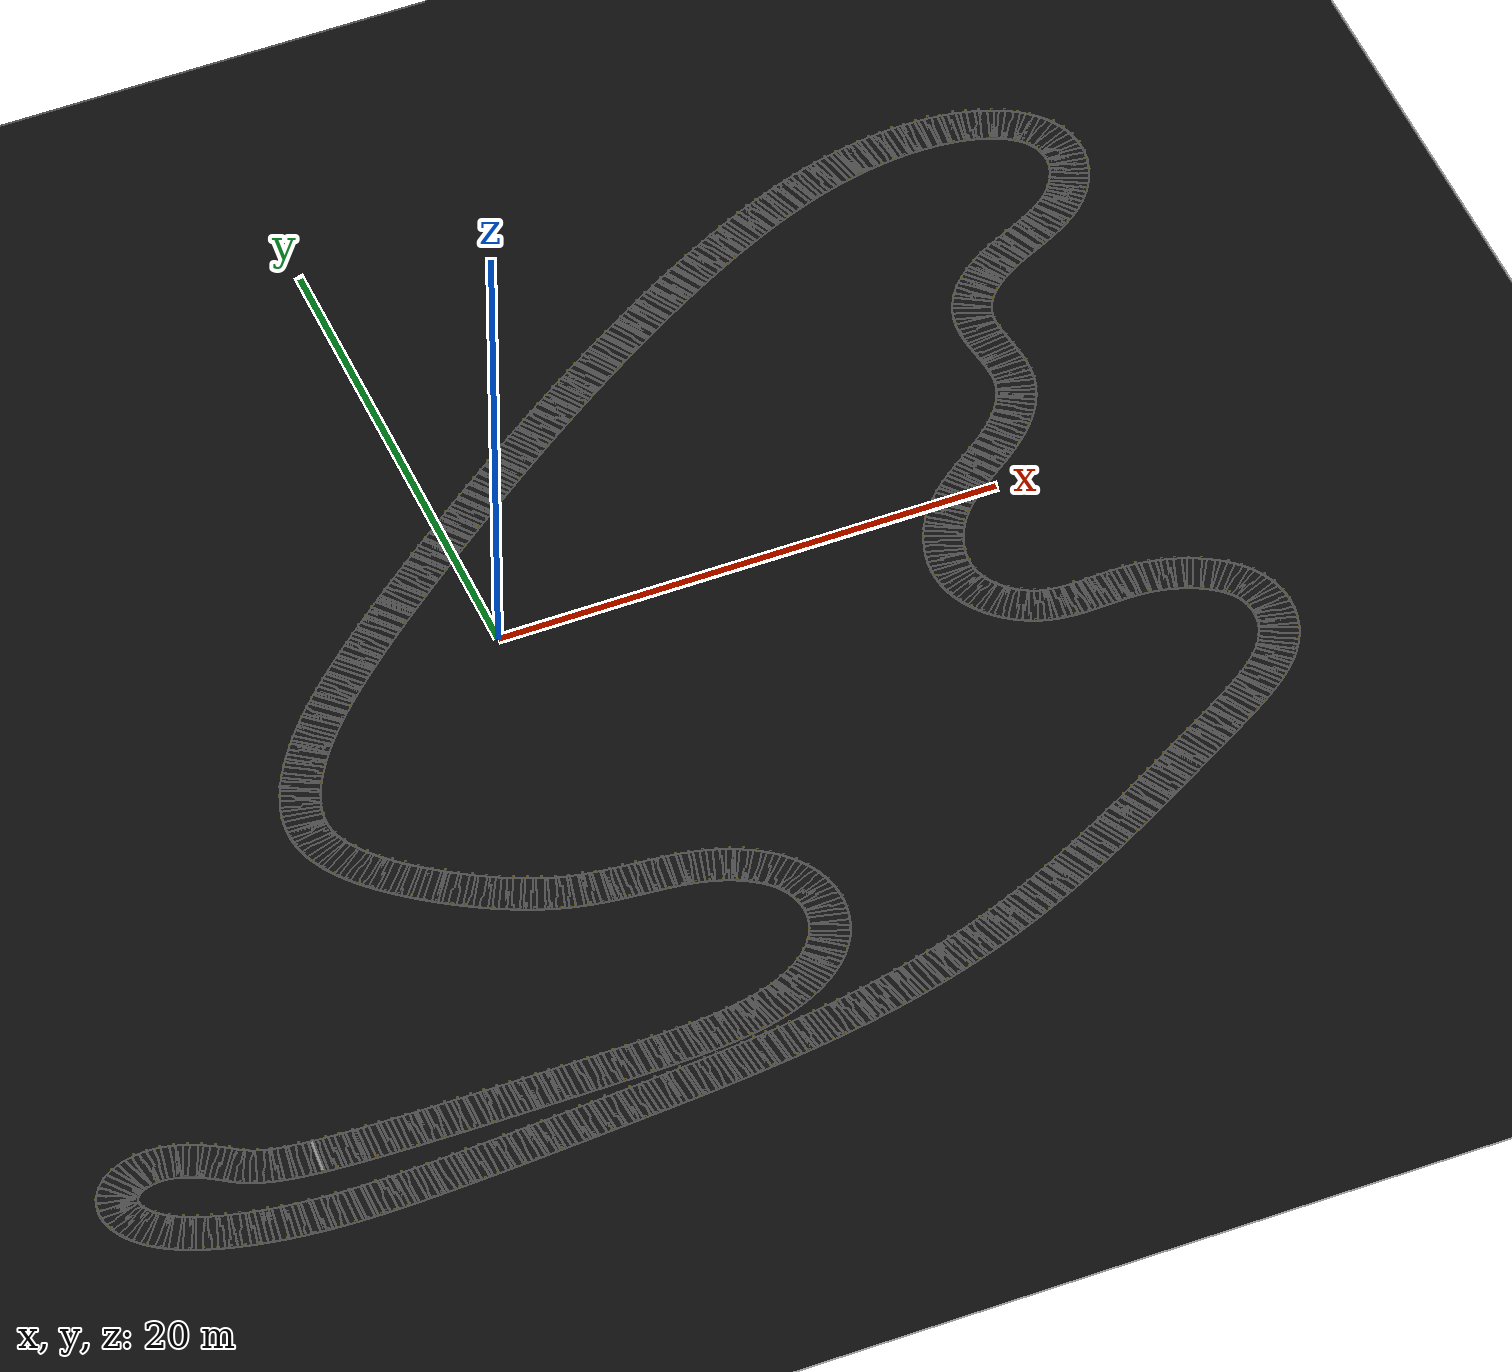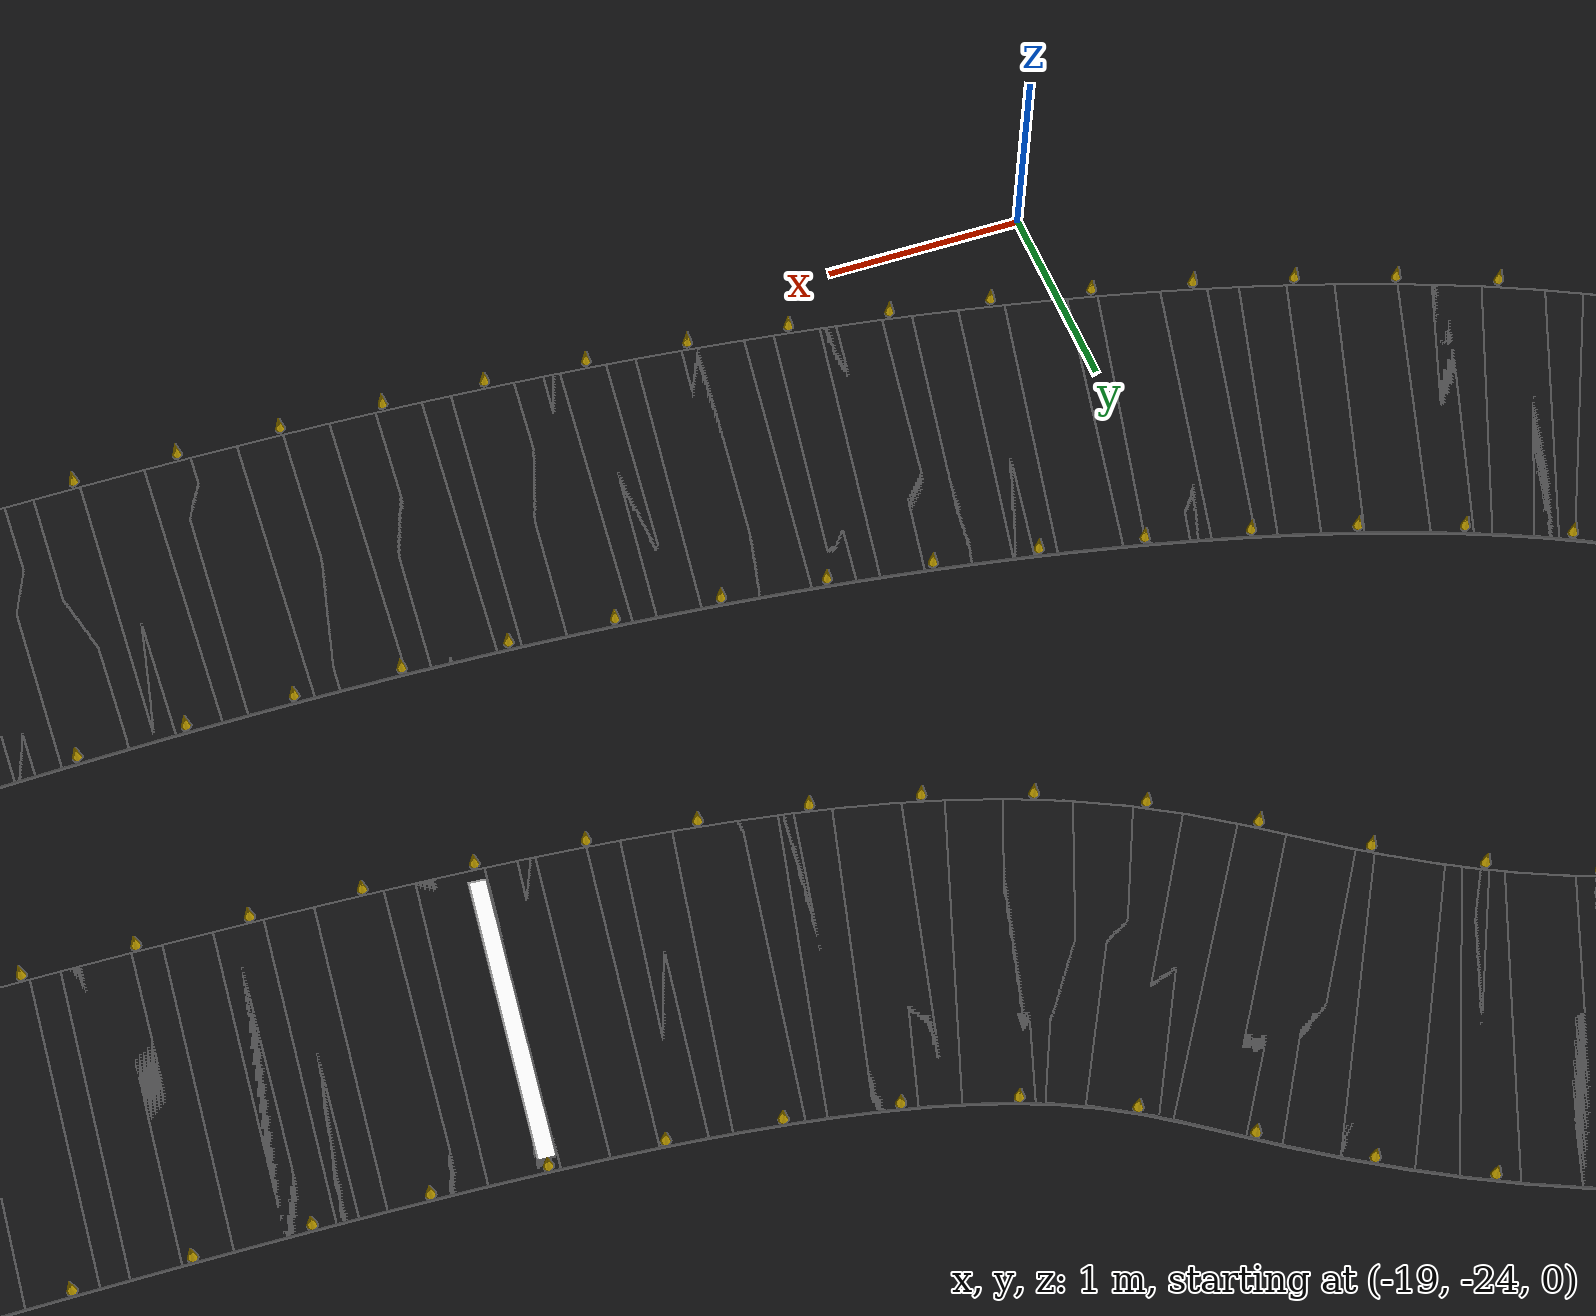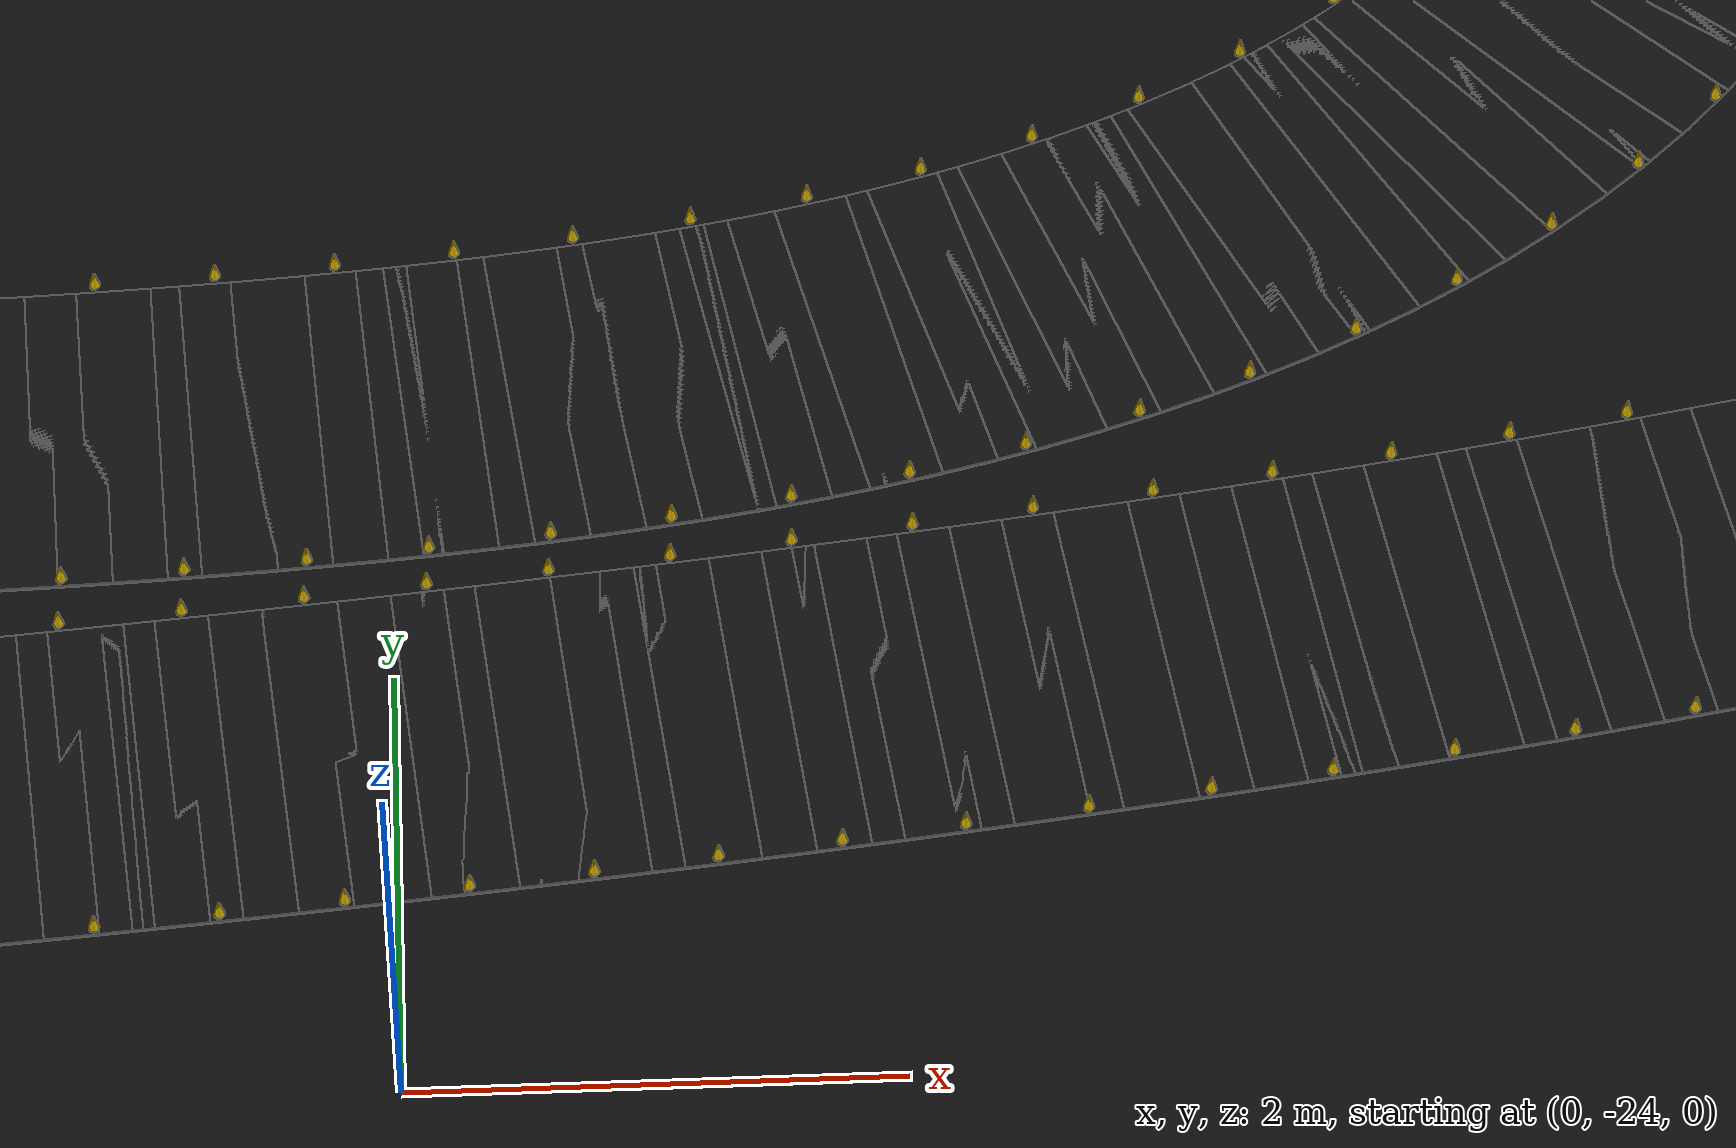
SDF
<?xml version='1.0'?>
<sdf version='1.10'>
  <world name='spa'>
    <physics name='1ms' type='ignored'><max_step_size>0.001</max_step_size><real_time_factor>1.0</real_time_factor></physics>
    <plugin filename='gz-sim-physics-system' name='gz::sim::systems::Physics'/>
    <plugin filename='gz-sim-user-commands-system' name='gz::sim::systems::UserCommands'/>
    <plugin filename='gz-sim-scene-broadcaster-system' name='gz::sim::systems::SceneBroadcaster'/>
    <scene><ambient>0.42 0.42 0.44 1</ambient><background>0.055 0.055 0.060 1</background><shadows>true</shadows></scene>
    <light name='sun' type='directional'><pose>0 0 30 0 0 0</pose><diffuse>0.9 0.9 0.9 1</diffuse><specular>0.2 0.2 0.2 1</specular><direction>-0.4 0.2 -1</direction></light>
    <model name='ground'><static>true</static><link name='ground_link'>
      <collision name='ground_collision'><geometry><plane><normal>0 0 1</normal><size>160 160</size></plane></geometry></collision>
      <visual name='ground_visual'><geometry><plane><normal>0 0 1</normal><size>160 160</size></plane></geometry><material><ambient>0.045 0.045 0.050 1</ambient><diffuse>0.045 0.045 0.050 1</diffuse></material></visual>
    </link></model>
    <model name='road'><static>true</static><link name='road_link'>
      <visual name='road_0'><pose>-15.17770 -20.59617 0.00600 0 -0.0000000 -0.0851970</pose><geometry><box><size>0.30988 1.50000 0.01200</size></box></geometry><material><ambient>0.055 0.055 0.060 1</ambient><diffuse>0.055 0.055 0.060 1</diffuse><specular>0.04 0.04 0.04 1</specular></material></visual>
      <visual name='road_1'><pose>-14.95855 -20.61399 0.00600 0 -0.0000000 -0.0770274</pose><geometry><box><size>0.30988 1.50000 0.01200</size></box></geometry><material><ambient>0.055 0.055 0.060 1</ambient><diffuse>0.055 0.055 0.060 1</diffuse><specular>0.04 0.04 0.04 1</specular></material></visual>
      <visual name='road_2'><pose>-14.73926 -20.63002 0.00600 0 -0.0000000 -0.0689573</pose><geometry><box><size>0.30988 1.50000 0.01200</size></box></geometry><material><ambient>0.055 0.055 0.060 1</ambient><diffuse>0.055 0.055 0.060 1</diffuse><specular>0.04 0.04 0.04 1</specular></material></visual>
      <visual name='road_3'><pose>-14.51987 -20.64452 0.00600 0 -0.0000000 -0.0630442</pose><geometry><box><size>0.30988 1.50000 0.01200</size></box></geometry><material><ambient>0.055 0.055 0.060 1</ambient><diffuse>0.055 0.055 0.060 1</diffuse><specular>0.04 0.04 0.04 1</specular></material></visual>
      <visual name='road_4'><pose>-14.30039 -20.65769 0.00600 0 -0.0000000 -0.0567800</pose><geometry><box><size>0.30988 1.50000 0.01200</size></box></geometry><material><ambient>0.055 0.055 0.060 1</ambient><diffuse>0.055 0.055 0.060 1</diffuse><specular>0.04 0.04 0.04 1</specular></material></visual>
      <visual name='road_5'><pose>-14.08084 -20.66965 0.00600 0 -0.0000000 -0.0520697</pose><geometry><box><size>0.30988 1.50000 0.01200</size></box></geometry><material><ambient>0.055 0.055 0.060 1</ambient><diffuse>0.055 0.055 0.060 1</diffuse><specular>0.04 0.04 0.04 1</specular></material></visual>
      <visual name='road_6'><pose>-13.86124 -20.68063 0.00600 0 -0.0000000 -0.0478632</pose><geometry><box><size>0.30988 1.50000 0.01200</size></box></geometry><material><ambient>0.055 0.055 0.060 1</ambient><diffuse>0.055 0.055 0.060 1</diffuse><specular>0.04 0.04 0.04 1</specular></material></visual>
      <visual name='road_7'><pose>-13.64159 -20.69068 0.00600 0 -0.0000000 -0.0435283</pose><geometry><box><size>0.30988 1.50000 0.01200</size></box></geometry><material><ambient>0.055 0.055 0.060 1</ambient><diffuse>0.055 0.055 0.060 1</diffuse><specular>0.04 0.04 0.04 1</specular></material></visual>
      <visual name='road_8'><pose>-13.42191 -20.69986 0.00600 0 -0.0000000 -0.0400078</pose><geometry><box><size>0.30988 1.50000 0.01200</size></box></geometry><material><ambient>0.055 0.055 0.060 1</ambient><diffuse>0.055 0.055 0.060 1</diffuse><specular>0.04 0.04 0.04 1</specular></material></visual>
      <visual name='road_9'><pose>-13.20219 -20.70831 0.00600 0 -0.0000000 -0.0368782</pose><geometry><box><size>0.30988 1.50000 0.01200</size></box></geometry><material><ambient>0.055 0.055 0.060 1</ambient><diffuse>0.055 0.055 0.060 1</diffuse><specular>0.04 0.04 0.04 1</specular></material></visual>
      <visual name='road_10'><pose>-12.98246 -20.71610 0.00600 0 -0.0000000 -0.0339929</pose><geometry><box><size>0.30988 1.50000 0.01200</size></box></geometry><material><ambient>0.055 0.055 0.060 1</ambient><diffuse>0.055 0.055 0.060 1</diffuse><specular>0.04 0.04 0.04 1</specular></material></visual>
      <visual name='road_11'><pose>-12.76270 -20.72327 0.00600 0 -0.0000000 -0.0312760</pose><geometry><box><size>0.30988 1.50000 0.01200</size></box></geometry><material><ambient>0.055 0.055 0.060 1</ambient><diffuse>0.055 0.055 0.060 1</diffuse><specular>0.04 0.04 0.04 1</specular></material></visual>
      <visual name='road_12'><pose>-12.54292 -20.72985 0.00600 0 -0.0000000 -0.0285879</pose><geometry><box><size>0.30988 1.50000 0.01200</size></box></geometry><material><ambient>0.055 0.055 0.060 1</ambient><diffuse>0.055 0.055 0.060 1</diffuse><specular>0.04 0.04 0.04 1</specular></material></visual>
      <visual name='road_13'><pose>-12.32313 -20.73589 0.00600 0 -0.0000000 -0.0263496</pose><geometry><box><size>0.30988 1.50000 0.01200</size></box></geometry><material><ambient>0.055 0.055 0.060 1</ambient><diffuse>0.055 0.055 0.060 1</diffuse><specular>0.04 0.04 0.04 1</specular></material></visual>
      <visual name='road_14'><pose>-12.10332 -20.74145 0.00600 0 -0.0000000 -0.0242669</pose><geometry><box><size>0.30988 1.50000 0.01200</size></box></geometry><material><ambient>0.055 0.055 0.060 1</ambient><diffuse>0.055 0.055 0.060 1</diffuse><specular>0.04 0.04 0.04 1</specular></material></visual>
      <visual name='road_15'><pose>-11.88350 -20.74658 0.00600 0 -0.0000000 -0.0223263</pose><geometry><box><size>0.30988 1.50000 0.01200</size></box></geometry><material><ambient>0.055 0.055 0.060 1</ambient><diffuse>0.055 0.055 0.060 1</diffuse><specular>0.04 0.04 0.04 1</specular></material></visual>
      <visual name='road_16'><pose>-11.66368 -20.75129 0.00600 0 -0.0000000 -0.0205158</pose><geometry><box><size>0.30988 1.50000 0.01200</size></box></geometry><material><ambient>0.055 0.055 0.060 1</ambient><diffuse>0.055 0.055 0.060 1</diffuse><specular>0.04 0.04 0.04 1</specular></material></visual>
      <visual name='road_17'><pose>-11.44385 -20.75561 0.00600 0 -0.0000000 -0.0188249</pose><geometry><box><size>0.30988 1.50000 0.01200</size></box></geometry><material><ambient>0.055 0.055 0.060 1</ambient><diffuse>0.055 0.055 0.060 1</diffuse><specular>0.04 0.04 0.04 1</specular></material></visual>
      <visual name='road_18'><pose>-11.22400 -20.75958 0.00600 0 -0.0000000 -0.0172441</pose><geometry><box><size>0.30988 1.50000 0.01200</size></box></geometry><material><ambient>0.055 0.055 0.060 1</ambient><diffuse>0.055 0.055 0.060 1</diffuse><specular>0.04 0.04 0.04 1</specular></material></visual>
      <visual name='road_19'><pose>-11.00416 -20.76321 0.00600 0 -0.0000000 -0.0157652</pose><geometry><box><size>0.30988 1.50000 0.01200</size></box></geometry><material><ambient>0.055 0.055 0.060 1</ambient><diffuse>0.055 0.055 0.060 1</diffuse><specular>0.04 0.04 0.04 1</specular></material></visual>
      <visual name='road_20'><pose>-10.78431 -20.76652 0.00600 0 -0.0000000 -0.0143806</pose><geometry><box><size>0.30988 1.50000 0.01200</size></box></geometry><material><ambient>0.055 0.055 0.060 1</ambient><diffuse>0.055 0.055 0.060 1</diffuse><specular>0.04 0.04 0.04 1</specular></material></visual>
      <visual name='road_21'><pose>-10.56445 -20.76953 0.00600 0 -0.0000000 -0.0130165</pose><geometry><box><size>0.30988 1.50000 0.01200</size></box></geometry><material><ambient>0.055 0.055 0.060 1</ambient><diffuse>0.055 0.055 0.060 1</diffuse><specular>0.04 0.04 0.04 1</specular></material></visual>
      <visual name='road_22'><pose>-10.34459 -20.77226 0.00600 0 -0.0000000 -0.0118120</pose><geometry><box><size>0.30988 1.50000 0.01200</size></box></geometry><material><ambient>0.055 0.055 0.060 1</ambient><diffuse>0.055 0.055 0.060 1</diffuse><specular>0.04 0.04 0.04 1</specular></material></visual>
      <visual name='road_23'><pose>-10.12473 -20.77473 0.00600 0 -0.0000000 -0.0106844</pose><geometry><box><size>0.30988 1.50000 0.01200</size></box></geometry><material><ambient>0.055 0.055 0.060 1</ambient><diffuse>0.055 0.055 0.060 1</diffuse><specular>0.04 0.04 0.04 1</specular></material></visual>
      <visual name='road_24'><pose>-9.90487 -20.77697 0.00600 0 -0.0000000 -0.0096273</pose><geometry><box><size>0.30988 1.50000 0.01200</size></box></geometry><material><ambient>0.055 0.055 0.060 1</ambient><diffuse>0.055 0.055 0.060 1</diffuse><specular>0.04 0.04 0.04 1</specular></material></visual>
      <visual name='road_25'><pose>-9.68500 -20.77897 0.00600 0 -0.0000000 -0.0086367</pose><geometry><box><size>0.30988 1.50000 0.01200</size></box></geometry><material><ambient>0.055 0.055 0.060 1</ambient><diffuse>0.055 0.055 0.060 1</diffuse><specular>0.04 0.04 0.04 1</specular></material></visual>
      <visual name='road_26'><pose>-9.46513 -20.78077 0.00600 0 -0.0000000 -0.0077093</pose><geometry><box><size>0.30988 1.50000 0.01200</size></box></geometry><material><ambient>0.055 0.055 0.060 1</ambient><diffuse>0.055 0.055 0.060 1</diffuse><specular>0.04 0.04 0.04 1</specular></material></visual>
      <visual name='road_27'><pose>-9.24526 -20.78237 0.00600 0 -0.0000000 -0.0068420</pose><geometry><box><size>0.30988 1.50000 0.01200</size></box></geometry><material><ambient>0.055 0.055 0.060 1</ambient><diffuse>0.055 0.055 0.060 1</diffuse><specular>0.04 0.04 0.04 1</specular></material></visual>
      <visual name='road_28'><pose>-9.02539 -20.78379 0.00600 0 -0.0000000 -0.0060322</pose><geometry><box><size>0.30988 1.50000 0.01200</size></box></geometry><material><ambient>0.055 0.055 0.060 1</ambient><diffuse>0.055 0.055 0.060 1</diffuse><specular>0.04 0.04 0.04 1</specular></material></visual>
      <visual name='road_29'><pose>-8.80552 -20.78503 0.00600 0 -0.0000000 -0.0052776</pose><geometry><box><size>0.30988 1.50000 0.01200</size></box></geometry><material><ambient>0.055 0.055 0.060 1</ambient><diffuse>0.055 0.055 0.060 1</diffuse><specular>0.04 0.04 0.04 1</specular></material></visual>
      <visual name='road_30'><pose>-8.58564 -20.78611 0.00600 0 -0.0000000 -0.0045764</pose><geometry><box><size>0.30988 1.50000 0.01200</size></box></geometry><material><ambient>0.055 0.055 0.060 1</ambient><diffuse>0.055 0.055 0.060 1</diffuse><specular>0.04 0.04 0.04 1</specular></material></visual>
      <visual name='road_31'><pose>-8.36577 -20.78705 0.00600 0 -0.0000000 -0.0039269</pose><geometry><box><size>0.30988 1.50000 0.01200</size></box></geometry><material><ambient>0.055 0.055 0.060 1</ambient><diffuse>0.055 0.055 0.060 1</diffuse><specular>0.04 0.04 0.04 1</specular></material></visual>
      <visual name='road_32'><pose>-8.14589 -20.78785 0.00600 0 -0.0000000 -0.0033278</pose><geometry><box><size>0.30988 1.50000 0.01200</size></box></geometry><material><ambient>0.055 0.055 0.060 1</ambient><diffuse>0.055 0.055 0.060 1</diffuse><specular>0.04 0.04 0.04 1</specular></material></visual>
      <visual name='road_33'><pose>-7.92602 -20.78852 0.00600 0 -0.0000000 -0.0027782</pose><geometry><box><size>0.30988 1.50000 0.01200</size></box></geometry><material><ambient>0.055 0.055 0.060 1</ambient><diffuse>0.055 0.055 0.060 1</diffuse><specular>0.04 0.04 0.04 1</specular></material></visual>
      <visual name='road_34'><pose>-7.70614 -20.78907 0.00600 0 -0.0000000 -0.0022773</pose><geometry><box><size>0.30988 1.50000 0.01200</size></box></geometry><material><ambient>0.055 0.055 0.060 1</ambient><diffuse>0.055 0.055 0.060 1</diffuse><specular>0.04 0.04 0.04 1</specular></material></visual>
      <visual name='road_35'><pose>-7.48627 -20.78952 0.00600 0 -0.0000000 -0.0018247</pose><geometry><box><size>0.30988 1.50000 0.01200</size></box></geometry><material><ambient>0.055 0.055 0.060 1</ambient><diffuse>0.055 0.055 0.060 1</diffuse><specular>0.04 0.04 0.04 1</specular></material></visual>
      <visual name='road_36'><pose>-7.26639 -20.78988 0.00600 0 -0.0000000 -0.0014203</pose><geometry><box><size>0.30988 1.50000 0.01200</size></box></geometry><material><ambient>0.055 0.055 0.060 1</ambient><diffuse>0.055 0.055 0.060 1</diffuse><specular>0.04 0.04 0.04 1</specular></material></visual>
      <visual name='road_37'><pose>-7.04651 -20.79015 0.00600 0 -0.0000000 -0.0010643</pose><geometry><box><size>0.30988 1.50000 0.01200</size></box></geometry><material><ambient>0.055 0.055 0.060 1</ambient><diffuse>0.055 0.055 0.060 1</diffuse><specular>0.04 0.04 0.04 1</specular></material></visual>
      <visual name='road_38'><pose>-6.82664 -20.79035 0.00600 0 -0.0000000 -0.0007571</pose><geometry><box><size>0.30988 1.50000 0.01200</size></box></geometry><material><ambient>0.055 0.055 0.060 1</ambient><diffuse>0.055 0.055 0.060 1</diffuse><specular>0.04 0.04 0.04 1</specular></material></visual>
      <visual name='road_39'><pose>-6.60676 -20.79049 0.00600 0 -0.0000000 -0.0004931</pose><geometry><box><size>0.30988 1.50000 0.01200</size></box></geometry><material><ambient>0.055 0.055 0.060 1</ambient><diffuse>0.055 0.055 0.060 1</diffuse><specular>0.04 0.04 0.04 1</specular></material></visual>
      <visual name='road_40'><pose>-6.38689 -20.79058 0.00600 0 -0.0000000 -0.0002823</pose><geometry><box><size>0.30988 1.50000 0.01200</size></box></geometry><material><ambient>0.055 0.055 0.060 1</ambient><diffuse>0.055 0.055 0.060 1</diffuse><specular>0.04 0.04 0.04 1</specular></material></visual>
      <visual name='road_41'><pose>-6.16701 -20.79062 0.00600 0 -0.0000000 -0.0001348</pose><geometry><box><size>0.30988 1.50000 0.01200</size></box></geometry><material><ambient>0.055 0.055 0.060 1</ambient><diffuse>0.055 0.055 0.060 1</diffuse><specular>0.04 0.04 0.04 1</specular></material></visual>
      <visual name='road_42'><pose>-5.94713 -20.79064 0.00600 0 -0.0000000 -0.0000426</pose><geometry><box><size>0.30988 1.50000 0.01200</size></box></geometry><material><ambient>0.055 0.055 0.060 1</ambient><diffuse>0.055 0.055 0.060 1</diffuse><specular>0.04 0.04 0.04 1</specular></material></visual>
      <visual name='road_43'><pose>-5.72726 -20.79065 0.00600 0 -0.0000000 0.0000019</pose><geometry><box><size>0.30988 1.50000 0.01200</size></box></geometry><material><ambient>0.055 0.055 0.060 1</ambient><diffuse>0.055 0.055 0.060 1</diffuse><specular>0.04 0.04 0.04 1</specular></material></visual>
      <visual name='road_44'><pose>-5.50738 -20.79064 0.00600 0 -0.0000000 0.0000700</pose><geometry><box><size>0.30988 1.50000 0.01200</size></box></geometry><material><ambient>0.055 0.055 0.060 1</ambient><diffuse>0.055 0.055 0.060 1</diffuse><specular>0.04 0.04 0.04 1</specular></material></visual>
      <visual name='road_45'><pose>-5.28750 -20.79060 0.00600 0 -0.0000000 0.0002519</pose><geometry><box><size>0.30988 1.50000 0.01200</size></box></geometry><material><ambient>0.055 0.055 0.060 1</ambient><diffuse>0.055 0.055 0.060 1</diffuse><specular>0.04 0.04 0.04 1</specular></material></visual>
      <visual name='road_46'><pose>-5.06763 -20.79051 0.00600 0 -0.0000000 0.0005694</pose><geometry><box><size>0.30988 1.50000 0.01200</size></box></geometry><material><ambient>0.055 0.055 0.060 1</ambient><diffuse>0.055 0.055 0.060 1</diffuse><specular>0.04 0.04 0.04 1</specular></material></visual>
      <visual name='road_47'><pose>-4.84775 -20.79033 0.00600 0 -0.0000000 0.0010675</pose><geometry><box><size>0.30988 1.50000 0.01200</size></box></geometry><material><ambient>0.055 0.055 0.060 1</ambient><diffuse>0.055 0.055 0.060 1</diffuse><specular>0.04 0.04 0.04 1</specular></material></visual>
      <visual name='road_48'><pose>-4.62788 -20.79002 0.00600 0 -0.0000000 0.0017535</pose><geometry><box><size>0.30988 1.50000 0.01200</size></box></geometry><material><ambient>0.055 0.055 0.060 1</ambient><diffuse>0.055 0.055 0.060 1</diffuse><specular>0.04 0.04 0.04 1</specular></material></visual>
      <visual name='road_49'><pose>-4.40800 -20.78955 0.00600 0 -0.0000000 0.0025689</pose><geometry><box><size>0.30988 1.50000 0.01200</size></box></geometry><material><ambient>0.055 0.055 0.060 1</ambient><diffuse>0.055 0.055 0.060 1</diffuse><specular>0.04 0.04 0.04 1</specular></material></visual>
      <visual name='road_50'><pose>-4.18813 -20.78887 0.00600 0 -0.0000000 0.0035563</pose><geometry><box><size>0.30988 1.50000 0.01200</size></box></geometry><material><ambient>0.055 0.055 0.060 1</ambient><diffuse>0.055 0.055 0.060 1</diffuse><specular>0.04 0.04 0.04 1</specular></material></visual>
      <visual name='road_51'><pose>-3.96825 -20.78796 0.00600 0 -0.0000000 0.0047246</pose><geometry><box><size>0.30988 1.50000 0.01200</size></box></geometry><material><ambient>0.055 0.055 0.060 1</ambient><diffuse>0.055 0.055 0.060 1</diffuse><specular>0.04 0.04 0.04 1</specular></material></visual>
      <visual name='road_52'><pose>-3.74838 -20.78675 0.00600 0 -0.0000000 0.0062762</pose><geometry><box><size>0.30988 1.50000 0.01200</size></box></geometry><material><ambient>0.055 0.055 0.060 1</ambient><diffuse>0.055 0.055 0.060 1</diffuse><specular>0.04 0.04 0.04 1</specular></material></visual>
      <visual name='road_53'><pose>-3.52851 -20.78519 0.00600 0 -0.0000000 0.0079651</pose><geometry><box><size>0.30988 1.50000 0.01200</size></box></geometry><material><ambient>0.055 0.055 0.060 1</ambient><diffuse>0.055 0.055 0.060 1</diffuse><specular>0.04 0.04 0.04 1</specular></material></visual>
      <visual name='road_54'><pose>-3.30864 -20.78323 0.00600 0 -0.0000000 0.0098084</pose><geometry><box><size>0.30988 1.50000 0.01200</size></box></geometry><material><ambient>0.055 0.055 0.060 1</ambient><diffuse>0.055 0.055 0.060 1</diffuse><specular>0.04 0.04 0.04 1</specular></material></visual>
      <visual name='road_55'><pose>-3.08878 -20.78084 0.00600 0 -0.0000000 0.0119467</pose><geometry><box><size>0.30988 1.50000 0.01200</size></box></geometry><material><ambient>0.055 0.055 0.060 1</ambient><diffuse>0.055 0.055 0.060 1</diffuse><specular>0.04 0.04 0.04 1</specular></material></visual>
      <visual name='road_56'><pose>-2.86892 -20.77791 0.00600 0 -0.0000000 0.0146915</pose><geometry><box><size>0.30988 1.50000 0.01200</size></box></geometry><material><ambient>0.055 0.055 0.060 1</ambient><diffuse>0.055 0.055 0.060 1</diffuse><specular>0.04 0.04 0.04 1</specular></material></visual>
      <visual name='road_57'><pose>-2.64907 -20.77439 0.00600 0 -0.0000000 0.0173481</pose><geometry><box><size>0.30988 1.50000 0.01200</size></box></geometry><material><ambient>0.055 0.055 0.060 1</ambient><diffuse>0.055 0.055 0.060 1</diffuse><specular>0.04 0.04 0.04 1</specular></material></visual>
      <visual name='road_58'><pose>-2.42924 -20.77024 0.00600 0 -0.0000000 0.0204152</pose><geometry><box><size>0.30988 1.50000 0.01200</size></box></geometry><material><ambient>0.055 0.055 0.060 1</ambient><diffuse>0.055 0.055 0.060 1</diffuse><specular>0.04 0.04 0.04 1</specular></material></visual>
      <visual name='road_59'><pose>-2.20942 -20.76533 0.00600 0 -0.0000000 0.0242476</pose><geometry><box><size>0.30988 1.50000 0.01200</size></box></geometry><material><ambient>0.055 0.055 0.060 1</ambient><diffuse>0.055 0.055 0.060 1</diffuse><specular>0.04 0.04 0.04 1</specular></material></visual>
      <visual name='road_60'><pose>-1.98962 -20.75960 0.00600 0 -0.0000000 0.0278789</pose><geometry><box><size>0.30988 1.50000 0.01200</size></box></geometry><material><ambient>0.055 0.055 0.060 1</ambient><diffuse>0.055 0.055 0.060 1</diffuse><specular>0.04 0.04 0.04 1</specular></material></visual>
      <visual name='road_61'><pose>-1.76984 -20.75296 0.00600 0 -0.0000000 0.0325002</pose><geometry><box><size>0.30988 1.50000 0.01200</size></box></geometry><material><ambient>0.055 0.055 0.060 1</ambient><diffuse>0.055 0.055 0.060 1</diffuse><specular>0.04 0.04 0.04 1</specular></material></visual>
      <visual name='road_62'><pose>-1.55010 -20.74530 0.00600 0 -0.0000000 0.0372345</pose><geometry><box><size>0.30988 1.50000 0.01200</size></box></geometry><material><ambient>0.055 0.055 0.060 1</ambient><diffuse>0.055 0.055 0.060 1</diffuse><specular>0.04 0.04 0.04 1</specular></material></visual>
      <visual name='road_63'><pose>-1.33040 -20.73653 0.00600 0 -0.0000000 0.0425994</pose><geometry><box><size>0.30988 1.50000 0.01200</size></box></geometry><material><ambient>0.055 0.055 0.060 1</ambient><diffuse>0.055 0.055 0.060 1</diffuse><specular>0.04 0.04 0.04 1</specular></material></visual>
      <visual name='road_64'><pose>-1.11075 -20.72650 0.00600 0 -0.0000000 0.0486036</pose><geometry><box><size>0.30988 1.50000 0.01200</size></box></geometry><material><ambient>0.055 0.055 0.060 1</ambient><diffuse>0.055 0.055 0.060 1</diffuse><specular>0.04 0.04 0.04 1</specular></material></visual>
      <visual name='road_65'><pose>-0.89117 -20.71511 0.00600 0 -0.0000000 0.0550758</pose><geometry><box><size>0.30988 1.50000 0.01200</size></box></geometry><material><ambient>0.055 0.055 0.060 1</ambient><diffuse>0.055 0.055 0.060 1</diffuse><specular>0.04 0.04 0.04 1</specular></material></visual>
      <visual name='road_66'><pose>-0.67168 -20.70221 0.00600 0 -0.0000000 0.0622793</pose><geometry><box><size>0.30988 1.50000 0.01200</size></box></geometry><material><ambient>0.055 0.055 0.060 1</ambient><diffuse>0.055 0.055 0.060 1</diffuse><specular>0.04 0.04 0.04 1</specular></material></visual>
      <visual name='road_67'><pose>-0.45229 -20.68764 0.00600 0 -0.0000000 0.0703698</pose><geometry><box><size>0.30988 1.50000 0.01200</size></box></geometry><material><ambient>0.055 0.055 0.060 1</ambient><diffuse>0.055 0.055 0.060 1</diffuse><specular>0.04 0.04 0.04 1</specular></material></visual>
      <visual name='road_68'><pose>-0.23302 -20.67128 0.00600 0 -0.0000000 0.0785870</pose><geometry><box><size>0.30988 1.50000 0.01200</size></box></geometry><material><ambient>0.055 0.055 0.060 1</ambient><diffuse>0.055 0.055 0.060 1</diffuse><specular>0.04 0.04 0.04 1</specular></material></visual>
      <visual name='road_69'><pose>-0.01392 -20.65288 0.00600 0 -0.0000000 0.0889740</pose><geometry><box><size>0.30988 1.50000 0.01200</size></box></geometry><material><ambient>0.055 0.055 0.060 1</ambient><diffuse>0.055 0.055 0.060 1</diffuse><specular>0.04 0.04 0.04 1</specular></material></visual>
      <visual name='road_70'><pose>0.20498 -20.63224 0.00600 0 -0.0000000 0.0990719</pose><geometry><box><size>0.30987 1.50000 0.01200</size></box></geometry><material><ambient>0.055 0.055 0.060 1</ambient><diffuse>0.055 0.055 0.060 1</diffuse><specular>0.04 0.04 0.04 1</specular></material></visual>
      <visual name='road_71'><pose>0.42365 -20.60927 0.00600 0 -0.0000000 0.1102513</pose><geometry><box><size>0.30987 1.50000 0.01200</size></box></geometry><material><ambient>0.055 0.055 0.060 1</ambient><diffuse>0.055 0.055 0.060 1</diffuse><specular>0.04 0.04 0.04 1</specular></material></visual>
      <visual name='road_72'><pose>0.64201 -20.58360 0.00600 0 -0.0000000 0.1238119</pose><geometry><box><size>0.30987 1.50000 0.01200</size></box></geometry><material><ambient>0.055 0.055 0.060 1</ambient><diffuse>0.055 0.055 0.060 1</diffuse><specular>0.04 0.04 0.04 1</specular></material></visual>
      <visual name='road_73'><pose>0.86001 -20.55495 0.00600 0 -0.0000000 0.1374947</pose><geometry><box><size>0.30987 1.50000 0.01200</size></box></geometry><material><ambient>0.055 0.055 0.060 1</ambient><diffuse>0.055 0.055 0.060 1</diffuse><specular>0.04 0.04 0.04 1</specular></material></visual>
      <visual name='road_74'><pose>1.07756 -20.52317 0.00600 0 -0.0000000 0.1525942</pose><geometry><box><size>0.30987 1.50000 0.01200</size></box></geometry><material><ambient>0.055 0.055 0.060 1</ambient><diffuse>0.055 0.055 0.060 1</diffuse><specular>0.04 0.04 0.04 1</specular></material></visual>
      <visual name='road_75'><pose>1.29459 -20.48794 0.00600 0 -0.0000000 0.1692481</pose><geometry><box><size>0.30987 1.50000 0.01200</size></box></geometry><material><ambient>0.055 0.055 0.060 1</ambient><diffuse>0.055 0.055 0.060 1</diffuse><specular>0.04 0.04 0.04 1</specular></material></visual>
      <visual name='road_76'><pose>1.51096 -20.44892 0.00600 0 -0.0000000 0.1875915</pose><geometry><box><size>0.30987 1.50000 0.01200</size></box></geometry><material><ambient>0.055 0.055 0.060 1</ambient><diffuse>0.055 0.055 0.060 1</diffuse><specular>0.04 0.04 0.04 1</specular></material></visual>
      <visual name='road_77'><pose>1.72654 -20.40574 0.00600 0 -0.0000000 0.2077782</pose><geometry><box><size>0.30987 1.50000 0.01200</size></box></geometry><material><ambient>0.055 0.055 0.060 1</ambient><diffuse>0.055 0.055 0.060 1</diffuse><specular>0.04 0.04 0.04 1</specular></material></visual>
      <visual name='road_78'><pose>1.94116 -20.35801 0.00600 0 -0.0000000 0.2299076</pose><geometry><box><size>0.30987 1.50000 0.01200</size></box></geometry><material><ambient>0.055 0.055 0.060 1</ambient><diffuse>0.055 0.055 0.060 1</diffuse><specular>0.04 0.04 0.04 1</specular></material></visual>
      <visual name='road_79'><pose>2.15464 -20.30545 0.00600 0 -0.0000000 0.2529318</pose><geometry><box><size>0.30987 1.50000 0.01200</size></box></geometry><material><ambient>0.055 0.055 0.060 1</ambient><diffuse>0.055 0.055 0.060 1</diffuse><specular>0.04 0.04 0.04 1</specular></material></visual>
      <visual name='road_80'><pose>2.36681 -20.24783 0.00600 0 -0.0000000 0.2773782</pose><geometry><box><size>0.30987 1.50000 0.01200</size></box></geometry><material><ambient>0.055 0.055 0.060 1</ambient><diffuse>0.055 0.055 0.060 1</diffuse><specular>0.04 0.04 0.04 1</specular></material></visual>
      <visual name='road_81'><pose>2.57746 -20.18490 0.00600 0 -0.0000000 0.3032194</pose><geometry><box><size>0.30987 1.50000 0.01200</size></box></geometry><material><ambient>0.055 0.055 0.060 1</ambient><diffuse>0.055 0.055 0.060 1</diffuse><specular>0.04 0.04 0.04 1</specular></material></visual>
      <visual name='road_82'><pose>2.78637 -20.11643 0.00600 0 -0.0000000 0.3302706</pose><geometry><box><size>0.30987 1.50000 0.01200</size></box></geometry><material><ambient>0.055 0.055 0.060 1</ambient><diffuse>0.055 0.055 0.060 1</diffuse><specular>0.04 0.04 0.04 1</specular></material></visual>
      <visual name='road_83'><pose>2.99330 -20.04218 0.00600 0 -0.0000000 0.3587009</pose><geometry><box><size>0.30987 1.50000 0.01200</size></box></geometry><material><ambient>0.055 0.055 0.060 1</ambient><diffuse>0.055 0.055 0.060 1</diffuse><specular>0.04 0.04 0.04 1</specular></material></visual>
      <visual name='road_84'><pose>3.19798 -19.96194 0.00600 0 -0.0000000 0.3885715</pose><geometry><box><size>0.30986 1.50000 0.01200</size></box></geometry><material><ambient>0.055 0.055 0.060 1</ambient><diffuse>0.055 0.055 0.060 1</diffuse><specular>0.04 0.04 0.04 1</specular></material></visual>
      <visual name='road_85'><pose>3.40007 -19.87542 0.00600 0 -0.0000000 0.4204425</pose><geometry><box><size>0.30986 1.50000 0.01200</size></box></geometry><material><ambient>0.055 0.055 0.060 1</ambient><diffuse>0.055 0.055 0.060 1</diffuse><specular>0.04 0.04 0.04 1</specular></material></visual>
      <visual name='road_86'><pose>3.59917 -19.78222 0.00600 0 -0.0000000 0.4551889</pose><geometry><box><size>0.30986 1.50000 0.01200</size></box></geometry><material><ambient>0.055 0.055 0.060 1</ambient><diffuse>0.055 0.055 0.060 1</diffuse><specular>0.04 0.04 0.04 1</specular></material></visual>
      <visual name='road_87'><pose>3.79489 -19.68214 0.00600 0 -0.0000000 0.4901395</pose><geometry><box><size>0.30986 1.50000 0.01200</size></box></geometry><material><ambient>0.055 0.055 0.060 1</ambient><diffuse>0.055 0.055 0.060 1</diffuse><specular>0.04 0.04 0.04 1</specular></material></visual>
      <visual name='road_88'><pose>3.98678 -19.57489 0.00600 0 -0.0000000 0.5291826</pose><geometry><box><size>0.30986 1.50000 0.01200</size></box></geometry><material><ambient>0.055 0.055 0.060 1</ambient><diffuse>0.055 0.055 0.060 1</diffuse><specular>0.04 0.04 0.04 1</specular></material></visual>
      <visual name='road_89'><pose>4.17430 -19.46020 0.00600 0 -0.0000000 0.5687148</pose><geometry><box><size>0.30986 1.50000 0.01200</size></box></geometry><material><ambient>0.055 0.055 0.060 1</ambient><diffuse>0.055 0.055 0.060 1</diffuse><specular>0.04 0.04 0.04 1</specular></material></visual>
      <visual name='road_90'><pose>4.35684 -19.33776 0.00600 0 -0.0000000 0.6129247</pose><geometry><box><size>0.30986 1.50000 0.01200</size></box></geometry><material><ambient>0.055 0.055 0.060 1</ambient><diffuse>0.055 0.055 0.060 1</diffuse><specular>0.04 0.04 0.04 1</specular></material></visual>
      <visual name='road_91'><pose>4.53374 -19.20731 0.00600 0 -0.0000000 0.6578256</pose><geometry><box><size>0.30985 1.50000 0.01200</size></box></geometry><material><ambient>0.055 0.055 0.060 1</ambient><diffuse>0.055 0.055 0.060 1</diffuse><specular>0.04 0.04 0.04 1</specular></material></visual>
      <visual name='road_92'><pose>4.70439 -19.06879 0.00600 0 -0.0000000 0.7058899</pose><geometry><box><size>0.30985 1.50000 0.01200</size></box></geometry><material><ambient>0.055 0.055 0.060 1</ambient><diffuse>0.055 0.055 0.060 1</diffuse><specular>0.04 0.04 0.04 1</specular></material></visual>
      <visual name='road_93'><pose>4.86785 -18.92188 0.00600 0 -0.0000000 0.7583377</pose><geometry><box><size>0.30985 1.50000 0.01200</size></box></geometry><material><ambient>0.055 0.055 0.060 1</ambient><diffuse>0.055 0.055 0.060 1</diffuse><specular>0.04 0.04 0.04 1</specular></material></visual>
      <visual name='road_94'><pose>5.02326 -18.76649 0.00600 0 -0.0000000 0.8123464</pose><geometry><box><size>0.30984 1.50000 0.01200</size></box></geometry><material><ambient>0.055 0.055 0.060 1</ambient><diffuse>0.055 0.055 0.060 1</diffuse><specular>0.04 0.04 0.04 1</specular></material></visual>
      <visual name='road_95'><pose>5.16979 -18.60273 0.00600 0 -0.0000000 0.8694068</pose><geometry><box><size>0.30984 1.50000 0.01200</size></box></geometry><material><ambient>0.055 0.055 0.060 1</ambient><diffuse>0.055 0.055 0.060 1</diffuse><specular>0.04 0.04 0.04 1</specular></material></visual>
      <visual name='road_96'><pose>5.30649 -18.43068 0.00600 0 -0.0000000 0.9293663</pose><geometry><box><size>0.30984 1.50000 0.01200</size></box></geometry><material><ambient>0.055 0.055 0.060 1</ambient><diffuse>0.055 0.055 0.060 1</diffuse><specular>0.04 0.04 0.04 1</specular></material></visual>
      <visual name='road_97'><pose>5.43238 -18.25060 0.00600 0 -0.0000000 0.9919815</pose><geometry><box><size>0.30983 1.50000 0.01200</size></box></geometry><material><ambient>0.055 0.055 0.060 1</ambient><diffuse>0.055 0.055 0.060 1</diffuse><specular>0.04 0.04 0.04 1</specular></material></visual>
      <visual name='road_98'><pose>5.54655 -18.06288 0.00600 0 -0.0000000 1.0568117</pose><geometry><box><size>0.30983 1.50000 0.01200</size></box></geometry><material><ambient>0.055 0.055 0.060 1</ambient><diffuse>0.055 0.055 0.060 1</diffuse><specular>0.04 0.04 0.04 1</specular></material></visual>
      <visual name='road_99'><pose>5.64818 -17.86808 0.00600 0 -0.0000000 1.1230025</pose><geometry><box><size>0.30983 1.50000 0.01200</size></box></geometry><material><ambient>0.055 0.055 0.060 1</ambient><diffuse>0.055 0.055 0.060 1</diffuse><specular>0.04 0.04 0.04 1</specular></material></visual>
      <visual name='road_100'><pose>5.73651 -17.66691 0.00600 0 -0.0000000 1.1911481</pose><geometry><box><size>0.30983 1.50000 0.01200</size></box></geometry><material><ambient>0.055 0.055 0.060 1</ambient><diffuse>0.055 0.055 0.060 1</diffuse><specular>0.04 0.04 0.04 1</specular></material></visual>
      <visual name='road_101'><pose>5.81086 -17.46018 0.00600 0 -0.0000000 1.2599332</pose><geometry><box><size>0.30983 1.50000 0.01200</size></box></geometry><material><ambient>0.055 0.055 0.060 1</ambient><diffuse>0.055 0.055 0.060 1</diffuse><specular>0.04 0.04 0.04 1</specular></material></visual>
      <visual name='road_102'><pose>5.87077 -17.24881 0.00600 0 -0.0000000 1.3293528</pose><geometry><box><size>0.30982 1.50000 0.01200</size></box></geometry><material><ambient>0.055 0.055 0.060 1</ambient><diffuse>0.055 0.055 0.060 1</diffuse><specular>0.04 0.04 0.04 1</specular></material></visual>
      <visual name='road_103'><pose>5.91576 -17.03378 0.00600 0 -0.0000000 1.3997212</pose><geometry><box><size>0.30983 1.50000 0.01200</size></box></geometry><material><ambient>0.055 0.055 0.060 1</ambient><diffuse>0.055 0.055 0.060 1</diffuse><specular>0.04 0.04 0.04 1</specular></material></visual>
      <visual name='road_104'><pose>5.94528 -16.81609 0.00600 0 -0.0000000 1.4722675</pose><geometry><box><size>0.30982 1.50000 0.01200</size></box></geometry><material><ambient>0.055 0.055 0.060 1</ambient><diffuse>0.055 0.055 0.060 1</diffuse><specular>0.04 0.04 0.04 1</specular></material></visual>
      <visual name='road_105'><pose>5.95887 -16.59683 0.00600 0 -0.0000000 1.5455082</pose><geometry><box><size>0.30982 1.50000 0.01200</size></box></geometry><material><ambient>0.055 0.055 0.060 1</ambient><diffuse>0.055 0.055 0.060 1</diffuse><specular>0.04 0.04 0.04 1</specular></material></visual>
      <visual name='road_106'><pose>5.95636 -16.37718 0.00600 0 -0.0000000 1.6189283</pose><geometry><box><size>0.30982 1.50000 0.01200</size></box></geometry><material><ambient>0.055 0.055 0.060 1</ambient><diffuse>0.055 0.055 0.060 1</diffuse><specular>0.04 0.04 0.04 1</specular></material></visual>
      <visual name='road_107'><pose>5.93750 -16.15833 0.00600 0 -0.0000000 1.6946409</pose><geometry><box><size>0.30982 1.50000 0.01200</size></box></geometry><material><ambient>0.055 0.055 0.060 1</ambient><diffuse>0.055 0.055 0.060 1</diffuse><specular>0.04 0.04 0.04 1</specular></material></visual>
      <visual name='road_108'><pose>5.90205 -15.94155 0.00600 0 -0.0000000 1.7710912</pose><geometry><box><size>0.30982 1.50000 0.01200</size></box></geometry><material><ambient>0.055 0.055 0.060 1</ambient><diffuse>0.055 0.055 0.060 1</diffuse><specular>0.04 0.04 0.04 1</specular></material></visual>
      <visual name='road_109'><pose>5.85018 -15.72810 0.00600 0 -0.0000000 1.8473591</pose><geometry><box><size>0.30982 1.50000 0.01200</size></box></geometry><material><ambient>0.055 0.055 0.060 1</ambient><diffuse>0.055 0.055 0.060 1</diffuse><specular>0.04 0.04 0.04 1</specular></material></visual>
      <visual name='road_110'><pose>5.78193 -15.51933 0.00600 0 -0.0000000 1.9260805</pose><geometry><box><size>0.30982 1.50000 0.01200</size></box></geometry><material><ambient>0.055 0.055 0.060 1</ambient><diffuse>0.055 0.055 0.060 1</diffuse><specular>0.04 0.04 0.04 1</specular></material></visual>
      <visual name='road_111'><pose>5.69754 -15.31654 0.00600 0 -0.0000000 2.0042902</pose><geometry><box><size>0.30981 1.50000 0.01200</size></box></geometry><material><ambient>0.055 0.055 0.060 1</ambient><diffuse>0.055 0.055 0.060 1</diffuse><specular>0.04 0.04 0.04 1</specular></material></visual>
      <visual name='road_112'><pose>5.59759 -15.12095 0.00600 0 -0.0000000 2.0820880</pose><geometry><box><size>0.30981 1.50000 0.01200</size></box></geometry><material><ambient>0.055 0.055 0.060 1</ambient><diffuse>0.055 0.055 0.060 1</diffuse><specular>0.04 0.04 0.04 1</specular></material></visual>
      <visual name='road_113'><pose>5.48268 -14.93376 0.00600 0 -0.0000000 2.1606543</pose><geometry><box><size>0.30982 1.50000 0.01200</size></box></geometry><material><ambient>0.055 0.055 0.060 1</ambient><diffuse>0.055 0.055 0.060 1</diffuse><specular>0.04 0.04 0.04 1</specular></material></visual>
      <visual name='road_114'><pose>5.35372 -14.75594 0.00600 0 -0.0000000 2.2358322</pose><geometry><box><size>0.30982 1.50000 0.01200</size></box></geometry><material><ambient>0.055 0.055 0.060 1</ambient><diffuse>0.055 0.055 0.060 1</diffuse><specular>0.04 0.04 0.04 1</specular></material></visual>
      <visual name='road_115'><pose>5.21223 -14.58787 0.00600 0 -0.0000000 2.3052297</pose><geometry><box><size>0.30983 1.50000 0.01200</size></box></geometry><material><ambient>0.055 0.055 0.060 1</ambient><diffuse>0.055 0.055 0.060 1</diffuse><specular>0.04 0.04 0.04 1</specular></material></visual>
      <visual name='road_116'><pose>5.05980 -14.42963 0.00600 0 -0.0000000 2.3697648</pose><geometry><box><size>0.30983 1.50000 0.01200</size></box></geometry><material><ambient>0.055 0.055 0.060 1</ambient><diffuse>0.055 0.055 0.060 1</diffuse><specular>0.04 0.04 0.04 1</specular></material></visual>
      <visual name='road_117'><pose>4.89781 -14.28115 0.00600 0 -0.0000000 2.4296060</pose><geometry><box><size>0.30984 1.50000 0.01200</size></box></geometry><material><ambient>0.055 0.055 0.060 1</ambient><diffuse>0.055 0.055 0.060 1</diffuse><specular>0.04 0.04 0.04 1</specular></material></visual>
      <visual name='road_118'><pose>4.72753 -14.14224 0.00600 0 -0.0000000 2.4850305</pose><geometry><box><size>0.30985 1.50000 0.01200</size></box></geometry><material><ambient>0.055 0.055 0.060 1</ambient><diffuse>0.055 0.055 0.060 1</diffuse><specular>0.04 0.04 0.04 1</specular></material></visual>
      <visual name='road_119'><pose>4.55006 -14.01260 0.00600 0 -0.0000000 2.5363780</pose><geometry><box><size>0.30985 1.50000 0.01200</size></box></geometry><material><ambient>0.055 0.055 0.060 1</ambient><diffuse>0.055 0.055 0.060 1</diffuse><specular>0.04 0.04 0.04 1</specular></material></visual>
      <visual name='road_120'><pose>4.36638 -13.89190 0.00600 0 -0.0000000 2.5840166</pose><geometry><box><size>0.30985 1.50000 0.01200</size></box></geometry><material><ambient>0.055 0.055 0.060 1</ambient><diffuse>0.055 0.055 0.060 1</diffuse><specular>0.04 0.04 0.04 1</specular></material></visual>
      <visual name='road_121'><pose>4.17734 -13.77975 0.00600 0 -0.0000000 2.6283175</pose><geometry><box><size>0.30986 1.50000 0.01200</size></box></geometry><material><ambient>0.055 0.055 0.060 1</ambient><diffuse>0.055 0.055 0.060 1</diffuse><specular>0.04 0.04 0.04 1</specular></material></visual>
      <visual name='road_122'><pose>3.98367 -13.67580 0.00600 0 -0.0000000 2.6696392</pose><geometry><box><size>0.30986 1.50000 0.01200</size></box></geometry><material><ambient>0.055 0.055 0.060 1</ambient><diffuse>0.055 0.055 0.060 1</diffuse><specular>0.04 0.04 0.04 1</specular></material></visual>
      <visual name='road_123'><pose>3.78598 -13.57968 0.00600 0 -0.0000000 2.7084103</pose><geometry><box><size>0.30986 1.50000 0.01200</size></box></geometry><material><ambient>0.055 0.055 0.060 1</ambient><diffuse>0.055 0.055 0.060 1</diffuse><specular>0.04 0.04 0.04 1</specular></material></visual>
      <visual name='road_124'><pose>3.58476 -13.49117 0.00600 0 -0.0000000 2.7460237</pose><geometry><box><size>0.30986 1.50000 0.01200</size></box></geometry><material><ambient>0.055 0.055 0.060 1</ambient><diffuse>0.055 0.055 0.060 1</diffuse><specular>0.04 0.04 0.04 1</specular></material></visual>
      <visual name='road_125'><pose>3.38047 -13.40997 0.00600 0 -0.0000000 2.7804222</pose><geometry><box><size>0.30986 1.50000 0.01200</size></box></geometry><material><ambient>0.055 0.055 0.060 1</ambient><diffuse>0.055 0.055 0.060 1</diffuse><specular>0.04 0.04 0.04 1</specular></material></visual>
      <visual name='road_126'><pose>3.17358 -13.33564 0.00600 0 -0.0000000 2.8130036</pose><geometry><box><size>0.30987 1.50000 0.01200</size></box></geometry><material><ambient>0.055 0.055 0.060 1</ambient><diffuse>0.055 0.055 0.060 1</diffuse><specular>0.04 0.04 0.04 1</specular></material></visual>
      <visual name='road_127'><pose>2.96438 -13.26811 0.00600 0 -0.0000000 2.8457058</pose><geometry><box><size>0.30987 1.50000 0.01200</size></box></geometry><material><ambient>0.055 0.055 0.060 1</ambient><diffuse>0.055 0.055 0.060 1</diffuse><specular>0.04 0.04 0.04 1</specular></material></visual>
      <visual name='road_128'><pose>2.75316 -13.20714 0.00600 0 -0.0000000 2.8754358</pose><geometry><box><size>0.30987 1.50000 0.01200</size></box></geometry><material><ambient>0.055 0.055 0.060 1</ambient><diffuse>0.055 0.055 0.060 1</diffuse><specular>0.04 0.04 0.04 1</specular></material></visual>
      <visual name='road_129'><pose>2.54022 -13.15246 0.00600 0 -0.0000000 2.9049953</pose><geometry><box><size>0.30987 1.50000 0.01200</size></box></geometry><material><ambient>0.055 0.055 0.060 1</ambient><diffuse>0.055 0.055 0.060 1</diffuse><specular>0.04 0.04 0.04 1</specular></material></visual>
      <visual name='road_130'><pose>2.32579 -13.10396 0.00600 0 -0.0000000 2.9333494</pose><geometry><box><size>0.30987 1.50000 0.01200</size></box></geometry><material><ambient>0.055 0.055 0.060 1</ambient><diffuse>0.055 0.055 0.060 1</diffuse><specular>0.04 0.04 0.04 1</specular></material></visual>
      <visual name='road_131'><pose>2.11011 -13.06139 0.00600 0 -0.0000000 2.9600818</pose><geometry><box><size>0.30987 1.50000 0.01200</size></box></geometry><material><ambient>0.055 0.055 0.060 1</ambient><diffuse>0.055 0.055 0.060 1</diffuse><specular>0.04 0.04 0.04 1</specular></material></visual>
      <visual name='road_132'><pose>1.89341 -13.02423 0.00600 0 -0.0000000 2.9834781</pose><geometry><box><size>0.30987 1.50000 0.01200</size></box></geometry><material><ambient>0.055 0.055 0.060 1</ambient><diffuse>0.055 0.055 0.060 1</diffuse><specular>0.04 0.04 0.04 1</specular></material></visual>
      <visual name='road_133'><pose>1.67597 -12.99173 0.00600 0 -0.0000000 3.0029850</pose><geometry><box><size>0.30987 1.50000 0.01200</size></box></geometry><material><ambient>0.055 0.055 0.060 1</ambient><diffuse>0.055 0.055 0.060 1</diffuse><specular>0.04 0.04 0.04 1</specular></material></visual>
      <visual name='road_134'><pose>1.45798 -12.96308 0.00600 0 -0.0000000 3.0188212</pose><geometry><box><size>0.30987 1.50000 0.01200</size></box></geometry><material><ambient>0.055 0.055 0.060 1</ambient><diffuse>0.055 0.055 0.060 1</diffuse><specular>0.04 0.04 0.04 1</specular></material></visual>
      <visual name='road_135'><pose>1.23959 -12.93755 0.00600 0 -0.0000000 3.0315659</pose><geometry><box><size>0.30987 1.50000 0.01200</size></box></geometry><material><ambient>0.055 0.055 0.060 1</ambient><diffuse>0.055 0.055 0.060 1</diffuse><specular>0.04 0.04 0.04 1</specular></material></visual>
      <visual name='road_136'><pose>1.02094 -12.91440 0.00600 0 -0.0000000 3.0406631</pose><geometry><box><size>0.30988 1.50000 0.01200</size></box></geometry><material><ambient>0.055 0.055 0.060 1</ambient><diffuse>0.055 0.055 0.060 1</diffuse><specular>0.04 0.04 0.04 1</specular></material></visual>
      <visual name='road_137'><pose>0.80212 -12.89296 0.00600 0 -0.0000000 3.0471718</pose><geometry><box><size>0.30988 1.50000 0.01200</size></box></geometry><material><ambient>0.055 0.055 0.060 1</ambient><diffuse>0.055 0.055 0.060 1</diffuse><specular>0.04 0.04 0.04 1</specular></material></visual>
      <visual name='road_138'><pose>0.58319 -12.87260 0.00600 0 -0.0000000 3.0505501</pose><geometry><box><size>0.30988 1.50000 0.01200</size></box></geometry><material><ambient>0.055 0.055 0.060 1</ambient><diffuse>0.055 0.055 0.060 1</diffuse><specular>0.04 0.04 0.04 1</specular></material></visual>
      <visual name='road_139'><pose>0.36421 -12.85269 0.00600 0 -0.0000000 3.0513289</pose><geometry><box><size>0.30988 1.50000 0.01200</size></box></geometry><material><ambient>0.055 0.055 0.060 1</ambient><diffuse>0.055 0.055 0.060 1</diffuse><specular>0.04 0.04 0.04 1</specular></material></visual>
      <visual name='road_140'><pose>0.14525 -12.83267 0.00600 0 -0.0000000 3.0494836</pose><geometry><box><size>0.30988 1.50000 0.01200</size></box></geometry><material><ambient>0.055 0.055 0.060 1</ambient><diffuse>0.055 0.055 0.060 1</diffuse><specular>0.04 0.04 0.04 1</specular></material></visual>
      <visual name='road_141'><pose>-0.07365 -12.81198 0.00600 0 -0.0000000 3.0452667</pose><geometry><box><size>0.30988 1.50000 0.01200</size></box></geometry><material><ambient>0.055 0.055 0.060 1</ambient><diffuse>0.055 0.055 0.060 1</diffuse><specular>0.04 0.04 0.04 1</specular></material></visual>
      <visual name='road_142'><pose>-0.29244 -12.79013 0.00600 0 -0.0000000 3.0388513</pose><geometry><box><size>0.30988 1.50000 0.01200</size></box></geometry><material><ambient>0.055 0.055 0.060 1</ambient><diffuse>0.055 0.055 0.060 1</diffuse><specular>0.04 0.04 0.04 1</specular></material></visual>
      <visual name='road_143'><pose>-0.51105 -12.76664 0.00600 0 -0.0000000 3.0302530</pose><geometry><box><size>0.30988 1.50000 0.01200</size></box></geometry><material><ambient>0.055 0.055 0.060 1</ambient><diffuse>0.055 0.055 0.060 1</diffuse><specular>0.04 0.04 0.04 1</specular></material></visual>
      <visual name='road_144'><pose>-0.72942 -12.74100 0.00600 0 -0.0000000 3.0191607</pose><geometry><box><size>0.30987 1.50000 0.01200</size></box></geometry><material><ambient>0.055 0.055 0.060 1</ambient><diffuse>0.055 0.055 0.060 1</diffuse><specular>0.04 0.04 0.04 1</specular></material></visual>
      <visual name='road_145'><pose>-0.94747 -12.71277 0.00600 0 -0.0000000 3.0065123</pose><geometry><box><size>0.30987 1.50000 0.01200</size></box></geometry><material><ambient>0.055 0.055 0.060 1</ambient><diffuse>0.055 0.055 0.060 1</diffuse><specular>0.04 0.04 0.04 1</specular></material></visual>
      <visual name='road_146'><pose>-1.16512 -12.68158 0.00600 0 -0.0000000 2.9920215</pose><geometry><box><size>0.30987 1.50000 0.01200</size></box></geometry><material><ambient>0.055 0.055 0.060 1</ambient><diffuse>0.055 0.055 0.060 1</diffuse><specular>0.04 0.04 0.04 1</specular></material></visual>
      <visual name='road_147'><pose>-1.38226 -12.64706 0.00600 0 -0.0000000 2.9757777</pose><geometry><box><size>0.30987 1.50000 0.01200</size></box></geometry><material><ambient>0.055 0.055 0.060 1</ambient><diffuse>0.055 0.055 0.060 1</diffuse><specular>0.04 0.04 0.04 1</specular></material></visual>
      <visual name='road_148'><pose>-1.59877 -12.60883 0.00600 0 -0.0000000 2.9578746</pose><geometry><box><size>0.30987 1.50000 0.01200</size></box></geometry><material><ambient>0.055 0.055 0.060 1</ambient><diffuse>0.055 0.055 0.060 1</diffuse><specular>0.04 0.04 0.04 1</specular></material></visual>
      <visual name='road_149'><pose>-1.81452 -12.56652 0.00600 0 -0.0000000 2.9380737</pose><geometry><box><size>0.30987 1.50000 0.01200</size></box></geometry><material><ambient>0.055 0.055 0.060 1</ambient><diffuse>0.055 0.055 0.060 1</diffuse><specular>0.04 0.04 0.04 1</specular></material></visual>
      <visual name='road_150'><pose>-2.02936 -12.51981 0.00600 0 -0.0000000 2.9169287</pose><geometry><box><size>0.30987 1.50000 0.01200</size></box></geometry><material><ambient>0.055 0.055 0.060 1</ambient><diffuse>0.055 0.055 0.060 1</diffuse><specular>0.04 0.04 0.04 1</specular></material></visual>
      <visual name='road_151'><pose>-2.24314 -12.46845 0.00600 0 -0.0000000 2.8947115</pose><geometry><box><size>0.30987 1.50000 0.01200</size></box></geometry><material><ambient>0.055 0.055 0.060 1</ambient><diffuse>0.055 0.055 0.060 1</diffuse><specular>0.04 0.04 0.04 1</specular></material></visual>
      <visual name='road_152'><pose>-2.45569 -12.41224 0.00600 0 -0.0000000 2.8713286</pose><geometry><box><size>0.30987 1.50000 0.01200</size></box></geometry><material><ambient>0.055 0.055 0.060 1</ambient><diffuse>0.055 0.055 0.060 1</diffuse><specular>0.04 0.04 0.04 1</specular></material></visual>
      <visual name='road_153'><pose>-2.66685 -12.35103 0.00600 0 -0.0000000 2.8475749</pose><geometry><box><size>0.30987 1.50000 0.01200</size></box></geometry><material><ambient>0.055 0.055 0.060 1</ambient><diffuse>0.055 0.055 0.060 1</diffuse><specular>0.04 0.04 0.04 1</specular></material></visual>
      <visual name='road_154'><pose>-2.87653 -12.28494 0.00600 0 -0.0000000 2.8249507</pose><geometry><box><size>0.30987 1.50000 0.01200</size></box></geometry><material><ambient>0.055 0.055 0.060 1</ambient><diffuse>0.055 0.055 0.060 1</diffuse><specular>0.04 0.04 0.04 1</specular></material></visual>
      <visual name='road_155'><pose>-3.08472 -12.21425 0.00600 0 -0.0000000 2.8036164</pose><geometry><box><size>0.30987 1.50000 0.01200</size></box></geometry><material><ambient>0.055 0.055 0.060 1</ambient><diffuse>0.055 0.055 0.060 1</diffuse><specular>0.04 0.04 0.04 1</specular></material></visual>
      <visual name='road_156'><pose>-3.29139 -12.13926 0.00600 0 -0.0000000 2.7834426</pose><geometry><box><size>0.30987 1.50000 0.01200</size></box></geometry><material><ambient>0.055 0.055 0.060 1</ambient><diffuse>0.055 0.055 0.060 1</diffuse><specular>0.04 0.04 0.04 1</specular></material></visual>
      <visual name='road_157'><pose>-3.49656 -12.06023 0.00600 0 -0.0000000 2.7643117</pose><geometry><box><size>0.30987 1.50000 0.01200</size></box></geometry><material><ambient>0.055 0.055 0.060 1</ambient><diffuse>0.055 0.055 0.060 1</diffuse><specular>0.04 0.04 0.04 1</specular></material></visual>
      <visual name='road_158'><pose>-3.70021 -11.97737 0.00600 0 -0.0000000 2.7461168</pose><geometry><box><size>0.30987 1.50000 0.01200</size></box></geometry><material><ambient>0.055 0.055 0.060 1</ambient><diffuse>0.055 0.055 0.060 1</diffuse><specular>0.04 0.04 0.04 1</specular></material></visual>
      <visual name='road_159'><pose>-3.90236 -11.89092 0.00600 0 -0.0000000 2.7287603</pose><geometry><box><size>0.30987 1.50000 0.01200</size></box></geometry><material><ambient>0.055 0.055 0.060 1</ambient><diffuse>0.055 0.055 0.060 1</diffuse><specular>0.04 0.04 0.04 1</specular></material></visual>
      <visual name='road_160'><pose>-4.10302 -11.80104 0.00600 0 -0.0000000 2.7121530</pose><geometry><box><size>0.30987 1.50000 0.01200</size></box></geometry><material><ambient>0.055 0.055 0.060 1</ambient><diffuse>0.055 0.055 0.060 1</diffuse><specular>0.04 0.04 0.04 1</specular></material></visual>
      <visual name='road_161'><pose>-4.30218 -11.70790 0.00600 0 -0.0000000 2.6962134</pose><geometry><box><size>0.30987 1.50000 0.01200</size></box></geometry><material><ambient>0.055 0.055 0.060 1</ambient><diffuse>0.055 0.055 0.060 1</diffuse><specular>0.04 0.04 0.04 1</specular></material></visual>
      <visual name='road_162'><pose>-4.49987 -11.61166 0.00600 0 -0.0000000 2.6808666</pose><geometry><box><size>0.30987 1.50000 0.01200</size></box></geometry><material><ambient>0.055 0.055 0.060 1</ambient><diffuse>0.055 0.055 0.060 1</diffuse><specular>0.04 0.04 0.04 1</specular></material></visual>
      <visual name='road_163'><pose>-4.69608 -11.51245 0.00600 0 -0.0000000 2.6660431</pose><geometry><box><size>0.30987 1.50000 0.01200</size></box></geometry><material><ambient>0.055 0.055 0.060 1</ambient><diffuse>0.055 0.055 0.060 1</diffuse><specular>0.04 0.04 0.04 1</specular></material></visual>
      <visual name='road_164'><pose>-4.89082 -11.41038 0.00600 0 -0.0000000 2.6515687</pose><geometry><box><size>0.30987 1.50000 0.01200</size></box></geometry><material><ambient>0.055 0.055 0.060 1</ambient><diffuse>0.055 0.055 0.060 1</diffuse><specular>0.04 0.04 0.04 1</specular></material></visual>
      <visual name='road_165'><pose>-5.08408 -11.30553 0.00600 0 -0.0000000 2.6374648</pose><geometry><box><size>0.30987 1.50000 0.01200</size></box></geometry><material><ambient>0.055 0.055 0.060 1</ambient><diffuse>0.055 0.055 0.060 1</diffuse><specular>0.04 0.04 0.04 1</specular></material></visual>
      <visual name='road_166'><pose>-5.27587 -11.19802 0.00600 0 -0.0000000 2.6238624</pose><geometry><box><size>0.30987 1.50000 0.01200</size></box></geometry><material><ambient>0.055 0.055 0.060 1</ambient><diffuse>0.055 0.055 0.060 1</diffuse><specular>0.04 0.04 0.04 1</specular></material></visual>
      <visual name='road_167'><pose>-5.46620 -11.08793 0.00600 0 -0.0000000 2.6105511</pose><geometry><box><size>0.30987 1.50000 0.01200</size></box></geometry><material><ambient>0.055 0.055 0.060 1</ambient><diffuse>0.055 0.055 0.060 1</diffuse><specular>0.04 0.04 0.04 1</specular></material></visual>
      <visual name='road_168'><pose>-5.65505 -10.97535 0.00600 0 -0.0000000 2.5974780</pose><geometry><box><size>0.30987 1.50000 0.01200</size></box></geometry><material><ambient>0.055 0.055 0.060 1</ambient><diffuse>0.055 0.055 0.060 1</diffuse><specular>0.04 0.04 0.04 1</specular></material></visual>
      <visual name='road_169'><pose>-5.84243 -10.86032 0.00600 0 -0.0000000 2.5845913</pose><geometry><box><size>0.30987 1.50000 0.01200</size></box></geometry><material><ambient>0.055 0.055 0.060 1</ambient><diffuse>0.055 0.055 0.060 1</diffuse><specular>0.04 0.04 0.04 1</specular></material></visual>
      <visual name='road_170'><pose>-6.02832 -10.74290 0.00600 0 -0.0000000 2.5718398</pose><geometry><box><size>0.30987 1.50000 0.01200</size></box></geometry><material><ambient>0.055 0.055 0.060 1</ambient><diffuse>0.055 0.055 0.060 1</diffuse><specular>0.04 0.04 0.04 1</specular></material></visual>
      <visual name='road_171'><pose>-6.21271 -10.62313 0.00600 0 -0.0000000 2.5591720</pose><geometry><box><size>0.30987 1.50000 0.01200</size></box></geometry><material><ambient>0.055 0.055 0.060 1</ambient><diffuse>0.055 0.055 0.060 1</diffuse><specular>0.04 0.04 0.04 1</specular></material></visual>
      <visual name='road_172'><pose>-6.39556 -10.50103 0.00600 0 -0.0000000 2.5465352</pose><geometry><box><size>0.30987 1.50000 0.01200</size></box></geometry><material><ambient>0.055 0.055 0.060 1</ambient><diffuse>0.055 0.055 0.060 1</diffuse><specular>0.04 0.04 0.04 1</specular></material></visual>
      <visual name='road_173'><pose>-6.57685 -10.37663 0.00600 0 -0.0000000 2.5338748</pose><geometry><box><size>0.30987 1.50000 0.01200</size></box></geometry><material><ambient>0.055 0.055 0.060 1</ambient><diffuse>0.055 0.055 0.060 1</diffuse><specular>0.04 0.04 0.04 1</specular></material></visual>
      <visual name='road_174'><pose>-6.75655 -10.24994 0.00600 0 -0.0000000 2.5211328</pose><geometry><box><size>0.30987 1.50000 0.01200</size></box></geometry><material><ambient>0.055 0.055 0.060 1</ambient><diffuse>0.055 0.055 0.060 1</diffuse><specular>0.04 0.04 0.04 1</specular></material></visual>
      <visual name='road_175'><pose>-6.93461 -10.12096 0.00600 0 -0.0000000 2.5082473</pose><geometry><box><size>0.30987 1.50000 0.01200</size></box></geometry><material><ambient>0.055 0.055 0.060 1</ambient><diffuse>0.055 0.055 0.060 1</diffuse><specular>0.04 0.04 0.04 1</specular></material></visual>
      <visual name='road_176'><pose>-7.11098 -9.98967 0.00600 0 -0.0000000 2.4951504</pose><geometry><box><size>0.30987 1.50000 0.01200</size></box></geometry><material><ambient>0.055 0.055 0.060 1</ambient><diffuse>0.055 0.055 0.060 1</diffuse><specular>0.04 0.04 0.04 1</specular></material></visual>
      <visual name='road_177'><pose>-7.28560 -9.85606 0.00600 0 -0.0000000 2.4817667</pose><geometry><box><size>0.30987 1.50000 0.01200</size></box></geometry><material><ambient>0.055 0.055 0.060 1</ambient><diffuse>0.055 0.055 0.060 1</diffuse><specular>0.04 0.04 0.04 1</specular></material></visual>
      <visual name='road_178'><pose>-7.45837 -9.72006 0.00600 0 -0.0000000 2.4676712</pose><geometry><box><size>0.30987 1.50000 0.01200</size></box></geometry><material><ambient>0.055 0.055 0.060 1</ambient><diffuse>0.055 0.055 0.060 1</diffuse><specular>0.04 0.04 0.04 1</specular></material></visual>
      <visual name='road_179'><pose>-7.62912 -9.58156 0.00600 0 -0.0000000 2.4525056</pose><geometry><box><size>0.30987 1.50000 0.01200</size></box></geometry><material><ambient>0.055 0.055 0.060 1</ambient><diffuse>0.055 0.055 0.060 1</diffuse><specular>0.04 0.04 0.04 1</specular></material></visual>
      <visual name='road_180'><pose>-7.79769 -9.44040 0.00600 0 -0.0000000 2.4364109</pose><geometry><box><size>0.30987 1.50000 0.01200</size></box></geometry><material><ambient>0.055 0.055 0.060 1</ambient><diffuse>0.055 0.055 0.060 1</diffuse><specular>0.04 0.04 0.04 1</specular></material></visual>
      <visual name='road_181'><pose>-7.96387 -9.29644 0.00600 0 -0.0000000 2.4190554</pose><geometry><box><size>0.30987 1.50000 0.01200</size></box></geometry><material><ambient>0.055 0.055 0.060 1</ambient><diffuse>0.055 0.055 0.060 1</diffuse><specular>0.04 0.04 0.04 1</specular></material></visual>
      <visual name='road_182'><pose>-8.12739 -9.14947 0.00600 0 -0.0000000 2.3998242</pose><geometry><box><size>0.30987 1.50000 0.01200</size></box></geometry><material><ambient>0.055 0.055 0.060 1</ambient><diffuse>0.055 0.055 0.060 1</diffuse><specular>0.04 0.04 0.04 1</specular></material></visual>
      <visual name='road_183'><pose>-8.28790 -8.99922 0.00600 0 -0.0000000 2.3786158</pose><geometry><box><size>0.30987 1.50000 0.01200</size></box></geometry><material><ambient>0.055 0.055 0.060 1</ambient><diffuse>0.055 0.055 0.060 1</diffuse><specular>0.04 0.04 0.04 1</specular></material></visual>
      <visual name='road_184'><pose>-8.44512 -8.84553 0.00600 0 -0.0000000 2.3564702</pose><geometry><box><size>0.30987 1.50000 0.01200</size></box></geometry><material><ambient>0.055 0.055 0.060 1</ambient><diffuse>0.055 0.055 0.060 1</diffuse><specular>0.04 0.04 0.04 1</specular></material></visual>
      <visual name='road_185'><pose>-8.59860 -8.68812 0.00600 0 -0.0000000 2.3306252</pose><geometry><box><size>0.30987 1.50000 0.01200</size></box></geometry><material><ambient>0.055 0.055 0.060 1</ambient><diffuse>0.055 0.055 0.060 1</diffuse><specular>0.04 0.04 0.04 1</specular></material></visual>
      <visual name='road_186'><pose>-8.74791 -8.52675 0.00600 0 -0.0000000 2.3041499</pose><geometry><box><size>0.30987 1.50000 0.01200</size></box></geometry><material><ambient>0.055 0.055 0.060 1</ambient><diffuse>0.055 0.055 0.060 1</diffuse><specular>0.04 0.04 0.04 1</specular></material></visual>
      <visual name='road_187'><pose>-8.89249 -8.36114 0.00600 0 -0.0000000 2.2728782</pose><geometry><box><size>0.30987 1.50000 0.01200</size></box></geometry><material><ambient>0.055 0.055 0.060 1</ambient><diffuse>0.055 0.055 0.060 1</diffuse><specular>0.04 0.04 0.04 1</specular></material></visual>
      <visual name='road_188'><pose>-9.03170 -8.19100 0.00600 0 -0.0000000 2.2401517</pose><geometry><box><size>0.30986 1.50000 0.01200</size></box></geometry><material><ambient>0.055 0.055 0.060 1</ambient><diffuse>0.055 0.055 0.060 1</diffuse><specular>0.04 0.04 0.04 1</specular></material></visual>
      <visual name='road_189'><pose>-9.16493 -8.01615 0.00600 0 -0.0000000 2.2037309</pose><geometry><box><size>0.30986 1.50000 0.01200</size></box></geometry><material><ambient>0.055 0.055 0.060 1</ambient><diffuse>0.055 0.055 0.060 1</diffuse><specular>0.04 0.04 0.04 1</specular></material></visual>
      <visual name='road_190'><pose>-9.29128 -7.83628 0.00600 0 -0.0000000 2.1626050</pose><geometry><box><size>0.30986 1.50000 0.01200</size></box></geometry><material><ambient>0.055 0.055 0.060 1</ambient><diffuse>0.055 0.055 0.060 1</diffuse><specular>0.04 0.04 0.04 1</specular></material></visual>
      <visual name='road_191'><pose>-9.40976 -7.65114 0.00600 0 -0.0000000 2.1175694</pose><geometry><box><size>0.30985 1.50000 0.01200</size></box></geometry><material><ambient>0.055 0.055 0.060 1</ambient><diffuse>0.055 0.055 0.060 1</diffuse><specular>0.04 0.04 0.04 1</specular></material></visual>
      <visual name='road_192'><pose>-9.51936 -7.46063 0.00600 0 -0.0000000 2.0680806</pose><geometry><box><size>0.30985 1.50000 0.01200</size></box></geometry><material><ambient>0.055 0.055 0.060 1</ambient><diffuse>0.055 0.055 0.060 1</diffuse><specular>0.04 0.04 0.04 1</specular></material></visual>
      <visual name='road_193'><pose>-9.61889 -7.26470 0.00600 0 -0.0000000 2.0135375</pose><geometry><box><size>0.30984 1.50000 0.01200</size></box></geometry><material><ambient>0.055 0.055 0.060 1</ambient><diffuse>0.055 0.055 0.060 1</diffuse><specular>0.04 0.04 0.04 1</specular></material></visual>
      <visual name='road_194'><pose>-9.70706 -7.06342 0.00600 0 -0.0000000 1.9537978</pose><geometry><box><size>0.30984 1.50000 0.01200</size></box></geometry><material><ambient>0.055 0.055 0.060 1</ambient><diffuse>0.055 0.055 0.060 1</diffuse><specular>0.04 0.04 0.04 1</specular></material></visual>
      <visual name='road_195'><pose>-9.78242 -6.85703 0.00600 0 -0.0000000 1.8880353</pose><geometry><box><size>0.30983 1.50000 0.01200</size></box></geometry><material><ambient>0.055 0.055 0.060 1</ambient><diffuse>0.055 0.055 0.060 1</diffuse><specular>0.04 0.04 0.04 1</specular></material></visual>
      <visual name='road_196'><pose>-9.84355 -6.64602 0.00600 0 -0.0000000 1.8174780</pose><geometry><box><size>0.30982 1.50000 0.01200</size></box></geometry><material><ambient>0.055 0.055 0.060 1</ambient><diffuse>0.055 0.055 0.060 1</diffuse><specular>0.04 0.04 0.04 1</specular></material></visual>
      <visual name='road_197'><pose>-9.88933 -6.43117 0.00600 0 -0.0000000 1.7440311</pose><geometry><box><size>0.30982 1.50000 0.01200</size></box></geometry><material><ambient>0.055 0.055 0.060 1</ambient><diffuse>0.055 0.055 0.060 1</diffuse><specular>0.04 0.04 0.04 1</specular></material></visual>
      <visual name='road_198'><pose>-9.91926 -6.21354 0.00600 0 -0.0000000 1.6708534</pose><geometry><box><size>0.30982 1.50000 0.01200</size></box></geometry><material><ambient>0.055 0.055 0.060 1</ambient><diffuse>0.055 0.055 0.060 1</diffuse><specular>0.04 0.04 0.04 1</specular></material></visual>
      <visual name='road_199'><pose>-9.93326 -5.99431 0.00600 0 -0.0000000 1.5982903</pose><geometry><box><size>0.30983 1.50000 0.01200</size></box></geometry><material><ambient>0.055 0.055 0.060 1</ambient><diffuse>0.055 0.055 0.060 1</diffuse><specular>0.04 0.04 0.04 1</specular></material></visual>
      <visual name='road_200'><pose>-9.93176 -5.77461 0.00600 0 -0.0000000 1.5296429</pose><geometry><box><size>0.30983 1.50000 0.01200</size></box></geometry><material><ambient>0.055 0.055 0.060 1</ambient><diffuse>0.055 0.055 0.060 1</diffuse><specular>0.04 0.04 0.04 1</specular></material></visual>
      <visual name='road_201'><pose>-9.91567 -5.55549 0.00600 0 -0.0000000 1.4653374</pose><geometry><box><size>0.30983 1.50000 0.01200</size></box></geometry><material><ambient>0.055 0.055 0.060 1</ambient><diffuse>0.055 0.055 0.060 1</diffuse><specular>0.04 0.04 0.04 1</specular></material></visual>
      <visual name='road_202'><pose>-9.88599 -5.33776 0.00600 0 -0.0000000 1.4053250</pose><geometry><box><size>0.30984 1.50000 0.01200</size></box></geometry><material><ambient>0.055 0.055 0.060 1</ambient><diffuse>0.055 0.055 0.060 1</diffuse><specular>0.04 0.04 0.04 1</specular></material></visual>
      <visual name='road_203'><pose>-9.84377 -5.12209 0.00600 0 -0.0000000 1.3495964</pose><geometry><box><size>0.30985 1.50000 0.01200</size></box></geometry><material><ambient>0.055 0.055 0.060 1</ambient><diffuse>0.055 0.055 0.060 1</diffuse><specular>0.04 0.04 0.04 1</specular></material></visual>
      <visual name='road_204'><pose>-9.79010 -4.90896 0.00600 0 -0.0000000 1.2986159</pose><geometry><box><size>0.30985 1.50000 0.01200</size></box></geometry><material><ambient>0.055 0.055 0.060 1</ambient><diffuse>0.055 0.055 0.060 1</diffuse><specular>0.04 0.04 0.04 1</specular></material></visual>
      <visual name='road_205'><pose>-9.72616 -4.69867 0.00600 0 -0.0000000 1.2526679</pose><geometry><box><size>0.30986 1.50000 0.01200</size></box></geometry><material><ambient>0.055 0.055 0.060 1</ambient><diffuse>0.055 0.055 0.060 1</diffuse><specular>0.04 0.04 0.04 1</specular></material></visual>
      <visual name='road_206'><pose>-9.65307 -4.49137 0.00600 0 -0.0000000 1.2110285</pose><geometry><box><size>0.30986 1.50000 0.01200</size></box></geometry><material><ambient>0.055 0.055 0.060 1</ambient><diffuse>0.055 0.055 0.060 1</diffuse><specular>0.04 0.04 0.04 1</specular></material></visual>
      <visual name='road_207'><pose>-9.57183 -4.28711 0.00600 0 -0.0000000 1.1734236</pose><geometry><box><size>0.30986 1.50000 0.01200</size></box></geometry><material><ambient>0.055 0.055 0.060 1</ambient><diffuse>0.055 0.055 0.060 1</diffuse><specular>0.04 0.04 0.04 1</specular></material></visual>
      <visual name='road_208'><pose>-9.48332 -4.08588 0.00600 0 -0.0000000 1.1393864</pose><geometry><box><size>0.30987 1.50000 0.01200</size></box></geometry><material><ambient>0.055 0.055 0.060 1</ambient><diffuse>0.055 0.055 0.060 1</diffuse><specular>0.04 0.04 0.04 1</specular></material></visual>
      <visual name='road_209'><pose>-9.38831 -3.88763 0.00600 0 -0.0000000 1.1084252</pose><geometry><box><size>0.30987 1.50000 0.01200</size></box></geometry><material><ambient>0.055 0.055 0.060 1</ambient><diffuse>0.055 0.055 0.060 1</diffuse><specular>0.04 0.04 0.04 1</specular></material></visual>
      <visual name='road_210'><pose>-9.28755 -3.69223 0.00600 0 -0.0000000 1.0809541</pose><geometry><box><size>0.30987 1.50000 0.01200</size></box></geometry><material><ambient>0.055 0.055 0.060 1</ambient><diffuse>0.055 0.055 0.060 1</diffuse><specular>0.04 0.04 0.04 1</specular></material></visual>
      <visual name='road_211'><pose>-9.18173 -3.49952 0.00600 0 -0.0000000 1.0562973</pose><geometry><box><size>0.30987 1.50000 0.01200</size></box></geometry><material><ambient>0.055 0.055 0.060 1</ambient><diffuse>0.055 0.055 0.060 1</diffuse><specular>0.04 0.04 0.04 1</specular></material></visual>
      <visual name='road_212'><pose>-9.07140 -3.30935 0.00600 0 -0.0000000 1.0339610</pose><geometry><box><size>0.30987 1.50000 0.01200</size></box></geometry><material><ambient>0.055 0.055 0.060 1</ambient><diffuse>0.055 0.055 0.060 1</diffuse><specular>0.04 0.04 0.04 1</specular></material></visual>
      <visual name='road_213'><pose>-8.95701 -3.12159 0.00600 0 -0.0000000 1.0132525</pose><geometry><box><size>0.30987 1.50000 0.01200</size></box></geometry><material><ambient>0.055 0.055 0.060 1</ambient><diffuse>0.055 0.055 0.060 1</diffuse><specular>0.04 0.04 0.04 1</specular></material></visual>
      <visual name='road_214'><pose>-8.83894 -2.93612 0.00600 0 -0.0000000 0.9945489</pose><geometry><box><size>0.30987 1.50000 0.01200</size></box></geometry><material><ambient>0.055 0.055 0.060 1</ambient><diffuse>0.055 0.055 0.060 1</diffuse><specular>0.04 0.04 0.04 1</specular></material></visual>
      <visual name='road_215'><pose>-8.71741 -2.75290 0.00600 0 -0.0000000 0.9756358</pose><geometry><box><size>0.30987 1.50000 0.01200</size></box></geometry><material><ambient>0.055 0.055 0.060 1</ambient><diffuse>0.055 0.055 0.060 1</diffuse><specular>0.04 0.04 0.04 1</specular></material></visual>
      <visual name='road_216'><pose>-8.59253 -2.57194 0.00600 0 -0.0000000 0.9578589</pose><geometry><box><size>0.30987 1.50000 0.01200</size></box></geometry><material><ambient>0.055 0.055 0.060 1</ambient><diffuse>0.055 0.055 0.060 1</diffuse><specular>0.04 0.04 0.04 1</specular></material></visual>
      <visual name='road_217'><pose>-8.46447 -2.39322 0.00600 0 -0.0000000 0.9403017</pose><geometry><box><size>0.30987 1.50000 0.01200</size></box></geometry><material><ambient>0.055 0.055 0.060 1</ambient><diffuse>0.055 0.055 0.060 1</diffuse><specular>0.04 0.04 0.04 1</specular></material></visual>
      <visual name='road_218'><pose>-8.33342 -2.21668 0.00600 0 -0.0000000 0.9241813</pose><geometry><box><size>0.30987 1.50000 0.01200</size></box></geometry><material><ambient>0.055 0.055 0.060 1</ambient><diffuse>0.055 0.055 0.060 1</diffuse><specular>0.04 0.04 0.04 1</specular></material></visual>
      <visual name='road_219'><pose>-8.19952 -2.04229 0.00600 0 -0.0000000 0.9077331</pose><geometry><box><size>0.30987 1.50000 0.01200</size></box></geometry><material><ambient>0.055 0.055 0.060 1</ambient><diffuse>0.055 0.055 0.060 1</diffuse><specular>0.04 0.04 0.04 1</specular></material></visual>
      <visual name='road_220'><pose>-8.06291 -1.87001 0.00600 0 -0.0000000 0.8930200</pose><geometry><box><size>0.30987 1.50000 0.01200</size></box></geometry><material><ambient>0.055 0.055 0.060 1</ambient><diffuse>0.055 0.055 0.060 1</diffuse><specular>0.04 0.04 0.04 1</specular></material></visual>
      <visual name='road_221'><pose>-7.92384 -1.69971 0.00600 0 -0.0000000 0.8789757</pose><geometry><box><size>0.30987 1.50000 0.01200</size></box></geometry><material><ambient>0.055 0.055 0.060 1</ambient><diffuse>0.055 0.055 0.060 1</diffuse><specular>0.04 0.04 0.04 1</specular></material></visual>
      <visual name='road_222'><pose>-7.78244 -1.53134 0.00600 0 -0.0000000 0.8655360</pose><geometry><box><size>0.30987 1.50000 0.01200</size></box></geometry><material><ambient>0.055 0.055 0.060 1</ambient><diffuse>0.055 0.055 0.060 1</diffuse><specular>0.04 0.04 0.04 1</specular></material></visual>
      <visual name='road_223'><pose>-7.63884 -1.36485 0.00600 0 -0.0000000 0.8526071</pose><geometry><box><size>0.30987 1.50000 0.01200</size></box></geometry><material><ambient>0.055 0.055 0.060 1</ambient><diffuse>0.055 0.055 0.060 1</diffuse><specular>0.04 0.04 0.04 1</specular></material></visual>
      <visual name='road_224'><pose>-7.49318 -1.20014 0.00600 0 -0.0000000 0.8407749</pose><geometry><box><size>0.30987 1.50000 0.01200</size></box></geometry><material><ambient>0.055 0.055 0.060 1</ambient><diffuse>0.055 0.055 0.060 1</diffuse><specular>0.04 0.04 0.04 1</specular></material></visual>
      <visual name='road_225'><pose>-7.34564 -1.03712 0.00600 0 -0.0000000 0.8296205</pose><geometry><box><size>0.30987 1.50000 0.01200</size></box></geometry><material><ambient>0.055 0.055 0.060 1</ambient><diffuse>0.055 0.055 0.060 1</diffuse><specular>0.04 0.04 0.04 1</specular></material></visual>
      <visual name='road_226'><pose>-7.19634 -0.87571 0.00600 0 -0.0000000 0.8191301</pose><geometry><box><size>0.30987 1.50000 0.01200</size></box></geometry><material><ambient>0.055 0.055 0.060 1</ambient><diffuse>0.055 0.055 0.060 1</diffuse><specular>0.04 0.04 0.04 1</specular></material></visual>
      <visual name='road_227'><pose>-7.04541 -0.71582 0.00600 0 -0.0000000 0.8092851</pose><geometry><box><size>0.30988 1.50000 0.01200</size></box></geometry><material><ambient>0.055 0.055 0.060 1</ambient><diffuse>0.055 0.055 0.060 1</diffuse><specular>0.04 0.04 0.04 1</specular></material></visual>
      <visual name='road_228'><pose>-6.89296 -0.55738 0.00600 0 -0.0000000 0.8000634</pose><geometry><box><size>0.30988 1.50000 0.01200</size></box></geometry><material><ambient>0.055 0.055 0.060 1</ambient><diffuse>0.055 0.055 0.060 1</diffuse><specular>0.04 0.04 0.04 1</specular></material></visual>
      <visual name='road_229'><pose>-6.73909 -0.40032 0.00600 0 -0.0000000 0.7912458</pose><geometry><box><size>0.30988 1.50000 0.01200</size></box></geometry><material><ambient>0.055 0.055 0.060 1</ambient><diffuse>0.055 0.055 0.060 1</diffuse><specular>0.04 0.04 0.04 1</specular></material></visual>
      <visual name='road_230'><pose>-6.58388 -0.24459 0.00600 0 -0.0000000 0.7829306</pose><geometry><box><size>0.30988 1.50000 0.01200</size></box></geometry><material><ambient>0.055 0.055 0.060 1</ambient><diffuse>0.055 0.055 0.060 1</diffuse><specular>0.04 0.04 0.04 1</specular></material></visual>
      <visual name='road_231'><pose>-6.42744 -0.09009 0.00600 0 -0.0000000 0.7753482</pose><geometry><box><size>0.30988 1.50000 0.01200</size></box></geometry><material><ambient>0.055 0.055 0.060 1</ambient><diffuse>0.055 0.055 0.060 1</diffuse><specular>0.04 0.04 0.04 1</specular></material></visual>
      <visual name='road_232'><pose>-6.26987 0.06326 0.00600 0 -0.0000000 0.7682893</pose><geometry><box><size>0.30988 1.50000 0.01200</size></box></geometry><material><ambient>0.055 0.055 0.060 1</ambient><diffuse>0.055 0.055 0.060 1</diffuse><specular>0.04 0.04 0.04 1</specular></material></visual>
      <visual name='road_233'><pose>-6.11124 0.21552 0.00600 0 -0.0000000 0.7615321</pose><geometry><box><size>0.30988 1.50000 0.01200</size></box></geometry><material><ambient>0.055 0.055 0.060 1</ambient><diffuse>0.055 0.055 0.060 1</diffuse><specular>0.04 0.04 0.04 1</specular></material></visual>
      <visual name='road_234'><pose>-5.95159 0.36671 0.00600 0 -0.0000000 0.7548647</pose><geometry><box><size>0.30988 1.50000 0.01200</size></box></geometry><material><ambient>0.055 0.055 0.060 1</ambient><diffuse>0.055 0.055 0.060 1</diffuse><specular>0.04 0.04 0.04 1</specular></material></visual>
      <visual name='road_235'><pose>-5.79102 0.51691 0.00600 0 -0.0000000 0.7491598</pose><geometry><box><size>0.30988 1.50000 0.01200</size></box></geometry><material><ambient>0.055 0.055 0.060 1</ambient><diffuse>0.055 0.055 0.060 1</diffuse><specular>0.04 0.04 0.04 1</specular></material></visual>
      <visual name='road_236'><pose>-5.62958 0.66618 0.00600 0 -0.0000000 0.7434024</pose><geometry><box><size>0.30988 1.50000 0.01200</size></box></geometry><material><ambient>0.055 0.055 0.060 1</ambient><diffuse>0.055 0.055 0.060 1</diffuse><specular>0.04 0.04 0.04 1</specular></material></visual>
      <visual name='road_237'><pose>-5.46732 0.81456 0.00600 0 -0.0000000 0.7380494</pose><geometry><box><size>0.30988 1.50000 0.01200</size></box></geometry><material><ambient>0.055 0.055 0.060 1</ambient><diffuse>0.055 0.055 0.060 1</diffuse><specular>0.04 0.04 0.04 1</specular></material></visual>
      <visual name='road_238'><pose>-5.30430 0.96211 0.00600 0 -0.0000000 0.7332287</pose><geometry><box><size>0.30988 1.50000 0.01200</size></box></geometry><material><ambient>0.055 0.055 0.060 1</ambient><diffuse>0.055 0.055 0.060 1</diffuse><specular>0.04 0.04 0.04 1</specular></material></visual>
      <visual name='road_239'><pose>-5.14057 1.10887 0.00600 0 -0.0000000 0.7283478</pose><geometry><box><size>0.30988 1.50000 0.01200</size></box></geometry><material><ambient>0.055 0.055 0.060 1</ambient><diffuse>0.055 0.055 0.060 1</diffuse><specular>0.04 0.04 0.04 1</specular></material></visual>
      <visual name='road_240'><pose>-4.97618 1.25488 0.00600 0 -0.0000000 0.7242055</pose><geometry><box><size>0.30988 1.50000 0.01200</size></box></geometry><material><ambient>0.055 0.055 0.060 1</ambient><diffuse>0.055 0.055 0.060 1</diffuse><specular>0.04 0.04 0.04 1</specular></material></visual>
      <visual name='road_241'><pose>-4.81118 1.40021 0.00600 0 -0.0000000 0.7199659</pose><geometry><box><size>0.30988 1.50000 0.01200</size></box></geometry><material><ambient>0.055 0.055 0.060 1</ambient><diffuse>0.055 0.055 0.060 1</diffuse><specular>0.04 0.04 0.04 1</specular></material></visual>
      <visual name='road_242'><pose>-4.64560 1.54487 0.00600 0 -0.0000000 0.7161925</pose><geometry><box><size>0.30988 1.50000 0.01200</size></box></geometry><material><ambient>0.055 0.055 0.060 1</ambient><diffuse>0.055 0.055 0.060 1</diffuse><specular>0.04 0.04 0.04 1</specular></material></visual>
      <visual name='road_243'><pose>-4.47949 1.68893 0.00600 0 -0.0000000 0.7126567</pose><geometry><box><size>0.30988 1.50000 0.01200</size></box></geometry><material><ambient>0.055 0.055 0.060 1</ambient><diffuse>0.055 0.055 0.060 1</diffuse><specular>0.04 0.04 0.04 1</specular></material></visual>
      <visual name='road_244'><pose>-4.31286 1.83240 0.00600 0 -0.0000000 0.7090189</pose><geometry><box><size>0.30988 1.50000 0.01200</size></box></geometry><material><ambient>0.055 0.055 0.060 1</ambient><diffuse>0.055 0.055 0.060 1</diffuse><specular>0.04 0.04 0.04 1</specular></material></visual>
      <visual name='road_245'><pose>-4.14576 1.97530 0.00600 0 -0.0000000 0.7060149</pose><geometry><box><size>0.30988 1.50000 0.01200</size></box></geometry><material><ambient>0.055 0.055 0.060 1</ambient><diffuse>0.055 0.055 0.060 1</diffuse><specular>0.04 0.04 0.04 1</specular></material></visual>
      <visual name='road_246'><pose>-3.97821 2.11769 0.00600 0 -0.0000000 0.7027562</pose><geometry><box><size>0.30988 1.50000 0.01200</size></box></geometry><material><ambient>0.055 0.055 0.060 1</ambient><diffuse>0.055 0.055 0.060 1</diffuse><specular>0.04 0.04 0.04 1</specular></material></visual>
      <visual name='road_247'><pose>-3.81023 2.25955 0.00600 0 -0.0000000 0.6998151</pose><geometry><box><size>0.30988 1.50000 0.01200</size></box></geometry><material><ambient>0.055 0.055 0.060 1</ambient><diffuse>0.055 0.055 0.060 1</diffuse><specular>0.04 0.04 0.04 1</specular></material></visual>
      <visual name='road_248'><pose>-3.64184 2.40095 0.00600 0 -0.0000000 0.6971805</pose><geometry><box><size>0.30988 1.50000 0.01200</size></box></geometry><material><ambient>0.055 0.055 0.060 1</ambient><diffuse>0.055 0.055 0.060 1</diffuse><specular>0.04 0.04 0.04 1</specular></material></visual>
      <visual name='road_249'><pose>-3.47307 2.54188 0.00600 0 -0.0000000 0.6943562</pose><geometry><box><size>0.30988 1.50000 0.01200</size></box></geometry><material><ambient>0.055 0.055 0.060 1</ambient><diffuse>0.055 0.055 0.060 1</diffuse><specular>0.04 0.04 0.04 1</specular></material></visual>
      <visual name='road_250'><pose>-3.30392 2.68236 0.00600 0 -0.0000000 0.6917531</pose><geometry><box><size>0.30988 1.50000 0.01200</size></box></geometry><material><ambient>0.055 0.055 0.060 1</ambient><diffuse>0.055 0.055 0.060 1</diffuse><specular>0.04 0.04 0.04 1</specular></material></visual>
      <visual name='road_251'><pose>-3.13443 2.82242 0.00600 0 -0.0000000 0.6894164</pose><geometry><box><size>0.30988 1.50000 0.01200</size></box></geometry><material><ambient>0.055 0.055 0.060 1</ambient><diffuse>0.055 0.055 0.060 1</diffuse><specular>0.04 0.04 0.04 1</specular></material></visual>
      <visual name='road_252'><pose>-2.96461 2.96208 0.00600 0 -0.0000000 0.6871238</pose><geometry><box><size>0.30988 1.50000 0.01200</size></box></geometry><material><ambient>0.055 0.055 0.060 1</ambient><diffuse>0.055 0.055 0.060 1</diffuse><specular>0.04 0.04 0.04 1</specular></material></visual>
      <visual name='road_253'><pose>-2.79445 3.10134 0.00600 0 -0.0000000 0.6846093</pose><geometry><box><size>0.30988 1.50000 0.01200</size></box></geometry><material><ambient>0.055 0.055 0.060 1</ambient><diffuse>0.055 0.055 0.060 1</diffuse><specular>0.04 0.04 0.04 1</specular></material></visual>
      <visual name='road_254'><pose>-2.62398 3.24020 0.00600 0 -0.0000000 0.6825154</pose><geometry><box><size>0.30988 1.50000 0.01200</size></box></geometry><material><ambient>0.055 0.055 0.060 1</ambient><diffuse>0.055 0.055 0.060 1</diffuse><specular>0.04 0.04 0.04 1</specular></material></visual>
      <visual name='road_255'><pose>-2.45321 3.37872 0.00600 0 -0.0000000 0.6804844</pose><geometry><box><size>0.30988 1.50000 0.01200</size></box></geometry><material><ambient>0.055 0.055 0.060 1</ambient><diffuse>0.055 0.055 0.060 1</diffuse><specular>0.04 0.04 0.04 1</specular></material></visual>
      <visual name='road_256'><pose>-2.28218 3.51689 0.00600 0 -0.0000000 0.6785132</pose><geometry><box><size>0.30988 1.50000 0.01200</size></box></geometry><material><ambient>0.055 0.055 0.060 1</ambient><diffuse>0.055 0.055 0.060 1</diffuse><specular>0.04 0.04 0.04 1</specular></material></visual>
      <visual name='road_257'><pose>-2.11085 3.65470 0.00600 0 -0.0000000 0.6763430</pose><geometry><box><size>0.30988 1.50000 0.01200</size></box></geometry><material><ambient>0.055 0.055 0.060 1</ambient><diffuse>0.055 0.055 0.060 1</diffuse><specular>0.04 0.04 0.04 1</specular></material></visual>
      <visual name='road_258'><pose>-1.93925 3.79217 0.00600 0 -0.0000000 0.6744759</pose><geometry><box><size>0.30988 1.50000 0.01200</size></box></geometry><material><ambient>0.055 0.055 0.060 1</ambient><diffuse>0.055 0.055 0.060 1</diffuse><specular>0.04 0.04 0.04 1</specular></material></visual>
      <visual name='road_259'><pose>-1.76739 3.92933 0.00600 0 -0.0000000 0.6726838</pose><geometry><box><size>0.30988 1.50000 0.01200</size></box></geometry><material><ambient>0.055 0.055 0.060 1</ambient><diffuse>0.055 0.055 0.060 1</diffuse><specular>0.04 0.04 0.04 1</specular></material></visual>
      <visual name='road_260'><pose>-1.59530 4.06618 0.00600 0 -0.0000000 0.6709389</pose><geometry><box><size>0.30988 1.50000 0.01200</size></box></geometry><material><ambient>0.055 0.055 0.060 1</ambient><diffuse>0.055 0.055 0.060 1</diffuse><specular>0.04 0.04 0.04 1</specular></material></visual>
      <visual name='road_261'><pose>-1.42297 4.20274 0.00600 0 -0.0000000 0.6692389</pose><geometry><box><size>0.30988 1.50000 0.01200</size></box></geometry><material><ambient>0.055 0.055 0.060 1</ambient><diffuse>0.055 0.055 0.060 1</diffuse><specular>0.04 0.04 0.04 1</specular></material></visual>
      <visual name='road_262'><pose>-1.25039 4.33899 0.00600 0 -0.0000000 0.6674025</pose><geometry><box><size>0.30988 1.50000 0.01200</size></box></geometry><material><ambient>0.055 0.055 0.060 1</ambient><diffuse>0.055 0.055 0.060 1</diffuse><specular>0.04 0.04 0.04 1</specular></material></visual>
      <visual name='road_263'><pose>-1.07759 4.47494 0.00600 0 -0.0000000 0.6657671</pose><geometry><box><size>0.30988 1.50000 0.01200</size></box></geometry><material><ambient>0.055 0.055 0.060 1</ambient><diffuse>0.055 0.055 0.060 1</diffuse><specular>0.04 0.04 0.04 1</specular></material></visual>
      <visual name='road_264'><pose>-0.90456 4.61061 0.00600 0 -0.0000000 0.6642013</pose><geometry><box><size>0.30988 1.50000 0.01200</size></box></geometry><material><ambient>0.055 0.055 0.060 1</ambient><diffuse>0.055 0.055 0.060 1</diffuse><specular>0.04 0.04 0.04 1</specular></material></visual>
      <visual name='road_265'><pose>-0.73132 4.74602 0.00600 0 -0.0000000 0.6626714</pose><geometry><box><size>0.30988 1.50000 0.01200</size></box></geometry><material><ambient>0.055 0.055 0.060 1</ambient><diffuse>0.055 0.055 0.060 1</diffuse><specular>0.04 0.04 0.04 1</specular></material></visual>
      <visual name='road_266'><pose>-0.55788 4.88116 0.00600 0 -0.0000000 0.6611756</pose><geometry><box><size>0.30988 1.50000 0.01200</size></box></geometry><material><ambient>0.055 0.055 0.060 1</ambient><diffuse>0.055 0.055 0.060 1</diffuse><specular>0.04 0.04 0.04 1</specular></material></visual>
      <visual name='road_267'><pose>-0.38424 5.01605 0.00600 0 -0.0000000 0.6597123</pose><geometry><box><size>0.30988 1.50000 0.01200</size></box></geometry><material><ambient>0.055 0.055 0.060 1</ambient><diffuse>0.055 0.055 0.060 1</diffuse><specular>0.04 0.04 0.04 1</specular></material></visual>
      <visual name='road_268'><pose>-0.21040 5.15068 0.00600 0 -0.0000000 0.6581992</pose><geometry><box><size>0.30988 1.50000 0.01200</size></box></geometry><material><ambient>0.055 0.055 0.060 1</ambient><diffuse>0.055 0.055 0.060 1</diffuse><specular>0.04 0.04 0.04 1</specular></material></visual>
      <visual name='road_269'><pose>-0.03636 5.28505 0.00600 0 -0.0000000 0.6567311</pose><geometry><box><size>0.30988 1.50000 0.01200</size></box></geometry><material><ambient>0.055 0.055 0.060 1</ambient><diffuse>0.055 0.055 0.060 1</diffuse><specular>0.04 0.04 0.04 1</specular></material></visual>
      <visual name='road_270'><pose>0.13787 5.41917 0.00600 0 -0.0000000 0.6553644</pose><geometry><box><size>0.30988 1.50000 0.01200</size></box></geometry><material><ambient>0.055 0.055 0.060 1</ambient><diffuse>0.055 0.055 0.060 1</diffuse><specular>0.04 0.04 0.04 1</specular></material></visual>
      <visual name='road_271'><pose>0.31229 5.55305 0.00600 0 -0.0000000 0.6540239</pose><geometry><box><size>0.30988 1.50000 0.01200</size></box></geometry><material><ambient>0.055 0.055 0.060 1</ambient><diffuse>0.055 0.055 0.060 1</diffuse><specular>0.04 0.04 0.04 1</specular></material></visual>
      <visual name='road_272'><pose>0.48688 5.68671 0.00600 0 -0.0000000 0.6527081</pose><geometry><box><size>0.30988 1.50000 0.01200</size></box></geometry><material><ambient>0.055 0.055 0.060 1</ambient><diffuse>0.055 0.055 0.060 1</diffuse><specular>0.04 0.04 0.04 1</specular></material></visual>
      <visual name='road_273'><pose>0.66164 5.82014 0.00600 0 -0.0000000 0.6514161</pose><geometry><box><size>0.30988 1.50000 0.01200</size></box></geometry><material><ambient>0.055 0.055 0.060 1</ambient><diffuse>0.055 0.055 0.060 1</diffuse><specular>0.04 0.04 0.04 1</specular></material></visual>
      <visual name='road_274'><pose>0.83658 5.95334 0.00600 0 -0.0000000 0.6501465</pose><geometry><box><size>0.30988 1.50000 0.01200</size></box></geometry><material><ambient>0.055 0.055 0.060 1</ambient><diffuse>0.055 0.055 0.060 1</diffuse><specular>0.04 0.04 0.04 1</specular></material></visual>
      <visual name='road_275'><pose>1.01168 6.08632 0.00600 0 -0.0000000 0.6488984</pose><geometry><box><size>0.30988 1.50000 0.01200</size></box></geometry><material><ambient>0.055 0.055 0.060 1</ambient><diffuse>0.055 0.055 0.060 1</diffuse><specular>0.04 0.04 0.04 1</specular></material></visual>
      <visual name='road_276'><pose>1.18695 6.21908 0.00600 0 -0.0000000 0.6476296</pose><geometry><box><size>0.30988 1.50000 0.01200</size></box></geometry><material><ambient>0.055 0.055 0.060 1</ambient><diffuse>0.055 0.055 0.060 1</diffuse><specular>0.04 0.04 0.04 1</specular></material></visual>
      <visual name='road_277'><pose>1.36239 6.35162 0.00600 0 -0.0000000 0.6463581</pose><geometry><box><size>0.30988 1.50000 0.01200</size></box></geometry><material><ambient>0.055 0.055 0.060 1</ambient><diffuse>0.055 0.055 0.060 1</diffuse><specular>0.04 0.04 0.04 1</specular></material></visual>
      <visual name='road_278'><pose>1.53799 6.48394 0.00600 0 -0.0000000 0.6451582</pose><geometry><box><size>0.30988 1.50000 0.01200</size></box></geometry><material><ambient>0.055 0.055 0.060 1</ambient><diffuse>0.055 0.055 0.060 1</diffuse><specular>0.04 0.04 0.04 1</specular></material></visual>
      <visual name='road_279'><pose>1.71376 6.61605 0.00600 0 -0.0000000 0.6439350</pose><geometry><box><size>0.30988 1.50000 0.01200</size></box></geometry><material><ambient>0.055 0.055 0.060 1</ambient><diffuse>0.055 0.055 0.060 1</diffuse><specular>0.04 0.04 0.04 1</specular></material></visual>
      <visual name='road_280'><pose>1.88968 6.74795 0.00600 0 -0.0000000 0.6426830</pose><geometry><box><size>0.30988 1.50000 0.01200</size></box></geometry><material><ambient>0.055 0.055 0.060 1</ambient><diffuse>0.055 0.055 0.060 1</diffuse><specular>0.04 0.04 0.04 1</specular></material></visual>
      <visual name='road_281'><pose>2.06578 6.87961 0.00600 0 -0.0000000 0.6414025</pose><geometry><box><size>0.30988 1.50000 0.01200</size></box></geometry><material><ambient>0.055 0.055 0.060 1</ambient><diffuse>0.055 0.055 0.060 1</diffuse><specular>0.04 0.04 0.04 1</specular></material></visual>
      <visual name='road_282'><pose>2.24204 7.01106 0.00600 0 -0.0000000 0.6400938</pose><geometry><box><size>0.30988 1.50000 0.01200</size></box></geometry><material><ambient>0.055 0.055 0.060 1</ambient><diffuse>0.055 0.055 0.060 1</diffuse><specular>0.04 0.04 0.04 1</specular></material></visual>
      <visual name='road_283'><pose>2.41848 7.14226 0.00600 0 -0.0000000 0.6387570</pose><geometry><box><size>0.30988 1.50000 0.01200</size></box></geometry><material><ambient>0.055 0.055 0.060 1</ambient><diffuse>0.055 0.055 0.060 1</diffuse><specular>0.04 0.04 0.04 1</specular></material></visual>
      <visual name='road_284'><pose>2.59509 7.27323 0.00600 0 -0.0000000 0.6373924</pose><geometry><box><size>0.30988 1.50000 0.01200</size></box></geometry><material><ambient>0.055 0.055 0.060 1</ambient><diffuse>0.055 0.055 0.060 1</diffuse><specular>0.04 0.04 0.04 1</specular></material></visual>
      <visual name='road_285'><pose>2.77189 7.40396 0.00600 0 -0.0000000 0.6360002</pose><geometry><box><size>0.30988 1.50000 0.01200</size></box></geometry><material><ambient>0.055 0.055 0.060 1</ambient><diffuse>0.055 0.055 0.060 1</diffuse><specular>0.04 0.04 0.04 1</specular></material></visual>
      <visual name='road_286'><pose>2.94886 7.53444 0.00600 0 -0.0000000 0.6345806</pose><geometry><box><size>0.30988 1.50000 0.01200</size></box></geometry><material><ambient>0.055 0.055 0.060 1</ambient><diffuse>0.055 0.055 0.060 1</diffuse><specular>0.04 0.04 0.04 1</specular></material></visual>
      <visual name='road_287'><pose>3.12603 7.66465 0.00600 0 -0.0000000 0.6330611</pose><geometry><box><size>0.30988 1.50000 0.01200</size></box></geometry><material><ambient>0.055 0.055 0.060 1</ambient><diffuse>0.055 0.055 0.060 1</diffuse><specular>0.04 0.04 0.04 1</specular></material></visual>
      <visual name='road_288'><pose>3.30340 7.79460 0.00600 0 -0.0000000 0.6315577</pose><geometry><box><size>0.30988 1.50000 0.01200</size></box></geometry><material><ambient>0.055 0.055 0.060 1</ambient><diffuse>0.055 0.055 0.060 1</diffuse><specular>0.04 0.04 0.04 1</specular></material></visual>
      <visual name='road_289'><pose>3.48096 7.92428 0.00600 0 -0.0000000 0.6300561</pose><geometry><box><size>0.30988 1.50000 0.01200</size></box></geometry><material><ambient>0.055 0.055 0.060 1</ambient><diffuse>0.055 0.055 0.060 1</diffuse><specular>0.04 0.04 0.04 1</specular></material></visual>
      <visual name='road_290'><pose>3.65872 8.05370 0.00600 0 -0.0000000 0.6285281</pose><geometry><box><size>0.30988 1.50000 0.01200</size></box></geometry><material><ambient>0.055 0.055 0.060 1</ambient><diffuse>0.055 0.055 0.060 1</diffuse><specular>0.04 0.04 0.04 1</specular></material></visual>
      <visual name='road_291'><pose>3.83668 8.18283 0.00600 0 -0.0000000 0.6269737</pose><geometry><box><size>0.30988 1.50000 0.01200</size></box></geometry><material><ambient>0.055 0.055 0.060 1</ambient><diffuse>0.055 0.055 0.060 1</diffuse><specular>0.04 0.04 0.04 1</specular></material></visual>
      <visual name='road_292'><pose>4.01483 8.31169 0.00600 0 -0.0000000 0.6253932</pose><geometry><box><size>0.30988 1.50000 0.01200</size></box></geometry><material><ambient>0.055 0.055 0.060 1</ambient><diffuse>0.055 0.055 0.060 1</diffuse><specular>0.04 0.04 0.04 1</specular></material></visual>
      <visual name='road_293'><pose>4.19320 8.44027 0.00600 0 -0.0000000 0.6237868</pose><geometry><box><size>0.30988 1.50000 0.01200</size></box></geometry><material><ambient>0.055 0.055 0.060 1</ambient><diffuse>0.055 0.055 0.060 1</diffuse><specular>0.04 0.04 0.04 1</specular></material></visual>
      <visual name='road_294'><pose>4.37177 8.56856 0.00600 0 -0.0000000 0.6221545</pose><geometry><box><size>0.30988 1.50000 0.01200</size></box></geometry><material><ambient>0.055 0.055 0.060 1</ambient><diffuse>0.055 0.055 0.060 1</diffuse><specular>0.04 0.04 0.04 1</specular></material></visual>
      <visual name='road_295'><pose>4.55055 8.69655 0.00600 0 -0.0000000 0.6204966</pose><geometry><box><size>0.30988 1.50000 0.01200</size></box></geometry><material><ambient>0.055 0.055 0.060 1</ambient><diffuse>0.055 0.055 0.060 1</diffuse><specular>0.04 0.04 0.04 1</specular></material></visual>
      <visual name='road_296'><pose>4.72955 8.82424 0.00600 0 -0.0000000 0.6188132</pose><geometry><box><size>0.30988 1.50000 0.01200</size></box></geometry><material><ambient>0.055 0.055 0.060 1</ambient><diffuse>0.055 0.055 0.060 1</diffuse><specular>0.04 0.04 0.04 1</specular></material></visual>
      <visual name='road_297'><pose>4.90876 8.95163 0.00600 0 -0.0000000 0.6171044</pose><geometry><box><size>0.30988 1.50000 0.01200</size></box></geometry><material><ambient>0.055 0.055 0.060 1</ambient><diffuse>0.055 0.055 0.060 1</diffuse><specular>0.04 0.04 0.04 1</specular></material></visual>
      <visual name='road_298'><pose>5.08819 9.07872 0.00600 0 -0.0000000 0.6153704</pose><geometry><box><size>0.30988 1.50000 0.01200</size></box></geometry><material><ambient>0.055 0.055 0.060 1</ambient><diffuse>0.055 0.055 0.060 1</diffuse><specular>0.04 0.04 0.04 1</specular></material></visual>
      <visual name='road_299'><pose>5.26785 9.20548 0.00600 0 -0.0000000 0.6136113</pose><geometry><box><size>0.30988 1.50000 0.01200</size></box></geometry><material><ambient>0.055 0.055 0.060 1</ambient><diffuse>0.055 0.055 0.060 1</diffuse><specular>0.04 0.04 0.04 1</specular></material></visual>
      <visual name='road_300'><pose>5.44773 9.33193 0.00600 0 -0.0000000 0.6118272</pose><geometry><box><size>0.30988 1.50000 0.01200</size></box></geometry><material><ambient>0.055 0.055 0.060 1</ambient><diffuse>0.055 0.055 0.060 1</diffuse><specular>0.04 0.04 0.04 1</specular></material></visual>
      <visual name='road_301'><pose>5.62783 9.45806 0.00600 0 -0.0000000 0.6100182</pose><geometry><box><size>0.30988 1.50000 0.01200</size></box></geometry><material><ambient>0.055 0.055 0.060 1</ambient><diffuse>0.055 0.055 0.060 1</diffuse><specular>0.04 0.04 0.04 1</specular></material></visual>
      <visual name='road_302'><pose>5.80817 9.58386 0.00600 0 -0.0000000 0.6081785</pose><geometry><box><size>0.30988 1.50000 0.01200</size></box></geometry><material><ambient>0.055 0.055 0.060 1</ambient><diffuse>0.055 0.055 0.060 1</diffuse><specular>0.04 0.04 0.04 1</specular></material></visual>
      <visual name='road_303'><pose>5.98874 9.70931 0.00600 0 -0.0000000 0.6062439</pose><geometry><box><size>0.30988 1.50000 0.01200</size></box></geometry><material><ambient>0.055 0.055 0.060 1</ambient><diffuse>0.055 0.055 0.060 1</diffuse><specular>0.04 0.04 0.04 1</specular></material></visual>
      <visual name='road_304'><pose>6.16955 9.83443 0.00600 0 -0.0000000 0.6043615</pose><geometry><box><size>0.30988 1.50000 0.01200</size></box></geometry><material><ambient>0.055 0.055 0.060 1</ambient><diffuse>0.055 0.055 0.060 1</diffuse><specular>0.04 0.04 0.04 1</specular></material></visual>
      <visual name='road_305'><pose>6.35059 9.95919 0.00600 0 -0.0000000 0.6024548</pose><geometry><box><size>0.30988 1.50000 0.01200</size></box></geometry><material><ambient>0.055 0.055 0.060 1</ambient><diffuse>0.055 0.055 0.060 1</diffuse><specular>0.04 0.04 0.04 1</specular></material></visual>
      <visual name='road_306'><pose>6.53188 10.08362 0.00600 0 -0.0000000 0.6005238</pose><geometry><box><size>0.30988 1.50000 0.01200</size></box></geometry><material><ambient>0.055 0.055 0.060 1</ambient><diffuse>0.055 0.055 0.060 1</diffuse><specular>0.04 0.04 0.04 1</specular></material></visual>
      <visual name='road_307'><pose>6.71341 10.20768 0.00600 0 -0.0000000 0.5985686</pose><geometry><box><size>0.30988 1.50000 0.01200</size></box></geometry><material><ambient>0.055 0.055 0.060 1</ambient><diffuse>0.055 0.055 0.060 1</diffuse><specular>0.04 0.04 0.04 1</specular></material></visual>
      <visual name='road_308'><pose>6.89518 10.33140 0.00600 0 -0.0000000 0.5965894</pose><geometry><box><size>0.30988 1.50000 0.01200</size></box></geometry><material><ambient>0.055 0.055 0.060 1</ambient><diffuse>0.055 0.055 0.060 1</diffuse><specular>0.04 0.04 0.04 1</specular></material></visual>
      <visual name='road_309'><pose>7.07720 10.45475 0.00600 0 -0.0000000 0.5945862</pose><geometry><box><size>0.30988 1.50000 0.01200</size></box></geometry><material><ambient>0.055 0.055 0.060 1</ambient><diffuse>0.055 0.055 0.060 1</diffuse><specular>0.04 0.04 0.04 1</specular></material></visual>
      <visual name='road_310'><pose>7.25946 10.57773 0.00600 0 -0.0000000 0.5925591</pose><geometry><box><size>0.30988 1.50000 0.01200</size></box></geometry><material><ambient>0.055 0.055 0.060 1</ambient><diffuse>0.055 0.055 0.060 1</diffuse><specular>0.04 0.04 0.04 1</specular></material></visual>
      <visual name='road_311'><pose>7.44198 10.70034 0.00600 0 -0.0000000 0.5905081</pose><geometry><box><size>0.30988 1.50000 0.01200</size></box></geometry><material><ambient>0.055 0.055 0.060 1</ambient><diffuse>0.055 0.055 0.060 1</diffuse><specular>0.04 0.04 0.04 1</specular></material></visual>
      <visual name='road_312'><pose>7.62475 10.82257 0.00600 0 -0.0000000 0.5884334</pose><geometry><box><size>0.30988 1.50000 0.01200</size></box></geometry><material><ambient>0.055 0.055 0.060 1</ambient><diffuse>0.055 0.055 0.060 1</diffuse><specular>0.04 0.04 0.04 1</specular></material></visual>
      <visual name='road_313'><pose>7.80777 10.94442 0.00600 0 -0.0000000 0.5863349</pose><geometry><box><size>0.30988 1.50000 0.01200</size></box></geometry><material><ambient>0.055 0.055 0.060 1</ambient><diffuse>0.055 0.055 0.060 1</diffuse><specular>0.04 0.04 0.04 1</specular></material></visual>
      <visual name='road_314'><pose>7.99105 11.06589 0.00600 0 -0.0000000 0.5842129</pose><geometry><box><size>0.30988 1.50000 0.01200</size></box></geometry><material><ambient>0.055 0.055 0.060 1</ambient><diffuse>0.055 0.055 0.060 1</diffuse><specular>0.04 0.04 0.04 1</specular></material></visual>
      <visual name='road_315'><pose>8.17459 11.18696 0.00600 0 -0.0000000 0.5820673</pose><geometry><box><size>0.30988 1.50000 0.01200</size></box></geometry><material><ambient>0.055 0.055 0.060 1</ambient><diffuse>0.055 0.055 0.060 1</diffuse><specular>0.04 0.04 0.04 1</specular></material></visual>
      <visual name='road_316'><pose>8.35839 11.30764 0.00600 0 -0.0000000 0.5798982</pose><geometry><box><size>0.30988 1.50000 0.01200</size></box></geometry><material><ambient>0.055 0.055 0.060 1</ambient><diffuse>0.055 0.055 0.060 1</diffuse><specular>0.04 0.04 0.04 1</specular></material></visual>
      <visual name='road_317'><pose>8.54245 11.42792 0.00600 0 -0.0000000 0.5777056</pose><geometry><box><size>0.30988 1.50000 0.01200</size></box></geometry><material><ambient>0.055 0.055 0.060 1</ambient><diffuse>0.055 0.055 0.060 1</diffuse><specular>0.04 0.04 0.04 1</specular></material></visual>
      <visual name='road_318'><pose>8.72678 11.54779 0.00600 0 -0.0000000 0.5754897</pose><geometry><box><size>0.30988 1.50000 0.01200</size></box></geometry><material><ambient>0.055 0.055 0.060 1</ambient><diffuse>0.055 0.055 0.060 1</diffuse><specular>0.04 0.04 0.04 1</specular></material></visual>
      <visual name='road_319'><pose>8.91137 11.66725 0.00600 0 -0.0000000 0.5732504</pose><geometry><box><size>0.30988 1.50000 0.01200</size></box></geometry><material><ambient>0.055 0.055 0.060 1</ambient><diffuse>0.055 0.055 0.060 1</diffuse><specular>0.04 0.04 0.04 1</specular></material></visual>
      <visual name='road_320'><pose>9.09623 11.78629 0.00600 0 -0.0000000 0.5709879</pose><geometry><box><size>0.30988 1.50000 0.01200</size></box></geometry><material><ambient>0.055 0.055 0.060 1</ambient><diffuse>0.055 0.055 0.060 1</diffuse><specular>0.04 0.04 0.04 1</specular></material></visual>
      <visual name='road_321'><pose>9.28137 11.90492 0.00600 0 -0.0000000 0.5687021</pose><geometry><box><size>0.30988 1.50000 0.01200</size></box></geometry><material><ambient>0.055 0.055 0.060 1</ambient><diffuse>0.055 0.055 0.060 1</diffuse><specular>0.04 0.04 0.04 1</specular></material></visual>
      <visual name='road_322'><pose>9.46677 12.02312 0.00600 0 -0.0000000 0.5663931</pose><geometry><box><size>0.30988 1.50000 0.01200</size></box></geometry><material><ambient>0.055 0.055 0.060 1</ambient><diffuse>0.055 0.055 0.060 1</diffuse><specular>0.04 0.04 0.04 1</specular></material></visual>
      <visual name='road_323'><pose>9.65245 12.14088 0.00600 0 -0.0000000 0.5640609</pose><geometry><box><size>0.30988 1.50000 0.01200</size></box></geometry><material><ambient>0.055 0.055 0.060 1</ambient><diffuse>0.055 0.055 0.060 1</diffuse><specular>0.04 0.04 0.04 1</specular></material></visual>
      <visual name='road_324'><pose>9.83840 12.25821 0.00600 0 -0.0000000 0.5617057</pose><geometry><box><size>0.30988 1.50000 0.01200</size></box></geometry><material><ambient>0.055 0.055 0.060 1</ambient><diffuse>0.055 0.055 0.060 1</diffuse><specular>0.04 0.04 0.04 1</specular></material></visual>
      <visual name='road_325'><pose>10.02463 12.37510 0.00600 0 -0.0000000 0.5593241</pose><geometry><box><size>0.30988 1.50000 0.01200</size></box></geometry><material><ambient>0.055 0.055 0.060 1</ambient><diffuse>0.055 0.055 0.060 1</diffuse><specular>0.04 0.04 0.04 1</specular></material></visual>
      <visual name='road_326'><pose>10.21114 12.49155 0.00600 0 -0.0000000 0.5569012</pose><geometry><box><size>0.30988 1.50000 0.01200</size></box></geometry><material><ambient>0.055 0.055 0.060 1</ambient><diffuse>0.055 0.055 0.060 1</diffuse><specular>0.04 0.04 0.04 1</specular></material></visual>
      <visual name='road_327'><pose>10.39794 12.60753 0.00600 0 -0.0000000 0.5544264</pose><geometry><box><size>0.30988 1.50000 0.01200</size></box></geometry><material><ambient>0.055 0.055 0.060 1</ambient><diffuse>0.055 0.055 0.060 1</diffuse><specular>0.04 0.04 0.04 1</specular></material></visual>
      <visual name='road_328'><pose>10.58503 12.72305 0.00600 0 -0.0000000 0.5518967</pose><geometry><box><size>0.30988 1.50000 0.01200</size></box></geometry><material><ambient>0.055 0.055 0.060 1</ambient><diffuse>0.055 0.055 0.060 1</diffuse><specular>0.04 0.04 0.04 1</specular></material></visual>
      <visual name='road_329'><pose>10.77241 12.83809 0.00600 0 -0.0000000 0.5493105</pose><geometry><box><size>0.30988 1.50000 0.01200</size></box></geometry><material><ambient>0.055 0.055 0.060 1</ambient><diffuse>0.055 0.055 0.060 1</diffuse><specular>0.04 0.04 0.04 1</specular></material></visual>
      <visual name='road_330'><pose>10.96009 12.95264 0.00600 0 -0.0000000 0.5466658</pose><geometry><box><size>0.30988 1.50000 0.01200</size></box></geometry><material><ambient>0.055 0.055 0.060 1</ambient><diffuse>0.055 0.055 0.060 1</diffuse><specular>0.04 0.04 0.04 1</specular></material></visual>
      <visual name='road_331'><pose>11.14807 13.06669 0.00600 0 -0.0000000 0.5439609</pose><geometry><box><size>0.30988 1.50000 0.01200</size></box></geometry><material><ambient>0.055 0.055 0.060 1</ambient><diffuse>0.055 0.055 0.060 1</diffuse><specular>0.04 0.04 0.04 1</specular></material></visual>
      <visual name='road_332'><pose>11.33637 13.18022 0.00600 0 -0.0000000 0.5411936</pose><geometry><box><size>0.30988 1.50000 0.01200</size></box></geometry><material><ambient>0.055 0.055 0.060 1</ambient><diffuse>0.055 0.055 0.060 1</diffuse><specular>0.04 0.04 0.04 1</specular></material></visual>
      <visual name='road_333'><pose>11.52498 13.29322 0.00600 0 -0.0000000 0.5383618</pose><geometry><box><size>0.30988 1.50000 0.01200</size></box></geometry><material><ambient>0.055 0.055 0.060 1</ambient><diffuse>0.055 0.055 0.060 1</diffuse><specular>0.04 0.04 0.04 1</specular></material></visual>
      <visual name='road_334'><pose>11.71392 13.40569 0.00600 0 -0.0000000 0.5354633</pose><geometry><box><size>0.30988 1.50000 0.01200</size></box></geometry><material><ambient>0.055 0.055 0.060 1</ambient><diffuse>0.055 0.055 0.060 1</diffuse><specular>0.04 0.04 0.04 1</specular></material></visual>
      <visual name='road_335'><pose>11.90319 13.51760 0.00600 0 -0.0000000 0.5324957</pose><geometry><box><size>0.30988 1.50000 0.01200</size></box></geometry><material><ambient>0.055 0.055 0.060 1</ambient><diffuse>0.055 0.055 0.060 1</diffuse><specular>0.04 0.04 0.04 1</specular></material></visual>
      <visual name='road_336'><pose>12.09279 13.62894 0.00600 0 -0.0000000 0.5294564</pose><geometry><box><size>0.30988 1.50000 0.01200</size></box></geometry><material><ambient>0.055 0.055 0.060 1</ambient><diffuse>0.055 0.055 0.060 1</diffuse><specular>0.04 0.04 0.04 1</specular></material></visual>
      <visual name='road_337'><pose>12.28273 13.73969 0.00600 0 -0.0000000 0.5263429</pose><geometry><box><size>0.30988 1.50000 0.01200</size></box></geometry><material><ambient>0.055 0.055 0.060 1</ambient><diffuse>0.055 0.055 0.060 1</diffuse><specular>0.04 0.04 0.04 1</specular></material></visual>
      <visual name='road_338'><pose>12.47302 13.84985 0.00600 0 -0.0000000 0.5231523</pose><geometry><box><size>0.30988 1.50000 0.01200</size></box></geometry><material><ambient>0.055 0.055 0.060 1</ambient><diffuse>0.055 0.055 0.060 1</diffuse><specular>0.04 0.04 0.04 1</specular></material></visual>
      <visual name='road_339'><pose>12.66367 13.95939 0.00600 0 -0.0000000 0.5198817</pose><geometry><box><size>0.30988 1.50000 0.01200</size></box></geometry><material><ambient>0.055 0.055 0.060 1</ambient><diffuse>0.055 0.055 0.060 1</diffuse><specular>0.04 0.04 0.04 1</specular></material></visual>
      <visual name='road_340'><pose>12.85468 14.06830 0.00600 0 -0.0000000 0.5165280</pose><geometry><box><size>0.30988 1.50000 0.01200</size></box></geometry><material><ambient>0.055 0.055 0.060 1</ambient><diffuse>0.055 0.055 0.060 1</diffuse><specular>0.04 0.04 0.04 1</specular></material></visual>
      <visual name='road_341'><pose>13.04606 14.17656 0.00600 0 -0.0000000 0.5130878</pose><geometry><box><size>0.30988 1.50000 0.01200</size></box></geometry><material><ambient>0.055 0.055 0.060 1</ambient><diffuse>0.055 0.055 0.060 1</diffuse><specular>0.04 0.04 0.04 1</specular></material></visual>
      <visual name='road_342'><pose>13.23781 14.28415 0.00600 0 -0.0000000 0.5095579</pose><geometry><box><size>0.30988 1.50000 0.01200</size></box></geometry><material><ambient>0.055 0.055 0.060 1</ambient><diffuse>0.055 0.055 0.060 1</diffuse><specular>0.04 0.04 0.04 1</specular></material></visual>
      <visual name='road_343'><pose>13.42995 14.39106 0.00600 0 -0.0000000 0.5059345</pose><geometry><box><size>0.30988 1.50000 0.01200</size></box></geometry><material><ambient>0.055 0.055 0.060 1</ambient><diffuse>0.055 0.055 0.060 1</diffuse><specular>0.04 0.04 0.04 1</specular></material></visual>
      <visual name='road_344'><pose>13.62248 14.49725 0.00600 0 -0.0000000 0.5021455</pose><geometry><box><size>0.30988 1.50000 0.01200</size></box></geometry><material><ambient>0.055 0.055 0.060 1</ambient><diffuse>0.055 0.055 0.060 1</diffuse><specular>0.04 0.04 0.04 1</specular></material></visual>
      <visual name='road_345'><pose>13.81542 14.60270 0.00600 0 -0.0000000 0.4982752</pose><geometry><box><size>0.30988 1.50000 0.01200</size></box></geometry><material><ambient>0.055 0.055 0.060 1</ambient><diffuse>0.055 0.055 0.060 1</diffuse><specular>0.04 0.04 0.04 1</specular></material></visual>
      <visual name='road_346'><pose>14.00876 14.70740 0.00600 0 -0.0000000 0.4943313</pose><geometry><box><size>0.30988 1.50000 0.01200</size></box></geometry><material><ambient>0.055 0.055 0.060 1</ambient><diffuse>0.055 0.055 0.060 1</diffuse><specular>0.04 0.04 0.04 1</specular></material></visual>
      <visual name='road_347'><pose>14.20253 14.81133 0.00600 0 -0.0000000 0.4902755</pose><geometry><box><size>0.30988 1.50000 0.01200</size></box></geometry><material><ambient>0.055 0.055 0.060 1</ambient><diffuse>0.055 0.055 0.060 1</diffuse><specular>0.04 0.04 0.04 1</specular></material></visual>
      <visual name='road_348'><pose>14.39672 14.91446 0.00600 0 -0.0000000 0.4861029</pose><geometry><box><size>0.30988 1.50000 0.01200</size></box></geometry><material><ambient>0.055 0.055 0.060 1</ambient><diffuse>0.055 0.055 0.060 1</diffuse><specular>0.04 0.04 0.04 1</specular></material></visual>
      <visual name='road_349'><pose>14.59134 15.01676 0.00600 0 -0.0000000 0.4818084</pose><geometry><box><size>0.30988 1.50000 0.01200</size></box></geometry><material><ambient>0.055 0.055 0.060 1</ambient><diffuse>0.055 0.055 0.060 1</diffuse><specular>0.04 0.04 0.04 1</specular></material></visual>
      <visual name='road_350'><pose>14.78641 15.11822 0.00600 0 -0.0000000 0.4773863</pose><geometry><box><size>0.30988 1.50000 0.01200</size></box></geometry><material><ambient>0.055 0.055 0.060 1</ambient><diffuse>0.055 0.055 0.060 1</diffuse><specular>0.04 0.04 0.04 1</specular></material></visual>
      <visual name='road_351'><pose>14.98193 15.21879 0.00600 0 -0.0000000 0.4728311</pose><geometry><box><size>0.30988 1.50000 0.01200</size></box></geometry><material><ambient>0.055 0.055 0.060 1</ambient><diffuse>0.055 0.055 0.060 1</diffuse><specular>0.04 0.04 0.04 1</specular></material></visual>
      <visual name='road_352'><pose>15.17792 15.31847 0.00600 0 -0.0000000 0.4681364</pose><geometry><box><size>0.30988 1.50000 0.01200</size></box></geometry><material><ambient>0.055 0.055 0.060 1</ambient><diffuse>0.055 0.055 0.060 1</diffuse><specular>0.04 0.04 0.04 1</specular></material></visual>
      <visual name='road_353'><pose>15.37438 15.41721 0.00600 0 -0.0000000 0.4632960</pose><geometry><box><size>0.30988 1.50000 0.01200</size></box></geometry><material><ambient>0.055 0.055 0.060 1</ambient><diffuse>0.055 0.055 0.060 1</diffuse><specular>0.04 0.04 0.04 1</specular></material></visual>
      <visual name='road_354'><pose>15.57132 15.51498 0.00600 0 -0.0000000 0.4583028</pose><geometry><box><size>0.30988 1.50000 0.01200</size></box></geometry><material><ambient>0.055 0.055 0.060 1</ambient><diffuse>0.055 0.055 0.060 1</diffuse><specular>0.04 0.04 0.04 1</specular></material></visual>
      <visual name='road_355'><pose>15.76875 15.61175 0.00600 0 -0.0000000 0.4531497</pose><geometry><box><size>0.30988 1.50000 0.01200</size></box></geometry><material><ambient>0.055 0.055 0.060 1</ambient><diffuse>0.055 0.055 0.060 1</diffuse><specular>0.04 0.04 0.04 1</specular></material></visual>
      <visual name='road_356'><pose>15.96669 15.70748 0.00600 0 -0.0000000 0.4478290</pose><geometry><box><size>0.30988 1.50000 0.01200</size></box></geometry><material><ambient>0.055 0.055 0.060 1</ambient><diffuse>0.055 0.055 0.060 1</diffuse><specular>0.04 0.04 0.04 1</specular></material></visual>
      <visual name='road_357'><pose>16.16515 15.80214 0.00600 0 -0.0000000 0.4423326</pose><geometry><box><size>0.30988 1.50000 0.01200</size></box></geometry><material><ambient>0.055 0.055 0.060 1</ambient><diffuse>0.055 0.055 0.060 1</diffuse><specular>0.04 0.04 0.04 1</specular></material></visual>
      <visual name='road_358'><pose>16.36413 15.89570 0.00600 0 -0.0000000 0.4366517</pose><geometry><box><size>0.30988 1.50000 0.01200</size></box></geometry><material><ambient>0.055 0.055 0.060 1</ambient><diffuse>0.055 0.055 0.060 1</diffuse><specular>0.04 0.04 0.04 1</specular></material></visual>
      <visual name='road_359'><pose>16.56364 15.98810 0.00600 0 -0.0000000 0.4307774</pose><geometry><box><size>0.30988 1.50000 0.01200</size></box></geometry><material><ambient>0.055 0.055 0.060 1</ambient><diffuse>0.055 0.055 0.060 1</diffuse><specular>0.04 0.04 0.04 1</specular></material></visual>
      <visual name='road_360'><pose>16.76371 16.07930 0.00600 0 -0.0000000 0.4246532</pose><geometry><box><size>0.30988 1.50000 0.01200</size></box></geometry><material><ambient>0.055 0.055 0.060 1</ambient><diffuse>0.055 0.055 0.060 1</diffuse><specular>0.04 0.04 0.04 1</specular></material></visual>
      <visual name='road_361'><pose>16.96436 16.16920 0.00600 0 -0.0000000 0.4178243</pose><geometry><box><size>0.30988 1.50000 0.01200</size></box></geometry><material><ambient>0.055 0.055 0.060 1</ambient><diffuse>0.055 0.055 0.060 1</diffuse><specular>0.04 0.04 0.04 1</specular></material></visual>
      <visual name='road_362'><pose>17.16562 16.25776 0.00600 0 -0.0000000 0.4112421</pose><geometry><box><size>0.30988 1.50000 0.01200</size></box></geometry><material><ambient>0.055 0.055 0.060 1</ambient><diffuse>0.055 0.055 0.060 1</diffuse><specular>0.04 0.04 0.04 1</specular></material></visual>
      <visual name='road_363'><pose>17.36746 16.34497 0.00600 0 -0.0000000 0.4044181</pose><geometry><box><size>0.30988 1.50000 0.01200</size></box></geometry><material><ambient>0.055 0.055 0.060 1</ambient><diffuse>0.055 0.055 0.060 1</diffuse><specular>0.04 0.04 0.04 1</specular></material></visual>
      <visual name='road_364'><pose>17.56990 16.43077 0.00600 0 -0.0000000 0.3973397</pose><geometry><box><size>0.30988 1.50000 0.01200</size></box></geometry><material><ambient>0.055 0.055 0.060 1</ambient><diffuse>0.055 0.055 0.060 1</diffuse><specular>0.04 0.04 0.04 1</specular></material></visual>
      <visual name='road_365'><pose>17.77295 16.51511 0.00600 0 -0.0000000 0.3899931</pose><geometry><box><size>0.30988 1.50000 0.01200</size></box></geometry><material><ambient>0.055 0.055 0.060 1</ambient><diffuse>0.055 0.055 0.060 1</diffuse><specular>0.04 0.04 0.04 1</specular></material></visual>
      <visual name='road_366'><pose>17.97664 16.59792 0.00600 0 -0.0000000 0.3823641</pose><geometry><box><size>0.30988 1.50000 0.01200</size></box></geometry><material><ambient>0.055 0.055 0.060 1</ambient><diffuse>0.055 0.055 0.060 1</diffuse><specular>0.04 0.04 0.04 1</specular></material></visual>
      <visual name='road_367'><pose>18.18095 16.67915 0.00600 0 -0.0000000 0.3744373</pose><geometry><box><size>0.30988 1.50000 0.01200</size></box></geometry><material><ambient>0.055 0.055 0.060 1</ambient><diffuse>0.055 0.055 0.060 1</diffuse><specular>0.04 0.04 0.04 1</specular></material></visual>
      <visual name='road_368'><pose>18.38595 16.75865 0.00600 0 -0.0000000 0.3654326</pose><geometry><box><size>0.30988 1.50000 0.01200</size></box></geometry><material><ambient>0.055 0.055 0.060 1</ambient><diffuse>0.055 0.055 0.060 1</diffuse><specular>0.04 0.04 0.04 1</specular></material></visual>
      <visual name='road_369'><pose>18.59166 16.83629 0.00600 0 -0.0000000 0.3564217</pose><geometry><box><size>0.30987 1.50000 0.01200</size></box></geometry><material><ambient>0.055 0.055 0.060 1</ambient><diffuse>0.055 0.055 0.060 1</diffuse><specular>0.04 0.04 0.04 1</specular></material></visual>
      <visual name='road_370'><pose>18.79806 16.91208 0.00600 0 -0.0000000 0.3473714</pose><geometry><box><size>0.30987 1.50000 0.01200</size></box></geometry><material><ambient>0.055 0.055 0.060 1</ambient><diffuse>0.055 0.055 0.060 1</diffuse><specular>0.04 0.04 0.04 1</specular></material></visual>
      <visual name='road_371'><pose>19.00515 16.98595 0.00600 0 -0.0000000 0.3379409</pose><geometry><box><size>0.30987 1.50000 0.01200</size></box></geometry><material><ambient>0.055 0.055 0.060 1</ambient><diffuse>0.055 0.055 0.060 1</diffuse><specular>0.04 0.04 0.04 1</specular></material></visual>
      <visual name='road_372'><pose>19.21294 17.05783 0.00600 0 -0.0000000 0.3281373</pose><geometry><box><size>0.30987 1.50000 0.01200</size></box></geometry><material><ambient>0.055 0.055 0.060 1</ambient><diffuse>0.055 0.055 0.060 1</diffuse><specular>0.04 0.04 0.04 1</specular></material></visual>
      <visual name='road_373'><pose>19.42147 17.12754 0.00600 0 -0.0000000 0.3170678</pose><geometry><box><size>0.30987 1.50000 0.01200</size></box></geometry><material><ambient>0.055 0.055 0.060 1</ambient><diffuse>0.055 0.055 0.060 1</diffuse><specular>0.04 0.04 0.04 1</specular></material></visual>
      <visual name='road_374'><pose>19.63075 17.19496 0.00600 0 -0.0000000 0.3062752</pose><geometry><box><size>0.30987 1.50000 0.01200</size></box></geometry><material><ambient>0.055 0.055 0.060 1</ambient><diffuse>0.055 0.055 0.060 1</diffuse><specular>0.04 0.04 0.04 1</specular></material></visual>
      <visual name='road_375'><pose>19.84073 17.26017 0.00600 0 -0.0000000 0.2959236</pose><geometry><box><size>0.30987 1.50000 0.01200</size></box></geometry><material><ambient>0.055 0.055 0.060 1</ambient><diffuse>0.055 0.055 0.060 1</diffuse><specular>0.04 0.04 0.04 1</specular></material></visual>
      <visual name='road_376'><pose>20.05137 17.32319 0.00600 0 -0.0000000 0.2854497</pose><geometry><box><size>0.30987 1.50000 0.01200</size></box></geometry><material><ambient>0.055 0.055 0.060 1</ambient><diffuse>0.055 0.055 0.060 1</diffuse><specular>0.04 0.04 0.04 1</specular></material></visual>
      <visual name='road_377'><pose>20.26272 17.38383 0.00600 0 -0.0000000 0.2734115</pose><geometry><box><size>0.30987 1.50000 0.01200</size></box></geometry><material><ambient>0.055 0.055 0.060 1</ambient><diffuse>0.055 0.055 0.060 1</diffuse><specular>0.04 0.04 0.04 1</specular></material></visual>
      <visual name='road_378'><pose>20.47475 17.44200 0.00600 0 -0.0000000 0.2620916</pose><geometry><box><size>0.30987 1.50000 0.01200</size></box></geometry><material><ambient>0.055 0.055 0.060 1</ambient><diffuse>0.055 0.055 0.060 1</diffuse><specular>0.04 0.04 0.04 1</specular></material></visual>
      <visual name='road_379'><pose>20.68742 17.49781 0.00600 0 -0.0000000 0.2511495</pose><geometry><box><size>0.30987 1.50000 0.01200</size></box></geometry><material><ambient>0.055 0.055 0.060 1</ambient><diffuse>0.055 0.055 0.060 1</diffuse><specular>0.04 0.04 0.04 1</specular></material></visual>
      <visual name='road_380'><pose>20.90072 17.55115 0.00600 0 -0.0000000 0.2389655</pose><geometry><box><size>0.30987 1.50000 0.01200</size></box></geometry><material><ambient>0.055 0.055 0.060 1</ambient><diffuse>0.055 0.055 0.060 1</diffuse><specular>0.04 0.04 0.04 1</specular></material></visual>
      <visual name='road_381'><pose>21.11467 17.60186 0.00600 0 -0.0000000 0.2265256</pose><geometry><box><size>0.30987 1.50000 0.01200</size></box></geometry><material><ambient>0.055 0.055 0.060 1</ambient><diffuse>0.055 0.055 0.060 1</diffuse><specular>0.04 0.04 0.04 1</specular></material></visual>
      <visual name='road_382'><pose>21.32920 17.65002 0.00600 0 -0.0000000 0.2150736</pose><geometry><box><size>0.30987 1.50000 0.01200</size></box></geometry><material><ambient>0.055 0.055 0.060 1</ambient><diffuse>0.055 0.055 0.060 1</diffuse><specular>0.04 0.04 0.04 1</specular></material></visual>
      <visual name='road_383'><pose>21.54431 17.69550 0.00600 0 -0.0000000 0.2017003</pose><geometry><box><size>0.30987 1.50000 0.01200</size></box></geometry><material><ambient>0.055 0.055 0.060 1</ambient><diffuse>0.055 0.055 0.060 1</diffuse><specular>0.04 0.04 0.04 1</specular></material></visual>
      <visual name='road_384'><pose>21.76000 17.73819 0.00600 0 -0.0000000 0.1890689</pose><geometry><box><size>0.30987 1.50000 0.01200</size></box></geometry><material><ambient>0.055 0.055 0.060 1</ambient><diffuse>0.055 0.055 0.060 1</diffuse><specular>0.04 0.04 0.04 1</specular></material></visual>
      <visual name='road_385'><pose>21.97620 17.77815 0.00600 0 -0.0000000 0.1764336</pose><geometry><box><size>0.30987 1.50000 0.01200</size></box></geometry><material><ambient>0.055 0.055 0.060 1</ambient><diffuse>0.055 0.055 0.060 1</diffuse><specular>0.04 0.04 0.04 1</specular></material></visual>
      <visual name='road_386'><pose>22.19293 17.81518 0.00600 0 -0.0000000 0.1619842</pose><geometry><box><size>0.30987 1.50000 0.01200</size></box></geometry><material><ambient>0.055 0.055 0.060 1</ambient><diffuse>0.055 0.055 0.060 1</diffuse><specular>0.04 0.04 0.04 1</specular></material></visual>
      <visual name='road_387'><pose>22.41014 17.84928 0.00600 0 -0.0000000 0.1495162</pose><geometry><box><size>0.30987 1.50000 0.01200</size></box></geometry><material><ambient>0.055 0.055 0.060 1</ambient><diffuse>0.055 0.055 0.060 1</diffuse><specular>0.04 0.04 0.04 1</specular></material></visual>
      <visual name='road_388'><pose>22.62781 17.88032 0.00600 0 -0.0000000 0.1337329</pose><geometry><box><size>0.30987 1.50000 0.01200</size></box></geometry><material><ambient>0.055 0.055 0.060 1</ambient><diffuse>0.055 0.055 0.060 1</diffuse><specular>0.04 0.04 0.04 1</specular></material></visual>
      <visual name='road_389'><pose>22.84590 17.90822 0.00600 0 -0.0000000 0.1207853</pose><geometry><box><size>0.30987 1.50000 0.01200</size></box></geometry><material><ambient>0.055 0.055 0.060 1</ambient><diffuse>0.055 0.055 0.060 1</diffuse><specular>0.04 0.04 0.04 1</specular></material></visual>
      <visual name='road_390'><pose>23.06437 17.93291 0.00600 0 -0.0000000 0.1042501</pose><geometry><box><size>0.30987 1.50000 0.01200</size></box></geometry><material><ambient>0.055 0.055 0.060 1</ambient><diffuse>0.055 0.055 0.060 1</diffuse><specular>0.04 0.04 0.04 1</specular></material></visual>
      <visual name='road_391'><pose>23.28320 17.95425 0.00600 0 -0.0000000 0.0902058</pose><geometry><box><size>0.30987 1.50000 0.01200</size></box></geometry><material><ambient>0.055 0.055 0.060 1</ambient><diffuse>0.055 0.055 0.060 1</diffuse><specular>0.04 0.04 0.04 1</specular></material></visual>
      <visual name='road_392'><pose>23.50233 17.97221 0.00600 0 -0.0000000 0.0732977</pose><geometry><box><size>0.30987 1.50000 0.01200</size></box></geometry><material><ambient>0.055 0.055 0.060 1</ambient><diffuse>0.055 0.055 0.060 1</diffuse><specular>0.04 0.04 0.04 1</specular></material></visual>
      <visual name='road_393'><pose>23.72173 17.98657 0.00600 0 -0.0000000 0.0574805</pose><geometry><box><size>0.30987 1.50000 0.01200</size></box></geometry><material><ambient>0.055 0.055 0.060 1</ambient><diffuse>0.055 0.055 0.060 1</diffuse><specular>0.04 0.04 0.04 1</specular></material></visual>
      <visual name='road_394'><pose>23.94133 17.99738 0.00600 0 -0.0000000 0.0408445</pose><geometry><box><size>0.30987 1.50000 0.01200</size></box></geometry><material><ambient>0.055 0.055 0.060 1</ambient><diffuse>0.055 0.055 0.060 1</diffuse><specular>0.04 0.04 0.04 1</specular></material></visual>
      <visual name='road_395'><pose>24.16108 18.00433 0.00600 0 -0.0000000 0.0224275</pose><geometry><box><size>0.30987 1.50000 0.01200</size></box></geometry><material><ambient>0.055 0.055 0.060 1</ambient><diffuse>0.055 0.055 0.060 1</diffuse><specular>0.04 0.04 0.04 1</specular></material></visual>
      <visual name='road_396'><pose>24.38093 18.00734 0.00600 0 -0.0000000 0.0049106</pose><geometry><box><size>0.30987 1.50000 0.01200</size></box></geometry><material><ambient>0.055 0.055 0.060 1</ambient><diffuse>0.055 0.055 0.060 1</diffuse><specular>0.04 0.04 0.04 1</specular></material></visual>
      <visual name='road_397'><pose>24.60079 18.00639 0.00600 0 -0.0000000 -0.0135057</pose><geometry><box><size>0.30987 1.50000 0.01200</size></box></geometry><material><ambient>0.055 0.055 0.060 1</ambient><diffuse>0.055 0.055 0.060 1</diffuse><specular>0.04 0.04 0.04 1</specular></material></visual>
      <visual name='road_398'><pose>24.82058 18.00113 0.00600 0 -0.0000000 -0.0343273</pose><geometry><box><size>0.30987 1.50000 0.01200</size></box></geometry><material><ambient>0.055 0.055 0.060 1</ambient><diffuse>0.055 0.055 0.060 1</diffuse><specular>0.04 0.04 0.04 1</specular></material></visual>
      <visual name='road_399'><pose>25.04023 17.99137 0.00600 0 -0.0000000 -0.0545549</pose><geometry><box><size>0.30987 1.50000 0.01200</size></box></geometry><material><ambient>0.055 0.055 0.060 1</ambient><diffuse>0.055 0.055 0.060 1</diffuse><specular>0.04 0.04 0.04 1</specular></material></visual>
      <visual name='road_400'><pose>25.25962 17.97704 0.00600 0 -0.0000000 -0.0758252</pose><geometry><box><size>0.30987 1.50000 0.01200</size></box></geometry><material><ambient>0.055 0.055 0.060 1</ambient><diffuse>0.055 0.055 0.060 1</diffuse><specular>0.04 0.04 0.04 1</specular></material></visual>
      <visual name='road_401'><pose>25.47864 17.95793 0.00600 0 -0.0000000 -0.0982774</pose><geometry><box><size>0.30987 1.50000 0.01200</size></box></geometry><material><ambient>0.055 0.055 0.060 1</ambient><diffuse>0.055 0.055 0.060 1</diffuse><specular>0.04 0.04 0.04 1</specular></material></visual>
      <visual name='road_402'><pose>25.69716 17.93376 0.00600 0 -0.0000000 -0.1220114</pose><geometry><box><size>0.30987 1.50000 0.01200</size></box></geometry><material><ambient>0.055 0.055 0.060 1</ambient><diffuse>0.055 0.055 0.060 1</diffuse><specular>0.04 0.04 0.04 1</specular></material></visual>
      <visual name='road_403'><pose>25.91502 17.90427 0.00600 0 -0.0000000 -0.1471413</pose><geometry><box><size>0.30987 1.50000 0.01200</size></box></geometry><material><ambient>0.055 0.055 0.060 1</ambient><diffuse>0.055 0.055 0.060 1</diffuse><specular>0.04 0.04 0.04 1</specular></material></visual>
      <visual name='road_404'><pose>26.13205 17.86914 0.00600 0 -0.0000000 -0.1737974</pose><geometry><box><size>0.30987 1.50000 0.01200</size></box></geometry><material><ambient>0.055 0.055 0.060 1</ambient><diffuse>0.055 0.055 0.060 1</diffuse><specular>0.04 0.04 0.04 1</specular></material></visual>
      <visual name='road_405'><pose>26.34802 17.82806 0.00600 0 -0.0000000 -0.2021260</pose><geometry><box><size>0.30987 1.50000 0.01200</size></box></geometry><material><ambient>0.055 0.055 0.060 1</ambient><diffuse>0.055 0.055 0.060 1</diffuse><specular>0.04 0.04 0.04 1</specular></material></visual>
      <visual name='road_406'><pose>26.56269 17.78068 0.00600 0 -0.0000000 -0.2322701</pose><geometry><box><size>0.30986 1.50000 0.01200</size></box></geometry><material><ambient>0.055 0.055 0.060 1</ambient><diffuse>0.055 0.055 0.060 1</diffuse><specular>0.04 0.04 0.04 1</specular></material></visual>
      <visual name='road_407'><pose>26.77579 17.72665 0.00600 0 -0.0000000 -0.2643658</pose><geometry><box><size>0.30986 1.50000 0.01200</size></box></geometry><material><ambient>0.055 0.055 0.060 1</ambient><diffuse>0.055 0.055 0.060 1</diffuse><specular>0.04 0.04 0.04 1</specular></material></visual>
      <visual name='road_408'><pose>26.98697 17.66559 0.00600 0 -0.0000000 -0.2986162</pose><geometry><box><size>0.30986 1.50000 0.01200</size></box></geometry><material><ambient>0.055 0.055 0.060 1</ambient><diffuse>0.055 0.055 0.060 1</diffuse><specular>0.04 0.04 0.04 1</specular></material></visual>
      <visual name='road_409'><pose>27.19576 17.59684 0.00600 0 -0.0000000 -0.3375063</pose><geometry><box><size>0.30986 1.50000 0.01200</size></box></geometry><material><ambient>0.055 0.055 0.060 1</ambient><diffuse>0.055 0.055 0.060 1</diffuse><specular>0.04 0.04 0.04 1</specular></material></visual>
      <visual name='road_410'><pose>27.40170 17.51998 0.00600 0 -0.0000000 -0.3769580</pose><geometry><box><size>0.30986 1.50000 0.01200</size></box></geometry><material><ambient>0.055 0.055 0.060 1</ambient><diffuse>0.055 0.055 0.060 1</diffuse><specular>0.04 0.04 0.04 1</specular></material></visual>
      <visual name='road_411'><pose>27.60422 17.43456 0.00600 0 -0.0000000 -0.4213557</pose><geometry><box><size>0.30985 1.50000 0.01200</size></box></geometry><material><ambient>0.055 0.055 0.060 1</ambient><diffuse>0.055 0.055 0.060 1</diffuse><specular>0.04 0.04 0.04 1</specular></material></visual>
      <visual name='road_412'><pose>27.80262 17.33997 0.00600 0 -0.0000000 -0.4683904</pose><geometry><box><size>0.30985 1.50000 0.01200</size></box></geometry><material><ambient>0.055 0.055 0.060 1</ambient><diffuse>0.055 0.055 0.060 1</diffuse><specular>0.04 0.04 0.04 1</specular></material></visual>
      <visual name='road_413'><pose>27.99601 17.23556 0.00600 0 -0.0000000 -0.5217091</pose><geometry><box><size>0.30985 1.50000 0.01200</size></box></geometry><material><ambient>0.055 0.055 0.060 1</ambient><diffuse>0.055 0.055 0.060 1</diffuse><specular>0.04 0.04 0.04 1</specular></material></visual>
      <visual name='road_414'><pose>28.18336 17.12071 0.00600 0 -0.0000000 -0.5781682</pose><geometry><box><size>0.30984 1.50000 0.01200</size></box></geometry><material><ambient>0.055 0.055 0.060 1</ambient><diffuse>0.055 0.055 0.060 1</diffuse><specular>0.04 0.04 0.04 1</specular></material></visual>
      <visual name='road_415'><pose>28.36354 16.99496 0.00600 0 -0.0000000 -0.6404899</pose><geometry><box><size>0.30983 1.50000 0.01200</size></box></geometry><material><ambient>0.055 0.055 0.060 1</ambient><diffuse>0.055 0.055 0.060 1</diffuse><specular>0.04 0.04 0.04 1</specular></material></visual>
      <visual name='road_416'><pose>28.53509 16.85771 0.00600 0 -0.0000000 -0.7090109</pose><geometry><box><size>0.30982 1.50000 0.01200</size></box></geometry><material><ambient>0.055 0.055 0.060 1</ambient><diffuse>0.055 0.055 0.060 1</diffuse><specular>0.04 0.04 0.04 1</specular></material></visual>
      <visual name='road_417'><pose>28.69634 16.70855 0.00600 0 -0.0000000 -0.7839402</pose><geometry><box><size>0.30981 1.50000 0.01200</size></box></geometry><material><ambient>0.055 0.055 0.060 1</ambient><diffuse>0.055 0.055 0.060 1</diffuse><specular>0.04 0.04 0.04 1</specular></material></visual>
      <visual name='road_418'><pose>28.84543 16.54729 0.00600 0 -0.0000000 -0.8652905</pose><geometry><box><size>0.30980 1.50000 0.01200</size></box></geometry><material><ambient>0.055 0.055 0.060 1</ambient><diffuse>0.055 0.055 0.060 1</diffuse><specular>0.04 0.04 0.04 1</specular></material></visual>
      <visual name='road_419'><pose>28.98037 16.37405 0.00600 0 -0.0000000 -0.9528061</pose><geometry><box><size>0.30979 1.50000 0.01200</size></box></geometry><material><ambient>0.055 0.055 0.060 1</ambient><diffuse>0.055 0.055 0.060 1</diffuse><specular>0.04 0.04 0.04 1</specular></material></visual>
      <visual name='road_420'><pose>29.09888 16.18925 0.00600 0 -0.0000000 -1.0483041</pose><geometry><box><size>0.30978 1.50000 0.01200</size></box></geometry><material><ambient>0.055 0.055 0.060 1</ambient><diffuse>0.055 0.055 0.060 1</diffuse><specular>0.04 0.04 0.04 1</specular></material></visual>
      <visual name='road_421'><pose>29.19888 15.99384 0.00600 0 -0.0000000 -1.1473146</pose><geometry><box><size>0.30977 1.50000 0.01200</size></box></geometry><material><ambient>0.055 0.055 0.060 1</ambient><diffuse>0.055 0.055 0.060 1</diffuse><specular>0.04 0.04 0.04 1</specular></material></visual>
      <visual name='road_422'><pose>29.27868 15.78938 0.00600 0 -0.0000000 -1.2500455</pose><geometry><box><size>0.30977 1.50000 0.01200</size></box></geometry><material><ambient>0.055 0.055 0.060 1</ambient><diffuse>0.055 0.055 0.060 1</diffuse><specular>0.04 0.04 0.04 1</specular></material></visual>
      <visual name='road_423'><pose>29.33690 15.57778 0.00600 0 -0.0000000 -1.3545467</pose><geometry><box><size>0.30977 1.50000 0.01200</size></box></geometry><material><ambient>0.055 0.055 0.060 1</ambient><diffuse>0.055 0.055 0.060 1</diffuse><specular>0.04 0.04 0.04 1</specular></material></visual>
      <visual name='road_424'><pose>29.37339 15.36132 0.00600 0 -0.0000000 -1.4530216</pose><geometry><box><size>0.30978 1.50000 0.01200</size></box></geometry><material><ambient>0.055 0.055 0.060 1</ambient><diffuse>0.055 0.055 0.060 1</diffuse><specular>0.04 0.04 0.04 1</specular></material></visual>
      <visual name='road_425'><pose>29.38878 15.14232 0.00600 0 -0.0000000 -1.5482808</pose><geometry><box><size>0.30980 1.50000 0.01200</size></box></geometry><material><ambient>0.055 0.055 0.060 1</ambient><diffuse>0.055 0.055 0.060 1</diffuse><specular>0.04 0.04 0.04 1</specular></material></visual>
      <visual name='road_426'><pose>29.38422 14.92277 0.00600 0 -0.0000000 -1.6348502</pose><geometry><box><size>0.30980 1.50000 0.01200</size></box></geometry><material><ambient>0.055 0.055 0.060 1</ambient><diffuse>0.055 0.055 0.060 1</diffuse><specular>0.04 0.04 0.04 1</specular></material></visual>
      <visual name='road_427'><pose>29.36112 14.70437 0.00600 0 -0.0000000 -1.7174349</pose><geometry><box><size>0.30981 1.50000 0.01200</size></box></geometry><material><ambient>0.055 0.055 0.060 1</ambient><diffuse>0.055 0.055 0.060 1</diffuse><specular>0.04 0.04 0.04 1</specular></material></visual>
      <visual name='road_428'><pose>29.32072 14.48846 0.00600 0 -0.0000000 -1.7941389</pose><geometry><box><size>0.30982 1.50000 0.01200</size></box></geometry><material><ambient>0.055 0.055 0.060 1</ambient><diffuse>0.055 0.055 0.060 1</diffuse><specular>0.04 0.04 0.04 1</specular></material></visual>
      <visual name='road_429'><pose>29.26445 14.27611 0.00600 0 -0.0000000 -1.8654628</pose><geometry><box><size>0.30983 1.50000 0.01200</size></box></geometry><material><ambient>0.055 0.055 0.060 1</ambient><diffuse>0.055 0.055 0.060 1</diffuse><specular>0.04 0.04 0.04 1</specular></material></visual>
      <visual name='road_430'><pose>29.19359 14.06815 0.00600 0 -0.0000000 -1.9329841</pose><geometry><box><size>0.30983 1.50000 0.01200</size></box></geometry><material><ambient>0.055 0.055 0.060 1</ambient><diffuse>0.055 0.055 0.060 1</diffuse><specular>0.04 0.04 0.04 1</specular></material></visual>
      <visual name='road_431'><pose>29.10910 13.86532 0.00600 0 -0.0000000 -1.9980258</pose><geometry><box><size>0.30984 1.50000 0.01200</size></box></geometry><material><ambient>0.055 0.055 0.060 1</ambient><diffuse>0.055 0.055 0.060 1</diffuse><specular>0.04 0.04 0.04 1</specular></material></visual>
      <visual name='road_432'><pose>29.01191 13.66825 0.00600 0 -0.0000000 -2.0598895</pose><geometry><box><size>0.30984 1.50000 0.01200</size></box></geometry><material><ambient>0.055 0.055 0.060 1</ambient><diffuse>0.055 0.055 0.060 1</diffuse><specular>0.04 0.04 0.04 1</specular></material></visual>
      <visual name='road_433'><pose>28.90294 13.47743 0.00600 0 -0.0000000 -2.1194495</pose><geometry><box><size>0.30984 1.50000 0.01200</size></box></geometry><material><ambient>0.055 0.055 0.060 1</ambient><diffuse>0.055 0.055 0.060 1</diffuse><specular>0.04 0.04 0.04 1</specular></material></visual>
      <visual name='road_434'><pose>28.78293 13.29334 0.00600 0 -0.0000000 -2.1775903</pose><geometry><box><size>0.30984 1.50000 0.01200</size></box></geometry><material><ambient>0.055 0.055 0.060 1</ambient><diffuse>0.055 0.055 0.060 1</diffuse><specular>0.04 0.04 0.04 1</specular></material></visual>
      <visual name='road_435'><pose>28.65251 13.11648 0.00600 0 -0.0000000 -2.2348155</pose><geometry><box><size>0.30984 1.50000 0.01200</size></box></geometry><material><ambient>0.055 0.055 0.060 1</ambient><diffuse>0.055 0.055 0.060 1</diffuse><specular>0.04 0.04 0.04 1</specular></material></visual>
      <visual name='road_436'><pose>28.51222 12.94734 0.00600 0 -0.0000000 -2.2915951</pose><geometry><box><size>0.30984 1.50000 0.01200</size></box></geometry><material><ambient>0.055 0.055 0.060 1</ambient><diffuse>0.055 0.055 0.060 1</diffuse><specular>0.04 0.04 0.04 1</specular></material></visual>
      <visual name='road_437'><pose>28.36256 12.78642 0.00600 0 -0.0000000 -2.3483679</pose><geometry><box><size>0.30984 1.50000 0.01200</size></box></geometry><material><ambient>0.055 0.055 0.060 1</ambient><diffuse>0.055 0.055 0.060 1</diffuse><specular>0.04 0.04 0.04 1</specular></material></visual>
      <visual name='road_438'><pose>28.20399 12.63428 0.00600 0 -0.0000000 -2.4053359</pose><geometry><box><size>0.30984 1.50000 0.01200</size></box></geometry><material><ambient>0.055 0.055 0.060 1</ambient><diffuse>0.055 0.055 0.060 1</diffuse><specular>0.04 0.04 0.04 1</specular></material></visual>
      <visual name='road_439'><pose>28.03721 12.49117 0.00600 0 -0.0000000 -2.4595664</pose><geometry><box><size>0.30985 1.50000 0.01200</size></box></geometry><material><ambient>0.055 0.055 0.060 1</ambient><diffuse>0.055 0.055 0.060 1</diffuse><specular>0.04 0.04 0.04 1</specular></material></visual>
      <visual name='road_440'><pose>27.86328 12.35680 0.00600 0 -0.0000000 -2.5080339</pose><geometry><box><size>0.30985 1.50000 0.01200</size></box></geometry><material><ambient>0.055 0.055 0.060 1</ambient><diffuse>0.055 0.055 0.060 1</diffuse><specular>0.04 0.04 0.04 1</specular></material></visual>
      <visual name='road_441'><pose>27.68341 12.23047 0.00600 0 -0.0000000 -2.5505699</pose><geometry><box><size>0.30986 1.50000 0.01200</size></box></geometry><material><ambient>0.055 0.055 0.060 1</ambient><diffuse>0.055 0.055 0.060 1</diffuse><specular>0.04 0.04 0.04 1</specular></material></visual>
      <visual name='road_442'><pose>27.49865 12.11136 0.00600 0 -0.0000000 -2.5873292</pose><geometry><box><size>0.30986 1.50000 0.01200</size></box></geometry><material><ambient>0.055 0.055 0.060 1</ambient><diffuse>0.055 0.055 0.060 1</diffuse><specular>0.04 0.04 0.04 1</specular></material></visual>
      <visual name='road_443'><pose>27.30994 11.99859 0.00600 0 -0.0000000 -2.6185683</pose><geometry><box><size>0.30987 1.50000 0.01200</size></box></geometry><material><ambient>0.055 0.055 0.060 1</ambient><diffuse>0.055 0.055 0.060 1</diffuse><specular>0.04 0.04 0.04 1</specular></material></visual>
      <visual name='road_444'><pose>27.11807 11.89126 0.00600 0 -0.0000000 -2.6445886</pose><geometry><box><size>0.30987 1.50000 0.01200</size></box></geometry><material><ambient>0.055 0.055 0.060 1</ambient><diffuse>0.055 0.055 0.060 1</diffuse><specular>0.04 0.04 0.04 1</specular></material></visual>
      <visual name='road_445'><pose>26.92372 11.78848 0.00600 0 -0.0000000 -2.6656948</pose><geometry><box><size>0.30987 1.50000 0.01200</size></box></geometry><material><ambient>0.055 0.055 0.060 1</ambient><diffuse>0.055 0.055 0.060 1</diffuse><specular>0.04 0.04 0.04 1</specular></material></visual>
      <visual name='road_446'><pose>26.72746 11.68936 0.00600 0 -0.0000000 -2.6821661</pose><geometry><box><size>0.30987 1.50000 0.01200</size></box></geometry><material><ambient>0.055 0.055 0.060 1</ambient><diffuse>0.055 0.055 0.060 1</diffuse><specular>0.04 0.04 0.04 1</specular></material></visual>
      <visual name='road_447'><pose>26.52980 11.59306 0.00600 0 -0.0000000 -2.6942849</pose><geometry><box><size>0.30988 1.50000 0.01200</size></box></geometry><material><ambient>0.055 0.055 0.060 1</ambient><diffuse>0.055 0.055 0.060 1</diffuse><specular>0.04 0.04 0.04 1</specular></material></visual>
      <visual name='road_448'><pose>26.33119 11.49873 0.00600 0 -0.0000000 -2.7021257</pose><geometry><box><size>0.30988 1.50000 0.01200</size></box></geometry><material><ambient>0.055 0.055 0.060 1</ambient><diffuse>0.055 0.055 0.060 1</diffuse><specular>0.04 0.04 0.04 1</specular></material></visual>
      <visual name='road_449'><pose>26.13204 11.40554 0.00600 0 -0.0000000 -2.7057132</pose><geometry><box><size>0.30988 1.50000 0.01200</size></box></geometry><material><ambient>0.055 0.055 0.060 1</ambient><diffuse>0.055 0.055 0.060 1</diffuse><specular>0.04 0.04 0.04 1</specular></material></visual>
      <visual name='road_450'><pose>25.93274 11.31266 0.00600 0 -0.0000000 -2.7052485</pose><geometry><box><size>0.30988 1.50000 0.01200</size></box></geometry><material><ambient>0.055 0.055 0.060 1</ambient><diffuse>0.055 0.055 0.060 1</diffuse><specular>0.04 0.04 0.04 1</specular></material></visual>
      <visual name='road_451'><pose>25.73368 11.21929 0.00600 0 -0.0000000 -2.7007257</pose><geometry><box><size>0.30988 1.50000 0.01200</size></box></geometry><material><ambient>0.055 0.055 0.060 1</ambient><diffuse>0.055 0.055 0.060 1</diffuse><specular>0.04 0.04 0.04 1</specular></material></visual>
      <visual name='road_452'><pose>25.53524 11.12460 0.00600 0 -0.0000000 -2.6920723</pose><geometry><box><size>0.30987 1.50000 0.01200</size></box></geometry><material><ambient>0.055 0.055 0.060 1</ambient><diffuse>0.055 0.055 0.060 1</diffuse><specular>0.04 0.04 0.04 1</specular></material></visual>
      <visual name='road_453'><pose>25.33783 11.02778 0.00600 0 -0.0000000 -2.6791513</pose><geometry><box><size>0.30987 1.50000 0.01200</size></box></geometry><material><ambient>0.055 0.055 0.060 1</ambient><diffuse>0.055 0.055 0.060 1</diffuse><specular>0.04 0.04 0.04 1</specular></material></visual>
      <visual name='road_454'><pose>25.14193 10.92797 0.00600 0 -0.0000000 -2.6616320</pose><geometry><box><size>0.30987 1.50000 0.01200</size></box></geometry><material><ambient>0.055 0.055 0.060 1</ambient><diffuse>0.055 0.055 0.060 1</diffuse><specular>0.04 0.04 0.04 1</specular></material></visual>
      <visual name='road_455'><pose>24.94805 10.82429 0.00600 0 -0.0000000 -2.6393523</pose><geometry><box><size>0.30987 1.50000 0.01200</size></box></geometry><material><ambient>0.055 0.055 0.060 1</ambient><diffuse>0.055 0.055 0.060 1</diffuse><specular>0.04 0.04 0.04 1</specular></material></visual>
      <visual name='road_456'><pose>24.75674 10.71596 0.00600 0 -0.0000000 -2.6133800</pose><geometry><box><size>0.30987 1.50000 0.01200</size></box></geometry><material><ambient>0.055 0.055 0.060 1</ambient><diffuse>0.055 0.055 0.060 1</diffuse><specular>0.04 0.04 0.04 1</specular></material></visual>
      <visual name='road_457'><pose>24.56844 10.60249 0.00600 0 -0.0000000 -2.5851409</pose><geometry><box><size>0.30987 1.50000 0.01200</size></box></geometry><material><ambient>0.055 0.055 0.060 1</ambient><diffuse>0.055 0.055 0.060 1</diffuse><specular>0.04 0.04 0.04 1</specular></material></visual>
      <visual name='road_458'><pose>24.38357 10.48353 0.00600 0 -0.0000000 -2.5545163</pose><geometry><box><size>0.30987 1.50000 0.01200</size></box></geometry><material><ambient>0.055 0.055 0.060 1</ambient><diffuse>0.055 0.055 0.060 1</diffuse><specular>0.04 0.04 0.04 1</specular></material></visual>
      <visual name='road_459'><pose>24.20260 10.35872 0.00600 0 -0.0000000 -2.5211512</pose><geometry><box><size>0.30986 1.50000 0.01200</size></box></geometry><material><ambient>0.055 0.055 0.060 1</ambient><diffuse>0.055 0.055 0.060 1</diffuse><specular>0.04 0.04 0.04 1</specular></material></visual>
      <visual name='road_460'><pose>24.02611 10.22768 0.00600 0 -0.0000000 -2.4846460</pose><geometry><box><size>0.30986 1.50000 0.01200</size></box></geometry><material><ambient>0.055 0.055 0.060 1</ambient><diffuse>0.055 0.055 0.060 1</diffuse><specular>0.04 0.04 0.04 1</specular></material></visual>
      <visual name='road_461'><pose>23.85477 10.08997 0.00600 0 -0.0000000 -2.4445561</pose><geometry><box><size>0.30986 1.50000 0.01200</size></box></geometry><material><ambient>0.055 0.055 0.060 1</ambient><diffuse>0.055 0.055 0.060 1</diffuse><specular>0.04 0.04 0.04 1</specular></material></visual>
      <visual name='road_462'><pose>23.68944 9.94513 0.00600 0 -0.0000000 -2.3997392</pose><geometry><box><size>0.30986 1.50000 0.01200</size></box></geometry><material><ambient>0.055 0.055 0.060 1</ambient><diffuse>0.055 0.055 0.060 1</diffuse><specular>0.04 0.04 0.04 1</specular></material></visual>
      <visual name='road_463'><pose>23.53112 9.79268 0.00600 0 -0.0000000 -2.3504066</pose><geometry><box><size>0.30985 1.50000 0.01200</size></box></geometry><material><ambient>0.055 0.055 0.060 1</ambient><diffuse>0.055 0.055 0.060 1</diffuse><specular>0.04 0.04 0.04 1</specular></material></visual>
      <visual name='road_464'><pose>23.38093 9.63224 0.00600 0 -0.0000000 -2.2960507</pose><geometry><box><size>0.30984 1.50000 0.01200</size></box></geometry><material><ambient>0.055 0.055 0.060 1</ambient><diffuse>0.055 0.055 0.060 1</diffuse><specular>0.04 0.04 0.04 1</specular></material></visual>
      <visual name='road_465'><pose>23.24019 9.46349 0.00600 0 -0.0000000 -2.2358220</pose><geometry><box><size>0.30984 1.50000 0.01200</size></box></geometry><material><ambient>0.055 0.055 0.060 1</ambient><diffuse>0.055 0.055 0.060 1</diffuse><specular>0.04 0.04 0.04 1</specular></material></visual>
      <visual name='road_466'><pose>23.11063 9.28606 0.00600 0 -0.0000000 -2.1671738</pose><geometry><box><size>0.30983 1.50000 0.01200</size></box></geometry><material><ambient>0.055 0.055 0.060 1</ambient><diffuse>0.055 0.055 0.060 1</diffuse><specular>0.04 0.04 0.04 1</specular></material></visual>
      <visual name='road_467'><pose>22.99399 9.09991 0.00600 0 -0.0000000 -2.0939062</pose><geometry><box><size>0.30982 1.50000 0.01200</size></box></geometry><material><ambient>0.055 0.055 0.060 1</ambient><diffuse>0.055 0.055 0.060 1</diffuse><specular>0.04 0.04 0.04 1</specular></material></visual>
      <visual name='road_468'><pose>22.89223 8.90528 0.00600 0 -0.0000000 -2.0111923</pose><geometry><box><size>0.30980 1.50000 0.01200</size></box></geometry><material><ambient>0.055 0.055 0.060 1</ambient><diffuse>0.055 0.055 0.060 1</diffuse><specular>0.04 0.04 0.04 1</specular></material></visual>
      <visual name='road_469'><pose>22.80732 8.70277 0.00600 0 -0.0000000 -1.9243771</pose><geometry><box><size>0.30980 1.50000 0.01200</size></box></geometry><material><ambient>0.055 0.055 0.060 1</ambient><diffuse>0.055 0.055 0.060 1</diffuse><specular>0.04 0.04 0.04 1</specular></material></visual>
      <visual name='road_470'><pose>22.74119 8.49342 0.00600 0 -0.0000000 -1.8291724</pose><geometry><box><size>0.30979 1.50000 0.01200</size></box></geometry><material><ambient>0.055 0.055 0.060 1</ambient><diffuse>0.055 0.055 0.060 1</diffuse><specular>0.04 0.04 0.04 1</specular></material></visual>
      <visual name='road_471'><pose>22.69508 8.27877 0.00600 0 -0.0000000 -1.7356411</pose><geometry><box><size>0.30979 1.50000 0.01200</size></box></geometry><material><ambient>0.055 0.055 0.060 1</ambient><diffuse>0.055 0.055 0.060 1</diffuse><specular>0.04 0.04 0.04 1</specular></material></visual>
      <visual name='road_472'><pose>22.66834 8.06079 0.00600 0 -0.0000000 -1.6500564</pose><geometry><box><size>0.30982 1.50000 0.01200</size></box></geometry><material><ambient>0.055 0.055 0.060 1</ambient><diffuse>0.055 0.055 0.060 1</diffuse><specular>0.04 0.04 0.04 1</specular></material></visual>
      <visual name='road_473'><pose>22.65831 7.84132 0.00600 0 -0.0000000 -1.5828530</pose><geometry><box><size>0.30984 1.50000 0.01200</size></box></geometry><material><ambient>0.055 0.055 0.060 1</ambient><diffuse>0.055 0.055 0.060 1</diffuse><specular>0.04 0.04 0.04 1</specular></material></visual>
      <visual name='road_474'><pose>22.66164 7.62158 0.00600 0 -0.0000000 -1.5285185</pose><geometry><box><size>0.30985 1.50000 0.01200</size></box></geometry><material><ambient>0.055 0.055 0.060 1</ambient><diffuse>0.055 0.055 0.060 1</diffuse><specular>0.04 0.04 0.04 1</specular></material></visual>
      <visual name='road_475'><pose>22.67540 7.40219 0.00600 0 -0.0000000 -1.4877547</pose><geometry><box><size>0.30986 1.50000 0.01200</size></box></geometry><material><ambient>0.055 0.055 0.060 1</ambient><diffuse>0.055 0.055 0.060 1</diffuse><specular>0.04 0.04 0.04 1</specular></material></visual>
      <visual name='road_476'><pose>22.69682 7.18340 0.00600 0 -0.0000000 -1.4586567</pose><geometry><box><size>0.30987 1.50000 0.01200</size></box></geometry><material><ambient>0.055 0.055 0.060 1</ambient><diffuse>0.055 0.055 0.060 1</diffuse><specular>0.04 0.04 0.04 1</specular></material></visual>
      <visual name='road_477'><pose>22.72350 6.96516 0.00600 0 -0.0000000 -1.4396432</pose><geometry><box><size>0.30987 1.50000 0.01200</size></box></geometry><material><ambient>0.055 0.055 0.060 1</ambient><diffuse>0.055 0.055 0.060 1</diffuse><specular>0.04 0.04 0.04 1</specular></material></visual>
      <visual name='road_478'><pose>22.75331 6.74732 0.00600 0 -0.0000000 -1.4299251</pose><geometry><box><size>0.30988 1.50000 0.01200</size></box></geometry><material><ambient>0.055 0.055 0.060 1</ambient><diffuse>0.055 0.055 0.060 1</diffuse><specular>0.04 0.04 0.04 1</specular></material></visual>
      <visual name='road_479'><pose>22.78426 6.52963 0.00600 0 -0.0000000 -1.4292780</pose><geometry><box><size>0.30988 1.50000 0.01200</size></box></geometry><material><ambient>0.055 0.055 0.060 1</ambient><diffuse>0.055 0.055 0.060 1</diffuse><specular>0.04 0.04 0.04 1</specular></material></visual>
      <visual name='road_480'><pose>22.81440 6.31183 0.00600 0 -0.0000000 -1.4372617</pose><geometry><box><size>0.30987 1.50000 0.01200</size></box></geometry><material><ambient>0.055 0.055 0.060 1</ambient><diffuse>0.055 0.055 0.060 1</diffuse><specular>0.04 0.04 0.04 1</specular></material></visual>
      <visual name='road_481'><pose>22.84185 6.09369 0.00600 0 -0.0000000 -1.4539262</pose><geometry><box><size>0.30987 1.50000 0.01200</size></box></geometry><material><ambient>0.055 0.055 0.060 1</ambient><diffuse>0.055 0.055 0.060 1</diffuse><specular>0.04 0.04 0.04 1</specular></material></visual>
      <visual name='road_482'><pose>22.86468 5.87503 0.00600 0 -0.0000000 -1.4796082</pose><geometry><box><size>0.30987 1.50000 0.01200</size></box></geometry><material><ambient>0.055 0.055 0.060 1</ambient><diffuse>0.055 0.055 0.060 1</diffuse><specular>0.04 0.04 0.04 1</specular></material></visual>
      <visual name='road_483'><pose>22.88081 5.65579 0.00600 0 -0.0000000 -1.5151418</pose><geometry><box><size>0.30986 1.50000 0.01200</size></box></geometry><material><ambient>0.055 0.055 0.060 1</ambient><diffuse>0.055 0.055 0.060 1</diffuse><specular>0.04 0.04 0.04 1</specular></material></visual>
      <visual name='road_484'><pose>22.88792 5.43611 0.00600 0 -0.0000000 -1.5617130</pose><geometry><box><size>0.30985 1.50000 0.01200</size></box></geometry><material><ambient>0.055 0.055 0.060 1</ambient><diffuse>0.055 0.055 0.060 1</diffuse><specular>0.04 0.04 0.04 1</specular></material></visual>
      <visual name='road_485'><pose>22.88365 5.21640 0.00600 0 -0.0000000 -1.6187627</pose><geometry><box><size>0.30983 1.50000 0.01200</size></box></geometry><material><ambient>0.055 0.055 0.060 1</ambient><diffuse>0.055 0.055 0.060 1</diffuse><specular>0.04 0.04 0.04 1</specular></material></visual>
      <visual name='road_486'><pose>22.86565 4.99743 0.00600 0 -0.0000000 -1.6868423</pose><geometry><box><size>0.30982 1.50000 0.01200</size></box></geometry><material><ambient>0.055 0.055 0.060 1</ambient><diffuse>0.055 0.055 0.060 1</diffuse><specular>0.04 0.04 0.04 1</specular></material></visual>
      <visual name='road_487'><pose>22.83218 4.78032 0.00600 0 -0.0000000 -1.7606714</pose><geometry><box><size>0.30983 1.50000 0.01200</size></box></geometry><material><ambient>0.055 0.055 0.060 1</ambient><diffuse>0.055 0.055 0.060 1</diffuse><specular>0.04 0.04 0.04 1</specular></material></visual>
      <visual name='road_488'><pose>22.78314 4.56618 0.00600 0 -0.0000000 -1.8312349</pose><geometry><box><size>0.30983 1.50000 0.01200</size></box></geometry><material><ambient>0.055 0.055 0.060 1</ambient><diffuse>0.055 0.055 0.060 1</diffuse><specular>0.04 0.04 0.04 1</specular></material></visual>
      <visual name='road_489'><pose>22.71950 4.35589 0.00600 0 -0.0000000 -1.8981100</pose><geometry><box><size>0.30983 1.50000 0.01200</size></box></geometry><material><ambient>0.055 0.055 0.060 1</ambient><diffuse>0.055 0.055 0.060 1</diffuse><specular>0.04 0.04 0.04 1</specular></material></visual>
      <visual name='road_490'><pose>22.64222 4.15021 0.00600 0 -0.0000000 -1.9622398</pose><geometry><box><size>0.30984 1.50000 0.01200</size></box></geometry><material><ambient>0.055 0.055 0.060 1</ambient><diffuse>0.055 0.055 0.060 1</diffuse><specular>0.04 0.04 0.04 1</specular></material></visual>
      <visual name='road_491'><pose>22.55234 3.94969 0.00600 0 -0.0000000 -2.0221648</pose><geometry><box><size>0.30984 1.50000 0.01200</size></box></geometry><material><ambient>0.055 0.055 0.060 1</ambient><diffuse>0.055 0.055 0.060 1</diffuse><specular>0.04 0.04 0.04 1</specular></material></visual>
      <visual name='road_492'><pose>22.45106 3.75466 0.00600 0 -0.0000000 -2.0773591</pose><geometry><box><size>0.30985 1.50000 0.01200</size></box></geometry><material><ambient>0.055 0.055 0.060 1</ambient><diffuse>0.055 0.055 0.060 1</diffuse><specular>0.04 0.04 0.04 1</specular></material></visual>
      <visual name='road_493'><pose>22.33953 3.56528 0.00600 0 -0.0000000 -2.1286534</pose><geometry><box><size>0.30985 1.50000 0.01200</size></box></geometry><material><ambient>0.055 0.055 0.060 1</ambient><diffuse>0.055 0.055 0.060 1</diffuse><specular>0.04 0.04 0.04 1</specular></material></visual>
      <visual name='road_494'><pose>22.21878 3.38163 0.00600 0 -0.0000000 -2.1761874</pose><geometry><box><size>0.30986 1.50000 0.01200</size></box></geometry><material><ambient>0.055 0.055 0.060 1</ambient><diffuse>0.055 0.055 0.060 1</diffuse><specular>0.04 0.04 0.04 1</specular></material></visual>
      <visual name='road_495'><pose>22.08974 3.20369 0.00600 0 -0.0000000 -2.2202842</pose><geometry><box><size>0.30986 1.50000 0.01200</size></box></geometry><material><ambient>0.055 0.055 0.060 1</ambient><diffuse>0.055 0.055 0.060 1</diffuse><specular>0.04 0.04 0.04 1</specular></material></visual>
      <visual name='road_496'><pose>21.95326 3.03137 0.00600 0 -0.0000000 -2.2610552</pose><geometry><box><size>0.30986 1.50000 0.01200</size></box></geometry><material><ambient>0.055 0.055 0.060 1</ambient><diffuse>0.055 0.055 0.060 1</diffuse><specular>0.04 0.04 0.04 1</specular></material></visual>
      <visual name='road_497'><pose>21.81014 2.86452 0.00600 0 -0.0000000 -2.2984951</pose><geometry><box><size>0.30986 1.50000 0.01200</size></box></geometry><material><ambient>0.055 0.055 0.060 1</ambient><diffuse>0.055 0.055 0.060 1</diffuse><specular>0.04 0.04 0.04 1</specular></material></visual>
      <visual name='road_498'><pose>21.66110 2.70293 0.00600 0 -0.0000000 -2.3331780</pose><geometry><box><size>0.30987 1.50000 0.01200</size></box></geometry><material><ambient>0.055 0.055 0.060 1</ambient><diffuse>0.055 0.055 0.060 1</diffuse><specular>0.04 0.04 0.04 1</specular></material></visual>
      <visual name='road_499'><pose>21.50673 2.54641 0.00600 0 -0.0000000 -2.3653605</pose><geometry><box><size>0.30987 1.50000 0.01200</size></box></geometry><material><ambient>0.055 0.055 0.060 1</ambient><diffuse>0.055 0.055 0.060 1</diffuse><specular>0.04 0.04 0.04 1</specular></material></visual>
      <visual name='road_500'><pose>21.34756 2.39476 0.00600 0 -0.0000000 -2.3953852</pose><geometry><box><size>0.30987 1.50000 0.01200</size></box></geometry><material><ambient>0.055 0.055 0.060 1</ambient><diffuse>0.055 0.055 0.060 1</diffuse><specular>0.04 0.04 0.04 1</specular></material></visual>
      <visual name='road_501'><pose>21.18405 2.24780 0.00600 0 -0.0000000 -2.4234989</pose><geometry><box><size>0.30987 1.50000 0.01200</size></box></geometry><material><ambient>0.055 0.055 0.060 1</ambient><diffuse>0.055 0.055 0.060 1</diffuse><specular>0.04 0.04 0.04 1</specular></material></visual>
      <visual name='road_502'><pose>21.01663 2.10531 0.00600 0 -0.0000000 -2.4494895</pose><geometry><box><size>0.30987 1.50000 0.01200</size></box></geometry><material><ambient>0.055 0.055 0.060 1</ambient><diffuse>0.055 0.055 0.060 1</diffuse><specular>0.04 0.04 0.04 1</specular></material></visual>
      <visual name='road_503'><pose>20.84578 1.96693 0.00600 0 -0.0000000 -2.4721426</pose><geometry><box><size>0.30987 1.50000 0.01200</size></box></geometry><material><ambient>0.055 0.055 0.060 1</ambient><diffuse>0.055 0.055 0.060 1</diffuse><specular>0.04 0.04 0.04 1</specular></material></visual>
      <visual name='road_504'><pose>20.67212 1.83209 0.00600 0 -0.0000000 -2.4905289</pose><geometry><box><size>0.30987 1.50000 0.01200</size></box></geometry><material><ambient>0.055 0.055 0.060 1</ambient><diffuse>0.055 0.055 0.060 1</diffuse><specular>0.04 0.04 0.04 1</specular></material></visual>
      <visual name='road_505'><pose>20.49628 1.70010 0.00600 0 -0.0000000 -2.5048413</pose><geometry><box><size>0.30987 1.50000 0.01200</size></box></geometry><material><ambient>0.055 0.055 0.060 1</ambient><diffuse>0.055 0.055 0.060 1</diffuse><specular>0.04 0.04 0.04 1</specular></material></visual>
      <visual name='road_506'><pose>20.31882 1.57029 0.00600 0 -0.0000000 -2.5152846</pose><geometry><box><size>0.30988 1.50000 0.01200</size></box></geometry><material><ambient>0.055 0.055 0.060 1</ambient><diffuse>0.055 0.055 0.060 1</diffuse><specular>0.04 0.04 0.04 1</specular></material></visual>
      <visual name='road_507'><pose>20.14024 1.44201 0.00600 0 -0.0000000 -2.5220842</pose><geometry><box><size>0.30988 1.50000 0.01200</size></box></geometry><material><ambient>0.055 0.055 0.060 1</ambient><diffuse>0.055 0.055 0.060 1</diffuse><specular>0.04 0.04 0.04 1</specular></material></visual>
      <visual name='road_508'><pose>19.96103 1.31461 0.00600 0 -0.0000000 -2.5250980</pose><geometry><box><size>0.30988 1.50000 0.01200</size></box></geometry><material><ambient>0.055 0.055 0.060 1</ambient><diffuse>0.055 0.055 0.060 1</diffuse><specular>0.04 0.04 0.04 1</specular></material></visual>
      <visual name='road_509'><pose>19.78167 1.18744 0.00600 0 -0.0000000 -2.5245707</pose><geometry><box><size>0.30988 1.50000 0.01200</size></box></geometry><material><ambient>0.055 0.055 0.060 1</ambient><diffuse>0.055 0.055 0.060 1</diffuse><specular>0.04 0.04 0.04 1</specular></material></visual>
      <visual name='road_510'><pose>19.60259 1.05986 0.00600 0 -0.0000000 -2.5205995</pose><geometry><box><size>0.30988 1.50000 0.01200</size></box></geometry><material><ambient>0.055 0.055 0.060 1</ambient><diffuse>0.055 0.055 0.060 1</diffuse><specular>0.04 0.04 0.04 1</specular></material></visual>
      <visual name='road_511'><pose>19.42424 0.93126 0.00600 0 -0.0000000 -2.5131324</pose><geometry><box><size>0.30988 1.50000 0.01200</size></box></geometry><material><ambient>0.055 0.055 0.060 1</ambient><diffuse>0.055 0.055 0.060 1</diffuse><specular>0.04 0.04 0.04 1</specular></material></visual>
      <visual name='road_512'><pose>19.24711 0.80100 0.00600 0 -0.0000000 -2.5018721</pose><geometry><box><size>0.30987 1.50000 0.01200</size></box></geometry><material><ambient>0.055 0.055 0.060 1</ambient><diffuse>0.055 0.055 0.060 1</diffuse><specular>0.04 0.04 0.04 1</specular></material></visual>
      <visual name='road_513'><pose>19.07168 0.66846 0.00600 0 -0.0000000 -2.4872701</pose><geometry><box><size>0.30987 1.50000 0.01200</size></box></geometry><material><ambient>0.055 0.055 0.060 1</ambient><diffuse>0.055 0.055 0.060 1</diffuse><specular>0.04 0.04 0.04 1</specular></material></visual>
      <visual name='road_514'><pose>18.89845 0.53307 0.00600 0 -0.0000000 -2.4690714</pose><geometry><box><size>0.30987 1.50000 0.01200</size></box></geometry><material><ambient>0.055 0.055 0.060 1</ambient><diffuse>0.055 0.055 0.060 1</diffuse><specular>0.04 0.04 0.04 1</specular></material></visual>
      <visual name='road_515'><pose>18.72798 0.39423 0.00600 0 -0.0000000 -2.4471780</pose><geometry><box><size>0.30987 1.50000 0.01200</size></box></geometry><material><ambient>0.055 0.055 0.060 1</ambient><diffuse>0.055 0.055 0.060 1</diffuse><specular>0.04 0.04 0.04 1</specular></material></visual>
      <visual name='road_516'><pose>18.56089 0.25135 0.00600 0 -0.0000000 -2.4210907</pose><geometry><box><size>0.30987 1.50000 0.01200</size></box></geometry><material><ambient>0.055 0.055 0.060 1</ambient><diffuse>0.055 0.055 0.060 1</diffuse><specular>0.04 0.04 0.04 1</specular></material></visual>
      <visual name='road_517'><pose>18.39788 0.10384 0.00600 0 -0.0000000 -2.3910320</pose><geometry><box><size>0.30987 1.50000 0.01200</size></box></geometry><material><ambient>0.055 0.055 0.060 1</ambient><diffuse>0.055 0.055 0.060 1</diffuse><specular>0.04 0.04 0.04 1</specular></material></visual>
      <visual name='road_518'><pose>18.23966 -0.04879 0.00600 0 -0.0000000 -2.3573510</pose><geometry><box><size>0.30986 1.50000 0.01200</size></box></geometry><material><ambient>0.055 0.055 0.060 1</ambient><diffuse>0.055 0.055 0.060 1</diffuse><specular>0.04 0.04 0.04 1</specular></material></visual>
      <visual name='road_519'><pose>18.08699 -0.20694 0.00600 0 -0.0000000 -2.3197375</pose><geometry><box><size>0.30986 1.50000 0.01200</size></box></geometry><material><ambient>0.055 0.055 0.060 1</ambient><diffuse>0.055 0.055 0.060 1</diffuse><specular>0.04 0.04 0.04 1</specular></material></visual>
      <visual name='road_520'><pose>17.94068 -0.37098 0.00600 0 -0.0000000 -2.2785998</pose><geometry><box><size>0.30986 1.50000 0.01200</size></box></geometry><material><ambient>0.055 0.055 0.060 1</ambient><diffuse>0.055 0.055 0.060 1</diffuse><specular>0.04 0.04 0.04 1</specular></material></visual>
      <visual name='road_521'><pose>17.80134 -0.54098 0.00600 0 -0.0000000 -2.2361871</pose><geometry><box><size>0.30986 1.50000 0.01200</size></box></geometry><material><ambient>0.055 0.055 0.060 1</ambient><diffuse>0.055 0.055 0.060 1</diffuse><specular>0.04 0.04 0.04 1</specular></material></visual>
      <visual name='road_522'><pose>17.66940 -0.71679 0.00600 0 -0.0000000 -2.1929770</pose><geometry><box><size>0.30986 1.50000 0.01200</size></box></geometry><material><ambient>0.055 0.055 0.060 1</ambient><diffuse>0.055 0.055 0.060 1</diffuse><specular>0.04 0.04 0.04 1</specular></material></visual>
      <visual name='road_523'><pose>17.54514 -0.89810 0.00600 0 -0.0000000 -2.1502173</pose><geometry><box><size>0.30986 1.50000 0.01200</size></box></geometry><material><ambient>0.055 0.055 0.060 1</ambient><diffuse>0.055 0.055 0.060 1</diffuse><specular>0.04 0.04 0.04 1</specular></material></visual>
      <visual name='road_524'><pose>17.42882 -1.08460 0.00600 0 -0.0000000 -2.1067797</pose><geometry><box><size>0.30985 1.50000 0.01200</size></box></geometry><material><ambient>0.055 0.055 0.060 1</ambient><diffuse>0.055 0.055 0.060 1</diffuse><specular>0.04 0.04 0.04 1</specular></material></visual>
      <visual name='road_525'><pose>17.32079 -1.27602 0.00600 0 -0.0000000 -2.0623567</pose><geometry><box><size>0.30985 1.50000 0.01200</size></box></geometry><material><ambient>0.055 0.055 0.060 1</ambient><diffuse>0.055 0.055 0.060 1</diffuse><specular>0.04 0.04 0.04 1</specular></material></visual>
      <visual name='road_526'><pose>17.22150 -1.47212 0.00600 0 -0.0000000 -2.0166279</pose><geometry><box><size>0.30985 1.50000 0.01200</size></box></geometry><material><ambient>0.055 0.055 0.060 1</ambient><diffuse>0.055 0.055 0.060 1</diffuse><specular>0.04 0.04 0.04 1</specular></material></visual>
      <visual name='road_527'><pose>17.13145 -1.67261 0.00600 0 -0.0000000 -1.9692578</pose><geometry><box><size>0.30985 1.50000 0.01200</size></box></geometry><material><ambient>0.055 0.055 0.060 1</ambient><diffuse>0.055 0.055 0.060 1</diffuse><specular>0.04 0.04 0.04 1</specular></material></visual>
      <visual name='road_528'><pose>17.05120 -1.87722 0.00600 0 -0.0000000 -1.9198960</pose><geometry><box><size>0.30985 1.50000 0.01200</size></box></geometry><material><ambient>0.055 0.055 0.060 1</ambient><diffuse>0.055 0.055 0.060 1</diffuse><specular>0.04 0.04 0.04 1</specular></material></visual>
      <visual name='road_529'><pose>16.98139 -2.08562 0.00600 0 -0.0000000 -1.8681797</pose><geometry><box><size>0.30985 1.50000 0.01200</size></box></geometry><material><ambient>0.055 0.055 0.060 1</ambient><diffuse>0.055 0.055 0.060 1</diffuse><specular>0.04 0.04 0.04 1</specular></material></visual>
      <visual name='road_530'><pose>16.92275 -2.29742 0.00600 0 -0.0000000 -1.8136233</pose><geometry><box><size>0.30985 1.50000 0.01200</size></box></geometry><material><ambient>0.055 0.055 0.060 1</ambient><diffuse>0.055 0.055 0.060 1</diffuse><specular>0.04 0.04 0.04 1</specular></material></visual>
      <visual name='road_531'><pose>16.87604 -2.51216 0.00600 0 -0.0000000 -1.7562883</pose><geometry><box><size>0.30985 1.50000 0.01200</size></box></geometry><material><ambient>0.055 0.055 0.060 1</ambient><diffuse>0.055 0.055 0.060 1</diffuse><specular>0.04 0.04 0.04 1</specular></material></visual>
      <visual name='road_532'><pose>16.84212 -2.72927 0.00600 0 -0.0000000 -1.6952911</pose><geometry><box><size>0.30984 1.50000 0.01200</size></box></geometry><material><ambient>0.055 0.055 0.060 1</ambient><diffuse>0.055 0.055 0.060 1</diffuse><specular>0.04 0.04 0.04 1</specular></material></visual>
      <visual name='road_533'><pose>16.82190 -2.94806 0.00600 0 -0.0000000 -1.6305724</pose><geometry><box><size>0.30984 1.50000 0.01200</size></box></geometry><material><ambient>0.055 0.055 0.060 1</ambient><diffuse>0.055 0.055 0.060 1</diffuse><specular>0.04 0.04 0.04 1</specular></material></visual>
      <visual name='road_534'><pose>16.81631 -3.16769 0.00600 0 -0.0000000 -1.5619639</pose><geometry><box><size>0.30983 1.50000 0.01200</size></box></geometry><material><ambient>0.055 0.055 0.060 1</ambient><diffuse>0.055 0.055 0.060 1</diffuse><specular>0.04 0.04 0.04 1</specular></material></visual>
      <visual name='road_535'><pose>16.82622 -3.38715 0.00600 0 -0.0000000 -1.4893501</pose><geometry><box><size>0.30982 1.50000 0.01200</size></box></geometry><material><ambient>0.055 0.055 0.060 1</ambient><diffuse>0.055 0.055 0.060 1</diffuse><specular>0.04 0.04 0.04 1</specular></material></visual>
      <visual name='road_536'><pose>16.85245 -3.60523 0.00600 0 -0.0000000 -1.4128336</pose><geometry><box><size>0.30981 1.50000 0.01200</size></box></geometry><material><ambient>0.055 0.055 0.060 1</ambient><diffuse>0.055 0.055 0.060 1</diffuse><specular>0.04 0.04 0.04 1</specular></material></visual>
      <visual name='road_537'><pose>16.89559 -3.82059 0.00600 0 -0.0000000 -1.3333577</pose><geometry><box><size>0.30981 1.50000 0.01200</size></box></geometry><material><ambient>0.055 0.055 0.060 1</ambient><diffuse>0.055 0.055 0.060 1</diffuse><specular>0.04 0.04 0.04 1</specular></material></visual>
      <visual name='road_538'><pose>16.95558 -4.03188 0.00600 0 -0.0000000 -1.2549582</pose><geometry><box><size>0.30981 1.50000 0.01200</size></box></geometry><material><ambient>0.055 0.055 0.060 1</ambient><diffuse>0.055 0.055 0.060 1</diffuse><specular>0.04 0.04 0.04 1</specular></material></visual>
      <visual name='road_539'><pose>17.03165 -4.23794 0.00600 0 -0.0000000 -1.1793578</pose><geometry><box><size>0.30982 1.50000 0.01200</size></box></geometry><material><ambient>0.055 0.055 0.060 1</ambient><diffuse>0.055 0.055 0.060 1</diffuse><specular>0.04 0.04 0.04 1</specular></material></visual>
      <visual name='road_540'><pose>17.12280 -4.43782 0.00600 0 -0.0000000 -1.1065221</pose><geometry><box><size>0.30983 1.50000 0.01200</size></box></geometry><material><ambient>0.055 0.055 0.060 1</ambient><diffuse>0.055 0.055 0.060 1</diffuse><specular>0.04 0.04 0.04 1</specular></material></visual>
      <visual name='road_541'><pose>17.22807 -4.63065 0.00600 0 -0.0000000 -1.0357164</pose><geometry><box><size>0.30983 1.50000 0.01200</size></box></geometry><material><ambient>0.055 0.055 0.060 1</ambient><diffuse>0.055 0.055 0.060 1</diffuse><specular>0.04 0.04 0.04 1</specular></material></visual>
      <visual name='road_542'><pose>17.34645 -4.81574 0.00600 0 -0.0000000 -0.9677738</pose><geometry><box><size>0.30983 1.50000 0.01200</size></box></geometry><material><ambient>0.055 0.055 0.060 1</ambient><diffuse>0.055 0.055 0.060 1</diffuse><specular>0.04 0.04 0.04 1</specular></material></visual>
      <visual name='road_543'><pose>17.47695 -4.99250 0.00600 0 -0.0000000 -0.9019544</pose><geometry><box><size>0.30983 1.50000 0.01200</size></box></geometry><material><ambient>0.055 0.055 0.060 1</ambient><diffuse>0.055 0.055 0.060 1</diffuse><specular>0.04 0.04 0.04 1</specular></material></visual>
      <visual name='road_544'><pose>17.61865 -5.16042 0.00600 0 -0.0000000 -0.8377440</pose><geometry><box><size>0.30983 1.50000 0.01200</size></box></geometry><material><ambient>0.055 0.055 0.060 1</ambient><diffuse>0.055 0.055 0.060 1</diffuse><specular>0.04 0.04 0.04 1</specular></material></visual>
      <visual name='road_545'><pose>17.77075 -5.31900 0.00600 0 -0.0000000 -0.7747604</pose><geometry><box><size>0.30983 1.50000 0.01200</size></box></geometry><material><ambient>0.055 0.055 0.060 1</ambient><diffuse>0.055 0.055 0.060 1</diffuse><specular>0.04 0.04 0.04 1</specular></material></visual>
      <visual name='road_546'><pose>17.93246 -5.46775 0.00600 0 -0.0000000 -0.7126172</pose><geometry><box><size>0.30983 1.50000 0.01200</size></box></geometry><material><ambient>0.055 0.055 0.060 1</ambient><diffuse>0.055 0.055 0.060 1</diffuse><specular>0.04 0.04 0.04 1</specular></material></visual>
      <visual name='road_547'><pose>18.10307 -5.60622 0.00600 0 -0.0000000 -0.6509330</pose><geometry><box><size>0.30983 1.50000 0.01200</size></box></geometry><material><ambient>0.055 0.055 0.060 1</ambient><diffuse>0.055 0.055 0.060 1</diffuse><specular>0.04 0.04 0.04 1</specular></material></visual>
      <visual name='road_548'><pose>18.28189 -5.73392 0.00600 0 -0.0000000 -0.5893380</pose><geometry><box><size>0.30983 1.50000 0.01200</size></box></geometry><material><ambient>0.055 0.055 0.060 1</ambient><diffuse>0.055 0.055 0.060 1</diffuse><specular>0.04 0.04 0.04 1</specular></material></visual>
      <visual name='road_549'><pose>18.46824 -5.85034 0.00600 0 -0.0000000 -0.5274807</pose><geometry><box><size>0.30983 1.50000 0.01200</size></box></geometry><material><ambient>0.055 0.055 0.060 1</ambient><diffuse>0.055 0.055 0.060 1</diffuse><specular>0.04 0.04 0.04 1</specular></material></visual>
      <visual name='road_550'><pose>18.66146 -5.95496 0.00600 0 -0.0000000 -0.4650341</pose><geometry><box><size>0.30983 1.50000 0.01200</size></box></geometry><material><ambient>0.055 0.055 0.060 1</ambient><diffuse>0.055 0.055 0.060 1</diffuse><specular>0.04 0.04 0.04 1</specular></material></visual>
      <visual name='road_551'><pose>18.86087 -6.04722 0.00600 0 -0.0000000 -0.4017037</pose><geometry><box><size>0.30983 1.50000 0.01200</size></box></geometry><material><ambient>0.055 0.055 0.060 1</ambient><diffuse>0.055 0.055 0.060 1</diffuse><specular>0.04 0.04 0.04 1</specular></material></visual>
      <visual name='road_552'><pose>19.06576 -6.12657 0.00600 0 -0.0000000 -0.3372376</pose><geometry><box><size>0.30983 1.50000 0.01200</size></box></geometry><material><ambient>0.055 0.055 0.060 1</ambient><diffuse>0.055 0.055 0.060 1</diffuse><specular>0.04 0.04 0.04 1</specular></material></visual>
      <visual name='road_553'><pose>19.27537 -6.19243 0.00600 0 -0.0000000 -0.2716426</pose><geometry><box><size>0.30983 1.50000 0.01200</size></box></geometry><material><ambient>0.055 0.055 0.060 1</ambient><diffuse>0.055 0.055 0.060 1</diffuse><specular>0.04 0.04 0.04 1</specular></material></visual>
      <visual name='road_554'><pose>19.48878 -6.24471 0.00600 0 -0.0000000 -0.2088472</pose><geometry><box><size>0.30984 1.50000 0.01200</size></box></geometry><material><ambient>0.055 0.055 0.060 1</ambient><diffuse>0.055 0.055 0.060 1</diffuse><specular>0.04 0.04 0.04 1</specular></material></visual>
      <visual name='road_555'><pose>19.70494 -6.28431 0.00600 0 -0.0000000 -0.1535283</pose><geometry><box><size>0.30985 1.50000 0.01200</size></box></geometry><material><ambient>0.055 0.055 0.060 1</ambient><diffuse>0.055 0.055 0.060 1</diffuse><specular>0.04 0.04 0.04 1</specular></material></visual>
      <visual name='road_556'><pose>19.92288 -6.31277 0.00600 0 -0.0000000 -0.1061314</pose><geometry><box><size>0.30986 1.50000 0.01200</size></box></geometry><material><ambient>0.055 0.055 0.060 1</ambient><diffuse>0.055 0.055 0.060 1</diffuse><specular>0.04 0.04 0.04 1</specular></material></visual>
      <visual name='road_557'><pose>20.14188 -6.33171 0.00600 0 -0.0000000 -0.0664637</pose><geometry><box><size>0.30986 1.50000 0.01200</size></box></geometry><material><ambient>0.055 0.055 0.060 1</ambient><diffuse>0.055 0.055 0.060 1</diffuse><specular>0.04 0.04 0.04 1</specular></material></visual>
      <visual name='road_558'><pose>20.36144 -6.34275 0.00600 0 -0.0000000 -0.0340413</pose><geometry><box><size>0.30987 1.50000 0.01200</size></box></geometry><material><ambient>0.055 0.055 0.060 1</ambient><diffuse>0.055 0.055 0.060 1</diffuse><specular>0.04 0.04 0.04 1</specular></material></visual>
      <visual name='road_559'><pose>20.58125 -6.34739 0.00600 0 -0.0000000 -0.0081756</pose><geometry><box><size>0.30987 1.50000 0.01200</size></box></geometry><material><ambient>0.055 0.055 0.060 1</ambient><diffuse>0.055 0.055 0.060 1</diffuse><specular>0.04 0.04 0.04 1</specular></material></visual>
      <visual name='road_560'><pose>20.80111 -6.34710 0.00600 0 -0.0000000 0.0108410</pose><geometry><box><size>0.30987 1.50000 0.01200</size></box></geometry><material><ambient>0.055 0.055 0.060 1</ambient><diffuse>0.055 0.055 0.060 1</diffuse><specular>0.04 0.04 0.04 1</specular></material></visual>
      <visual name='road_561'><pose>21.02094 -6.34327 0.00600 0 -0.0000000 0.0239923</pose><geometry><box><size>0.30987 1.50000 0.01200</size></box></geometry><material><ambient>0.055 0.055 0.060 1</ambient><diffuse>0.055 0.055 0.060 1</diffuse><specular>0.04 0.04 0.04 1</specular></material></visual>
      <visual name='road_562'><pose>21.24073 -6.33715 0.00600 0 -0.0000000 0.0317158</pose><geometry><box><size>0.30988 1.50000 0.01200</size></box></geometry><material><ambient>0.055 0.055 0.060 1</ambient><diffuse>0.055 0.055 0.060 1</diffuse><specular>0.04 0.04 0.04 1</specular></material></visual>
      <visual name='road_563'><pose>21.46049 -6.32989 0.00600 0 -0.0000000 0.0342988</pose><geometry><box><size>0.30988 1.50000 0.01200</size></box></geometry><material><ambient>0.055 0.055 0.060 1</ambient><diffuse>0.055 0.055 0.060 1</diffuse><specular>0.04 0.04 0.04 1</specular></material></visual>
      <visual name='road_564'><pose>21.68024 -6.32263 0.00600 0 -0.0000000 0.0317741</pose><geometry><box><size>0.30988 1.50000 0.01200</size></box></geometry><material><ambient>0.055 0.055 0.060 1</ambient><diffuse>0.055 0.055 0.060 1</diffuse><specular>0.04 0.04 0.04 1</specular></material></visual>
      <visual name='road_565'><pose>21.90003 -6.31643 0.00600 0 -0.0000000 0.0246286</pose><geometry><box><size>0.30988 1.50000 0.01200</size></box></geometry><material><ambient>0.055 0.055 0.060 1</ambient><diffuse>0.055 0.055 0.060 1</diffuse><specular>0.04 0.04 0.04 1</specular></material></visual>
      <visual name='road_566'><pose>22.11986 -6.31232 0.00600 0 -0.0000000 0.0127220</pose><geometry><box><size>0.30987 1.50000 0.01200</size></box></geometry><material><ambient>0.055 0.055 0.060 1</ambient><diffuse>0.055 0.055 0.060 1</diffuse><specular>0.04 0.04 0.04 1</specular></material></visual>
      <visual name='road_567'><pose>22.33973 -6.31136 0.00600 0 -0.0000000 -0.0039788</pose><geometry><box><size>0.30987 1.50000 0.01200</size></box></geometry><material><ambient>0.055 0.055 0.060 1</ambient><diffuse>0.055 0.055 0.060 1</diffuse><specular>0.04 0.04 0.04 1</specular></material></visual>
      <visual name='road_568'><pose>22.55956 -6.31451 0.00600 0 -0.0000000 -0.0246255</pose><geometry><box><size>0.30987 1.50000 0.01200</size></box></geometry><material><ambient>0.055 0.055 0.060 1</ambient><diffuse>0.055 0.055 0.060 1</diffuse><specular>0.04 0.04 0.04 1</specular></material></visual>
      <visual name='road_569'><pose>22.77926 -6.32273 0.00600 0 -0.0000000 -0.0502204</pose><geometry><box><size>0.30987 1.50000 0.01200</size></box></geometry><material><ambient>0.055 0.055 0.060 1</ambient><diffuse>0.055 0.055 0.060 1</diffuse><specular>0.04 0.04 0.04 1</specular></material></visual>
      <visual name='road_570'><pose>22.99864 -6.33707 0.00600 0 -0.0000000 -0.0802991</pose><geometry><box><size>0.30986 1.50000 0.01200</size></box></geometry><material><ambient>0.055 0.055 0.060 1</ambient><diffuse>0.055 0.055 0.060 1</diffuse><specular>0.04 0.04 0.04 1</specular></material></visual>
      <visual name='road_571'><pose>23.21744 -6.35835 0.00600 0 -0.0000000 -0.1136398</pose><geometry><box><size>0.30986 1.50000 0.01200</size></box></geometry><material><ambient>0.055 0.055 0.060 1</ambient><diffuse>0.055 0.055 0.060 1</diffuse><specular>0.04 0.04 0.04 1</specular></material></visual>
      <visual name='road_572'><pose>23.43535 -6.38731 0.00600 0 -0.0000000 -0.1505407</pose><geometry><box><size>0.30986 1.50000 0.01200</size></box></geometry><material><ambient>0.055 0.055 0.060 1</ambient><diffuse>0.055 0.055 0.060 1</diffuse><specular>0.04 0.04 0.04 1</specular></material></visual>
      <visual name='road_573'><pose>23.65207 -6.42413 0.00600 0 -0.0000000 -0.1860477</pose><geometry><box><size>0.30986 1.50000 0.01200</size></box></geometry><material><ambient>0.055 0.055 0.060 1</ambient><diffuse>0.055 0.055 0.060 1</diffuse><specular>0.04 0.04 0.04 1</specular></material></visual>
      <visual name='road_574'><pose>23.86735 -6.46860 0.00600 0 -0.0000000 -0.2213349</pose><geometry><box><size>0.30986 1.50000 0.01200</size></box></geometry><material><ambient>0.055 0.055 0.060 1</ambient><diffuse>0.055 0.055 0.060 1</diffuse><specular>0.04 0.04 0.04 1</specular></material></visual>
      <visual name='road_575'><pose>24.08090 -6.52078 0.00600 0 -0.0000000 -0.2580331</pose><geometry><box><size>0.30986 1.50000 0.01200</size></box></geometry><material><ambient>0.055 0.055 0.060 1</ambient><diffuse>0.055 0.055 0.060 1</diffuse><specular>0.04 0.04 0.04 1</specular></material></visual>
      <visual name='road_576'><pose>24.29241 -6.58064 0.00600 0 -0.0000000 -0.2935779</pose><geometry><box><size>0.30986 1.50000 0.01200</size></box></geometry><material><ambient>0.055 0.055 0.060 1</ambient><diffuse>0.055 0.055 0.060 1</diffuse><specular>0.04 0.04 0.04 1</specular></material></visual>
      <visual name='road_577'><pose>24.50161 -6.64818 0.00600 0 -0.0000000 -0.3309433</pose><geometry><box><size>0.30986 1.50000 0.01200</size></box></geometry><material><ambient>0.055 0.055 0.060 1</ambient><diffuse>0.055 0.055 0.060 1</diffuse><specular>0.04 0.04 0.04 1</specular></material></visual>
      <visual name='road_578'><pose>24.70809 -6.72359 0.00600 0 -0.0000000 -0.3693979</pose><geometry><box><size>0.30986 1.50000 0.01200</size></box></geometry><material><ambient>0.055 0.055 0.060 1</ambient><diffuse>0.055 0.055 0.060 1</diffuse><specular>0.04 0.04 0.04 1</specular></material></visual>
      <visual name='road_579'><pose>24.91149 -6.80695 0.00600 0 -0.0000000 -0.4085001</pose><geometry><box><size>0.30986 1.50000 0.01200</size></box></geometry><material><ambient>0.055 0.055 0.060 1</ambient><diffuse>0.055 0.055 0.060 1</diffuse><specular>0.04 0.04 0.04 1</specular></material></visual>
      <visual name='road_580'><pose>25.11134 -6.89846 0.00600 0 -0.0000000 -0.4503072</pose><geometry><box><size>0.30986 1.50000 0.01200</size></box></geometry><material><ambient>0.055 0.055 0.060 1</ambient><diffuse>0.055 0.055 0.060 1</diffuse><specular>0.04 0.04 0.04 1</specular></material></visual>
      <visual name='road_581'><pose>25.30706 -6.99850 0.00600 0 -0.0000000 -0.4947595</pose><geometry><box><size>0.30985 1.50000 0.01200</size></box></geometry><material><ambient>0.055 0.055 0.060 1</ambient><diffuse>0.055 0.055 0.060 1</diffuse><specular>0.04 0.04 0.04 1</specular></material></visual>
      <visual name='road_582'><pose>25.49801 -7.10733 0.00600 0 -0.0000000 -0.5412913</pose><geometry><box><size>0.30985 1.50000 0.01200</size></box></geometry><material><ambient>0.055 0.055 0.060 1</ambient><diffuse>0.055 0.055 0.060 1</diffuse><specular>0.04 0.04 0.04 1</specular></material></visual>
      <visual name='road_583'><pose>25.68347 -7.22526 0.00600 0 -0.0000000 -0.5914501</pose><geometry><box><size>0.30985 1.50000 0.01200</size></box></geometry><material><ambient>0.055 0.055 0.060 1</ambient><diffuse>0.055 0.055 0.060 1</diffuse><specular>0.04 0.04 0.04 1</specular></material></visual>
      <visual name='road_584'><pose>25.86250 -7.35272 0.00600 0 -0.0000000 -0.6459189</pose><geometry><box><size>0.30984 1.50000 0.01200</size></box></geometry><material><ambient>0.055 0.055 0.060 1</ambient><diffuse>0.055 0.055 0.060 1</diffuse><specular>0.04 0.04 0.04 1</specular></material></visual>
      <visual name='road_585'><pose>26.03396 -7.49015 0.00600 0 -0.0000000 -0.7054442</pose><geometry><box><size>0.30984 1.50000 0.01200</size></box></geometry><material><ambient>0.055 0.055 0.060 1</ambient><diffuse>0.055 0.055 0.060 1</diffuse><specular>0.04 0.04 0.04 1</specular></material></visual>
      <visual name='road_586'><pose>26.19650 -7.63800 0.00600 0 -0.0000000 -0.7708094</pose><geometry><box><size>0.30983 1.50000 0.01200</size></box></geometry><material><ambient>0.055 0.055 0.060 1</ambient><diffuse>0.055 0.055 0.060 1</diffuse><specular>0.04 0.04 0.04 1</specular></material></visual>
      <visual name='road_587'><pose>26.34848 -7.79663 0.00600 0 -0.0000000 -0.8427827</pose><geometry><box><size>0.30982 1.50000 0.01200</size></box></geometry><material><ambient>0.055 0.055 0.060 1</ambient><diffuse>0.055 0.055 0.060 1</diffuse><specular>0.04 0.04 0.04 1</specular></material></visual>
      <visual name='road_588'><pose>26.48802 -7.96625 0.00600 0 -0.0000000 -0.9220260</pose><geometry><box><size>0.30981 1.50000 0.01200</size></box></geometry><material><ambient>0.055 0.055 0.060 1</ambient><diffuse>0.055 0.055 0.060 1</diffuse><specular>0.04 0.04 0.04 1</specular></material></visual>
      <visual name='road_589'><pose>26.61298 -8.14682 0.00600 0 -0.0000000 -1.0088087</pose><geometry><box><size>0.30979 1.50000 0.01200</size></box></geometry><material><ambient>0.055 0.055 0.060 1</ambient><diffuse>0.055 0.055 0.060 1</diffuse><specular>0.04 0.04 0.04 1</specular></material></visual>
      <visual name='road_590'><pose>26.72139 -8.33775 0.00600 0 -0.0000000 -1.0999631</pose><geometry><box><size>0.30979 1.50000 0.01200</size></box></geometry><material><ambient>0.055 0.055 0.060 1</ambient><diffuse>0.055 0.055 0.060 1</diffuse><specular>0.04 0.04 0.04 1</specular></material></visual>
      <visual name='road_591'><pose>26.81195 -8.53776 0.00600 0 -0.0000000 -1.1912763</pose><geometry><box><size>0.30979 1.50000 0.01200</size></box></geometry><material><ambient>0.055 0.055 0.060 1</ambient><diffuse>0.055 0.055 0.060 1</diffuse><specular>0.04 0.04 0.04 1</specular></material></visual>
      <visual name='road_592'><pose>26.88387 -8.74521 0.00600 0 -0.0000000 -1.2829012</pose><geometry><box><size>0.30980 1.50000 0.01200</size></box></geometry><material><ambient>0.055 0.055 0.060 1</ambient><diffuse>0.055 0.055 0.060 1</diffuse><specular>0.04 0.04 0.04 1</specular></material></visual>
      <visual name='road_593'><pose>26.93678 -8.95832 0.00600 0 -0.0000000 -1.3720179</pose><geometry><box><size>0.30980 1.50000 0.01200</size></box></geometry><material><ambient>0.055 0.055 0.060 1</ambient><diffuse>0.055 0.055 0.060 1</diffuse><specular>0.04 0.04 0.04 1</specular></material></visual>
      <visual name='road_594'><pose>26.97087 -9.17526 0.00600 0 -0.0000000 -1.4578409</pose><geometry><box><size>0.30980 1.50000 0.01200</size></box></geometry><material><ambient>0.055 0.055 0.060 1</ambient><diffuse>0.055 0.055 0.060 1</diffuse><specular>0.04 0.04 0.04 1</specular></material></visual>
      <visual name='road_595'><pose>26.98656 -9.39431 0.00600 0 -0.0000000 -1.5407489</pose><geometry><box><size>0.30981 1.50000 0.01200</size></box></geometry><material><ambient>0.055 0.055 0.060 1</ambient><diffuse>0.055 0.055 0.060 1</diffuse><specular>0.04 0.04 0.04 1</specular></material></visual>
      <visual name='road_596'><pose>26.98440 -9.61394 0.00600 0 -0.0000000 -1.6205249</pose><geometry><box><size>0.30982 1.50000 0.01200</size></box></geometry><material><ambient>0.055 0.055 0.060 1</ambient><diffuse>0.055 0.055 0.060 1</diffuse><specular>0.04 0.04 0.04 1</specular></material></visual>
      <visual name='road_597'><pose>26.96499 -9.83274 0.00600 0 -0.0000000 -1.6979856</pose><geometry><box><size>0.30983 1.50000 0.01200</size></box></geometry><material><ambient>0.055 0.055 0.060 1</ambient><diffuse>0.055 0.055 0.060 1</diffuse><specular>0.04 0.04 0.04 1</specular></material></visual>
      <visual name='road_598'><pose>26.92918 -10.04948 0.00600 0 -0.0000000 -1.7711129</pose><geometry><box><size>0.30983 1.50000 0.01200</size></box></geometry><material><ambient>0.055 0.055 0.060 1</ambient><diffuse>0.055 0.055 0.060 1</diffuse><specular>0.04 0.04 0.04 1</specular></material></visual>
      <visual name='road_599'><pose>26.87796 -10.26312 0.00600 0 -0.0000000 -1.8411156</pose><geometry><box><size>0.30983 1.50000 0.01200</size></box></geometry><material><ambient>0.055 0.055 0.060 1</ambient><diffuse>0.055 0.055 0.060 1</diffuse><specular>0.04 0.04 0.04 1</specular></material></visual>
      <visual name='road_600'><pose>26.81221 -10.47276 0.00600 0 -0.0000000 -1.9082320</pose><geometry><box><size>0.30983 1.50000 0.01200</size></box></geometry><material><ambient>0.055 0.055 0.060 1</ambient><diffuse>0.055 0.055 0.060 1</diffuse><specular>0.04 0.04 0.04 1</specular></material></visual>
      <visual name='road_601'><pose>26.73283 -10.67763 0.00600 0 -0.0000000 -1.9726479</pose><geometry><box><size>0.30984 1.50000 0.01200</size></box></geometry><material><ambient>0.055 0.055 0.060 1</ambient><diffuse>0.055 0.055 0.060 1</diffuse><specular>0.04 0.04 0.04 1</specular></material></visual>
      <visual name='road_602'><pose>26.64067 -10.87711 0.00600 0 -0.0000000 -2.0345526</pose><geometry><box><size>0.30984 1.50000 0.01200</size></box></geometry><material><ambient>0.055 0.055 0.060 1</ambient><diffuse>0.055 0.055 0.060 1</diffuse><specular>0.04 0.04 0.04 1</specular></material></visual>
      <visual name='road_603'><pose>26.53651 -11.07060 0.00600 0 -0.0000000 -2.0947226</pose><geometry><box><size>0.30985 1.50000 0.01200</size></box></geometry><material><ambient>0.055 0.055 0.060 1</ambient><diffuse>0.055 0.055 0.060 1</diffuse><specular>0.04 0.04 0.04 1</specular></material></visual>
      <visual name='road_604'><pose>26.42108 -11.25759 0.00600 0 -0.0000000 -2.1529654</pose><geometry><box><size>0.30984 1.50000 0.01200</size></box></geometry><material><ambient>0.055 0.055 0.060 1</ambient><diffuse>0.055 0.055 0.060 1</diffuse><specular>0.04 0.04 0.04 1</specular></material></visual>
      <visual name='road_605'><pose>26.29518 -11.43771 0.00600 0 -0.0000000 -2.2086732</pose><geometry><box><size>0.30984 1.50000 0.01200</size></box></geometry><material><ambient>0.055 0.055 0.060 1</ambient><diffuse>0.055 0.055 0.060 1</diffuse><specular>0.04 0.04 0.04 1</specular></material></visual>
      <visual name='road_606'><pose>26.15968 -11.61073 0.00600 0 -0.0000000 -2.2616680</pose><geometry><box><size>0.30985 1.50000 0.01200</size></box></geometry><material><ambient>0.055 0.055 0.060 1</ambient><diffuse>0.055 0.055 0.060 1</diffuse><specular>0.04 0.04 0.04 1</specular></material></visual>
      <visual name='road_607'><pose>26.01549 -11.77660 0.00600 0 -0.0000000 -2.3111343</pose><geometry><box><size>0.30985 1.50000 0.01200</size></box></geometry><material><ambient>0.055 0.055 0.060 1</ambient><diffuse>0.055 0.055 0.060 1</diffuse><specular>0.04 0.04 0.04 1</specular></material></visual>
      <visual name='road_608'><pose>25.86366 -11.93553 0.00600 0 -0.0000000 -2.3555743</pose><geometry><box><size>0.30986 1.50000 0.01200</size></box></geometry><material><ambient>0.055 0.055 0.060 1</ambient><diffuse>0.055 0.055 0.060 1</diffuse><specular>0.04 0.04 0.04 1</specular></material></visual>
      <visual name='road_609'><pose>25.70536 -12.08806 0.00600 0 -0.0000000 -2.3939465</pose><geometry><box><size>0.30986 1.50000 0.01200</size></box></geometry><material><ambient>0.055 0.055 0.060 1</ambient><diffuse>0.055 0.055 0.060 1</diffuse><specular>0.04 0.04 0.04 1</specular></material></visual>
      <visual name='road_610'><pose>25.54155 -12.23466 0.00600 0 -0.0000000 -2.4291975</pose><geometry><box><size>0.30987 1.50000 0.01200</size></box></geometry><material><ambient>0.055 0.055 0.060 1</ambient><diffuse>0.055 0.055 0.060 1</diffuse><specular>0.04 0.04 0.04 1</specular></material></visual>
      <visual name='road_611'><pose>25.37308 -12.37589 0.00600 0 -0.0000000 -2.4586801</pose><geometry><box><size>0.30987 1.50000 0.01200</size></box></geometry><material><ambient>0.055 0.055 0.060 1</ambient><diffuse>0.055 0.055 0.060 1</diffuse><specular>0.04 0.04 0.04 1</specular></material></visual>
      <visual name='road_612'><pose>25.20077 -12.51244 0.00600 0 -0.0000000 -2.4842073</pose><geometry><box><size>0.30987 1.50000 0.01200</size></box></geometry><material><ambient>0.055 0.055 0.060 1</ambient><diffuse>0.055 0.055 0.060 1</diffuse><specular>0.04 0.04 0.04 1</specular></material></visual>
      <visual name='road_613'><pose>25.02519 -12.64476 0.00600 0 -0.0000000 -2.5073523</pose><geometry><box><size>0.30987 1.50000 0.01200</size></box></geometry><material><ambient>0.055 0.055 0.060 1</ambient><diffuse>0.055 0.055 0.060 1</diffuse><specular>0.04 0.04 0.04 1</specular></material></visual>
      <visual name='road_614'><pose>24.84686 -12.77336 0.00600 0 -0.0000000 -2.5262699</pose><geometry><box><size>0.30987 1.50000 0.01200</size></box></geometry><material><ambient>0.055 0.055 0.060 1</ambient><diffuse>0.055 0.055 0.060 1</diffuse><specular>0.04 0.04 0.04 1</specular></material></visual>
      <visual name='road_615'><pose>24.66630 -12.89881 0.00600 0 -0.0000000 -2.5425367</pose><geometry><box><size>0.30987 1.50000 0.01200</size></box></geometry><material><ambient>0.055 0.055 0.060 1</ambient><diffuse>0.055 0.055 0.060 1</diffuse><specular>0.04 0.04 0.04 1</specular></material></visual>
      <visual name='road_616'><pose>24.48386 -13.02152 0.00600 0 -0.0000000 -2.5564361</pose><geometry><box><size>0.30987 1.50000 0.01200</size></box></geometry><material><ambient>0.055 0.055 0.060 1</ambient><diffuse>0.055 0.055 0.060 1</diffuse><specular>0.04 0.04 0.04 1</specular></material></visual>
      <visual name='road_617'><pose>24.29986 -13.14188 0.00600 0 -0.0000000 -2.5682254</pose><geometry><box><size>0.30987 1.50000 0.01200</size></box></geometry><material><ambient>0.055 0.055 0.060 1</ambient><diffuse>0.055 0.055 0.060 1</diffuse><specular>0.04 0.04 0.04 1</specular></material></visual>
      <visual name='road_618'><pose>24.11456 -13.26023 0.00600 0 -0.0000000 -2.5781488</pose><geometry><box><size>0.30988 1.50000 0.01200</size></box></geometry><material><ambient>0.055 0.055 0.060 1</ambient><diffuse>0.055 0.055 0.060 1</diffuse><specular>0.04 0.04 0.04 1</specular></material></visual>
      <visual name='road_619'><pose>23.92819 -13.37690 0.00600 0 -0.0000000 -2.5864352</pose><geometry><box><size>0.30988 1.50000 0.01200</size></box></geometry><material><ambient>0.055 0.055 0.060 1</ambient><diffuse>0.055 0.055 0.060 1</diffuse><specular>0.04 0.04 0.04 1</specular></material></visual>
      <visual name='road_620'><pose>23.74094 -13.49215 0.00600 0 -0.0000000 -2.5933022</pose><geometry><box><size>0.30988 1.50000 0.01200</size></box></geometry><material><ambient>0.055 0.055 0.060 1</ambient><diffuse>0.055 0.055 0.060 1</diffuse><specular>0.04 0.04 0.04 1</specular></material></visual>
      <visual name='road_621'><pose>23.55295 -13.60619 0.00600 0 -0.0000000 -2.5992860</pose><geometry><box><size>0.30988 1.50000 0.01200</size></box></geometry><material><ambient>0.055 0.055 0.060 1</ambient><diffuse>0.055 0.055 0.060 1</diffuse><specular>0.04 0.04 0.04 1</specular></material></visual>
      <visual name='road_622'><pose>23.36437 -13.71925 0.00600 0 -0.0000000 -2.6037769</pose><geometry><box><size>0.30988 1.50000 0.01200</size></box></geometry><material><ambient>0.055 0.055 0.060 1</ambient><diffuse>0.055 0.055 0.060 1</diffuse><specular>0.04 0.04 0.04 1</specular></material></visual>
      <visual name='road_623'><pose>23.17533 -13.83154 0.00600 0 -0.0000000 -2.6073419</pose><geometry><box><size>0.30988 1.50000 0.01200</size></box></geometry><material><ambient>0.055 0.055 0.060 1</ambient><diffuse>0.055 0.055 0.060 1</diffuse><specular>0.04 0.04 0.04 1</specular></material></visual>
      <visual name='road_624'><pose>22.98593 -13.94322 0.00600 0 -0.0000000 -2.6103094</pose><geometry><box><size>0.30988 1.50000 0.01200</size></box></geometry><material><ambient>0.055 0.055 0.060 1</ambient><diffuse>0.055 0.055 0.060 1</diffuse><specular>0.04 0.04 0.04 1</specular></material></visual>
      <visual name='road_625'><pose>22.79624 -14.05442 0.00600 0 -0.0000000 -2.6124278</pose><geometry><box><size>0.30988 1.50000 0.01200</size></box></geometry><material><ambient>0.055 0.055 0.060 1</ambient><diffuse>0.055 0.055 0.060 1</diffuse><specular>0.04 0.04 0.04 1</specular></material></visual>
      <visual name='road_626'><pose>22.60636 -14.16528 0.00600 0 -0.0000000 -2.6138838</pose><geometry><box><size>0.30988 1.50000 0.01200</size></box></geometry><material><ambient>0.055 0.055 0.060 1</ambient><diffuse>0.055 0.055 0.060 1</diffuse><specular>0.04 0.04 0.04 1</specular></material></visual>
      <visual name='road_627'><pose>22.41634 -14.27590 0.00600 0 -0.0000000 -2.6148953</pose><geometry><box><size>0.30988 1.50000 0.01200</size></box></geometry><material><ambient>0.055 0.055 0.060 1</ambient><diffuse>0.055 0.055 0.060 1</diffuse><specular>0.04 0.04 0.04 1</specular></material></visual>
      <visual name='road_628'><pose>22.22624 -14.38639 0.00600 0 -0.0000000 -2.6153228</pose><geometry><box><size>0.30988 1.50000 0.01200</size></box></geometry><material><ambient>0.055 0.055 0.060 1</ambient><diffuse>0.055 0.055 0.060 1</diffuse><specular>0.04 0.04 0.04 1</specular></material></visual>
      <visual name='road_629'><pose>22.03611 -14.49683 0.00600 0 -0.0000000 -2.6153520</pose><geometry><box><size>0.30988 1.50000 0.01200</size></box></geometry><material><ambient>0.055 0.055 0.060 1</ambient><diffuse>0.055 0.055 0.060 1</diffuse><specular>0.04 0.04 0.04 1</specular></material></visual>
      <visual name='road_630'><pose>21.84600 -14.60730 0.00600 0 -0.0000000 -2.6150232</pose><geometry><box><size>0.30988 1.50000 0.01200</size></box></geometry><material><ambient>0.055 0.055 0.060 1</ambient><diffuse>0.055 0.055 0.060 1</diffuse><specular>0.04 0.04 0.04 1</specular></material></visual>
      <visual name='road_631'><pose>21.65595 -14.71787 0.00600 0 -0.0000000 -2.6144079</pose><geometry><box><size>0.30988 1.50000 0.01200</size></box></geometry><material><ambient>0.055 0.055 0.060 1</ambient><diffuse>0.055 0.055 0.060 1</diffuse><specular>0.04 0.04 0.04 1</specular></material></visual>
      <visual name='road_632'><pose>21.46595 -14.82853 0.00600 0 -0.0000000 -2.6139334</pose><geometry><box><size>0.30988 1.50000 0.01200</size></box></geometry><material><ambient>0.055 0.055 0.060 1</ambient><diffuse>0.055 0.055 0.060 1</diffuse><specular>0.04 0.04 0.04 1</specular></material></visual>
      <visual name='road_633'><pose>21.27599 -14.93926 0.00600 0 -0.0000000 -2.6137188</pose><geometry><box><size>0.30988 1.50000 0.01200</size></box></geometry><material><ambient>0.055 0.055 0.060 1</ambient><diffuse>0.055 0.055 0.060 1</diffuse><specular>0.04 0.04 0.04 1</specular></material></visual>
      <visual name='road_634'><pose>21.08604 -15.05001 0.00600 0 -0.0000000 -2.6137246</pose><geometry><box><size>0.30988 1.50000 0.01200</size></box></geometry><material><ambient>0.055 0.055 0.060 1</ambient><diffuse>0.055 0.055 0.060 1</diffuse><specular>0.04 0.04 0.04 1</specular></material></visual>
      <visual name='road_635'><pose>20.89608 -15.16074 0.00600 0 -0.0000000 -2.6139381</pose><geometry><box><size>0.30988 1.50000 0.01200</size></box></geometry><material><ambient>0.055 0.055 0.060 1</ambient><diffuse>0.055 0.055 0.060 1</diffuse><specular>0.04 0.04 0.04 1</specular></material></visual>
      <visual name='road_636'><pose>20.70609 -15.27142 0.00600 0 -0.0000000 -2.6143163</pose><geometry><box><size>0.30988 1.50000 0.01200</size></box></geometry><material><ambient>0.055 0.055 0.060 1</ambient><diffuse>0.055 0.055 0.060 1</diffuse><specular>0.04 0.04 0.04 1</specular></material></visual>
      <visual name='road_637'><pose>20.51605 -15.38199 0.00600 0 -0.0000000 -2.6149299</pose><geometry><box><size>0.30988 1.50000 0.01200</size></box></geometry><material><ambient>0.055 0.055 0.060 1</ambient><diffuse>0.055 0.055 0.060 1</diffuse><specular>0.04 0.04 0.04 1</specular></material></visual>
      <visual name='road_638'><pose>20.32592 -15.49244 0.00600 0 -0.0000000 -2.6156910</pose><geometry><box><size>0.30988 1.50000 0.01200</size></box></geometry><material><ambient>0.055 0.055 0.060 1</ambient><diffuse>0.055 0.055 0.060 1</diffuse><specular>0.04 0.04 0.04 1</specular></material></visual>
      <visual name='road_639'><pose>20.13571 -15.60274 0.00600 0 -0.0000000 -2.6165551</pose><geometry><box><size>0.30988 1.50000 0.01200</size></box></geometry><material><ambient>0.055 0.055 0.060 1</ambient><diffuse>0.055 0.055 0.060 1</diffuse><specular>0.04 0.04 0.04 1</specular></material></visual>
      <visual name='road_640'><pose>19.94540 -15.71285 0.00600 0 -0.0000000 -2.6175537</pose><geometry><box><size>0.30988 1.50000 0.01200</size></box></geometry><material><ambient>0.055 0.055 0.060 1</ambient><diffuse>0.055 0.055 0.060 1</diffuse><specular>0.04 0.04 0.04 1</specular></material></visual>
      <visual name='road_641'><pose>19.75496 -15.82276 0.00600 0 -0.0000000 -2.6188040</pose><geometry><box><size>0.30988 1.50000 0.01200</size></box></geometry><material><ambient>0.055 0.055 0.060 1</ambient><diffuse>0.055 0.055 0.060 1</diffuse><specular>0.04 0.04 0.04 1</specular></material></visual>
      <visual name='road_642'><pose>19.56438 -15.93241 0.00600 0 -0.0000000 -2.6201512</pose><geometry><box><size>0.30988 1.50000 0.01200</size></box></geometry><material><ambient>0.055 0.055 0.060 1</ambient><diffuse>0.055 0.055 0.060 1</diffuse><specular>0.04 0.04 0.04 1</specular></material></visual>
      <visual name='road_643'><pose>19.37364 -16.04181 0.00600 0 -0.0000000 -2.6215535</pose><geometry><box><size>0.30988 1.50000 0.01200</size></box></geometry><material><ambient>0.055 0.055 0.060 1</ambient><diffuse>0.055 0.055 0.060 1</diffuse><specular>0.04 0.04 0.04 1</specular></material></visual>
      <visual name='road_644'><pose>19.18275 -16.15092 0.00600 0 -0.0000000 -2.6230739</pose><geometry><box><size>0.30988 1.50000 0.01200</size></box></geometry><material><ambient>0.055 0.055 0.060 1</ambient><diffuse>0.055 0.055 0.060 1</diffuse><specular>0.04 0.04 0.04 1</specular></material></visual>
      <visual name='road_645'><pose>18.99169 -16.25973 0.00600 0 -0.0000000 -2.6247102</pose><geometry><box><size>0.30988 1.50000 0.01200</size></box></geometry><material><ambient>0.055 0.055 0.060 1</ambient><diffuse>0.055 0.055 0.060 1</diffuse><specular>0.04 0.04 0.04 1</specular></material></visual>
      <visual name='road_646'><pose>18.80044 -16.36821 0.00600 0 -0.0000000 -2.6265963</pose><geometry><box><size>0.30988 1.50000 0.01200</size></box></geometry><material><ambient>0.055 0.055 0.060 1</ambient><diffuse>0.055 0.055 0.060 1</diffuse><specular>0.04 0.04 0.04 1</specular></material></visual>
      <visual name='road_647'><pose>18.60897 -16.47632 0.00600 0 -0.0000000 -2.6285790</pose><geometry><box><size>0.30988 1.50000 0.01200</size></box></geometry><material><ambient>0.055 0.055 0.060 1</ambient><diffuse>0.055 0.055 0.060 1</diffuse><specular>0.04 0.04 0.04 1</specular></material></visual>
      <visual name='road_648'><pose>18.41729 -16.58404 0.00600 0 -0.0000000 -2.6305731</pose><geometry><box><size>0.30988 1.50000 0.01200</size></box></geometry><material><ambient>0.055 0.055 0.060 1</ambient><diffuse>0.055 0.055 0.060 1</diffuse><specular>0.04 0.04 0.04 1</specular></material></visual>
      <visual name='road_649'><pose>18.22539 -16.69137 0.00600 0 -0.0000000 -2.6326780</pose><geometry><box><size>0.30988 1.50000 0.01200</size></box></geometry><material><ambient>0.055 0.055 0.060 1</ambient><diffuse>0.055 0.055 0.060 1</diffuse><specular>0.04 0.04 0.04 1</specular></material></visual>
      <visual name='road_650'><pose>18.03326 -16.79829 0.00600 0 -0.0000000 -2.6348939</pose><geometry><box><size>0.30988 1.50000 0.01200</size></box></geometry><material><ambient>0.055 0.055 0.060 1</ambient><diffuse>0.055 0.055 0.060 1</diffuse><specular>0.04 0.04 0.04 1</specular></material></visual>
      <visual name='road_651'><pose>17.84089 -16.90477 0.00600 0 -0.0000000 -2.6372209</pose><geometry><box><size>0.30988 1.50000 0.01200</size></box></geometry><material><ambient>0.055 0.055 0.060 1</ambient><diffuse>0.055 0.055 0.060 1</diffuse><specular>0.04 0.04 0.04 1</specular></material></visual>
      <visual name='road_652'><pose>17.64826 -17.01079 0.00600 0 -0.0000000 -2.6396757</pose><geometry><box><size>0.30988 1.50000 0.01200</size></box></geometry><material><ambient>0.055 0.055 0.060 1</ambient><diffuse>0.055 0.055 0.060 1</diffuse><specular>0.04 0.04 0.04 1</specular></material></visual>
      <visual name='road_653'><pose>17.45536 -17.11630 0.00600 0 -0.0000000 -2.6424947</pose><geometry><box><size>0.30988 1.50000 0.01200</size></box></geometry><material><ambient>0.055 0.055 0.060 1</ambient><diffuse>0.055 0.055 0.060 1</diffuse><specular>0.04 0.04 0.04 1</specular></material></visual>
      <visual name='road_654'><pose>17.26216 -17.22128 0.00600 0 -0.0000000 -2.6451773</pose><geometry><box><size>0.30988 1.50000 0.01200</size></box></geometry><material><ambient>0.055 0.055 0.060 1</ambient><diffuse>0.055 0.055 0.060 1</diffuse><specular>0.04 0.04 0.04 1</specular></material></visual>
      <visual name='road_655'><pose>17.06868 -17.32574 0.00600 0 -0.0000000 -2.6479760</pose><geometry><box><size>0.30988 1.50000 0.01200</size></box></geometry><material><ambient>0.055 0.055 0.060 1</ambient><diffuse>0.055 0.055 0.060 1</diffuse><specular>0.04 0.04 0.04 1</specular></material></visual>
      <visual name='road_656'><pose>16.87490 -17.42963 0.00600 0 -0.0000000 -2.6508927</pose><geometry><box><size>0.30988 1.50000 0.01200</size></box></geometry><material><ambient>0.055 0.055 0.060 1</ambient><diffuse>0.055 0.055 0.060 1</diffuse><specular>0.04 0.04 0.04 1</specular></material></visual>
      <visual name='road_657'><pose>16.68081 -17.53295 0.00600 0 -0.0000000 -2.6539298</pose><geometry><box><size>0.30988 1.50000 0.01200</size></box></geometry><material><ambient>0.055 0.055 0.060 1</ambient><diffuse>0.055 0.055 0.060 1</diffuse><specular>0.04 0.04 0.04 1</specular></material></visual>
      <visual name='road_658'><pose>16.48640 -17.63567 0.00600 0 -0.0000000 -2.6570900</pose><geometry><box><size>0.30988 1.50000 0.01200</size></box></geometry><material><ambient>0.055 0.055 0.060 1</ambient><diffuse>0.055 0.055 0.060 1</diffuse><specular>0.04 0.04 0.04 1</specular></material></visual>
      <visual name='road_659'><pose>16.29167 -17.73776 0.00600 0 -0.0000000 -2.6603762</pose><geometry><box><size>0.30988 1.50000 0.01200</size></box></geometry><material><ambient>0.055 0.055 0.060 1</ambient><diffuse>0.055 0.055 0.060 1</diffuse><specular>0.04 0.04 0.04 1</specular></material></visual>
      <visual name='road_660'><pose>16.09659 -17.83920 0.00600 0 -0.0000000 -2.6638124</pose><geometry><box><size>0.30988 1.50000 0.01200</size></box></geometry><material><ambient>0.055 0.055 0.060 1</ambient><diffuse>0.055 0.055 0.060 1</diffuse><specular>0.04 0.04 0.04 1</specular></material></visual>
      <visual name='road_661'><pose>15.90114 -17.93992 0.00600 0 -0.0000000 -2.6676921</pose><geometry><box><size>0.30988 1.50000 0.01200</size></box></geometry><material><ambient>0.055 0.055 0.060 1</ambient><diffuse>0.055 0.055 0.060 1</diffuse><specular>0.04 0.04 0.04 1</specular></material></visual>
      <visual name='road_662'><pose>15.70531 -18.03990 0.00600 0 -0.0000000 -2.6714018</pose><geometry><box><size>0.30988 1.50000 0.01200</size></box></geometry><material><ambient>0.055 0.055 0.060 1</ambient><diffuse>0.055 0.055 0.060 1</diffuse><specular>0.04 0.04 0.04 1</specular></material></visual>
      <visual name='road_663'><pose>15.50910 -18.13914 0.00600 0 -0.0000000 -2.6752546</pose><geometry><box><size>0.30988 1.50000 0.01200</size></box></geometry><material><ambient>0.055 0.055 0.060 1</ambient><diffuse>0.055 0.055 0.060 1</diffuse><specular>0.04 0.04 0.04 1</specular></material></visual>
      <visual name='road_664'><pose>15.31251 -18.23761 0.00600 0 -0.0000000 -2.6792555</pose><geometry><box><size>0.30988 1.50000 0.01200</size></box></geometry><material><ambient>0.055 0.055 0.060 1</ambient><diffuse>0.055 0.055 0.060 1</diffuse><specular>0.04 0.04 0.04 1</specular></material></visual>
      <visual name='road_665'><pose>15.11551 -18.33527 0.00600 0 -0.0000000 -2.6834099</pose><geometry><box><size>0.30988 1.50000 0.01200</size></box></geometry><material><ambient>0.055 0.055 0.060 1</ambient><diffuse>0.055 0.055 0.060 1</diffuse><specular>0.04 0.04 0.04 1</specular></material></visual>
      <visual name='road_666'><pose>14.91811 -18.43210 0.00600 0 -0.0000000 -2.6877237</pose><geometry><box><size>0.30988 1.50000 0.01200</size></box></geometry><material><ambient>0.055 0.055 0.060 1</ambient><diffuse>0.055 0.055 0.060 1</diffuse><specular>0.04 0.04 0.04 1</specular></material></visual>
      <visual name='road_667'><pose>14.72028 -18.52806 0.00600 0 -0.0000000 -2.6922030</pose><geometry><box><size>0.30988 1.50000 0.01200</size></box></geometry><material><ambient>0.055 0.055 0.060 1</ambient><diffuse>0.055 0.055 0.060 1</diffuse><specular>0.04 0.04 0.04 1</specular></material></visual>
      <visual name='road_668'><pose>14.52201 -18.62312 0.00600 0 -0.0000000 -2.6968545</pose><geometry><box><size>0.30988 1.50000 0.01200</size></box></geometry><material><ambient>0.055 0.055 0.060 1</ambient><diffuse>0.055 0.055 0.060 1</diffuse><specular>0.04 0.04 0.04 1</specular></material></visual>
      <visual name='road_669'><pose>14.32328 -18.71720 0.00600 0 -0.0000000 -2.7020497</pose><geometry><box><size>0.30988 1.50000 0.01200</size></box></geometry><material><ambient>0.055 0.055 0.060 1</ambient><diffuse>0.055 0.055 0.060 1</diffuse><specular>0.04 0.04 0.04 1</specular></material></visual>
      <visual name='road_670'><pose>14.12406 -18.81024 0.00600 0 -0.0000000 -2.7072507</pose><geometry><box><size>0.30988 1.50000 0.01200</size></box></geometry><material><ambient>0.055 0.055 0.060 1</ambient><diffuse>0.055 0.055 0.060 1</diffuse><specular>0.04 0.04 0.04 1</specular></material></visual>
      <visual name='road_671'><pose>13.92436 -18.90224 0.00600 0 -0.0000000 -2.7125120</pose><geometry><box><size>0.30988 1.50000 0.01200</size></box></geometry><material><ambient>0.055 0.055 0.060 1</ambient><diffuse>0.055 0.055 0.060 1</diffuse><specular>0.04 0.04 0.04 1</specular></material></visual>
      <visual name='road_672'><pose>13.72417 -18.99317 0.00600 0 -0.0000000 -2.7179819</pose><geometry><box><size>0.30988 1.50000 0.01200</size></box></geometry><material><ambient>0.055 0.055 0.060 1</ambient><diffuse>0.055 0.055 0.060 1</diffuse><specular>0.04 0.04 0.04 1</specular></material></visual>
      <visual name='road_673'><pose>13.52347 -19.08298 0.00600 0 -0.0000000 -2.7236561</pose><geometry><box><size>0.30988 1.50000 0.01200</size></box></geometry><material><ambient>0.055 0.055 0.060 1</ambient><diffuse>0.055 0.055 0.060 1</diffuse><specular>0.04 0.04 0.04 1</specular></material></visual>
      <visual name='road_674'><pose>13.32226 -19.17164 0.00600 0 -0.0000000 -2.7294550</pose><geometry><box><size>0.30988 1.50000 0.01200</size></box></geometry><material><ambient>0.055 0.055 0.060 1</ambient><diffuse>0.055 0.055 0.060 1</diffuse><specular>0.04 0.04 0.04 1</specular></material></visual>
      <visual name='road_675'><pose>13.12054 -19.25913 0.00600 0 -0.0000000 -2.7353000</pose><geometry><box><size>0.30988 1.50000 0.01200</size></box></geometry><material><ambient>0.055 0.055 0.060 1</ambient><diffuse>0.055 0.055 0.060 1</diffuse><specular>0.04 0.04 0.04 1</specular></material></visual>
      <visual name='road_676'><pose>12.91830 -19.34539 0.00600 0 -0.0000000 -2.7415435</pose><geometry><box><size>0.30988 1.50000 0.01200</size></box></geometry><material><ambient>0.055 0.055 0.060 1</ambient><diffuse>0.055 0.055 0.060 1</diffuse><specular>0.04 0.04 0.04 1</specular></material></visual>
      <visual name='road_677'><pose>12.71552 -19.43039 0.00600 0 -0.0000000 -2.7477958</pose><geometry><box><size>0.30988 1.50000 0.01200</size></box></geometry><material><ambient>0.055 0.055 0.060 1</ambient><diffuse>0.055 0.055 0.060 1</diffuse><specular>0.04 0.04 0.04 1</specular></material></visual>
      <visual name='road_678'><pose>12.51222 -19.51415 0.00600 0 -0.0000000 -2.7537461</pose><geometry><box><size>0.30988 1.50000 0.01200</size></box></geometry><material><ambient>0.055 0.055 0.060 1</ambient><diffuse>0.055 0.055 0.060 1</diffuse><specular>0.04 0.04 0.04 1</specular></material></visual>
      <visual name='road_679'><pose>12.30843 -19.59670 0.00600 0 -0.0000000 -2.7597201</pose><geometry><box><size>0.30988 1.50000 0.01200</size></box></geometry><material><ambient>0.055 0.055 0.060 1</ambient><diffuse>0.055 0.055 0.060 1</diffuse><specular>0.04 0.04 0.04 1</specular></material></visual>
      <visual name='road_680'><pose>12.10415 -19.67803 0.00600 0 -0.0000000 -2.7657150</pose><geometry><box><size>0.30988 1.50000 0.01200</size></box></geometry><material><ambient>0.055 0.055 0.060 1</ambient><diffuse>0.055 0.055 0.060 1</diffuse><specular>0.04 0.04 0.04 1</specular></material></visual>
      <visual name='road_681'><pose>11.89938 -19.75812 0.00600 0 -0.0000000 -2.7717282</pose><geometry><box><size>0.30988 1.50000 0.01200</size></box></geometry><material><ambient>0.055 0.055 0.060 1</ambient><diffuse>0.055 0.055 0.060 1</diffuse><specular>0.04 0.04 0.04 1</specular></material></visual>
      <visual name='road_682'><pose>11.69412 -19.83695 0.00600 0 -0.0000000 -2.7781278</pose><geometry><box><size>0.30988 1.50000 0.01200</size></box></geometry><material><ambient>0.055 0.055 0.060 1</ambient><diffuse>0.055 0.055 0.060 1</diffuse><specular>0.04 0.04 0.04 1</specular></material></visual>
      <visual name='road_683'><pose>11.48836 -19.91445 0.00600 0 -0.0000000 -2.7845930</pose><geometry><box><size>0.30988 1.50000 0.01200</size></box></geometry><material><ambient>0.055 0.055 0.060 1</ambient><diffuse>0.055 0.055 0.060 1</diffuse><specular>0.04 0.04 0.04 1</specular></material></visual>
      <visual name='road_684'><pose>11.28212 -19.99067 0.00600 0 -0.0000000 -2.7906525</pose><geometry><box><size>0.30988 1.50000 0.01200</size></box></geometry><material><ambient>0.055 0.055 0.060 1</ambient><diffuse>0.055 0.055 0.060 1</diffuse><specular>0.04 0.04 0.04 1</specular></material></visual>
      <visual name='road_685'><pose>11.07542 -20.06563 0.00600 0 -0.0000000 -2.7967173</pose><geometry><box><size>0.30988 1.50000 0.01200</size></box></geometry><material><ambient>0.055 0.055 0.060 1</ambient><diffuse>0.055 0.055 0.060 1</diffuse><specular>0.04 0.04 0.04 1</specular></material></visual>
      <visual name='road_686'><pose>10.86827 -20.13934 0.00600 0 -0.0000000 -2.8027845</pose><geometry><box><size>0.30988 1.50000 0.01200</size></box></geometry><material><ambient>0.055 0.055 0.060 1</ambient><diffuse>0.055 0.055 0.060 1</diffuse><specular>0.04 0.04 0.04 1</specular></material></visual>
      <visual name='road_687'><pose>10.66067 -20.21178 0.00600 0 -0.0000000 -2.8088700</pose><geometry><box><size>0.30988 1.50000 0.01200</size></box></geometry><material><ambient>0.055 0.055 0.060 1</ambient><diffuse>0.055 0.055 0.060 1</diffuse><specular>0.04 0.04 0.04 1</specular></material></visual>
      <visual name='road_688'><pose>10.45261 -20.28288 0.00600 0 -0.0000000 -2.8157525</pose><geometry><box><size>0.30988 1.50000 0.01200</size></box></geometry><material><ambient>0.055 0.055 0.060 1</ambient><diffuse>0.055 0.055 0.060 1</diffuse><specular>0.04 0.04 0.04 1</specular></material></visual>
      <visual name='road_689'><pose>10.24409 -20.35264 0.00600 0 -0.0000000 -2.8218111</pose><geometry><box><size>0.30988 1.50000 0.01200</size></box></geometry><material><ambient>0.055 0.055 0.060 1</ambient><diffuse>0.055 0.055 0.060 1</diffuse><specular>0.04 0.04 0.04 1</specular></material></visual>
      <visual name='road_690'><pose>10.03515 -20.42112 0.00600 0 -0.0000000 -2.8278585</pose><geometry><box><size>0.30988 1.50000 0.01200</size></box></geometry><material><ambient>0.055 0.055 0.060 1</ambient><diffuse>0.055 0.055 0.060 1</diffuse><specular>0.04 0.04 0.04 1</specular></material></visual>
      <visual name='road_691'><pose>9.82581 -20.48835 0.00600 0 -0.0000000 -2.8338918</pose><geometry><box><size>0.30988 1.50000 0.01200</size></box></geometry><material><ambient>0.055 0.055 0.060 1</ambient><diffuse>0.055 0.055 0.060 1</diffuse><specular>0.04 0.04 0.04 1</specular></material></visual>
      <visual name='road_692'><pose>9.61606 -20.55431 0.00600 0 -0.0000000 -2.8399077</pose><geometry><box><size>0.30988 1.50000 0.01200</size></box></geometry><material><ambient>0.055 0.055 0.060 1</ambient><diffuse>0.055 0.055 0.060 1</diffuse><specular>0.04 0.04 0.04 1</specular></material></visual>
      <visual name='road_693'><pose>9.40590 -20.61893 0.00600 0 -0.0000000 -2.8466755</pose><geometry><box><size>0.30988 1.50000 0.01200</size></box></geometry><material><ambient>0.055 0.055 0.060 1</ambient><diffuse>0.055 0.055 0.060 1</diffuse><specular>0.04 0.04 0.04 1</specular></material></visual>
      <visual name='road_694'><pose>9.19532 -20.68220 0.00600 0 -0.0000000 -2.8527247</pose><geometry><box><size>0.30988 1.50000 0.01200</size></box></geometry><material><ambient>0.055 0.055 0.060 1</ambient><diffuse>0.055 0.055 0.060 1</diffuse><specular>0.04 0.04 0.04 1</specular></material></visual>
      <visual name='road_695'><pose>8.98437 -20.74421 0.00600 0 -0.0000000 -2.8586651</pose><geometry><box><size>0.30988 1.50000 0.01200</size></box></geometry><material><ambient>0.055 0.055 0.060 1</ambient><diffuse>0.055 0.055 0.060 1</diffuse><specular>0.04 0.04 0.04 1</specular></material></visual>
      <visual name='road_696'><pose>8.77306 -20.80497 0.00600 0 -0.0000000 -2.8645748</pose><geometry><box><size>0.30988 1.50000 0.01200</size></box></geometry><material><ambient>0.055 0.055 0.060 1</ambient><diffuse>0.055 0.055 0.060 1</diffuse><specular>0.04 0.04 0.04 1</specular></material></visual>
      <visual name='road_697'><pose>8.56139 -20.86448 0.00600 0 -0.0000000 -2.8704509</pose><geometry><box><size>0.30988 1.50000 0.01200</size></box></geometry><material><ambient>0.055 0.055 0.060 1</ambient><diffuse>0.055 0.055 0.060 1</diffuse><specular>0.04 0.04 0.04 1</specular></material></visual>
      <visual name='road_698'><pose>8.34936 -20.92267 0.00600 0 -0.0000000 -2.8770892</pose><geometry><box><size>0.30988 1.50000 0.01200</size></box></geometry><material><ambient>0.055 0.055 0.060 1</ambient><diffuse>0.055 0.055 0.060 1</diffuse><specular>0.04 0.04 0.04 1</specular></material></visual>
      <visual name='road_699'><pose>8.13696 -20.97953 0.00600 0 -0.0000000 -2.8829197</pose><geometry><box><size>0.30988 1.50000 0.01200</size></box></geometry><material><ambient>0.055 0.055 0.060 1</ambient><diffuse>0.055 0.055 0.060 1</diffuse><specular>0.04 0.04 0.04 1</specular></material></visual>
      <visual name='road_700'><pose>7.92424 -21.03516 0.00600 0 -0.0000000 -2.8886661</pose><geometry><box><size>0.30988 1.50000 0.01200</size></box></geometry><material><ambient>0.055 0.055 0.060 1</ambient><diffuse>0.055 0.055 0.060 1</diffuse><specular>0.04 0.04 0.04 1</specular></material></visual>
      <visual name='road_701'><pose>7.71121 -21.08958 0.00600 0 -0.0000000 -2.8943665</pose><geometry><box><size>0.30988 1.50000 0.01200</size></box></geometry><material><ambient>0.055 0.055 0.060 1</ambient><diffuse>0.055 0.055 0.060 1</diffuse><specular>0.04 0.04 0.04 1</specular></material></visual>
      <visual name='road_702'><pose>7.49786 -21.14278 0.00600 0 -0.0000000 -2.9000482</pose><geometry><box><size>0.30988 1.50000 0.01200</size></box></geometry><material><ambient>0.055 0.055 0.060 1</ambient><diffuse>0.055 0.055 0.060 1</diffuse><specular>0.04 0.04 0.04 1</specular></material></visual>
      <visual name='road_703'><pose>7.28421 -21.19469 0.00600 0 -0.0000000 -2.9064173</pose><geometry><box><size>0.30988 1.50000 0.01200</size></box></geometry><material><ambient>0.055 0.055 0.060 1</ambient><diffuse>0.055 0.055 0.060 1</diffuse><specular>0.04 0.04 0.04 1</specular></material></visual>
      <visual name='road_704'><pose>7.07024 -21.24533 0.00600 0 -0.0000000 -2.9119479</pose><geometry><box><size>0.30988 1.50000 0.01200</size></box></geometry><material><ambient>0.055 0.055 0.060 1</ambient><diffuse>0.055 0.055 0.060 1</diffuse><specular>0.04 0.04 0.04 1</specular></material></visual>
      <visual name='road_705'><pose>6.85600 -21.29480 0.00600 0 -0.0000000 -2.9174212</pose><geometry><box><size>0.30988 1.50000 0.01200</size></box></geometry><material><ambient>0.055 0.055 0.060 1</ambient><diffuse>0.055 0.055 0.060 1</diffuse><specular>0.04 0.04 0.04 1</specular></material></visual>
      <visual name='road_706'><pose>6.64150 -21.34310 0.00600 0 -0.0000000 -2.9228349</pose><geometry><box><size>0.30988 1.50000 0.01200</size></box></geometry><material><ambient>0.055 0.055 0.060 1</ambient><diffuse>0.055 0.055 0.060 1</diffuse><specular>0.04 0.04 0.04 1</specular></material></visual>
      <visual name='road_707'><pose>6.42674 -21.39023 0.00600 0 -0.0000000 -2.9282218</pose><geometry><box><size>0.30988 1.50000 0.01200</size></box></geometry><material><ambient>0.055 0.055 0.060 1</ambient><diffuse>0.055 0.055 0.060 1</diffuse><specular>0.04 0.04 0.04 1</specular></material></visual>
      <visual name='road_708'><pose>6.21171 -21.43615 0.00600 0 -0.0000000 -2.9342110</pose><geometry><box><size>0.30988 1.50000 0.01200</size></box></geometry><material><ambient>0.055 0.055 0.060 1</ambient><diffuse>0.055 0.055 0.060 1</diffuse><specular>0.04 0.04 0.04 1</specular></material></visual>
      <visual name='road_709'><pose>5.99643 -21.48086 0.00600 0 -0.0000000 -2.9394126</pose><geometry><box><size>0.30988 1.50000 0.01200</size></box></geometry><material><ambient>0.055 0.055 0.060 1</ambient><diffuse>0.055 0.055 0.060 1</diffuse><specular>0.04 0.04 0.04 1</specular></material></visual>
      <visual name='road_710'><pose>5.78092 -21.52446 0.00600 0 -0.0000000 -2.9445454</pose><geometry><box><size>0.30988 1.50000 0.01200</size></box></geometry><material><ambient>0.055 0.055 0.060 1</ambient><diffuse>0.055 0.055 0.060 1</diffuse><specular>0.04 0.04 0.04 1</specular></material></visual>
      <visual name='road_711'><pose>5.56519 -21.56696 0.00600 0 -0.0000000 -2.9496075</pose><geometry><box><size>0.30988 1.50000 0.01200</size></box></geometry><material><ambient>0.055 0.055 0.060 1</ambient><diffuse>0.055 0.055 0.060 1</diffuse><specular>0.04 0.04 0.04 1</specular></material></visual>
      <visual name='road_712'><pose>5.34925 -21.60838 0.00600 0 -0.0000000 -2.9545972</pose><geometry><box><size>0.30988 1.50000 0.01200</size></box></geometry><material><ambient>0.055 0.055 0.060 1</ambient><diffuse>0.055 0.055 0.060 1</diffuse><specular>0.04 0.04 0.04 1</specular></material></visual>
      <visual name='road_713'><pose>5.13310 -21.64866 0.00600 0 -0.0000000 -2.9600743</pose><geometry><box><size>0.30988 1.50000 0.01200</size></box></geometry><material><ambient>0.055 0.055 0.060 1</ambient><diffuse>0.055 0.055 0.060 1</diffuse><specular>0.04 0.04 0.04 1</specular></material></visual>
      <visual name='road_714'><pose>4.91674 -21.68782 0.00600 0 -0.0000000 -2.9649882</pose><geometry><box><size>0.30988 1.50000 0.01200</size></box></geometry><material><ambient>0.055 0.055 0.060 1</ambient><diffuse>0.055 0.055 0.060 1</diffuse><specular>0.04 0.04 0.04 1</specular></material></visual>
      <visual name='road_715'><pose>4.70019 -21.72594 0.00600 0 -0.0000000 -2.9697241</pose><geometry><box><size>0.30988 1.50000 0.01200</size></box></geometry><material><ambient>0.055 0.055 0.060 1</ambient><diffuse>0.055 0.055 0.060 1</diffuse><specular>0.04 0.04 0.04 1</specular></material></visual>
      <visual name='road_716'><pose>4.48347 -21.76304 0.00600 0 -0.0000000 -2.9743516</pose><geometry><box><size>0.30988 1.50000 0.01200</size></box></geometry><material><ambient>0.055 0.055 0.060 1</ambient><diffuse>0.055 0.055 0.060 1</diffuse><specular>0.04 0.04 0.04 1</specular></material></visual>
      <visual name='road_717'><pose>4.26658 -21.79916 0.00600 0 -0.0000000 -2.9788439</pose><geometry><box><size>0.30988 1.50000 0.01200</size></box></geometry><material><ambient>0.055 0.055 0.060 1</ambient><diffuse>0.055 0.055 0.060 1</diffuse><specular>0.04 0.04 0.04 1</specular></material></visual>
      <visual name='road_718'><pose>4.04953 -21.83429 0.00600 0 -0.0000000 -2.9833645</pose><geometry><box><size>0.30988 1.50000 0.01200</size></box></geometry><material><ambient>0.055 0.055 0.060 1</ambient><diffuse>0.055 0.055 0.060 1</diffuse><specular>0.04 0.04 0.04 1</specular></material></visual>
      <visual name='road_719'><pose>3.83232 -21.86844 0.00600 0 -0.0000000 -2.9879447</pose><geometry><box><size>0.30988 1.50000 0.01200</size></box></geometry><material><ambient>0.055 0.055 0.060 1</ambient><diffuse>0.055 0.055 0.060 1</diffuse><specular>0.04 0.04 0.04 1</specular></material></visual>
      <visual name='road_720'><pose>3.61497 -21.90165 0.00600 0 -0.0000000 -2.9920086</pose><geometry><box><size>0.30988 1.50000 0.01200</size></box></geometry><material><ambient>0.055 0.055 0.060 1</ambient><diffuse>0.055 0.055 0.060 1</diffuse><specular>0.04 0.04 0.04 1</specular></material></visual>
      <visual name='road_721'><pose>3.39749 -21.93399 0.00600 0 -0.0000000 -2.9959485</pose><geometry><box><size>0.30988 1.50000 0.01200</size></box></geometry><material><ambient>0.055 0.055 0.060 1</ambient><diffuse>0.055 0.055 0.060 1</diffuse><specular>0.04 0.04 0.04 1</specular></material></visual>
      <visual name='road_722'><pose>3.17988 -21.96548 0.00600 0 -0.0000000 -2.9997678</pose><geometry><box><size>0.30988 1.50000 0.01200</size></box></geometry><material><ambient>0.055 0.055 0.060 1</ambient><diffuse>0.055 0.055 0.060 1</diffuse><specular>0.04 0.04 0.04 1</specular></material></visual>
      <visual name='road_723'><pose>2.96215 -21.99616 0.00600 0 -0.0000000 -3.0034692</pose><geometry><box><size>0.30988 1.50000 0.01200</size></box></geometry><material><ambient>0.055 0.055 0.060 1</ambient><diffuse>0.055 0.055 0.060 1</diffuse><specular>0.04 0.04 0.04 1</specular></material></visual>
      <visual name='road_724'><pose>2.74432 -22.02603 0.00600 0 -0.0000000 -3.0072189</pose><geometry><box><size>0.30988 1.50000 0.01200</size></box></geometry><material><ambient>0.055 0.055 0.060 1</ambient><diffuse>0.055 0.055 0.060 1</diffuse><specular>0.04 0.04 0.04 1</specular></material></visual>
      <visual name='road_725'><pose>2.52637 -22.05508 0.00600 0 -0.0000000 -3.0109431</pose><geometry><box><size>0.30988 1.50000 0.01200</size></box></geometry><material><ambient>0.055 0.055 0.060 1</ambient><diffuse>0.055 0.055 0.060 1</diffuse><specular>0.04 0.04 0.04 1</specular></material></visual>
      <visual name='road_726'><pose>2.30832 -22.08336 0.00600 0 -0.0000000 -3.0142830</pose><geometry><box><size>0.30988 1.50000 0.01200</size></box></geometry><material><ambient>0.055 0.055 0.060 1</ambient><diffuse>0.055 0.055 0.060 1</diffuse><specular>0.04 0.04 0.04 1</specular></material></visual>
      <visual name='road_727'><pose>2.09018 -22.11092 0.00600 0 -0.0000000 -3.0175165</pose><geometry><box><size>0.30988 1.50000 0.01200</size></box></geometry><material><ambient>0.055 0.055 0.060 1</ambient><diffuse>0.055 0.055 0.060 1</diffuse><specular>0.04 0.04 0.04 1</specular></material></visual>
      <visual name='road_728'><pose>1.87195 -22.13779 0.00600 0 -0.0000000 -3.0206454</pose><geometry><box><size>0.30988 1.50000 0.01200</size></box></geometry><material><ambient>0.055 0.055 0.060 1</ambient><diffuse>0.055 0.055 0.060 1</diffuse><specular>0.04 0.04 0.04 1</specular></material></visual>
      <visual name='road_729'><pose>1.65364 -22.16399 0.00600 0 -0.0000000 -3.0236719</pose><geometry><box><size>0.30988 1.50000 0.01200</size></box></geometry><material><ambient>0.055 0.055 0.060 1</ambient><diffuse>0.055 0.055 0.060 1</diffuse><specular>0.04 0.04 0.04 1</specular></material></visual>
      <visual name='road_730'><pose>1.43525 -22.18953 0.00600 0 -0.0000000 -3.0267028</pose><geometry><box><size>0.30988 1.50000 0.01200</size></box></geometry><material><ambient>0.055 0.055 0.060 1</ambient><diffuse>0.055 0.055 0.060 1</diffuse><specular>0.04 0.04 0.04 1</specular></material></visual>
      <visual name='road_731'><pose>1.21679 -22.21440 0.00600 0 -0.0000000 -3.0297613</pose><geometry><box><size>0.30988 1.50000 0.01200</size></box></geometry><material><ambient>0.055 0.055 0.060 1</ambient><diffuse>0.055 0.055 0.060 1</diffuse><specular>0.04 0.04 0.04 1</specular></material></visual>
      <visual name='road_732'><pose>0.99825 -22.23864 0.00600 0 -0.0000000 -3.0324708</pose><geometry><box><size>0.30988 1.50000 0.01200</size></box></geometry><material><ambient>0.055 0.055 0.060 1</ambient><diffuse>0.055 0.055 0.060 1</diffuse><specular>0.04 0.04 0.04 1</specular></material></visual>
      <visual name='road_733'><pose>0.77965 -22.26230 0.00600 0 -0.0000000 -3.0350850</pose><geometry><box><size>0.30988 1.50000 0.01200</size></box></geometry><material><ambient>0.055 0.055 0.060 1</ambient><diffuse>0.055 0.055 0.060 1</diffuse><specular>0.04 0.04 0.04 1</specular></material></visual>
      <visual name='road_734'><pose>0.56099 -22.28540 0.00600 0 -0.0000000 -3.0376051</pose><geometry><box><size>0.30988 1.50000 0.01200</size></box></geometry><material><ambient>0.055 0.055 0.060 1</ambient><diffuse>0.055 0.055 0.060 1</diffuse><specular>0.04 0.04 0.04 1</specular></material></visual>
      <visual name='road_735'><pose>0.34228 -22.30796 0.00600 0 -0.0000000 -3.0400323</pose><geometry><box><size>0.30988 1.50000 0.01200</size></box></geometry><material><ambient>0.055 0.055 0.060 1</ambient><diffuse>0.055 0.055 0.060 1</diffuse><specular>0.04 0.04 0.04 1</specular></material></visual>
      <visual name='road_736'><pose>0.12351 -22.32998 0.00600 0 -0.0000000 -3.0424689</pose><geometry><box><size>0.30988 1.50000 0.01200</size></box></geometry><material><ambient>0.055 0.055 0.060 1</ambient><diffuse>0.055 0.055 0.060 1</diffuse><specular>0.04 0.04 0.04 1</specular></material></visual>
      <visual name='road_737'><pose>-0.09532 -22.35148 0.00600 0 -0.0000000 -3.0448868</pose><geometry><box><size>0.30988 1.50000 0.01200</size></box></geometry><material><ambient>0.055 0.055 0.060 1</ambient><diffuse>0.055 0.055 0.060 1</diffuse><specular>0.04 0.04 0.04 1</specular></material></visual>
      <visual name='road_738'><pose>-0.31419 -22.37247 0.00600 0 -0.0000000 -3.0470222</pose><geometry><box><size>0.30988 1.50000 0.01200</size></box></geometry><material><ambient>0.055 0.055 0.060 1</ambient><diffuse>0.055 0.055 0.060 1</diffuse><specular>0.04 0.04 0.04 1</specular></material></visual>
      <visual name='road_739'><pose>-0.53310 -22.39301 0.00600 0 -0.0000000 -3.0490682</pose><geometry><box><size>0.30988 1.50000 0.01200</size></box></geometry><material><ambient>0.055 0.055 0.060 1</ambient><diffuse>0.055 0.055 0.060 1</diffuse><specular>0.04 0.04 0.04 1</specular></material></visual>
      <visual name='road_740'><pose>-0.75206 -22.41311 0.00600 0 -0.0000000 -3.0510251</pose><geometry><box><size>0.30988 1.50000 0.01200</size></box></geometry><material><ambient>0.055 0.055 0.060 1</ambient><diffuse>0.055 0.055 0.060 1</diffuse><specular>0.04 0.04 0.04 1</specular></material></visual>
      <visual name='road_741'><pose>-0.97105 -22.43280 0.00600 0 -0.0000000 -3.0528933</pose><geometry><box><size>0.30988 1.50000 0.01200</size></box></geometry><material><ambient>0.055 0.055 0.060 1</ambient><diffuse>0.055 0.055 0.060 1</diffuse><specular>0.04 0.04 0.04 1</specular></material></visual>
      <visual name='road_742'><pose>-1.19008 -22.45206 0.00600 0 -0.0000000 -3.0548542</pose><geometry><box><size>0.30988 1.50000 0.01200</size></box></geometry><material><ambient>0.055 0.055 0.060 1</ambient><diffuse>0.055 0.055 0.060 1</diffuse><specular>0.04 0.04 0.04 1</specular></material></visual>
      <visual name='road_743'><pose>-1.40915 -22.47092 0.00600 0 -0.0000000 -3.0565790</pose><geometry><box><size>0.30988 1.50000 0.01200</size></box></geometry><material><ambient>0.055 0.055 0.060 1</ambient><diffuse>0.055 0.055 0.060 1</diffuse><specular>0.04 0.04 0.04 1</specular></material></visual>
      <visual name='road_744'><pose>-1.62824 -22.48941 0.00600 0 -0.0000000 -3.0581625</pose><geometry><box><size>0.30988 1.50000 0.01200</size></box></geometry><material><ambient>0.055 0.055 0.060 1</ambient><diffuse>0.055 0.055 0.060 1</diffuse><specular>0.04 0.04 0.04 1</specular></material></visual>
      <visual name='road_745'><pose>-1.84737 -22.50757 0.00600 0 -0.0000000 -3.0596571</pose><geometry><box><size>0.30988 1.50000 0.01200</size></box></geometry><material><ambient>0.055 0.055 0.060 1</ambient><diffuse>0.055 0.055 0.060 1</diffuse><specular>0.04 0.04 0.04 1</specular></material></visual>
      <visual name='road_746'><pose>-2.06652 -22.52541 0.00600 0 -0.0000000 -3.0610623</pose><geometry><box><size>0.30988 1.50000 0.01200</size></box></geometry><material><ambient>0.055 0.055 0.060 1</ambient><diffuse>0.055 0.055 0.060 1</diffuse><specular>0.04 0.04 0.04 1</specular></material></visual>
      <visual name='road_747'><pose>-2.28570 -22.54294 0.00600 0 -0.0000000 -3.0625087</pose><geometry><box><size>0.30988 1.50000 0.01200</size></box></geometry><material><ambient>0.055 0.055 0.060 1</ambient><diffuse>0.055 0.055 0.060 1</diffuse><specular>0.04 0.04 0.04 1</specular></material></visual>
      <visual name='road_748'><pose>-2.50490 -22.56018 0.00600 0 -0.0000000 -3.0637647</pose><geometry><box><size>0.30988 1.50000 0.01200</size></box></geometry><material><ambient>0.055 0.055 0.060 1</ambient><diffuse>0.055 0.055 0.060 1</diffuse><specular>0.04 0.04 0.04 1</specular></material></visual>
      <visual name='road_749'><pose>-2.72412 -22.57715 0.00600 0 -0.0000000 -3.0648759</pose><geometry><box><size>0.30988 1.50000 0.01200</size></box></geometry><material><ambient>0.055 0.055 0.060 1</ambient><diffuse>0.055 0.055 0.060 1</diffuse><specular>0.04 0.04 0.04 1</specular></material></visual>
      <visual name='road_750'><pose>-2.94335 -22.59389 0.00600 0 -0.0000000 -3.0658938</pose><geometry><box><size>0.30988 1.50000 0.01200</size></box></geometry><material><ambient>0.055 0.055 0.060 1</ambient><diffuse>0.055 0.055 0.060 1</diffuse><specular>0.04 0.04 0.04 1</specular></material></visual>
      <visual name='road_751'><pose>-3.16261 -22.61041 0.00600 0 -0.0000000 -3.0668448</pose><geometry><box><size>0.30988 1.50000 0.01200</size></box></geometry><material><ambient>0.055 0.055 0.060 1</ambient><diffuse>0.055 0.055 0.060 1</diffuse><specular>0.04 0.04 0.04 1</specular></material></visual>
      <visual name='road_752'><pose>-3.38188 -22.62673 0.00600 0 -0.0000000 -3.0677606</pose><geometry><box><size>0.30988 1.50000 0.01200</size></box></geometry><material><ambient>0.055 0.055 0.060 1</ambient><diffuse>0.055 0.055 0.060 1</diffuse><specular>0.04 0.04 0.04 1</specular></material></visual>
      <visual name='road_753'><pose>-3.60116 -22.64288 0.00600 0 -0.0000000 -3.0684645</pose><geometry><box><size>0.30988 1.50000 0.01200</size></box></geometry><material><ambient>0.055 0.055 0.060 1</ambient><diffuse>0.055 0.055 0.060 1</diffuse><specular>0.04 0.04 0.04 1</specular></material></visual>
      <visual name='road_754'><pose>-3.82045 -22.65887 0.00600 0 -0.0000000 -3.0690679</pose><geometry><box><size>0.30988 1.50000 0.01200</size></box></geometry><material><ambient>0.055 0.055 0.060 1</ambient><diffuse>0.055 0.055 0.060 1</diffuse><specular>0.04 0.04 0.04 1</specular></material></visual>
      <visual name='road_755'><pose>-4.03976 -22.67475 0.00600 0 -0.0000000 -3.0695823</pose><geometry><box><size>0.30988 1.50000 0.01200</size></box></geometry><material><ambient>0.055 0.055 0.060 1</ambient><diffuse>0.055 0.055 0.060 1</diffuse><specular>0.04 0.04 0.04 1</specular></material></visual>
      <visual name='road_756'><pose>-4.25907 -22.69052 0.00600 0 -0.0000000 -3.0700121</pose><geometry><box><size>0.30988 1.50000 0.01200</size></box></geometry><material><ambient>0.055 0.055 0.060 1</ambient><diffuse>0.055 0.055 0.060 1</diffuse><specular>0.04 0.04 0.04 1</specular></material></visual>
      <visual name='road_757'><pose>-4.47838 -22.70622 0.00600 0 -0.0000000 -3.0702749</pose><geometry><box><size>0.30988 1.50000 0.01200</size></box></geometry><material><ambient>0.055 0.055 0.060 1</ambient><diffuse>0.055 0.055 0.060 1</diffuse><specular>0.04 0.04 0.04 1</specular></material></visual>
      <visual name='road_758'><pose>-4.69770 -22.72186 0.00600 0 -0.0000000 -3.0704907</pose><geometry><box><size>0.30988 1.50000 0.01200</size></box></geometry><material><ambient>0.055 0.055 0.060 1</ambient><diffuse>0.055 0.055 0.060 1</diffuse><specular>0.04 0.04 0.04 1</specular></material></visual>
      <visual name='road_759'><pose>-4.91702 -22.73746 0.00600 0 -0.0000000 -3.0707494</pose><geometry><box><size>0.30988 1.50000 0.01200</size></box></geometry><material><ambient>0.055 0.055 0.060 1</ambient><diffuse>0.055 0.055 0.060 1</diffuse><specular>0.04 0.04 0.04 1</specular></material></visual>
      <visual name='road_760'><pose>-5.13635 -22.75299 0.00600 0 -0.0000000 -3.0710208</pose><geometry><box><size>0.30988 1.50000 0.01200</size></box></geometry><material><ambient>0.055 0.055 0.060 1</ambient><diffuse>0.055 0.055 0.060 1</diffuse><specular>0.04 0.04 0.04 1</specular></material></visual>
      <visual name='road_761'><pose>-5.35568 -22.76846 0.00600 0 -0.0000000 -3.0712990</pose><geometry><box><size>0.30988 1.50000 0.01200</size></box></geometry><material><ambient>0.055 0.055 0.060 1</ambient><diffuse>0.055 0.055 0.060 1</diffuse><specular>0.04 0.04 0.04 1</specular></material></visual>
      <visual name='road_762'><pose>-5.57502 -22.78387 0.00600 0 -0.0000000 -3.0716305</pose><geometry><box><size>0.30988 1.50000 0.01200</size></box></geometry><material><ambient>0.055 0.055 0.060 1</ambient><diffuse>0.055 0.055 0.060 1</diffuse><specular>0.04 0.04 0.04 1</specular></material></visual>
      <visual name='road_763'><pose>-5.79436 -22.79920 0.00600 0 -0.0000000 -3.0719952</pose><geometry><box><size>0.30988 1.50000 0.01200</size></box></geometry><material><ambient>0.055 0.055 0.060 1</ambient><diffuse>0.055 0.055 0.060 1</diffuse><specular>0.04 0.04 0.04 1</specular></material></visual>
      <visual name='road_764'><pose>-6.01370 -22.81445 0.00600 0 -0.0000000 -3.0723519</pose><geometry><box><size>0.30988 1.50000 0.01200</size></box></geometry><material><ambient>0.055 0.055 0.060 1</ambient><diffuse>0.055 0.055 0.060 1</diffuse><specular>0.04 0.04 0.04 1</specular></material></visual>
      <visual name='road_765'><pose>-6.23306 -22.82962 0.00600 0 -0.0000000 -3.0727841</pose><geometry><box><size>0.30988 1.50000 0.01200</size></box></geometry><material><ambient>0.055 0.055 0.060 1</ambient><diffuse>0.055 0.055 0.060 1</diffuse><specular>0.04 0.04 0.04 1</specular></material></visual>
      <visual name='road_766'><pose>-6.45242 -22.84468 0.00600 0 -0.0000000 -3.0732353</pose><geometry><box><size>0.30988 1.50000 0.01200</size></box></geometry><material><ambient>0.055 0.055 0.060 1</ambient><diffuse>0.055 0.055 0.060 1</diffuse><specular>0.04 0.04 0.04 1</specular></material></visual>
      <visual name='road_767'><pose>-6.67178 -22.85965 0.00600 0 -0.0000000 -3.0736796</pose><geometry><box><size>0.30988 1.50000 0.01200</size></box></geometry><material><ambient>0.055 0.055 0.060 1</ambient><diffuse>0.055 0.055 0.060 1</diffuse><specular>0.04 0.04 0.04 1</specular></material></visual>
      <visual name='road_768'><pose>-6.89116 -22.87451 0.00600 0 -0.0000000 -3.0742553</pose><geometry><box><size>0.30988 1.50000 0.01200</size></box></geometry><material><ambient>0.055 0.055 0.060 1</ambient><diffuse>0.055 0.055 0.060 1</diffuse><specular>0.04 0.04 0.04 1</specular></material></visual>
      <visual name='road_769'><pose>-7.11054 -22.88925 0.00600 0 -0.0000000 -3.0747741</pose><geometry><box><size>0.30988 1.50000 0.01200</size></box></geometry><material><ambient>0.055 0.055 0.060 1</ambient><diffuse>0.055 0.055 0.060 1</diffuse><specular>0.04 0.04 0.04 1</specular></material></visual>
      <visual name='road_770'><pose>-7.32993 -22.90386 0.00600 0 -0.0000000 -3.0753805</pose><geometry><box><size>0.30988 1.50000 0.01200</size></box></geometry><material><ambient>0.055 0.055 0.060 1</ambient><diffuse>0.055 0.055 0.060 1</diffuse><specular>0.04 0.04 0.04 1</specular></material></visual>
      <visual name='road_771'><pose>-7.54933 -22.91834 0.00600 0 -0.0000000 -3.0760308</pose><geometry><box><size>0.30988 1.50000 0.01200</size></box></geometry><material><ambient>0.055 0.055 0.060 1</ambient><diffuse>0.055 0.055 0.060 1</diffuse><specular>0.04 0.04 0.04 1</specular></material></visual>
      <visual name='road_772'><pose>-7.76873 -22.93267 0.00600 0 -0.0000000 -3.0766813</pose><geometry><box><size>0.30988 1.50000 0.01200</size></box></geometry><material><ambient>0.055 0.055 0.060 1</ambient><diffuse>0.055 0.055 0.060 1</diffuse><specular>0.04 0.04 0.04 1</specular></material></visual>
      <visual name='road_773'><pose>-7.98815 -22.94685 0.00600 0 -0.0000000 -3.0774648</pose><geometry><box><size>0.30988 1.50000 0.01200</size></box></geometry><material><ambient>0.055 0.055 0.060 1</ambient><diffuse>0.055 0.055 0.060 1</diffuse><specular>0.04 0.04 0.04 1</specular></material></visual>
      <visual name='road_774'><pose>-8.20758 -22.96086 0.00600 0 -0.0000000 -3.0781792</pose><geometry><box><size>0.30988 1.50000 0.01200</size></box></geometry><material><ambient>0.055 0.055 0.060 1</ambient><diffuse>0.055 0.055 0.060 1</diffuse><specular>0.04 0.04 0.04 1</specular></material></visual>
      <visual name='road_775'><pose>-8.42702 -22.97470 0.00600 0 -0.0000000 -3.0790925</pose><geometry><box><size>0.30988 1.50000 0.01200</size></box></geometry><material><ambient>0.055 0.055 0.060 1</ambient><diffuse>0.055 0.055 0.060 1</diffuse><specular>0.04 0.04 0.04 1</specular></material></visual>
      <visual name='road_776'><pose>-8.64648 -22.98834 0.00600 0 -0.0000000 -3.0798982</pose><geometry><box><size>0.30988 1.50000 0.01200</size></box></geometry><material><ambient>0.055 0.055 0.060 1</ambient><diffuse>0.055 0.055 0.060 1</diffuse><specular>0.04 0.04 0.04 1</specular></material></visual>
      <visual name='road_777'><pose>-8.86594 -23.00178 0.00600 0 -0.0000000 -3.0809322</pose><geometry><box><size>0.30988 1.50000 0.01200</size></box></geometry><material><ambient>0.055 0.055 0.060 1</ambient><diffuse>0.055 0.055 0.060 1</diffuse><specular>0.04 0.04 0.04 1</specular></material></visual>
      <visual name='road_778'><pose>-9.08542 -23.01501 0.00600 0 -0.0000000 -3.0818650</pose><geometry><box><size>0.30988 1.50000 0.01200</size></box></geometry><material><ambient>0.055 0.055 0.060 1</ambient><diffuse>0.055 0.055 0.060 1</diffuse><specular>0.04 0.04 0.04 1</specular></material></visual>
      <visual name='road_779'><pose>-9.30491 -23.02801 0.00600 0 -0.0000000 -3.0830037</pose><geometry><box><size>0.30988 1.50000 0.01200</size></box></geometry><material><ambient>0.055 0.055 0.060 1</ambient><diffuse>0.055 0.055 0.060 1</diffuse><specular>0.04 0.04 0.04 1</specular></material></visual>
      <visual name='road_780'><pose>-9.52442 -23.04077 0.00600 0 -0.0000000 -3.0841091</pose><geometry><box><size>0.30988 1.50000 0.01200</size></box></geometry><material><ambient>0.055 0.055 0.060 1</ambient><diffuse>0.055 0.055 0.060 1</diffuse><specular>0.04 0.04 0.04 1</specular></material></visual>
      <visual name='road_781'><pose>-9.74394 -23.05326 0.00600 0 -0.0000000 -3.0853292</pose><geometry><box><size>0.30988 1.50000 0.01200</size></box></geometry><material><ambient>0.055 0.055 0.060 1</ambient><diffuse>0.055 0.055 0.060 1</diffuse><specular>0.04 0.04 0.04 1</specular></material></visual>
      <visual name='road_782'><pose>-9.96347 -23.06548 0.00600 0 -0.0000000 -3.0866633</pose><geometry><box><size>0.30988 1.50000 0.01200</size></box></geometry><material><ambient>0.055 0.055 0.060 1</ambient><diffuse>0.055 0.055 0.060 1</diffuse><specular>0.04 0.04 0.04 1</specular></material></visual>
      <visual name='road_783'><pose>-10.18302 -23.07741 0.00600 0 -0.0000000 -3.0879684</pose><geometry><box><size>0.30988 1.50000 0.01200</size></box></geometry><material><ambient>0.055 0.055 0.060 1</ambient><diffuse>0.055 0.055 0.060 1</diffuse><specular>0.04 0.04 0.04 1</specular></material></visual>
      <visual name='road_784'><pose>-10.40259 -23.08902 0.00600 0 -0.0000000 -3.0895289</pose><geometry><box><size>0.30988 1.50000 0.01200</size></box></geometry><material><ambient>0.055 0.055 0.060 1</ambient><diffuse>0.055 0.055 0.060 1</diffuse><specular>0.04 0.04 0.04 1</specular></material></visual>
      <visual name='road_785'><pose>-10.62218 -23.10030 0.00600 0 -0.0000000 -3.0910664</pose><geometry><box><size>0.30988 1.50000 0.01200</size></box></geometry><material><ambient>0.055 0.055 0.060 1</ambient><diffuse>0.055 0.055 0.060 1</diffuse><specular>0.04 0.04 0.04 1</specular></material></visual>
      <visual name='road_786'><pose>-10.84179 -23.11123 0.00600 0 -0.0000000 -3.0926740</pose><geometry><box><size>0.30988 1.50000 0.01200</size></box></geometry><material><ambient>0.055 0.055 0.060 1</ambient><diffuse>0.055 0.055 0.060 1</diffuse><specular>0.04 0.04 0.04 1</specular></material></visual>
      <visual name='road_787'><pose>-11.06141 -23.12177 0.00600 0 -0.0000000 -3.0945329</pose><geometry><box><size>0.30988 1.50000 0.01200</size></box></geometry><material><ambient>0.055 0.055 0.060 1</ambient><diffuse>0.055 0.055 0.060 1</diffuse><specular>0.04 0.04 0.04 1</specular></material></visual>
      <visual name='road_788'><pose>-11.28105 -23.13191 0.00600 0 -0.0000000 -3.0964250</pose><geometry><box><size>0.30988 1.50000 0.01200</size></box></geometry><material><ambient>0.055 0.055 0.060 1</ambient><diffuse>0.055 0.055 0.060 1</diffuse><specular>0.04 0.04 0.04 1</specular></material></visual>
      <visual name='road_789'><pose>-11.50071 -23.14162 0.00600 0 -0.0000000 -3.0984038</pose><geometry><box><size>0.30988 1.50000 0.01200</size></box></geometry><material><ambient>0.055 0.055 0.060 1</ambient><diffuse>0.055 0.055 0.060 1</diffuse><specular>0.04 0.04 0.04 1</specular></material></visual>
      <visual name='road_790'><pose>-11.72039 -23.15088 0.00600 0 -0.0000000 -3.1005256</pose><geometry><box><size>0.30988 1.50000 0.01200</size></box></geometry><material><ambient>0.055 0.055 0.060 1</ambient><diffuse>0.055 0.055 0.060 1</diffuse><specular>0.04 0.04 0.04 1</specular></material></visual>
      <visual name='road_791'><pose>-11.94009 -23.15964 0.00600 0 -0.0000000 -3.1029176</pose><geometry><box><size>0.30988 1.50000 0.01200</size></box></geometry><material><ambient>0.055 0.055 0.060 1</ambient><diffuse>0.055 0.055 0.060 1</diffuse><specular>0.04 0.04 0.04 1</specular></material></visual>
      <visual name='road_792'><pose>-12.15982 -23.16786 0.00600 0 -0.0000000 -3.1055347</pose><geometry><box><size>0.30988 1.50000 0.01200</size></box></geometry><material><ambient>0.055 0.055 0.060 1</ambient><diffuse>0.055 0.055 0.060 1</diffuse><specular>0.04 0.04 0.04 1</specular></material></visual>
      <visual name='road_793'><pose>-12.37956 -23.17547 0.00600 0 -0.0000000 -3.1084102</pose><geometry><box><size>0.30988 1.50000 0.01200</size></box></geometry><material><ambient>0.055 0.055 0.060 1</ambient><diffuse>0.055 0.055 0.060 1</diffuse><specular>0.04 0.04 0.04 1</specular></material></visual>
      <visual name='road_794'><pose>-12.59933 -23.18241 0.00600 0 -0.0000000 -3.1116111</pose><geometry><box><size>0.30988 1.50000 0.01200</size></box></geometry><material><ambient>0.055 0.055 0.060 1</ambient><diffuse>0.055 0.055 0.060 1</diffuse><specular>0.04 0.04 0.04 1</specular></material></visual>
      <visual name='road_795'><pose>-12.81912 -23.18861 0.00600 0 -0.0000000 -3.1151565</pose><geometry><box><size>0.30988 1.50000 0.01200</size></box></geometry><material><ambient>0.055 0.055 0.060 1</ambient><diffuse>0.055 0.055 0.060 1</diffuse><specular>0.04 0.04 0.04 1</specular></material></visual>
      <visual name='road_796'><pose>-13.03892 -23.19400 0.00600 0 -0.0000000 -3.1190645</pose><geometry><box><size>0.30988 1.50000 0.01200</size></box></geometry><material><ambient>0.055 0.055 0.060 1</ambient><diffuse>0.055 0.055 0.060 1</diffuse><specular>0.04 0.04 0.04 1</specular></material></visual>
      <visual name='road_797'><pose>-13.25875 -23.19848 0.00600 0 -0.0000000 -3.1233520</pose><geometry><box><size>0.30988 1.50000 0.01200</size></box></geometry><material><ambient>0.055 0.055 0.060 1</ambient><diffuse>0.055 0.055 0.060 1</diffuse><specular>0.04 0.04 0.04 1</specular></material></visual>
      <visual name='road_798'><pose>-13.47860 -23.20197 0.00600 0 -0.0000000 -3.1280341</pose><geometry><box><size>0.30988 1.50000 0.01200</size></box></geometry><material><ambient>0.055 0.055 0.060 1</ambient><diffuse>0.055 0.055 0.060 1</diffuse><specular>0.04 0.04 0.04 1</specular></material></visual>
      <visual name='road_799'><pose>-13.69846 -23.20439 0.00600 0 -0.0000000 -3.1331242</pose><geometry><box><size>0.30988 1.50000 0.01200</size></box></geometry><material><ambient>0.055 0.055 0.060 1</ambient><diffuse>0.055 0.055 0.060 1</diffuse><specular>0.04 0.04 0.04 1</specular></material></visual>
      <visual name='road_800'><pose>-13.91834 -23.20565 0.00600 0 -0.0000000 -3.1386332</pose><geometry><box><size>0.30988 1.50000 0.01200</size></box></geometry><material><ambient>0.055 0.055 0.060 1</ambient><diffuse>0.055 0.055 0.060 1</diffuse><specular>0.04 0.04 0.04 1</specular></material></visual>
      <visual name='road_801'><pose>-14.13821 -23.20565 0.00600 0 -0.0000000 3.1386155</pose><geometry><box><size>0.30988 1.50000 0.01200</size></box></geometry><material><ambient>0.055 0.055 0.060 1</ambient><diffuse>0.055 0.055 0.060 1</diffuse><specular>0.04 0.04 0.04 1</specular></material></visual>
      <visual name='road_802'><pose>-14.35808 -23.20429 0.00600 0 -0.0000000 3.1322460</pose><geometry><box><size>0.30988 1.50000 0.01200</size></box></geometry><material><ambient>0.055 0.055 0.060 1</ambient><diffuse>0.055 0.055 0.060 1</diffuse><specular>0.04 0.04 0.04 1</specular></material></visual>
      <visual name='road_803'><pose>-14.57794 -23.20149 0.00600 0 -0.0000000 3.1254412</pose><geometry><box><size>0.30988 1.50000 0.01200</size></box></geometry><material><ambient>0.055 0.055 0.060 1</ambient><diffuse>0.055 0.055 0.060 1</diffuse><specular>0.04 0.04 0.04 1</specular></material></visual>
      <visual name='road_804'><pose>-14.79777 -23.19714 0.00600 0 -0.0000000 3.1182022</pose><geometry><box><size>0.30988 1.50000 0.01200</size></box></geometry><material><ambient>0.055 0.055 0.060 1</ambient><diffuse>0.055 0.055 0.060 1</diffuse><specular>0.04 0.04 0.04 1</specular></material></visual>
      <visual name='road_805'><pose>-15.01756 -23.19116 0.00600 0 -0.0000000 3.1105339</pose><geometry><box><size>0.30988 1.50000 0.01200</size></box></geometry><material><ambient>0.055 0.055 0.060 1</ambient><diffuse>0.055 0.055 0.060 1</diffuse><specular>0.04 0.04 0.04 1</specular></material></visual>
      <visual name='road_806'><pose>-15.23730 -23.18343 0.00600 0 -0.0000000 3.1023454</pose><geometry><box><size>0.30988 1.50000 0.01200</size></box></geometry><material><ambient>0.055 0.055 0.060 1</ambient><diffuse>0.055 0.055 0.060 1</diffuse><specular>0.04 0.04 0.04 1</specular></material></visual>
      <visual name='road_807'><pose>-15.45696 -23.17384 0.00600 0 -0.0000000 3.0936040</pose><geometry><box><size>0.30988 1.50000 0.01200</size></box></geometry><material><ambient>0.055 0.055 0.060 1</ambient><diffuse>0.055 0.055 0.060 1</diffuse><specular>0.04 0.04 0.04 1</specular></material></visual>
      <visual name='road_808'><pose>-15.67653 -23.16232 0.00600 0 -0.0000000 3.0846705</pose><geometry><box><size>0.30988 1.50000 0.01200</size></box></geometry><material><ambient>0.055 0.055 0.060 1</ambient><diffuse>0.055 0.055 0.060 1</diffuse><specular>0.04 0.04 0.04 1</specular></material></visual>
      <visual name='road_809'><pose>-15.89599 -23.14879 0.00600 0 -0.0000000 3.0753704</pose><geometry><box><size>0.30988 1.50000 0.01200</size></box></geometry><material><ambient>0.055 0.055 0.060 1</ambient><diffuse>0.055 0.055 0.060 1</diffuse><specular>0.04 0.04 0.04 1</specular></material></visual>
      <visual name='road_810'><pose>-16.11531 -23.13318 0.00600 0 -0.0000000 3.0657296</pose><geometry><box><size>0.30988 1.50000 0.01200</size></box></geometry><material><ambient>0.055 0.055 0.060 1</ambient><diffuse>0.055 0.055 0.060 1</diffuse><specular>0.04 0.04 0.04 1</specular></material></visual>
      <visual name='road_811'><pose>-16.33446 -23.11541 0.00600 0 -0.0000000 3.0556021</pose><geometry><box><size>0.30988 1.50000 0.01200</size></box></geometry><material><ambient>0.055 0.055 0.060 1</ambient><diffuse>0.055 0.055 0.060 1</diffuse><specular>0.04 0.04 0.04 1</specular></material></visual>
      <visual name='road_812'><pose>-16.55342 -23.09537 0.00600 0 -0.0000000 3.0450568</pose><geometry><box><size>0.30988 1.50000 0.01200</size></box></geometry><material><ambient>0.055 0.055 0.060 1</ambient><diffuse>0.055 0.055 0.060 1</diffuse><specular>0.04 0.04 0.04 1</specular></material></visual>
      <visual name='road_813'><pose>-16.77215 -23.07303 0.00600 0 -0.0000000 3.0345637</pose><geometry><box><size>0.30987 1.50000 0.01200</size></box></geometry><material><ambient>0.055 0.055 0.060 1</ambient><diffuse>0.055 0.055 0.060 1</diffuse><specular>0.04 0.04 0.04 1</specular></material></visual>
      <visual name='road_814'><pose>-16.99064 -23.04837 0.00600 0 -0.0000000 3.0238751</pose><geometry><box><size>0.30987 1.50000 0.01200</size></box></geometry><material><ambient>0.055 0.055 0.060 1</ambient><diffuse>0.055 0.055 0.060 1</diffuse><specular>0.04 0.04 0.04 1</specular></material></visual>
      <visual name='road_815'><pose>-17.20884 -23.02136 0.00600 0 -0.0000000 3.0130167</pose><geometry><box><size>0.30988 1.50000 0.01200</size></box></geometry><material><ambient>0.055 0.055 0.060 1</ambient><diffuse>0.055 0.055 0.060 1</diffuse><specular>0.04 0.04 0.04 1</specular></material></visual>
      <visual name='road_816'><pose>-17.42673 -22.99192 0.00600 0 -0.0000000 3.0015003</pose><geometry><box><size>0.30987 1.50000 0.01200</size></box></geometry><material><ambient>0.055 0.055 0.060 1</ambient><diffuse>0.055 0.055 0.060 1</diffuse><specular>0.04 0.04 0.04 1</specular></material></visual>
      <visual name='road_817'><pose>-17.64427 -22.95999 0.00600 0 -0.0000000 2.9902584</pose><geometry><box><size>0.30987 1.50000 0.01200</size></box></geometry><material><ambient>0.055 0.055 0.060 1</ambient><diffuse>0.055 0.055 0.060 1</diffuse><specular>0.04 0.04 0.04 1</specular></material></visual>
      <visual name='road_818'><pose>-17.86144 -22.92559 0.00600 0 -0.0000000 2.9787414</pose><geometry><box><size>0.30987 1.50000 0.01200</size></box></geometry><material><ambient>0.055 0.055 0.060 1</ambient><diffuse>0.055 0.055 0.060 1</diffuse><specular>0.04 0.04 0.04 1</specular></material></visual>
      <visual name='road_819'><pose>-18.07818 -22.88866 0.00600 0 -0.0000000 2.9668902</pose><geometry><box><size>0.30987 1.50000 0.01200</size></box></geometry><material><ambient>0.055 0.055 0.060 1</ambient><diffuse>0.055 0.055 0.060 1</diffuse><specular>0.04 0.04 0.04 1</specular></material></visual>
      <visual name='road_820'><pose>-18.29446 -22.84906 0.00600 0 -0.0000000 2.9541238</pose><geometry><box><size>0.30987 1.50000 0.01200</size></box></geometry><material><ambient>0.055 0.055 0.060 1</ambient><diffuse>0.055 0.055 0.060 1</diffuse><specular>0.04 0.04 0.04 1</specular></material></visual>
      <visual name='road_821'><pose>-18.51021 -22.80669 0.00600 0 -0.0000000 2.9412087</pose><geometry><box><size>0.30987 1.50000 0.01200</size></box></geometry><material><ambient>0.055 0.055 0.060 1</ambient><diffuse>0.055 0.055 0.060 1</diffuse><specular>0.04 0.04 0.04 1</specular></material></visual>
      <visual name='road_822'><pose>-18.72538 -22.76149 0.00600 0 -0.0000000 2.9278626</pose><geometry><box><size>0.30987 1.50000 0.01200</size></box></geometry><material><ambient>0.055 0.055 0.060 1</ambient><diffuse>0.055 0.055 0.060 1</diffuse><specular>0.04 0.04 0.04 1</specular></material></visual>
      <visual name='road_823'><pose>-18.93991 -22.71333 0.00600 0 -0.0000000 2.9136414</pose><geometry><box><size>0.30987 1.50000 0.01200</size></box></geometry><material><ambient>0.055 0.055 0.060 1</ambient><diffuse>0.055 0.055 0.060 1</diffuse><specular>0.04 0.04 0.04 1</specular></material></visual>
      <visual name='road_824'><pose>-19.15370 -22.66198 0.00600 0 -0.0000000 2.8981622</pose><geometry><box><size>0.30987 1.50000 0.01200</size></box></geometry><material><ambient>0.055 0.055 0.060 1</ambient><diffuse>0.055 0.055 0.060 1</diffuse><specular>0.04 0.04 0.04 1</specular></material></visual>
      <visual name='road_825'><pose>-19.36666 -22.60731 0.00600 0 -0.0000000 2.8824339</pose><geometry><box><size>0.30987 1.50000 0.01200</size></box></geometry><material><ambient>0.055 0.055 0.060 1</ambient><diffuse>0.055 0.055 0.060 1</diffuse><specular>0.04 0.04 0.04 1</specular></material></visual>
      <visual name='road_826'><pose>-19.57868 -22.54913 0.00600 0 -0.0000000 2.8650817</pose><geometry><box><size>0.30987 1.50000 0.01200</size></box></geometry><material><ambient>0.055 0.055 0.060 1</ambient><diffuse>0.055 0.055 0.060 1</diffuse><specular>0.04 0.04 0.04 1</specular></material></visual>
      <visual name='road_827'><pose>-19.78962 -22.48713 0.00600 0 -0.0000000 2.8463684</pose><geometry><box><size>0.30987 1.50000 0.01200</size></box></geometry><material><ambient>0.055 0.055 0.060 1</ambient><diffuse>0.055 0.055 0.060 1</diffuse><specular>0.04 0.04 0.04 1</specular></material></visual>
      <visual name='road_828'><pose>-19.99933 -22.42107 0.00600 0 -0.0000000 2.8264489</pose><geometry><box><size>0.30987 1.50000 0.01200</size></box></geometry><material><ambient>0.055 0.055 0.060 1</ambient><diffuse>0.055 0.055 0.060 1</diffuse><specular>0.04 0.04 0.04 1</specular></material></visual>
      <visual name='road_829'><pose>-20.20758 -22.35058 0.00600 0 -0.0000000 2.8039701</pose><geometry><box><size>0.30987 1.50000 0.01200</size></box></geometry><material><ambient>0.055 0.055 0.060 1</ambient><diffuse>0.055 0.055 0.060 1</diffuse><specular>0.04 0.04 0.04 1</specular></material></visual>
      <visual name='road_830'><pose>-20.41412 -22.27524 0.00600 0 -0.0000000 2.7796957</pose><geometry><box><size>0.30987 1.50000 0.01200</size></box></geometry><material><ambient>0.055 0.055 0.060 1</ambient><diffuse>0.055 0.055 0.060 1</diffuse><specular>0.04 0.04 0.04 1</specular></material></visual>
      <visual name='road_831'><pose>-20.61866 -22.19465 0.00600 0 -0.0000000 2.7528275</pose><geometry><box><size>0.30987 1.50000 0.01200</size></box></geometry><material><ambient>0.055 0.055 0.060 1</ambient><diffuse>0.055 0.055 0.060 1</diffuse><specular>0.04 0.04 0.04 1</specular></material></visual>
      <visual name='road_832'><pose>-20.82076 -22.10813 0.00600 0 -0.0000000 2.7214108</pose><geometry><box><size>0.30987 1.50000 0.01200</size></box></geometry><material><ambient>0.055 0.055 0.060 1</ambient><diffuse>0.055 0.055 0.060 1</diffuse><specular>0.04 0.04 0.04 1</specular></material></visual>
      <visual name='road_833'><pose>-21.01989 -22.01499 0.00600 0 -0.0000000 2.6867097</pose><geometry><box><size>0.30986 1.50000 0.01200</size></box></geometry><material><ambient>0.055 0.055 0.060 1</ambient><diffuse>0.055 0.055 0.060 1</diffuse><specular>0.04 0.04 0.04 1</specular></material></visual>
      <visual name='road_834'><pose>-21.21537 -21.91446 0.00600 0 -0.0000000 2.6465138</pose><geometry><box><size>0.30986 1.50000 0.01200</size></box></geometry><material><ambient>0.055 0.055 0.060 1</ambient><diffuse>0.055 0.055 0.060 1</diffuse><specular>0.04 0.04 0.04 1</specular></material></visual>
      <visual name='road_835'><pose>-21.40627 -21.80553 0.00600 0 -0.0000000 2.5996103</pose><geometry><box><size>0.30985 1.50000 0.01200</size></box></geometry><material><ambient>0.055 0.055 0.060 1</ambient><diffuse>0.055 0.055 0.060 1</diffuse><specular>0.04 0.04 0.04 1</specular></material></visual>
      <visual name='road_836'><pose>-21.59148 -21.68723 0.00600 0 -0.0000000 2.5467012</pose><geometry><box><size>0.30984 1.50000 0.01200</size></box></geometry><material><ambient>0.055 0.055 0.060 1</ambient><diffuse>0.055 0.055 0.060 1</diffuse><specular>0.04 0.04 0.04 1</specular></material></visual>
      <visual name='road_837'><pose>-21.76975 -21.55875 0.00600 0 -0.0000000 2.4876087</pose><geometry><box><size>0.30984 1.50000 0.01200</size></box></geometry><material><ambient>0.055 0.055 0.060 1</ambient><diffuse>0.055 0.055 0.060 1</diffuse><specular>0.04 0.04 0.04 1</specular></material></visual>
      <visual name='road_838'><pose>-21.93973 -21.41952 0.00600 0 -0.0000000 2.4229784</pose><geometry><box><size>0.30983 1.50000 0.01200</size></box></geometry><material><ambient>0.055 0.055 0.060 1</ambient><diffuse>0.055 0.055 0.060 1</diffuse><specular>0.04 0.04 0.04 1</specular></material></visual>
      <visual name='road_839'><pose>-22.09968 -21.26895 0.00600 0 -0.0000000 2.3497621</pose><geometry><box><size>0.30982 1.50000 0.01200</size></box></geometry><material><ambient>0.055 0.055 0.060 1</ambient><diffuse>0.055 0.055 0.060 1</diffuse><specular>0.04 0.04 0.04 1</specular></material></visual>
      <visual name='road_840'><pose>-22.24741 -21.10644 0.00600 0 -0.0000000 2.2673944</pose><geometry><box><size>0.30980 1.50000 0.01200</size></box></geometry><material><ambient>0.055 0.055 0.060 1</ambient><diffuse>0.055 0.055 0.060 1</diffuse><specular>0.04 0.04 0.04 1</specular></material></visual>
      <visual name='road_841'><pose>-22.38014 -20.93156 0.00600 0 -0.0000000 2.1726769</pose><geometry><box><size>0.30977 1.50000 0.01200</size></box></geometry><material><ambient>0.055 0.055 0.060 1</ambient><diffuse>0.055 0.055 0.060 1</diffuse><specular>0.04 0.04 0.04 1</specular></material></visual>
      <visual name='road_842'><pose>-22.49412 -20.74408 0.00600 0 -0.0000000 2.0613822</pose><geometry><box><size>0.30974 1.50000 0.01200</size></box></geometry><material><ambient>0.055 0.055 0.060 1</ambient><diffuse>0.055 0.055 0.060 1</diffuse><specular>0.04 0.04 0.04 1</specular></material></visual>
      <visual name='road_843'><pose>-22.58460 -20.54438 0.00600 0 -0.0000000 1.9310520</pose><geometry><box><size>0.30968 1.50000 0.01200</size></box></geometry><material><ambient>0.055 0.055 0.060 1</ambient><diffuse>0.055 0.055 0.060 1</diffuse><specular>0.04 0.04 0.04 1</specular></material></visual>
      <visual name='road_844'><pose>-22.64560 -20.33407 0.00600 0 -0.0000000 1.7751554</pose><geometry><box><size>0.30960 1.50000 0.01200</size></box></geometry><material><ambient>0.055 0.055 0.060 1</ambient><diffuse>0.055 0.055 0.060 1</diffuse><specular>0.04 0.04 0.04 1</specular></material></visual>
      <visual name='road_845'><pose>-22.67023 -20.11683 0.00600 0 -0.0000000 1.5921931</pose><geometry><box><size>0.30950 1.50000 0.01200</size></box></geometry><material><ambient>0.055 0.055 0.060 1</ambient><diffuse>0.055 0.055 0.060 1</diffuse><specular>0.04 0.04 0.04 1</specular></material></visual>
      <visual name='road_846'><pose>-22.65198 -19.89935 0.00600 0 -0.0000000 1.3818622</pose><geometry><box><size>0.30941 1.50000 0.01200</size></box></geometry><material><ambient>0.055 0.055 0.060 1</ambient><diffuse>0.055 0.055 0.060 1</diffuse><specular>0.04 0.04 0.04 1</specular></material></visual>
      <visual name='road_847'><pose>-22.58763 -19.69098 0.00600 0 -0.0000000 1.1606879</pose><geometry><box><size>0.30943 1.50000 0.01200</size></box></geometry><material><ambient>0.055 0.055 0.060 1</ambient><diffuse>0.055 0.055 0.060 1</diffuse><specular>0.04 0.04 0.04 1</specular></material></visual>
      <visual name='road_848'><pose>-22.48075 -19.50056 0.00600 0 -0.0000000 0.9580012</pose><geometry><box><size>0.30955 1.50000 0.01200</size></box></geometry><material><ambient>0.055 0.055 0.060 1</ambient><diffuse>0.055 0.055 0.060 1</diffuse><specular>0.04 0.04 0.04 1</specular></material></visual>
      <visual name='road_849'><pose>-22.34024 -19.33282 0.00600 0 -0.0000000 0.7891223</pose><geometry><box><size>0.30965 1.50000 0.01200</size></box></geometry><material><ambient>0.055 0.055 0.060 1</ambient><diffuse>0.055 0.055 0.060 1</diffuse><specular>0.04 0.04 0.04 1</specular></material></visual>
      <visual name='road_850'><pose>-22.17521 -19.18864 0.00600 0 -0.0000000 0.6470279</pose><geometry><box><size>0.30972 1.50000 0.01200</size></box></geometry><material><ambient>0.055 0.055 0.060 1</ambient><diffuse>0.055 0.055 0.060 1</diffuse><specular>0.04 0.04 0.04 1</specular></material></visual>
      <visual name='road_851'><pose>-21.99259 -19.06714 0.00600 0 -0.0000000 0.5271081</pose><geometry><box><size>0.30977 1.50000 0.01200</size></box></geometry><material><ambient>0.055 0.055 0.060 1</ambient><diffuse>0.055 0.055 0.060 1</diffuse><specular>0.04 0.04 0.04 1</specular></material></visual>
      <visual name='road_852'><pose>-21.79735 -18.96690 0.00600 0 -0.0000000 0.4215163</pose><geometry><box><size>0.30979 1.50000 0.01200</size></box></geometry><material><ambient>0.055 0.055 0.060 1</ambient><diffuse>0.055 0.055 0.060 1</diffuse><specular>0.04 0.04 0.04 1</specular></material></visual>
      <visual name='road_853'><pose>-21.59298 -18.88670 0.00600 0 -0.0000000 0.3264850</pose><geometry><box><size>0.30979 1.50000 0.01200</size></box></geometry><material><ambient>0.055 0.055 0.060 1</ambient><diffuse>0.055 0.055 0.060 1</diffuse><specular>0.04 0.04 0.04 1</specular></material></visual>
      <visual name='road_854'><pose>-21.38208 -18.82558 0.00600 0 -0.0000000 0.2376524</pose><geometry><box><size>0.30980 1.50000 0.01200</size></box></geometry><material><ambient>0.055 0.055 0.060 1</ambient><diffuse>0.055 0.055 0.060 1</diffuse><specular>0.04 0.04 0.04 1</specular></material></visual>
      <visual name='road_855'><pose>-21.16659 -18.78330 0.00600 0 -0.0000000 0.1498456</pose><geometry><box><size>0.30981 1.50000 0.01200</size></box></geometry><material><ambient>0.055 0.055 0.060 1</ambient><diffuse>0.055 0.055 0.060 1</diffuse><specular>0.04 0.04 0.04 1</specular></material></visual>
      <visual name='road_856'><pose>-20.94825 -18.75986 0.00600 0 -0.0000000 0.0640212</pose><geometry><box><size>0.30980 1.50000 0.01200</size></box></geometry><material><ambient>0.055 0.055 0.060 1</ambient><diffuse>0.055 0.055 0.060 1</diffuse><specular>0.04 0.04 0.04 1</specular></material></visual>
      <visual name='road_857'><pose>-20.72870 -18.75559 0.00600 0 -0.0000000 -0.0251803</pose><geometry><box><size>0.30980 1.50000 0.01200</size></box></geometry><material><ambient>0.055 0.055 0.060 1</ambient><diffuse>0.055 0.055 0.060 1</diffuse><specular>0.04 0.04 0.04 1</specular></material></visual>
      <visual name='road_858'><pose>-20.50956 -18.77016 0.00600 0 -0.0000000 -0.1075896</pose><geometry><box><size>0.30982 1.50000 0.01200</size></box></geometry><material><ambient>0.055 0.055 0.060 1</ambient><diffuse>0.055 0.055 0.060 1</diffuse><specular>0.04 0.04 0.04 1</specular></material></visual>
      <visual name='road_859'><pose>-20.29222 -18.80204 0.00600 0 -0.0000000 -0.1836384</pose><geometry><box><size>0.30983 1.50000 0.01200</size></box></geometry><material><ambient>0.055 0.055 0.060 1</ambient><diffuse>0.055 0.055 0.060 1</diffuse><specular>0.04 0.04 0.04 1</specular></material></visual>
      <visual name='road_860'><pose>-20.07766 -18.84932 0.00600 0 -0.0000000 -0.2501727</pose><geometry><box><size>0.30984 1.50000 0.01200</size></box></geometry><material><ambient>0.055 0.055 0.060 1</ambient><diffuse>0.055 0.055 0.060 1</diffuse><specular>0.04 0.04 0.04 1</specular></material></visual>
      <visual name='road_861'><pose>-19.86650 -18.91014 0.00600 0 -0.0000000 -0.3107439</pose><geometry><box><size>0.30985 1.50000 0.01200</size></box></geometry><material><ambient>0.055 0.055 0.060 1</ambient><diffuse>0.055 0.055 0.060 1</diffuse><specular>0.04 0.04 0.04 1</specular></material></visual>
      <visual name='road_862'><pose>-19.65913 -18.98291 0.00600 0 -0.0000000 -0.3641862</pose><geometry><box><size>0.30985 1.50000 0.01200</size></box></geometry><material><ambient>0.055 0.055 0.060 1</ambient><diffuse>0.055 0.055 0.060 1</diffuse><specular>0.04 0.04 0.04 1</specular></material></visual>
      <visual name='road_863'><pose>-19.45571 -19.06614 0.00600 0 -0.0000000 -0.4125798</pose><geometry><box><size>0.30986 1.50000 0.01200</size></box></geometry><material><ambient>0.055 0.055 0.060 1</ambient><diffuse>0.055 0.055 0.060 1</diffuse><specular>0.04 0.04 0.04 1</specular></material></visual>
      <visual name='road_864'><pose>-19.25631 -19.15863 0.00600 0 -0.0000000 -0.4560558</pose><geometry><box><size>0.30986 1.50000 0.01200</size></box></geometry><material><ambient>0.055 0.055 0.060 1</ambient><diffuse>0.055 0.055 0.060 1</diffuse><specular>0.04 0.04 0.04 1</specular></material></visual>
      <visual name='road_865'><pose>-19.06092 -19.25934 0.00600 0 -0.0000000 -0.4956934</pose><geometry><box><size>0.30986 1.50000 0.01200</size></box></geometry><material><ambient>0.055 0.055 0.060 1</ambient><diffuse>0.055 0.055 0.060 1</diffuse><specular>0.04 0.04 0.04 1</specular></material></visual>
      <visual name='road_866'><pose>-18.86946 -19.36736 0.00600 0 -0.0000000 -0.5316996</pose><geometry><box><size>0.30986 1.50000 0.01200</size></box></geometry><material><ambient>0.055 0.055 0.060 1</ambient><diffuse>0.055 0.055 0.060 1</diffuse><specular>0.04 0.04 0.04 1</specular></material></visual>
      <visual name='road_867'><pose>-18.68187 -19.48198 0.00600 0 -0.0000000 -0.5652783</pose><geometry><box><size>0.30987 1.50000 0.01200</size></box></geometry><material><ambient>0.055 0.055 0.060 1</ambient><diffuse>0.055 0.055 0.060 1</diffuse><specular>0.04 0.04 0.04 1</specular></material></visual>
      <visual name='road_868'><pose>-18.49793 -19.60239 0.00600 0 -0.0000000 -0.5938817</pose><geometry><box><size>0.30987 1.50000 0.01200</size></box></geometry><material><ambient>0.055 0.055 0.060 1</ambient><diffuse>0.055 0.055 0.060 1</diffuse><specular>0.04 0.04 0.04 1</specular></material></visual>
      <visual name='road_869'><pose>-18.31588 -19.72568 0.00600 0 -0.0000000 -0.5967710</pose><geometry><box><size>0.30987 1.50000 0.01200</size></box></geometry><material><ambient>0.055 0.055 0.060 1</ambient><diffuse>0.055 0.055 0.060 1</diffuse><specular>0.04 0.04 0.04 1</specular></material></visual>
      <visual name='road_870'><pose>-18.13204 -19.84622 0.00600 0 -0.0000000 -0.5639261</pose><geometry><box><size>0.30986 1.50000 0.01200</size></box></geometry><material><ambient>0.055 0.055 0.060 1</ambient><diffuse>0.055 0.055 0.060 1</diffuse><specular>0.04 0.04 0.04 1</specular></material></visual>
      <visual name='road_871'><pose>-17.94298 -19.95824 0.00600 0 -0.0000000 -0.5057786</pose><geometry><box><size>0.30984 1.50000 0.01200</size></box></geometry><material><ambient>0.055 0.055 0.060 1</ambient><diffuse>0.055 0.055 0.060 1</diffuse><specular>0.04 0.04 0.04 1</specular></material></visual>
      <visual name='road_872'><pose>-17.74736 -20.05828 0.00600 0 -0.0000000 -0.4396927</pose><geometry><box><size>0.30983 1.50000 0.01200</size></box></geometry><material><ambient>0.055 0.055 0.060 1</ambient><diffuse>0.055 0.055 0.060 1</diffuse><specular>0.04 0.04 0.04 1</specular></material></visual>
      <visual name='road_873'><pose>-17.54566 -20.14543 0.00600 0 -0.0000000 -0.3759964</pose><geometry><box><size>0.30984 1.50000 0.01200</size></box></geometry><material><ambient>0.055 0.055 0.060 1</ambient><diffuse>0.055 0.055 0.060 1</diffuse><specular>0.04 0.04 0.04 1</specular></material></visual>
      <visual name='road_874'><pose>-17.33912 -20.22050 0.00600 0 -0.0000000 -0.3212735</pose><geometry><box><size>0.30985 1.50000 0.01200</size></box></geometry><material><ambient>0.055 0.055 0.060 1</ambient><diffuse>0.055 0.055 0.060 1</diffuse><specular>0.04 0.04 0.04 1</specular></material></visual>
      <visual name='road_875'><pose>-17.12901 -20.28505 0.00600 0 -0.0000000 -0.2748523</pose><geometry><box><size>0.30986 1.50000 0.01200</size></box></geometry><material><ambient>0.055 0.055 0.060 1</ambient><diffuse>0.055 0.055 0.060 1</diffuse><specular>0.04 0.04 0.04 1</specular></material></visual>
      <visual name='road_876'><pose>-16.91633 -20.34062 0.00600 0 -0.0000000 -0.2363362</pose><geometry><box><size>0.30986 1.50000 0.01200</size></box></geometry><material><ambient>0.055 0.055 0.060 1</ambient><diffuse>0.055 0.055 0.060 1</diffuse><specular>0.04 0.04 0.04 1</specular></material></visual>
      <visual name='road_877'><pose>-16.70183 -20.38878 0.00600 0 -0.0000000 -0.2053159</pose><geometry><box><size>0.30987 1.50000 0.01200</size></box></geometry><material><ambient>0.055 0.055 0.060 1</ambient><diffuse>0.055 0.055 0.060 1</diffuse><specular>0.04 0.04 0.04 1</specular></material></visual>
      <visual name='road_878'><pose>-16.48602 -20.43074 0.00600 0 -0.0000000 -0.1788162</pose><geometry><box><size>0.30987 1.50000 0.01200</size></box></geometry><material><ambient>0.055 0.055 0.060 1</ambient><diffuse>0.055 0.055 0.060 1</diffuse><specular>0.04 0.04 0.04 1</specular></material></visual>
      <visual name='road_879'><pose>-16.26926 -20.46749 0.00600 0 -0.0000000 -0.1570591</pose><geometry><box><size>0.30987 1.50000 0.01200</size></box></geometry><material><ambient>0.055 0.055 0.060 1</ambient><diffuse>0.055 0.055 0.060 1</diffuse><specular>0.04 0.04 0.04 1</specular></material></visual>
      <visual name='road_880'><pose>-16.05179 -20.49984 0.00600 0 -0.0000000 -0.1383023</pose><geometry><box><size>0.30987 1.50000 0.01200</size></box></geometry><material><ambient>0.055 0.055 0.060 1</ambient><diffuse>0.055 0.055 0.060 1</diffuse><specular>0.04 0.04 0.04 1</specular></material></visual>
      <visual name='road_881'><pose>-15.83379 -20.52840 0.00600 0 -0.0000000 -0.1222021</pose><geometry><box><size>0.30987 1.50000 0.01200</size></box></geometry><material><ambient>0.055 0.055 0.060 1</ambient><diffuse>0.055 0.055 0.060 1</diffuse><specular>0.04 0.04 0.04 1</specular></material></visual>
      <visual name='road_882'><pose>-15.61538 -20.55370 0.00600 0 -0.0000000 -0.1084286</pose><geometry><box><size>0.30987 1.50000 0.01200</size></box></geometry><material><ambient>0.055 0.055 0.060 1</ambient><diffuse>0.055 0.055 0.060 1</diffuse><specular>0.04 0.04 0.04 1</specular></material></visual>
      <visual name='road_883'><pose>-15.39667 -20.57621 0.00600 0 -0.0000000 -0.0966762</pose><geometry><box><size>0.30987 1.50000 0.01200</size></box></geometry><material><ambient>0.055 0.055 0.060 1</ambient><diffuse>0.055 0.055 0.060 1</diffuse><specular>0.04 0.04 0.04 1</specular></material></visual>
    </link></model>
    <model name='yellow_cones'><static>true</static><link name='cones_link'>
      <visual name='left_cone_0'><pose>-15.21913 -19.83992 0.05700 0 0 0</pose><geometry><mesh><uri>model://urrc_track_gazebo/meshes/yellow_cone.stl</uri><scale>1 1 1.500000</scale></mesh></geometry><material><ambient>1.0 0.78 0.0 1</ambient><diffuse>1.0 0.82 0.0 1</diffuse><specular>0.2 0.2 0.05 1</specular></material></visual>
      <collision name='left_cone_col_0'><pose>-15.21913 -19.83992 0.05700 0 0 0</pose><geometry><cylinder><radius>0.01800</radius><length>0.09000</length></cylinder></geometry></collision>
      <visual name='left_cone_1'><pose>-14.72056 -19.87953 0.05700 0 0 0</pose><geometry><mesh><uri>model://urrc_track_gazebo/meshes/yellow_cone.stl</uri><scale>1 1 1.500000</scale></mesh></geometry><material><ambient>1.0 0.78 0.0 1</ambient><diffuse>1.0 0.82 0.0 1</diffuse><specular>0.2 0.2 0.05 1</specular></material></visual>
      <collision name='left_cone_col_1'><pose>-14.72056 -19.87953 0.05700 0 0 0</pose><geometry><cylinder><radius>0.01800</radius><length>0.09000</length></cylinder></geometry></collision>
      <visual name='left_cone_2'><pose>-14.22140 -19.91097 0.05700 0 0 0</pose><geometry><mesh><uri>model://urrc_track_gazebo/meshes/yellow_cone.stl</uri><scale>1 1 1.500000</scale></mesh></geometry><material><ambient>1.0 0.78 0.0 1</ambient><diffuse>1.0 0.82 0.0 1</diffuse><specular>0.2 0.2 0.05 1</specular></material></visual>
      <collision name='left_cone_col_2'><pose>-14.22140 -19.91097 0.05700 0 0 0</pose><geometry><cylinder><radius>0.01800</radius><length>0.09000</length></cylinder></geometry></collision>
      <visual name='left_cone_3'><pose>-13.72190 -19.93640 0.05700 0 0 0</pose><geometry><mesh><uri>model://urrc_track_gazebo/meshes/yellow_cone.stl</uri><scale>1 1 1.500000</scale></mesh></geometry><material><ambient>1.0 0.78 0.0 1</ambient><diffuse>1.0 0.82 0.0 1</diffuse><specular>0.2 0.2 0.05 1</specular></material></visual>
      <collision name='left_cone_col_3'><pose>-13.72190 -19.93640 0.05700 0 0 0</pose><geometry><cylinder><radius>0.01800</radius><length>0.09000</length></cylinder></geometry></collision>
      <visual name='left_cone_4'><pose>-13.22217 -19.95706 0.05700 0 0 0</pose><geometry><mesh><uri>model://urrc_track_gazebo/meshes/yellow_cone.stl</uri><scale>1 1 1.500000</scale></mesh></geometry><material><ambient>1.0 0.78 0.0 1</ambient><diffuse>1.0 0.82 0.0 1</diffuse><specular>0.2 0.2 0.05 1</specular></material></visual>
      <collision name='left_cone_col_4'><pose>-13.22217 -19.95706 0.05700 0 0 0</pose><geometry><cylinder><radius>0.01800</radius><length>0.09000</length></cylinder></geometry></collision>
      <visual name='left_cone_5'><pose>-12.72232 -19.97417 0.05700 0 0 0</pose><geometry><mesh><uri>model://urrc_track_gazebo/meshes/yellow_cone.stl</uri><scale>1 1 1.500000</scale></mesh></geometry><material><ambient>1.0 0.78 0.0 1</ambient><diffuse>1.0 0.82 0.0 1</diffuse><specular>0.2 0.2 0.05 1</specular></material></visual>
      <collision name='left_cone_col_5'><pose>-12.72232 -19.97417 0.05700 0 0 0</pose><geometry><cylinder><radius>0.01800</radius><length>0.09000</length></cylinder></geometry></collision>
      <visual name='left_cone_6'><pose>-12.22236 -19.98828 0.05700 0 0 0</pose><geometry><mesh><uri>model://urrc_track_gazebo/meshes/yellow_cone.stl</uri><scale>1 1 1.500000</scale></mesh></geometry><material><ambient>1.0 0.78 0.0 1</ambient><diffuse>1.0 0.82 0.0 1</diffuse><specular>0.2 0.2 0.05 1</specular></material></visual>
      <collision name='left_cone_col_6'><pose>-12.22236 -19.98828 0.05700 0 0 0</pose><geometry><cylinder><radius>0.01800</radius><length>0.09000</length></cylinder></geometry></collision>
      <visual name='left_cone_7'><pose>-11.72235 -19.99992 0.05700 0 0 0</pose><geometry><mesh><uri>model://urrc_track_gazebo/meshes/yellow_cone.stl</uri><scale>1 1 1.500000</scale></mesh></geometry><material><ambient>1.0 0.78 0.0 1</ambient><diffuse>1.0 0.82 0.0 1</diffuse><specular>0.2 0.2 0.05 1</specular></material></visual>
      <collision name='left_cone_col_7'><pose>-11.72235 -19.99992 0.05700 0 0 0</pose><geometry><cylinder><radius>0.01800</radius><length>0.09000</length></cylinder></geometry></collision>
      <visual name='left_cone_8'><pose>-11.22229 -20.00949 0.05700 0 0 0</pose><geometry><mesh><uri>model://urrc_track_gazebo/meshes/yellow_cone.stl</uri><scale>1 1 1.500000</scale></mesh></geometry><material><ambient>1.0 0.78 0.0 1</ambient><diffuse>1.0 0.82 0.0 1</diffuse><specular>0.2 0.2 0.05 1</specular></material></visual>
      <collision name='left_cone_col_8'><pose>-11.22229 -20.00949 0.05700 0 0 0</pose><geometry><cylinder><radius>0.01800</radius><length>0.09000</length></cylinder></geometry></collision>
      <visual name='left_cone_9'><pose>-10.72220 -20.01733 0.05700 0 0 0</pose><geometry><mesh><uri>model://urrc_track_gazebo/meshes/yellow_cone.stl</uri><scale>1 1 1.500000</scale></mesh></geometry><material><ambient>1.0 0.78 0.0 1</ambient><diffuse>1.0 0.82 0.0 1</diffuse><specular>0.2 0.2 0.05 1</specular></material></visual>
      <collision name='left_cone_col_9'><pose>-10.72220 -20.01733 0.05700 0 0 0</pose><geometry><cylinder><radius>0.01800</radius><length>0.09000</length></cylinder></geometry></collision>
      <visual name='left_cone_10'><pose>-10.22209 -20.02364 0.05700 0 0 0</pose><geometry><mesh><uri>model://urrc_track_gazebo/meshes/yellow_cone.stl</uri><scale>1 1 1.500000</scale></mesh></geometry><material><ambient>1.0 0.78 0.0 1</ambient><diffuse>1.0 0.82 0.0 1</diffuse><specular>0.2 0.2 0.05 1</specular></material></visual>
      <collision name='left_cone_col_10'><pose>-10.22209 -20.02364 0.05700 0 0 0</pose><geometry><cylinder><radius>0.01800</radius><length>0.09000</length></cylinder></geometry></collision>
      <visual name='left_cone_11'><pose>-9.72196 -20.02863 0.05700 0 0 0</pose><geometry><mesh><uri>model://urrc_track_gazebo/meshes/yellow_cone.stl</uri><scale>1 1 1.500000</scale></mesh></geometry><material><ambient>1.0 0.78 0.0 1</ambient><diffuse>1.0 0.82 0.0 1</diffuse><specular>0.2 0.2 0.05 1</specular></material></visual>
      <collision name='left_cone_col_11'><pose>-9.72196 -20.02863 0.05700 0 0 0</pose><geometry><cylinder><radius>0.01800</radius><length>0.09000</length></cylinder></geometry></collision>
      <visual name='left_cone_12'><pose>-9.22182 -20.03251 0.05700 0 0 0</pose><geometry><mesh><uri>model://urrc_track_gazebo/meshes/yellow_cone.stl</uri><scale>1 1 1.500000</scale></mesh></geometry><material><ambient>1.0 0.78 0.0 1</ambient><diffuse>1.0 0.82 0.0 1</diffuse><specular>0.2 0.2 0.05 1</specular></material></visual>
      <collision name='left_cone_col_12'><pose>-9.22182 -20.03251 0.05700 0 0 0</pose><geometry><cylinder><radius>0.01800</radius><length>0.09000</length></cylinder></geometry></collision>
      <visual name='left_cone_13'><pose>-8.72168 -20.03546 0.05700 0 0 0</pose><geometry><mesh><uri>model://urrc_track_gazebo/meshes/yellow_cone.stl</uri><scale>1 1 1.500000</scale></mesh></geometry><material><ambient>1.0 0.78 0.0 1</ambient><diffuse>1.0 0.82 0.0 1</diffuse><specular>0.2 0.2 0.05 1</specular></material></visual>
      <collision name='left_cone_col_13'><pose>-8.72168 -20.03546 0.05700 0 0 0</pose><geometry><cylinder><radius>0.01800</radius><length>0.09000</length></cylinder></geometry></collision>
      <visual name='left_cone_14'><pose>-8.22153 -20.03759 0.05700 0 0 0</pose><geometry><mesh><uri>model://urrc_track_gazebo/meshes/yellow_cone.stl</uri><scale>1 1 1.500000</scale></mesh></geometry><material><ambient>1.0 0.78 0.0 1</ambient><diffuse>1.0 0.82 0.0 1</diffuse><specular>0.2 0.2 0.05 1</specular></material></visual>
      <collision name='left_cone_col_14'><pose>-8.22153 -20.03759 0.05700 0 0 0</pose><geometry><cylinder><radius>0.01800</radius><length>0.09000</length></cylinder></geometry></collision>
      <visual name='left_cone_15'><pose>-7.72138 -20.03904 0.05700 0 0 0</pose><geometry><mesh><uri>model://urrc_track_gazebo/meshes/yellow_cone.stl</uri><scale>1 1 1.500000</scale></mesh></geometry><material><ambient>1.0 0.78 0.0 1</ambient><diffuse>1.0 0.82 0.0 1</diffuse><specular>0.2 0.2 0.05 1</specular></material></visual>
      <collision name='left_cone_col_15'><pose>-7.72138 -20.03904 0.05700 0 0 0</pose><geometry><cylinder><radius>0.01800</radius><length>0.09000</length></cylinder></geometry></collision>
      <visual name='left_cone_16'><pose>-7.22123 -20.03994 0.05700 0 0 0</pose><geometry><mesh><uri>model://urrc_track_gazebo/meshes/yellow_cone.stl</uri><scale>1 1 1.500000</scale></mesh></geometry><material><ambient>1.0 0.78 0.0 1</ambient><diffuse>1.0 0.82 0.0 1</diffuse><specular>0.2 0.2 0.05 1</specular></material></visual>
      <collision name='left_cone_col_16'><pose>-7.22123 -20.03994 0.05700 0 0 0</pose><geometry><cylinder><radius>0.01800</radius><length>0.09000</length></cylinder></geometry></collision>
      <visual name='left_cone_17'><pose>-6.72108 -20.04043 0.05700 0 0 0</pose><geometry><mesh><uri>model://urrc_track_gazebo/meshes/yellow_cone.stl</uri><scale>1 1 1.500000</scale></mesh></geometry><material><ambient>1.0 0.78 0.0 1</ambient><diffuse>1.0 0.82 0.0 1</diffuse><specular>0.2 0.2 0.05 1</specular></material></visual>
      <collision name='left_cone_col_17'><pose>-6.72108 -20.04043 0.05700 0 0 0</pose><geometry><cylinder><radius>0.01800</radius><length>0.09000</length></cylinder></geometry></collision>
      <visual name='left_cone_18'><pose>-6.22093 -20.04062 0.05700 0 0 0</pose><geometry><mesh><uri>model://urrc_track_gazebo/meshes/yellow_cone.stl</uri><scale>1 1 1.500000</scale></mesh></geometry><material><ambient>1.0 0.78 0.0 1</ambient><diffuse>1.0 0.82 0.0 1</diffuse><specular>0.2 0.2 0.05 1</specular></material></visual>
      <collision name='left_cone_col_18'><pose>-6.22093 -20.04062 0.05700 0 0 0</pose><geometry><cylinder><radius>0.01800</radius><length>0.09000</length></cylinder></geometry></collision>
      <visual name='left_cone_19'><pose>-5.72077 -20.04065 0.05700 0 0 0</pose><geometry><mesh><uri>model://urrc_track_gazebo/meshes/yellow_cone.stl</uri><scale>1 1 1.500000</scale></mesh></geometry><material><ambient>1.0 0.78 0.0 1</ambient><diffuse>1.0 0.82 0.0 1</diffuse><specular>0.2 0.2 0.05 1</specular></material></visual>
      <collision name='left_cone_col_19'><pose>-5.72077 -20.04065 0.05700 0 0 0</pose><geometry><cylinder><radius>0.01800</radius><length>0.09000</length></cylinder></geometry></collision>
      <visual name='left_cone_20'><pose>-5.22062 -20.04059 0.05700 0 0 0</pose><geometry><mesh><uri>model://urrc_track_gazebo/meshes/yellow_cone.stl</uri><scale>1 1 1.500000</scale></mesh></geometry><material><ambient>1.0 0.78 0.0 1</ambient><diffuse>1.0 0.82 0.0 1</diffuse><specular>0.2 0.2 0.05 1</specular></material></visual>
      <collision name='left_cone_col_20'><pose>-5.22062 -20.04059 0.05700 0 0 0</pose><geometry><cylinder><radius>0.01800</radius><length>0.09000</length></cylinder></geometry></collision>
      <visual name='left_cone_21'><pose>-4.72047 -20.04018 0.05700 0 0 0</pose><geometry><mesh><uri>model://urrc_track_gazebo/meshes/yellow_cone.stl</uri><scale>1 1 1.500000</scale></mesh></geometry><material><ambient>1.0 0.78 0.0 1</ambient><diffuse>1.0 0.82 0.0 1</diffuse><specular>0.2 0.2 0.05 1</specular></material></visual>
      <collision name='left_cone_col_21'><pose>-4.72047 -20.04018 0.05700 0 0 0</pose><geometry><cylinder><radius>0.01800</radius><length>0.09000</length></cylinder></geometry></collision>
      <visual name='left_cone_22'><pose>-4.22032 -20.03898 0.05700 0 0 0</pose><geometry><mesh><uri>model://urrc_track_gazebo/meshes/yellow_cone.stl</uri><scale>1 1 1.500000</scale></mesh></geometry><material><ambient>1.0 0.78 0.0 1</ambient><diffuse>1.0 0.82 0.0 1</diffuse><specular>0.2 0.2 0.05 1</specular></material></visual>
      <collision name='left_cone_col_22'><pose>-4.22032 -20.03898 0.05700 0 0 0</pose><geometry><cylinder><radius>0.01800</radius><length>0.09000</length></cylinder></geometry></collision>
      <visual name='left_cone_23'><pose>-3.72017 -20.03656 0.05700 0 0 0</pose><geometry><mesh><uri>model://urrc_track_gazebo/meshes/yellow_cone.stl</uri><scale>1 1 1.500000</scale></mesh></geometry><material><ambient>1.0 0.78 0.0 1</ambient><diffuse>1.0 0.82 0.0 1</diffuse><specular>0.2 0.2 0.05 1</specular></material></visual>
      <collision name='left_cone_col_23'><pose>-3.72017 -20.03656 0.05700 0 0 0</pose><geometry><cylinder><radius>0.01800</radius><length>0.09000</length></cylinder></geometry></collision>
      <visual name='left_cone_24'><pose>-3.22004 -20.03233 0.05700 0 0 0</pose><geometry><mesh><uri>model://urrc_track_gazebo/meshes/yellow_cone.stl</uri><scale>1 1 1.500000</scale></mesh></geometry><material><ambient>1.0 0.78 0.0 1</ambient><diffuse>1.0 0.82 0.0 1</diffuse><specular>0.2 0.2 0.05 1</specular></material></visual>
      <collision name='left_cone_col_24'><pose>-3.22004 -20.03233 0.05700 0 0 0</pose><geometry><cylinder><radius>0.01800</radius><length>0.09000</length></cylinder></geometry></collision>
      <visual name='left_cone_25'><pose>-2.71994 -20.02551 0.05700 0 0 0</pose><geometry><mesh><uri>model://urrc_track_gazebo/meshes/yellow_cone.stl</uri><scale>1 1 1.500000</scale></mesh></geometry><material><ambient>1.0 0.78 0.0 1</ambient><diffuse>1.0 0.82 0.0 1</diffuse><specular>0.2 0.2 0.05 1</specular></material></visual>
      <collision name='left_cone_col_25'><pose>-2.71994 -20.02551 0.05700 0 0 0</pose><geometry><cylinder><radius>0.01800</radius><length>0.09000</length></cylinder></geometry></collision>
      <visual name='left_cone_26'><pose>-2.21989 -20.01536 0.05700 0 0 0</pose><geometry><mesh><uri>model://urrc_track_gazebo/meshes/yellow_cone.stl</uri><scale>1 1 1.500000</scale></mesh></geometry><material><ambient>1.0 0.78 0.0 1</ambient><diffuse>1.0 0.82 0.0 1</diffuse><specular>0.2 0.2 0.05 1</specular></material></visual>
      <collision name='left_cone_col_26'><pose>-2.21989 -20.01536 0.05700 0 0 0</pose><geometry><cylinder><radius>0.01800</radius><length>0.09000</length></cylinder></geometry></collision>
      <visual name='left_cone_27'><pose>-1.71995 -20.00095 0.05700 0 0 0</pose><geometry><mesh><uri>model://urrc_track_gazebo/meshes/yellow_cone.stl</uri><scale>1 1 1.500000</scale></mesh></geometry><material><ambient>1.0 0.78 0.0 1</ambient><diffuse>1.0 0.82 0.0 1</diffuse><specular>0.2 0.2 0.05 1</specular></material></visual>
      <collision name='left_cone_col_27'><pose>-1.71995 -20.00095 0.05700 0 0 0</pose><geometry><cylinder><radius>0.01800</radius><length>0.09000</length></cylinder></geometry></collision>
      <visual name='left_cone_28'><pose>-1.22020 -19.98094 0.05700 0 0 0</pose><geometry><mesh><uri>model://urrc_track_gazebo/meshes/yellow_cone.stl</uri><scale>1 1 1.500000</scale></mesh></geometry><material><ambient>1.0 0.78 0.0 1</ambient><diffuse>1.0 0.82 0.0 1</diffuse><specular>0.2 0.2 0.05 1</specular></material></visual>
      <collision name='left_cone_col_28'><pose>-1.22020 -19.98094 0.05700 0 0 0</pose><geometry><cylinder><radius>0.01800</radius><length>0.09000</length></cylinder></geometry></collision>
      <visual name='left_cone_29'><pose>-0.72079 -19.95382 0.05700 0 0 0</pose><geometry><mesh><uri>model://urrc_track_gazebo/meshes/yellow_cone.stl</uri><scale>1 1 1.500000</scale></mesh></geometry><material><ambient>1.0 0.78 0.0 1</ambient><diffuse>1.0 0.82 0.0 1</diffuse><specular>0.2 0.2 0.05 1</specular></material></visual>
      <collision name='left_cone_col_29'><pose>-0.72079 -19.95382 0.05700 0 0 0</pose><geometry><cylinder><radius>0.01800</radius><length>0.09000</length></cylinder></geometry></collision>
      <visual name='left_cone_30'><pose>-0.22193 -19.91805 0.05700 0 0 0</pose><geometry><mesh><uri>model://urrc_track_gazebo/meshes/yellow_cone.stl</uri><scale>1 1 1.500000</scale></mesh></geometry><material><ambient>1.0 0.78 0.0 1</ambient><diffuse>1.0 0.82 0.0 1</diffuse><specular>0.2 0.2 0.05 1</specular></material></visual>
      <collision name='left_cone_col_30'><pose>-0.22193 -19.91805 0.05700 0 0 0</pose><geometry><cylinder><radius>0.01800</radius><length>0.09000</length></cylinder></geometry></collision>
      <visual name='left_cone_31'><pose>0.27600 -19.87100 0.05700 0 0 0</pose><geometry><mesh><uri>model://urrc_track_gazebo/meshes/yellow_cone.stl</uri><scale>1 1 1.500000</scale></mesh></geometry><material><ambient>1.0 0.78 0.0 1</ambient><diffuse>1.0 0.82 0.0 1</diffuse><specular>0.2 0.2 0.05 1</specular></material></visual>
      <collision name='left_cone_col_31'><pose>0.27600 -19.87100 0.05700 0 0 0</pose><geometry><cylinder><radius>0.01800</radius><length>0.09000</length></cylinder></geometry></collision>
      <visual name='left_cone_32'><pose>0.77238 -19.80993 0.05700 0 0 0</pose><geometry><mesh><uri>model://urrc_track_gazebo/meshes/yellow_cone.stl</uri><scale>1 1 1.500000</scale></mesh></geometry><material><ambient>1.0 0.78 0.0 1</ambient><diffuse>1.0 0.82 0.0 1</diffuse><specular>0.2 0.2 0.05 1</specular></material></visual>
      <collision name='left_cone_col_32'><pose>0.77238 -19.80993 0.05700 0 0 0</pose><geometry><cylinder><radius>0.01800</radius><length>0.09000</length></cylinder></geometry></collision>
      <visual name='left_cone_33'><pose>1.26635 -19.73175 0.05700 0 0 0</pose><geometry><mesh><uri>model://urrc_track_gazebo/meshes/yellow_cone.stl</uri><scale>1 1 1.500000</scale></mesh></geometry><material><ambient>1.0 0.78 0.0 1</ambient><diffuse>1.0 0.82 0.0 1</diffuse><specular>0.2 0.2 0.05 1</specular></material></visual>
      <collision name='left_cone_col_33'><pose>1.26635 -19.73175 0.05700 0 0 0</pose><geometry><cylinder><radius>0.01800</radius><length>0.09000</length></cylinder></geometry></collision>
      <visual name='left_cone_34'><pose>1.75620 -19.63104 0.05700 0 0 0</pose><geometry><mesh><uri>model://urrc_track_gazebo/meshes/yellow_cone.stl</uri><scale>1 1 1.500000</scale></mesh></geometry><material><ambient>1.0 0.78 0.0 1</ambient><diffuse>1.0 0.82 0.0 1</diffuse><specular>0.2 0.2 0.05 1</specular></material></visual>
      <collision name='left_cone_col_34'><pose>1.75620 -19.63104 0.05700 0 0 0</pose><geometry><cylinder><radius>0.01800</radius><length>0.09000</length></cylinder></geometry></collision>
      <visual name='left_cone_35'><pose>2.23984 -19.50394 0.05700 0 0 0</pose><geometry><mesh><uri>model://urrc_track_gazebo/meshes/yellow_cone.stl</uri><scale>1 1 1.500000</scale></mesh></geometry><material><ambient>1.0 0.78 0.0 1</ambient><diffuse>1.0 0.82 0.0 1</diffuse><specular>0.2 0.2 0.05 1</specular></material></visual>
      <collision name='left_cone_col_35'><pose>2.23984 -19.50394 0.05700 0 0 0</pose><geometry><cylinder><radius>0.01800</radius><length>0.09000</length></cylinder></geometry></collision>
      <visual name='left_cone_36'><pose>2.71423 -19.34583 0.05700 0 0 0</pose><geometry><mesh><uri>model://urrc_track_gazebo/meshes/yellow_cone.stl</uri><scale>1 1 1.500000</scale></mesh></geometry><material><ambient>1.0 0.78 0.0 1</ambient><diffuse>1.0 0.82 0.0 1</diffuse><specular>0.2 0.2 0.05 1</specular></material></visual>
      <collision name='left_cone_col_36'><pose>2.71423 -19.34583 0.05700 0 0 0</pose><geometry><cylinder><radius>0.01800</radius><length>0.09000</length></cylinder></geometry></collision>
      <visual name='left_cone_37'><pose>3.17588 -19.15378 0.05700 0 0 0</pose><geometry><mesh><uri>model://urrc_track_gazebo/meshes/yellow_cone.stl</uri><scale>1 1 1.500000</scale></mesh></geometry><material><ambient>1.0 0.78 0.0 1</ambient><diffuse>1.0 0.82 0.0 1</diffuse><specular>0.2 0.2 0.05 1</specular></material></visual>
      <collision name='left_cone_col_37'><pose>3.17588 -19.15378 0.05700 0 0 0</pose><geometry><cylinder><radius>0.01800</radius><length>0.09000</length></cylinder></geometry></collision>
      <visual name='left_cone_38'><pose>3.61854 -18.92142 0.05700 0 0 0</pose><geometry><mesh><uri>model://urrc_track_gazebo/meshes/yellow_cone.stl</uri><scale>1 1 1.500000</scale></mesh></geometry><material><ambient>1.0 0.78 0.0 1</ambient><diffuse>1.0 0.82 0.0 1</diffuse><specular>0.2 0.2 0.05 1</specular></material></visual>
      <collision name='left_cone_col_38'><pose>3.61854 -18.92142 0.05700 0 0 0</pose><geometry><cylinder><radius>0.01800</radius><length>0.09000</length></cylinder></geometry></collision>
      <visual name='left_cone_39'><pose>4.03494 -18.64492 0.05700 0 0 0</pose><geometry><mesh><uri>model://urrc_track_gazebo/meshes/yellow_cone.stl</uri><scale>1 1 1.500000</scale></mesh></geometry><material><ambient>1.0 0.78 0.0 1</ambient><diffuse>1.0 0.82 0.0 1</diffuse><specular>0.2 0.2 0.05 1</specular></material></visual>
      <collision name='left_cone_col_39'><pose>4.03494 -18.64492 0.05700 0 0 0</pose><geometry><cylinder><radius>0.01800</radius><length>0.09000</length></cylinder></geometry></collision>
      <visual name='left_cone_40'><pose>4.41349 -18.31867 0.05700 0 0 0</pose><geometry><mesh><uri>model://urrc_track_gazebo/meshes/yellow_cone.stl</uri><scale>1 1 1.500000</scale></mesh></geometry><material><ambient>1.0 0.78 0.0 1</ambient><diffuse>1.0 0.82 0.0 1</diffuse><specular>0.2 0.2 0.05 1</specular></material></visual>
      <collision name='left_cone_col_40'><pose>4.41349 -18.31867 0.05700 0 0 0</pose><geometry><cylinder><radius>0.01800</radius><length>0.09000</length></cylinder></geometry></collision>
      <visual name='left_cone_41'><pose>4.73789 -17.93876 0.05700 0 0 0</pose><geometry><mesh><uri>model://urrc_track_gazebo/meshes/yellow_cone.stl</uri><scale>1 1 1.500000</scale></mesh></geometry><material><ambient>1.0 0.78 0.0 1</ambient><diffuse>1.0 0.82 0.0 1</diffuse><specular>0.2 0.2 0.05 1</specular></material></visual>
      <collision name='left_cone_col_41'><pose>4.73789 -17.93876 0.05700 0 0 0</pose><geometry><cylinder><radius>0.01800</radius><length>0.09000</length></cylinder></geometry></collision>
      <visual name='left_cone_42'><pose>4.98941 -17.50741 0.05700 0 0 0</pose><geometry><mesh><uri>model://urrc_track_gazebo/meshes/yellow_cone.stl</uri><scale>1 1 1.500000</scale></mesh></geometry><material><ambient>1.0 0.78 0.0 1</ambient><diffuse>1.0 0.82 0.0 1</diffuse><specular>0.2 0.2 0.05 1</specular></material></visual>
      <collision name='left_cone_col_42'><pose>4.98941 -17.50741 0.05700 0 0 0</pose><geometry><cylinder><radius>0.01800</radius><length>0.09000</length></cylinder></geometry></collision>
      <visual name='left_cone_43'><pose>5.15105 -17.03512 0.05700 0 0 0</pose><geometry><mesh><uri>model://urrc_track_gazebo/meshes/yellow_cone.stl</uri><scale>1 1 1.500000</scale></mesh></geometry><material><ambient>1.0 0.78 0.0 1</ambient><diffuse>1.0 0.82 0.0 1</diffuse><specular>0.2 0.2 0.05 1</specular></material></visual>
      <collision name='left_cone_col_43'><pose>5.15105 -17.03512 0.05700 0 0 0</pose><geometry><cylinder><radius>0.01800</radius><length>0.09000</length></cylinder></geometry></collision>
      <visual name='left_cone_44'><pose>5.21022 -16.53961 0.05700 0 0 0</pose><geometry><mesh><uri>model://urrc_track_gazebo/meshes/yellow_cone.stl</uri><scale>1 1 1.500000</scale></mesh></geometry><material><ambient>1.0 0.78 0.0 1</ambient><diffuse>1.0 0.82 0.0 1</diffuse><specular>0.2 0.2 0.05 1</specular></material></visual>
      <collision name='left_cone_col_44'><pose>5.21022 -16.53961 0.05700 0 0 0</pose><geometry><cylinder><radius>0.01800</radius><length>0.09000</length></cylinder></geometry></collision>
      <visual name='left_cone_45'><pose>5.15757 -16.04349 0.05700 0 0 0</pose><geometry><mesh><uri>model://urrc_track_gazebo/meshes/yellow_cone.stl</uri><scale>1 1 1.500000</scale></mesh></geometry><material><ambient>1.0 0.78 0.0 1</ambient><diffuse>1.0 0.82 0.0 1</diffuse><specular>0.2 0.2 0.05 1</specular></material></visual>
      <collision name='left_cone_col_45'><pose>5.15757 -16.04349 0.05700 0 0 0</pose><geometry><cylinder><radius>0.01800</radius><length>0.09000</length></cylinder></geometry></collision>
      <visual name='left_cone_46'><pose>4.98984 -15.57371 0.05700 0 0 0</pose><geometry><mesh><uri>model://urrc_track_gazebo/meshes/yellow_cone.stl</uri><scale>1 1 1.500000</scale></mesh></geometry><material><ambient>1.0 0.78 0.0 1</ambient><diffuse>1.0 0.82 0.0 1</diffuse><specular>0.2 0.2 0.05 1</specular></material></visual>
      <collision name='left_cone_col_46'><pose>4.98984 -15.57371 0.05700 0 0 0</pose><geometry><cylinder><radius>0.01800</radius><length>0.09000</length></cylinder></geometry></collision>
      <visual name='left_cone_47'><pose>4.71548 -15.15685 0.05700 0 0 0</pose><geometry><mesh><uri>model://urrc_track_gazebo/meshes/yellow_cone.stl</uri><scale>1 1 1.500000</scale></mesh></geometry><material><ambient>1.0 0.78 0.0 1</ambient><diffuse>1.0 0.82 0.0 1</diffuse><specular>0.2 0.2 0.05 1</specular></material></visual>
      <collision name='left_cone_col_47'><pose>4.71548 -15.15685 0.05700 0 0 0</pose><geometry><cylinder><radius>0.01800</radius><length>0.09000</length></cylinder></geometry></collision>
      <visual name='left_cone_48'><pose>4.35913 -14.80676 0.05700 0 0 0</pose><geometry><mesh><uri>model://urrc_track_gazebo/meshes/yellow_cone.stl</uri><scale>1 1 1.500000</scale></mesh></geometry><material><ambient>1.0 0.78 0.0 1</ambient><diffuse>1.0 0.82 0.0 1</diffuse><specular>0.2 0.2 0.05 1</specular></material></visual>
      <collision name='left_cone_col_48'><pose>4.35913 -14.80676 0.05700 0 0 0</pose><geometry><cylinder><radius>0.01800</radius><length>0.09000</length></cylinder></geometry></collision>
      <visual name='left_cone_49'><pose>3.95184 -14.51725 0.05700 0 0 0</pose><geometry><mesh><uri>model://urrc_track_gazebo/meshes/yellow_cone.stl</uri><scale>1 1 1.500000</scale></mesh></geometry><material><ambient>1.0 0.78 0.0 1</ambient><diffuse>1.0 0.82 0.0 1</diffuse><specular>0.2 0.2 0.05 1</specular></material></visual>
      <collision name='left_cone_col_49'><pose>3.95184 -14.51725 0.05700 0 0 0</pose><geometry><cylinder><radius>0.01800</radius><length>0.09000</length></cylinder></geometry></collision>
      <visual name='left_cone_50'><pose>3.51222 -14.27936 0.05700 0 0 0</pose><geometry><mesh><uri>model://urrc_track_gazebo/meshes/yellow_cone.stl</uri><scale>1 1 1.500000</scale></mesh></geometry><material><ambient>1.0 0.78 0.0 1</ambient><diffuse>1.0 0.82 0.0 1</diffuse><specular>0.2 0.2 0.05 1</specular></material></visual>
      <collision name='left_cone_col_50'><pose>3.51222 -14.27936 0.05700 0 0 0</pose><geometry><cylinder><radius>0.01800</radius><length>0.09000</length></cylinder></geometry></collision>
      <visual name='left_cone_51'><pose>3.05071 -14.08707 0.05700 0 0 0</pose><geometry><mesh><uri>model://urrc_track_gazebo/meshes/yellow_cone.stl</uri><scale>1 1 1.500000</scale></mesh></geometry><material><ambient>1.0 0.78 0.0 1</ambient><diffuse>1.0 0.82 0.0 1</diffuse><specular>0.2 0.2 0.05 1</specular></material></visual>
      <collision name='left_cone_col_51'><pose>3.05071 -14.08707 0.05700 0 0 0</pose><geometry><cylinder><radius>0.01800</radius><length>0.09000</length></cylinder></geometry></collision>
      <visual name='left_cone_52'><pose>2.57417 -13.93571 0.05700 0 0 0</pose><geometry><mesh><uri>model://urrc_track_gazebo/meshes/yellow_cone.stl</uri><scale>1 1 1.500000</scale></mesh></geometry><material><ambient>1.0 0.78 0.0 1</ambient><diffuse>1.0 0.82 0.0 1</diffuse><specular>0.2 0.2 0.05 1</specular></material></visual>
      <collision name='left_cone_col_52'><pose>2.57417 -13.93571 0.05700 0 0 0</pose><geometry><cylinder><radius>0.01800</radius><length>0.09000</length></cylinder></geometry></collision>
      <visual name='left_cone_53'><pose>2.08765 -13.82022 0.05700 0 0 0</pose><geometry><mesh><uri>model://urrc_track_gazebo/meshes/yellow_cone.stl</uri><scale>1 1 1.500000</scale></mesh></geometry><material><ambient>1.0 0.78 0.0 1</ambient><diffuse>1.0 0.82 0.0 1</diffuse><specular>0.2 0.2 0.05 1</specular></material></visual>
      <collision name='left_cone_col_53'><pose>2.08765 -13.82022 0.05700 0 0 0</pose><geometry><cylinder><radius>0.01800</radius><length>0.09000</length></cylinder></geometry></collision>
      <visual name='left_cone_54'><pose>1.59444 -13.73762 0.05700 0 0 0</pose><geometry><mesh><uri>model://urrc_track_gazebo/meshes/yellow_cone.stl</uri><scale>1 1 1.500000</scale></mesh></geometry><material><ambient>1.0 0.78 0.0 1</ambient><diffuse>1.0 0.82 0.0 1</diffuse><specular>0.2 0.2 0.05 1</specular></material></visual>
      <collision name='left_cone_col_54'><pose>1.59444 -13.73762 0.05700 0 0 0</pose><geometry><cylinder><radius>0.01800</radius><length>0.09000</length></cylinder></geometry></collision>
      <visual name='left_cone_55'><pose>1.09806 -13.67649 0.05700 0 0 0</pose><geometry><mesh><uri>model://urrc_track_gazebo/meshes/yellow_cone.stl</uri><scale>1 1 1.500000</scale></mesh></geometry><material><ambient>1.0 0.78 0.0 1</ambient><diffuse>1.0 0.82 0.0 1</diffuse><specular>0.2 0.2 0.05 1</specular></material></visual>
      <collision name='left_cone_col_55'><pose>1.09806 -13.67649 0.05700 0 0 0</pose><geometry><cylinder><radius>0.01800</radius><length>0.09000</length></cylinder></geometry></collision>
      <visual name='left_cone_56'><pose>0.60034 -13.62731 0.05700 0 0 0</pose><geometry><mesh><uri>model://urrc_track_gazebo/meshes/yellow_cone.stl</uri><scale>1 1 1.500000</scale></mesh></geometry><material><ambient>1.0 0.78 0.0 1</ambient><diffuse>1.0 0.82 0.0 1</diffuse><specular>0.2 0.2 0.05 1</specular></material></visual>
      <collision name='left_cone_col_56'><pose>0.60034 -13.62731 0.05700 0 0 0</pose><geometry><cylinder><radius>0.01800</radius><length>0.09000</length></cylinder></geometry></collision>
      <visual name='left_cone_57'><pose>0.10225 -13.58189 0.05700 0 0 0</pose><geometry><mesh><uri>model://urrc_track_gazebo/meshes/yellow_cone.stl</uri><scale>1 1 1.500000</scale></mesh></geometry><material><ambient>1.0 0.78 0.0 1</ambient><diffuse>1.0 0.82 0.0 1</diffuse><specular>0.2 0.2 0.05 1</specular></material></visual>
      <collision name='left_cone_col_57'><pose>0.10225 -13.58189 0.05700 0 0 0</pose><geometry><cylinder><radius>0.01800</radius><length>0.09000</length></cylinder></geometry></collision>
      <visual name='left_cone_58'><pose>-0.39555 -13.53348 0.05700 0 0 0</pose><geometry><mesh><uri>model://urrc_track_gazebo/meshes/yellow_cone.stl</uri><scale>1 1 1.500000</scale></mesh></geometry><material><ambient>1.0 0.78 0.0 1</ambient><diffuse>1.0 0.82 0.0 1</diffuse><specular>0.2 0.2 0.05 1</specular></material></visual>
      <collision name='left_cone_col_58'><pose>-0.39555 -13.53348 0.05700 0 0 0</pose><geometry><cylinder><radius>0.01800</radius><length>0.09000</length></cylinder></geometry></collision>
      <visual name='left_cone_59'><pose>-0.89244 -13.47660 0.05700 0 0 0</pose><geometry><mesh><uri>model://urrc_track_gazebo/meshes/yellow_cone.stl</uri><scale>1 1 1.500000</scale></mesh></geometry><material><ambient>1.0 0.78 0.0 1</ambient><diffuse>1.0 0.82 0.0 1</diffuse><specular>0.2 0.2 0.05 1</specular></material></visual>
      <collision name='left_cone_col_59'><pose>-0.89244 -13.47660 0.05700 0 0 0</pose><geometry><cylinder><radius>0.01800</radius><length>0.09000</length></cylinder></geometry></collision>
      <visual name='left_cone_60'><pose>-1.38763 -13.40641 0.05700 0 0 0</pose><geometry><mesh><uri>model://urrc_track_gazebo/meshes/yellow_cone.stl</uri><scale>1 1 1.500000</scale></mesh></geometry><material><ambient>1.0 0.78 0.0 1</ambient><diffuse>1.0 0.82 0.0 1</diffuse><specular>0.2 0.2 0.05 1</specular></material></visual>
      <collision name='left_cone_col_60'><pose>-1.38763 -13.40641 0.05700 0 0 0</pose><geometry><cylinder><radius>0.01800</radius><length>0.09000</length></cylinder></geometry></collision>
      <visual name='left_cone_61'><pose>-1.87999 -13.31863 0.05700 0 0 0</pose><geometry><mesh><uri>model://urrc_track_gazebo/meshes/yellow_cone.stl</uri><scale>1 1 1.500000</scale></mesh></geometry><material><ambient>1.0 0.78 0.0 1</ambient><diffuse>1.0 0.82 0.0 1</diffuse><specular>0.2 0.2 0.05 1</specular></material></visual>
      <collision name='left_cone_col_61'><pose>-1.87999 -13.31863 0.05700 0 0 0</pose><geometry><cylinder><radius>0.01800</radius><length>0.09000</length></cylinder></geometry></collision>
      <visual name='left_cone_62'><pose>-2.36823 -13.21036 0.05700 0 0 0</pose><geometry><mesh><uri>model://urrc_track_gazebo/meshes/yellow_cone.stl</uri><scale>1 1 1.500000</scale></mesh></geometry><material><ambient>1.0 0.78 0.0 1</ambient><diffuse>1.0 0.82 0.0 1</diffuse><specular>0.2 0.2 0.05 1</specular></material></visual>
      <collision name='left_cone_col_62'><pose>-2.36823 -13.21036 0.05700 0 0 0</pose><geometry><cylinder><radius>0.01800</radius><length>0.09000</length></cylinder></geometry></collision>
      <visual name='left_cone_63'><pose>-2.85075 -13.07896 0.05700 0 0 0</pose><geometry><mesh><uri>model://urrc_track_gazebo/meshes/yellow_cone.stl</uri><scale>1 1 1.500000</scale></mesh></geometry><material><ambient>1.0 0.78 0.0 1</ambient><diffuse>1.0 0.82 0.0 1</diffuse><specular>0.2 0.2 0.05 1</specular></material></visual>
      <collision name='left_cone_col_63'><pose>-2.85075 -13.07896 0.05700 0 0 0</pose><geometry><cylinder><radius>0.01800</radius><length>0.09000</length></cylinder></geometry></collision>
      <visual name='left_cone_64'><pose>-3.32633 -12.92431 0.05700 0 0 0</pose><geometry><mesh><uri>model://urrc_track_gazebo/meshes/yellow_cone.stl</uri><scale>1 1 1.500000</scale></mesh></geometry><material><ambient>1.0 0.78 0.0 1</ambient><diffuse>1.0 0.82 0.0 1</diffuse><specular>0.2 0.2 0.05 1</specular></material></visual>
      <collision name='left_cone_col_64'><pose>-3.32633 -12.92431 0.05700 0 0 0</pose><geometry><cylinder><radius>0.01800</radius><length>0.09000</length></cylinder></geometry></collision>
      <visual name='left_cone_65'><pose>-3.79465 -12.74884 0.05700 0 0 0</pose><geometry><mesh><uri>model://urrc_track_gazebo/meshes/yellow_cone.stl</uri><scale>1 1 1.500000</scale></mesh></geometry><material><ambient>1.0 0.78 0.0 1</ambient><diffuse>1.0 0.82 0.0 1</diffuse><specular>0.2 0.2 0.05 1</specular></material></visual>
      <collision name='left_cone_col_65'><pose>-3.79465 -12.74884 0.05700 0 0 0</pose><geometry><cylinder><radius>0.01800</radius><length>0.09000</length></cylinder></geometry></collision>
      <visual name='left_cone_66'><pose>-4.25565 -12.55496 0.05700 0 0 0</pose><geometry><mesh><uri>model://urrc_track_gazebo/meshes/yellow_cone.stl</uri><scale>1 1 1.500000</scale></mesh></geometry><material><ambient>1.0 0.78 0.0 1</ambient><diffuse>1.0 0.82 0.0 1</diffuse><specular>0.2 0.2 0.05 1</specular></material></visual>
      <collision name='left_cone_col_66'><pose>-4.25565 -12.55496 0.05700 0 0 0</pose><geometry><cylinder><radius>0.01800</radius><length>0.09000</length></cylinder></geometry></collision>
      <visual name='left_cone_67'><pose>-4.70938 -12.34458 0.05700 0 0 0</pose><geometry><mesh><uri>model://urrc_track_gazebo/meshes/yellow_cone.stl</uri><scale>1 1 1.500000</scale></mesh></geometry><material><ambient>1.0 0.78 0.0 1</ambient><diffuse>1.0 0.82 0.0 1</diffuse><specular>0.2 0.2 0.05 1</specular></material></visual>
      <collision name='left_cone_col_67'><pose>-4.70938 -12.34458 0.05700 0 0 0</pose><geometry><cylinder><radius>0.01800</radius><length>0.09000</length></cylinder></geometry></collision>
      <visual name='left_cone_68'><pose>-5.15572 -12.11894 0.05700 0 0 0</pose><geometry><mesh><uri>model://urrc_track_gazebo/meshes/yellow_cone.stl</uri><scale>1 1 1.500000</scale></mesh></geometry><material><ambient>1.0 0.78 0.0 1</ambient><diffuse>1.0 0.82 0.0 1</diffuse><specular>0.2 0.2 0.05 1</specular></material></visual>
      <collision name='left_cone_col_68'><pose>-5.15572 -12.11894 0.05700 0 0 0</pose><geometry><cylinder><radius>0.01800</radius><length>0.09000</length></cylinder></geometry></collision>
      <visual name='left_cone_69'><pose>-5.59479 -11.87945 0.05700 0 0 0</pose><geometry><mesh><uri>model://urrc_track_gazebo/meshes/yellow_cone.stl</uri><scale>1 1 1.500000</scale></mesh></geometry><material><ambient>1.0 0.78 0.0 1</ambient><diffuse>1.0 0.82 0.0 1</diffuse><specular>0.2 0.2 0.05 1</specular></material></visual>
      <collision name='left_cone_col_69'><pose>-5.59479 -11.87945 0.05700 0 0 0</pose><geometry><cylinder><radius>0.01800</radius><length>0.09000</length></cylinder></geometry></collision>
      <visual name='left_cone_70'><pose>-6.02661 -11.62714 0.05700 0 0 0</pose><geometry><mesh><uri>model://urrc_track_gazebo/meshes/yellow_cone.stl</uri><scale>1 1 1.500000</scale></mesh></geometry><material><ambient>1.0 0.78 0.0 1</ambient><diffuse>1.0 0.82 0.0 1</diffuse><specular>0.2 0.2 0.05 1</specular></material></visual>
      <collision name='left_cone_col_70'><pose>-6.02661 -11.62714 0.05700 0 0 0</pose><geometry><cylinder><radius>0.01800</radius><length>0.09000</length></cylinder></geometry></collision>
      <visual name='left_cone_71'><pose>-6.45114 -11.36274 0.05700 0 0 0</pose><geometry><mesh><uri>model://urrc_track_gazebo/meshes/yellow_cone.stl</uri><scale>1 1 1.500000</scale></mesh></geometry><material><ambient>1.0 0.78 0.0 1</ambient><diffuse>1.0 0.82 0.0 1</diffuse><specular>0.2 0.2 0.05 1</specular></material></visual>
      <collision name='left_cone_col_71'><pose>-6.45114 -11.36274 0.05700 0 0 0</pose><geometry><cylinder><radius>0.01800</radius><length>0.09000</length></cylinder></geometry></collision>
      <visual name='left_cone_72'><pose>-6.86822 -11.08675 0.05700 0 0 0</pose><geometry><mesh><uri>model://urrc_track_gazebo/meshes/yellow_cone.stl</uri><scale>1 1 1.500000</scale></mesh></geometry><material><ambient>1.0 0.78 0.0 1</ambient><diffuse>1.0 0.82 0.0 1</diffuse><specular>0.2 0.2 0.05 1</specular></material></visual>
      <collision name='left_cone_col_72'><pose>-6.86822 -11.08675 0.05700 0 0 0</pose><geometry><cylinder><radius>0.01800</radius><length>0.09000</length></cylinder></geometry></collision>
      <visual name='left_cone_73'><pose>-7.27752 -10.79932 0.05700 0 0 0</pose><geometry><mesh><uri>model://urrc_track_gazebo/meshes/yellow_cone.stl</uri><scale>1 1 1.500000</scale></mesh></geometry><material><ambient>1.0 0.78 0.0 1</ambient><diffuse>1.0 0.82 0.0 1</diffuse><specular>0.2 0.2 0.05 1</specular></material></visual>
      <collision name='left_cone_col_73'><pose>-7.27752 -10.79932 0.05700 0 0 0</pose><geometry><cylinder><radius>0.01800</radius><length>0.09000</length></cylinder></geometry></collision>
      <visual name='left_cone_74'><pose>-7.67847 -10.50036 0.05700 0 0 0</pose><geometry><mesh><uri>model://urrc_track_gazebo/meshes/yellow_cone.stl</uri><scale>1 1 1.500000</scale></mesh></geometry><material><ambient>1.0 0.78 0.0 1</ambient><diffuse>1.0 0.82 0.0 1</diffuse><specular>0.2 0.2 0.05 1</specular></material></visual>
      <collision name='left_cone_col_74'><pose>-7.67847 -10.50036 0.05700 0 0 0</pose><geometry><cylinder><radius>0.01800</radius><length>0.09000</length></cylinder></geometry></collision>
      <visual name='left_cone_75'><pose>-8.07042 -10.18972 0.05700 0 0 0</pose><geometry><mesh><uri>model://urrc_track_gazebo/meshes/yellow_cone.stl</uri><scale>1 1 1.500000</scale></mesh></geometry><material><ambient>1.0 0.78 0.0 1</ambient><diffuse>1.0 0.82 0.0 1</diffuse><specular>0.2 0.2 0.05 1</specular></material></visual>
      <collision name='left_cone_col_75'><pose>-8.07042 -10.18972 0.05700 0 0 0</pose><geometry><cylinder><radius>0.01800</radius><length>0.09000</length></cylinder></geometry></collision>
      <visual name='left_cone_76'><pose>-8.45177 -9.86615 0.05700 0 0 0</pose><geometry><mesh><uri>model://urrc_track_gazebo/meshes/yellow_cone.stl</uri><scale>1 1 1.500000</scale></mesh></geometry><material><ambient>1.0 0.78 0.0 1</ambient><diffuse>1.0 0.82 0.0 1</diffuse><specular>0.2 0.2 0.05 1</specular></material></visual>
      <collision name='left_cone_col_76'><pose>-8.45177 -9.86615 0.05700 0 0 0</pose><geometry><cylinder><radius>0.01800</radius><length>0.09000</length></cylinder></geometry></collision>
      <visual name='left_cone_77'><pose>-8.82017 -9.52795 0.05700 0 0 0</pose><geometry><mesh><uri>model://urrc_track_gazebo/meshes/yellow_cone.stl</uri><scale>1 1 1.500000</scale></mesh></geometry><material><ambient>1.0 0.78 0.0 1</ambient><diffuse>1.0 0.82 0.0 1</diffuse><specular>0.2 0.2 0.05 1</specular></material></visual>
      <collision name='left_cone_col_77'><pose>-8.82017 -9.52795 0.05700 0 0 0</pose><geometry><cylinder><radius>0.01800</radius><length>0.09000</length></cylinder></geometry></collision>
      <visual name='left_cone_78'><pose>-9.17244 -9.17299 0.05700 0 0 0</pose><geometry><mesh><uri>model://urrc_track_gazebo/meshes/yellow_cone.stl</uri><scale>1 1 1.500000</scale></mesh></geometry><material><ambient>1.0 0.78 0.0 1</ambient><diffuse>1.0 0.82 0.0 1</diffuse><specular>0.2 0.2 0.05 1</specular></material></visual>
      <collision name='left_cone_col_78'><pose>-9.17244 -9.17299 0.05700 0 0 0</pose><geometry><cylinder><radius>0.01800</radius><length>0.09000</length></cylinder></geometry></collision>
      <visual name='left_cone_79'><pose>-9.50441 -8.79902 0.05700 0 0 0</pose><geometry><mesh><uri>model://urrc_track_gazebo/meshes/yellow_cone.stl</uri><scale>1 1 1.500000</scale></mesh></geometry><material><ambient>1.0 0.78 0.0 1</ambient><diffuse>1.0 0.82 0.0 1</diffuse><specular>0.2 0.2 0.05 1</specular></material></visual>
      <collision name='left_cone_col_79'><pose>-9.50441 -8.79902 0.05700 0 0 0</pose><geometry><cylinder><radius>0.01800</radius><length>0.09000</length></cylinder></geometry></collision>
      <visual name='left_cone_80'><pose>-9.81068 -8.40375 0.05700 0 0 0</pose><geometry><mesh><uri>model://urrc_track_gazebo/meshes/yellow_cone.stl</uri><scale>1 1 1.500000</scale></mesh></geometry><material><ambient>1.0 0.78 0.0 1</ambient><diffuse>1.0 0.82 0.0 1</diffuse><specular>0.2 0.2 0.05 1</specular></material></visual>
      <collision name='left_cone_col_80'><pose>-9.81068 -8.40375 0.05700 0 0 0</pose><geometry><cylinder><radius>0.01800</radius><length>0.09000</length></cylinder></geometry></collision>
      <visual name='left_cone_81'><pose>-10.08433 -7.98531 0.05700 0 0 0</pose><geometry><mesh><uri>model://urrc_track_gazebo/meshes/yellow_cone.stl</uri><scale>1 1 1.500000</scale></mesh></geometry><material><ambient>1.0 0.78 0.0 1</ambient><diffuse>1.0 0.82 0.0 1</diffuse><specular>0.2 0.2 0.05 1</specular></material></visual>
      <collision name='left_cone_col_81'><pose>-10.08433 -7.98531 0.05700 0 0 0</pose><geometry><cylinder><radius>0.01800</radius><length>0.09000</length></cylinder></geometry></collision>
      <visual name='left_cone_82'><pose>-10.31698 -7.54282 0.05700 0 0 0</pose><geometry><mesh><uri>model://urrc_track_gazebo/meshes/yellow_cone.stl</uri><scale>1 1 1.500000</scale></mesh></geometry><material><ambient>1.0 0.78 0.0 1</ambient><diffuse>1.0 0.82 0.0 1</diffuse><specular>0.2 0.2 0.05 1</specular></material></visual>
      <collision name='left_cone_col_82'><pose>-10.31698 -7.54282 0.05700 0 0 0</pose><geometry><cylinder><radius>0.01800</radius><length>0.09000</length></cylinder></geometry></collision>
      <visual name='left_cone_83'><pose>-10.49939 -7.07753 0.05700 0 0 0</pose><geometry><mesh><uri>model://urrc_track_gazebo/meshes/yellow_cone.stl</uri><scale>1 1 1.500000</scale></mesh></geometry><material><ambient>1.0 0.78 0.0 1</ambient><diffuse>1.0 0.82 0.0 1</diffuse><specular>0.2 0.2 0.05 1</specular></material></visual>
      <collision name='left_cone_col_83'><pose>-10.49939 -7.07753 0.05700 0 0 0</pose><geometry><cylinder><radius>0.01800</radius><length>0.09000</length></cylinder></geometry></collision>
      <visual name='left_cone_84'><pose>-10.62235 -6.59318 0.05700 0 0 0</pose><geometry><mesh><uri>model://urrc_track_gazebo/meshes/yellow_cone.stl</uri><scale>1 1 1.500000</scale></mesh></geometry><material><ambient>1.0 0.78 0.0 1</ambient><diffuse>1.0 0.82 0.0 1</diffuse><specular>0.2 0.2 0.05 1</specular></material></visual>
      <collision name='left_cone_col_84'><pose>-10.62235 -6.59318 0.05700 0 0 0</pose><geometry><cylinder><radius>0.01800</radius><length>0.09000</length></cylinder></geometry></collision>
      <visual name='left_cone_85'><pose>-10.68051 -6.09687 0.05700 0 0 0</pose><geometry><mesh><uri>model://urrc_track_gazebo/meshes/yellow_cone.stl</uri><scale>1 1 1.500000</scale></mesh></geometry><material><ambient>1.0 0.78 0.0 1</ambient><diffuse>1.0 0.82 0.0 1</diffuse><specular>0.2 0.2 0.05 1</specular></material></visual>
      <collision name='left_cone_col_85'><pose>-10.68051 -6.09687 0.05700 0 0 0</pose><geometry><cylinder><radius>0.01800</radius><length>0.09000</length></cylinder></geometry></collision>
      <visual name='left_cone_86'><pose>-10.67297 -5.59710 0.05700 0 0 0</pose><geometry><mesh><uri>model://urrc_track_gazebo/meshes/yellow_cone.stl</uri><scale>1 1 1.500000</scale></mesh></geometry><material><ambient>1.0 0.78 0.0 1</ambient><diffuse>1.0 0.82 0.0 1</diffuse><specular>0.2 0.2 0.05 1</specular></material></visual>
      <collision name='left_cone_col_86'><pose>-10.67297 -5.59710 0.05700 0 0 0</pose><geometry><cylinder><radius>0.01800</radius><length>0.09000</length></cylinder></geometry></collision>
      <visual name='left_cone_87'><pose>-10.60611 -5.10172 0.05700 0 0 0</pose><geometry><mesh><uri>model://urrc_track_gazebo/meshes/yellow_cone.stl</uri><scale>1 1 1.500000</scale></mesh></geometry><material><ambient>1.0 0.78 0.0 1</ambient><diffuse>1.0 0.82 0.0 1</diffuse><specular>0.2 0.2 0.05 1</specular></material></visual>
      <collision name='left_cone_col_87'><pose>-10.60611 -5.10172 0.05700 0 0 0</pose><geometry><cylinder><radius>0.01800</radius><length>0.09000</length></cylinder></geometry></collision>
      <visual name='left_cone_88'><pose>-10.48694 -4.61618 0.05700 0 0 0</pose><geometry><mesh><uri>model://urrc_track_gazebo/meshes/yellow_cone.stl</uri><scale>1 1 1.500000</scale></mesh></geometry><material><ambient>1.0 0.78 0.0 1</ambient><diffuse>1.0 0.82 0.0 1</diffuse><specular>0.2 0.2 0.05 1</specular></material></visual>
      <collision name='left_cone_col_88'><pose>-10.48694 -4.61618 0.05700 0 0 0</pose><geometry><cylinder><radius>0.01800</radius><length>0.09000</length></cylinder></geometry></collision>
      <visual name='left_cone_89'><pose>-10.32324 -4.14373 0.05700 0 0 0</pose><geometry><mesh><uri>model://urrc_track_gazebo/meshes/yellow_cone.stl</uri><scale>1 1 1.500000</scale></mesh></geometry><material><ambient>1.0 0.78 0.0 1</ambient><diffuse>1.0 0.82 0.0 1</diffuse><specular>0.2 0.2 0.05 1</specular></material></visual>
      <collision name='left_cone_col_89'><pose>-10.32324 -4.14373 0.05700 0 0 0</pose><geometry><cylinder><radius>0.01800</radius><length>0.09000</length></cylinder></geometry></collision>
      <visual name='left_cone_90'><pose>-10.12434 -3.68495 0.05700 0 0 0</pose><geometry><mesh><uri>model://urrc_track_gazebo/meshes/yellow_cone.stl</uri><scale>1 1 1.500000</scale></mesh></geometry><material><ambient>1.0 0.78 0.0 1</ambient><diffuse>1.0 0.82 0.0 1</diffuse><specular>0.2 0.2 0.05 1</specular></material></visual>
      <collision name='left_cone_col_90'><pose>-10.12434 -3.68495 0.05700 0 0 0</pose><geometry><cylinder><radius>0.01800</radius><length>0.09000</length></cylinder></geometry></collision>
      <visual name='left_cone_91'><pose>-9.89598 -3.24004 0.05700 0 0 0</pose><geometry><mesh><uri>model://urrc_track_gazebo/meshes/yellow_cone.stl</uri><scale>1 1 1.500000</scale></mesh></geometry><material><ambient>1.0 0.78 0.0 1</ambient><diffuse>1.0 0.82 0.0 1</diffuse><specular>0.2 0.2 0.05 1</specular></material></visual>
      <collision name='left_cone_col_91'><pose>-9.89598 -3.24004 0.05700 0 0 0</pose><geometry><cylinder><radius>0.01800</radius><length>0.09000</length></cylinder></geometry></collision>
      <visual name='left_cone_92'><pose>-9.64478 -2.80760 0.05700 0 0 0</pose><geometry><mesh><uri>model://urrc_track_gazebo/meshes/yellow_cone.stl</uri><scale>1 1 1.500000</scale></mesh></geometry><material><ambient>1.0 0.78 0.0 1</ambient><diffuse>1.0 0.82 0.0 1</diffuse><specular>0.2 0.2 0.05 1</specular></material></visual>
      <collision name='left_cone_col_92'><pose>-9.64478 -2.80760 0.05700 0 0 0</pose><geometry><cylinder><radius>0.01800</radius><length>0.09000</length></cylinder></geometry></collision>
      <visual name='left_cone_93'><pose>-9.37503 -2.38647 0.05700 0 0 0</pose><geometry><mesh><uri>model://urrc_track_gazebo/meshes/yellow_cone.stl</uri><scale>1 1 1.500000</scale></mesh></geometry><material><ambient>1.0 0.78 0.0 1</ambient><diffuse>1.0 0.82 0.0 1</diffuse><specular>0.2 0.2 0.05 1</specular></material></visual>
      <collision name='left_cone_col_93'><pose>-9.37503 -2.38647 0.05700 0 0 0</pose><geometry><cylinder><radius>0.01800</radius><length>0.09000</length></cylinder></geometry></collision>
      <visual name='left_cone_94'><pose>-9.08876 -1.97639 0.05700 0 0 0</pose><geometry><mesh><uri>model://urrc_track_gazebo/meshes/yellow_cone.stl</uri><scale>1 1 1.500000</scale></mesh></geometry><material><ambient>1.0 0.78 0.0 1</ambient><diffuse>1.0 0.82 0.0 1</diffuse><specular>0.2 0.2 0.05 1</specular></material></visual>
      <collision name='left_cone_col_94'><pose>-9.08876 -1.97639 0.05700 0 0 0</pose><geometry><cylinder><radius>0.01800</radius><length>0.09000</length></cylinder></geometry></collision>
      <visual name='left_cone_95'><pose>-8.78775 -1.57700 0.05700 0 0 0</pose><geometry><mesh><uri>model://urrc_track_gazebo/meshes/yellow_cone.stl</uri><scale>1 1 1.500000</scale></mesh></geometry><material><ambient>1.0 0.78 0.0 1</ambient><diffuse>1.0 0.82 0.0 1</diffuse><specular>0.2 0.2 0.05 1</specular></material></visual>
      <collision name='left_cone_col_95'><pose>-8.78775 -1.57700 0.05700 0 0 0</pose><geometry><cylinder><radius>0.01800</radius><length>0.09000</length></cylinder></geometry></collision>
      <visual name='left_cone_96'><pose>-8.47368 -1.18779 0.05700 0 0 0</pose><geometry><mesh><uri>model://urrc_track_gazebo/meshes/yellow_cone.stl</uri><scale>1 1 1.500000</scale></mesh></geometry><material><ambient>1.0 0.78 0.0 1</ambient><diffuse>1.0 0.82 0.0 1</diffuse><specular>0.2 0.2 0.05 1</specular></material></visual>
      <collision name='left_cone_col_96'><pose>-8.47368 -1.18779 0.05700 0 0 0</pose><geometry><cylinder><radius>0.01800</radius><length>0.09000</length></cylinder></geometry></collision>
      <visual name='left_cone_97'><pose>-8.14820 -0.80806 0.05700 0 0 0</pose><geometry><mesh><uri>model://urrc_track_gazebo/meshes/yellow_cone.stl</uri><scale>1 1 1.500000</scale></mesh></geometry><material><ambient>1.0 0.78 0.0 1</ambient><diffuse>1.0 0.82 0.0 1</diffuse><specular>0.2 0.2 0.05 1</specular></material></visual>
      <collision name='left_cone_col_97'><pose>-8.14820 -0.80806 0.05700 0 0 0</pose><geometry><cylinder><radius>0.01800</radius><length>0.09000</length></cylinder></geometry></collision>
      <visual name='left_cone_98'><pose>-7.81287 -0.43699 0.05700 0 0 0</pose><geometry><mesh><uri>model://urrc_track_gazebo/meshes/yellow_cone.stl</uri><scale>1 1 1.500000</scale></mesh></geometry><material><ambient>1.0 0.78 0.0 1</ambient><diffuse>1.0 0.82 0.0 1</diffuse><specular>0.2 0.2 0.05 1</specular></material></visual>
      <collision name='left_cone_col_98'><pose>-7.81287 -0.43699 0.05700 0 0 0</pose><geometry><cylinder><radius>0.01800</radius><length>0.09000</length></cylinder></geometry></collision>
      <visual name='left_cone_99'><pose>-7.46890 -0.07390 0.05700 0 0 0</pose><geometry><mesh><uri>model://urrc_track_gazebo/meshes/yellow_cone.stl</uri><scale>1 1 1.500000</scale></mesh></geometry><material><ambient>1.0 0.78 0.0 1</ambient><diffuse>1.0 0.82 0.0 1</diffuse><specular>0.2 0.2 0.05 1</specular></material></visual>
      <collision name='left_cone_col_99'><pose>-7.46890 -0.07390 0.05700 0 0 0</pose><geometry><cylinder><radius>0.01800</radius><length>0.09000</length></cylinder></geometry></collision>
      <visual name='left_cone_100'><pose>-7.11774 0.28223 0.05700 0 0 0</pose><geometry><mesh><uri>model://urrc_track_gazebo/meshes/yellow_cone.stl</uri><scale>1 1 1.500000</scale></mesh></geometry><material><ambient>1.0 0.78 0.0 1</ambient><diffuse>1.0 0.82 0.0 1</diffuse><specular>0.2 0.2 0.05 1</specular></material></visual>
      <collision name='left_cone_col_100'><pose>-7.11774 0.28223 0.05700 0 0 0</pose><geometry><cylinder><radius>0.01800</radius><length>0.09000</length></cylinder></geometry></collision>
      <visual name='left_cone_101'><pose>-6.76042 0.63218 0.05700 0 0 0</pose><geometry><mesh><uri>model://urrc_track_gazebo/meshes/yellow_cone.stl</uri><scale>1 1 1.500000</scale></mesh></geometry><material><ambient>1.0 0.78 0.0 1</ambient><diffuse>1.0 0.82 0.0 1</diffuse><specular>0.2 0.2 0.05 1</specular></material></visual>
      <collision name='left_cone_col_101'><pose>-6.76042 0.63218 0.05700 0 0 0</pose><geometry><cylinder><radius>0.01800</radius><length>0.09000</length></cylinder></geometry></collision>
      <visual name='left_cone_102'><pose>-6.39776 0.97660 0.05700 0 0 0</pose><geometry><mesh><uri>model://urrc_track_gazebo/meshes/yellow_cone.stl</uri><scale>1 1 1.500000</scale></mesh></geometry><material><ambient>1.0 0.78 0.0 1</ambient><diffuse>1.0 0.82 0.0 1</diffuse><specular>0.2 0.2 0.05 1</specular></material></visual>
      <collision name='left_cone_col_102'><pose>-6.39776 0.97660 0.05700 0 0 0</pose><geometry><cylinder><radius>0.01800</radius><length>0.09000</length></cylinder></geometry></collision>
      <visual name='left_cone_103'><pose>-6.03049 1.31610 0.05700 0 0 0</pose><geometry><mesh><uri>model://urrc_track_gazebo/meshes/yellow_cone.stl</uri><scale>1 1 1.500000</scale></mesh></geometry><material><ambient>1.0 0.78 0.0 1</ambient><diffuse>1.0 0.82 0.0 1</diffuse><specular>0.2 0.2 0.05 1</specular></material></visual>
      <collision name='left_cone_col_103'><pose>-6.03049 1.31610 0.05700 0 0 0</pose><geometry><cylinder><radius>0.01800</radius><length>0.09000</length></cylinder></geometry></collision>
      <visual name='left_cone_104'><pose>-5.65923 1.65124 0.05700 0 0 0</pose><geometry><mesh><uri>model://urrc_track_gazebo/meshes/yellow_cone.stl</uri><scale>1 1 1.500000</scale></mesh></geometry><material><ambient>1.0 0.78 0.0 1</ambient><diffuse>1.0 0.82 0.0 1</diffuse><specular>0.2 0.2 0.05 1</specular></material></visual>
      <collision name='left_cone_col_104'><pose>-5.65923 1.65124 0.05700 0 0 0</pose><geometry><cylinder><radius>0.01800</radius><length>0.09000</length></cylinder></geometry></collision>
      <visual name='left_cone_105'><pose>-5.28459 1.98259 0.05700 0 0 0</pose><geometry><mesh><uri>model://urrc_track_gazebo/meshes/yellow_cone.stl</uri><scale>1 1 1.500000</scale></mesh></geometry><material><ambient>1.0 0.78 0.0 1</ambient><diffuse>1.0 0.82 0.0 1</diffuse><specular>0.2 0.2 0.05 1</specular></material></visual>
      <collision name='left_cone_col_105'><pose>-5.28459 1.98259 0.05700 0 0 0</pose><geometry><cylinder><radius>0.01800</radius><length>0.09000</length></cylinder></geometry></collision>
      <visual name='left_cone_106'><pose>-4.90707 2.31065 0.05700 0 0 0</pose><geometry><mesh><uri>model://urrc_track_gazebo/meshes/yellow_cone.stl</uri><scale>1 1 1.500000</scale></mesh></geometry><material><ambient>1.0 0.78 0.0 1</ambient><diffuse>1.0 0.82 0.0 1</diffuse><specular>0.2 0.2 0.05 1</specular></material></visual>
      <collision name='left_cone_col_106'><pose>-4.90707 2.31065 0.05700 0 0 0</pose><geometry><cylinder><radius>0.01800</radius><length>0.09000</length></cylinder></geometry></collision>
      <visual name='left_cone_107'><pose>-4.52698 2.63575 0.05700 0 0 0</pose><geometry><mesh><uri>model://urrc_track_gazebo/meshes/yellow_cone.stl</uri><scale>1 1 1.500000</scale></mesh></geometry><material><ambient>1.0 0.78 0.0 1</ambient><diffuse>1.0 0.82 0.0 1</diffuse><specular>0.2 0.2 0.05 1</specular></material></visual>
      <collision name='left_cone_col_107'><pose>-4.52698 2.63575 0.05700 0 0 0</pose><geometry><cylinder><radius>0.01800</radius><length>0.09000</length></cylinder></geometry></collision>
      <visual name='left_cone_108'><pose>-4.14462 2.95816 0.05700 0 0 0</pose><geometry><mesh><uri>model://urrc_track_gazebo/meshes/yellow_cone.stl</uri><scale>1 1 1.500000</scale></mesh></geometry><material><ambient>1.0 0.78 0.0 1</ambient><diffuse>1.0 0.82 0.0 1</diffuse><specular>0.2 0.2 0.05 1</specular></material></visual>
      <collision name='left_cone_col_108'><pose>-4.14462 2.95816 0.05700 0 0 0</pose><geometry><cylinder><radius>0.01800</radius><length>0.09000</length></cylinder></geometry></collision>
      <visual name='left_cone_109'><pose>-3.76029 3.27822 0.05700 0 0 0</pose><geometry><mesh><uri>model://urrc_track_gazebo/meshes/yellow_cone.stl</uri><scale>1 1 1.500000</scale></mesh></geometry><material><ambient>1.0 0.78 0.0 1</ambient><diffuse>1.0 0.82 0.0 1</diffuse><specular>0.2 0.2 0.05 1</specular></material></visual>
      <collision name='left_cone_col_109'><pose>-3.76029 3.27822 0.05700 0 0 0</pose><geometry><cylinder><radius>0.01800</radius><length>0.09000</length></cylinder></geometry></collision>
      <visual name='left_cone_110'><pose>-3.37420 3.59616 0.05700 0 0 0</pose><geometry><mesh><uri>model://urrc_track_gazebo/meshes/yellow_cone.stl</uri><scale>1 1 1.500000</scale></mesh></geometry><material><ambient>1.0 0.78 0.0 1</ambient><diffuse>1.0 0.82 0.0 1</diffuse><specular>0.2 0.2 0.05 1</specular></material></visual>
      <collision name='left_cone_col_110'><pose>-3.37420 3.59616 0.05700 0 0 0</pose><geometry><cylinder><radius>0.01800</radius><length>0.09000</length></cylinder></geometry></collision>
      <visual name='left_cone_111'><pose>-2.98641 3.91203 0.05700 0 0 0</pose><geometry><mesh><uri>model://urrc_track_gazebo/meshes/yellow_cone.stl</uri><scale>1 1 1.500000</scale></mesh></geometry><material><ambient>1.0 0.78 0.0 1</ambient><diffuse>1.0 0.82 0.0 1</diffuse><specular>0.2 0.2 0.05 1</specular></material></visual>
      <collision name='left_cone_col_111'><pose>-2.98641 3.91203 0.05700 0 0 0</pose><geometry><cylinder><radius>0.01800</radius><length>0.09000</length></cylinder></geometry></collision>
      <visual name='left_cone_112'><pose>-2.59715 4.22609 0.05700 0 0 0</pose><geometry><mesh><uri>model://urrc_track_gazebo/meshes/yellow_cone.stl</uri><scale>1 1 1.500000</scale></mesh></geometry><material><ambient>1.0 0.78 0.0 1</ambient><diffuse>1.0 0.82 0.0 1</diffuse><specular>0.2 0.2 0.05 1</specular></material></visual>
      <collision name='left_cone_col_112'><pose>-2.59715 4.22609 0.05700 0 0 0</pose><geometry><cylinder><radius>0.01800</radius><length>0.09000</length></cylinder></geometry></collision>
      <visual name='left_cone_113'><pose>-2.20651 4.53841 0.05700 0 0 0</pose><geometry><mesh><uri>model://urrc_track_gazebo/meshes/yellow_cone.stl</uri><scale>1 1 1.500000</scale></mesh></geometry><material><ambient>1.0 0.78 0.0 1</ambient><diffuse>1.0 0.82 0.0 1</diffuse><specular>0.2 0.2 0.05 1</specular></material></visual>
      <collision name='left_cone_col_113'><pose>-2.20651 4.53841 0.05700 0 0 0</pose><geometry><cylinder><radius>0.01800</radius><length>0.09000</length></cylinder></geometry></collision>
      <visual name='left_cone_114'><pose>-1.81463 4.84919 0.05700 0 0 0</pose><geometry><mesh><uri>model://urrc_track_gazebo/meshes/yellow_cone.stl</uri><scale>1 1 1.500000</scale></mesh></geometry><material><ambient>1.0 0.78 0.0 1</ambient><diffuse>1.0 0.82 0.0 1</diffuse><specular>0.2 0.2 0.05 1</specular></material></visual>
      <collision name='left_cone_col_114'><pose>-1.81463 4.84919 0.05700 0 0 0</pose><geometry><cylinder><radius>0.01800</radius><length>0.09000</length></cylinder></geometry></collision>
      <visual name='left_cone_115'><pose>-1.42151 5.15840 0.05700 0 0 0</pose><geometry><mesh><uri>model://urrc_track_gazebo/meshes/yellow_cone.stl</uri><scale>1 1 1.500000</scale></mesh></geometry><material><ambient>1.0 0.78 0.0 1</ambient><diffuse>1.0 0.82 0.0 1</diffuse><specular>0.2 0.2 0.05 1</specular></material></visual>
      <collision name='left_cone_col_115'><pose>-1.42151 5.15840 0.05700 0 0 0</pose><geometry><cylinder><radius>0.01800</radius><length>0.09000</length></cylinder></geometry></collision>
      <visual name='left_cone_116'><pose>-1.02729 5.46621 0.05700 0 0 0</pose><geometry><mesh><uri>model://urrc_track_gazebo/meshes/yellow_cone.stl</uri><scale>1 1 1.500000</scale></mesh></geometry><material><ambient>1.0 0.78 0.0 1</ambient><diffuse>1.0 0.82 0.0 1</diffuse><specular>0.2 0.2 0.05 1</specular></material></visual>
      <collision name='left_cone_col_116'><pose>-1.02729 5.46621 0.05700 0 0 0</pose><geometry><cylinder><radius>0.01800</radius><length>0.09000</length></cylinder></geometry></collision>
      <visual name='left_cone_117'><pose>-0.63205 5.77270 0.05700 0 0 0</pose><geometry><mesh><uri>model://urrc_track_gazebo/meshes/yellow_cone.stl</uri><scale>1 1 1.500000</scale></mesh></geometry><material><ambient>1.0 0.78 0.0 1</ambient><diffuse>1.0 0.82 0.0 1</diffuse><specular>0.2 0.2 0.05 1</specular></material></visual>
      <collision name='left_cone_col_117'><pose>-0.63205 5.77270 0.05700 0 0 0</pose><geometry><cylinder><radius>0.01800</radius><length>0.09000</length></cylinder></geometry></collision>
      <visual name='left_cone_118'><pose>-0.23580 6.07788 0.05700 0 0 0</pose><geometry><mesh><uri>model://urrc_track_gazebo/meshes/yellow_cone.stl</uri><scale>1 1 1.500000</scale></mesh></geometry><material><ambient>1.0 0.78 0.0 1</ambient><diffuse>1.0 0.82 0.0 1</diffuse><specular>0.2 0.2 0.05 1</specular></material></visual>
      <collision name='left_cone_col_118'><pose>-0.23580 6.07788 0.05700 0 0 0</pose><geometry><cylinder><radius>0.01800</radius><length>0.09000</length></cylinder></geometry></collision>
      <visual name='left_cone_119'><pose>0.16139 6.38184 0.05700 0 0 0</pose><geometry><mesh><uri>model://urrc_track_gazebo/meshes/yellow_cone.stl</uri><scale>1 1 1.500000</scale></mesh></geometry><material><ambient>1.0 0.78 0.0 1</ambient><diffuse>1.0 0.82 0.0 1</diffuse><specular>0.2 0.2 0.05 1</specular></material></visual>
      <collision name='left_cone_col_119'><pose>0.16139 6.38184 0.05700 0 0 0</pose><geometry><cylinder><radius>0.01800</radius><length>0.09000</length></cylinder></geometry></collision>
      <visual name='left_cone_120'><pose>0.55946 6.68465 0.05700 0 0 0</pose><geometry><mesh><uri>model://urrc_track_gazebo/meshes/yellow_cone.stl</uri><scale>1 1 1.500000</scale></mesh></geometry><material><ambient>1.0 0.78 0.0 1</ambient><diffuse>1.0 0.82 0.0 1</diffuse><specular>0.2 0.2 0.05 1</specular></material></visual>
      <collision name='left_cone_col_120'><pose>0.55946 6.68465 0.05700 0 0 0</pose><geometry><cylinder><radius>0.01800</radius><length>0.09000</length></cylinder></geometry></collision>
      <visual name='left_cone_121'><pose>0.95839 6.98632 0.05700 0 0 0</pose><geometry><mesh><uri>model://urrc_track_gazebo/meshes/yellow_cone.stl</uri><scale>1 1 1.500000</scale></mesh></geometry><material><ambient>1.0 0.78 0.0 1</ambient><diffuse>1.0 0.82 0.0 1</diffuse><specular>0.2 0.2 0.05 1</specular></material></visual>
      <collision name='left_cone_col_121'><pose>0.95839 6.98632 0.05700 0 0 0</pose><geometry><cylinder><radius>0.01800</radius><length>0.09000</length></cylinder></geometry></collision>
      <visual name='left_cone_122'><pose>1.35816 7.28688 0.05700 0 0 0</pose><geometry><mesh><uri>model://urrc_track_gazebo/meshes/yellow_cone.stl</uri><scale>1 1 1.500000</scale></mesh></geometry><material><ambient>1.0 0.78 0.0 1</ambient><diffuse>1.0 0.82 0.0 1</diffuse><specular>0.2 0.2 0.05 1</specular></material></visual>
      <collision name='left_cone_col_122'><pose>1.35816 7.28688 0.05700 0 0 0</pose><geometry><cylinder><radius>0.01800</radius><length>0.09000</length></cylinder></geometry></collision>
      <visual name='left_cone_123'><pose>1.75879 7.58630 0.05700 0 0 0</pose><geometry><mesh><uri>model://urrc_track_gazebo/meshes/yellow_cone.stl</uri><scale>1 1 1.500000</scale></mesh></geometry><material><ambient>1.0 0.78 0.0 1</ambient><diffuse>1.0 0.82 0.0 1</diffuse><specular>0.2 0.2 0.05 1</specular></material></visual>
      <collision name='left_cone_col_123'><pose>1.75879 7.58630 0.05700 0 0 0</pose><geometry><cylinder><radius>0.01800</radius><length>0.09000</length></cylinder></geometry></collision>
      <visual name='left_cone_124'><pose>2.16030 7.88452 0.05700 0 0 0</pose><geometry><mesh><uri>model://urrc_track_gazebo/meshes/yellow_cone.stl</uri><scale>1 1 1.500000</scale></mesh></geometry><material><ambient>1.0 0.78 0.0 1</ambient><diffuse>1.0 0.82 0.0 1</diffuse><specular>0.2 0.2 0.05 1</specular></material></visual>
      <collision name='left_cone_col_124'><pose>2.16030 7.88452 0.05700 0 0 0</pose><geometry><cylinder><radius>0.01800</radius><length>0.09000</length></cylinder></geometry></collision>
      <visual name='left_cone_125'><pose>2.56274 8.18149 0.05700 0 0 0</pose><geometry><mesh><uri>model://urrc_track_gazebo/meshes/yellow_cone.stl</uri><scale>1 1 1.500000</scale></mesh></geometry><material><ambient>1.0 0.78 0.0 1</ambient><diffuse>1.0 0.82 0.0 1</diffuse><specular>0.2 0.2 0.05 1</specular></material></visual>
      <collision name='left_cone_col_125'><pose>2.56274 8.18149 0.05700 0 0 0</pose><geometry><cylinder><radius>0.01800</radius><length>0.09000</length></cylinder></geometry></collision>
      <visual name='left_cone_126'><pose>2.96618 8.47711 0.05700 0 0 0</pose><geometry><mesh><uri>model://urrc_track_gazebo/meshes/yellow_cone.stl</uri><scale>1 1 1.500000</scale></mesh></geometry><material><ambient>1.0 0.78 0.0 1</ambient><diffuse>1.0 0.82 0.0 1</diffuse><specular>0.2 0.2 0.05 1</specular></material></visual>
      <collision name='left_cone_col_126'><pose>2.96618 8.47711 0.05700 0 0 0</pose><geometry><cylinder><radius>0.01800</radius><length>0.09000</length></cylinder></geometry></collision>
      <visual name='left_cone_127'><pose>3.37063 8.77134 0.05700 0 0 0</pose><geometry><mesh><uri>model://urrc_track_gazebo/meshes/yellow_cone.stl</uri><scale>1 1 1.500000</scale></mesh></geometry><material><ambient>1.0 0.78 0.0 1</ambient><diffuse>1.0 0.82 0.0 1</diffuse><specular>0.2 0.2 0.05 1</specular></material></visual>
      <collision name='left_cone_col_127'><pose>3.37063 8.77134 0.05700 0 0 0</pose><geometry><cylinder><radius>0.01800</radius><length>0.09000</length></cylinder></geometry></collision>
      <visual name='left_cone_128'><pose>3.77612 9.06414 0.05700 0 0 0</pose><geometry><mesh><uri>model://urrc_track_gazebo/meshes/yellow_cone.stl</uri><scale>1 1 1.500000</scale></mesh></geometry><material><ambient>1.0 0.78 0.0 1</ambient><diffuse>1.0 0.82 0.0 1</diffuse><specular>0.2 0.2 0.05 1</specular></material></visual>
      <collision name='left_cone_col_128'><pose>3.77612 9.06414 0.05700 0 0 0</pose><geometry><cylinder><radius>0.01800</radius><length>0.09000</length></cylinder></geometry></collision>
      <visual name='left_cone_129'><pose>4.18266 9.35547 0.05700 0 0 0</pose><geometry><mesh><uri>model://urrc_track_gazebo/meshes/yellow_cone.stl</uri><scale>1 1 1.500000</scale></mesh></geometry><material><ambient>1.0 0.78 0.0 1</ambient><diffuse>1.0 0.82 0.0 1</diffuse><specular>0.2 0.2 0.05 1</specular></material></visual>
      <collision name='left_cone_col_129'><pose>4.18266 9.35547 0.05700 0 0 0</pose><geometry><cylinder><radius>0.01800</radius><length>0.09000</length></cylinder></geometry></collision>
      <visual name='left_cone_130'><pose>4.59032 9.64524 0.05700 0 0 0</pose><geometry><mesh><uri>model://urrc_track_gazebo/meshes/yellow_cone.stl</uri><scale>1 1 1.500000</scale></mesh></geometry><material><ambient>1.0 0.78 0.0 1</ambient><diffuse>1.0 0.82 0.0 1</diffuse><specular>0.2 0.2 0.05 1</specular></material></visual>
      <collision name='left_cone_col_130'><pose>4.59032 9.64524 0.05700 0 0 0</pose><geometry><cylinder><radius>0.01800</radius><length>0.09000</length></cylinder></geometry></collision>
      <visual name='left_cone_131'><pose>4.99913 9.93338 0.05700 0 0 0</pose><geometry><mesh><uri>model://urrc_track_gazebo/meshes/yellow_cone.stl</uri><scale>1 1 1.500000</scale></mesh></geometry><material><ambient>1.0 0.78 0.0 1</ambient><diffuse>1.0 0.82 0.0 1</diffuse><specular>0.2 0.2 0.05 1</specular></material></visual>
      <collision name='left_cone_col_131'><pose>4.99913 9.93338 0.05700 0 0 0</pose><geometry><cylinder><radius>0.01800</radius><length>0.09000</length></cylinder></geometry></collision>
      <visual name='left_cone_132'><pose>5.40909 10.21988 0.05700 0 0 0</pose><geometry><mesh><uri>model://urrc_track_gazebo/meshes/yellow_cone.stl</uri><scale>1 1 1.500000</scale></mesh></geometry><material><ambient>1.0 0.78 0.0 1</ambient><diffuse>1.0 0.82 0.0 1</diffuse><specular>0.2 0.2 0.05 1</specular></material></visual>
      <collision name='left_cone_col_132'><pose>5.40909 10.21988 0.05700 0 0 0</pose><geometry><cylinder><radius>0.01800</radius><length>0.09000</length></cylinder></geometry></collision>
      <visual name='left_cone_133'><pose>5.82025 10.50466 0.05700 0 0 0</pose><geometry><mesh><uri>model://urrc_track_gazebo/meshes/yellow_cone.stl</uri><scale>1 1 1.500000</scale></mesh></geometry><material><ambient>1.0 0.78 0.0 1</ambient><diffuse>1.0 0.82 0.0 1</diffuse><specular>0.2 0.2 0.05 1</specular></material></visual>
      <collision name='left_cone_col_133'><pose>5.82025 10.50466 0.05700 0 0 0</pose><geometry><cylinder><radius>0.01800</radius><length>0.09000</length></cylinder></geometry></collision>
      <visual name='left_cone_134'><pose>6.23266 10.78763 0.05700 0 0 0</pose><geometry><mesh><uri>model://urrc_track_gazebo/meshes/yellow_cone.stl</uri><scale>1 1 1.500000</scale></mesh></geometry><material><ambient>1.0 0.78 0.0 1</ambient><diffuse>1.0 0.82 0.0 1</diffuse><specular>0.2 0.2 0.05 1</specular></material></visual>
      <collision name='left_cone_col_134'><pose>6.23266 10.78763 0.05700 0 0 0</pose><geometry><cylinder><radius>0.01800</radius><length>0.09000</length></cylinder></geometry></collision>
      <visual name='left_cone_135'><pose>6.64632 11.06876 0.05700 0 0 0</pose><geometry><mesh><uri>model://urrc_track_gazebo/meshes/yellow_cone.stl</uri><scale>1 1 1.500000</scale></mesh></geometry><material><ambient>1.0 0.78 0.0 1</ambient><diffuse>1.0 0.82 0.0 1</diffuse><specular>0.2 0.2 0.05 1</specular></material></visual>
      <collision name='left_cone_col_135'><pose>6.64632 11.06876 0.05700 0 0 0</pose><geometry><cylinder><radius>0.01800</radius><length>0.09000</length></cylinder></geometry></collision>
      <visual name='left_cone_136'><pose>7.06124 11.34803 0.05700 0 0 0</pose><geometry><mesh><uri>model://urrc_track_gazebo/meshes/yellow_cone.stl</uri><scale>1 1 1.500000</scale></mesh></geometry><material><ambient>1.0 0.78 0.0 1</ambient><diffuse>1.0 0.82 0.0 1</diffuse><specular>0.2 0.2 0.05 1</specular></material></visual>
      <collision name='left_cone_col_136'><pose>7.06124 11.34803 0.05700 0 0 0</pose><geometry><cylinder><radius>0.01800</radius><length>0.09000</length></cylinder></geometry></collision>
      <visual name='left_cone_137'><pose>7.47746 11.62537 0.05700 0 0 0</pose><geometry><mesh><uri>model://urrc_track_gazebo/meshes/yellow_cone.stl</uri><scale>1 1 1.500000</scale></mesh></geometry><material><ambient>1.0 0.78 0.0 1</ambient><diffuse>1.0 0.82 0.0 1</diffuse><specular>0.2 0.2 0.05 1</specular></material></visual>
      <collision name='left_cone_col_137'><pose>7.47746 11.62537 0.05700 0 0 0</pose><geometry><cylinder><radius>0.01800</radius><length>0.09000</length></cylinder></geometry></collision>
      <visual name='left_cone_138'><pose>7.89501 11.90069 0.05700 0 0 0</pose><geometry><mesh><uri>model://urrc_track_gazebo/meshes/yellow_cone.stl</uri><scale>1 1 1.500000</scale></mesh></geometry><material><ambient>1.0 0.78 0.0 1</ambient><diffuse>1.0 0.82 0.0 1</diffuse><specular>0.2 0.2 0.05 1</specular></material></visual>
      <collision name='left_cone_col_138'><pose>7.89501 11.90069 0.05700 0 0 0</pose><geometry><cylinder><radius>0.01800</radius><length>0.09000</length></cylinder></geometry></collision>
      <visual name='left_cone_139'><pose>8.31392 12.17395 0.05700 0 0 0</pose><geometry><mesh><uri>model://urrc_track_gazebo/meshes/yellow_cone.stl</uri><scale>1 1 1.500000</scale></mesh></geometry><material><ambient>1.0 0.78 0.0 1</ambient><diffuse>1.0 0.82 0.0 1</diffuse><specular>0.2 0.2 0.05 1</specular></material></visual>
      <collision name='left_cone_col_139'><pose>8.31392 12.17395 0.05700 0 0 0</pose><geometry><cylinder><radius>0.01800</radius><length>0.09000</length></cylinder></geometry></collision>
      <visual name='left_cone_140'><pose>8.73417 12.44512 0.05700 0 0 0</pose><geometry><mesh><uri>model://urrc_track_gazebo/meshes/yellow_cone.stl</uri><scale>1 1 1.500000</scale></mesh></geometry><material><ambient>1.0 0.78 0.0 1</ambient><diffuse>1.0 0.82 0.0 1</diffuse><specular>0.2 0.2 0.05 1</specular></material></visual>
      <collision name='left_cone_col_140'><pose>8.73417 12.44512 0.05700 0 0 0</pose><geometry><cylinder><radius>0.01800</radius><length>0.09000</length></cylinder></geometry></collision>
      <visual name='left_cone_141'><pose>9.15582 12.71413 0.05700 0 0 0</pose><geometry><mesh><uri>model://urrc_track_gazebo/meshes/yellow_cone.stl</uri><scale>1 1 1.500000</scale></mesh></geometry><material><ambient>1.0 0.78 0.0 1</ambient><diffuse>1.0 0.82 0.0 1</diffuse><specular>0.2 0.2 0.05 1</specular></material></visual>
      <collision name='left_cone_col_141'><pose>9.15582 12.71413 0.05700 0 0 0</pose><geometry><cylinder><radius>0.01800</radius><length>0.09000</length></cylinder></geometry></collision>
      <visual name='left_cone_142'><pose>9.57889 12.98090 0.05700 0 0 0</pose><geometry><mesh><uri>model://urrc_track_gazebo/meshes/yellow_cone.stl</uri><scale>1 1 1.500000</scale></mesh></geometry><material><ambient>1.0 0.78 0.0 1</ambient><diffuse>1.0 0.82 0.0 1</diffuse><specular>0.2 0.2 0.05 1</specular></material></visual>
      <collision name='left_cone_col_142'><pose>9.57889 12.98090 0.05700 0 0 0</pose><geometry><cylinder><radius>0.01800</radius><length>0.09000</length></cylinder></geometry></collision>
      <visual name='left_cone_143'><pose>10.00340 13.24537 0.05700 0 0 0</pose><geometry><mesh><uri>model://urrc_track_gazebo/meshes/yellow_cone.stl</uri><scale>1 1 1.500000</scale></mesh></geometry><material><ambient>1.0 0.78 0.0 1</ambient><diffuse>1.0 0.82 0.0 1</diffuse><specular>0.2 0.2 0.05 1</specular></material></visual>
      <collision name='left_cone_col_143'><pose>10.00340 13.24537 0.05700 0 0 0</pose><geometry><cylinder><radius>0.01800</radius><length>0.09000</length></cylinder></geometry></collision>
      <visual name='left_cone_144'><pose>10.42937 13.50747 0.05700 0 0 0</pose><geometry><mesh><uri>model://urrc_track_gazebo/meshes/yellow_cone.stl</uri><scale>1 1 1.500000</scale></mesh></geometry><material><ambient>1.0 0.78 0.0 1</ambient><diffuse>1.0 0.82 0.0 1</diffuse><specular>0.2 0.2 0.05 1</specular></material></visual>
      <collision name='left_cone_col_144'><pose>10.42937 13.50747 0.05700 0 0 0</pose><geometry><cylinder><radius>0.01800</radius><length>0.09000</length></cylinder></geometry></collision>
      <visual name='left_cone_145'><pose>10.85690 13.76703 0.05700 0 0 0</pose><geometry><mesh><uri>model://urrc_track_gazebo/meshes/yellow_cone.stl</uri><scale>1 1 1.500000</scale></mesh></geometry><material><ambient>1.0 0.78 0.0 1</ambient><diffuse>1.0 0.82 0.0 1</diffuse><specular>0.2 0.2 0.05 1</specular></material></visual>
      <collision name='left_cone_col_145'><pose>10.85690 13.76703 0.05700 0 0 0</pose><geometry><cylinder><radius>0.01800</radius><length>0.09000</length></cylinder></geometry></collision>
      <visual name='left_cone_146'><pose>11.28605 14.02390 0.05700 0 0 0</pose><geometry><mesh><uri>model://urrc_track_gazebo/meshes/yellow_cone.stl</uri><scale>1 1 1.500000</scale></mesh></geometry><material><ambient>1.0 0.78 0.0 1</ambient><diffuse>1.0 0.82 0.0 1</diffuse><specular>0.2 0.2 0.05 1</specular></material></visual>
      <collision name='left_cone_col_146'><pose>11.28605 14.02390 0.05700 0 0 0</pose><geometry><cylinder><radius>0.01800</radius><length>0.09000</length></cylinder></geometry></collision>
      <visual name='left_cone_147'><pose>11.71688 14.27794 0.05700 0 0 0</pose><geometry><mesh><uri>model://urrc_track_gazebo/meshes/yellow_cone.stl</uri><scale>1 1 1.500000</scale></mesh></geometry><material><ambient>1.0 0.78 0.0 1</ambient><diffuse>1.0 0.82 0.0 1</diffuse><specular>0.2 0.2 0.05 1</specular></material></visual>
      <collision name='left_cone_col_147'><pose>11.71688 14.27794 0.05700 0 0 0</pose><geometry><cylinder><radius>0.01800</radius><length>0.09000</length></cylinder></geometry></collision>
      <visual name='left_cone_148'><pose>12.14944 14.52902 0.05700 0 0 0</pose><geometry><mesh><uri>model://urrc_track_gazebo/meshes/yellow_cone.stl</uri><scale>1 1 1.500000</scale></mesh></geometry><material><ambient>1.0 0.78 0.0 1</ambient><diffuse>1.0 0.82 0.0 1</diffuse><specular>0.2 0.2 0.05 1</specular></material></visual>
      <collision name='left_cone_col_148'><pose>12.14944 14.52902 0.05700 0 0 0</pose><geometry><cylinder><radius>0.01800</radius><length>0.09000</length></cylinder></geometry></collision>
      <visual name='left_cone_149'><pose>12.58381 14.77696 0.05700 0 0 0</pose><geometry><mesh><uri>model://urrc_track_gazebo/meshes/yellow_cone.stl</uri><scale>1 1 1.500000</scale></mesh></geometry><material><ambient>1.0 0.78 0.0 1</ambient><diffuse>1.0 0.82 0.0 1</diffuse><specular>0.2 0.2 0.05 1</specular></material></visual>
      <collision name='left_cone_col_149'><pose>12.58381 14.77696 0.05700 0 0 0</pose><geometry><cylinder><radius>0.01800</radius><length>0.09000</length></cylinder></geometry></collision>
      <visual name='left_cone_150'><pose>13.02014 15.02143 0.05700 0 0 0</pose><geometry><mesh><uri>model://urrc_track_gazebo/meshes/yellow_cone.stl</uri><scale>1 1 1.500000</scale></mesh></geometry><material><ambient>1.0 0.78 0.0 1</ambient><diffuse>1.0 0.82 0.0 1</diffuse><specular>0.2 0.2 0.05 1</specular></material></visual>
      <collision name='left_cone_col_150'><pose>13.02014 15.02143 0.05700 0 0 0</pose><geometry><cylinder><radius>0.01800</radius><length>0.09000</length></cylinder></geometry></collision>
      <visual name='left_cone_151'><pose>13.45846 15.26231 0.05700 0 0 0</pose><geometry><mesh><uri>model://urrc_track_gazebo/meshes/yellow_cone.stl</uri><scale>1 1 1.500000</scale></mesh></geometry><material><ambient>1.0 0.78 0.0 1</ambient><diffuse>1.0 0.82 0.0 1</diffuse><specular>0.2 0.2 0.05 1</specular></material></visual>
      <collision name='left_cone_col_151'><pose>13.45846 15.26231 0.05700 0 0 0</pose><geometry><cylinder><radius>0.01800</radius><length>0.09000</length></cylinder></geometry></collision>
      <visual name='left_cone_152'><pose>13.89885 15.49939 0.05700 0 0 0</pose><geometry><mesh><uri>model://urrc_track_gazebo/meshes/yellow_cone.stl</uri><scale>1 1 1.500000</scale></mesh></geometry><material><ambient>1.0 0.78 0.0 1</ambient><diffuse>1.0 0.82 0.0 1</diffuse><specular>0.2 0.2 0.05 1</specular></material></visual>
      <collision name='left_cone_col_152'><pose>13.89885 15.49939 0.05700 0 0 0</pose><geometry><cylinder><radius>0.01800</radius><length>0.09000</length></cylinder></geometry></collision>
      <visual name='left_cone_153'><pose>14.34143 15.73235 0.05700 0 0 0</pose><geometry><mesh><uri>model://urrc_track_gazebo/meshes/yellow_cone.stl</uri><scale>1 1 1.500000</scale></mesh></geometry><material><ambient>1.0 0.78 0.0 1</ambient><diffuse>1.0 0.82 0.0 1</diffuse><specular>0.2 0.2 0.05 1</specular></material></visual>
      <collision name='left_cone_col_153'><pose>14.34143 15.73235 0.05700 0 0 0</pose><geometry><cylinder><radius>0.01800</radius><length>0.09000</length></cylinder></geometry></collision>
      <visual name='left_cone_154'><pose>14.78632 15.96088 0.05700 0 0 0</pose><geometry><mesh><uri>model://urrc_track_gazebo/meshes/yellow_cone.stl</uri><scale>1 1 1.500000</scale></mesh></geometry><material><ambient>1.0 0.78 0.0 1</ambient><diffuse>1.0 0.82 0.0 1</diffuse><specular>0.2 0.2 0.05 1</specular></material></visual>
      <collision name='left_cone_col_154'><pose>14.78632 15.96088 0.05700 0 0 0</pose><geometry><cylinder><radius>0.01800</radius><length>0.09000</length></cylinder></geometry></collision>
      <visual name='left_cone_155'><pose>15.23361 16.18467 0.05700 0 0 0</pose><geometry><mesh><uri>model://urrc_track_gazebo/meshes/yellow_cone.stl</uri><scale>1 1 1.500000</scale></mesh></geometry><material><ambient>1.0 0.78 0.0 1</ambient><diffuse>1.0 0.82 0.0 1</diffuse><specular>0.2 0.2 0.05 1</specular></material></visual>
      <collision name='left_cone_col_155'><pose>15.23361 16.18467 0.05700 0 0 0</pose><geometry><cylinder><radius>0.01800</radius><length>0.09000</length></cylinder></geometry></collision>
      <visual name='left_cone_156'><pose>15.68338 16.40343 0.05700 0 0 0</pose><geometry><mesh><uri>model://urrc_track_gazebo/meshes/yellow_cone.stl</uri><scale>1 1 1.500000</scale></mesh></geometry><material><ambient>1.0 0.78 0.0 1</ambient><diffuse>1.0 0.82 0.0 1</diffuse><specular>0.2 0.2 0.05 1</specular></material></visual>
      <collision name='left_cone_col_156'><pose>15.68338 16.40343 0.05700 0 0 0</pose><geometry><cylinder><radius>0.01800</radius><length>0.09000</length></cylinder></geometry></collision>
      <visual name='left_cone_157'><pose>16.13578 16.61670 0.05700 0 0 0</pose><geometry><mesh><uri>model://urrc_track_gazebo/meshes/yellow_cone.stl</uri><scale>1 1 1.500000</scale></mesh></geometry><material><ambient>1.0 0.78 0.0 1</ambient><diffuse>1.0 0.82 0.0 1</diffuse><specular>0.2 0.2 0.05 1</specular></material></visual>
      <collision name='left_cone_col_157'><pose>16.13578 16.61670 0.05700 0 0 0</pose><geometry><cylinder><radius>0.01800</radius><length>0.09000</length></cylinder></geometry></collision>
      <visual name='left_cone_158'><pose>16.59094 16.82401 0.05700 0 0 0</pose><geometry><mesh><uri>model://urrc_track_gazebo/meshes/yellow_cone.stl</uri><scale>1 1 1.500000</scale></mesh></geometry><material><ambient>1.0 0.78 0.0 1</ambient><diffuse>1.0 0.82 0.0 1</diffuse><specular>0.2 0.2 0.05 1</specular></material></visual>
      <collision name='left_cone_col_158'><pose>16.59094 16.82401 0.05700 0 0 0</pose><geometry><cylinder><radius>0.01800</radius><length>0.09000</length></cylinder></geometry></collision>
      <visual name='left_cone_159'><pose>17.04913 17.02453 0.05700 0 0 0</pose><geometry><mesh><uri>model://urrc_track_gazebo/meshes/yellow_cone.stl</uri><scale>1 1 1.500000</scale></mesh></geometry><material><ambient>1.0 0.78 0.0 1</ambient><diffuse>1.0 0.82 0.0 1</diffuse><specular>0.2 0.2 0.05 1</specular></material></visual>
      <collision name='left_cone_col_159'><pose>17.04913 17.02453 0.05700 0 0 0</pose><geometry><cylinder><radius>0.01800</radius><length>0.09000</length></cylinder></geometry></collision>
      <visual name='left_cone_160'><pose>17.51032 17.21804 0.05700 0 0 0</pose><geometry><mesh><uri>model://urrc_track_gazebo/meshes/yellow_cone.stl</uri><scale>1 1 1.500000</scale></mesh></geometry><material><ambient>1.0 0.78 0.0 1</ambient><diffuse>1.0 0.82 0.0 1</diffuse><specular>0.2 0.2 0.05 1</specular></material></visual>
      <collision name='left_cone_col_160'><pose>17.51032 17.21804 0.05700 0 0 0</pose><geometry><cylinder><radius>0.01800</radius><length>0.09000</length></cylinder></geometry></collision>
      <visual name='left_cone_161'><pose>17.97465 17.40391 0.05700 0 0 0</pose><geometry><mesh><uri>model://urrc_track_gazebo/meshes/yellow_cone.stl</uri><scale>1 1 1.500000</scale></mesh></geometry><material><ambient>1.0 0.78 0.0 1</ambient><diffuse>1.0 0.82 0.0 1</diffuse><specular>0.2 0.2 0.05 1</specular></material></visual>
      <collision name='left_cone_col_161'><pose>17.97465 17.40391 0.05700 0 0 0</pose><geometry><cylinder><radius>0.01800</radius><length>0.09000</length></cylinder></geometry></collision>
      <visual name='left_cone_162'><pose>18.44245 17.58084 0.05700 0 0 0</pose><geometry><mesh><uri>model://urrc_track_gazebo/meshes/yellow_cone.stl</uri><scale>1 1 1.500000</scale></mesh></geometry><material><ambient>1.0 0.78 0.0 1</ambient><diffuse>1.0 0.82 0.0 1</diffuse><specular>0.2 0.2 0.05 1</specular></material></visual>
      <collision name='left_cone_col_162'><pose>18.44245 17.58084 0.05700 0 0 0</pose><geometry><cylinder><radius>0.01800</radius><length>0.09000</length></cylinder></geometry></collision>
      <visual name='left_cone_163'><pose>18.91375 17.74822 0.05700 0 0 0</pose><geometry><mesh><uri>model://urrc_track_gazebo/meshes/yellow_cone.stl</uri><scale>1 1 1.500000</scale></mesh></geometry><material><ambient>1.0 0.78 0.0 1</ambient><diffuse>1.0 0.82 0.0 1</diffuse><specular>0.2 0.2 0.05 1</specular></material></visual>
      <collision name='left_cone_col_163'><pose>18.91375 17.74822 0.05700 0 0 0</pose><geometry><cylinder><radius>0.01800</radius><length>0.09000</length></cylinder></geometry></collision>
      <visual name='left_cone_164'><pose>19.38867 17.90502 0.05700 0 0 0</pose><geometry><mesh><uri>model://urrc_track_gazebo/meshes/yellow_cone.stl</uri><scale>1 1 1.500000</scale></mesh></geometry><material><ambient>1.0 0.78 0.0 1</ambient><diffuse>1.0 0.82 0.0 1</diffuse><specular>0.2 0.2 0.05 1</specular></material></visual>
      <collision name='left_cone_col_164'><pose>19.38867 17.90502 0.05700 0 0 0</pose><geometry><cylinder><radius>0.01800</radius><length>0.09000</length></cylinder></geometry></collision>
      <visual name='left_cone_165'><pose>19.86711 18.05074 0.05700 0 0 0</pose><geometry><mesh><uri>model://urrc_track_gazebo/meshes/yellow_cone.stl</uri><scale>1 1 1.500000</scale></mesh></geometry><material><ambient>1.0 0.78 0.0 1</ambient><diffuse>1.0 0.82 0.0 1</diffuse><specular>0.2 0.2 0.05 1</specular></material></visual>
      <collision name='left_cone_col_165'><pose>19.86711 18.05074 0.05700 0 0 0</pose><geometry><cylinder><radius>0.01800</radius><length>0.09000</length></cylinder></geometry></collision>
      <visual name='left_cone_166'><pose>20.34896 18.18477 0.05700 0 0 0</pose><geometry><mesh><uri>model://urrc_track_gazebo/meshes/yellow_cone.stl</uri><scale>1 1 1.500000</scale></mesh></geometry><material><ambient>1.0 0.78 0.0 1</ambient><diffuse>1.0 0.82 0.0 1</diffuse><specular>0.2 0.2 0.05 1</specular></material></visual>
      <collision name='left_cone_col_166'><pose>20.34896 18.18477 0.05700 0 0 0</pose><geometry><cylinder><radius>0.01800</radius><length>0.09000</length></cylinder></geometry></collision>
      <visual name='left_cone_167'><pose>20.83400 18.30674 0.05700 0 0 0</pose><geometry><mesh><uri>model://urrc_track_gazebo/meshes/yellow_cone.stl</uri><scale>1 1 1.500000</scale></mesh></geometry><material><ambient>1.0 0.78 0.0 1</ambient><diffuse>1.0 0.82 0.0 1</diffuse><specular>0.2 0.2 0.05 1</specular></material></visual>
      <collision name='left_cone_col_167'><pose>20.83400 18.30674 0.05700 0 0 0</pose><geometry><cylinder><radius>0.01800</radius><length>0.09000</length></cylinder></geometry></collision>
      <visual name='left_cone_168'><pose>21.32216 18.41555 0.05700 0 0 0</pose><geometry><mesh><uri>model://urrc_track_gazebo/meshes/yellow_cone.stl</uri><scale>1 1 1.500000</scale></mesh></geometry><material><ambient>1.0 0.78 0.0 1</ambient><diffuse>1.0 0.82 0.0 1</diffuse><specular>0.2 0.2 0.05 1</specular></material></visual>
      <collision name='left_cone_col_168'><pose>21.32216 18.41555 0.05700 0 0 0</pose><geometry><cylinder><radius>0.01800</radius><length>0.09000</length></cylinder></geometry></collision>
      <visual name='left_cone_169'><pose>21.81312 18.51090 0.05700 0 0 0</pose><geometry><mesh><uri>model://urrc_track_gazebo/meshes/yellow_cone.stl</uri><scale>1 1 1.500000</scale></mesh></geometry><material><ambient>1.0 0.78 0.0 1</ambient><diffuse>1.0 0.82 0.0 1</diffuse><specular>0.2 0.2 0.05 1</specular></material></visual>
      <collision name='left_cone_col_169'><pose>21.81312 18.51090 0.05700 0 0 0</pose><geometry><cylinder><radius>0.01800</radius><length>0.09000</length></cylinder></geometry></collision>
      <visual name='left_cone_170'><pose>22.30660 18.59215 0.05700 0 0 0</pose><geometry><mesh><uri>model://urrc_track_gazebo/meshes/yellow_cone.stl</uri><scale>1 1 1.500000</scale></mesh></geometry><material><ambient>1.0 0.78 0.0 1</ambient><diffuse>1.0 0.82 0.0 1</diffuse><specular>0.2 0.2 0.05 1</specular></material></visual>
      <collision name='left_cone_col_170'><pose>22.30660 18.59215 0.05700 0 0 0</pose><geometry><cylinder><radius>0.01800</radius><length>0.09000</length></cylinder></geometry></collision>
      <visual name='left_cone_171'><pose>22.80232 18.65843 0.05700 0 0 0</pose><geometry><mesh><uri>model://urrc_track_gazebo/meshes/yellow_cone.stl</uri><scale>1 1 1.500000</scale></mesh></geometry><material><ambient>1.0 0.78 0.0 1</ambient><diffuse>1.0 0.82 0.0 1</diffuse><specular>0.2 0.2 0.05 1</specular></material></visual>
      <collision name='left_cone_col_171'><pose>22.80232 18.65843 0.05700 0 0 0</pose><geometry><cylinder><radius>0.01800</radius><length>0.09000</length></cylinder></geometry></collision>
      <visual name='left_cone_172'><pose>23.29991 18.70881 0.05700 0 0 0</pose><geometry><mesh><uri>model://urrc_track_gazebo/meshes/yellow_cone.stl</uri><scale>1 1 1.500000</scale></mesh></geometry><material><ambient>1.0 0.78 0.0 1</ambient><diffuse>1.0 0.82 0.0 1</diffuse><specular>0.2 0.2 0.05 1</specular></material></visual>
      <collision name='left_cone_col_172'><pose>23.29991 18.70881 0.05700 0 0 0</pose><geometry><cylinder><radius>0.01800</radius><length>0.09000</length></cylinder></geometry></collision>
      <visual name='left_cone_173'><pose>23.79894 18.74189 0.05700 0 0 0</pose><geometry><mesh><uri>model://urrc_track_gazebo/meshes/yellow_cone.stl</uri><scale>1 1 1.500000</scale></mesh></geometry><material><ambient>1.0 0.78 0.0 1</ambient><diffuse>1.0 0.82 0.0 1</diffuse><specular>0.2 0.2 0.05 1</specular></material></visual>
      <collision name='left_cone_col_173'><pose>23.79894 18.74189 0.05700 0 0 0</pose><geometry><cylinder><radius>0.01800</radius><length>0.09000</length></cylinder></geometry></collision>
      <visual name='left_cone_174'><pose>24.29883 18.75684 0.05700 0 0 0</pose><geometry><mesh><uri>model://urrc_track_gazebo/meshes/yellow_cone.stl</uri><scale>1 1 1.500000</scale></mesh></geometry><material><ambient>1.0 0.78 0.0 1</ambient><diffuse>1.0 0.82 0.0 1</diffuse><specular>0.2 0.2 0.05 1</specular></material></visual>
      <collision name='left_cone_col_174'><pose>24.29883 18.75684 0.05700 0 0 0</pose><geometry><cylinder><radius>0.01800</radius><length>0.09000</length></cylinder></geometry></collision>
      <visual name='left_cone_175'><pose>24.79892 18.75231 0.05700 0 0 0</pose><geometry><mesh><uri>model://urrc_track_gazebo/meshes/yellow_cone.stl</uri><scale>1 1 1.500000</scale></mesh></geometry><material><ambient>1.0 0.78 0.0 1</ambient><diffuse>1.0 0.82 0.0 1</diffuse><specular>0.2 0.2 0.05 1</specular></material></visual>
      <collision name='left_cone_col_175'><pose>24.79892 18.75231 0.05700 0 0 0</pose><geometry><cylinder><radius>0.01800</radius><length>0.09000</length></cylinder></geometry></collision>
      <visual name='left_cone_176'><pose>25.29835 18.72626 0.05700 0 0 0</pose><geometry><mesh><uri>model://urrc_track_gazebo/meshes/yellow_cone.stl</uri><scale>1 1 1.500000</scale></mesh></geometry><material><ambient>1.0 0.78 0.0 1</ambient><diffuse>1.0 0.82 0.0 1</diffuse><specular>0.2 0.2 0.05 1</specular></material></visual>
      <collision name='left_cone_col_176'><pose>25.29835 18.72626 0.05700 0 0 0</pose><geometry><cylinder><radius>0.01800</radius><length>0.09000</length></cylinder></geometry></collision>
      <visual name='left_cone_177'><pose>25.79603 18.67725 0.05700 0 0 0</pose><geometry><mesh><uri>model://urrc_track_gazebo/meshes/yellow_cone.stl</uri><scale>1 1 1.500000</scale></mesh></geometry><material><ambient>1.0 0.78 0.0 1</ambient><diffuse>1.0 0.82 0.0 1</diffuse><specular>0.2 0.2 0.05 1</specular></material></visual>
      <collision name='left_cone_col_177'><pose>25.79603 18.67725 0.05700 0 0 0</pose><geometry><cylinder><radius>0.01800</radius><length>0.09000</length></cylinder></geometry></collision>
      <visual name='left_cone_178'><pose>26.29053 18.60278 0.05700 0 0 0</pose><geometry><mesh><uri>model://urrc_track_gazebo/meshes/yellow_cone.stl</uri><scale>1 1 1.500000</scale></mesh></geometry><material><ambient>1.0 0.78 0.0 1</ambient><diffuse>1.0 0.82 0.0 1</diffuse><specular>0.2 0.2 0.05 1</specular></material></visual>
      <collision name='left_cone_col_178'><pose>26.29053 18.60278 0.05700 0 0 0</pose><geometry><cylinder><radius>0.01800</radius><length>0.09000</length></cylinder></geometry></collision>
      <visual name='left_cone_179'><pose>26.77991 18.49998 0.05700 0 0 0</pose><geometry><mesh><uri>model://urrc_track_gazebo/meshes/yellow_cone.stl</uri><scale>1 1 1.500000</scale></mesh></geometry><material><ambient>1.0 0.78 0.0 1</ambient><diffuse>1.0 0.82 0.0 1</diffuse><specular>0.2 0.2 0.05 1</specular></material></visual>
      <collision name='left_cone_col_179'><pose>26.77991 18.49998 0.05700 0 0 0</pose><geometry><cylinder><radius>0.01800</radius><length>0.09000</length></cylinder></geometry></collision>
      <visual name='left_cone_180'><pose>27.26158 18.36569 0.05700 0 0 0</pose><geometry><mesh><uri>model://urrc_track_gazebo/meshes/yellow_cone.stl</uri><scale>1 1 1.500000</scale></mesh></geometry><material><ambient>1.0 0.78 0.0 1</ambient><diffuse>1.0 0.82 0.0 1</diffuse><specular>0.2 0.2 0.05 1</specular></material></visual>
      <collision name='left_cone_col_180'><pose>27.26158 18.36569 0.05700 0 0 0</pose><geometry><cylinder><radius>0.01800</radius><length>0.09000</length></cylinder></geometry></collision>
      <visual name='left_cone_181'><pose>27.73186 18.19586 0.05700 0 0 0</pose><geometry><mesh><uri>model://urrc_track_gazebo/meshes/yellow_cone.stl</uri><scale>1 1 1.500000</scale></mesh></geometry><material><ambient>1.0 0.78 0.0 1</ambient><diffuse>1.0 0.82 0.0 1</diffuse><specular>0.2 0.2 0.05 1</specular></material></visual>
      <collision name='left_cone_col_181'><pose>27.73186 18.19586 0.05700 0 0 0</pose><geometry><cylinder><radius>0.01800</radius><length>0.09000</length></cylinder></geometry></collision>
      <visual name='left_cone_182'><pose>28.18588 17.98652 0.05700 0 0 0</pose><geometry><mesh><uri>model://urrc_track_gazebo/meshes/yellow_cone.stl</uri><scale>1 1 1.500000</scale></mesh></geometry><material><ambient>1.0 0.78 0.0 1</ambient><diffuse>1.0 0.82 0.0 1</diffuse><specular>0.2 0.2 0.05 1</specular></material></visual>
      <collision name='left_cone_col_182'><pose>28.18588 17.98652 0.05700 0 0 0</pose><geometry><cylinder><radius>0.01800</radius><length>0.09000</length></cylinder></geometry></collision>
      <visual name='left_cone_183'><pose>28.61688 17.73332 0.05700 0 0 0</pose><geometry><mesh><uri>model://urrc_track_gazebo/meshes/yellow_cone.stl</uri><scale>1 1 1.500000</scale></mesh></geometry><material><ambient>1.0 0.78 0.0 1</ambient><diffuse>1.0 0.82 0.0 1</diffuse><specular>0.2 0.2 0.05 1</specular></material></visual>
      <collision name='left_cone_col_183'><pose>28.61688 17.73332 0.05700 0 0 0</pose><geometry><cylinder><radius>0.01800</radius><length>0.09000</length></cylinder></geometry></collision>
      <visual name='left_cone_184'><pose>29.01634 17.43302 0.05700 0 0 0</pose><geometry><mesh><uri>model://urrc_track_gazebo/meshes/yellow_cone.stl</uri><scale>1 1 1.500000</scale></mesh></geometry><material><ambient>1.0 0.78 0.0 1</ambient><diffuse>1.0 0.82 0.0 1</diffuse><specular>0.2 0.2 0.05 1</specular></material></visual>
      <collision name='left_cone_col_184'><pose>29.01634 17.43302 0.05700 0 0 0</pose><geometry><cylinder><radius>0.01800</radius><length>0.09000</length></cylinder></geometry></collision>
      <visual name='left_cone_185'><pose>29.37356 17.08365 0.05700 0 0 0</pose><geometry><mesh><uri>model://urrc_track_gazebo/meshes/yellow_cone.stl</uri><scale>1 1 1.500000</scale></mesh></geometry><material><ambient>1.0 0.78 0.0 1</ambient><diffuse>1.0 0.82 0.0 1</diffuse><specular>0.2 0.2 0.05 1</specular></material></visual>
      <collision name='left_cone_col_185'><pose>29.37356 17.08365 0.05700 0 0 0</pose><geometry><cylinder><radius>0.01800</radius><length>0.09000</length></cylinder></geometry></collision>
      <visual name='left_cone_186'><pose>29.67644 16.68623 0.05700 0 0 0</pose><geometry><mesh><uri>model://urrc_track_gazebo/meshes/yellow_cone.stl</uri><scale>1 1 1.500000</scale></mesh></geometry><material><ambient>1.0 0.78 0.0 1</ambient><diffuse>1.0 0.82 0.0 1</diffuse><specular>0.2 0.2 0.05 1</specular></material></visual>
      <collision name='left_cone_col_186'><pose>29.67644 16.68623 0.05700 0 0 0</pose><geometry><cylinder><radius>0.01800</radius><length>0.09000</length></cylinder></geometry></collision>
      <visual name='left_cone_187'><pose>29.90868 16.24388 0.05700 0 0 0</pose><geometry><mesh><uri>model://urrc_track_gazebo/meshes/yellow_cone.stl</uri><scale>1 1 1.500000</scale></mesh></geometry><material><ambient>1.0 0.78 0.0 1</ambient><diffuse>1.0 0.82 0.0 1</diffuse><specular>0.2 0.2 0.05 1</specular></material></visual>
      <collision name='left_cone_col_187'><pose>29.90868 16.24388 0.05700 0 0 0</pose><geometry><cylinder><radius>0.01800</radius><length>0.09000</length></cylinder></geometry></collision>
      <visual name='left_cone_188'><pose>30.06275 15.76883 0.05700 0 0 0</pose><geometry><mesh><uri>model://urrc_track_gazebo/meshes/yellow_cone.stl</uri><scale>1 1 1.500000</scale></mesh></geometry><material><ambient>1.0 0.78 0.0 1</ambient><diffuse>1.0 0.82 0.0 1</diffuse><specular>0.2 0.2 0.05 1</specular></material></visual>
      <collision name='left_cone_col_188'><pose>30.06275 15.76883 0.05700 0 0 0</pose><geometry><cylinder><radius>0.01800</radius><length>0.09000</length></cylinder></geometry></collision>
      <visual name='left_cone_189'><pose>30.13546 15.27463 0.05700 0 0 0</pose><geometry><mesh><uri>model://urrc_track_gazebo/meshes/yellow_cone.stl</uri><scale>1 1 1.500000</scale></mesh></geometry><material><ambient>1.0 0.78 0.0 1</ambient><diffuse>1.0 0.82 0.0 1</diffuse><specular>0.2 0.2 0.05 1</specular></material></visual>
      <collision name='left_cone_col_189'><pose>30.13546 15.27463 0.05700 0 0 0</pose><geometry><cylinder><radius>0.01800</radius><length>0.09000</length></cylinder></geometry></collision>
      <visual name='left_cone_190'><pose>30.12599 14.77495 0.05700 0 0 0</pose><geometry><mesh><uri>model://urrc_track_gazebo/meshes/yellow_cone.stl</uri><scale>1 1 1.500000</scale></mesh></geometry><material><ambient>1.0 0.78 0.0 1</ambient><diffuse>1.0 0.82 0.0 1</diffuse><specular>0.2 0.2 0.05 1</specular></material></visual>
      <collision name='left_cone_col_190'><pose>30.12599 14.77495 0.05700 0 0 0</pose><geometry><cylinder><radius>0.01800</radius><length>0.09000</length></cylinder></geometry></collision>
      <visual name='left_cone_191'><pose>30.04295 14.28218 0.05700 0 0 0</pose><geometry><mesh><uri>model://urrc_track_gazebo/meshes/yellow_cone.stl</uri><scale>1 1 1.500000</scale></mesh></geometry><material><ambient>1.0 0.78 0.0 1</ambient><diffuse>1.0 0.82 0.0 1</diffuse><specular>0.2 0.2 0.05 1</specular></material></visual>
      <collision name='left_cone_col_191'><pose>30.04295 14.28218 0.05700 0 0 0</pose><geometry><cylinder><radius>0.01800</radius><length>0.09000</length></cylinder></geometry></collision>
      <visual name='left_cone_192'><pose>29.89576 13.80462 0.05700 0 0 0</pose><geometry><mesh><uri>model://urrc_track_gazebo/meshes/yellow_cone.stl</uri><scale>1 1 1.500000</scale></mesh></geometry><material><ambient>1.0 0.78 0.0 1</ambient><diffuse>1.0 0.82 0.0 1</diffuse><specular>0.2 0.2 0.05 1</specular></material></visual>
      <collision name='left_cone_col_192'><pose>29.89576 13.80462 0.05700 0 0 0</pose><geometry><cylinder><radius>0.01800</radius><length>0.09000</length></cylinder></geometry></collision>
      <visual name='left_cone_193'><pose>29.69136 13.34856 0.05700 0 0 0</pose><geometry><mesh><uri>model://urrc_track_gazebo/meshes/yellow_cone.stl</uri><scale>1 1 1.500000</scale></mesh></geometry><material><ambient>1.0 0.78 0.0 1</ambient><diffuse>1.0 0.82 0.0 1</diffuse><specular>0.2 0.2 0.05 1</specular></material></visual>
      <collision name='left_cone_col_193'><pose>29.69136 13.34856 0.05700 0 0 0</pose><geometry><cylinder><radius>0.01800</radius><length>0.09000</length></cylinder></geometry></collision>
      <visual name='left_cone_194'><pose>29.43591 12.91891 0.05700 0 0 0</pose><geometry><mesh><uri>model://urrc_track_gazebo/meshes/yellow_cone.stl</uri><scale>1 1 1.500000</scale></mesh></geometry><material><ambient>1.0 0.78 0.0 1</ambient><diffuse>1.0 0.82 0.0 1</diffuse><specular>0.2 0.2 0.05 1</specular></material></visual>
      <collision name='left_cone_col_194'><pose>29.43591 12.91891 0.05700 0 0 0</pose><geometry><cylinder><radius>0.01800</radius><length>0.09000</length></cylinder></geometry></collision>
      <visual name='left_cone_195'><pose>29.13470 12.51996 0.05700 0 0 0</pose><geometry><mesh><uri>model://urrc_track_gazebo/meshes/yellow_cone.stl</uri><scale>1 1 1.500000</scale></mesh></geometry><material><ambient>1.0 0.78 0.0 1</ambient><diffuse>1.0 0.82 0.0 1</diffuse><specular>0.2 0.2 0.05 1</specular></material></visual>
      <collision name='left_cone_col_195'><pose>29.13470 12.51996 0.05700 0 0 0</pose><geometry><cylinder><radius>0.01800</radius><length>0.09000</length></cylinder></geometry></collision>
      <visual name='left_cone_196'><pose>28.79181 12.15618 0.05700 0 0 0</pose><geometry><mesh><uri>model://urrc_track_gazebo/meshes/yellow_cone.stl</uri><scale>1 1 1.500000</scale></mesh></geometry><material><ambient>1.0 0.78 0.0 1</ambient><diffuse>1.0 0.82 0.0 1</diffuse><specular>0.2 0.2 0.05 1</specular></material></visual>
      <collision name='left_cone_col_196'><pose>28.79181 12.15618 0.05700 0 0 0</pose><geometry><cylinder><radius>0.01800</radius><length>0.09000</length></cylinder></geometry></collision>
      <visual name='left_cone_197'><pose>28.41271 11.83024 0.05700 0 0 0</pose><geometry><mesh><uri>model://urrc_track_gazebo/meshes/yellow_cone.stl</uri><scale>1 1 1.500000</scale></mesh></geometry><material><ambient>1.0 0.78 0.0 1</ambient><diffuse>1.0 0.82 0.0 1</diffuse><specular>0.2 0.2 0.05 1</specular></material></visual>
      <collision name='left_cone_col_197'><pose>28.41271 11.83024 0.05700 0 0 0</pose><geometry><cylinder><radius>0.01800</radius><length>0.09000</length></cylinder></geometry></collision>
      <visual name='left_cone_198'><pose>28.00345 11.54296 0.05700 0 0 0</pose><geometry><mesh><uri>model://urrc_track_gazebo/meshes/yellow_cone.stl</uri><scale>1 1 1.500000</scale></mesh></geometry><material><ambient>1.0 0.78 0.0 1</ambient><diffuse>1.0 0.82 0.0 1</diffuse><specular>0.2 0.2 0.05 1</specular></material></visual>
      <collision name='left_cone_col_198'><pose>28.00345 11.54296 0.05700 0 0 0</pose><geometry><cylinder><radius>0.01800</radius><length>0.09000</length></cylinder></geometry></collision>
      <visual name='left_cone_199'><pose>27.57459 11.28577 0.05700 0 0 0</pose><geometry><mesh><uri>model://urrc_track_gazebo/meshes/yellow_cone.stl</uri><scale>1 1 1.500000</scale></mesh></geometry><material><ambient>1.0 0.78 0.0 1</ambient><diffuse>1.0 0.82 0.0 1</diffuse><specular>0.2 0.2 0.05 1</specular></material></visual>
      <collision name='left_cone_col_199'><pose>27.57459 11.28577 0.05700 0 0 0</pose><geometry><cylinder><radius>0.01800</radius><length>0.09000</length></cylinder></geometry></collision>
      <visual name='left_cone_200'><pose>27.13204 11.05282 0.05700 0 0 0</pose><geometry><mesh><uri>model://urrc_track_gazebo/meshes/yellow_cone.stl</uri><scale>1 1 1.500000</scale></mesh></geometry><material><ambient>1.0 0.78 0.0 1</ambient><diffuse>1.0 0.82 0.0 1</diffuse><specular>0.2 0.2 0.05 1</specular></material></visual>
      <collision name='left_cone_col_200'><pose>27.13204 11.05282 0.05700 0 0 0</pose><geometry><cylinder><radius>0.01800</radius><length>0.09000</length></cylinder></geometry></collision>
      <visual name='left_cone_201'><pose>26.68189 10.83486 0.05700 0 0 0</pose><geometry><mesh><uri>model://urrc_track_gazebo/meshes/yellow_cone.stl</uri><scale>1 1 1.500000</scale></mesh></geometry><material><ambient>1.0 0.78 0.0 1</ambient><diffuse>1.0 0.82 0.0 1</diffuse><specular>0.2 0.2 0.05 1</specular></material></visual>
      <collision name='left_cone_col_201'><pose>26.68189 10.83486 0.05700 0 0 0</pose><geometry><cylinder><radius>0.01800</radius><length>0.09000</length></cylinder></geometry></collision>
      <visual name='left_cone_202'><pose>26.22875 10.62316 0.05700 0 0 0</pose><geometry><mesh><uri>model://urrc_track_gazebo/meshes/yellow_cone.stl</uri><scale>1 1 1.500000</scale></mesh></geometry><material><ambient>1.0 0.78 0.0 1</ambient><diffuse>1.0 0.82 0.0 1</diffuse><specular>0.2 0.2 0.05 1</specular></material></visual>
      <collision name='left_cone_col_202'><pose>26.22875 10.62316 0.05700 0 0 0</pose><geometry><cylinder><radius>0.01800</radius><length>0.09000</length></cylinder></geometry></collision>
      <visual name='left_cone_203'><pose>25.77706 10.40839 0.05700 0 0 0</pose><geometry><mesh><uri>model://urrc_track_gazebo/meshes/yellow_cone.stl</uri><scale>1 1 1.500000</scale></mesh></geometry><material><ambient>1.0 0.78 0.0 1</ambient><diffuse>1.0 0.82 0.0 1</diffuse><specular>0.2 0.2 0.05 1</specular></material></visual>
      <collision name='left_cone_col_203'><pose>25.77706 10.40839 0.05700 0 0 0</pose><geometry><cylinder><radius>0.01800</radius><length>0.09000</length></cylinder></geometry></collision>
      <visual name='left_cone_204'><pose>25.33233 10.17967 0.05700 0 0 0</pose><geometry><mesh><uri>model://urrc_track_gazebo/meshes/yellow_cone.stl</uri><scale>1 1 1.500000</scale></mesh></geometry><material><ambient>1.0 0.78 0.0 1</ambient><diffuse>1.0 0.82 0.0 1</diffuse><specular>0.2 0.2 0.05 1</specular></material></visual>
      <collision name='left_cone_col_204'><pose>25.33233 10.17967 0.05700 0 0 0</pose><geometry><cylinder><radius>0.01800</radius><length>0.09000</length></cylinder></geometry></collision>
      <visual name='left_cone_205'><pose>24.90132 9.92614 0.05700 0 0 0</pose><geometry><mesh><uri>model://urrc_track_gazebo/meshes/yellow_cone.stl</uri><scale>1 1 1.500000</scale></mesh></geometry><material><ambient>1.0 0.78 0.0 1</ambient><diffuse>1.0 0.82 0.0 1</diffuse><specular>0.2 0.2 0.05 1</specular></material></visual>
      <collision name='left_cone_col_205'><pose>24.90132 9.92614 0.05700 0 0 0</pose><geometry><cylinder><radius>0.01800</radius><length>0.09000</length></cylinder></geometry></collision>
      <visual name='left_cone_206'><pose>24.49164 9.63957 0.05700 0 0 0</pose><geometry><mesh><uri>model://urrc_track_gazebo/meshes/yellow_cone.stl</uri><scale>1 1 1.500000</scale></mesh></geometry><material><ambient>1.0 0.78 0.0 1</ambient><diffuse>1.0 0.82 0.0 1</diffuse><specular>0.2 0.2 0.05 1</specular></material></visual>
      <collision name='left_cone_col_206'><pose>24.49164 9.63957 0.05700 0 0 0</pose><geometry><cylinder><radius>0.01800</radius><length>0.09000</length></cylinder></geometry></collision>
      <visual name='left_cone_207'><pose>24.11259 9.31376 0.05700 0 0 0</pose><geometry><mesh><uri>model://urrc_track_gazebo/meshes/yellow_cone.stl</uri><scale>1 1 1.500000</scale></mesh></geometry><material><ambient>1.0 0.78 0.0 1</ambient><diffuse>1.0 0.82 0.0 1</diffuse><specular>0.2 0.2 0.05 1</specular></material></visual>
      <collision name='left_cone_col_207'><pose>24.11259 9.31376 0.05700 0 0 0</pose><geometry><cylinder><radius>0.01800</radius><length>0.09000</length></cylinder></geometry></collision>
      <visual name='left_cone_208'><pose>23.78256 8.93874 0.05700 0 0 0</pose><geometry><mesh><uri>model://urrc_track_gazebo/meshes/yellow_cone.stl</uri><scale>1 1 1.500000</scale></mesh></geometry><material><ambient>1.0 0.78 0.0 1</ambient><diffuse>1.0 0.82 0.0 1</diffuse><specular>0.2 0.2 0.05 1</specular></material></visual>
      <collision name='left_cone_col_208'><pose>23.78256 8.93874 0.05700 0 0 0</pose><geometry><cylinder><radius>0.01800</radius><length>0.09000</length></cylinder></geometry></collision>
      <visual name='left_cone_209'><pose>23.53406 8.50612 0.05700 0 0 0</pose><geometry><mesh><uri>model://urrc_track_gazebo/meshes/yellow_cone.stl</uri><scale>1 1 1.500000</scale></mesh></geometry><material><ambient>1.0 0.78 0.0 1</ambient><diffuse>1.0 0.82 0.0 1</diffuse><specular>0.2 0.2 0.05 1</specular></material></visual>
      <collision name='left_cone_col_209'><pose>23.53406 8.50612 0.05700 0 0 0</pose><geometry><cylinder><radius>0.01800</radius><length>0.09000</length></cylinder></geometry></collision>
      <visual name='left_cone_210'><pose>23.41761 8.02190 0.05700 0 0 0</pose><geometry><mesh><uri>model://urrc_track_gazebo/meshes/yellow_cone.stl</uri><scale>1 1 1.500000</scale></mesh></geometry><material><ambient>1.0 0.78 0.0 1</ambient><diffuse>1.0 0.82 0.0 1</diffuse><specular>0.2 0.2 0.05 1</specular></material></visual>
      <collision name='left_cone_col_210'><pose>23.41761 8.02190 0.05700 0 0 0</pose><geometry><cylinder><radius>0.01800</radius><length>0.09000</length></cylinder></geometry></collision>
      <visual name='left_cone_211'><pose>23.41809 7.52235 0.05700 0 0 0</pose><geometry><mesh><uri>model://urrc_track_gazebo/meshes/yellow_cone.stl</uri><scale>1 1 1.500000</scale></mesh></geometry><material><ambient>1.0 0.78 0.0 1</ambient><diffuse>1.0 0.82 0.0 1</diffuse><specular>0.2 0.2 0.05 1</specular></material></visual>
      <collision name='left_cone_col_211'><pose>23.41809 7.52235 0.05700 0 0 0</pose><geometry><cylinder><radius>0.01800</radius><length>0.09000</length></cylinder></geometry></collision>
      <visual name='left_cone_212'><pose>23.47207 7.02521 0.05700 0 0 0</pose><geometry><mesh><uri>model://urrc_track_gazebo/meshes/yellow_cone.stl</uri><scale>1 1 1.500000</scale></mesh></geometry><material><ambient>1.0 0.78 0.0 1</ambient><diffuse>1.0 0.82 0.0 1</diffuse><specular>0.2 0.2 0.05 1</specular></material></visual>
      <collision name='left_cone_col_212'><pose>23.47207 7.02521 0.05700 0 0 0</pose><geometry><cylinder><radius>0.01800</radius><length>0.09000</length></cylinder></geometry></collision>
      <visual name='left_cone_213'><pose>23.54174 6.52994 0.05700 0 0 0</pose><geometry><mesh><uri>model://urrc_track_gazebo/meshes/yellow_cone.stl</uri><scale>1 1 1.500000</scale></mesh></geometry><material><ambient>1.0 0.78 0.0 1</ambient><diffuse>1.0 0.82 0.0 1</diffuse><specular>0.2 0.2 0.05 1</specular></material></visual>
      <collision name='left_cone_col_213'><pose>23.54174 6.52994 0.05700 0 0 0</pose><geometry><cylinder><radius>0.01800</radius><length>0.09000</length></cylinder></geometry></collision>
      <visual name='left_cone_214'><pose>23.60306 6.03359 0.05700 0 0 0</pose><geometry><mesh><uri>model://urrc_track_gazebo/meshes/yellow_cone.stl</uri><scale>1 1 1.500000</scale></mesh></geometry><material><ambient>1.0 0.78 0.0 1</ambient><diffuse>1.0 0.82 0.0 1</diffuse><specular>0.2 0.2 0.05 1</specular></material></visual>
      <collision name='left_cone_col_214'><pose>23.60306 6.03359 0.05700 0 0 0</pose><geometry><cylinder><radius>0.01800</radius><length>0.09000</length></cylinder></geometry></collision>
      <visual name='left_cone_215'><pose>23.63694 5.53471 0.05700 0 0 0</pose><geometry><mesh><uri>model://urrc_track_gazebo/meshes/yellow_cone.stl</uri><scale>1 1 1.500000</scale></mesh></geometry><material><ambient>1.0 0.78 0.0 1</ambient><diffuse>1.0 0.82 0.0 1</diffuse><specular>0.2 0.2 0.05 1</specular></material></visual>
      <collision name='left_cone_col_215'><pose>23.63694 5.53471 0.05700 0 0 0</pose><geometry><cylinder><radius>0.01800</radius><length>0.09000</length></cylinder></geometry></collision>
      <visual name='left_cone_216'><pose>23.62354 5.03500 0.05700 0 0 0</pose><geometry><mesh><uri>model://urrc_track_gazebo/meshes/yellow_cone.stl</uri><scale>1 1 1.500000</scale></mesh></geometry><material><ambient>1.0 0.78 0.0 1</ambient><diffuse>1.0 0.82 0.0 1</diffuse><specular>0.2 0.2 0.05 1</specular></material></visual>
      <collision name='left_cone_col_216'><pose>23.62354 5.03500 0.05700 0 0 0</pose><geometry><cylinder><radius>0.01800</radius><length>0.09000</length></cylinder></geometry></collision>
      <visual name='left_cone_217'><pose>23.54928 4.54077 0.05700 0 0 0</pose><geometry><mesh><uri>model://urrc_track_gazebo/meshes/yellow_cone.stl</uri><scale>1 1 1.500000</scale></mesh></geometry><material><ambient>1.0 0.78 0.0 1</ambient><diffuse>1.0 0.82 0.0 1</diffuse><specular>0.2 0.2 0.05 1</specular></material></visual>
      <collision name='left_cone_col_217'><pose>23.54928 4.54077 0.05700 0 0 0</pose><geometry><cylinder><radius>0.01800</radius><length>0.09000</length></cylinder></geometry></collision>
      <visual name='left_cone_218'><pose>23.41115 4.06045 0.05700 0 0 0</pose><geometry><mesh><uri>model://urrc_track_gazebo/meshes/yellow_cone.stl</uri><scale>1 1 1.500000</scale></mesh></geometry><material><ambient>1.0 0.78 0.0 1</ambient><diffuse>1.0 0.82 0.0 1</diffuse><specular>0.2 0.2 0.05 1</specular></material></visual>
      <collision name='left_cone_col_218'><pose>23.41115 4.06045 0.05700 0 0 0</pose><geometry><cylinder><radius>0.01800</radius><length>0.09000</length></cylinder></geometry></collision>
      <visual name='left_cone_219'><pose>23.21637 3.60015 0.05700 0 0 0</pose><geometry><mesh><uri>model://urrc_track_gazebo/meshes/yellow_cone.stl</uri><scale>1 1 1.500000</scale></mesh></geometry><material><ambient>1.0 0.78 0.0 1</ambient><diffuse>1.0 0.82 0.0 1</diffuse><specular>0.2 0.2 0.05 1</specular></material></visual>
      <collision name='left_cone_col_219'><pose>23.21637 3.60015 0.05700 0 0 0</pose><geometry><cylinder><radius>0.01800</radius><length>0.09000</length></cylinder></geometry></collision>
      <visual name='left_cone_220'><pose>22.97290 3.16357 0.05700 0 0 0</pose><geometry><mesh><uri>model://urrc_track_gazebo/meshes/yellow_cone.stl</uri><scale>1 1 1.500000</scale></mesh></geometry><material><ambient>1.0 0.78 0.0 1</ambient><diffuse>1.0 0.82 0.0 1</diffuse><specular>0.2 0.2 0.05 1</specular></material></visual>
      <collision name='left_cone_col_220'><pose>22.97290 3.16357 0.05700 0 0 0</pose><geometry><cylinder><radius>0.01800</radius><length>0.09000</length></cylinder></geometry></collision>
      <visual name='left_cone_221'><pose>22.68869 2.75228 0.05700 0 0 0</pose><geometry><mesh><uri>model://urrc_track_gazebo/meshes/yellow_cone.stl</uri><scale>1 1 1.500000</scale></mesh></geometry><material><ambient>1.0 0.78 0.0 1</ambient><diffuse>1.0 0.82 0.0 1</diffuse><specular>0.2 0.2 0.05 1</specular></material></visual>
      <collision name='left_cone_col_221'><pose>22.68869 2.75228 0.05700 0 0 0</pose><geometry><cylinder><radius>0.01800</radius><length>0.09000</length></cylinder></geometry></collision>
      <visual name='left_cone_222'><pose>22.37080 2.36636 0.05700 0 0 0</pose><geometry><mesh><uri>model://urrc_track_gazebo/meshes/yellow_cone.stl</uri><scale>1 1 1.500000</scale></mesh></geometry><material><ambient>1.0 0.78 0.0 1</ambient><diffuse>1.0 0.82 0.0 1</diffuse><specular>0.2 0.2 0.05 1</specular></material></visual>
      <collision name='left_cone_col_222'><pose>22.37080 2.36636 0.05700 0 0 0</pose><geometry><cylinder><radius>0.01800</radius><length>0.09000</length></cylinder></geometry></collision>
      <visual name='left_cone_223'><pose>22.02550 2.00469 0.05700 0 0 0</pose><geometry><mesh><uri>model://urrc_track_gazebo/meshes/yellow_cone.stl</uri><scale>1 1 1.500000</scale></mesh></geometry><material><ambient>1.0 0.78 0.0 1</ambient><diffuse>1.0 0.82 0.0 1</diffuse><specular>0.2 0.2 0.05 1</specular></material></visual>
      <collision name='left_cone_col_223'><pose>22.02550 2.00469 0.05700 0 0 0</pose><geometry><cylinder><radius>0.01800</radius><length>0.09000</length></cylinder></geometry></collision>
      <visual name='left_cone_224'><pose>21.65780 1.66579 0.05700 0 0 0</pose><geometry><mesh><uri>model://urrc_track_gazebo/meshes/yellow_cone.stl</uri><scale>1 1 1.500000</scale></mesh></geometry><material><ambient>1.0 0.78 0.0 1</ambient><diffuse>1.0 0.82 0.0 1</diffuse><specular>0.2 0.2 0.05 1</specular></material></visual>
      <collision name='left_cone_col_224'><pose>21.65780 1.66579 0.05700 0 0 0</pose><geometry><cylinder><radius>0.01800</radius><length>0.09000</length></cylinder></geometry></collision>
      <visual name='left_cone_225'><pose>21.27189 1.34774 0.05700 0 0 0</pose><geometry><mesh><uri>model://urrc_track_gazebo/meshes/yellow_cone.stl</uri><scale>1 1 1.500000</scale></mesh></geometry><material><ambient>1.0 0.78 0.0 1</ambient><diffuse>1.0 0.82 0.0 1</diffuse><specular>0.2 0.2 0.05 1</specular></material></visual>
      <collision name='left_cone_col_225'><pose>21.27189 1.34774 0.05700 0 0 0</pose><geometry><cylinder><radius>0.01800</radius><length>0.09000</length></cylinder></geometry></collision>
      <visual name='left_cone_226'><pose>20.87306 1.04596 0.05700 0 0 0</pose><geometry><mesh><uri>model://urrc_track_gazebo/meshes/yellow_cone.stl</uri><scale>1 1 1.500000</scale></mesh></geometry><material><ambient>1.0 0.78 0.0 1</ambient><diffuse>1.0 0.82 0.0 1</diffuse><specular>0.2 0.2 0.05 1</specular></material></visual>
      <collision name='left_cone_col_226'><pose>20.87306 1.04596 0.05700 0 0 0</pose><geometry><cylinder><radius>0.01800</radius><length>0.09000</length></cylinder></geometry></collision>
      <visual name='left_cone_227'><pose>20.46701 0.75395 0.05700 0 0 0</pose><geometry><mesh><uri>model://urrc_track_gazebo/meshes/yellow_cone.stl</uri><scale>1 1 1.500000</scale></mesh></geometry><material><ambient>1.0 0.78 0.0 1</ambient><diffuse>1.0 0.82 0.0 1</diffuse><specular>0.2 0.2 0.05 1</specular></material></visual>
      <collision name='left_cone_col_227'><pose>20.46701 0.75395 0.05700 0 0 0</pose><geometry><cylinder><radius>0.01800</radius><length>0.09000</length></cylinder></geometry></collision>
      <visual name='left_cone_228'><pose>20.05922 0.46437 0.05700 0 0 0</pose><geometry><mesh><uri>model://urrc_track_gazebo/meshes/yellow_cone.stl</uri><scale>1 1 1.500000</scale></mesh></geometry><material><ambient>1.0 0.78 0.0 1</ambient><diffuse>1.0 0.82 0.0 1</diffuse><specular>0.2 0.2 0.05 1</specular></material></visual>
      <collision name='left_cone_col_228'><pose>20.05922 0.46437 0.05700 0 0 0</pose><geometry><cylinder><radius>0.01800</radius><length>0.09000</length></cylinder></geometry></collision>
      <visual name='left_cone_229'><pose>19.65509 0.16973 0.05700 0 0 0</pose><geometry><mesh><uri>model://urrc_track_gazebo/meshes/yellow_cone.stl</uri><scale>1 1 1.500000</scale></mesh></geometry><material><ambient>1.0 0.78 0.0 1</ambient><diffuse>1.0 0.82 0.0 1</diffuse><specular>0.2 0.2 0.05 1</specular></material></visual>
      <collision name='left_cone_col_229'><pose>19.65509 0.16973 0.05700 0 0 0</pose><geometry><cylinder><radius>0.01800</radius><length>0.09000</length></cylinder></geometry></collision>
      <visual name='left_cone_230'><pose>19.26090 -0.13805 0.05700 0 0 0</pose><geometry><mesh><uri>model://urrc_track_gazebo/meshes/yellow_cone.stl</uri><scale>1 1 1.500000</scale></mesh></geometry><material><ambient>1.0 0.78 0.0 1</ambient><diffuse>1.0 0.82 0.0 1</diffuse><specular>0.2 0.2 0.05 1</specular></material></visual>
      <collision name='left_cone_col_230'><pose>19.26090 -0.13805 0.05700 0 0 0</pose><geometry><cylinder><radius>0.01800</radius><length>0.09000</length></cylinder></geometry></collision>
      <visual name='left_cone_231'><pose>18.88480 -0.46758 0.05700 0 0 0</pose><geometry><mesh><uri>model://urrc_track_gazebo/meshes/yellow_cone.stl</uri><scale>1 1 1.500000</scale></mesh></geometry><material><ambient>1.0 0.78 0.0 1</ambient><diffuse>1.0 0.82 0.0 1</diffuse><specular>0.2 0.2 0.05 1</specular></material></visual>
      <collision name='left_cone_col_231'><pose>18.88480 -0.46758 0.05700 0 0 0</pose><geometry><cylinder><radius>0.01800</radius><length>0.09000</length></cylinder></geometry></collision>
      <visual name='left_cone_232'><pose>18.53743 -0.82709 0.05700 0 0 0</pose><geometry><mesh><uri>model://urrc_track_gazebo/meshes/yellow_cone.stl</uri><scale>1 1 1.500000</scale></mesh></geometry><material><ambient>1.0 0.78 0.0 1</ambient><diffuse>1.0 0.82 0.0 1</diffuse><specular>0.2 0.2 0.05 1</specular></material></visual>
      <collision name='left_cone_col_232'><pose>18.53743 -0.82709 0.05700 0 0 0</pose><geometry><cylinder><radius>0.01800</radius><length>0.09000</length></cylinder></geometry></collision>
      <visual name='left_cone_233'><pose>18.23024 -1.22146 0.05700 0 0 0</pose><geometry><mesh><uri>model://urrc_track_gazebo/meshes/yellow_cone.stl</uri><scale>1 1 1.500000</scale></mesh></geometry><material><ambient>1.0 0.78 0.0 1</ambient><diffuse>1.0 0.82 0.0 1</diffuse><specular>0.2 0.2 0.05 1</specular></material></visual>
      <collision name='left_cone_col_233'><pose>18.23024 -1.22146 0.05700 0 0 0</pose><geometry><cylinder><radius>0.01800</radius><length>0.09000</length></cylinder></geometry></collision>
      <visual name='left_cone_234'><pose>17.97167 -1.64926 0.05700 0 0 0</pose><geometry><mesh><uri>model://urrc_track_gazebo/meshes/yellow_cone.stl</uri><scale>1 1 1.500000</scale></mesh></geometry><material><ambient>1.0 0.78 0.0 1</ambient><diffuse>1.0 0.82 0.0 1</diffuse><specular>0.2 0.2 0.05 1</specular></material></visual>
      <collision name='left_cone_col_234'><pose>17.97167 -1.64926 0.05700 0 0 0</pose><geometry><cylinder><radius>0.01800</radius><length>0.09000</length></cylinder></geometry></collision>
      <visual name='left_cone_235'><pose>17.76643 -2.10490 0.05700 0 0 0</pose><geometry><mesh><uri>model://urrc_track_gazebo/meshes/yellow_cone.stl</uri><scale>1 1 1.500000</scale></mesh></geometry><material><ambient>1.0 0.78 0.0 1</ambient><diffuse>1.0 0.82 0.0 1</diffuse><specular>0.2 0.2 0.05 1</specular></material></visual>
      <collision name='left_cone_col_235'><pose>17.76643 -2.10490 0.05700 0 0 0</pose><geometry><cylinder><radius>0.01800</radius><length>0.09000</length></cylinder></geometry></collision>
      <visual name='left_cone_236'><pose>17.62558 -2.58429 0.05700 0 0 0</pose><geometry><mesh><uri>model://urrc_track_gazebo/meshes/yellow_cone.stl</uri><scale>1 1 1.500000</scale></mesh></geometry><material><ambient>1.0 0.78 0.0 1</ambient><diffuse>1.0 0.82 0.0 1</diffuse><specular>0.2 0.2 0.05 1</specular></material></visual>
      <collision name='left_cone_col_236'><pose>17.62558 -2.58429 0.05700 0 0 0</pose><geometry><cylinder><radius>0.01800</radius><length>0.09000</length></cylinder></geometry></collision>
      <visual name='left_cone_237'><pose>17.56615 -3.08020 0.05700 0 0 0</pose><geometry><mesh><uri>model://urrc_track_gazebo/meshes/yellow_cone.stl</uri><scale>1 1 1.500000</scale></mesh></geometry><material><ambient>1.0 0.78 0.0 1</ambient><diffuse>1.0 0.82 0.0 1</diffuse><specular>0.2 0.2 0.05 1</specular></material></visual>
      <collision name='left_cone_col_237'><pose>17.56615 -3.08020 0.05700 0 0 0</pose><geometry><cylinder><radius>0.01800</radius><length>0.09000</length></cylinder></geometry></collision>
      <visual name='left_cone_238'><pose>17.60871 -3.57741 0.05700 0 0 0</pose><geometry><mesh><uri>model://urrc_track_gazebo/meshes/yellow_cone.stl</uri><scale>1 1 1.500000</scale></mesh></geometry><material><ambient>1.0 0.78 0.0 1</ambient><diffuse>1.0 0.82 0.0 1</diffuse><specular>0.2 0.2 0.05 1</specular></material></visual>
      <collision name='left_cone_col_238'><pose>17.60871 -3.57741 0.05700 0 0 0</pose><geometry><cylinder><radius>0.01800</radius><length>0.09000</length></cylinder></geometry></collision>
      <visual name='left_cone_239'><pose>17.76734 -4.05047 0.05700 0 0 0</pose><geometry><mesh><uri>model://urrc_track_gazebo/meshes/yellow_cone.stl</uri><scale>1 1 1.500000</scale></mesh></geometry><material><ambient>1.0 0.78 0.0 1</ambient><diffuse>1.0 0.82 0.0 1</diffuse><specular>0.2 0.2 0.05 1</specular></material></visual>
      <collision name='left_cone_col_239'><pose>17.76734 -4.05047 0.05700 0 0 0</pose><geometry><cylinder><radius>0.01800</radius><length>0.09000</length></cylinder></geometry></collision>
      <visual name='left_cone_240'><pose>18.02582 -4.47764 0.05700 0 0 0</pose><geometry><mesh><uri>model://urrc_track_gazebo/meshes/yellow_cone.stl</uri><scale>1 1 1.500000</scale></mesh></geometry><material><ambient>1.0 0.78 0.0 1</ambient><diffuse>1.0 0.82 0.0 1</diffuse><specular>0.2 0.2 0.05 1</specular></material></visual>
      <collision name='left_cone_col_240'><pose>18.02582 -4.47764 0.05700 0 0 0</pose><geometry><cylinder><radius>0.01800</radius><length>0.09000</length></cylinder></geometry></collision>
      <visual name='left_cone_241'><pose>18.36197 -4.84704 0.05700 0 0 0</pose><geometry><mesh><uri>model://urrc_track_gazebo/meshes/yellow_cone.stl</uri><scale>1 1 1.500000</scale></mesh></geometry><material><ambient>1.0 0.78 0.0 1</ambient><diffuse>1.0 0.82 0.0 1</diffuse><specular>0.2 0.2 0.05 1</specular></material></visual>
      <collision name='left_cone_col_241'><pose>18.36197 -4.84704 0.05700 0 0 0</pose><geometry><cylinder><radius>0.01800</radius><length>0.09000</length></cylinder></geometry></collision>
      <visual name='left_cone_242'><pose>18.75889 -5.15021 0.05700 0 0 0</pose><geometry><mesh><uri>model://urrc_track_gazebo/meshes/yellow_cone.stl</uri><scale>1 1 1.500000</scale></mesh></geometry><material><ambient>1.0 0.78 0.0 1</ambient><diffuse>1.0 0.82 0.0 1</diffuse><specular>0.2 0.2 0.05 1</specular></material></visual>
      <collision name='left_cone_col_242'><pose>18.75889 -5.15021 0.05700 0 0 0</pose><geometry><cylinder><radius>0.01800</radius><length>0.09000</length></cylinder></geometry></collision>
      <visual name='left_cone_243'><pose>19.20344 -5.37777 0.05700 0 0 0</pose><geometry><mesh><uri>model://urrc_track_gazebo/meshes/yellow_cone.stl</uri><scale>1 1 1.500000</scale></mesh></geometry><material><ambient>1.0 0.78 0.0 1</ambient><diffuse>1.0 0.82 0.0 1</diffuse><specular>0.2 0.2 0.05 1</specular></material></visual>
      <collision name='left_cone_col_243'><pose>19.20344 -5.37777 0.05700 0 0 0</pose><geometry><cylinder><radius>0.01800</radius><length>0.09000</length></cylinder></geometry></collision>
      <visual name='left_cone_244'><pose>19.68237 -5.51913 0.05700 0 0 0</pose><geometry><mesh><uri>model://urrc_track_gazebo/meshes/yellow_cone.stl</uri><scale>1 1 1.500000</scale></mesh></geometry><material><ambient>1.0 0.78 0.0 1</ambient><diffuse>1.0 0.82 0.0 1</diffuse><specular>0.2 0.2 0.05 1</specular></material></visual>
      <collision name='left_cone_col_244'><pose>19.68237 -5.51913 0.05700 0 0 0</pose><geometry><cylinder><radius>0.01800</radius><length>0.09000</length></cylinder></geometry></collision>
      <visual name='left_cone_245'><pose>20.17808 -5.58247 0.05700 0 0 0</pose><geometry><mesh><uri>model://urrc_track_gazebo/meshes/yellow_cone.stl</uri><scale>1 1 1.500000</scale></mesh></geometry><material><ambient>1.0 0.78 0.0 1</ambient><diffuse>1.0 0.82 0.0 1</diffuse><specular>0.2 0.2 0.05 1</specular></material></visual>
      <collision name='left_cone_col_245'><pose>20.17808 -5.58247 0.05700 0 0 0</pose><geometry><cylinder><radius>0.01800</radius><length>0.09000</length></cylinder></geometry></collision>
      <visual name='left_cone_246'><pose>20.67787 -5.59797 0.05700 0 0 0</pose><geometry><mesh><uri>model://urrc_track_gazebo/meshes/yellow_cone.stl</uri><scale>1 1 1.500000</scale></mesh></geometry><material><ambient>1.0 0.78 0.0 1</ambient><diffuse>1.0 0.82 0.0 1</diffuse><specular>0.2 0.2 0.05 1</specular></material></visual>
      <collision name='left_cone_col_246'><pose>20.67787 -5.59797 0.05700 0 0 0</pose><geometry><cylinder><radius>0.01800</radius><length>0.09000</length></cylinder></geometry></collision>
      <visual name='left_cone_247'><pose>21.17792 -5.58876 0.05700 0 0 0</pose><geometry><mesh><uri>model://urrc_track_gazebo/meshes/yellow_cone.stl</uri><scale>1 1 1.500000</scale></mesh></geometry><material><ambient>1.0 0.78 0.0 1</ambient><diffuse>1.0 0.82 0.0 1</diffuse><specular>0.2 0.2 0.05 1</specular></material></visual>
      <collision name='left_cone_col_247'><pose>21.17792 -5.58876 0.05700 0 0 0</pose><geometry><cylinder><radius>0.01800</radius><length>0.09000</length></cylinder></geometry></collision>
      <visual name='left_cone_248'><pose>21.67780 -5.57233 0.05700 0 0 0</pose><geometry><mesh><uri>model://urrc_track_gazebo/meshes/yellow_cone.stl</uri><scale>1 1 1.500000</scale></mesh></geometry><material><ambient>1.0 0.78 0.0 1</ambient><diffuse>1.0 0.82 0.0 1</diffuse><specular>0.2 0.2 0.05 1</specular></material></visual>
      <collision name='left_cone_col_248'><pose>21.67780 -5.57233 0.05700 0 0 0</pose><geometry><cylinder><radius>0.01800</radius><length>0.09000</length></cylinder></geometry></collision>
      <visual name='left_cone_249'><pose>22.17782 -5.56155 0.05700 0 0 0</pose><geometry><mesh><uri>model://urrc_track_gazebo/meshes/yellow_cone.stl</uri><scale>1 1 1.500000</scale></mesh></geometry><material><ambient>1.0 0.78 0.0 1</ambient><diffuse>1.0 0.82 0.0 1</diffuse><specular>0.2 0.2 0.05 1</specular></material></visual>
      <collision name='left_cone_col_249'><pose>22.17782 -5.56155 0.05700 0 0 0</pose><geometry><cylinder><radius>0.01800</radius><length>0.09000</length></cylinder></geometry></collision>
      <visual name='left_cone_250'><pose>22.67790 -5.56752 0.05700 0 0 0</pose><geometry><mesh><uri>model://urrc_track_gazebo/meshes/yellow_cone.stl</uri><scale>1 1 1.500000</scale></mesh></geometry><material><ambient>1.0 0.78 0.0 1</ambient><diffuse>1.0 0.82 0.0 1</diffuse><specular>0.2 0.2 0.05 1</specular></material></visual>
      <collision name='left_cone_col_250'><pose>22.67790 -5.56752 0.05700 0 0 0</pose><geometry><cylinder><radius>0.01800</radius><length>0.09000</length></cylinder></geometry></collision>
      <visual name='left_cone_251'><pose>23.17698 -5.59917 0.05700 0 0 0</pose><geometry><mesh><uri>model://urrc_track_gazebo/meshes/yellow_cone.stl</uri><scale>1 1 1.500000</scale></mesh></geometry><material><ambient>1.0 0.78 0.0 1</ambient><diffuse>1.0 0.82 0.0 1</diffuse><specular>0.2 0.2 0.05 1</specular></material></visual>
      <collision name='left_cone_col_251'><pose>23.17698 -5.59917 0.05700 0 0 0</pose><geometry><cylinder><radius>0.01800</radius><length>0.09000</length></cylinder></geometry></collision>
      <visual name='left_cone_252'><pose>23.67259 -5.66564 0.05700 0 0 0</pose><geometry><mesh><uri>model://urrc_track_gazebo/meshes/yellow_cone.stl</uri><scale>1 1 1.500000</scale></mesh></geometry><material><ambient>1.0 0.78 0.0 1</ambient><diffuse>1.0 0.82 0.0 1</diffuse><specular>0.2 0.2 0.05 1</specular></material></visual>
      <collision name='left_cone_col_252'><pose>23.67259 -5.66564 0.05700 0 0 0</pose><geometry><cylinder><radius>0.01800</radius><length>0.09000</length></cylinder></geometry></collision>
      <visual name='left_cone_253'><pose>24.16232 -5.76670 0.05700 0 0 0</pose><geometry><mesh><uri>model://urrc_track_gazebo/meshes/yellow_cone.stl</uri><scale>1 1 1.500000</scale></mesh></geometry><material><ambient>1.0 0.78 0.0 1</ambient><diffuse>1.0 0.82 0.0 1</diffuse><specular>0.2 0.2 0.05 1</specular></material></visual>
      <collision name='left_cone_col_253'><pose>24.16232 -5.76670 0.05700 0 0 0</pose><geometry><cylinder><radius>0.01800</radius><length>0.09000</length></cylinder></geometry></collision>
      <visual name='left_cone_254'><pose>24.64304 -5.90440 0.05700 0 0 0</pose><geometry><mesh><uri>model://urrc_track_gazebo/meshes/yellow_cone.stl</uri><scale>1 1 1.500000</scale></mesh></geometry><material><ambient>1.0 0.78 0.0 1</ambient><diffuse>1.0 0.82 0.0 1</diffuse><specular>0.2 0.2 0.05 1</specular></material></visual>
      <collision name='left_cone_col_254'><pose>24.64304 -5.90440 0.05700 0 0 0</pose><geometry><cylinder><radius>0.01800</radius><length>0.09000</length></cylinder></geometry></collision>
      <visual name='left_cone_255'><pose>25.11242 -6.07679 0.05700 0 0 0</pose><geometry><mesh><uri>model://urrc_track_gazebo/meshes/yellow_cone.stl</uri><scale>1 1 1.500000</scale></mesh></geometry><material><ambient>1.0 0.78 0.0 1</ambient><diffuse>1.0 0.82 0.0 1</diffuse><specular>0.2 0.2 0.05 1</specular></material></visual>
      <collision name='left_cone_col_255'><pose>25.11242 -6.07679 0.05700 0 0 0</pose><geometry><cylinder><radius>0.01800</radius><length>0.09000</length></cylinder></geometry></collision>
      <visual name='left_cone_256'><pose>25.56612 -6.28696 0.05700 0 0 0</pose><geometry><mesh><uri>model://urrc_track_gazebo/meshes/yellow_cone.stl</uri><scale>1 1 1.500000</scale></mesh></geometry><material><ambient>1.0 0.78 0.0 1</ambient><diffuse>1.0 0.82 0.0 1</diffuse><specular>0.2 0.2 0.05 1</specular></material></visual>
      <collision name='left_cone_col_256'><pose>25.56612 -6.28696 0.05700 0 0 0</pose><geometry><cylinder><radius>0.01800</radius><length>0.09000</length></cylinder></geometry></collision>
      <visual name='left_cone_257'><pose>26.00033 -6.53486 0.05700 0 0 0</pose><geometry><mesh><uri>model://urrc_track_gazebo/meshes/yellow_cone.stl</uri><scale>1 1 1.500000</scale></mesh></geometry><material><ambient>1.0 0.78 0.0 1</ambient><diffuse>1.0 0.82 0.0 1</diffuse><specular>0.2 0.2 0.05 1</specular></material></visual>
      <collision name='left_cone_col_257'><pose>26.00033 -6.53486 0.05700 0 0 0</pose><geometry><cylinder><radius>0.01800</radius><length>0.09000</length></cylinder></geometry></collision>
      <visual name='left_cone_258'><pose>26.40716 -6.82545 0.05700 0 0 0</pose><geometry><mesh><uri>model://urrc_track_gazebo/meshes/yellow_cone.stl</uri><scale>1 1 1.500000</scale></mesh></geometry><material><ambient>1.0 0.78 0.0 1</ambient><diffuse>1.0 0.82 0.0 1</diffuse><specular>0.2 0.2 0.05 1</specular></material></visual>
      <collision name='left_cone_col_258'><pose>26.40716 -6.82545 0.05700 0 0 0</pose><geometry><cylinder><radius>0.01800</radius><length>0.09000</length></cylinder></geometry></collision>
      <visual name='left_cone_259'><pose>26.77932 -7.15912 0.05700 0 0 0</pose><geometry><mesh><uri>model://urrc_track_gazebo/meshes/yellow_cone.stl</uri><scale>1 1 1.500000</scale></mesh></geometry><material><ambient>1.0 0.78 0.0 1</ambient><diffuse>1.0 0.82 0.0 1</diffuse><specular>0.2 0.2 0.05 1</specular></material></visual>
      <collision name='left_cone_col_259'><pose>26.77932 -7.15912 0.05700 0 0 0</pose><geometry><cylinder><radius>0.01800</radius><length>0.09000</length></cylinder></geometry></collision>
      <visual name='left_cone_260'><pose>27.10468 -7.53835 0.05700 0 0 0</pose><geometry><mesh><uri>model://urrc_track_gazebo/meshes/yellow_cone.stl</uri><scale>1 1 1.500000</scale></mesh></geometry><material><ambient>1.0 0.78 0.0 1</ambient><diffuse>1.0 0.82 0.0 1</diffuse><specular>0.2 0.2 0.05 1</specular></material></visual>
      <collision name='left_cone_col_260'><pose>27.10468 -7.53835 0.05700 0 0 0</pose><geometry><cylinder><radius>0.01800</radius><length>0.09000</length></cylinder></geometry></collision>
      <visual name='left_cone_261'><pose>27.37111 -7.96089 0.05700 0 0 0</pose><geometry><mesh><uri>model://urrc_track_gazebo/meshes/yellow_cone.stl</uri><scale>1 1 1.500000</scale></mesh></geometry><material><ambient>1.0 0.78 0.0 1</ambient><diffuse>1.0 0.82 0.0 1</diffuse><specular>0.2 0.2 0.05 1</specular></material></visual>
      <collision name='left_cone_col_261'><pose>27.37111 -7.96089 0.05700 0 0 0</pose><geometry><cylinder><radius>0.01800</radius><length>0.09000</length></cylinder></geometry></collision>
      <visual name='left_cone_262'><pose>27.56864 -8.41977 0.05700 0 0 0</pose><geometry><mesh><uri>model://urrc_track_gazebo/meshes/yellow_cone.stl</uri><scale>1 1 1.500000</scale></mesh></geometry><material><ambient>1.0 0.78 0.0 1</ambient><diffuse>1.0 0.82 0.0 1</diffuse><specular>0.2 0.2 0.05 1</specular></material></visual>
      <collision name='left_cone_col_262'><pose>27.56864 -8.41977 0.05700 0 0 0</pose><geometry><cylinder><radius>0.01800</radius><length>0.09000</length></cylinder></geometry></collision>
      <visual name='left_cone_263'><pose>27.69061 -8.90436 0.05700 0 0 0</pose><geometry><mesh><uri>model://urrc_track_gazebo/meshes/yellow_cone.stl</uri><scale>1 1 1.500000</scale></mesh></geometry><material><ambient>1.0 0.78 0.0 1</ambient><diffuse>1.0 0.82 0.0 1</diffuse><specular>0.2 0.2 0.05 1</specular></material></visual>
      <collision name='left_cone_col_263'><pose>27.69061 -8.90436 0.05700 0 0 0</pose><geometry><cylinder><radius>0.01800</radius><length>0.09000</length></cylinder></geometry></collision>
      <visual name='left_cone_264'><pose>27.73708 -9.40181 0.05700 0 0 0</pose><geometry><mesh><uri>model://urrc_track_gazebo/meshes/yellow_cone.stl</uri><scale>1 1 1.500000</scale></mesh></geometry><material><ambient>1.0 0.78 0.0 1</ambient><diffuse>1.0 0.82 0.0 1</diffuse><specular>0.2 0.2 0.05 1</specular></material></visual>
      <collision name='left_cone_col_264'><pose>27.73708 -9.40181 0.05700 0 0 0</pose><geometry><cylinder><radius>0.01800</radius><length>0.09000</length></cylinder></geometry></collision>
      <visual name='left_cone_265'><pose>27.71234 -9.90084 0.05700 0 0 0</pose><geometry><mesh><uri>model://urrc_track_gazebo/meshes/yellow_cone.stl</uri><scale>1 1 1.500000</scale></mesh></geometry><material><ambient>1.0 0.78 0.0 1</ambient><diffuse>1.0 0.82 0.0 1</diffuse><specular>0.2 0.2 0.05 1</specular></material></visual>
      <collision name='left_cone_col_265'><pose>27.71234 -9.90084 0.05700 0 0 0</pose><geometry><cylinder><radius>0.01800</radius><length>0.09000</length></cylinder></geometry></collision>
      <visual name='left_cone_266'><pose>27.62031 -10.39200 0.05700 0 0 0</pose><geometry><mesh><uri>model://urrc_track_gazebo/meshes/yellow_cone.stl</uri><scale>1 1 1.500000</scale></mesh></geometry><material><ambient>1.0 0.78 0.0 1</ambient><diffuse>1.0 0.82 0.0 1</diffuse><specular>0.2 0.2 0.05 1</specular></material></visual>
      <collision name='left_cone_col_266'><pose>27.62031 -10.39200 0.05700 0 0 0</pose><geometry><cylinder><radius>0.01800</radius><length>0.09000</length></cylinder></geometry></collision>
      <visual name='left_cone_267'><pose>27.46588 -10.86737 0.05700 0 0 0</pose><geometry><mesh><uri>model://urrc_track_gazebo/meshes/yellow_cone.stl</uri><scale>1 1 1.500000</scale></mesh></geometry><material><ambient>1.0 0.78 0.0 1</ambient><diffuse>1.0 0.82 0.0 1</diffuse><specular>0.2 0.2 0.05 1</specular></material></visual>
      <collision name='left_cone_col_267'><pose>27.46588 -10.86737 0.05700 0 0 0</pose><geometry><cylinder><radius>0.01800</radius><length>0.09000</length></cylinder></geometry></collision>
      <visual name='left_cone_268'><pose>27.25631 -11.32119 0.05700 0 0 0</pose><geometry><mesh><uri>model://urrc_track_gazebo/meshes/yellow_cone.stl</uri><scale>1 1 1.500000</scale></mesh></geometry><material><ambient>1.0 0.78 0.0 1</ambient><diffuse>1.0 0.82 0.0 1</diffuse><specular>0.2 0.2 0.05 1</specular></material></visual>
      <collision name='left_cone_col_268'><pose>27.25631 -11.32119 0.05700 0 0 0</pose><geometry><cylinder><radius>0.01800</radius><length>0.09000</length></cylinder></geometry></collision>
      <visual name='left_cone_269'><pose>26.99599 -11.74798 0.05700 0 0 0</pose><geometry><mesh><uri>model://urrc_track_gazebo/meshes/yellow_cone.stl</uri><scale>1 1 1.500000</scale></mesh></geometry><material><ambient>1.0 0.78 0.0 1</ambient><diffuse>1.0 0.82 0.0 1</diffuse><specular>0.2 0.2 0.05 1</specular></material></visual>
      <collision name='left_cone_col_269'><pose>26.99599 -11.74798 0.05700 0 0 0</pose><geometry><cylinder><radius>0.01800</radius><length>0.09000</length></cylinder></geometry></collision>
      <visual name='left_cone_270'><pose>26.69133 -12.14435 0.05700 0 0 0</pose><geometry><mesh><uri>model://urrc_track_gazebo/meshes/yellow_cone.stl</uri><scale>1 1 1.500000</scale></mesh></geometry><material><ambient>1.0 0.78 0.0 1</ambient><diffuse>1.0 0.82 0.0 1</diffuse><specular>0.2 0.2 0.05 1</specular></material></visual>
      <collision name='left_cone_col_270'><pose>26.69133 -12.14435 0.05700 0 0 0</pose><geometry><cylinder><radius>0.01800</radius><length>0.09000</length></cylinder></geometry></collision>
      <visual name='left_cone_271'><pose>26.35010 -12.50976 0.05700 0 0 0</pose><geometry><mesh><uri>model://urrc_track_gazebo/meshes/yellow_cone.stl</uri><scale>1 1 1.500000</scale></mesh></geometry><material><ambient>1.0 0.78 0.0 1</ambient><diffuse>1.0 0.82 0.0 1</diffuse><specular>0.2 0.2 0.05 1</specular></material></visual>
      <collision name='left_cone_col_271'><pose>26.35010 -12.50976 0.05700 0 0 0</pose><geometry><cylinder><radius>0.01800</radius><length>0.09000</length></cylinder></geometry></collision>
      <visual name='left_cone_272'><pose>25.98043 -12.84646 0.05700 0 0 0</pose><geometry><mesh><uri>model://urrc_track_gazebo/meshes/yellow_cone.stl</uri><scale>1 1 1.500000</scale></mesh></geometry><material><ambient>1.0 0.78 0.0 1</ambient><diffuse>1.0 0.82 0.0 1</diffuse><specular>0.2 0.2 0.05 1</specular></material></visual>
      <collision name='left_cone_col_272'><pose>25.98043 -12.84646 0.05700 0 0 0</pose><geometry><cylinder><radius>0.01800</radius><length>0.09000</length></cylinder></geometry></collision>
      <visual name='left_cone_273'><pose>25.59022 -13.15923 0.05700 0 0 0</pose><geometry><mesh><uri>model://urrc_track_gazebo/meshes/yellow_cone.stl</uri><scale>1 1 1.500000</scale></mesh></geometry><material><ambient>1.0 0.78 0.0 1</ambient><diffuse>1.0 0.82 0.0 1</diffuse><specular>0.2 0.2 0.05 1</specular></material></visual>
      <collision name='left_cone_col_273'><pose>25.59022 -13.15923 0.05700 0 0 0</pose><geometry><cylinder><radius>0.01800</radius><length>0.09000</length></cylinder></geometry></collision>
      <visual name='left_cone_274'><pose>25.18511 -13.45250 0.05700 0 0 0</pose><geometry><mesh><uri>model://urrc_track_gazebo/meshes/yellow_cone.stl</uri><scale>1 1 1.500000</scale></mesh></geometry><material><ambient>1.0 0.78 0.0 1</ambient><diffuse>1.0 0.82 0.0 1</diffuse><specular>0.2 0.2 0.05 1</specular></material></visual>
      <collision name='left_cone_col_274'><pose>25.18511 -13.45250 0.05700 0 0 0</pose><geometry><cylinder><radius>0.01800</radius><length>0.09000</length></cylinder></geometry></collision>
      <visual name='left_cone_275'><pose>24.76978 -13.73113 0.05700 0 0 0</pose><geometry><mesh><uri>model://urrc_track_gazebo/meshes/yellow_cone.stl</uri><scale>1 1 1.500000</scale></mesh></geometry><material><ambient>1.0 0.78 0.0 1</ambient><diffuse>1.0 0.82 0.0 1</diffuse><specular>0.2 0.2 0.05 1</specular></material></visual>
      <collision name='left_cone_col_275'><pose>24.76978 -13.73113 0.05700 0 0 0</pose><geometry><cylinder><radius>0.01800</radius><length>0.09000</length></cylinder></geometry></collision>
      <visual name='left_cone_276'><pose>24.34761 -13.99930 0.05700 0 0 0</pose><geometry><mesh><uri>model://urrc_track_gazebo/meshes/yellow_cone.stl</uri><scale>1 1 1.500000</scale></mesh></geometry><material><ambient>1.0 0.78 0.0 1</ambient><diffuse>1.0 0.82 0.0 1</diffuse><specular>0.2 0.2 0.05 1</specular></material></visual>
      <collision name='left_cone_col_276'><pose>24.34761 -13.99930 0.05700 0 0 0</pose><geometry><cylinder><radius>0.01800</radius><length>0.09000</length></cylinder></geometry></collision>
      <visual name='left_cone_277'><pose>23.92086 -14.26013 0.05700 0 0 0</pose><geometry><mesh><uri>model://urrc_track_gazebo/meshes/yellow_cone.stl</uri><scale>1 1 1.500000</scale></mesh></geometry><material><ambient>1.0 0.78 0.0 1</ambient><diffuse>1.0 0.82 0.0 1</diffuse><specular>0.2 0.2 0.05 1</specular></material></visual>
      <collision name='left_cone_col_277'><pose>23.92086 -14.26013 0.05700 0 0 0</pose><geometry><cylinder><radius>0.01800</radius><length>0.09000</length></cylinder></geometry></collision>
      <visual name='left_cone_278'><pose>23.49117 -14.51609 0.05700 0 0 0</pose><geometry><mesh><uri>model://urrc_track_gazebo/meshes/yellow_cone.stl</uri><scale>1 1 1.500000</scale></mesh></geometry><material><ambient>1.0 0.78 0.0 1</ambient><diffuse>1.0 0.82 0.0 1</diffuse><specular>0.2 0.2 0.05 1</specular></material></visual>
      <collision name='left_cone_col_278'><pose>23.49117 -14.51609 0.05700 0 0 0</pose><geometry><cylinder><radius>0.01800</radius><length>0.09000</length></cylinder></geometry></collision>
      <visual name='left_cone_279'><pose>23.05974 -14.76911 0.05700 0 0 0</pose><geometry><mesh><uri>model://urrc_track_gazebo/meshes/yellow_cone.stl</uri><scale>1 1 1.500000</scale></mesh></geometry><material><ambient>1.0 0.78 0.0 1</ambient><diffuse>1.0 0.82 0.0 1</diffuse><specular>0.2 0.2 0.05 1</specular></material></visual>
      <collision name='left_cone_col_279'><pose>23.05974 -14.76911 0.05700 0 0 0</pose><geometry><cylinder><radius>0.01800</radius><length>0.09000</length></cylinder></geometry></collision>
      <visual name='left_cone_280'><pose>22.62746 -15.02068 0.05700 0 0 0</pose><geometry><mesh><uri>model://urrc_track_gazebo/meshes/yellow_cone.stl</uri><scale>1 1 1.500000</scale></mesh></geometry><material><ambient>1.0 0.78 0.0 1</ambient><diffuse>1.0 0.82 0.0 1</diffuse><specular>0.2 0.2 0.05 1</specular></material></visual>
      <collision name='left_cone_col_280'><pose>22.62746 -15.02068 0.05700 0 0 0</pose><geometry><cylinder><radius>0.01800</radius><length>0.09000</length></cylinder></geometry></collision>
      <visual name='left_cone_281'><pose>22.19500 -15.27194 0.05700 0 0 0</pose><geometry><mesh><uri>model://urrc_track_gazebo/meshes/yellow_cone.stl</uri><scale>1 1 1.500000</scale></mesh></geometry><material><ambient>1.0 0.78 0.0 1</ambient><diffuse>1.0 0.82 0.0 1</diffuse><specular>0.2 0.2 0.05 1</specular></material></visual>
      <collision name='left_cone_col_281'><pose>22.19500 -15.27194 0.05700 0 0 0</pose><geometry><cylinder><radius>0.01800</radius><length>0.09000</length></cylinder></geometry></collision>
      <visual name='left_cone_282'><pose>21.76279 -15.52361 0.05700 0 0 0</pose><geometry><mesh><uri>model://urrc_track_gazebo/meshes/yellow_cone.stl</uri><scale>1 1 1.500000</scale></mesh></geometry><material><ambient>1.0 0.78 0.0 1</ambient><diffuse>1.0 0.82 0.0 1</diffuse><specular>0.2 0.2 0.05 1</specular></material></visual>
      <collision name='left_cone_col_282'><pose>21.76279 -15.52361 0.05700 0 0 0</pose><geometry><cylinder><radius>0.01800</radius><length>0.09000</length></cylinder></geometry></collision>
      <visual name='left_cone_283'><pose>21.33071 -15.77552 0.05700 0 0 0</pose><geometry><mesh><uri>model://urrc_track_gazebo/meshes/yellow_cone.stl</uri><scale>1 1 1.500000</scale></mesh></geometry><material><ambient>1.0 0.78 0.0 1</ambient><diffuse>1.0 0.82 0.0 1</diffuse><specular>0.2 0.2 0.05 1</specular></material></visual>
      <collision name='left_cone_col_283'><pose>21.33071 -15.77552 0.05700 0 0 0</pose><geometry><cylinder><radius>0.01800</radius><length>0.09000</length></cylinder></geometry></collision>
      <visual name='left_cone_284'><pose>20.89849 -16.02719 0.05700 0 0 0</pose><geometry><mesh><uri>model://urrc_track_gazebo/meshes/yellow_cone.stl</uri><scale>1 1 1.500000</scale></mesh></geometry><material><ambient>1.0 0.78 0.0 1</ambient><diffuse>1.0 0.82 0.0 1</diffuse><specular>0.2 0.2 0.05 1</specular></material></visual>
      <collision name='left_cone_col_284'><pose>20.89849 -16.02719 0.05700 0 0 0</pose><geometry><cylinder><radius>0.01800</radius><length>0.09000</length></cylinder></geometry></collision>
      <visual name='left_cone_285'><pose>20.46589 -16.27822 0.05700 0 0 0</pose><geometry><mesh><uri>model://urrc_track_gazebo/meshes/yellow_cone.stl</uri><scale>1 1 1.500000</scale></mesh></geometry><material><ambient>1.0 0.78 0.0 1</ambient><diffuse>1.0 0.82 0.0 1</diffuse><specular>0.2 0.2 0.05 1</specular></material></visual>
      <collision name='left_cone_col_285'><pose>20.46589 -16.27822 0.05700 0 0 0</pose><geometry><cylinder><radius>0.01800</radius><length>0.09000</length></cylinder></geometry></collision>
      <visual name='left_cone_286'><pose>20.03274 -16.52829 0.05700 0 0 0</pose><geometry><mesh><uri>model://urrc_track_gazebo/meshes/yellow_cone.stl</uri><scale>1 1 1.500000</scale></mesh></geometry><material><ambient>1.0 0.78 0.0 1</ambient><diffuse>1.0 0.82 0.0 1</diffuse><specular>0.2 0.2 0.05 1</specular></material></visual>
      <collision name='left_cone_col_286'><pose>20.03274 -16.52829 0.05700 0 0 0</pose><geometry><cylinder><radius>0.01800</radius><length>0.09000</length></cylinder></geometry></collision>
      <visual name='left_cone_287'><pose>19.59882 -16.77702 0.05700 0 0 0</pose><geometry><mesh><uri>model://urrc_track_gazebo/meshes/yellow_cone.stl</uri><scale>1 1 1.500000</scale></mesh></geometry><material><ambient>1.0 0.78 0.0 1</ambient><diffuse>1.0 0.82 0.0 1</diffuse><specular>0.2 0.2 0.05 1</specular></material></visual>
      <collision name='left_cone_col_287'><pose>19.59882 -16.77702 0.05700 0 0 0</pose><geometry><cylinder><radius>0.01800</radius><length>0.09000</length></cylinder></geometry></collision>
      <visual name='left_cone_288'><pose>19.16403 -17.02421 0.05700 0 0 0</pose><geometry><mesh><uri>model://urrc_track_gazebo/meshes/yellow_cone.stl</uri><scale>1 1 1.500000</scale></mesh></geometry><material><ambient>1.0 0.78 0.0 1</ambient><diffuse>1.0 0.82 0.0 1</diffuse><specular>0.2 0.2 0.05 1</specular></material></visual>
      <collision name='left_cone_col_288'><pose>19.16403 -17.02421 0.05700 0 0 0</pose><geometry><cylinder><radius>0.01800</radius><length>0.09000</length></cylinder></geometry></collision>
      <visual name='left_cone_289'><pose>18.72820 -17.26957 0.05700 0 0 0</pose><geometry><mesh><uri>model://urrc_track_gazebo/meshes/yellow_cone.stl</uri><scale>1 1 1.500000</scale></mesh></geometry><material><ambient>1.0 0.78 0.0 1</ambient><diffuse>1.0 0.82 0.0 1</diffuse><specular>0.2 0.2 0.05 1</specular></material></visual>
      <collision name='left_cone_col_289'><pose>18.72820 -17.26957 0.05700 0 0 0</pose><geometry><cylinder><radius>0.01800</radius><length>0.09000</length></cylinder></geometry></collision>
      <visual name='left_cone_290'><pose>18.29121 -17.51286 0.05700 0 0 0</pose><geometry><mesh><uri>model://urrc_track_gazebo/meshes/yellow_cone.stl</uri><scale>1 1 1.500000</scale></mesh></geometry><material><ambient>1.0 0.78 0.0 1</ambient><diffuse>1.0 0.82 0.0 1</diffuse><specular>0.2 0.2 0.05 1</specular></material></visual>
      <collision name='left_cone_col_290'><pose>18.29121 -17.51286 0.05700 0 0 0</pose><geometry><cylinder><radius>0.01800</radius><length>0.09000</length></cylinder></geometry></collision>
      <visual name='left_cone_291'><pose>17.85291 -17.75379 0.05700 0 0 0</pose><geometry><mesh><uri>model://urrc_track_gazebo/meshes/yellow_cone.stl</uri><scale>1 1 1.500000</scale></mesh></geometry><material><ambient>1.0 0.78 0.0 1</ambient><diffuse>1.0 0.82 0.0 1</diffuse><specular>0.2 0.2 0.05 1</specular></material></visual>
      <collision name='left_cone_col_291'><pose>17.85291 -17.75379 0.05700 0 0 0</pose><geometry><cylinder><radius>0.01800</radius><length>0.09000</length></cylinder></geometry></collision>
      <visual name='left_cone_292'><pose>17.41316 -17.99206 0.05700 0 0 0</pose><geometry><mesh><uri>model://urrc_track_gazebo/meshes/yellow_cone.stl</uri><scale>1 1 1.500000</scale></mesh></geometry><material><ambient>1.0 0.78 0.0 1</ambient><diffuse>1.0 0.82 0.0 1</diffuse><specular>0.2 0.2 0.05 1</specular></material></visual>
      <collision name='left_cone_col_292'><pose>17.41316 -17.99206 0.05700 0 0 0</pose><geometry><cylinder><radius>0.01800</radius><length>0.09000</length></cylinder></geometry></collision>
      <visual name='left_cone_293'><pose>16.97190 -18.22752 0.05700 0 0 0</pose><geometry><mesh><uri>model://urrc_track_gazebo/meshes/yellow_cone.stl</uri><scale>1 1 1.500000</scale></mesh></geometry><material><ambient>1.0 0.78 0.0 1</ambient><diffuse>1.0 0.82 0.0 1</diffuse><specular>0.2 0.2 0.05 1</specular></material></visual>
      <collision name='left_cone_col_293'><pose>16.97190 -18.22752 0.05700 0 0 0</pose><geometry><cylinder><radius>0.01800</radius><length>0.09000</length></cylinder></geometry></collision>
      <visual name='left_cone_294'><pose>16.52898 -18.45984 0.05700 0 0 0</pose><geometry><mesh><uri>model://urrc_track_gazebo/meshes/yellow_cone.stl</uri><scale>1 1 1.500000</scale></mesh></geometry><material><ambient>1.0 0.78 0.0 1</ambient><diffuse>1.0 0.82 0.0 1</diffuse><specular>0.2 0.2 0.05 1</specular></material></visual>
      <collision name='left_cone_col_294'><pose>16.52898 -18.45984 0.05700 0 0 0</pose><geometry><cylinder><radius>0.01800</radius><length>0.09000</length></cylinder></geometry></collision>
      <visual name='left_cone_295'><pose>16.08423 -18.68863 0.05700 0 0 0</pose><geometry><mesh><uri>model://urrc_track_gazebo/meshes/yellow_cone.stl</uri><scale>1 1 1.500000</scale></mesh></geometry><material><ambient>1.0 0.78 0.0 1</ambient><diffuse>1.0 0.82 0.0 1</diffuse><specular>0.2 0.2 0.05 1</specular></material></visual>
      <collision name='left_cone_col_295'><pose>16.08423 -18.68863 0.05700 0 0 0</pose><geometry><cylinder><radius>0.01800</radius><length>0.09000</length></cylinder></geometry></collision>
      <visual name='left_cone_296'><pose>15.63753 -18.91360 0.05700 0 0 0</pose><geometry><mesh><uri>model://urrc_track_gazebo/meshes/yellow_cone.stl</uri><scale>1 1 1.500000</scale></mesh></geometry><material><ambient>1.0 0.78 0.0 1</ambient><diffuse>1.0 0.82 0.0 1</diffuse><specular>0.2 0.2 0.05 1</specular></material></visual>
      <collision name='left_cone_col_296'><pose>15.63753 -18.91360 0.05700 0 0 0</pose><geometry><cylinder><radius>0.01800</radius><length>0.09000</length></cylinder></geometry></collision>
      <visual name='left_cone_297'><pose>15.18881 -19.13451 0.05700 0 0 0</pose><geometry><mesh><uri>model://urrc_track_gazebo/meshes/yellow_cone.stl</uri><scale>1 1 1.500000</scale></mesh></geometry><material><ambient>1.0 0.78 0.0 1</ambient><diffuse>1.0 0.82 0.0 1</diffuse><specular>0.2 0.2 0.05 1</specular></material></visual>
      <collision name='left_cone_col_297'><pose>15.18881 -19.13451 0.05700 0 0 0</pose><geometry><cylinder><radius>0.01800</radius><length>0.09000</length></cylinder></geometry></collision>
      <visual name='left_cone_298'><pose>14.73791 -19.35093 0.05700 0 0 0</pose><geometry><mesh><uri>model://urrc_track_gazebo/meshes/yellow_cone.stl</uri><scale>1 1 1.500000</scale></mesh></geometry><material><ambient>1.0 0.78 0.0 1</ambient><diffuse>1.0 0.82 0.0 1</diffuse><specular>0.2 0.2 0.05 1</specular></material></visual>
      <collision name='left_cone_col_298'><pose>14.73791 -19.35093 0.05700 0 0 0</pose><geometry><cylinder><radius>0.01800</radius><length>0.09000</length></cylinder></geometry></collision>
      <visual name='left_cone_299'><pose>14.28458 -19.56221 0.05700 0 0 0</pose><geometry><mesh><uri>model://urrc_track_gazebo/meshes/yellow_cone.stl</uri><scale>1 1 1.500000</scale></mesh></geometry><material><ambient>1.0 0.78 0.0 1</ambient><diffuse>1.0 0.82 0.0 1</diffuse><specular>0.2 0.2 0.05 1</specular></material></visual>
      <collision name='left_cone_col_299'><pose>14.28458 -19.56221 0.05700 0 0 0</pose><geometry><cylinder><radius>0.01800</radius><length>0.09000</length></cylinder></geometry></collision>
      <visual name='left_cone_300'><pose>13.82875 -19.76804 0.05700 0 0 0</pose><geometry><mesh><uri>model://urrc_track_gazebo/meshes/yellow_cone.stl</uri><scale>1 1 1.500000</scale></mesh></geometry><material><ambient>1.0 0.78 0.0 1</ambient><diffuse>1.0 0.82 0.0 1</diffuse><specular>0.2 0.2 0.05 1</specular></material></visual>
      <collision name='left_cone_col_300'><pose>13.82875 -19.76804 0.05700 0 0 0</pose><geometry><cylinder><radius>0.01800</radius><length>0.09000</length></cylinder></geometry></collision>
      <visual name='left_cone_301'><pose>13.37036 -19.96811 0.05700 0 0 0</pose><geometry><mesh><uri>model://urrc_track_gazebo/meshes/yellow_cone.stl</uri><scale>1 1 1.500000</scale></mesh></geometry><material><ambient>1.0 0.78 0.0 1</ambient><diffuse>1.0 0.82 0.0 1</diffuse><specular>0.2 0.2 0.05 1</specular></material></visual>
      <collision name='left_cone_col_301'><pose>13.37036 -19.96811 0.05700 0 0 0</pose><geometry><cylinder><radius>0.01800</radius><length>0.09000</length></cylinder></geometry></collision>
      <visual name='left_cone_302'><pose>12.90933 -20.16202 0.05700 0 0 0</pose><geometry><mesh><uri>model://urrc_track_gazebo/meshes/yellow_cone.stl</uri><scale>1 1 1.500000</scale></mesh></geometry><material><ambient>1.0 0.78 0.0 1</ambient><diffuse>1.0 0.82 0.0 1</diffuse><specular>0.2 0.2 0.05 1</specular></material></visual>
      <collision name='left_cone_col_302'><pose>12.90933 -20.16202 0.05700 0 0 0</pose><geometry><cylinder><radius>0.01800</radius><length>0.09000</length></cylinder></geometry></collision>
      <visual name='left_cone_303'><pose>12.44566 -20.34953 0.05700 0 0 0</pose><geometry><mesh><uri>model://urrc_track_gazebo/meshes/yellow_cone.stl</uri><scale>1 1 1.500000</scale></mesh></geometry><material><ambient>1.0 0.78 0.0 1</ambient><diffuse>1.0 0.82 0.0 1</diffuse><specular>0.2 0.2 0.05 1</specular></material></visual>
      <collision name='left_cone_col_303'><pose>12.44566 -20.34953 0.05700 0 0 0</pose><geometry><cylinder><radius>0.01800</radius><length>0.09000</length></cylinder></geometry></collision>
      <visual name='left_cone_304'><pose>11.97953 -20.53082 0.05700 0 0 0</pose><geometry><mesh><uri>model://urrc_track_gazebo/meshes/yellow_cone.stl</uri><scale>1 1 1.500000</scale></mesh></geometry><material><ambient>1.0 0.78 0.0 1</ambient><diffuse>1.0 0.82 0.0 1</diffuse><specular>0.2 0.2 0.05 1</specular></material></visual>
      <collision name='left_cone_col_304'><pose>11.97953 -20.53082 0.05700 0 0 0</pose><geometry><cylinder><radius>0.01800</radius><length>0.09000</length></cylinder></geometry></collision>
      <visual name='left_cone_305'><pose>11.51091 -20.70559 0.05700 0 0 0</pose><geometry><mesh><uri>model://urrc_track_gazebo/meshes/yellow_cone.stl</uri><scale>1 1 1.500000</scale></mesh></geometry><material><ambient>1.0 0.78 0.0 1</ambient><diffuse>1.0 0.82 0.0 1</diffuse><specular>0.2 0.2 0.05 1</specular></material></visual>
      <collision name='left_cone_col_305'><pose>11.51091 -20.70559 0.05700 0 0 0</pose><geometry><cylinder><radius>0.01800</radius><length>0.09000</length></cylinder></geometry></collision>
      <visual name='left_cone_306'><pose>11.03996 -20.87398 0.05700 0 0 0</pose><geometry><mesh><uri>model://urrc_track_gazebo/meshes/yellow_cone.stl</uri><scale>1 1 1.500000</scale></mesh></geometry><material><ambient>1.0 0.78 0.0 1</ambient><diffuse>1.0 0.82 0.0 1</diffuse><specular>0.2 0.2 0.05 1</specular></material></visual>
      <collision name='left_cone_col_306'><pose>11.03996 -20.87398 0.05700 0 0 0</pose><geometry><cylinder><radius>0.01800</radius><length>0.09000</length></cylinder></geometry></collision>
      <visual name='left_cone_307'><pose>10.56671 -21.03579 0.05700 0 0 0</pose><geometry><mesh><uri>model://urrc_track_gazebo/meshes/yellow_cone.stl</uri><scale>1 1 1.500000</scale></mesh></geometry><material><ambient>1.0 0.78 0.0 1</ambient><diffuse>1.0 0.82 0.0 1</diffuse><specular>0.2 0.2 0.05 1</specular></material></visual>
      <collision name='left_cone_col_307'><pose>10.56671 -21.03579 0.05700 0 0 0</pose><geometry><cylinder><radius>0.01800</radius><length>0.09000</length></cylinder></geometry></collision>
      <visual name='left_cone_308'><pose>10.09124 -21.19096 0.05700 0 0 0</pose><geometry><mesh><uri>model://urrc_track_gazebo/meshes/yellow_cone.stl</uri><scale>1 1 1.500000</scale></mesh></geometry><material><ambient>1.0 0.78 0.0 1</ambient><diffuse>1.0 0.82 0.0 1</diffuse><specular>0.2 0.2 0.05 1</specular></material></visual>
      <collision name='left_cone_col_308'><pose>10.09124 -21.19096 0.05700 0 0 0</pose><geometry><cylinder><radius>0.01800</radius><length>0.09000</length></cylinder></geometry></collision>
      <visual name='left_cone_309'><pose>9.61371 -21.33964 0.05700 0 0 0</pose><geometry><mesh><uri>model://urrc_track_gazebo/meshes/yellow_cone.stl</uri><scale>1 1 1.500000</scale></mesh></geometry><material><ambient>1.0 0.78 0.0 1</ambient><diffuse>1.0 0.82 0.0 1</diffuse><specular>0.2 0.2 0.05 1</specular></material></visual>
      <collision name='left_cone_col_309'><pose>9.61371 -21.33964 0.05700 0 0 0</pose><geometry><cylinder><radius>0.01800</radius><length>0.09000</length></cylinder></geometry></collision>
      <visual name='left_cone_310'><pose>9.13416 -21.48172 0.05700 0 0 0</pose><geometry><mesh><uri>model://urrc_track_gazebo/meshes/yellow_cone.stl</uri><scale>1 1 1.500000</scale></mesh></geometry><material><ambient>1.0 0.78 0.0 1</ambient><diffuse>1.0 0.82 0.0 1</diffuse><specular>0.2 0.2 0.05 1</specular></material></visual>
      <collision name='left_cone_col_310'><pose>9.13416 -21.48172 0.05700 0 0 0</pose><geometry><cylinder><radius>0.01800</radius><length>0.09000</length></cylinder></geometry></collision>
      <visual name='left_cone_311'><pose>8.65279 -21.61748 0.05700 0 0 0</pose><geometry><mesh><uri>model://urrc_track_gazebo/meshes/yellow_cone.stl</uri><scale>1 1 1.500000</scale></mesh></geometry><material><ambient>1.0 0.78 0.0 1</ambient><diffuse>1.0 0.82 0.0 1</diffuse><specular>0.2 0.2 0.05 1</specular></material></visual>
      <collision name='left_cone_col_311'><pose>8.65279 -21.61748 0.05700 0 0 0</pose><geometry><cylinder><radius>0.01800</radius><length>0.09000</length></cylinder></geometry></collision>
      <visual name='left_cone_312'><pose>8.16955 -21.74641 0.05700 0 0 0</pose><geometry><mesh><uri>model://urrc_track_gazebo/meshes/yellow_cone.stl</uri><scale>1 1 1.500000</scale></mesh></geometry><material><ambient>1.0 0.78 0.0 1</ambient><diffuse>1.0 0.82 0.0 1</diffuse><specular>0.2 0.2 0.05 1</specular></material></visual>
      <collision name='left_cone_col_312'><pose>8.16955 -21.74641 0.05700 0 0 0</pose><geometry><cylinder><radius>0.01800</radius><length>0.09000</length></cylinder></geometry></collision>
      <visual name='left_cone_313'><pose>7.68470 -21.86917 0.05700 0 0 0</pose><geometry><mesh><uri>model://urrc_track_gazebo/meshes/yellow_cone.stl</uri><scale>1 1 1.500000</scale></mesh></geometry><material><ambient>1.0 0.78 0.0 1</ambient><diffuse>1.0 0.82 0.0 1</diffuse><specular>0.2 0.2 0.05 1</specular></material></visual>
      <collision name='left_cone_col_313'><pose>7.68470 -21.86917 0.05700 0 0 0</pose><geometry><cylinder><radius>0.01800</radius><length>0.09000</length></cylinder></geometry></collision>
      <visual name='left_cone_314'><pose>7.19830 -21.98562 0.05700 0 0 0</pose><geometry><mesh><uri>model://urrc_track_gazebo/meshes/yellow_cone.stl</uri><scale>1 1 1.500000</scale></mesh></geometry><material><ambient>1.0 0.78 0.0 1</ambient><diffuse>1.0 0.82 0.0 1</diffuse><specular>0.2 0.2 0.05 1</specular></material></visual>
      <collision name='left_cone_col_314'><pose>7.19830 -21.98562 0.05700 0 0 0</pose><geometry><cylinder><radius>0.01800</radius><length>0.09000</length></cylinder></geometry></collision>
      <visual name='left_cone_315'><pose>6.71048 -22.09600 0.05700 0 0 0</pose><geometry><mesh><uri>model://urrc_track_gazebo/meshes/yellow_cone.stl</uri><scale>1 1 1.500000</scale></mesh></geometry><material><ambient>1.0 0.78 0.0 1</ambient><diffuse>1.0 0.82 0.0 1</diffuse><specular>0.2 0.2 0.05 1</specular></material></visual>
      <collision name='left_cone_col_315'><pose>6.71048 -22.09600 0.05700 0 0 0</pose><geometry><cylinder><radius>0.01800</radius><length>0.09000</length></cylinder></geometry></collision>
      <visual name='left_cone_316'><pose>6.22133 -22.20033 0.05700 0 0 0</pose><geometry><mesh><uri>model://urrc_track_gazebo/meshes/yellow_cone.stl</uri><scale>1 1 1.500000</scale></mesh></geometry><material><ambient>1.0 0.78 0.0 1</ambient><diffuse>1.0 0.82 0.0 1</diffuse><specular>0.2 0.2 0.05 1</specular></material></visual>
      <collision name='left_cone_col_316'><pose>6.22133 -22.20033 0.05700 0 0 0</pose><geometry><cylinder><radius>0.01800</radius><length>0.09000</length></cylinder></geometry></collision>
      <visual name='left_cone_317'><pose>5.73097 -22.29878 0.05700 0 0 0</pose><geometry><mesh><uri>model://urrc_track_gazebo/meshes/yellow_cone.stl</uri><scale>1 1 1.500000</scale></mesh></geometry><material><ambient>1.0 0.78 0.0 1</ambient><diffuse>1.0 0.82 0.0 1</diffuse><specular>0.2 0.2 0.05 1</specular></material></visual>
      <collision name='left_cone_col_317'><pose>5.73097 -22.29878 0.05700 0 0 0</pose><geometry><cylinder><radius>0.01800</radius><length>0.09000</length></cylinder></geometry></collision>
      <visual name='left_cone_318'><pose>5.23952 -22.39166 0.05700 0 0 0</pose><geometry><mesh><uri>model://urrc_track_gazebo/meshes/yellow_cone.stl</uri><scale>1 1 1.500000</scale></mesh></geometry><material><ambient>1.0 0.78 0.0 1</ambient><diffuse>1.0 0.82 0.0 1</diffuse><specular>0.2 0.2 0.05 1</specular></material></visual>
      <collision name='left_cone_col_318'><pose>5.23952 -22.39166 0.05700 0 0 0</pose><geometry><cylinder><radius>0.01800</radius><length>0.09000</length></cylinder></geometry></collision>
      <visual name='left_cone_319'><pose>4.74706 -22.47901 0.05700 0 0 0</pose><geometry><mesh><uri>model://urrc_track_gazebo/meshes/yellow_cone.stl</uri><scale>1 1 1.500000</scale></mesh></geometry><material><ambient>1.0 0.78 0.0 1</ambient><diffuse>1.0 0.82 0.0 1</diffuse><specular>0.2 0.2 0.05 1</specular></material></visual>
      <collision name='left_cone_col_319'><pose>4.74706 -22.47901 0.05700 0 0 0</pose><geometry><cylinder><radius>0.01800</radius><length>0.09000</length></cylinder></geometry></collision>
      <visual name='left_cone_320'><pose>4.25371 -22.56120 0.05700 0 0 0</pose><geometry><mesh><uri>model://urrc_track_gazebo/meshes/yellow_cone.stl</uri><scale>1 1 1.500000</scale></mesh></geometry><material><ambient>1.0 0.78 0.0 1</ambient><diffuse>1.0 0.82 0.0 1</diffuse><specular>0.2 0.2 0.05 1</specular></material></visual>
      <collision name='left_cone_col_320'><pose>4.25371 -22.56120 0.05700 0 0 0</pose><geometry><cylinder><radius>0.01800</radius><length>0.09000</length></cylinder></geometry></collision>
      <visual name='left_cone_321'><pose>3.75954 -22.63833 0.05700 0 0 0</pose><geometry><mesh><uri>model://urrc_track_gazebo/meshes/yellow_cone.stl</uri><scale>1 1 1.500000</scale></mesh></geometry><material><ambient>1.0 0.78 0.0 1</ambient><diffuse>1.0 0.82 0.0 1</diffuse><specular>0.2 0.2 0.05 1</specular></material></visual>
      <collision name='left_cone_col_321'><pose>3.75954 -22.63833 0.05700 0 0 0</pose><geometry><cylinder><radius>0.01800</radius><length>0.09000</length></cylinder></geometry></collision>
      <visual name='left_cone_322'><pose>3.26470 -22.71098 0.05700 0 0 0</pose><geometry><mesh><uri>model://urrc_track_gazebo/meshes/yellow_cone.stl</uri><scale>1 1 1.500000</scale></mesh></geometry><material><ambient>1.0 0.78 0.0 1</ambient><diffuse>1.0 0.82 0.0 1</diffuse><specular>0.2 0.2 0.05 1</specular></material></visual>
      <collision name='left_cone_col_322'><pose>3.26470 -22.71098 0.05700 0 0 0</pose><geometry><cylinder><radius>0.01800</radius><length>0.09000</length></cylinder></geometry></collision>
      <visual name='left_cone_323'><pose>2.76926 -22.77948 0.05700 0 0 0</pose><geometry><mesh><uri>model://urrc_track_gazebo/meshes/yellow_cone.stl</uri><scale>1 1 1.500000</scale></mesh></geometry><material><ambient>1.0 0.78 0.0 1</ambient><diffuse>1.0 0.82 0.0 1</diffuse><specular>0.2 0.2 0.05 1</specular></material></visual>
      <collision name='left_cone_col_323'><pose>2.76926 -22.77948 0.05700 0 0 0</pose><geometry><cylinder><radius>0.01800</radius><length>0.09000</length></cylinder></geometry></collision>
      <visual name='left_cone_324'><pose>2.27327 -22.84388 0.05700 0 0 0</pose><geometry><mesh><uri>model://urrc_track_gazebo/meshes/yellow_cone.stl</uri><scale>1 1 1.500000</scale></mesh></geometry><material><ambient>1.0 0.78 0.0 1</ambient><diffuse>1.0 0.82 0.0 1</diffuse><specular>0.2 0.2 0.05 1</specular></material></visual>
      <collision name='left_cone_col_324'><pose>2.27327 -22.84388 0.05700 0 0 0</pose><geometry><cylinder><radius>0.01800</radius><length>0.09000</length></cylinder></geometry></collision>
      <visual name='left_cone_325'><pose>1.77683 -22.90464 0.05700 0 0 0</pose><geometry><mesh><uri>model://urrc_track_gazebo/meshes/yellow_cone.stl</uri><scale>1 1 1.500000</scale></mesh></geometry><material><ambient>1.0 0.78 0.0 1</ambient><diffuse>1.0 0.82 0.0 1</diffuse><specular>0.2 0.2 0.05 1</specular></material></visual>
      <collision name='left_cone_col_325'><pose>1.77683 -22.90464 0.05700 0 0 0</pose><geometry><cylinder><radius>0.01800</radius><length>0.09000</length></cylinder></geometry></collision>
      <visual name='left_cone_326'><pose>1.27998 -22.96202 0.05700 0 0 0</pose><geometry><mesh><uri>model://urrc_track_gazebo/meshes/yellow_cone.stl</uri><scale>1 1 1.500000</scale></mesh></geometry><material><ambient>1.0 0.78 0.0 1</ambient><diffuse>1.0 0.82 0.0 1</diffuse><specular>0.2 0.2 0.05 1</specular></material></visual>
      <collision name='left_cone_col_326'><pose>1.27998 -22.96202 0.05700 0 0 0</pose><geometry><cylinder><radius>0.01800</radius><length>0.09000</length></cylinder></geometry></collision>
      <visual name='left_cone_327'><pose>0.78277 -23.01623 0.05700 0 0 0</pose><geometry><mesh><uri>model://urrc_track_gazebo/meshes/yellow_cone.stl</uri><scale>1 1 1.500000</scale></mesh></geometry><material><ambient>1.0 0.78 0.0 1</ambient><diffuse>1.0 0.82 0.0 1</diffuse><specular>0.2 0.2 0.05 1</specular></material></visual>
      <collision name='left_cone_col_327'><pose>0.78277 -23.01623 0.05700 0 0 0</pose><geometry><cylinder><radius>0.01800</radius><length>0.09000</length></cylinder></geometry></collision>
      <visual name='left_cone_328'><pose>0.28526 -23.06757 0.05700 0 0 0</pose><geometry><mesh><uri>model://urrc_track_gazebo/meshes/yellow_cone.stl</uri><scale>1 1 1.500000</scale></mesh></geometry><material><ambient>1.0 0.78 0.0 1</ambient><diffuse>1.0 0.82 0.0 1</diffuse><specular>0.2 0.2 0.05 1</specular></material></visual>
      <collision name='left_cone_col_328'><pose>0.28526 -23.06757 0.05700 0 0 0</pose><geometry><cylinder><radius>0.01800</radius><length>0.09000</length></cylinder></geometry></collision>
      <visual name='left_cone_329'><pose>-0.21252 -23.11620 0.05700 0 0 0</pose><geometry><mesh><uri>model://urrc_track_gazebo/meshes/yellow_cone.stl</uri><scale>1 1 1.500000</scale></mesh></geometry><material><ambient>1.0 0.78 0.0 1</ambient><diffuse>1.0 0.82 0.0 1</diffuse><specular>0.2 0.2 0.05 1</specular></material></visual>
      <collision name='left_cone_col_329'><pose>-0.21252 -23.11620 0.05700 0 0 0</pose><geometry><cylinder><radius>0.01800</radius><length>0.09000</length></cylinder></geometry></collision>
      <visual name='left_cone_330'><pose>-0.71053 -23.16243 0.05700 0 0 0</pose><geometry><mesh><uri>model://urrc_track_gazebo/meshes/yellow_cone.stl</uri><scale>1 1 1.500000</scale></mesh></geometry><material><ambient>1.0 0.78 0.0 1</ambient><diffuse>1.0 0.82 0.0 1</diffuse><specular>0.2 0.2 0.05 1</specular></material></visual>
      <collision name='left_cone_col_330'><pose>-0.71053 -23.16243 0.05700 0 0 0</pose><geometry><cylinder><radius>0.01800</radius><length>0.09000</length></cylinder></geometry></collision>
      <visual name='left_cone_331'><pose>-1.20873 -23.20649 0.05700 0 0 0</pose><geometry><mesh><uri>model://urrc_track_gazebo/meshes/yellow_cone.stl</uri><scale>1 1 1.500000</scale></mesh></geometry><material><ambient>1.0 0.78 0.0 1</ambient><diffuse>1.0 0.82 0.0 1</diffuse><specular>0.2 0.2 0.05 1</specular></material></visual>
      <collision name='left_cone_col_331'><pose>-1.20873 -23.20649 0.05700 0 0 0</pose><geometry><cylinder><radius>0.01800</radius><length>0.09000</length></cylinder></geometry></collision>
      <visual name='left_cone_332'><pose>-1.70711 -23.24857 0.05700 0 0 0</pose><geometry><mesh><uri>model://urrc_track_gazebo/meshes/yellow_cone.stl</uri><scale>1 1 1.500000</scale></mesh></geometry><material><ambient>1.0 0.78 0.0 1</ambient><diffuse>1.0 0.82 0.0 1</diffuse><specular>0.2 0.2 0.05 1</specular></material></visual>
      <collision name='left_cone_col_332'><pose>-1.70711 -23.24857 0.05700 0 0 0</pose><geometry><cylinder><radius>0.01800</radius><length>0.09000</length></cylinder></geometry></collision>
      <visual name='left_cone_333'><pose>-2.20563 -23.28895 0.05700 0 0 0</pose><geometry><mesh><uri>model://urrc_track_gazebo/meshes/yellow_cone.stl</uri><scale>1 1 1.500000</scale></mesh></geometry><material><ambient>1.0 0.78 0.0 1</ambient><diffuse>1.0 0.82 0.0 1</diffuse><specular>0.2 0.2 0.05 1</specular></material></visual>
      <collision name='left_cone_col_333'><pose>-2.20563 -23.28895 0.05700 0 0 0</pose><geometry><cylinder><radius>0.01800</radius><length>0.09000</length></cylinder></geometry></collision>
      <visual name='left_cone_334'><pose>-2.70427 -23.32784 0.05700 0 0 0</pose><geometry><mesh><uri>model://urrc_track_gazebo/meshes/yellow_cone.stl</uri><scale>1 1 1.500000</scale></mesh></geometry><material><ambient>1.0 0.78 0.0 1</ambient><diffuse>1.0 0.82 0.0 1</diffuse><specular>0.2 0.2 0.05 1</specular></material></visual>
      <collision name='left_cone_col_334'><pose>-2.70427 -23.32784 0.05700 0 0 0</pose><geometry><cylinder><radius>0.01800</radius><length>0.09000</length></cylinder></geometry></collision>
      <visual name='left_cone_335'><pose>-3.20300 -23.36553 0.05700 0 0 0</pose><geometry><mesh><uri>model://urrc_track_gazebo/meshes/yellow_cone.stl</uri><scale>1 1 1.500000</scale></mesh></geometry><material><ambient>1.0 0.78 0.0 1</ambient><diffuse>1.0 0.82 0.0 1</diffuse><specular>0.2 0.2 0.05 1</specular></material></visual>
      <collision name='left_cone_col_335'><pose>-3.20300 -23.36553 0.05700 0 0 0</pose><geometry><cylinder><radius>0.01800</radius><length>0.09000</length></cylinder></geometry></collision>
      <visual name='left_cone_336'><pose>-3.70180 -23.40223 0.05700 0 0 0</pose><geometry><mesh><uri>model://urrc_track_gazebo/meshes/yellow_cone.stl</uri><scale>1 1 1.500000</scale></mesh></geometry><material><ambient>1.0 0.78 0.0 1</ambient><diffuse>1.0 0.82 0.0 1</diffuse><specular>0.2 0.2 0.05 1</specular></material></visual>
      <collision name='left_cone_col_336'><pose>-3.70180 -23.40223 0.05700 0 0 0</pose><geometry><cylinder><radius>0.01800</radius><length>0.09000</length></cylinder></geometry></collision>
      <visual name='left_cone_337'><pose>-4.20066 -23.43826 0.05700 0 0 0</pose><geometry><mesh><uri>model://urrc_track_gazebo/meshes/yellow_cone.stl</uri><scale>1 1 1.500000</scale></mesh></geometry><material><ambient>1.0 0.78 0.0 1</ambient><diffuse>1.0 0.82 0.0 1</diffuse><specular>0.2 0.2 0.05 1</specular></material></visual>
      <collision name='left_cone_col_337'><pose>-4.20066 -23.43826 0.05700 0 0 0</pose><geometry><cylinder><radius>0.01800</radius><length>0.09000</length></cylinder></geometry></collision>
      <visual name='left_cone_338'><pose>-4.69954 -23.47389 0.05700 0 0 0</pose><geometry><mesh><uri>model://urrc_track_gazebo/meshes/yellow_cone.stl</uri><scale>1 1 1.500000</scale></mesh></geometry><material><ambient>1.0 0.78 0.0 1</ambient><diffuse>1.0 0.82 0.0 1</diffuse><specular>0.2 0.2 0.05 1</specular></material></visual>
      <collision name='left_cone_col_338'><pose>-4.69954 -23.47389 0.05700 0 0 0</pose><geometry><cylinder><radius>0.01800</radius><length>0.09000</length></cylinder></geometry></collision>
      <visual name='left_cone_339'><pose>-5.19844 -23.50925 0.05700 0 0 0</pose><geometry><mesh><uri>model://urrc_track_gazebo/meshes/yellow_cone.stl</uri><scale>1 1 1.500000</scale></mesh></geometry><material><ambient>1.0 0.78 0.0 1</ambient><diffuse>1.0 0.82 0.0 1</diffuse><specular>0.2 0.2 0.05 1</specular></material></visual>
      <collision name='left_cone_col_339'><pose>-5.19844 -23.50925 0.05700 0 0 0</pose><geometry><cylinder><radius>0.01800</radius><length>0.09000</length></cylinder></geometry></collision>
      <visual name='left_cone_340'><pose>-5.69736 -23.54426 0.05700 0 0 0</pose><geometry><mesh><uri>model://urrc_track_gazebo/meshes/yellow_cone.stl</uri><scale>1 1 1.500000</scale></mesh></geometry><material><ambient>1.0 0.78 0.0 1</ambient><diffuse>1.0 0.82 0.0 1</diffuse><specular>0.2 0.2 0.05 1</specular></material></visual>
      <collision name='left_cone_col_340'><pose>-5.69736 -23.54426 0.05700 0 0 0</pose><geometry><cylinder><radius>0.01800</radius><length>0.09000</length></cylinder></geometry></collision>
      <visual name='left_cone_341'><pose>-6.19632 -23.57886 0.05700 0 0 0</pose><geometry><mesh><uri>model://urrc_track_gazebo/meshes/yellow_cone.stl</uri><scale>1 1 1.500000</scale></mesh></geometry><material><ambient>1.0 0.78 0.0 1</ambient><diffuse>1.0 0.82 0.0 1</diffuse><specular>0.2 0.2 0.05 1</specular></material></visual>
      <collision name='left_cone_col_341'><pose>-6.19632 -23.57886 0.05700 0 0 0</pose><geometry><cylinder><radius>0.01800</radius><length>0.09000</length></cylinder></geometry></collision>
      <visual name='left_cone_342'><pose>-6.69530 -23.61299 0.05700 0 0 0</pose><geometry><mesh><uri>model://urrc_track_gazebo/meshes/yellow_cone.stl</uri><scale>1 1 1.500000</scale></mesh></geometry><material><ambient>1.0 0.78 0.0 1</ambient><diffuse>1.0 0.82 0.0 1</diffuse><specular>0.2 0.2 0.05 1</specular></material></visual>
      <collision name='left_cone_col_342'><pose>-6.69530 -23.61299 0.05700 0 0 0</pose><geometry><cylinder><radius>0.01800</radius><length>0.09000</length></cylinder></geometry></collision>
      <visual name='left_cone_343'><pose>-7.19433 -23.64652 0.05700 0 0 0</pose><geometry><mesh><uri>model://urrc_track_gazebo/meshes/yellow_cone.stl</uri><scale>1 1 1.500000</scale></mesh></geometry><material><ambient>1.0 0.78 0.0 1</ambient><diffuse>1.0 0.82 0.0 1</diffuse><specular>0.2 0.2 0.05 1</specular></material></visual>
      <collision name='left_cone_col_343'><pose>-7.19433 -23.64652 0.05700 0 0 0</pose><geometry><cylinder><radius>0.01800</radius><length>0.09000</length></cylinder></geometry></collision>
      <visual name='left_cone_344'><pose>-7.69340 -23.67936 0.05700 0 0 0</pose><geometry><mesh><uri>model://urrc_track_gazebo/meshes/yellow_cone.stl</uri><scale>1 1 1.500000</scale></mesh></geometry><material><ambient>1.0 0.78 0.0 1</ambient><diffuse>1.0 0.82 0.0 1</diffuse><specular>0.2 0.2 0.05 1</specular></material></visual>
      <collision name='left_cone_col_344'><pose>-7.69340 -23.67936 0.05700 0 0 0</pose><geometry><cylinder><radius>0.01800</radius><length>0.09000</length></cylinder></geometry></collision>
      <visual name='left_cone_345'><pose>-8.19253 -23.71142 0.05700 0 0 0</pose><geometry><mesh><uri>model://urrc_track_gazebo/meshes/yellow_cone.stl</uri><scale>1 1 1.500000</scale></mesh></geometry><material><ambient>1.0 0.78 0.0 1</ambient><diffuse>1.0 0.82 0.0 1</diffuse><specular>0.2 0.2 0.05 1</specular></material></visual>
      <collision name='left_cone_col_345'><pose>-8.19253 -23.71142 0.05700 0 0 0</pose><geometry><cylinder><radius>0.01800</radius><length>0.09000</length></cylinder></geometry></collision>
      <visual name='left_cone_346'><pose>-8.69171 -23.74257 0.05700 0 0 0</pose><geometry><mesh><uri>model://urrc_track_gazebo/meshes/yellow_cone.stl</uri><scale>1 1 1.500000</scale></mesh></geometry><material><ambient>1.0 0.78 0.0 1</ambient><diffuse>1.0 0.82 0.0 1</diffuse><specular>0.2 0.2 0.05 1</specular></material></visual>
      <collision name='left_cone_col_346'><pose>-8.69171 -23.74257 0.05700 0 0 0</pose><geometry><cylinder><radius>0.01800</radius><length>0.09000</length></cylinder></geometry></collision>
      <visual name='left_cone_347'><pose>-9.19096 -23.77262 0.05700 0 0 0</pose><geometry><mesh><uri>model://urrc_track_gazebo/meshes/yellow_cone.stl</uri><scale>1 1 1.500000</scale></mesh></geometry><material><ambient>1.0 0.78 0.0 1</ambient><diffuse>1.0 0.82 0.0 1</diffuse><specular>0.2 0.2 0.05 1</specular></material></visual>
      <collision name='left_cone_col_347'><pose>-9.19096 -23.77262 0.05700 0 0 0</pose><geometry><cylinder><radius>0.01800</radius><length>0.09000</length></cylinder></geometry></collision>
      <visual name='left_cone_348'><pose>-9.69028 -23.80143 0.05700 0 0 0</pose><geometry><mesh><uri>model://urrc_track_gazebo/meshes/yellow_cone.stl</uri><scale>1 1 1.500000</scale></mesh></geometry><material><ambient>1.0 0.78 0.0 1</ambient><diffuse>1.0 0.82 0.0 1</diffuse><specular>0.2 0.2 0.05 1</specular></material></visual>
      <collision name='left_cone_col_348'><pose>-9.69028 -23.80143 0.05700 0 0 0</pose><geometry><cylinder><radius>0.01800</radius><length>0.09000</length></cylinder></geometry></collision>
      <visual name='left_cone_349'><pose>-10.18968 -23.82885 0.05700 0 0 0</pose><geometry><mesh><uri>model://urrc_track_gazebo/meshes/yellow_cone.stl</uri><scale>1 1 1.500000</scale></mesh></geometry><material><ambient>1.0 0.78 0.0 1</ambient><diffuse>1.0 0.82 0.0 1</diffuse><specular>0.2 0.2 0.05 1</specular></material></visual>
      <collision name='left_cone_col_349'><pose>-10.18968 -23.82885 0.05700 0 0 0</pose><geometry><cylinder><radius>0.01800</radius><length>0.09000</length></cylinder></geometry></collision>
      <visual name='left_cone_350'><pose>-10.68916 -23.85462 0.05700 0 0 0</pose><geometry><mesh><uri>model://urrc_track_gazebo/meshes/yellow_cone.stl</uri><scale>1 1 1.500000</scale></mesh></geometry><material><ambient>1.0 0.78 0.0 1</ambient><diffuse>1.0 0.82 0.0 1</diffuse><specular>0.2 0.2 0.05 1</specular></material></visual>
      <collision name='left_cone_col_350'><pose>-10.68916 -23.85462 0.05700 0 0 0</pose><geometry><cylinder><radius>0.01800</radius><length>0.09000</length></cylinder></geometry></collision>
      <visual name='left_cone_351'><pose>-11.18874 -23.87850 0.05700 0 0 0</pose><geometry><mesh><uri>model://urrc_track_gazebo/meshes/yellow_cone.stl</uri><scale>1 1 1.500000</scale></mesh></geometry><material><ambient>1.0 0.78 0.0 1</ambient><diffuse>1.0 0.82 0.0 1</diffuse><specular>0.2 0.2 0.05 1</specular></material></visual>
      <collision name='left_cone_col_351'><pose>-11.18874 -23.87850 0.05700 0 0 0</pose><geometry><cylinder><radius>0.01800</radius><length>0.09000</length></cylinder></geometry></collision>
      <visual name='left_cone_352'><pose>-11.68842 -23.90020 0.05700 0 0 0</pose><geometry><mesh><uri>model://urrc_track_gazebo/meshes/yellow_cone.stl</uri><scale>1 1 1.500000</scale></mesh></geometry><material><ambient>1.0 0.78 0.0 1</ambient><diffuse>1.0 0.82 0.0 1</diffuse><specular>0.2 0.2 0.05 1</specular></material></visual>
      <collision name='left_cone_col_352'><pose>-11.68842 -23.90020 0.05700 0 0 0</pose><geometry><cylinder><radius>0.01800</radius><length>0.09000</length></cylinder></geometry></collision>
      <visual name='left_cone_353'><pose>-12.18821 -23.91937 0.05700 0 0 0</pose><geometry><mesh><uri>model://urrc_track_gazebo/meshes/yellow_cone.stl</uri><scale>1 1 1.500000</scale></mesh></geometry><material><ambient>1.0 0.78 0.0 1</ambient><diffuse>1.0 0.82 0.0 1</diffuse><specular>0.2 0.2 0.05 1</specular></material></visual>
      <collision name='left_cone_col_353'><pose>-12.18821 -23.91937 0.05700 0 0 0</pose><geometry><cylinder><radius>0.01800</radius><length>0.09000</length></cylinder></geometry></collision>
      <visual name='left_cone_354'><pose>-12.68810 -23.93534 0.05700 0 0 0</pose><geometry><mesh><uri>model://urrc_track_gazebo/meshes/yellow_cone.stl</uri><scale>1 1 1.500000</scale></mesh></geometry><material><ambient>1.0 0.78 0.0 1</ambient><diffuse>1.0 0.82 0.0 1</diffuse><specular>0.2 0.2 0.05 1</specular></material></visual>
      <collision name='left_cone_col_354'><pose>-12.68810 -23.93534 0.05700 0 0 0</pose><geometry><cylinder><radius>0.01800</radius><length>0.09000</length></cylinder></geometry></collision>
      <visual name='left_cone_355'><pose>-13.18811 -23.94731 0.05700 0 0 0</pose><geometry><mesh><uri>model://urrc_track_gazebo/meshes/yellow_cone.stl</uri><scale>1 1 1.500000</scale></mesh></geometry><material><ambient>1.0 0.78 0.0 1</ambient><diffuse>1.0 0.82 0.0 1</diffuse><specular>0.2 0.2 0.05 1</specular></material></visual>
      <collision name='left_cone_col_355'><pose>-13.18811 -23.94731 0.05700 0 0 0</pose><geometry><cylinder><radius>0.01800</radius><length>0.09000</length></cylinder></geometry></collision>
      <visual name='left_cone_356'><pose>-13.68821 -23.95433 0.05700 0 0 0</pose><geometry><mesh><uri>model://urrc_track_gazebo/meshes/yellow_cone.stl</uri><scale>1 1 1.500000</scale></mesh></geometry><material><ambient>1.0 0.78 0.0 1</ambient><diffuse>1.0 0.82 0.0 1</diffuse><specular>0.2 0.2 0.05 1</specular></material></visual>
      <collision name='left_cone_col_356'><pose>-13.68821 -23.95433 0.05700 0 0 0</pose><geometry><cylinder><radius>0.01800</radius><length>0.09000</length></cylinder></geometry></collision>
      <visual name='left_cone_357'><pose>-14.18836 -23.95550 0.05700 0 0 0</pose><geometry><mesh><uri>model://urrc_track_gazebo/meshes/yellow_cone.stl</uri><scale>1 1 1.500000</scale></mesh></geometry><material><ambient>1.0 0.78 0.0 1</ambient><diffuse>1.0 0.82 0.0 1</diffuse><specular>0.2 0.2 0.05 1</specular></material></visual>
      <collision name='left_cone_col_357'><pose>-14.18836 -23.95550 0.05700 0 0 0</pose><geometry><cylinder><radius>0.01800</radius><length>0.09000</length></cylinder></geometry></collision>
      <visual name='left_cone_358'><pose>-14.68847 -23.94978 0.05700 0 0 0</pose><geometry><mesh><uri>model://urrc_track_gazebo/meshes/yellow_cone.stl</uri><scale>1 1 1.500000</scale></mesh></geometry><material><ambient>1.0 0.78 0.0 1</ambient><diffuse>1.0 0.82 0.0 1</diffuse><specular>0.2 0.2 0.05 1</specular></material></visual>
      <collision name='left_cone_col_358'><pose>-14.68847 -23.94978 0.05700 0 0 0</pose><geometry><cylinder><radius>0.01800</radius><length>0.09000</length></cylinder></geometry></collision>
      <visual name='left_cone_359'><pose>-15.18843 -23.93593 0.05700 0 0 0</pose><geometry><mesh><uri>model://urrc_track_gazebo/meshes/yellow_cone.stl</uri><scale>1 1 1.500000</scale></mesh></geometry><material><ambient>1.0 0.78 0.0 1</ambient><diffuse>1.0 0.82 0.0 1</diffuse><specular>0.2 0.2 0.05 1</specular></material></visual>
      <collision name='left_cone_col_359'><pose>-15.18843 -23.93593 0.05700 0 0 0</pose><geometry><cylinder><radius>0.01800</radius><length>0.09000</length></cylinder></geometry></collision>
      <visual name='left_cone_360'><pose>-15.68804 -23.91288 0.05700 0 0 0</pose><geometry><mesh><uri>model://urrc_track_gazebo/meshes/yellow_cone.stl</uri><scale>1 1 1.500000</scale></mesh></geometry><material><ambient>1.0 0.78 0.0 1</ambient><diffuse>1.0 0.82 0.0 1</diffuse><specular>0.2 0.2 0.05 1</specular></material></visual>
      <collision name='left_cone_col_360'><pose>-15.68804 -23.91288 0.05700 0 0 0</pose><geometry><cylinder><radius>0.01800</radius><length>0.09000</length></cylinder></geometry></collision>
      <visual name='left_cone_361'><pose>-16.18709 -23.87989 0.05700 0 0 0</pose><geometry><mesh><uri>model://urrc_track_gazebo/meshes/yellow_cone.stl</uri><scale>1 1 1.500000</scale></mesh></geometry><material><ambient>1.0 0.78 0.0 1</ambient><diffuse>1.0 0.82 0.0 1</diffuse><specular>0.2 0.2 0.05 1</specular></material></visual>
      <collision name='left_cone_col_361'><pose>-16.18709 -23.87989 0.05700 0 0 0</pose><geometry><cylinder><radius>0.01800</radius><length>0.09000</length></cylinder></geometry></collision>
      <visual name='left_cone_362'><pose>-16.68531 -23.83609 0.05700 0 0 0</pose><geometry><mesh><uri>model://urrc_track_gazebo/meshes/yellow_cone.stl</uri><scale>1 1 1.500000</scale></mesh></geometry><material><ambient>1.0 0.78 0.0 1</ambient><diffuse>1.0 0.82 0.0 1</diffuse><specular>0.2 0.2 0.05 1</specular></material></visual>
      <collision name='left_cone_col_362'><pose>-16.68531 -23.83609 0.05700 0 0 0</pose><geometry><cylinder><radius>0.01800</radius><length>0.09000</length></cylinder></geometry></collision>
      <visual name='left_cone_363'><pose>-17.18238 -23.78075 0.05700 0 0 0</pose><geometry><mesh><uri>model://urrc_track_gazebo/meshes/yellow_cone.stl</uri><scale>1 1 1.500000</scale></mesh></geometry><material><ambient>1.0 0.78 0.0 1</ambient><diffuse>1.0 0.82 0.0 1</diffuse><specular>0.2 0.2 0.05 1</specular></material></visual>
      <collision name='left_cone_col_363'><pose>-17.18238 -23.78075 0.05700 0 0 0</pose><geometry><cylinder><radius>0.01800</radius><length>0.09000</length></cylinder></geometry></collision>
      <visual name='left_cone_364'><pose>-17.67798 -23.71351 0.05700 0 0 0</pose><geometry><mesh><uri>model://urrc_track_gazebo/meshes/yellow_cone.stl</uri><scale>1 1 1.500000</scale></mesh></geometry><material><ambient>1.0 0.78 0.0 1</ambient><diffuse>1.0 0.82 0.0 1</diffuse><specular>0.2 0.2 0.05 1</specular></material></visual>
      <collision name='left_cone_col_364'><pose>-17.67798 -23.71351 0.05700 0 0 0</pose><geometry><cylinder><radius>0.01800</radius><length>0.09000</length></cylinder></geometry></collision>
      <visual name='left_cone_365'><pose>-18.17171 -23.63374 0.05700 0 0 0</pose><geometry><mesh><uri>model://urrc_track_gazebo/meshes/yellow_cone.stl</uri><scale>1 1 1.500000</scale></mesh></geometry><material><ambient>1.0 0.78 0.0 1</ambient><diffuse>1.0 0.82 0.0 1</diffuse><specular>0.2 0.2 0.05 1</specular></material></visual>
      <collision name='left_cone_col_365'><pose>-18.17171 -23.63374 0.05700 0 0 0</pose><geometry><cylinder><radius>0.01800</radius><length>0.09000</length></cylinder></geometry></collision>
      <visual name='left_cone_366'><pose>-18.66316 -23.54094 0.05700 0 0 0</pose><geometry><mesh><uri>model://urrc_track_gazebo/meshes/yellow_cone.stl</uri><scale>1 1 1.500000</scale></mesh></geometry><material><ambient>1.0 0.78 0.0 1</ambient><diffuse>1.0 0.82 0.0 1</diffuse><specular>0.2 0.2 0.05 1</specular></material></visual>
      <collision name='left_cone_col_366'><pose>-18.66316 -23.54094 0.05700 0 0 0</pose><geometry><cylinder><radius>0.01800</radius><length>0.09000</length></cylinder></geometry></collision>
      <visual name='left_cone_367'><pose>-19.15174 -23.43410 0.05700 0 0 0</pose><geometry><mesh><uri>model://urrc_track_gazebo/meshes/yellow_cone.stl</uri><scale>1 1 1.500000</scale></mesh></geometry><material><ambient>1.0 0.78 0.0 1</ambient><diffuse>1.0 0.82 0.0 1</diffuse><specular>0.2 0.2 0.05 1</specular></material></visual>
      <collision name='left_cone_col_367'><pose>-19.15174 -23.43410 0.05700 0 0 0</pose><geometry><cylinder><radius>0.01800</radius><length>0.09000</length></cylinder></geometry></collision>
      <visual name='left_cone_368'><pose>-19.63661 -23.31152 0.05700 0 0 0</pose><geometry><mesh><uri>model://urrc_track_gazebo/meshes/yellow_cone.stl</uri><scale>1 1 1.500000</scale></mesh></geometry><material><ambient>1.0 0.78 0.0 1</ambient><diffuse>1.0 0.82 0.0 1</diffuse><specular>0.2 0.2 0.05 1</specular></material></visual>
      <collision name='left_cone_col_368'><pose>-19.63661 -23.31152 0.05700 0 0 0</pose><geometry><cylinder><radius>0.01800</radius><length>0.09000</length></cylinder></geometry></collision>
      <visual name='left_cone_369'><pose>-20.11669 -23.17136 0.05700 0 0 0</pose><geometry><mesh><uri>model://urrc_track_gazebo/meshes/yellow_cone.stl</uri><scale>1 1 1.500000</scale></mesh></geometry><material><ambient>1.0 0.78 0.0 1</ambient><diffuse>1.0 0.82 0.0 1</diffuse><specular>0.2 0.2 0.05 1</specular></material></visual>
      <collision name='left_cone_col_369'><pose>-20.11669 -23.17136 0.05700 0 0 0</pose><geometry><cylinder><radius>0.01800</radius><length>0.09000</length></cylinder></geometry></collision>
      <visual name='left_cone_370'><pose>-20.59019 -23.01039 0.05700 0 0 0</pose><geometry><mesh><uri>model://urrc_track_gazebo/meshes/yellow_cone.stl</uri><scale>1 1 1.500000</scale></mesh></geometry><material><ambient>1.0 0.78 0.0 1</ambient><diffuse>1.0 0.82 0.0 1</diffuse><specular>0.2 0.2 0.05 1</specular></material></visual>
      <collision name='left_cone_col_370'><pose>-20.59019 -23.01039 0.05700 0 0 0</pose><geometry><cylinder><radius>0.01800</radius><length>0.09000</length></cylinder></geometry></collision>
      <visual name='left_cone_371'><pose>-21.05459 -22.82490 0.05700 0 0 0</pose><geometry><mesh><uri>model://urrc_track_gazebo/meshes/yellow_cone.stl</uri><scale>1 1 1.500000</scale></mesh></geometry><material><ambient>1.0 0.78 0.0 1</ambient><diffuse>1.0 0.82 0.0 1</diffuse><specular>0.2 0.2 0.05 1</specular></material></visual>
      <collision name='left_cone_col_371'><pose>-21.05459 -22.82490 0.05700 0 0 0</pose><geometry><cylinder><radius>0.01800</radius><length>0.09000</length></cylinder></geometry></collision>
      <visual name='left_cone_372'><pose>-21.50600 -22.60982 0.05700 0 0 0</pose><geometry><mesh><uri>model://urrc_track_gazebo/meshes/yellow_cone.stl</uri><scale>1 1 1.500000</scale></mesh></geometry><material><ambient>1.0 0.78 0.0 1</ambient><diffuse>1.0 0.82 0.0 1</diffuse><specular>0.2 0.2 0.05 1</specular></material></visual>
      <collision name='left_cone_col_372'><pose>-21.50600 -22.60982 0.05700 0 0 0</pose><geometry><cylinder><radius>0.01800</radius><length>0.09000</length></cylinder></geometry></collision>
      <visual name='left_cone_373'><pose>-21.93784 -22.35789 0.05700 0 0 0</pose><geometry><mesh><uri>model://urrc_track_gazebo/meshes/yellow_cone.stl</uri><scale>1 1 1.500000</scale></mesh></geometry><material><ambient>1.0 0.78 0.0 1</ambient><diffuse>1.0 0.82 0.0 1</diffuse><specular>0.2 0.2 0.05 1</specular></material></visual>
      <collision name='left_cone_col_373'><pose>-21.93784 -22.35789 0.05700 0 0 0</pose><geometry><cylinder><radius>0.01800</radius><length>0.09000</length></cylinder></geometry></collision>
      <visual name='left_cone_374'><pose>-22.34148 -22.06301 0.05700 0 0 0</pose><geometry><mesh><uri>model://urrc_track_gazebo/meshes/yellow_cone.stl</uri><scale>1 1 1.500000</scale></mesh></geometry><material><ambient>1.0 0.78 0.0 1</ambient><diffuse>1.0 0.82 0.0 1</diffuse><specular>0.2 0.2 0.05 1</specular></material></visual>
      <collision name='left_cone_col_374'><pose>-22.34148 -22.06301 0.05700 0 0 0</pose><geometry><cylinder><radius>0.01800</radius><length>0.09000</length></cylinder></geometry></collision>
      <visual name='left_cone_375'><pose>-22.70636 -21.72142 0.05700 0 0 0</pose><geometry><mesh><uri>model://urrc_track_gazebo/meshes/yellow_cone.stl</uri><scale>1 1 1.500000</scale></mesh></geometry><material><ambient>1.0 0.78 0.0 1</ambient><diffuse>1.0 0.82 0.0 1</diffuse><specular>0.2 0.2 0.05 1</specular></material></visual>
      <collision name='left_cone_col_375'><pose>-22.70636 -21.72142 0.05700 0 0 0</pose><geometry><cylinder><radius>0.01800</radius><length>0.09000</length></cylinder></geometry></collision>
      <visual name='left_cone_376'><pose>-23.01642 -21.32974 0.05700 0 0 0</pose><geometry><mesh><uri>model://urrc_track_gazebo/meshes/yellow_cone.stl</uri><scale>1 1 1.500000</scale></mesh></geometry><material><ambient>1.0 0.78 0.0 1</ambient><diffuse>1.0 0.82 0.0 1</diffuse><specular>0.2 0.2 0.05 1</specular></material></visual>
      <collision name='left_cone_col_376'><pose>-23.01642 -21.32974 0.05700 0 0 0</pose><geometry><cylinder><radius>0.01800</radius><length>0.09000</length></cylinder></geometry></collision>
      <visual name='left_cone_377'><pose>-23.25470 -20.89100 0.05700 0 0 0</pose><geometry><mesh><uri>model://urrc_track_gazebo/meshes/yellow_cone.stl</uri><scale>1 1 1.500000</scale></mesh></geometry><material><ambient>1.0 0.78 0.0 1</ambient><diffuse>1.0 0.82 0.0 1</diffuse><specular>0.2 0.2 0.05 1</specular></material></visual>
      <collision name='left_cone_col_377'><pose>-23.25470 -20.89100 0.05700 0 0 0</pose><geometry><cylinder><radius>0.01800</radius><length>0.09000</length></cylinder></geometry></collision>
      <visual name='left_cone_378'><pose>-23.39426 -20.41206 0.05700 0 0 0</pose><geometry><mesh><uri>model://urrc_track_gazebo/meshes/yellow_cone.stl</uri><scale>1 1 1.500000</scale></mesh></geometry><material><ambient>1.0 0.78 0.0 1</ambient><diffuse>1.0 0.82 0.0 1</diffuse><specular>0.2 0.2 0.05 1</specular></material></visual>
      <collision name='left_cone_col_378'><pose>-23.39426 -20.41206 0.05700 0 0 0</pose><geometry><cylinder><radius>0.01800</radius><length>0.09000</length></cylinder></geometry></collision>
      <visual name='left_cone_379'><pose>-23.41296 -19.91396 0.05700 0 0 0</pose><geometry><mesh><uri>model://urrc_track_gazebo/meshes/yellow_cone.stl</uri><scale>1 1 1.500000</scale></mesh></geometry><material><ambient>1.0 0.78 0.0 1</ambient><diffuse>1.0 0.82 0.0 1</diffuse><specular>0.2 0.2 0.05 1</specular></material></visual>
      <collision name='left_cone_col_379'><pose>-23.41296 -19.91396 0.05700 0 0 0</pose><geometry><cylinder><radius>0.01800</radius><length>0.09000</length></cylinder></geometry></collision>
      <visual name='left_cone_380'><pose>-23.29193 -19.43072 0.05700 0 0 0</pose><geometry><mesh><uri>model://urrc_track_gazebo/meshes/yellow_cone.stl</uri><scale>1 1 1.500000</scale></mesh></geometry><material><ambient>1.0 0.78 0.0 1</ambient><diffuse>1.0 0.82 0.0 1</diffuse><specular>0.2 0.2 0.05 1</specular></material></visual>
      <collision name='left_cone_col_380'><pose>-23.29193 -19.43072 0.05700 0 0 0</pose><geometry><cylinder><radius>0.01800</radius><length>0.09000</length></cylinder></geometry></collision>
      <visual name='left_cone_381'><pose>-23.04321 -18.99904 0.05700 0 0 0</pose><geometry><mesh><uri>model://urrc_track_gazebo/meshes/yellow_cone.stl</uri><scale>1 1 1.500000</scale></mesh></geometry><material><ambient>1.0 0.78 0.0 1</ambient><diffuse>1.0 0.82 0.0 1</diffuse><specular>0.2 0.2 0.05 1</specular></material></visual>
      <collision name='left_cone_col_381'><pose>-23.04321 -18.99904 0.05700 0 0 0</pose><geometry><cylinder><radius>0.01800</radius><length>0.09000</length></cylinder></geometry></collision>
      <visual name='left_cone_382'><pose>-22.69495 -18.64197 0.05700 0 0 0</pose><geometry><mesh><uri>model://urrc_track_gazebo/meshes/yellow_cone.stl</uri><scale>1 1 1.500000</scale></mesh></geometry><material><ambient>1.0 0.78 0.0 1</ambient><diffuse>1.0 0.82 0.0 1</diffuse><specular>0.2 0.2 0.05 1</specular></material></visual>
      <collision name='left_cone_col_382'><pose>-22.69495 -18.64197 0.05700 0 0 0</pose><geometry><cylinder><radius>0.01800</radius><length>0.09000</length></cylinder></geometry></collision>
      <visual name='left_cone_383'><pose>-22.27840 -18.36643 0.05700 0 0 0</pose><geometry><mesh><uri>model://urrc_track_gazebo/meshes/yellow_cone.stl</uri><scale>1 1 1.500000</scale></mesh></geometry><material><ambient>1.0 0.78 0.0 1</ambient><diffuse>1.0 0.82 0.0 1</diffuse><specular>0.2 0.2 0.05 1</specular></material></visual>
      <collision name='left_cone_col_383'><pose>-22.27840 -18.36643 0.05700 0 0 0</pose><geometry><cylinder><radius>0.01800</radius><length>0.09000</length></cylinder></geometry></collision>
      <visual name='left_cone_384'><pose>-21.81863 -18.17132 0.05700 0 0 0</pose><geometry><mesh><uri>model://urrc_track_gazebo/meshes/yellow_cone.stl</uri><scale>1 1 1.500000</scale></mesh></geometry><material><ambient>1.0 0.78 0.0 1</ambient><diffuse>1.0 0.82 0.0 1</diffuse><specular>0.2 0.2 0.05 1</specular></material></visual>
      <collision name='left_cone_col_384'><pose>-21.81863 -18.17132 0.05700 0 0 0</pose><geometry><cylinder><radius>0.01800</radius><length>0.09000</length></cylinder></geometry></collision>
      <visual name='left_cone_385'><pose>-21.33399 -18.05014 0.05700 0 0 0</pose><geometry><mesh><uri>model://urrc_track_gazebo/meshes/yellow_cone.stl</uri><scale>1 1 1.500000</scale></mesh></geometry><material><ambient>1.0 0.78 0.0 1</ambient><diffuse>1.0 0.82 0.0 1</diffuse><specular>0.2 0.2 0.05 1</specular></material></visual>
      <collision name='left_cone_col_385'><pose>-21.33399 -18.05014 0.05700 0 0 0</pose><geometry><cylinder><radius>0.01800</radius><length>0.09000</length></cylinder></geometry></collision>
      <visual name='left_cone_386'><pose>-20.83649 -18.00345 0.05700 0 0 0</pose><geometry><mesh><uri>model://urrc_track_gazebo/meshes/yellow_cone.stl</uri><scale>1 1 1.500000</scale></mesh></geometry><material><ambient>1.0 0.78 0.0 1</ambient><diffuse>1.0 0.82 0.0 1</diffuse><specular>0.2 0.2 0.05 1</specular></material></visual>
      <collision name='left_cone_col_386'><pose>-20.83649 -18.00345 0.05700 0 0 0</pose><geometry><cylinder><radius>0.01800</radius><length>0.09000</length></cylinder></geometry></collision>
      <visual name='left_cone_387'><pose>-20.33768 -18.03459 0.05700 0 0 0</pose><geometry><mesh><uri>model://urrc_track_gazebo/meshes/yellow_cone.stl</uri><scale>1 1 1.500000</scale></mesh></geometry><material><ambient>1.0 0.78 0.0 1</ambient><diffuse>1.0 0.82 0.0 1</diffuse><specular>0.2 0.2 0.05 1</specular></material></visual>
      <collision name='left_cone_col_387'><pose>-20.33768 -18.03459 0.05700 0 0 0</pose><geometry><cylinder><radius>0.01800</radius><length>0.09000</length></cylinder></geometry></collision>
      <visual name='left_cone_388'><pose>-19.84787 -18.13395 0.05700 0 0 0</pose><geometry><mesh><uri>model://urrc_track_gazebo/meshes/yellow_cone.stl</uri><scale>1 1 1.500000</scale></mesh></geometry><material><ambient>1.0 0.78 0.0 1</ambient><diffuse>1.0 0.82 0.0 1</diffuse><specular>0.2 0.2 0.05 1</specular></material></visual>
      <collision name='left_cone_col_388'><pose>-19.84787 -18.13395 0.05700 0 0 0</pose><geometry><cylinder><radius>0.01800</radius><length>0.09000</length></cylinder></geometry></collision>
      <visual name='left_cone_389'><pose>-19.37280 -18.28943 0.05700 0 0 0</pose><geometry><mesh><uri>model://urrc_track_gazebo/meshes/yellow_cone.stl</uri><scale>1 1 1.500000</scale></mesh></geometry><material><ambient>1.0 0.78 0.0 1</ambient><diffuse>1.0 0.82 0.0 1</diffuse><specular>0.2 0.2 0.05 1</specular></material></visual>
      <collision name='left_cone_col_389'><pose>-19.37280 -18.28943 0.05700 0 0 0</pose><geometry><cylinder><radius>0.01800</radius><length>0.09000</length></cylinder></geometry></collision>
      <visual name='left_cone_390'><pose>-18.91514 -18.49062 0.05700 0 0 0</pose><geometry><mesh><uri>model://urrc_track_gazebo/meshes/yellow_cone.stl</uri><scale>1 1 1.500000</scale></mesh></geometry><material><ambient>1.0 0.78 0.0 1</ambient><diffuse>1.0 0.82 0.0 1</diffuse><specular>0.2 0.2 0.05 1</specular></material></visual>
      <collision name='left_cone_col_390'><pose>-18.91514 -18.49062 0.05700 0 0 0</pose><geometry><cylinder><radius>0.01800</radius><length>0.09000</length></cylinder></geometry></collision>
      <visual name='left_cone_391'><pose>-18.47558 -18.72893 0.05700 0 0 0</pose><geometry><mesh><uri>model://urrc_track_gazebo/meshes/yellow_cone.stl</uri><scale>1 1 1.500000</scale></mesh></geometry><material><ambient>1.0 0.78 0.0 1</ambient><diffuse>1.0 0.82 0.0 1</diffuse><specular>0.2 0.2 0.05 1</specular></material></visual>
      <collision name='left_cone_col_391'><pose>-18.47558 -18.72893 0.05700 0 0 0</pose><geometry><cylinder><radius>0.01800</radius><length>0.09000</length></cylinder></geometry></collision>
      <visual name='left_cone_392'><pose>-18.05370 -18.99737 0.05700 0 0 0</pose><geometry><mesh><uri>model://urrc_track_gazebo/meshes/yellow_cone.stl</uri><scale>1 1 1.500000</scale></mesh></geometry><material><ambient>1.0 0.78 0.0 1</ambient><diffuse>1.0 0.82 0.0 1</diffuse><specular>0.2 0.2 0.05 1</specular></material></visual>
      <collision name='left_cone_col_392'><pose>-18.05370 -18.99737 0.05700 0 0 0</pose><geometry><cylinder><radius>0.01800</radius><length>0.09000</length></cylinder></geometry></collision>
      <visual name='left_cone_393'><pose>-17.63523 -19.27108 0.05700 0 0 0</pose><geometry><mesh><uri>model://urrc_track_gazebo/meshes/yellow_cone.stl</uri><scale>1 1 1.500000</scale></mesh></geometry><material><ambient>1.0 0.78 0.0 1</ambient><diffuse>1.0 0.82 0.0 1</diffuse><specular>0.2 0.2 0.05 1</specular></material></visual>
      <collision name='left_cone_col_393'><pose>-17.63523 -19.27108 0.05700 0 0 0</pose><geometry><cylinder><radius>0.01800</radius><length>0.09000</length></cylinder></geometry></collision>
      <visual name='left_cone_394'><pose>-17.18240 -19.48158 0.05700 0 0 0</pose><geometry><mesh><uri>model://urrc_track_gazebo/meshes/yellow_cone.stl</uri><scale>1 1 1.500000</scale></mesh></geometry><material><ambient>1.0 0.78 0.0 1</ambient><diffuse>1.0 0.82 0.0 1</diffuse><specular>0.2 0.2 0.05 1</specular></material></visual>
      <collision name='left_cone_col_394'><pose>-17.18240 -19.48158 0.05700 0 0 0</pose><geometry><cylinder><radius>0.01800</radius><length>0.09000</length></cylinder></geometry></collision>
      <visual name='left_cone_395'><pose>-16.70232 -19.62073 0.05700 0 0 0</pose><geometry><mesh><uri>model://urrc_track_gazebo/meshes/yellow_cone.stl</uri><scale>1 1 1.500000</scale></mesh></geometry><material><ambient>1.0 0.78 0.0 1</ambient><diffuse>1.0 0.82 0.0 1</diffuse><specular>0.2 0.2 0.05 1</specular></material></visual>
      <collision name='left_cone_col_395'><pose>-16.70232 -19.62073 0.05700 0 0 0</pose><geometry><cylinder><radius>0.01800</radius><length>0.09000</length></cylinder></geometry></collision>
      <visual name='left_cone_396'><pose>-16.21167 -19.71720 0.05700 0 0 0</pose><geometry><mesh><uri>model://urrc_track_gazebo/meshes/yellow_cone.stl</uri><scale>1 1 1.500000</scale></mesh></geometry><material><ambient>1.0 0.78 0.0 1</ambient><diffuse>1.0 0.82 0.0 1</diffuse><specular>0.2 0.2 0.05 1</specular></material></visual>
      <collision name='left_cone_col_396'><pose>-16.21167 -19.71720 0.05700 0 0 0</pose><geometry><cylinder><radius>0.01800</radius><length>0.09000</length></cylinder></geometry></collision>
      <visual name='left_cone_397'><pose>-15.71648 -19.78717 0.05700 0 0 0</pose><geometry><mesh><uri>model://urrc_track_gazebo/meshes/yellow_cone.stl</uri><scale>1 1 1.500000</scale></mesh></geometry><material><ambient>1.0 0.78 0.0 1</ambient><diffuse>1.0 0.82 0.0 1</diffuse><specular>0.2 0.2 0.05 1</specular></material></visual>
      <collision name='left_cone_col_397'><pose>-15.71648 -19.78717 0.05700 0 0 0</pose><geometry><cylinder><radius>0.01800</radius><length>0.09000</length></cylinder></geometry></collision>
      <visual name='right_cone_0'><pose>-15.35535 -21.33372 0.05700 0 0 0</pose><geometry><mesh><uri>model://urrc_track_gazebo/meshes/yellow_cone.stl</uri><scale>1 1 1.500000</scale></mesh></geometry><material><ambient>1.0 0.78 0.0 1</ambient><diffuse>1.0 0.82 0.0 1</diffuse><specular>0.2 0.2 0.05 1</specular></material></visual>
      <collision name='right_cone_col_0'><pose>-15.35535 -21.33372 0.05700 0 0 0</pose><geometry><cylinder><radius>0.01800</radius><length>0.09000</length></cylinder></geometry></collision>
      <visual name='right_cone_1'><pose>-14.85657 -21.37371 0.05700 0 0 0</pose><geometry><mesh><uri>model://urrc_track_gazebo/meshes/yellow_cone.stl</uri><scale>1 1 1.500000</scale></mesh></geometry><material><ambient>1.0 0.78 0.0 1</ambient><diffuse>1.0 0.82 0.0 1</diffuse><specular>0.2 0.2 0.05 1</specular></material></visual>
      <collision name='right_cone_col_1'><pose>-14.85657 -21.37371 0.05700 0 0 0</pose><geometry><cylinder><radius>0.01800</radius><length>0.09000</length></cylinder></geometry></collision>
      <visual name='right_cone_2'><pose>-14.35720 -21.40567 0.05700 0 0 0</pose><geometry><mesh><uri>model://urrc_track_gazebo/meshes/yellow_cone.stl</uri><scale>1 1 1.500000</scale></mesh></geometry><material><ambient>1.0 0.78 0.0 1</ambient><diffuse>1.0 0.82 0.0 1</diffuse><specular>0.2 0.2 0.05 1</specular></material></visual>
      <collision name='right_cone_col_2'><pose>-14.35720 -21.40567 0.05700 0 0 0</pose><geometry><cylinder><radius>0.01800</radius><length>0.09000</length></cylinder></geometry></collision>
      <visual name='right_cone_3'><pose>-13.85749 -21.43167 0.05700 0 0 0</pose><geometry><mesh><uri>model://urrc_track_gazebo/meshes/yellow_cone.stl</uri><scale>1 1 1.500000</scale></mesh></geometry><material><ambient>1.0 0.78 0.0 1</ambient><diffuse>1.0 0.82 0.0 1</diffuse><specular>0.2 0.2 0.05 1</specular></material></visual>
      <collision name='right_cone_col_3'><pose>-13.85749 -21.43167 0.05700 0 0 0</pose><geometry><cylinder><radius>0.01800</radius><length>0.09000</length></cylinder></geometry></collision>
      <visual name='right_cone_4'><pose>-13.35756 -21.45300 0.05700 0 0 0</pose><geometry><mesh><uri>model://urrc_track_gazebo/meshes/yellow_cone.stl</uri><scale>1 1 1.500000</scale></mesh></geometry><material><ambient>1.0 0.78 0.0 1</ambient><diffuse>1.0 0.82 0.0 1</diffuse><specular>0.2 0.2 0.05 1</specular></material></visual>
      <collision name='right_cone_col_4'><pose>-13.35756 -21.45300 0.05700 0 0 0</pose><geometry><cylinder><radius>0.01800</radius><length>0.09000</length></cylinder></geometry></collision>
      <visual name='right_cone_5'><pose>-12.85748 -21.47066 0.05700 0 0 0</pose><geometry><mesh><uri>model://urrc_track_gazebo/meshes/yellow_cone.stl</uri><scale>1 1 1.500000</scale></mesh></geometry><material><ambient>1.0 0.78 0.0 1</ambient><diffuse>1.0 0.82 0.0 1</diffuse><specular>0.2 0.2 0.05 1</specular></material></visual>
      <collision name='right_cone_col_5'><pose>-12.85748 -21.47066 0.05700 0 0 0</pose><geometry><cylinder><radius>0.01800</radius><length>0.09000</length></cylinder></geometry></collision>
      <visual name='right_cone_6'><pose>-12.35730 -21.48525 0.05700 0 0 0</pose><geometry><mesh><uri>model://urrc_track_gazebo/meshes/yellow_cone.stl</uri><scale>1 1 1.500000</scale></mesh></geometry><material><ambient>1.0 0.78 0.0 1</ambient><diffuse>1.0 0.82 0.0 1</diffuse><specular>0.2 0.2 0.05 1</specular></material></visual>
      <collision name='right_cone_col_6'><pose>-12.35730 -21.48525 0.05700 0 0 0</pose><geometry><cylinder><radius>0.01800</radius><length>0.09000</length></cylinder></geometry></collision>
      <visual name='right_cone_7'><pose>-11.85706 -21.49735 0.05700 0 0 0</pose><geometry><mesh><uri>model://urrc_track_gazebo/meshes/yellow_cone.stl</uri><scale>1 1 1.500000</scale></mesh></geometry><material><ambient>1.0 0.78 0.0 1</ambient><diffuse>1.0 0.82 0.0 1</diffuse><specular>0.2 0.2 0.05 1</specular></material></visual>
      <collision name='right_cone_col_7'><pose>-11.85706 -21.49735 0.05700 0 0 0</pose><geometry><cylinder><radius>0.01800</radius><length>0.09000</length></cylinder></geometry></collision>
      <visual name='right_cone_8'><pose>-11.35677 -21.50736 0.05700 0 0 0</pose><geometry><mesh><uri>model://urrc_track_gazebo/meshes/yellow_cone.stl</uri><scale>1 1 1.500000</scale></mesh></geometry><material><ambient>1.0 0.78 0.0 1</ambient><diffuse>1.0 0.82 0.0 1</diffuse><specular>0.2 0.2 0.05 1</specular></material></visual>
      <collision name='right_cone_col_8'><pose>-11.35677 -21.50736 0.05700 0 0 0</pose><geometry><cylinder><radius>0.01800</radius><length>0.09000</length></cylinder></geometry></collision>
      <visual name='right_cone_9'><pose>-10.85645 -21.51556 0.05700 0 0 0</pose><geometry><mesh><uri>model://urrc_track_gazebo/meshes/yellow_cone.stl</uri><scale>1 1 1.500000</scale></mesh></geometry><material><ambient>1.0 0.78 0.0 1</ambient><diffuse>1.0 0.82 0.0 1</diffuse><specular>0.2 0.2 0.05 1</specular></material></visual>
      <collision name='right_cone_col_9'><pose>-10.85645 -21.51556 0.05700 0 0 0</pose><geometry><cylinder><radius>0.01800</radius><length>0.09000</length></cylinder></geometry></collision>
      <visual name='right_cone_10'><pose>-10.35610 -21.52218 0.05700 0 0 0</pose><geometry><mesh><uri>model://urrc_track_gazebo/meshes/yellow_cone.stl</uri><scale>1 1 1.500000</scale></mesh></geometry><material><ambient>1.0 0.78 0.0 1</ambient><diffuse>1.0 0.82 0.0 1</diffuse><specular>0.2 0.2 0.05 1</specular></material></visual>
      <collision name='right_cone_col_10'><pose>-10.35610 -21.52218 0.05700 0 0 0</pose><geometry><cylinder><radius>0.01800</radius><length>0.09000</length></cylinder></geometry></collision>
      <visual name='right_cone_11'><pose>-9.85574 -21.52747 0.05700 0 0 0</pose><geometry><mesh><uri>model://urrc_track_gazebo/meshes/yellow_cone.stl</uri><scale>1 1 1.500000</scale></mesh></geometry><material><ambient>1.0 0.78 0.0 1</ambient><diffuse>1.0 0.82 0.0 1</diffuse><specular>0.2 0.2 0.05 1</specular></material></visual>
      <collision name='right_cone_col_11'><pose>-9.85574 -21.52747 0.05700 0 0 0</pose><geometry><cylinder><radius>0.01800</radius><length>0.09000</length></cylinder></geometry></collision>
      <visual name='right_cone_12'><pose>-9.35537 -21.53163 0.05700 0 0 0</pose><geometry><mesh><uri>model://urrc_track_gazebo/meshes/yellow_cone.stl</uri><scale>1 1 1.500000</scale></mesh></geometry><material><ambient>1.0 0.78 0.0 1</ambient><diffuse>1.0 0.82 0.0 1</diffuse><specular>0.2 0.2 0.05 1</specular></material></visual>
      <collision name='right_cone_col_12'><pose>-9.35537 -21.53163 0.05700 0 0 0</pose><geometry><cylinder><radius>0.01800</radius><length>0.09000</length></cylinder></geometry></collision>
      <visual name='right_cone_13'><pose>-8.85499 -21.53478 0.05700 0 0 0</pose><geometry><mesh><uri>model://urrc_track_gazebo/meshes/yellow_cone.stl</uri><scale>1 1 1.500000</scale></mesh></geometry><material><ambient>1.0 0.78 0.0 1</ambient><diffuse>1.0 0.82 0.0 1</diffuse><specular>0.2 0.2 0.05 1</specular></material></visual>
      <collision name='right_cone_col_13'><pose>-8.85499 -21.53478 0.05700 0 0 0</pose><geometry><cylinder><radius>0.01800</radius><length>0.09000</length></cylinder></geometry></collision>
      <visual name='right_cone_14'><pose>-8.35461 -21.53710 0.05700 0 0 0</pose><geometry><mesh><uri>model://urrc_track_gazebo/meshes/yellow_cone.stl</uri><scale>1 1 1.500000</scale></mesh></geometry><material><ambient>1.0 0.78 0.0 1</ambient><diffuse>1.0 0.82 0.0 1</diffuse><specular>0.2 0.2 0.05 1</specular></material></visual>
      <collision name='right_cone_col_14'><pose>-8.35461 -21.53710 0.05700 0 0 0</pose><geometry><cylinder><radius>0.01800</radius><length>0.09000</length></cylinder></geometry></collision>
      <visual name='right_cone_15'><pose>-7.85422 -21.53872 0.05700 0 0 0</pose><geometry><mesh><uri>model://urrc_track_gazebo/meshes/yellow_cone.stl</uri><scale>1 1 1.500000</scale></mesh></geometry><material><ambient>1.0 0.78 0.0 1</ambient><diffuse>1.0 0.82 0.0 1</diffuse><specular>0.2 0.2 0.05 1</specular></material></visual>
      <collision name='right_cone_col_15'><pose>-7.85422 -21.53872 0.05700 0 0 0</pose><geometry><cylinder><radius>0.01800</radius><length>0.09000</length></cylinder></geometry></collision>
      <visual name='right_cone_16'><pose>-7.35383 -21.53976 0.05700 0 0 0</pose><geometry><mesh><uri>model://urrc_track_gazebo/meshes/yellow_cone.stl</uri><scale>1 1 1.500000</scale></mesh></geometry><material><ambient>1.0 0.78 0.0 1</ambient><diffuse>1.0 0.82 0.0 1</diffuse><specular>0.2 0.2 0.05 1</specular></material></visual>
      <collision name='right_cone_col_16'><pose>-7.35383 -21.53976 0.05700 0 0 0</pose><geometry><cylinder><radius>0.01800</radius><length>0.09000</length></cylinder></geometry></collision>
      <visual name='right_cone_17'><pose>-6.85344 -21.54033 0.05700 0 0 0</pose><geometry><mesh><uri>model://urrc_track_gazebo/meshes/yellow_cone.stl</uri><scale>1 1 1.500000</scale></mesh></geometry><material><ambient>1.0 0.78 0.0 1</ambient><diffuse>1.0 0.82 0.0 1</diffuse><specular>0.2 0.2 0.05 1</specular></material></visual>
      <collision name='right_cone_col_17'><pose>-6.85344 -21.54033 0.05700 0 0 0</pose><geometry><cylinder><radius>0.01800</radius><length>0.09000</length></cylinder></geometry></collision>
      <visual name='right_cone_18'><pose>-6.35305 -21.54059 0.05700 0 0 0</pose><geometry><mesh><uri>model://urrc_track_gazebo/meshes/yellow_cone.stl</uri><scale>1 1 1.500000</scale></mesh></geometry><material><ambient>1.0 0.78 0.0 1</ambient><diffuse>1.0 0.82 0.0 1</diffuse><specular>0.2 0.2 0.05 1</specular></material></visual>
      <collision name='right_cone_col_18'><pose>-6.35305 -21.54059 0.05700 0 0 0</pose><geometry><cylinder><radius>0.01800</radius><length>0.09000</length></cylinder></geometry></collision>
      <visual name='right_cone_19'><pose>-5.85266 -21.54065 0.05700 0 0 0</pose><geometry><mesh><uri>model://urrc_track_gazebo/meshes/yellow_cone.stl</uri><scale>1 1 1.500000</scale></mesh></geometry><material><ambient>1.0 0.78 0.0 1</ambient><diffuse>1.0 0.82 0.0 1</diffuse><specular>0.2 0.2 0.05 1</specular></material></visual>
      <collision name='right_cone_col_19'><pose>-5.85266 -21.54065 0.05700 0 0 0</pose><geometry><cylinder><radius>0.01800</radius><length>0.09000</length></cylinder></geometry></collision>
      <visual name='right_cone_20'><pose>-5.35227 -21.54062 0.05700 0 0 0</pose><geometry><mesh><uri>model://urrc_track_gazebo/meshes/yellow_cone.stl</uri><scale>1 1 1.500000</scale></mesh></geometry><material><ambient>1.0 0.78 0.0 1</ambient><diffuse>1.0 0.82 0.0 1</diffuse><specular>0.2 0.2 0.05 1</specular></material></visual>
      <collision name='right_cone_col_20'><pose>-5.35227 -21.54062 0.05700 0 0 0</pose><geometry><cylinder><radius>0.01800</radius><length>0.09000</length></cylinder></geometry></collision>
      <visual name='right_cone_21'><pose>-4.85188 -21.54034 0.05700 0 0 0</pose><geometry><mesh><uri>model://urrc_track_gazebo/meshes/yellow_cone.stl</uri><scale>1 1 1.500000</scale></mesh></geometry><material><ambient>1.0 0.78 0.0 1</ambient><diffuse>1.0 0.82 0.0 1</diffuse><specular>0.2 0.2 0.05 1</specular></material></visual>
      <collision name='right_cone_col_21'><pose>-4.85188 -21.54034 0.05700 0 0 0</pose><geometry><cylinder><radius>0.01800</radius><length>0.09000</length></cylinder></geometry></collision>
      <visual name='right_cone_22'><pose>-4.35149 -21.53940 0.05700 0 0 0</pose><geometry><mesh><uri>model://urrc_track_gazebo/meshes/yellow_cone.stl</uri><scale>1 1 1.500000</scale></mesh></geometry><material><ambient>1.0 0.78 0.0 1</ambient><diffuse>1.0 0.82 0.0 1</diffuse><specular>0.2 0.2 0.05 1</specular></material></visual>
      <collision name='right_cone_col_22'><pose>-4.35149 -21.53940 0.05700 0 0 0</pose><geometry><cylinder><radius>0.01800</radius><length>0.09000</length></cylinder></geometry></collision>
      <visual name='right_cone_23'><pose>-3.85111 -21.53741 0.05700 0 0 0</pose><geometry><mesh><uri>model://urrc_track_gazebo/meshes/yellow_cone.stl</uri><scale>1 1 1.500000</scale></mesh></geometry><material><ambient>1.0 0.78 0.0 1</ambient><diffuse>1.0 0.82 0.0 1</diffuse><specular>0.2 0.2 0.05 1</specular></material></visual>
      <collision name='right_cone_col_23'><pose>-3.85111 -21.53741 0.05700 0 0 0</pose><geometry><cylinder><radius>0.01800</radius><length>0.09000</length></cylinder></geometry></collision>
      <visual name='right_cone_24'><pose>-3.35073 -21.53368 0.05700 0 0 0</pose><geometry><mesh><uri>model://urrc_track_gazebo/meshes/yellow_cone.stl</uri><scale>1 1 1.500000</scale></mesh></geometry><material><ambient>1.0 0.78 0.0 1</ambient><diffuse>1.0 0.82 0.0 1</diffuse><specular>0.2 0.2 0.05 1</specular></material></visual>
      <collision name='right_cone_col_24'><pose>-3.35073 -21.53368 0.05700 0 0 0</pose><geometry><cylinder><radius>0.01800</radius><length>0.09000</length></cylinder></geometry></collision>
      <visual name='right_cone_25'><pose>-2.85038 -21.52772 0.05700 0 0 0</pose><geometry><mesh><uri>model://urrc_track_gazebo/meshes/yellow_cone.stl</uri><scale>1 1 1.500000</scale></mesh></geometry><material><ambient>1.0 0.78 0.0 1</ambient><diffuse>1.0 0.82 0.0 1</diffuse><specular>0.2 0.2 0.05 1</specular></material></visual>
      <collision name='right_cone_col_25'><pose>-2.85038 -21.52772 0.05700 0 0 0</pose><geometry><cylinder><radius>0.01800</radius><length>0.09000</length></cylinder></geometry></collision>
      <visual name='right_cone_26'><pose>-2.35007 -21.51878 0.05700 0 0 0</pose><geometry><mesh><uri>model://urrc_track_gazebo/meshes/yellow_cone.stl</uri><scale>1 1 1.500000</scale></mesh></geometry><material><ambient>1.0 0.78 0.0 1</ambient><diffuse>1.0 0.82 0.0 1</diffuse><specular>0.2 0.2 0.05 1</specular></material></visual>
      <collision name='right_cone_col_26'><pose>-2.35007 -21.51878 0.05700 0 0 0</pose><geometry><cylinder><radius>0.01800</radius><length>0.09000</length></cylinder></geometry></collision>
      <visual name='right_cone_27'><pose>-1.84985 -21.50589 0.05700 0 0 0</pose><geometry><mesh><uri>model://urrc_track_gazebo/meshes/yellow_cone.stl</uri><scale>1 1 1.500000</scale></mesh></geometry><material><ambient>1.0 0.78 0.0 1</ambient><diffuse>1.0 0.82 0.0 1</diffuse><specular>0.2 0.2 0.05 1</specular></material></visual>
      <collision name='right_cone_col_27'><pose>-1.84985 -21.50589 0.05700 0 0 0</pose><geometry><cylinder><radius>0.01800</radius><length>0.09000</length></cylinder></geometry></collision>
      <visual name='right_cone_28'><pose>-1.34978 -21.48802 0.05700 0 0 0</pose><geometry><mesh><uri>model://urrc_track_gazebo/meshes/yellow_cone.stl</uri><scale>1 1 1.500000</scale></mesh></geometry><material><ambient>1.0 0.78 0.0 1</ambient><diffuse>1.0 0.82 0.0 1</diffuse><specular>0.2 0.2 0.05 1</specular></material></visual>
      <collision name='right_cone_col_28'><pose>-1.34978 -21.48802 0.05700 0 0 0</pose><geometry><cylinder><radius>0.01800</radius><length>0.09000</length></cylinder></geometry></collision>
      <visual name='right_cone_29'><pose>-0.84997 -21.46398 0.05700 0 0 0</pose><geometry><mesh><uri>model://urrc_track_gazebo/meshes/yellow_cone.stl</uri><scale>1 1 1.500000</scale></mesh></geometry><material><ambient>1.0 0.78 0.0 1</ambient><diffuse>1.0 0.82 0.0 1</diffuse><specular>0.2 0.2 0.05 1</specular></material></visual>
      <collision name='right_cone_col_29'><pose>-0.84997 -21.46398 0.05700 0 0 0</pose><geometry><cylinder><radius>0.01800</radius><length>0.09000</length></cylinder></geometry></collision>
      <visual name='right_cone_30'><pose>-0.35059 -21.43233 0.05700 0 0 0</pose><geometry><mesh><uri>model://urrc_track_gazebo/meshes/yellow_cone.stl</uri><scale>1 1 1.500000</scale></mesh></geometry><material><ambient>1.0 0.78 0.0 1</ambient><diffuse>1.0 0.82 0.0 1</diffuse><specular>0.2 0.2 0.05 1</specular></material></visual>
      <collision name='right_cone_col_30'><pose>-0.35059 -21.43233 0.05700 0 0 0</pose><geometry><cylinder><radius>0.01800</radius><length>0.09000</length></cylinder></geometry></collision>
      <visual name='right_cone_31'><pose>0.14811 -21.39133 0.05700 0 0 0</pose><geometry><mesh><uri>model://urrc_track_gazebo/meshes/yellow_cone.stl</uri><scale>1 1 1.500000</scale></mesh></geometry><material><ambient>1.0 0.78 0.0 1</ambient><diffuse>1.0 0.82 0.0 1</diffuse><specular>0.2 0.2 0.05 1</specular></material></visual>
      <collision name='right_cone_col_31'><pose>0.14811 -21.39133 0.05700 0 0 0</pose><geometry><cylinder><radius>0.01800</radius><length>0.09000</length></cylinder></geometry></collision>
      <visual name='right_cone_32'><pose>0.64573 -21.33891 0.05700 0 0 0</pose><geometry><mesh><uri>model://urrc_track_gazebo/meshes/yellow_cone.stl</uri><scale>1 1 1.500000</scale></mesh></geometry><material><ambient>1.0 0.78 0.0 1</ambient><diffuse>1.0 0.82 0.0 1</diffuse><specular>0.2 0.2 0.05 1</specular></material></visual>
      <collision name='right_cone_col_32'><pose>0.64573 -21.33891 0.05700 0 0 0</pose><geometry><cylinder><radius>0.01800</radius><length>0.09000</length></cylinder></geometry></collision>
      <visual name='right_cone_33'><pose>1.14163 -21.27214 0.05700 0 0 0</pose><geometry><mesh><uri>model://urrc_track_gazebo/meshes/yellow_cone.stl</uri><scale>1 1 1.500000</scale></mesh></geometry><material><ambient>1.0 0.78 0.0 1</ambient><diffuse>1.0 0.82 0.0 1</diffuse><specular>0.2 0.2 0.05 1</specular></material></visual>
      <collision name='right_cone_col_33'><pose>1.14163 -21.27214 0.05700 0 0 0</pose><geometry><cylinder><radius>0.01800</radius><length>0.09000</length></cylinder></geometry></collision>
      <visual name='right_cone_34'><pose>1.63499 -21.18877 0.05700 0 0 0</pose><geometry><mesh><uri>model://urrc_track_gazebo/meshes/yellow_cone.stl</uri><scale>1 1 1.500000</scale></mesh></geometry><material><ambient>1.0 0.78 0.0 1</ambient><diffuse>1.0 0.82 0.0 1</diffuse><specular>0.2 0.2 0.05 1</specular></material></visual>
      <collision name='right_cone_col_34'><pose>1.63499 -21.18877 0.05700 0 0 0</pose><geometry><cylinder><radius>0.01800</radius><length>0.09000</length></cylinder></geometry></collision>
      <visual name='right_cone_35'><pose>2.12453 -21.08536 0.05700 0 0 0</pose><geometry><mesh><uri>model://urrc_track_gazebo/meshes/yellow_cone.stl</uri><scale>1 1 1.500000</scale></mesh></geometry><material><ambient>1.0 0.78 0.0 1</ambient><diffuse>1.0 0.82 0.0 1</diffuse><specular>0.2 0.2 0.05 1</specular></material></visual>
      <collision name='right_cone_col_35'><pose>2.12453 -21.08536 0.05700 0 0 0</pose><geometry><cylinder><radius>0.01800</radius><length>0.09000</length></cylinder></geometry></collision>
      <visual name='right_cone_36'><pose>2.60858 -20.95880 0.05700 0 0 0</pose><geometry><mesh><uri>model://urrc_track_gazebo/meshes/yellow_cone.stl</uri><scale>1 1 1.500000</scale></mesh></geometry><material><ambient>1.0 0.78 0.0 1</ambient><diffuse>1.0 0.82 0.0 1</diffuse><specular>0.2 0.2 0.05 1</specular></material></visual>
      <collision name='right_cone_col_36'><pose>2.60858 -20.95880 0.05700 0 0 0</pose><geometry><cylinder><radius>0.01800</radius><length>0.09000</length></cylinder></geometry></collision>
      <visual name='right_cone_37'><pose>3.08524 -20.80679 0.05700 0 0 0</pose><geometry><mesh><uri>model://urrc_track_gazebo/meshes/yellow_cone.stl</uri><scale>1 1 1.500000</scale></mesh></geometry><material><ambient>1.0 0.78 0.0 1</ambient><diffuse>1.0 0.82 0.0 1</diffuse><specular>0.2 0.2 0.05 1</specular></material></visual>
      <collision name='right_cone_col_37'><pose>3.08524 -20.80679 0.05700 0 0 0</pose><geometry><cylinder><radius>0.01800</radius><length>0.09000</length></cylinder></geometry></collision>
      <visual name='right_cone_38'><pose>3.55221 -20.62722 0.05700 0 0 0</pose><geometry><mesh><uri>model://urrc_track_gazebo/meshes/yellow_cone.stl</uri><scale>1 1 1.500000</scale></mesh></geometry><material><ambient>1.0 0.78 0.0 1</ambient><diffuse>1.0 0.82 0.0 1</diffuse><specular>0.2 0.2 0.05 1</specular></material></visual>
      <collision name='right_cone_col_38'><pose>3.55221 -20.62722 0.05700 0 0 0</pose><geometry><cylinder><radius>0.01800</radius><length>0.09000</length></cylinder></geometry></collision>
      <visual name='right_cone_39'><pose>4.00655 -20.41777 0.05700 0 0 0</pose><geometry><mesh><uri>model://urrc_track_gazebo/meshes/yellow_cone.stl</uri><scale>1 1 1.500000</scale></mesh></geometry><material><ambient>1.0 0.78 0.0 1</ambient><diffuse>1.0 0.82 0.0 1</diffuse><specular>0.2 0.2 0.05 1</specular></material></visual>
      <collision name='right_cone_col_39'><pose>4.00655 -20.41777 0.05700 0 0 0</pose><geometry><cylinder><radius>0.01800</radius><length>0.09000</length></cylinder></geometry></collision>
      <visual name='right_cone_40'><pose>4.44434 -20.17570 0.05700 0 0 0</pose><geometry><mesh><uri>model://urrc_track_gazebo/meshes/yellow_cone.stl</uri><scale>1 1 1.500000</scale></mesh></geometry><material><ambient>1.0 0.78 0.0 1</ambient><diffuse>1.0 0.82 0.0 1</diffuse><specular>0.2 0.2 0.05 1</specular></material></visual>
      <collision name='right_cone_col_40'><pose>4.44434 -20.17570 0.05700 0 0 0</pose><geometry><cylinder><radius>0.01800</radius><length>0.09000</length></cylinder></geometry></collision>
      <visual name='right_cone_41'><pose>4.86149 -19.89961 0.05700 0 0 0</pose><geometry><mesh><uri>model://urrc_track_gazebo/meshes/yellow_cone.stl</uri><scale>1 1 1.500000</scale></mesh></geometry><material><ambient>1.0 0.78 0.0 1</ambient><diffuse>1.0 0.82 0.0 1</diffuse><specular>0.2 0.2 0.05 1</specular></material></visual>
      <collision name='right_cone_col_41'><pose>4.86149 -19.89961 0.05700 0 0 0</pose><geometry><cylinder><radius>0.01800</radius><length>0.09000</length></cylinder></geometry></collision>
      <visual name='right_cone_42'><pose>5.25210 -19.58716 0.05700 0 0 0</pose><geometry><mesh><uri>model://urrc_track_gazebo/meshes/yellow_cone.stl</uri><scale>1 1 1.500000</scale></mesh></geometry><material><ambient>1.0 0.78 0.0 1</ambient><diffuse>1.0 0.82 0.0 1</diffuse><specular>0.2 0.2 0.05 1</specular></material></visual>
      <collision name='right_cone_col_42'><pose>5.25210 -19.58716 0.05700 0 0 0</pose><geometry><cylinder><radius>0.01800</radius><length>0.09000</length></cylinder></geometry></collision>
      <visual name='right_cone_43'><pose>5.60989 -19.23766 0.05700 0 0 0</pose><geometry><mesh><uri>model://urrc_track_gazebo/meshes/yellow_cone.stl</uri><scale>1 1 1.500000</scale></mesh></geometry><material><ambient>1.0 0.78 0.0 1</ambient><diffuse>1.0 0.82 0.0 1</diffuse><specular>0.2 0.2 0.05 1</specular></material></visual>
      <collision name='right_cone_col_43'><pose>5.60989 -19.23766 0.05700 0 0 0</pose><geometry><cylinder><radius>0.01800</radius><length>0.09000</length></cylinder></geometry></collision>
      <visual name='right_cone_44'><pose>5.92800 -18.85182 0.05700 0 0 0</pose><geometry><mesh><uri>model://urrc_track_gazebo/meshes/yellow_cone.stl</uri><scale>1 1 1.500000</scale></mesh></geometry><material><ambient>1.0 0.78 0.0 1</ambient><diffuse>1.0 0.82 0.0 1</diffuse><specular>0.2 0.2 0.05 1</specular></material></visual>
      <collision name='right_cone_col_44'><pose>5.92800 -18.85182 0.05700 0 0 0</pose><geometry><cylinder><radius>0.01800</radius><length>0.09000</length></cylinder></geometry></collision>
      <visual name='right_cone_45'><pose>6.19947 -18.43190 0.05700 0 0 0</pose><geometry><mesh><uri>model://urrc_track_gazebo/meshes/yellow_cone.stl</uri><scale>1 1 1.500000</scale></mesh></geometry><material><ambient>1.0 0.78 0.0 1</ambient><diffuse>1.0 0.82 0.0 1</diffuse><specular>0.2 0.2 0.05 1</specular></material></visual>
      <collision name='right_cone_col_45'><pose>6.19947 -18.43190 0.05700 0 0 0</pose><geometry><cylinder><radius>0.01800</radius><length>0.09000</length></cylinder></geometry></collision>
      <visual name='right_cone_46'><pose>6.41810 -17.98228 0.05700 0 0 0</pose><geometry><mesh><uri>model://urrc_track_gazebo/meshes/yellow_cone.stl</uri><scale>1 1 1.500000</scale></mesh></geometry><material><ambient>1.0 0.78 0.0 1</ambient><diffuse>1.0 0.82 0.0 1</diffuse><specular>0.2 0.2 0.05 1</specular></material></visual>
      <collision name='right_cone_col_46'><pose>6.41810 -17.98228 0.05700 0 0 0</pose><geometry><cylinder><radius>0.01800</radius><length>0.09000</length></cylinder></geometry></collision>
      <visual name='right_cone_47'><pose>6.57861 -17.50873 0.05700 0 0 0</pose><geometry><mesh><uri>model://urrc_track_gazebo/meshes/yellow_cone.stl</uri><scale>1 1 1.500000</scale></mesh></geometry><material><ambient>1.0 0.78 0.0 1</ambient><diffuse>1.0 0.82 0.0 1</diffuse><specular>0.2 0.2 0.05 1</specular></material></visual>
      <collision name='right_cone_col_47'><pose>6.57861 -17.50873 0.05700 0 0 0</pose><geometry><cylinder><radius>0.01800</radius><length>0.09000</length></cylinder></geometry></collision>
      <visual name='right_cone_48'><pose>6.67773 -17.01863 0.05700 0 0 0</pose><geometry><mesh><uri>model://urrc_track_gazebo/meshes/yellow_cone.stl</uri><scale>1 1 1.500000</scale></mesh></geometry><material><ambient>1.0 0.78 0.0 1</ambient><diffuse>1.0 0.82 0.0 1</diffuse><specular>0.2 0.2 0.05 1</specular></material></visual>
      <collision name='right_cone_col_48'><pose>6.67773 -17.01863 0.05700 0 0 0</pose><geometry><cylinder><radius>0.01800</radius><length>0.09000</length></cylinder></geometry></collision>
      <visual name='right_cone_49'><pose>6.71083 -16.51966 0.05700 0 0 0</pose><geometry><mesh><uri>model://urrc_track_gazebo/meshes/yellow_cone.stl</uri><scale>1 1 1.500000</scale></mesh></geometry><material><ambient>1.0 0.78 0.0 1</ambient><diffuse>1.0 0.82 0.0 1</diffuse><specular>0.2 0.2 0.05 1</specular></material></visual>
      <collision name='right_cone_col_49'><pose>6.71083 -16.51966 0.05700 0 0 0</pose><geometry><cylinder><radius>0.01800</radius><length>0.09000</length></cylinder></geometry></collision>
      <visual name='right_cone_50'><pose>6.67615 -16.02091 0.05700 0 0 0</pose><geometry><mesh><uri>model://urrc_track_gazebo/meshes/yellow_cone.stl</uri><scale>1 1 1.500000</scale></mesh></geometry><material><ambient>1.0 0.78 0.0 1</ambient><diffuse>1.0 0.82 0.0 1</diffuse><specular>0.2 0.2 0.05 1</specular></material></visual>
      <collision name='right_cone_col_50'><pose>6.67615 -16.02091 0.05700 0 0 0</pose><geometry><cylinder><radius>0.01800</radius><length>0.09000</length></cylinder></geometry></collision>
      <visual name='right_cone_51'><pose>6.57399 -15.53155 0.05700 0 0 0</pose><geometry><mesh><uri>model://urrc_track_gazebo/meshes/yellow_cone.stl</uri><scale>1 1 1.500000</scale></mesh></geometry><material><ambient>1.0 0.78 0.0 1</ambient><diffuse>1.0 0.82 0.0 1</diffuse><specular>0.2 0.2 0.05 1</specular></material></visual>
      <collision name='right_cone_col_51'><pose>6.57399 -15.53155 0.05700 0 0 0</pose><geometry><cylinder><radius>0.01800</radius><length>0.09000</length></cylinder></geometry></collision>
      <visual name='right_cone_52'><pose>6.40547 -15.06097 0.05700 0 0 0</pose><geometry><mesh><uri>model://urrc_track_gazebo/meshes/yellow_cone.stl</uri><scale>1 1 1.500000</scale></mesh></geometry><material><ambient>1.0 0.78 0.0 1</ambient><diffuse>1.0 0.82 0.0 1</diffuse><specular>0.2 0.2 0.05 1</specular></material></visual>
      <collision name='right_cone_col_52'><pose>6.40547 -15.06097 0.05700 0 0 0</pose><geometry><cylinder><radius>0.01800</radius><length>0.09000</length></cylinder></geometry></collision>
      <visual name='right_cone_53'><pose>6.17236 -14.61869 0.05700 0 0 0</pose><geometry><mesh><uri>model://urrc_track_gazebo/meshes/yellow_cone.stl</uri><scale>1 1 1.500000</scale></mesh></geometry><material><ambient>1.0 0.78 0.0 1</ambient><diffuse>1.0 0.82 0.0 1</diffuse><specular>0.2 0.2 0.05 1</specular></material></visual>
      <collision name='right_cone_col_53'><pose>6.17236 -14.61869 0.05700 0 0 0</pose><geometry><cylinder><radius>0.01800</radius><length>0.09000</length></cylinder></geometry></collision>
      <visual name='right_cone_54'><pose>5.88043 -14.21274 0.05700 0 0 0</pose><geometry><mesh><uri>model://urrc_track_gazebo/meshes/yellow_cone.stl</uri><scale>1 1 1.500000</scale></mesh></geometry><material><ambient>1.0 0.78 0.0 1</ambient><diffuse>1.0 0.82 0.0 1</diffuse><specular>0.2 0.2 0.05 1</specular></material></visual>
      <collision name='right_cone_col_54'><pose>5.88043 -14.21274 0.05700 0 0 0</pose><geometry><cylinder><radius>0.01800</radius><length>0.09000</length></cylinder></geometry></collision>
      <visual name='right_cone_55'><pose>5.53788 -13.84844 0.05700 0 0 0</pose><geometry><mesh><uri>model://urrc_track_gazebo/meshes/yellow_cone.stl</uri><scale>1 1 1.500000</scale></mesh></geometry><material><ambient>1.0 0.78 0.0 1</ambient><diffuse>1.0 0.82 0.0 1</diffuse><specular>0.2 0.2 0.05 1</specular></material></visual>
      <collision name='right_cone_col_55'><pose>5.53788 -13.84844 0.05700 0 0 0</pose><geometry><cylinder><radius>0.01800</radius><length>0.09000</length></cylinder></geometry></collision>
      <visual name='right_cone_56'><pose>5.15596 -13.52556 0.05700 0 0 0</pose><geometry><mesh><uri>model://urrc_track_gazebo/meshes/yellow_cone.stl</uri><scale>1 1 1.500000</scale></mesh></geometry><material><ambient>1.0 0.78 0.0 1</ambient><diffuse>1.0 0.82 0.0 1</diffuse><specular>0.2 0.2 0.05 1</specular></material></visual>
      <collision name='right_cone_col_56'><pose>5.15596 -13.52556 0.05700 0 0 0</pose><geometry><cylinder><radius>0.01800</radius><length>0.09000</length></cylinder></geometry></collision>
      <visual name='right_cone_57'><pose>4.74325 -13.24305 0.05700 0 0 0</pose><geometry><mesh><uri>model://urrc_track_gazebo/meshes/yellow_cone.stl</uri><scale>1 1 1.500000</scale></mesh></geometry><material><ambient>1.0 0.78 0.0 1</ambient><diffuse>1.0 0.82 0.0 1</diffuse><specular>0.2 0.2 0.05 1</specular></material></visual>
      <collision name='right_cone_col_57'><pose>4.74325 -13.24305 0.05700 0 0 0</pose><geometry><cylinder><radius>0.01800</radius><length>0.09000</length></cylinder></geometry></collision>
      <visual name='right_cone_58'><pose>4.30679 -12.99868 0.05700 0 0 0</pose><geometry><mesh><uri>model://urrc_track_gazebo/meshes/yellow_cone.stl</uri><scale>1 1 1.500000</scale></mesh></geometry><material><ambient>1.0 0.78 0.0 1</ambient><diffuse>1.0 0.82 0.0 1</diffuse><specular>0.2 0.2 0.05 1</specular></material></visual>
      <collision name='right_cone_col_58'><pose>4.30679 -12.99868 0.05700 0 0 0</pose><geometry><cylinder><radius>0.01800</radius><length>0.09000</length></cylinder></geometry></collision>
      <visual name='right_cone_59'><pose>3.85214 -12.79007 0.05700 0 0 0</pose><geometry><mesh><uri>model://urrc_track_gazebo/meshes/yellow_cone.stl</uri><scale>1 1 1.500000</scale></mesh></geometry><material><ambient>1.0 0.78 0.0 1</ambient><diffuse>1.0 0.82 0.0 1</diffuse><specular>0.2 0.2 0.05 1</specular></material></visual>
      <collision name='right_cone_col_59'><pose>3.85214 -12.79007 0.05700 0 0 0</pose><geometry><cylinder><radius>0.01800</radius><length>0.09000</length></cylinder></geometry></collision>
      <visual name='right_cone_60'><pose>3.38356 -12.61484 0.05700 0 0 0</pose><geometry><mesh><uri>model://urrc_track_gazebo/meshes/yellow_cone.stl</uri><scale>1 1 1.500000</scale></mesh></geometry><material><ambient>1.0 0.78 0.0 1</ambient><diffuse>1.0 0.82 0.0 1</diffuse><specular>0.2 0.2 0.05 1</specular></material></visual>
      <collision name='right_cone_col_60'><pose>3.38356 -12.61484 0.05700 0 0 0</pose><geometry><cylinder><radius>0.01800</radius><length>0.09000</length></cylinder></geometry></collision>
      <visual name='right_cone_61'><pose>2.90439 -12.47101 0.05700 0 0 0</pose><geometry><mesh><uri>model://urrc_track_gazebo/meshes/yellow_cone.stl</uri><scale>1 1 1.500000</scale></mesh></geometry><material><ambient>1.0 0.78 0.0 1</ambient><diffuse>1.0 0.82 0.0 1</diffuse><specular>0.2 0.2 0.05 1</specular></material></visual>
      <collision name='right_cone_col_61'><pose>2.90439 -12.47101 0.05700 0 0 0</pose><geometry><cylinder><radius>0.01800</radius><length>0.09000</length></cylinder></geometry></collision>
      <visual name='right_cone_62'><pose>2.41729 -12.35679 0.05700 0 0 0</pose><geometry><mesh><uri>model://urrc_track_gazebo/meshes/yellow_cone.stl</uri><scale>1 1 1.500000</scale></mesh></geometry><material><ambient>1.0 0.78 0.0 1</ambient><diffuse>1.0 0.82 0.0 1</diffuse><specular>0.2 0.2 0.05 1</specular></material></visual>
      <collision name='right_cone_col_62'><pose>2.41729 -12.35679 0.05700 0 0 0</pose><geometry><cylinder><radius>0.01800</radius><length>0.09000</length></cylinder></geometry></collision>
      <visual name='right_cone_63'><pose>1.92458 -12.26985 0.05700 0 0 0</pose><geometry><mesh><uri>model://urrc_track_gazebo/meshes/yellow_cone.stl</uri><scale>1 1 1.500000</scale></mesh></geometry><material><ambient>1.0 0.78 0.0 1</ambient><diffuse>1.0 0.82 0.0 1</diffuse><specular>0.2 0.2 0.05 1</specular></material></visual>
      <collision name='right_cone_col_63'><pose>1.92458 -12.26985 0.05700 0 0 0</pose><geometry><cylinder><radius>0.01800</radius><length>0.09000</length></cylinder></geometry></collision>
      <visual name='right_cone_64'><pose>1.42858 -12.20388 0.05700 0 0 0</pose><geometry><mesh><uri>model://urrc_track_gazebo/meshes/yellow_cone.stl</uri><scale>1 1 1.500000</scale></mesh></geometry><material><ambient>1.0 0.78 0.0 1</ambient><diffuse>1.0 0.82 0.0 1</diffuse><specular>0.2 0.2 0.05 1</specular></material></visual>
      <collision name='right_cone_col_64'><pose>1.42858 -12.20388 0.05700 0 0 0</pose><geometry><cylinder><radius>0.01800</radius><length>0.09000</length></cylinder></geometry></collision>
      <visual name='right_cone_65'><pose>0.93091 -12.15180 0.05700 0 0 0</pose><geometry><mesh><uri>model://urrc_track_gazebo/meshes/yellow_cone.stl</uri><scale>1 1 1.500000</scale></mesh></geometry><material><ambient>1.0 0.78 0.0 1</ambient><diffuse>1.0 0.82 0.0 1</diffuse><specular>0.2 0.2 0.05 1</specular></material></visual>
      <collision name='right_cone_col_65'><pose>0.93091 -12.15180 0.05700 0 0 0</pose><geometry><cylinder><radius>0.01800</radius><length>0.09000</length></cylinder></geometry></collision>
      <visual name='right_cone_66'><pose>0.43264 -12.10582 0.05700 0 0 0</pose><geometry><mesh><uri>model://urrc_track_gazebo/meshes/yellow_cone.stl</uri><scale>1 1 1.500000</scale></mesh></geometry><material><ambient>1.0 0.78 0.0 1</ambient><diffuse>1.0 0.82 0.0 1</diffuse><specular>0.2 0.2 0.05 1</specular></material></visual>
      <collision name='right_cone_col_66'><pose>0.43264 -12.10582 0.05700 0 0 0</pose><geometry><cylinder><radius>0.01800</radius><length>0.09000</length></cylinder></geometry></collision>
      <visual name='right_cone_67'><pose>-0.06558 -12.05927 0.05700 0 0 0</pose><geometry><mesh><uri>model://urrc_track_gazebo/meshes/yellow_cone.stl</uri><scale>1 1 1.500000</scale></mesh></geometry><material><ambient>1.0 0.78 0.0 1</ambient><diffuse>1.0 0.82 0.0 1</diffuse><specular>0.2 0.2 0.05 1</specular></material></visual>
      <collision name='right_cone_col_67'><pose>-0.06558 -12.05927 0.05700 0 0 0</pose><geometry><cylinder><radius>0.01800</radius><length>0.09000</length></cylinder></geometry></collision>
      <visual name='right_cone_68'><pose>-0.56310 -12.00582 0.05700 0 0 0</pose><geometry><mesh><uri>model://urrc_track_gazebo/meshes/yellow_cone.stl</uri><scale>1 1 1.500000</scale></mesh></geometry><material><ambient>1.0 0.78 0.0 1</ambient><diffuse>1.0 0.82 0.0 1</diffuse><specular>0.2 0.2 0.05 1</specular></material></visual>
      <collision name='right_cone_col_68'><pose>-0.56310 -12.00582 0.05700 0 0 0</pose><geometry><cylinder><radius>0.01800</radius><length>0.09000</length></cylinder></geometry></collision>
      <visual name='right_cone_69'><pose>-1.05900 -11.93911 0.05700 0 0 0</pose><geometry><mesh><uri>model://urrc_track_gazebo/meshes/yellow_cone.stl</uri><scale>1 1 1.500000</scale></mesh></geometry><material><ambient>1.0 0.78 0.0 1</ambient><diffuse>1.0 0.82 0.0 1</diffuse><specular>0.2 0.2 0.05 1</specular></material></visual>
      <collision name='right_cone_col_69'><pose>-1.05900 -11.93911 0.05700 0 0 0</pose><geometry><cylinder><radius>0.01800</radius><length>0.09000</length></cylinder></geometry></collision>
      <visual name='right_cone_70'><pose>-1.55213 -11.85443 0.05700 0 0 0</pose><geometry><mesh><uri>model://urrc_track_gazebo/meshes/yellow_cone.stl</uri><scale>1 1 1.500000</scale></mesh></geometry><material><ambient>1.0 0.78 0.0 1</ambient><diffuse>1.0 0.82 0.0 1</diffuse><specular>0.2 0.2 0.05 1</specular></material></visual>
      <collision name='right_cone_col_70'><pose>-1.55213 -11.85443 0.05700 0 0 0</pose><geometry><cylinder><radius>0.01800</radius><length>0.09000</length></cylinder></geometry></collision>
      <visual name='right_cone_71'><pose>-2.04057 -11.74605 0.05700 0 0 0</pose><geometry><mesh><uri>model://urrc_track_gazebo/meshes/yellow_cone.stl</uri><scale>1 1 1.500000</scale></mesh></geometry><material><ambient>1.0 0.78 0.0 1</ambient><diffuse>1.0 0.82 0.0 1</diffuse><specular>0.2 0.2 0.05 1</specular></material></visual>
      <collision name='right_cone_col_71'><pose>-2.04057 -11.74605 0.05700 0 0 0</pose><geometry><cylinder><radius>0.01800</radius><length>0.09000</length></cylinder></geometry></collision>
      <visual name='right_cone_72'><pose>-2.52236 -11.61118 0.05700 0 0 0</pose><geometry><mesh><uri>model://urrc_track_gazebo/meshes/yellow_cone.stl</uri><scale>1 1 1.500000</scale></mesh></geometry><material><ambient>1.0 0.78 0.0 1</ambient><diffuse>1.0 0.82 0.0 1</diffuse><specular>0.2 0.2 0.05 1</specular></material></visual>
      <collision name='right_cone_col_72'><pose>-2.52236 -11.61118 0.05700 0 0 0</pose><geometry><cylinder><radius>0.01800</radius><length>0.09000</length></cylinder></geometry></collision>
      <visual name='right_cone_73'><pose>-2.99572 -11.44912 0.05700 0 0 0</pose><geometry><mesh><uri>model://urrc_track_gazebo/meshes/yellow_cone.stl</uri><scale>1 1 1.500000</scale></mesh></geometry><material><ambient>1.0 0.78 0.0 1</ambient><diffuse>1.0 0.82 0.0 1</diffuse><specular>0.2 0.2 0.05 1</specular></material></visual>
      <collision name='right_cone_col_73'><pose>-2.99572 -11.44912 0.05700 0 0 0</pose><geometry><cylinder><radius>0.01800</radius><length>0.09000</length></cylinder></geometry></collision>
      <visual name='right_cone_74'><pose>-3.46078 -11.26457 0.05700 0 0 0</pose><geometry><mesh><uri>model://urrc_track_gazebo/meshes/yellow_cone.stl</uri><scale>1 1 1.500000</scale></mesh></geometry><material><ambient>1.0 0.78 0.0 1</ambient><diffuse>1.0 0.82 0.0 1</diffuse><specular>0.2 0.2 0.05 1</specular></material></visual>
      <collision name='right_cone_col_74'><pose>-3.46078 -11.26457 0.05700 0 0 0</pose><geometry><cylinder><radius>0.01800</radius><length>0.09000</length></cylinder></geometry></collision>
      <visual name='right_cone_75'><pose>-3.91757 -11.06037 0.05700 0 0 0</pose><geometry><mesh><uri>model://urrc_track_gazebo/meshes/yellow_cone.stl</uri><scale>1 1 1.500000</scale></mesh></geometry><material><ambient>1.0 0.78 0.0 1</ambient><diffuse>1.0 0.82 0.0 1</diffuse><specular>0.2 0.2 0.05 1</specular></material></visual>
      <collision name='right_cone_col_75'><pose>-3.91757 -11.06037 0.05700 0 0 0</pose><geometry><cylinder><radius>0.01800</radius><length>0.09000</length></cylinder></geometry></collision>
      <visual name='right_cone_76'><pose>-4.36617 -10.83874 0.05700 0 0 0</pose><geometry><mesh><uri>model://urrc_track_gazebo/meshes/yellow_cone.stl</uri><scale>1 1 1.500000</scale></mesh></geometry><material><ambient>1.0 0.78 0.0 1</ambient><diffuse>1.0 0.82 0.0 1</diffuse><specular>0.2 0.2 0.05 1</specular></material></visual>
      <collision name='right_cone_col_76'><pose>-4.36617 -10.83874 0.05700 0 0 0</pose><geometry><cylinder><radius>0.01800</radius><length>0.09000</length></cylinder></geometry></collision>
      <visual name='right_cone_77'><pose>-4.80691 -10.60186 0.05700 0 0 0</pose><geometry><mesh><uri>model://urrc_track_gazebo/meshes/yellow_cone.stl</uri><scale>1 1 1.500000</scale></mesh></geometry><material><ambient>1.0 0.78 0.0 1</ambient><diffuse>1.0 0.82 0.0 1</diffuse><specular>0.2 0.2 0.05 1</specular></material></visual>
      <collision name='right_cone_col_77'><pose>-4.80691 -10.60186 0.05700 0 0 0</pose><geometry><cylinder><radius>0.01800</radius><length>0.09000</length></cylinder></geometry></collision>
      <visual name='right_cone_78'><pose>-5.23941 -10.35024 0.05700 0 0 0</pose><geometry><mesh><uri>model://urrc_track_gazebo/meshes/yellow_cone.stl</uri><scale>1 1 1.500000</scale></mesh></geometry><material><ambient>1.0 0.78 0.0 1</ambient><diffuse>1.0 0.82 0.0 1</diffuse><specular>0.2 0.2 0.05 1</specular></material></visual>
      <collision name='right_cone_col_78'><pose>-5.23941 -10.35024 0.05700 0 0 0</pose><geometry><cylinder><radius>0.01800</radius><length>0.09000</length></cylinder></geometry></collision>
      <visual name='right_cone_79'><pose>-5.66404 -10.08556 0.05700 0 0 0</pose><geometry><mesh><uri>model://urrc_track_gazebo/meshes/yellow_cone.stl</uri><scale>1 1 1.500000</scale></mesh></geometry><material><ambient>1.0 0.78 0.0 1</ambient><diffuse>1.0 0.82 0.0 1</diffuse><specular>0.2 0.2 0.05 1</specular></material></visual>
      <collision name='right_cone_col_79'><pose>-5.66404 -10.08556 0.05700 0 0 0</pose><geometry><cylinder><radius>0.01800</radius><length>0.09000</length></cylinder></geometry></collision>
      <visual name='right_cone_80'><pose>-6.08048 -9.80816 0.05700 0 0 0</pose><geometry><mesh><uri>model://urrc_track_gazebo/meshes/yellow_cone.stl</uri><scale>1 1 1.500000</scale></mesh></geometry><material><ambient>1.0 0.78 0.0 1</ambient><diffuse>1.0 0.82 0.0 1</diffuse><specular>0.2 0.2 0.05 1</specular></material></visual>
      <collision name='right_cone_col_80'><pose>-6.08048 -9.80816 0.05700 0 0 0</pose><geometry><cylinder><radius>0.01800</radius><length>0.09000</length></cylinder></geometry></collision>
      <visual name='right_cone_81'><pose>-6.48828 -9.51822 0.05700 0 0 0</pose><geometry><mesh><uri>model://urrc_track_gazebo/meshes/yellow_cone.stl</uri><scale>1 1 1.500000</scale></mesh></geometry><material><ambient>1.0 0.78 0.0 1</ambient><diffuse>1.0 0.82 0.0 1</diffuse><specular>0.2 0.2 0.05 1</specular></material></visual>
      <collision name='right_cone_col_81'><pose>-6.48828 -9.51822 0.05700 0 0 0</pose><geometry><cylinder><radius>0.01800</radius><length>0.09000</length></cylinder></geometry></collision>
      <visual name='right_cone_82'><pose>-6.88707 -9.21601 0.05700 0 0 0</pose><geometry><mesh><uri>model://urrc_track_gazebo/meshes/yellow_cone.stl</uri><scale>1 1 1.500000</scale></mesh></geometry><material><ambient>1.0 0.78 0.0 1</ambient><diffuse>1.0 0.82 0.0 1</diffuse><specular>0.2 0.2 0.05 1</specular></material></visual>
      <collision name='right_cone_col_82'><pose>-6.88707 -9.21601 0.05700 0 0 0</pose><geometry><cylinder><radius>0.01800</radius><length>0.09000</length></cylinder></geometry></collision>
      <visual name='right_cone_83'><pose>-7.27520 -8.90023 0.05700 0 0 0</pose><geometry><mesh><uri>model://urrc_track_gazebo/meshes/yellow_cone.stl</uri><scale>1 1 1.500000</scale></mesh></geometry><material><ambient>1.0 0.78 0.0 1</ambient><diffuse>1.0 0.82 0.0 1</diffuse><specular>0.2 0.2 0.05 1</specular></material></visual>
      <collision name='right_cone_col_83'><pose>-7.27520 -8.90023 0.05700 0 0 0</pose><geometry><cylinder><radius>0.01800</radius><length>0.09000</length></cylinder></geometry></collision>
      <visual name='right_cone_84'><pose>-7.65044 -8.56926 0.05700 0 0 0</pose><geometry><mesh><uri>model://urrc_track_gazebo/meshes/yellow_cone.stl</uri><scale>1 1 1.500000</scale></mesh></geometry><material><ambient>1.0 0.78 0.0 1</ambient><diffuse>1.0 0.82 0.0 1</diffuse><specular>0.2 0.2 0.05 1</specular></material></visual>
      <collision name='right_cone_col_84'><pose>-7.65044 -8.56926 0.05700 0 0 0</pose><geometry><cylinder><radius>0.01800</radius><length>0.09000</length></cylinder></geometry></collision>
      <visual name='right_cone_85'><pose>-8.00868 -8.22000 0.05700 0 0 0</pose><geometry><mesh><uri>model://urrc_track_gazebo/meshes/yellow_cone.stl</uri><scale>1 1 1.500000</scale></mesh></geometry><material><ambient>1.0 0.78 0.0 1</ambient><diffuse>1.0 0.82 0.0 1</diffuse><specular>0.2 0.2 0.05 1</specular></material></visual>
      <collision name='right_cone_col_85'><pose>-8.00868 -8.22000 0.05700 0 0 0</pose><geometry><cylinder><radius>0.01800</radius><length>0.09000</length></cylinder></geometry></collision>
      <visual name='right_cone_86'><pose>-8.34377 -7.84855 0.05700 0 0 0</pose><geometry><mesh><uri>model://urrc_track_gazebo/meshes/yellow_cone.stl</uri><scale>1 1 1.500000</scale></mesh></geometry><material><ambient>1.0 0.78 0.0 1</ambient><diffuse>1.0 0.82 0.0 1</diffuse><specular>0.2 0.2 0.05 1</specular></material></visual>
      <collision name='right_cone_col_86'><pose>-8.34377 -7.84855 0.05700 0 0 0</pose><geometry><cylinder><radius>0.01800</radius><length>0.09000</length></cylinder></geometry></collision>
      <visual name='right_cone_87'><pose>-8.64681 -7.45064 0.05700 0 0 0</pose><geometry><mesh><uri>model://urrc_track_gazebo/meshes/yellow_cone.stl</uri><scale>1 1 1.500000</scale></mesh></geometry><material><ambient>1.0 0.78 0.0 1</ambient><diffuse>1.0 0.82 0.0 1</diffuse><specular>0.2 0.2 0.05 1</specular></material></visual>
      <collision name='right_cone_col_87'><pose>-8.64681 -7.45064 0.05700 0 0 0</pose><geometry><cylinder><radius>0.01800</radius><length>0.09000</length></cylinder></geometry></collision>
      <visual name='right_cone_88'><pose>-8.90351 -7.02155 0.05700 0 0 0</pose><geometry><mesh><uri>model://urrc_track_gazebo/meshes/yellow_cone.stl</uri><scale>1 1 1.500000</scale></mesh></geometry><material><ambient>1.0 0.78 0.0 1</ambient><diffuse>1.0 0.82 0.0 1</diffuse><specular>0.2 0.2 0.05 1</specular></material></visual>
      <collision name='right_cone_col_88'><pose>-8.90351 -7.02155 0.05700 0 0 0</pose><geometry><cylinder><radius>0.01800</radius><length>0.09000</length></cylinder></geometry></collision>
      <visual name='right_cone_89'><pose>-9.09075 -6.55828 0.05700 0 0 0</pose><geometry><mesh><uri>model://urrc_track_gazebo/meshes/yellow_cone.stl</uri><scale>1 1 1.500000</scale></mesh></geometry><material><ambient>1.0 0.78 0.0 1</ambient><diffuse>1.0 0.82 0.0 1</diffuse><specular>0.2 0.2 0.05 1</specular></material></visual>
      <collision name='right_cone_col_89'><pose>-9.09075 -6.55828 0.05700 0 0 0</pose><geometry><cylinder><radius>0.01800</radius><length>0.09000</length></cylinder></geometry></collision>
      <visual name='right_cone_90'><pose>-9.17996 -6.06699 0.05700 0 0 0</pose><geometry><mesh><uri>model://urrc_track_gazebo/meshes/yellow_cone.stl</uri><scale>1 1 1.500000</scale></mesh></geometry><material><ambient>1.0 0.78 0.0 1</ambient><diffuse>1.0 0.82 0.0 1</diffuse><specular>0.2 0.2 0.05 1</specular></material></visual>
      <collision name='right_cone_col_90'><pose>-9.17996 -6.06699 0.05700 0 0 0</pose><geometry><cylinder><radius>0.01800</radius><length>0.09000</length></cylinder></geometry></collision>
      <visual name='right_cone_91'><pose>-9.16298 -5.56767 0.05700 0 0 0</pose><geometry><mesh><uri>model://urrc_track_gazebo/meshes/yellow_cone.stl</uri><scale>1 1 1.500000</scale></mesh></geometry><material><ambient>1.0 0.78 0.0 1</ambient><diffuse>1.0 0.82 0.0 1</diffuse><specular>0.2 0.2 0.05 1</specular></material></visual>
      <collision name='right_cone_col_91'><pose>-9.16298 -5.56767 0.05700 0 0 0</pose><geometry><cylinder><radius>0.01800</radius><length>0.09000</length></cylinder></geometry></collision>
      <visual name='right_cone_92'><pose>-9.05886 -5.07875 0.05700 0 0 0</pose><geometry><mesh><uri>model://urrc_track_gazebo/meshes/yellow_cone.stl</uri><scale>1 1 1.500000</scale></mesh></geometry><material><ambient>1.0 0.78 0.0 1</ambient><diffuse>1.0 0.82 0.0 1</diffuse><specular>0.2 0.2 0.05 1</specular></material></visual>
      <collision name='right_cone_col_92'><pose>-9.05886 -5.07875 0.05700 0 0 0</pose><geometry><cylinder><radius>0.01800</radius><length>0.09000</length></cylinder></geometry></collision>
      <visual name='right_cone_93'><pose>-8.89276 -4.60705 0.05700 0 0 0</pose><geometry><mesh><uri>model://urrc_track_gazebo/meshes/yellow_cone.stl</uri><scale>1 1 1.500000</scale></mesh></geometry><material><ambient>1.0 0.78 0.0 1</ambient><diffuse>1.0 0.82 0.0 1</diffuse><specular>0.2 0.2 0.05 1</specular></material></visual>
      <collision name='right_cone_col_93'><pose>-8.89276 -4.60705 0.05700 0 0 0</pose><geometry><cylinder><radius>0.01800</radius><length>0.09000</length></cylinder></geometry></collision>
      <visual name='right_cone_94'><pose>-8.68266 -4.15306 0.05700 0 0 0</pose><geometry><mesh><uri>model://urrc_track_gazebo/meshes/yellow_cone.stl</uri><scale>1 1 1.500000</scale></mesh></geometry><material><ambient>1.0 0.78 0.0 1</ambient><diffuse>1.0 0.82 0.0 1</diffuse><specular>0.2 0.2 0.05 1</specular></material></visual>
      <collision name='right_cone_col_94'><pose>-8.68266 -4.15306 0.05700 0 0 0</pose><geometry><cylinder><radius>0.01800</radius><length>0.09000</length></cylinder></geometry></collision>
      <visual name='right_cone_95'><pose>-8.44029 -3.71538 0.05700 0 0 0</pose><geometry><mesh><uri>model://urrc_track_gazebo/meshes/yellow_cone.stl</uri><scale>1 1 1.500000</scale></mesh></geometry><material><ambient>1.0 0.78 0.0 1</ambient><diffuse>1.0 0.82 0.0 1</diffuse><specular>0.2 0.2 0.05 1</specular></material></visual>
      <collision name='right_cone_col_95'><pose>-8.44029 -3.71538 0.05700 0 0 0</pose><geometry><cylinder><radius>0.01800</radius><length>0.09000</length></cylinder></geometry></collision>
      <visual name='right_cone_96'><pose>-8.17510 -3.29111 0.05700 0 0 0</pose><geometry><mesh><uri>model://urrc_track_gazebo/meshes/yellow_cone.stl</uri><scale>1 1 1.500000</scale></mesh></geometry><material><ambient>1.0 0.78 0.0 1</ambient><diffuse>1.0 0.82 0.0 1</diffuse><specular>0.2 0.2 0.05 1</specular></material></visual>
      <collision name='right_cone_col_96'><pose>-8.17510 -3.29111 0.05700 0 0 0</pose><geometry><cylinder><radius>0.01800</radius><length>0.09000</length></cylinder></geometry></collision>
      <visual name='right_cone_97'><pose>-7.89077 -2.87940 0.05700 0 0 0</pose><geometry><mesh><uri>model://urrc_track_gazebo/meshes/yellow_cone.stl</uri><scale>1 1 1.500000</scale></mesh></geometry><material><ambient>1.0 0.78 0.0 1</ambient><diffuse>1.0 0.82 0.0 1</diffuse><specular>0.2 0.2 0.05 1</specular></material></visual>
      <collision name='right_cone_col_97'><pose>-7.89077 -2.87940 0.05700 0 0 0</pose><geometry><cylinder><radius>0.01800</radius><length>0.09000</length></cylinder></geometry></collision>
      <visual name='right_cone_98'><pose>-7.58961 -2.47983 0.05700 0 0 0</pose><geometry><mesh><uri>model://urrc_track_gazebo/meshes/yellow_cone.stl</uri><scale>1 1 1.500000</scale></mesh></geometry><material><ambient>1.0 0.78 0.0 1</ambient><diffuse>1.0 0.82 0.0 1</diffuse><specular>0.2 0.2 0.05 1</specular></material></visual>
      <collision name='right_cone_col_98'><pose>-7.58961 -2.47983 0.05700 0 0 0</pose><geometry><cylinder><radius>0.01800</radius><length>0.09000</length></cylinder></geometry></collision>
      <visual name='right_cone_99'><pose>-7.27424 -2.09136 0.05700 0 0 0</pose><geometry><mesh><uri>model://urrc_track_gazebo/meshes/yellow_cone.stl</uri><scale>1 1 1.500000</scale></mesh></geometry><material><ambient>1.0 0.78 0.0 1</ambient><diffuse>1.0 0.82 0.0 1</diffuse><specular>0.2 0.2 0.05 1</specular></material></visual>
      <collision name='right_cone_col_99'><pose>-7.27424 -2.09136 0.05700 0 0 0</pose><geometry><cylinder><radius>0.01800</radius><length>0.09000</length></cylinder></geometry></collision>
      <visual name='right_cone_100'><pose>-6.94617 -1.71356 0.05700 0 0 0</pose><geometry><mesh><uri>model://urrc_track_gazebo/meshes/yellow_cone.stl</uri><scale>1 1 1.500000</scale></mesh></geometry><material><ambient>1.0 0.78 0.0 1</ambient><diffuse>1.0 0.82 0.0 1</diffuse><specular>0.2 0.2 0.05 1</specular></material></visual>
      <collision name='right_cone_col_100'><pose>-6.94617 -1.71356 0.05700 0 0 0</pose><geometry><cylinder><radius>0.01800</radius><length>0.09000</length></cylinder></geometry></collision>
      <visual name='right_cone_101'><pose>-6.60806 -1.34470 0.05700 0 0 0</pose><geometry><mesh><uri>model://urrc_track_gazebo/meshes/yellow_cone.stl</uri><scale>1 1 1.500000</scale></mesh></geometry><material><ambient>1.0 0.78 0.0 1</ambient><diffuse>1.0 0.82 0.0 1</diffuse><specular>0.2 0.2 0.05 1</specular></material></visual>
      <collision name='right_cone_col_101'><pose>-6.60806 -1.34470 0.05700 0 0 0</pose><geometry><cylinder><radius>0.01800</radius><length>0.09000</length></cylinder></geometry></collision>
      <visual name='right_cone_102'><pose>-6.26132 -0.98393 0.05700 0 0 0</pose><geometry><mesh><uri>model://urrc_track_gazebo/meshes/yellow_cone.stl</uri><scale>1 1 1.500000</scale></mesh></geometry><material><ambient>1.0 0.78 0.0 1</ambient><diffuse>1.0 0.82 0.0 1</diffuse><specular>0.2 0.2 0.05 1</specular></material></visual>
      <collision name='right_cone_col_102'><pose>-6.26132 -0.98393 0.05700 0 0 0</pose><geometry><cylinder><radius>0.01800</radius><length>0.09000</length></cylinder></geometry></collision>
      <visual name='right_cone_103'><pose>-5.90722 -0.63038 0.05700 0 0 0</pose><geometry><mesh><uri>model://urrc_track_gazebo/meshes/yellow_cone.stl</uri><scale>1 1 1.500000</scale></mesh></geometry><material><ambient>1.0 0.78 0.0 1</ambient><diffuse>1.0 0.82 0.0 1</diffuse><specular>0.2 0.2 0.05 1</specular></material></visual>
      <collision name='right_cone_col_103'><pose>-5.90722 -0.63038 0.05700 0 0 0</pose><geometry><cylinder><radius>0.01800</radius><length>0.09000</length></cylinder></geometry></collision>
      <visual name='right_cone_104'><pose>-5.54715 -0.28292 0.05700 0 0 0</pose><geometry><mesh><uri>model://urrc_track_gazebo/meshes/yellow_cone.stl</uri><scale>1 1 1.500000</scale></mesh></geometry><material><ambient>1.0 0.78 0.0 1</ambient><diffuse>1.0 0.82 0.0 1</diffuse><specular>0.2 0.2 0.05 1</specular></material></visual>
      <collision name='right_cone_col_104'><pose>-5.54715 -0.28292 0.05700 0 0 0</pose><geometry><cylinder><radius>0.01800</radius><length>0.09000</length></cylinder></geometry></collision>
      <visual name='right_cone_105'><pose>-5.18181 0.05900 0.05700 0 0 0</pose><geometry><mesh><uri>model://urrc_track_gazebo/meshes/yellow_cone.stl</uri><scale>1 1 1.500000</scale></mesh></geometry><material><ambient>1.0 0.78 0.0 1</ambient><diffuse>1.0 0.82 0.0 1</diffuse><specular>0.2 0.2 0.05 1</specular></material></visual>
      <collision name='right_cone_col_105'><pose>-5.18181 0.05900 0.05700 0 0 0</pose><geometry><cylinder><radius>0.01800</radius><length>0.09000</length></cylinder></geometry></collision>
      <visual name='right_cone_106'><pose>-4.81203 0.39612 0.05700 0 0 0</pose><geometry><mesh><uri>model://urrc_track_gazebo/meshes/yellow_cone.stl</uri><scale>1 1 1.500000</scale></mesh></geometry><material><ambient>1.0 0.78 0.0 1</ambient><diffuse>1.0 0.82 0.0 1</diffuse><specular>0.2 0.2 0.05 1</specular></material></visual>
      <collision name='right_cone_col_106'><pose>-4.81203 0.39612 0.05700 0 0 0</pose><geometry><cylinder><radius>0.01800</radius><length>0.09000</length></cylinder></geometry></collision>
      <visual name='right_cone_107'><pose>-4.43855 0.72914 0.05700 0 0 0</pose><geometry><mesh><uri>model://urrc_track_gazebo/meshes/yellow_cone.stl</uri><scale>1 1 1.500000</scale></mesh></geometry><material><ambient>1.0 0.78 0.0 1</ambient><diffuse>1.0 0.82 0.0 1</diffuse><specular>0.2 0.2 0.05 1</specular></material></visual>
      <collision name='right_cone_col_107'><pose>-4.43855 0.72914 0.05700 0 0 0</pose><geometry><cylinder><radius>0.01800</radius><length>0.09000</length></cylinder></geometry></collision>
      <visual name='right_cone_108'><pose>-4.06188 1.05854 0.05700 0 0 0</pose><geometry><mesh><uri>model://urrc_track_gazebo/meshes/yellow_cone.stl</uri><scale>1 1 1.500000</scale></mesh></geometry><material><ambient>1.0 0.78 0.0 1</ambient><diffuse>1.0 0.82 0.0 1</diffuse><specular>0.2 0.2 0.05 1</specular></material></visual>
      <collision name='right_cone_col_108'><pose>-4.06188 1.05854 0.05700 0 0 0</pose><geometry><cylinder><radius>0.01800</radius><length>0.09000</length></cylinder></geometry></collision>
      <visual name='right_cone_109'><pose>-3.68243 1.38475 0.05700 0 0 0</pose><geometry><mesh><uri>model://urrc_track_gazebo/meshes/yellow_cone.stl</uri><scale>1 1 1.500000</scale></mesh></geometry><material><ambient>1.0 0.78 0.0 1</ambient><diffuse>1.0 0.82 0.0 1</diffuse><specular>0.2 0.2 0.05 1</specular></material></visual>
      <collision name='right_cone_col_109'><pose>-3.68243 1.38475 0.05700 0 0 0</pose><geometry><cylinder><radius>0.01800</radius><length>0.09000</length></cylinder></geometry></collision>
      <visual name='right_cone_110'><pose>-3.30062 1.70818 0.05700 0 0 0</pose><geometry><mesh><uri>model://urrc_track_gazebo/meshes/yellow_cone.stl</uri><scale>1 1 1.500000</scale></mesh></geometry><material><ambient>1.0 0.78 0.0 1</ambient><diffuse>1.0 0.82 0.0 1</diffuse><specular>0.2 0.2 0.05 1</specular></material></visual>
      <collision name='right_cone_col_110'><pose>-3.30062 1.70818 0.05700 0 0 0</pose><geometry><cylinder><radius>0.01800</radius><length>0.09000</length></cylinder></geometry></collision>
      <visual name='right_cone_111'><pose>-2.91674 2.02915 0.05700 0 0 0</pose><geometry><mesh><uri>model://urrc_track_gazebo/meshes/yellow_cone.stl</uri><scale>1 1 1.500000</scale></mesh></geometry><material><ambient>1.0 0.78 0.0 1</ambient><diffuse>1.0 0.82 0.0 1</diffuse><specular>0.2 0.2 0.05 1</specular></material></visual>
      <collision name='right_cone_col_111'><pose>-2.91674 2.02915 0.05700 0 0 0</pose><geometry><cylinder><radius>0.01800</radius><length>0.09000</length></cylinder></geometry></collision>
      <visual name='right_cone_112'><pose>-2.53091 2.34778 0.05700 0 0 0</pose><geometry><mesh><uri>model://urrc_track_gazebo/meshes/yellow_cone.stl</uri><scale>1 1 1.500000</scale></mesh></geometry><material><ambient>1.0 0.78 0.0 1</ambient><diffuse>1.0 0.82 0.0 1</diffuse><specular>0.2 0.2 0.05 1</specular></material></visual>
      <collision name='right_cone_col_112'><pose>-2.53091 2.34778 0.05700 0 0 0</pose><geometry><cylinder><radius>0.01800</radius><length>0.09000</length></cylinder></geometry></collision>
      <visual name='right_cone_113'><pose>-2.14338 2.66434 0.05700 0 0 0</pose><geometry><mesh><uri>model://urrc_track_gazebo/meshes/yellow_cone.stl</uri><scale>1 1 1.500000</scale></mesh></geometry><material><ambient>1.0 0.78 0.0 1</ambient><diffuse>1.0 0.82 0.0 1</diffuse><specular>0.2 0.2 0.05 1</specular></material></visual>
      <collision name='right_cone_col_113'><pose>-2.14338 2.66434 0.05700 0 0 0</pose><geometry><cylinder><radius>0.01800</radius><length>0.09000</length></cylinder></geometry></collision>
      <visual name='right_cone_114'><pose>-1.75434 2.97905 0.05700 0 0 0</pose><geometry><mesh><uri>model://urrc_track_gazebo/meshes/yellow_cone.stl</uri><scale>1 1 1.500000</scale></mesh></geometry><material><ambient>1.0 0.78 0.0 1</ambient><diffuse>1.0 0.82 0.0 1</diffuse><specular>0.2 0.2 0.05 1</specular></material></visual>
      <collision name='right_cone_col_114'><pose>-1.75434 2.97905 0.05700 0 0 0</pose><geometry><cylinder><radius>0.01800</radius><length>0.09000</length></cylinder></geometry></collision>
      <visual name='right_cone_115'><pose>-1.36383 3.29193 0.05700 0 0 0</pose><geometry><mesh><uri>model://urrc_track_gazebo/meshes/yellow_cone.stl</uri><scale>1 1 1.500000</scale></mesh></geometry><material><ambient>1.0 0.78 0.0 1</ambient><diffuse>1.0 0.82 0.0 1</diffuse><specular>0.2 0.2 0.05 1</specular></material></visual>
      <collision name='right_cone_col_115'><pose>-1.36383 3.29193 0.05700 0 0 0</pose><geometry><cylinder><radius>0.01800</radius><length>0.09000</length></cylinder></geometry></collision>
      <visual name='right_cone_116'><pose>-0.97202 3.60317 0.05700 0 0 0</pose><geometry><mesh><uri>model://urrc_track_gazebo/meshes/yellow_cone.stl</uri><scale>1 1 1.500000</scale></mesh></geometry><material><ambient>1.0 0.78 0.0 1</ambient><diffuse>1.0 0.82 0.0 1</diffuse><specular>0.2 0.2 0.05 1</specular></material></visual>
      <collision name='right_cone_col_116'><pose>-0.97202 3.60317 0.05700 0 0 0</pose><geometry><cylinder><radius>0.01800</radius><length>0.09000</length></cylinder></geometry></collision>
      <visual name='right_cone_117'><pose>-0.57899 3.91287 0.05700 0 0 0</pose><geometry><mesh><uri>model://urrc_track_gazebo/meshes/yellow_cone.stl</uri><scale>1 1 1.500000</scale></mesh></geometry><material><ambient>1.0 0.78 0.0 1</ambient><diffuse>1.0 0.82 0.0 1</diffuse><specular>0.2 0.2 0.05 1</specular></material></visual>
      <collision name='right_cone_col_117'><pose>-0.57899 3.91287 0.05700 0 0 0</pose><geometry><cylinder><radius>0.01800</radius><length>0.09000</length></cylinder></geometry></collision>
      <visual name='right_cone_118'><pose>-0.18483 4.22114 0.05700 0 0 0</pose><geometry><mesh><uri>model://urrc_track_gazebo/meshes/yellow_cone.stl</uri><scale>1 1 1.500000</scale></mesh></geometry><material><ambient>1.0 0.78 0.0 1</ambient><diffuse>1.0 0.82 0.0 1</diffuse><specular>0.2 0.2 0.05 1</specular></material></visual>
      <collision name='right_cone_col_118'><pose>-0.18483 4.22114 0.05700 0 0 0</pose><geometry><cylinder><radius>0.01800</radius><length>0.09000</length></cylinder></geometry></collision>
      <visual name='right_cone_119'><pose>0.21042 4.52801 0.05700 0 0 0</pose><geometry><mesh><uri>model://urrc_track_gazebo/meshes/yellow_cone.stl</uri><scale>1 1 1.500000</scale></mesh></geometry><material><ambient>1.0 0.78 0.0 1</ambient><diffuse>1.0 0.82 0.0 1</diffuse><specular>0.2 0.2 0.05 1</specular></material></visual>
      <collision name='right_cone_col_119'><pose>0.21042 4.52801 0.05700 0 0 0</pose><geometry><cylinder><radius>0.01800</radius><length>0.09000</length></cylinder></geometry></collision>
      <visual name='right_cone_120'><pose>0.60669 4.83356 0.05700 0 0 0</pose><geometry><mesh><uri>model://urrc_track_gazebo/meshes/yellow_cone.stl</uri><scale>1 1 1.500000</scale></mesh></geometry><material><ambient>1.0 0.78 0.0 1</ambient><diffuse>1.0 0.82 0.0 1</diffuse><specular>0.2 0.2 0.05 1</specular></material></visual>
      <collision name='right_cone_col_120'><pose>0.60669 4.83356 0.05700 0 0 0</pose><geometry><cylinder><radius>0.01800</radius><length>0.09000</length></cylinder></geometry></collision>
      <visual name='right_cone_121'><pose>1.00389 5.13790 0.05700 0 0 0</pose><geometry><mesh><uri>model://urrc_track_gazebo/meshes/yellow_cone.stl</uri><scale>1 1 1.500000</scale></mesh></geometry><material><ambient>1.0 0.78 0.0 1</ambient><diffuse>1.0 0.82 0.0 1</diffuse><specular>0.2 0.2 0.05 1</specular></material></visual>
      <collision name='right_cone_col_121'><pose>1.00389 5.13790 0.05700 0 0 0</pose><geometry><cylinder><radius>0.01800</radius><length>0.09000</length></cylinder></geometry></collision>
      <visual name='right_cone_122'><pose>1.40200 5.44104 0.05700 0 0 0</pose><geometry><mesh><uri>model://urrc_track_gazebo/meshes/yellow_cone.stl</uri><scale>1 1 1.500000</scale></mesh></geometry><material><ambient>1.0 0.78 0.0 1</ambient><diffuse>1.0 0.82 0.0 1</diffuse><specular>0.2 0.2 0.05 1</specular></material></visual>
      <collision name='right_cone_col_122'><pose>1.40200 5.44104 0.05700 0 0 0</pose><geometry><cylinder><radius>0.01800</radius><length>0.09000</length></cylinder></geometry></collision>
      <visual name='right_cone_123'><pose>1.80100 5.74302 0.05700 0 0 0</pose><geometry><mesh><uri>model://urrc_track_gazebo/meshes/yellow_cone.stl</uri><scale>1 1 1.500000</scale></mesh></geometry><material><ambient>1.0 0.78 0.0 1</ambient><diffuse>1.0 0.82 0.0 1</diffuse><specular>0.2 0.2 0.05 1</specular></material></visual>
      <collision name='right_cone_col_123'><pose>1.80100 5.74302 0.05700 0 0 0</pose><geometry><cylinder><radius>0.01800</radius><length>0.09000</length></cylinder></geometry></collision>
      <visual name='right_cone_124'><pose>2.20083 6.04389 0.05700 0 0 0</pose><geometry><mesh><uri>model://urrc_track_gazebo/meshes/yellow_cone.stl</uri><scale>1 1 1.500000</scale></mesh></geometry><material><ambient>1.0 0.78 0.0 1</ambient><diffuse>1.0 0.82 0.0 1</diffuse><specular>0.2 0.2 0.05 1</specular></material></visual>
      <collision name='right_cone_col_124'><pose>2.20083 6.04389 0.05700 0 0 0</pose><geometry><cylinder><radius>0.01800</radius><length>0.09000</length></cylinder></geometry></collision>
      <visual name='right_cone_125'><pose>2.60152 6.34362 0.05700 0 0 0</pose><geometry><mesh><uri>model://urrc_track_gazebo/meshes/yellow_cone.stl</uri><scale>1 1 1.500000</scale></mesh></geometry><material><ambient>1.0 0.78 0.0 1</ambient><diffuse>1.0 0.82 0.0 1</diffuse><specular>0.2 0.2 0.05 1</specular></material></visual>
      <collision name='right_cone_col_125'><pose>2.60152 6.34362 0.05700 0 0 0</pose><geometry><cylinder><radius>0.01800</radius><length>0.09000</length></cylinder></geometry></collision>
      <visual name='right_cone_126'><pose>3.00312 6.64213 0.05700 0 0 0</pose><geometry><mesh><uri>model://urrc_track_gazebo/meshes/yellow_cone.stl</uri><scale>1 1 1.500000</scale></mesh></geometry><material><ambient>1.0 0.78 0.0 1</ambient><diffuse>1.0 0.82 0.0 1</diffuse><specular>0.2 0.2 0.05 1</specular></material></visual>
      <collision name='right_cone_col_126'><pose>3.00312 6.64213 0.05700 0 0 0</pose><geometry><cylinder><radius>0.01800</radius><length>0.09000</length></cylinder></geometry></collision>
      <visual name='right_cone_127'><pose>3.40564 6.93939 0.05700 0 0 0</pose><geometry><mesh><uri>model://urrc_track_gazebo/meshes/yellow_cone.stl</uri><scale>1 1 1.500000</scale></mesh></geometry><material><ambient>1.0 0.78 0.0 1</ambient><diffuse>1.0 0.82 0.0 1</diffuse><specular>0.2 0.2 0.05 1</specular></material></visual>
      <collision name='right_cone_col_127'><pose>3.40564 6.93939 0.05700 0 0 0</pose><geometry><cylinder><radius>0.01800</radius><length>0.09000</length></cylinder></geometry></collision>
      <visual name='right_cone_128'><pose>3.80915 7.23532 0.05700 0 0 0</pose><geometry><mesh><uri>model://urrc_track_gazebo/meshes/yellow_cone.stl</uri><scale>1 1 1.500000</scale></mesh></geometry><material><ambient>1.0 0.78 0.0 1</ambient><diffuse>1.0 0.82 0.0 1</diffuse><specular>0.2 0.2 0.05 1</specular></material></visual>
      <collision name='right_cone_col_128'><pose>3.80915 7.23532 0.05700 0 0 0</pose><geometry><cylinder><radius>0.01800</radius><length>0.09000</length></cylinder></geometry></collision>
      <visual name='right_cone_129'><pose>4.21369 7.52983 0.05700 0 0 0</pose><geometry><mesh><uri>model://urrc_track_gazebo/meshes/yellow_cone.stl</uri><scale>1 1 1.500000</scale></mesh></geometry><material><ambient>1.0 0.78 0.0 1</ambient><diffuse>1.0 0.82 0.0 1</diffuse><specular>0.2 0.2 0.05 1</specular></material></visual>
      <collision name='right_cone_col_129'><pose>4.21369 7.52983 0.05700 0 0 0</pose><geometry><cylinder><radius>0.01800</radius><length>0.09000</length></cylinder></geometry></collision>
      <visual name='right_cone_130'><pose>4.61929 7.82288 0.05700 0 0 0</pose><geometry><mesh><uri>model://urrc_track_gazebo/meshes/yellow_cone.stl</uri><scale>1 1 1.500000</scale></mesh></geometry><material><ambient>1.0 0.78 0.0 1</ambient><diffuse>1.0 0.82 0.0 1</diffuse><specular>0.2 0.2 0.05 1</specular></material></visual>
      <collision name='right_cone_col_130'><pose>4.61929 7.82288 0.05700 0 0 0</pose><geometry><cylinder><radius>0.01800</radius><length>0.09000</length></cylinder></geometry></collision>
      <visual name='right_cone_131'><pose>5.02595 8.11446 0.05700 0 0 0</pose><geometry><mesh><uri>model://urrc_track_gazebo/meshes/yellow_cone.stl</uri><scale>1 1 1.500000</scale></mesh></geometry><material><ambient>1.0 0.78 0.0 1</ambient><diffuse>1.0 0.82 0.0 1</diffuse><specular>0.2 0.2 0.05 1</specular></material></visual>
      <collision name='right_cone_col_131'><pose>5.02595 8.11446 0.05700 0 0 0</pose><geometry><cylinder><radius>0.01800</radius><length>0.09000</length></cylinder></geometry></collision>
      <visual name='right_cone_132'><pose>5.43372 8.40448 0.05700 0 0 0</pose><geometry><mesh><uri>model://urrc_track_gazebo/meshes/yellow_cone.stl</uri><scale>1 1 1.500000</scale></mesh></geometry><material><ambient>1.0 0.78 0.0 1</ambient><diffuse>1.0 0.82 0.0 1</diffuse><specular>0.2 0.2 0.05 1</specular></material></visual>
      <collision name='right_cone_col_132'><pose>5.43372 8.40448 0.05700 0 0 0</pose><geometry><cylinder><radius>0.01800</radius><length>0.09000</length></cylinder></geometry></collision>
      <visual name='right_cone_133'><pose>5.84267 8.69284 0.05700 0 0 0</pose><geometry><mesh><uri>model://urrc_track_gazebo/meshes/yellow_cone.stl</uri><scale>1 1 1.500000</scale></mesh></geometry><material><ambient>1.0 0.78 0.0 1</ambient><diffuse>1.0 0.82 0.0 1</diffuse><specular>0.2 0.2 0.05 1</specular></material></visual>
      <collision name='right_cone_col_133'><pose>5.84267 8.69284 0.05700 0 0 0</pose><geometry><cylinder><radius>0.01800</radius><length>0.09000</length></cylinder></geometry></collision>
      <visual name='right_cone_134'><pose>6.25278 8.97954 0.05700 0 0 0</pose><geometry><mesh><uri>model://urrc_track_gazebo/meshes/yellow_cone.stl</uri><scale>1 1 1.500000</scale></mesh></geometry><material><ambient>1.0 0.78 0.0 1</ambient><diffuse>1.0 0.82 0.0 1</diffuse><specular>0.2 0.2 0.05 1</specular></material></visual>
      <collision name='right_cone_col_134'><pose>6.25278 8.97954 0.05700 0 0 0</pose><geometry><cylinder><radius>0.01800</radius><length>0.09000</length></cylinder></geometry></collision>
      <visual name='right_cone_135'><pose>6.66411 9.26450 0.05700 0 0 0</pose><geometry><mesh><uri>model://urrc_track_gazebo/meshes/yellow_cone.stl</uri><scale>1 1 1.500000</scale></mesh></geometry><material><ambient>1.0 0.78 0.0 1</ambient><diffuse>1.0 0.82 0.0 1</diffuse><specular>0.2 0.2 0.05 1</specular></material></visual>
      <collision name='right_cone_col_135'><pose>6.66411 9.26450 0.05700 0 0 0</pose><geometry><cylinder><radius>0.01800</radius><length>0.09000</length></cylinder></geometry></collision>
      <visual name='right_cone_136'><pose>7.07669 9.54763 0.05700 0 0 0</pose><geometry><mesh><uri>model://urrc_track_gazebo/meshes/yellow_cone.stl</uri><scale>1 1 1.500000</scale></mesh></geometry><material><ambient>1.0 0.78 0.0 1</ambient><diffuse>1.0 0.82 0.0 1</diffuse><specular>0.2 0.2 0.05 1</specular></material></visual>
      <collision name='right_cone_col_136'><pose>7.07669 9.54763 0.05700 0 0 0</pose><geometry><cylinder><radius>0.01800</radius><length>0.09000</length></cylinder></geometry></collision>
      <visual name='right_cone_137'><pose>7.49056 9.82888 0.05700 0 0 0</pose><geometry><mesh><uri>model://urrc_track_gazebo/meshes/yellow_cone.stl</uri><scale>1 1 1.500000</scale></mesh></geometry><material><ambient>1.0 0.78 0.0 1</ambient><diffuse>1.0 0.82 0.0 1</diffuse><specular>0.2 0.2 0.05 1</specular></material></visual>
      <collision name='right_cone_col_137'><pose>7.49056 9.82888 0.05700 0 0 0</pose><geometry><cylinder><radius>0.01800</radius><length>0.09000</length></cylinder></geometry></collision>
      <visual name='right_cone_138'><pose>7.90569 10.10826 0.05700 0 0 0</pose><geometry><mesh><uri>model://urrc_track_gazebo/meshes/yellow_cone.stl</uri><scale>1 1 1.500000</scale></mesh></geometry><material><ambient>1.0 0.78 0.0 1</ambient><diffuse>1.0 0.82 0.0 1</diffuse><specular>0.2 0.2 0.05 1</specular></material></visual>
      <collision name='right_cone_col_138'><pose>7.90569 10.10826 0.05700 0 0 0</pose><geometry><cylinder><radius>0.01800</radius><length>0.09000</length></cylinder></geometry></collision>
      <visual name='right_cone_139'><pose>8.32214 10.38568 0.05700 0 0 0</pose><geometry><mesh><uri>model://urrc_track_gazebo/meshes/yellow_cone.stl</uri><scale>1 1 1.500000</scale></mesh></geometry><material><ambient>1.0 0.78 0.0 1</ambient><diffuse>1.0 0.82 0.0 1</diffuse><specular>0.2 0.2 0.05 1</specular></material></visual>
      <collision name='right_cone_col_139'><pose>8.32214 10.38568 0.05700 0 0 0</pose><geometry><cylinder><radius>0.01800</radius><length>0.09000</length></cylinder></geometry></collision>
      <visual name='right_cone_140'><pose>8.73997 10.66101 0.05700 0 0 0</pose><geometry><mesh><uri>model://urrc_track_gazebo/meshes/yellow_cone.stl</uri><scale>1 1 1.500000</scale></mesh></geometry><material><ambient>1.0 0.78 0.0 1</ambient><diffuse>1.0 0.82 0.0 1</diffuse><specular>0.2 0.2 0.05 1</specular></material></visual>
      <collision name='right_cone_col_140'><pose>8.73997 10.66101 0.05700 0 0 0</pose><geometry><cylinder><radius>0.01800</radius><length>0.09000</length></cylinder></geometry></collision>
      <visual name='right_cone_141'><pose>9.15915 10.93429 0.05700 0 0 0</pose><geometry><mesh><uri>model://urrc_track_gazebo/meshes/yellow_cone.stl</uri><scale>1 1 1.500000</scale></mesh></geometry><material><ambient>1.0 0.78 0.0 1</ambient><diffuse>1.0 0.82 0.0 1</diffuse><specular>0.2 0.2 0.05 1</specular></material></visual>
      <collision name='right_cone_col_141'><pose>9.15915 10.93429 0.05700 0 0 0</pose><geometry><cylinder><radius>0.01800</radius><length>0.09000</length></cylinder></geometry></collision>
      <visual name='right_cone_142'><pose>9.57970 11.20545 0.05700 0 0 0</pose><geometry><mesh><uri>model://urrc_track_gazebo/meshes/yellow_cone.stl</uri><scale>1 1 1.500000</scale></mesh></geometry><material><ambient>1.0 0.78 0.0 1</ambient><diffuse>1.0 0.82 0.0 1</diffuse><specular>0.2 0.2 0.05 1</specular></material></visual>
      <collision name='right_cone_col_142'><pose>9.57970 11.20545 0.05700 0 0 0</pose><geometry><cylinder><radius>0.01800</radius><length>0.09000</length></cylinder></geometry></collision>
      <visual name='right_cone_143'><pose>10.00170 11.47435 0.05700 0 0 0</pose><geometry><mesh><uri>model://urrc_track_gazebo/meshes/yellow_cone.stl</uri><scale>1 1 1.500000</scale></mesh></geometry><material><ambient>1.0 0.78 0.0 1</ambient><diffuse>1.0 0.82 0.0 1</diffuse><specular>0.2 0.2 0.05 1</specular></material></visual>
      <collision name='right_cone_col_143'><pose>10.00170 11.47435 0.05700 0 0 0</pose><geometry><cylinder><radius>0.01800</radius><length>0.09000</length></cylinder></geometry></collision>
      <visual name='right_cone_144'><pose>10.42513 11.74098 0.05700 0 0 0</pose><geometry><mesh><uri>model://urrc_track_gazebo/meshes/yellow_cone.stl</uri><scale>1 1 1.500000</scale></mesh></geometry><material><ambient>1.0 0.78 0.0 1</ambient><diffuse>1.0 0.82 0.0 1</diffuse><specular>0.2 0.2 0.05 1</specular></material></visual>
      <collision name='right_cone_col_144'><pose>10.42513 11.74098 0.05700 0 0 0</pose><geometry><cylinder><radius>0.01800</radius><length>0.09000</length></cylinder></geometry></collision>
      <visual name='right_cone_145'><pose>10.85000 12.00531 0.05700 0 0 0</pose><geometry><mesh><uri>model://urrc_track_gazebo/meshes/yellow_cone.stl</uri><scale>1 1 1.500000</scale></mesh></geometry><material><ambient>1.0 0.78 0.0 1</ambient><diffuse>1.0 0.82 0.0 1</diffuse><specular>0.2 0.2 0.05 1</specular></material></visual>
      <collision name='right_cone_col_145'><pose>10.85000 12.00531 0.05700 0 0 0</pose><geometry><cylinder><radius>0.01800</radius><length>0.09000</length></cylinder></geometry></collision>
      <visual name='right_cone_146'><pose>11.27640 12.26718 0.05700 0 0 0</pose><geometry><mesh><uri>model://urrc_track_gazebo/meshes/yellow_cone.stl</uri><scale>1 1 1.500000</scale></mesh></geometry><material><ambient>1.0 0.78 0.0 1</ambient><diffuse>1.0 0.82 0.0 1</diffuse><specular>0.2 0.2 0.05 1</specular></material></visual>
      <collision name='right_cone_col_146'><pose>11.27640 12.26718 0.05700 0 0 0</pose><geometry><cylinder><radius>0.01800</radius><length>0.09000</length></cylinder></geometry></collision>
      <visual name='right_cone_147'><pose>11.70442 12.52639 0.05700 0 0 0</pose><geometry><mesh><uri>model://urrc_track_gazebo/meshes/yellow_cone.stl</uri><scale>1 1 1.500000</scale></mesh></geometry><material><ambient>1.0 0.78 0.0 1</ambient><diffuse>1.0 0.82 0.0 1</diffuse><specular>0.2 0.2 0.05 1</specular></material></visual>
      <collision name='right_cone_col_147'><pose>11.70442 12.52639 0.05700 0 0 0</pose><geometry><cylinder><radius>0.01800</radius><length>0.09000</length></cylinder></geometry></collision>
      <visual name='right_cone_148'><pose>12.13406 12.78289 0.05700 0 0 0</pose><geometry><mesh><uri>model://urrc_track_gazebo/meshes/yellow_cone.stl</uri><scale>1 1 1.500000</scale></mesh></geometry><material><ambient>1.0 0.78 0.0 1</ambient><diffuse>1.0 0.82 0.0 1</diffuse><specular>0.2 0.2 0.05 1</specular></material></visual>
      <collision name='right_cone_col_148'><pose>12.13406 12.78289 0.05700 0 0 0</pose><geometry><cylinder><radius>0.01800</radius><length>0.09000</length></cylinder></geometry></collision>
      <visual name='right_cone_149'><pose>12.56541 13.03652 0.05700 0 0 0</pose><geometry><mesh><uri>model://urrc_track_gazebo/meshes/yellow_cone.stl</uri><scale>1 1 1.500000</scale></mesh></geometry><material><ambient>1.0 0.78 0.0 1</ambient><diffuse>1.0 0.82 0.0 1</diffuse><specular>0.2 0.2 0.05 1</specular></material></visual>
      <collision name='right_cone_col_149'><pose>12.56541 13.03652 0.05700 0 0 0</pose><geometry><cylinder><radius>0.01800</radius><length>0.09000</length></cylinder></geometry></collision>
      <visual name='right_cone_150'><pose>12.99863 13.28694 0.05700 0 0 0</pose><geometry><mesh><uri>model://urrc_track_gazebo/meshes/yellow_cone.stl</uri><scale>1 1 1.500000</scale></mesh></geometry><material><ambient>1.0 0.78 0.0 1</ambient><diffuse>1.0 0.82 0.0 1</diffuse><specular>0.2 0.2 0.05 1</specular></material></visual>
      <collision name='right_cone_col_150'><pose>12.99863 13.28694 0.05700 0 0 0</pose><geometry><cylinder><radius>0.01800</radius><length>0.09000</length></cylinder></geometry></collision>
      <visual name='right_cone_151'><pose>13.43371 13.53412 0.05700 0 0 0</pose><geometry><mesh><uri>model://urrc_track_gazebo/meshes/yellow_cone.stl</uri><scale>1 1 1.500000</scale></mesh></geometry><material><ambient>1.0 0.78 0.0 1</ambient><diffuse>1.0 0.82 0.0 1</diffuse><specular>0.2 0.2 0.05 1</specular></material></visual>
      <collision name='right_cone_col_151'><pose>13.43371 13.53412 0.05700 0 0 0</pose><geometry><cylinder><radius>0.01800</radius><length>0.09000</length></cylinder></geometry></collision>
      <visual name='right_cone_152'><pose>13.87073 13.77785 0.05700 0 0 0</pose><geometry><mesh><uri>model://urrc_track_gazebo/meshes/yellow_cone.stl</uri><scale>1 1 1.500000</scale></mesh></geometry><material><ambient>1.0 0.78 0.0 1</ambient><diffuse>1.0 0.82 0.0 1</diffuse><specular>0.2 0.2 0.05 1</specular></material></visual>
      <collision name='right_cone_col_152'><pose>13.87073 13.77785 0.05700 0 0 0</pose><geometry><cylinder><radius>0.01800</radius><length>0.09000</length></cylinder></geometry></collision>
      <visual name='right_cone_153'><pose>14.30988 14.01770 0.05700 0 0 0</pose><geometry><mesh><uri>model://urrc_track_gazebo/meshes/yellow_cone.stl</uri><scale>1 1 1.500000</scale></mesh></geometry><material><ambient>1.0 0.78 0.0 1</ambient><diffuse>1.0 0.82 0.0 1</diffuse><specular>0.2 0.2 0.05 1</specular></material></visual>
      <collision name='right_cone_col_153'><pose>14.30988 14.01770 0.05700 0 0 0</pose><geometry><cylinder><radius>0.01800</radius><length>0.09000</length></cylinder></geometry></collision>
      <visual name='right_cone_154'><pose>14.75122 14.25351 0.05700 0 0 0</pose><geometry><mesh><uri>model://urrc_track_gazebo/meshes/yellow_cone.stl</uri><scale>1 1 1.500000</scale></mesh></geometry><material><ambient>1.0 0.78 0.0 1</ambient><diffuse>1.0 0.82 0.0 1</diffuse><specular>0.2 0.2 0.05 1</specular></material></visual>
      <collision name='right_cone_col_154'><pose>14.75122 14.25351 0.05700 0 0 0</pose><geometry><cylinder><radius>0.01800</radius><length>0.09000</length></cylinder></geometry></collision>
      <visual name='right_cone_155'><pose>15.19481 14.48507 0.05700 0 0 0</pose><geometry><mesh><uri>model://urrc_track_gazebo/meshes/yellow_cone.stl</uri><scale>1 1 1.500000</scale></mesh></geometry><material><ambient>1.0 0.78 0.0 1</ambient><diffuse>1.0 0.82 0.0 1</diffuse><specular>0.2 0.2 0.05 1</specular></material></visual>
      <collision name='right_cone_col_155'><pose>15.19481 14.48507 0.05700 0 0 0</pose><geometry><cylinder><radius>0.01800</radius><length>0.09000</length></cylinder></geometry></collision>
      <visual name='right_cone_156'><pose>15.64081 14.71193 0.05700 0 0 0</pose><geometry><mesh><uri>model://urrc_track_gazebo/meshes/yellow_cone.stl</uri><scale>1 1 1.500000</scale></mesh></geometry><material><ambient>1.0 0.78 0.0 1</ambient><diffuse>1.0 0.82 0.0 1</diffuse><specular>0.2 0.2 0.05 1</specular></material></visual>
      <collision name='right_cone_col_156'><pose>15.64081 14.71193 0.05700 0 0 0</pose><geometry><cylinder><radius>0.01800</radius><length>0.09000</length></cylinder></geometry></collision>
      <visual name='right_cone_157'><pose>16.08938 14.93368 0.05700 0 0 0</pose><geometry><mesh><uri>model://urrc_track_gazebo/meshes/yellow_cone.stl</uri><scale>1 1 1.500000</scale></mesh></geometry><material><ambient>1.0 0.78 0.0 1</ambient><diffuse>1.0 0.82 0.0 1</diffuse><specular>0.2 0.2 0.05 1</specular></material></visual>
      <collision name='right_cone_col_157'><pose>16.08938 14.93368 0.05700 0 0 0</pose><geometry><cylinder><radius>0.01800</radius><length>0.09000</length></cylinder></geometry></collision>
      <visual name='right_cone_158'><pose>16.54056 15.15007 0.05700 0 0 0</pose><geometry><mesh><uri>model://urrc_track_gazebo/meshes/yellow_cone.stl</uri><scale>1 1 1.500000</scale></mesh></geometry><material><ambient>1.0 0.78 0.0 1</ambient><diffuse>1.0 0.82 0.0 1</diffuse><specular>0.2 0.2 0.05 1</specular></material></visual>
      <collision name='right_cone_col_158'><pose>16.54056 15.15007 0.05700 0 0 0</pose><geometry><cylinder><radius>0.01800</radius><length>0.09000</length></cylinder></geometry></collision>
      <visual name='right_cone_159'><pose>16.99454 15.36051 0.05700 0 0 0</pose><geometry><mesh><uri>model://urrc_track_gazebo/meshes/yellow_cone.stl</uri><scale>1 1 1.500000</scale></mesh></geometry><material><ambient>1.0 0.78 0.0 1</ambient><diffuse>1.0 0.82 0.0 1</diffuse><specular>0.2 0.2 0.05 1</specular></material></visual>
      <collision name='right_cone_col_159'><pose>16.99454 15.36051 0.05700 0 0 0</pose><geometry><cylinder><radius>0.01800</radius><length>0.09000</length></cylinder></geometry></collision>
      <visual name='right_cone_160'><pose>17.45157 15.56425 0.05700 0 0 0</pose><geometry><mesh><uri>model://urrc_track_gazebo/meshes/yellow_cone.stl</uri><scale>1 1 1.500000</scale></mesh></geometry><material><ambient>1.0 0.78 0.0 1</ambient><diffuse>1.0 0.82 0.0 1</diffuse><specular>0.2 0.2 0.05 1</specular></material></visual>
      <collision name='right_cone_col_160'><pose>17.45157 15.56425 0.05700 0 0 0</pose><geometry><cylinder><radius>0.01800</radius><length>0.09000</length></cylinder></geometry></collision>
      <visual name='right_cone_161'><pose>17.91172 15.76084 0.05700 0 0 0</pose><geometry><mesh><uri>model://urrc_track_gazebo/meshes/yellow_cone.stl</uri><scale>1 1 1.500000</scale></mesh></geometry><material><ambient>1.0 0.78 0.0 1</ambient><diffuse>1.0 0.82 0.0 1</diffuse><specular>0.2 0.2 0.05 1</specular></material></visual>
      <collision name='right_cone_col_161'><pose>17.91172 15.76084 0.05700 0 0 0</pose><geometry><cylinder><radius>0.01800</radius><length>0.09000</length></cylinder></geometry></collision>
      <visual name='right_cone_162'><pose>18.37515 15.94955 0.05700 0 0 0</pose><geometry><mesh><uri>model://urrc_track_gazebo/meshes/yellow_cone.stl</uri><scale>1 1 1.500000</scale></mesh></geometry><material><ambient>1.0 0.78 0.0 1</ambient><diffuse>1.0 0.82 0.0 1</diffuse><specular>0.2 0.2 0.05 1</specular></material></visual>
      <collision name='right_cone_col_162'><pose>18.37515 15.94955 0.05700 0 0 0</pose><geometry><cylinder><radius>0.01800</radius><length>0.09000</length></cylinder></geometry></collision>
      <visual name='right_cone_163'><pose>18.84215 16.12926 0.05700 0 0 0</pose><geometry><mesh><uri>model://urrc_track_gazebo/meshes/yellow_cone.stl</uri><scale>1 1 1.500000</scale></mesh></geometry><material><ambient>1.0 0.78 0.0 1</ambient><diffuse>1.0 0.82 0.0 1</diffuse><specular>0.2 0.2 0.05 1</specular></material></visual>
      <collision name='right_cone_col_163'><pose>18.84215 16.12926 0.05700 0 0 0</pose><geometry><cylinder><radius>0.01800</radius><length>0.09000</length></cylinder></geometry></collision>
      <visual name='right_cone_164'><pose>19.31282 16.29912 0.05700 0 0 0</pose><geometry><mesh><uri>model://urrc_track_gazebo/meshes/yellow_cone.stl</uri><scale>1 1 1.500000</scale></mesh></geometry><material><ambient>1.0 0.78 0.0 1</ambient><diffuse>1.0 0.82 0.0 1</diffuse><specular>0.2 0.2 0.05 1</specular></material></visual>
      <collision name='right_cone_col_164'><pose>19.31282 16.29912 0.05700 0 0 0</pose><geometry><cylinder><radius>0.01800</radius><length>0.09000</length></cylinder></geometry></collision>
      <visual name='right_cone_165'><pose>19.78734 16.45788 0.05700 0 0 0</pose><geometry><mesh><uri>model://urrc_track_gazebo/meshes/yellow_cone.stl</uri><scale>1 1 1.500000</scale></mesh></geometry><material><ambient>1.0 0.78 0.0 1</ambient><diffuse>1.0 0.82 0.0 1</diffuse><specular>0.2 0.2 0.05 1</specular></material></visual>
      <collision name='right_cone_col_165'><pose>19.78734 16.45788 0.05700 0 0 0</pose><geometry><cylinder><radius>0.01800</radius><length>0.09000</length></cylinder></geometry></collision>
      <visual name='right_cone_166'><pose>20.26576 16.60448 0.05700 0 0 0</pose><geometry><mesh><uri>model://urrc_track_gazebo/meshes/yellow_cone.stl</uri><scale>1 1 1.500000</scale></mesh></geometry><material><ambient>1.0 0.78 0.0 1</ambient><diffuse>1.0 0.82 0.0 1</diffuse><specular>0.2 0.2 0.05 1</specular></material></visual>
      <collision name='right_cone_col_166'><pose>20.26576 16.60448 0.05700 0 0 0</pose><geometry><cylinder><radius>0.01800</radius><length>0.09000</length></cylinder></geometry></collision>
      <visual name='right_cone_167'><pose>20.74780 16.73868 0.05700 0 0 0</pose><geometry><mesh><uri>model://urrc_track_gazebo/meshes/yellow_cone.stl</uri><scale>1 1 1.500000</scale></mesh></geometry><material><ambient>1.0 0.78 0.0 1</ambient><diffuse>1.0 0.82 0.0 1</diffuse><specular>0.2 0.2 0.05 1</specular></material></visual>
      <collision name='right_cone_col_167'><pose>20.74780 16.73868 0.05700 0 0 0</pose><geometry><cylinder><radius>0.01800</radius><length>0.09000</length></cylinder></geometry></collision>
      <visual name='right_cone_168'><pose>21.23335 16.85956 0.05700 0 0 0</pose><geometry><mesh><uri>model://urrc_track_gazebo/meshes/yellow_cone.stl</uri><scale>1 1 1.500000</scale></mesh></geometry><material><ambient>1.0 0.78 0.0 1</ambient><diffuse>1.0 0.82 0.0 1</diffuse><specular>0.2 0.2 0.05 1</specular></material></visual>
      <collision name='right_cone_col_168'><pose>21.23335 16.85956 0.05700 0 0 0</pose><geometry><cylinder><radius>0.01800</radius><length>0.09000</length></cylinder></geometry></collision>
      <visual name='right_cone_169'><pose>21.72219 16.96636 0.05700 0 0 0</pose><geometry><mesh><uri>model://urrc_track_gazebo/meshes/yellow_cone.stl</uri><scale>1 1 1.500000</scale></mesh></geometry><material><ambient>1.0 0.78 0.0 1</ambient><diffuse>1.0 0.82 0.0 1</diffuse><specular>0.2 0.2 0.05 1</specular></material></visual>
      <collision name='right_cone_col_169'><pose>21.72219 16.96636 0.05700 0 0 0</pose><geometry><cylinder><radius>0.01800</radius><length>0.09000</length></cylinder></geometry></collision>
      <visual name='right_cone_170'><pose>22.21400 17.05847 0.05700 0 0 0</pose><geometry><mesh><uri>model://urrc_track_gazebo/meshes/yellow_cone.stl</uri><scale>1 1 1.500000</scale></mesh></geometry><material><ambient>1.0 0.78 0.0 1</ambient><diffuse>1.0 0.82 0.0 1</diffuse><specular>0.2 0.2 0.05 1</specular></material></visual>
      <collision name='right_cone_col_170'><pose>22.21400 17.05847 0.05700 0 0 0</pose><geometry><cylinder><radius>0.01800</radius><length>0.09000</length></cylinder></geometry></collision>
      <visual name='right_cone_171'><pose>22.70857 17.13443 0.05700 0 0 0</pose><geometry><mesh><uri>model://urrc_track_gazebo/meshes/yellow_cone.stl</uri><scale>1 1 1.500000</scale></mesh></geometry><material><ambient>1.0 0.78 0.0 1</ambient><diffuse>1.0 0.82 0.0 1</diffuse><specular>0.2 0.2 0.05 1</specular></material></visual>
      <collision name='right_cone_col_171'><pose>22.70857 17.13443 0.05700 0 0 0</pose><geometry><cylinder><radius>0.01800</radius><length>0.09000</length></cylinder></geometry></collision>
      <visual name='right_cone_172'><pose>23.20542 17.19358 0.05700 0 0 0</pose><geometry><mesh><uri>model://urrc_track_gazebo/meshes/yellow_cone.stl</uri><scale>1 1 1.500000</scale></mesh></geometry><material><ambient>1.0 0.78 0.0 1</ambient><diffuse>1.0 0.82 0.0 1</diffuse><specular>0.2 0.2 0.05 1</specular></material></visual>
      <collision name='right_cone_col_172'><pose>23.20542 17.19358 0.05700 0 0 0</pose><geometry><cylinder><radius>0.01800</radius><length>0.09000</length></cylinder></geometry></collision>
      <visual name='right_cone_173'><pose>23.70411 17.23433 0.05700 0 0 0</pose><geometry><mesh><uri>model://urrc_track_gazebo/meshes/yellow_cone.stl</uri><scale>1 1 1.500000</scale></mesh></geometry><material><ambient>1.0 0.78 0.0 1</ambient><diffuse>1.0 0.82 0.0 1</diffuse><specular>0.2 0.2 0.05 1</specular></material></visual>
      <collision name='right_cone_col_173'><pose>23.70411 17.23433 0.05700 0 0 0</pose><geometry><cylinder><radius>0.01800</radius><length>0.09000</length></cylinder></geometry></collision>
      <visual name='right_cone_174'><pose>24.20403 17.25511 0.05700 0 0 0</pose><geometry><mesh><uri>model://urrc_track_gazebo/meshes/yellow_cone.stl</uri><scale>1 1 1.500000</scale></mesh></geometry><material><ambient>1.0 0.78 0.0 1</ambient><diffuse>1.0 0.82 0.0 1</diffuse><specular>0.2 0.2 0.05 1</specular></material></visual>
      <collision name='right_cone_col_174'><pose>24.20403 17.25511 0.05700 0 0 0</pose><geometry><cylinder><radius>0.01800</radius><length>0.09000</length></cylinder></geometry></collision>
      <visual name='right_cone_175'><pose>24.70437 17.25451 0.05700 0 0 0</pose><geometry><mesh><uri>model://urrc_track_gazebo/meshes/yellow_cone.stl</uri><scale>1 1 1.500000</scale></mesh></geometry><material><ambient>1.0 0.78 0.0 1</ambient><diffuse>1.0 0.82 0.0 1</diffuse><specular>0.2 0.2 0.05 1</specular></material></visual>
      <collision name='right_cone_col_175'><pose>24.70437 17.25451 0.05700 0 0 0</pose><geometry><cylinder><radius>0.01800</radius><length>0.09000</length></cylinder></geometry></collision>
      <visual name='right_cone_176'><pose>25.20406 17.22910 0.05700 0 0 0</pose><geometry><mesh><uri>model://urrc_track_gazebo/meshes/yellow_cone.stl</uri><scale>1 1 1.500000</scale></mesh></geometry><material><ambient>1.0 0.78 0.0 1</ambient><diffuse>1.0 0.82 0.0 1</diffuse><specular>0.2 0.2 0.05 1</specular></material></visual>
      <collision name='right_cone_col_176'><pose>25.20406 17.22910 0.05700 0 0 0</pose><geometry><cylinder><radius>0.01800</radius><length>0.09000</length></cylinder></geometry></collision>
      <visual name='right_cone_177'><pose>25.70168 17.17725 0.05700 0 0 0</pose><geometry><mesh><uri>model://urrc_track_gazebo/meshes/yellow_cone.stl</uri><scale>1 1 1.500000</scale></mesh></geometry><material><ambient>1.0 0.78 0.0 1</ambient><diffuse>1.0 0.82 0.0 1</diffuse><specular>0.2 0.2 0.05 1</specular></material></visual>
      <collision name='right_cone_col_177'><pose>25.70168 17.17725 0.05700 0 0 0</pose><geometry><cylinder><radius>0.01800</radius><length>0.09000</length></cylinder></geometry></collision>
      <visual name='right_cone_178'><pose>26.19495 17.09384 0.05700 0 0 0</pose><geometry><mesh><uri>model://urrc_track_gazebo/meshes/yellow_cone.stl</uri><scale>1 1 1.500000</scale></mesh></geometry><material><ambient>1.0 0.78 0.0 1</ambient><diffuse>1.0 0.82 0.0 1</diffuse><specular>0.2 0.2 0.05 1</specular></material></visual>
      <collision name='right_cone_col_178'><pose>26.19495 17.09384 0.05700 0 0 0</pose><geometry><cylinder><radius>0.01800</radius><length>0.09000</length></cylinder></geometry></collision>
      <visual name='right_cone_179'><pose>26.68086 16.97494 0.05700 0 0 0</pose><geometry><mesh><uri>model://urrc_track_gazebo/meshes/yellow_cone.stl</uri><scale>1 1 1.500000</scale></mesh></geometry><material><ambient>1.0 0.78 0.0 1</ambient><diffuse>1.0 0.82 0.0 1</diffuse><specular>0.2 0.2 0.05 1</specular></material></visual>
      <collision name='right_cone_col_179'><pose>26.68086 16.97494 0.05700 0 0 0</pose><geometry><cylinder><radius>0.01800</radius><length>0.09000</length></cylinder></geometry></collision>
      <visual name='right_cone_180'><pose>27.15361 16.81160 0.05700 0 0 0</pose><geometry><mesh><uri>model://urrc_track_gazebo/meshes/yellow_cone.stl</uri><scale>1 1 1.500000</scale></mesh></geometry><material><ambient>1.0 0.78 0.0 1</ambient><diffuse>1.0 0.82 0.0 1</diffuse><specular>0.2 0.2 0.05 1</specular></material></visual>
      <collision name='right_cone_col_180'><pose>27.15361 16.81160 0.05700 0 0 0</pose><geometry><cylinder><radius>0.01800</radius><length>0.09000</length></cylinder></geometry></collision>
      <visual name='right_cone_181'><pose>27.60447 16.59555 0.05700 0 0 0</pose><geometry><mesh><uri>model://urrc_track_gazebo/meshes/yellow_cone.stl</uri><scale>1 1 1.500000</scale></mesh></geometry><material><ambient>1.0 0.78 0.0 1</ambient><diffuse>1.0 0.82 0.0 1</diffuse><specular>0.2 0.2 0.05 1</specular></material></visual>
      <collision name='right_cone_col_181'><pose>27.60447 16.59555 0.05700 0 0 0</pose><geometry><cylinder><radius>0.01800</radius><length>0.09000</length></cylinder></geometry></collision>
      <visual name='right_cone_182'><pose>28.01714 16.31389 0.05700 0 0 0</pose><geometry><mesh><uri>model://urrc_track_gazebo/meshes/yellow_cone.stl</uri><scale>1 1 1.500000</scale></mesh></geometry><material><ambient>1.0 0.78 0.0 1</ambient><diffuse>1.0 0.82 0.0 1</diffuse><specular>0.2 0.2 0.05 1</specular></material></visual>
      <collision name='right_cone_col_182'><pose>28.01714 16.31389 0.05700 0 0 0</pose><geometry><cylinder><radius>0.01800</radius><length>0.09000</length></cylinder></geometry></collision>
      <visual name='right_cone_183'><pose>28.36037 15.95183 0.05700 0 0 0</pose><geometry><mesh><uri>model://urrc_track_gazebo/meshes/yellow_cone.stl</uri><scale>1 1 1.500000</scale></mesh></geometry><material><ambient>1.0 0.78 0.0 1</ambient><diffuse>1.0 0.82 0.0 1</diffuse><specular>0.2 0.2 0.05 1</specular></material></visual>
      <collision name='right_cone_col_183'><pose>28.36037 15.95183 0.05700 0 0 0</pose><geometry><cylinder><radius>0.01800</radius><length>0.09000</length></cylinder></geometry></collision>
      <visual name='right_cone_184'><pose>28.58275 15.50654 0.05700 0 0 0</pose><geometry><mesh><uri>model://urrc_track_gazebo/meshes/yellow_cone.stl</uri><scale>1 1 1.500000</scale></mesh></geometry><material><ambient>1.0 0.78 0.0 1</ambient><diffuse>1.0 0.82 0.0 1</diffuse><specular>0.2 0.2 0.05 1</specular></material></visual>
      <collision name='right_cone_col_184'><pose>28.58275 15.50654 0.05700 0 0 0</pose><geometry><cylinder><radius>0.01800</radius><length>0.09000</length></cylinder></geometry></collision>
      <visual name='right_cone_185'><pose>28.63854 15.01166 0.05700 0 0 0</pose><geometry><mesh><uri>model://urrc_track_gazebo/meshes/yellow_cone.stl</uri><scale>1 1 1.500000</scale></mesh></geometry><material><ambient>1.0 0.78 0.0 1</ambient><diffuse>1.0 0.82 0.0 1</diffuse><specular>0.2 0.2 0.05 1</specular></material></visual>
      <collision name='right_cone_col_185'><pose>28.63854 15.01166 0.05700 0 0 0</pose><geometry><cylinder><radius>0.01800</radius><length>0.09000</length></cylinder></geometry></collision>
      <visual name='right_cone_186'><pose>28.55468 14.51974 0.05700 0 0 0</pose><geometry><mesh><uri>model://urrc_track_gazebo/meshes/yellow_cone.stl</uri><scale>1 1 1.500000</scale></mesh></geometry><material><ambient>1.0 0.78 0.0 1</ambient><diffuse>1.0 0.82 0.0 1</diffuse><specular>0.2 0.2 0.05 1</specular></material></visual>
      <collision name='right_cone_col_186'><pose>28.55468 14.51974 0.05700 0 0 0</pose><geometry><cylinder><radius>0.01800</radius><length>0.09000</length></cylinder></geometry></collision>
      <visual name='right_cone_187'><pose>28.36875 14.05611 0.05700 0 0 0</pose><geometry><mesh><uri>model://urrc_track_gazebo/meshes/yellow_cone.stl</uri><scale>1 1 1.500000</scale></mesh></geometry><material><ambient>1.0 0.78 0.0 1</ambient><diffuse>1.0 0.82 0.0 1</diffuse><specular>0.2 0.2 0.05 1</specular></material></visual>
      <collision name='right_cone_col_187'><pose>28.36875 14.05611 0.05700 0 0 0</pose><geometry><cylinder><radius>0.01800</radius><length>0.09000</length></cylinder></geometry></collision>
      <visual name='right_cone_188'><pose>28.10360 13.63248 0.05700 0 0 0</pose><geometry><mesh><uri>model://urrc_track_gazebo/meshes/yellow_cone.stl</uri><scale>1 1 1.500000</scale></mesh></geometry><material><ambient>1.0 0.78 0.0 1</ambient><diffuse>1.0 0.82 0.0 1</diffuse><specular>0.2 0.2 0.05 1</specular></material></visual>
      <collision name='right_cone_col_188'><pose>28.10360 13.63248 0.05700 0 0 0</pose><geometry><cylinder><radius>0.01800</radius><length>0.09000</length></cylinder></geometry></collision>
      <visual name='right_cone_189'><pose>27.77317 13.25748 0.05700 0 0 0</pose><geometry><mesh><uri>model://urrc_track_gazebo/meshes/yellow_cone.stl</uri><scale>1 1 1.500000</scale></mesh></geometry><material><ambient>1.0 0.78 0.0 1</ambient><diffuse>1.0 0.82 0.0 1</diffuse><specular>0.2 0.2 0.05 1</specular></material></visual>
      <collision name='right_cone_col_189'><pose>27.77317 13.25748 0.05700 0 0 0</pose><geometry><cylinder><radius>0.01800</radius><length>0.09000</length></cylinder></geometry></collision>
      <visual name='right_cone_190'><pose>27.38828 12.93847 0.05700 0 0 0</pose><geometry><mesh><uri>model://urrc_track_gazebo/meshes/yellow_cone.stl</uri><scale>1 1 1.500000</scale></mesh></geometry><material><ambient>1.0 0.78 0.0 1</ambient><diffuse>1.0 0.82 0.0 1</diffuse><specular>0.2 0.2 0.05 1</specular></material></visual>
      <collision name='right_cone_col_190'><pose>27.38828 12.93847 0.05700 0 0 0</pose><geometry><cylinder><radius>0.01800</radius><length>0.09000</length></cylinder></geometry></collision>
      <visual name='right_cone_191'><pose>26.96806 12.66719 0.05700 0 0 0</pose><geometry><mesh><uri>model://urrc_track_gazebo/meshes/yellow_cone.stl</uri><scale>1 1 1.500000</scale></mesh></geometry><material><ambient>1.0 0.78 0.0 1</ambient><diffuse>1.0 0.82 0.0 1</diffuse><specular>0.2 0.2 0.05 1</specular></material></visual>
      <collision name='right_cone_col_191'><pose>26.96806 12.66719 0.05700 0 0 0</pose><geometry><cylinder><radius>0.01800</radius><length>0.09000</length></cylinder></geometry></collision>
      <visual name='right_cone_192'><pose>26.52838 12.42847 0.05700 0 0 0</pose><geometry><mesh><uri>model://urrc_track_gazebo/meshes/yellow_cone.stl</uri><scale>1 1 1.500000</scale></mesh></geometry><material><ambient>1.0 0.78 0.0 1</ambient><diffuse>1.0 0.82 0.0 1</diffuse><specular>0.2 0.2 0.05 1</specular></material></visual>
      <collision name='right_cone_col_192'><pose>26.52838 12.42847 0.05700 0 0 0</pose><geometry><cylinder><radius>0.01800</radius><length>0.09000</length></cylinder></geometry></collision>
      <visual name='right_cone_193'><pose>26.07879 12.20883 0.05700 0 0 0</pose><geometry><mesh><uri>model://urrc_track_gazebo/meshes/yellow_cone.stl</uri><scale>1 1 1.500000</scale></mesh></geometry><material><ambient>1.0 0.78 0.0 1</ambient><diffuse>1.0 0.82 0.0 1</diffuse><specular>0.2 0.2 0.05 1</specular></material></visual>
      <collision name='right_cone_col_193'><pose>26.07879 12.20883 0.05700 0 0 0</pose><geometry><cylinder><radius>0.01800</radius><length>0.09000</length></cylinder></geometry></collision>
      <visual name='right_cone_194'><pose>25.62549 11.99692 0.05700 0 0 0</pose><geometry><mesh><uri>model://urrc_track_gazebo/meshes/yellow_cone.stl</uri><scale>1 1 1.500000</scale></mesh></geometry><material><ambient>1.0 0.78 0.0 1</ambient><diffuse>1.0 0.82 0.0 1</diffuse><specular>0.2 0.2 0.05 1</specular></material></visual>
      <collision name='right_cone_col_194'><pose>25.62549 11.99692 0.05700 0 0 0</pose><geometry><cylinder><radius>0.01800</radius><length>0.09000</length></cylinder></geometry></collision>
      <visual name='right_cone_195'><pose>25.17328 11.78270 0.05700 0 0 0</pose><geometry><mesh><uri>model://urrc_track_gazebo/meshes/yellow_cone.stl</uri><scale>1 1 1.500000</scale></mesh></geometry><material><ambient>1.0 0.78 0.0 1</ambient><diffuse>1.0 0.82 0.0 1</diffuse><specular>0.2 0.2 0.05 1</specular></material></visual>
      <collision name='right_cone_col_195'><pose>25.17328 11.78270 0.05700 0 0 0</pose><geometry><cylinder><radius>0.01800</radius><length>0.09000</length></cylinder></geometry></collision>
      <visual name='right_cone_196'><pose>24.72657 11.55727 0.05700 0 0 0</pose><geometry><mesh><uri>model://urrc_track_gazebo/meshes/yellow_cone.stl</uri><scale>1 1 1.500000</scale></mesh></geometry><material><ambient>1.0 0.78 0.0 1</ambient><diffuse>1.0 0.82 0.0 1</diffuse><specular>0.2 0.2 0.05 1</specular></material></visual>
      <collision name='right_cone_col_196'><pose>24.72657 11.55727 0.05700 0 0 0</pose><geometry><cylinder><radius>0.01800</radius><length>0.09000</length></cylinder></geometry></collision>
      <visual name='right_cone_197'><pose>24.29057 11.31185 0.05700 0 0 0</pose><geometry><mesh><uri>model://urrc_track_gazebo/meshes/yellow_cone.stl</uri><scale>1 1 1.500000</scale></mesh></geometry><material><ambient>1.0 0.78 0.0 1</ambient><diffuse>1.0 0.82 0.0 1</diffuse><specular>0.2 0.2 0.05 1</specular></material></visual>
      <collision name='right_cone_col_197'><pose>24.29057 11.31185 0.05700 0 0 0</pose><geometry><cylinder><radius>0.01800</radius><length>0.09000</length></cylinder></geometry></collision>
      <visual name='right_cone_198'><pose>23.86947 11.04170 0.05700 0 0 0</pose><geometry><mesh><uri>model://urrc_track_gazebo/meshes/yellow_cone.stl</uri><scale>1 1 1.500000</scale></mesh></geometry><material><ambient>1.0 0.78 0.0 1</ambient><diffuse>1.0 0.82 0.0 1</diffuse><specular>0.2 0.2 0.05 1</specular></material></visual>
      <collision name='right_cone_col_198'><pose>23.86947 11.04170 0.05700 0 0 0</pose><geometry><cylinder><radius>0.01800</radius><length>0.09000</length></cylinder></geometry></collision>
      <visual name='right_cone_199'><pose>23.46794 10.74329 0.05700 0 0 0</pose><geometry><mesh><uri>model://urrc_track_gazebo/meshes/yellow_cone.stl</uri><scale>1 1 1.500000</scale></mesh></geometry><material><ambient>1.0 0.78 0.0 1</ambient><diffuse>1.0 0.82 0.0 1</diffuse><specular>0.2 0.2 0.05 1</specular></material></visual>
      <collision name='right_cone_col_199'><pose>23.46794 10.74329 0.05700 0 0 0</pose><geometry><cylinder><radius>0.01800</radius><length>0.09000</length></cylinder></geometry></collision>
      <visual name='right_cone_200'><pose>23.09174 10.41358 0.05700 0 0 0</pose><geometry><mesh><uri>model://urrc_track_gazebo/meshes/yellow_cone.stl</uri><scale>1 1 1.500000</scale></mesh></geometry><material><ambient>1.0 0.78 0.0 1</ambient><diffuse>1.0 0.82 0.0 1</diffuse><specular>0.2 0.2 0.05 1</specular></material></visual>
      <collision name='right_cone_col_200'><pose>23.09174 10.41358 0.05700 0 0 0</pose><geometry><cylinder><radius>0.01800</radius><length>0.09000</length></cylinder></geometry></collision>
      <visual name='right_cone_201'><pose>22.74934 10.04901 0.05700 0 0 0</pose><geometry><mesh><uri>model://urrc_track_gazebo/meshes/yellow_cone.stl</uri><scale>1 1 1.500000</scale></mesh></geometry><material><ambient>1.0 0.78 0.0 1</ambient><diffuse>1.0 0.82 0.0 1</diffuse><specular>0.2 0.2 0.05 1</specular></material></visual>
      <collision name='right_cone_col_201'><pose>22.74934 10.04901 0.05700 0 0 0</pose><geometry><cylinder><radius>0.01800</radius><length>0.09000</length></cylinder></geometry></collision>
      <visual name='right_cone_202'><pose>22.45024 9.64826 0.05700 0 0 0</pose><geometry><mesh><uri>model://urrc_track_gazebo/meshes/yellow_cone.stl</uri><scale>1 1 1.500000</scale></mesh></geometry><material><ambient>1.0 0.78 0.0 1</ambient><diffuse>1.0 0.82 0.0 1</diffuse><specular>0.2 0.2 0.05 1</specular></material></visual>
      <collision name='right_cone_col_202'><pose>22.45024 9.64826 0.05700 0 0 0</pose><geometry><cylinder><radius>0.01800</radius><length>0.09000</length></cylinder></geometry></collision>
      <visual name='right_cone_203'><pose>22.20739 9.21137 0.05700 0 0 0</pose><geometry><mesh><uri>model://urrc_track_gazebo/meshes/yellow_cone.stl</uri><scale>1 1 1.500000</scale></mesh></geometry><material><ambient>1.0 0.78 0.0 1</ambient><diffuse>1.0 0.82 0.0 1</diffuse><specular>0.2 0.2 0.05 1</specular></material></visual>
      <collision name='right_cone_col_203'><pose>22.20739 9.21137 0.05700 0 0 0</pose><geometry><cylinder><radius>0.01800</radius><length>0.09000</length></cylinder></geometry></collision>
      <visual name='right_cone_204'><pose>22.03168 8.74350 0.05700 0 0 0</pose><geometry><mesh><uri>model://urrc_track_gazebo/meshes/yellow_cone.stl</uri><scale>1 1 1.500000</scale></mesh></geometry><material><ambient>1.0 0.78 0.0 1</ambient><diffuse>1.0 0.82 0.0 1</diffuse><specular>0.2 0.2 0.05 1</specular></material></visual>
      <collision name='right_cone_col_204'><pose>22.03168 8.74350 0.05700 0 0 0</pose><geometry><cylinder><radius>0.01800</radius><length>0.09000</length></cylinder></geometry></collision>
      <visual name='right_cone_205'><pose>21.93191 8.25365 0.05700 0 0 0</pose><geometry><mesh><uri>model://urrc_track_gazebo/meshes/yellow_cone.stl</uri><scale>1 1 1.500000</scale></mesh></geometry><material><ambient>1.0 0.78 0.0 1</ambient><diffuse>1.0 0.82 0.0 1</diffuse><specular>0.2 0.2 0.05 1</specular></material></visual>
      <collision name='right_cone_col_205'><pose>21.93191 8.25365 0.05700 0 0 0</pose><geometry><cylinder><radius>0.01800</radius><length>0.09000</length></cylinder></geometry></collision>
      <visual name='right_cone_206'><pose>21.90762 7.75411 0.05700 0 0 0</pose><geometry><mesh><uri>model://urrc_track_gazebo/meshes/yellow_cone.stl</uri><scale>1 1 1.500000</scale></mesh></geometry><material><ambient>1.0 0.78 0.0 1</ambient><diffuse>1.0 0.82 0.0 1</diffuse><specular>0.2 0.2 0.05 1</specular></material></visual>
      <collision name='right_cone_col_206'><pose>21.90762 7.75411 0.05700 0 0 0</pose><geometry><cylinder><radius>0.01800</radius><length>0.09000</length></cylinder></geometry></collision>
      <visual name='right_cone_207'><pose>21.93521 7.25463 0.05700 0 0 0</pose><geometry><mesh><uri>model://urrc_track_gazebo/meshes/yellow_cone.stl</uri><scale>1 1 1.500000</scale></mesh></geometry><material><ambient>1.0 0.78 0.0 1</ambient><diffuse>1.0 0.82 0.0 1</diffuse><specular>0.2 0.2 0.05 1</specular></material></visual>
      <collision name='right_cone_col_207'><pose>21.93521 7.25463 0.05700 0 0 0</pose><geometry><cylinder><radius>0.01800</radius><length>0.09000</length></cylinder></geometry></collision>
      <visual name='right_cone_208'><pose>21.99454 6.75782 0.05700 0 0 0</pose><geometry><mesh><uri>model://urrc_track_gazebo/meshes/yellow_cone.stl</uri><scale>1 1 1.500000</scale></mesh></geometry><material><ambient>1.0 0.78 0.0 1</ambient><diffuse>1.0 0.82 0.0 1</diffuse><specular>0.2 0.2 0.05 1</specular></material></visual>
      <collision name='right_cone_col_208'><pose>21.99454 6.75782 0.05700 0 0 0</pose><geometry><cylinder><radius>0.01800</radius><length>0.09000</length></cylinder></geometry></collision>
      <visual name='right_cone_209'><pose>22.06432 6.26232 0.05700 0 0 0</pose><geometry><mesh><uri>model://urrc_track_gazebo/meshes/yellow_cone.stl</uri><scale>1 1 1.500000</scale></mesh></geometry><material><ambient>1.0 0.78 0.0 1</ambient><diffuse>1.0 0.82 0.0 1</diffuse><specular>0.2 0.2 0.05 1</specular></material></visual>
      <collision name='right_cone_col_209'><pose>22.06432 6.26232 0.05700 0 0 0</pose><geometry><cylinder><radius>0.01800</radius><length>0.09000</length></cylinder></geometry></collision>
      <visual name='right_cone_210'><pose>22.12162 5.76528 0.05700 0 0 0</pose><geometry><mesh><uri>model://urrc_track_gazebo/meshes/yellow_cone.stl</uri><scale>1 1 1.500000</scale></mesh></geometry><material><ambient>1.0 0.78 0.0 1</ambient><diffuse>1.0 0.82 0.0 1</diffuse><specular>0.2 0.2 0.05 1</specular></material></visual>
      <collision name='right_cone_col_210'><pose>22.12162 5.76528 0.05700 0 0 0</pose><geometry><cylinder><radius>0.01800</radius><length>0.09000</length></cylinder></geometry></collision>
      <visual name='right_cone_211'><pose>22.13516 5.26549 0.05700 0 0 0</pose><geometry><mesh><uri>model://urrc_track_gazebo/meshes/yellow_cone.stl</uri><scale>1 1 1.500000</scale></mesh></geometry><material><ambient>1.0 0.78 0.0 1</ambient><diffuse>1.0 0.82 0.0 1</diffuse><specular>0.2 0.2 0.05 1</specular></material></visual>
      <collision name='right_cone_col_211'><pose>22.13516 5.26549 0.05700 0 0 0</pose><geometry><cylinder><radius>0.01800</radius><length>0.09000</length></cylinder></geometry></collision>
      <visual name='right_cone_212'><pose>22.06173 4.77169 0.05700 0 0 0</pose><geometry><mesh><uri>model://urrc_track_gazebo/meshes/yellow_cone.stl</uri><scale>1 1 1.500000</scale></mesh></geometry><material><ambient>1.0 0.78 0.0 1</ambient><diffuse>1.0 0.82 0.0 1</diffuse><specular>0.2 0.2 0.05 1</specular></material></visual>
      <collision name='right_cone_col_212'><pose>22.06173 4.77169 0.05700 0 0 0</pose><geometry><cylinder><radius>0.01800</radius><length>0.09000</length></cylinder></geometry></collision>
      <visual name='right_cone_213'><pose>21.88995 4.30261 0.05700 0 0 0</pose><geometry><mesh><uri>model://urrc_track_gazebo/meshes/yellow_cone.stl</uri><scale>1 1 1.500000</scale></mesh></geometry><material><ambient>1.0 0.78 0.0 1</ambient><diffuse>1.0 0.82 0.0 1</diffuse><specular>0.2 0.2 0.05 1</specular></material></visual>
      <collision name='right_cone_col_213'><pose>21.88995 4.30261 0.05700 0 0 0</pose><geometry><cylinder><radius>0.01800</radius><length>0.09000</length></cylinder></geometry></collision>
      <visual name='right_cone_214'><pose>21.64295 3.86800 0.05700 0 0 0</pose><geometry><mesh><uri>model://urrc_track_gazebo/meshes/yellow_cone.stl</uri><scale>1 1 1.500000</scale></mesh></geometry><material><ambient>1.0 0.78 0.0 1</ambient><diffuse>1.0 0.82 0.0 1</diffuse><specular>0.2 0.2 0.05 1</specular></material></visual>
      <collision name='right_cone_col_214'><pose>21.64295 3.86800 0.05700 0 0 0</pose><geometry><cylinder><radius>0.01800</radius><length>0.09000</length></cylinder></geometry></collision>
      <visual name='right_cone_215'><pose>21.34179 3.46874 0.05700 0 0 0</pose><geometry><mesh><uri>model://urrc_track_gazebo/meshes/yellow_cone.stl</uri><scale>1 1 1.500000</scale></mesh></geometry><material><ambient>1.0 0.78 0.0 1</ambient><diffuse>1.0 0.82 0.0 1</diffuse><specular>0.2 0.2 0.05 1</specular></material></visual>
      <collision name='right_cone_col_215'><pose>21.34179 3.46874 0.05700 0 0 0</pose><geometry><cylinder><radius>0.01800</radius><length>0.09000</length></cylinder></geometry></collision>
      <visual name='right_cone_216'><pose>21.00187 3.10179 0.05700 0 0 0</pose><geometry><mesh><uri>model://urrc_track_gazebo/meshes/yellow_cone.stl</uri><scale>1 1 1.500000</scale></mesh></geometry><material><ambient>1.0 0.78 0.0 1</ambient><diffuse>1.0 0.82 0.0 1</diffuse><specular>0.2 0.2 0.05 1</specular></material></visual>
      <collision name='right_cone_col_216'><pose>21.00187 3.10179 0.05700 0 0 0</pose><geometry><cylinder><radius>0.01800</radius><length>0.09000</length></cylinder></geometry></collision>
      <visual name='right_cone_217'><pose>20.63379 2.76298 0.05700 0 0 0</pose><geometry><mesh><uri>model://urrc_track_gazebo/meshes/yellow_cone.stl</uri><scale>1 1 1.500000</scale></mesh></geometry><material><ambient>1.0 0.78 0.0 1</ambient><diffuse>1.0 0.82 0.0 1</diffuse><specular>0.2 0.2 0.05 1</specular></material></visual>
      <collision name='right_cone_col_217'><pose>20.63379 2.76298 0.05700 0 0 0</pose><geometry><cylinder><radius>0.01800</radius><length>0.09000</length></cylinder></geometry></collision>
      <visual name='right_cone_218'><pose>20.24427 2.44898 0.05700 0 0 0</pose><geometry><mesh><uri>model://urrc_track_gazebo/meshes/yellow_cone.stl</uri><scale>1 1 1.500000</scale></mesh></geometry><material><ambient>1.0 0.78 0.0 1</ambient><diffuse>1.0 0.82 0.0 1</diffuse><specular>0.2 0.2 0.05 1</specular></material></visual>
      <collision name='right_cone_col_218'><pose>20.24427 2.44898 0.05700 0 0 0</pose><geometry><cylinder><radius>0.01800</radius><length>0.09000</length></cylinder></geometry></collision>
      <visual name='right_cone_219'><pose>19.84219 2.15116 0.05700 0 0 0</pose><geometry><mesh><uri>model://urrc_track_gazebo/meshes/yellow_cone.stl</uri><scale>1 1 1.500000</scale></mesh></geometry><material><ambient>1.0 0.78 0.0 1</ambient><diffuse>1.0 0.82 0.0 1</diffuse><specular>0.2 0.2 0.05 1</specular></material></visual>
      <collision name='right_cone_col_219'><pose>19.84219 2.15116 0.05700 0 0 0</pose><geometry><cylinder><radius>0.01800</radius><length>0.09000</length></cylinder></geometry></collision>
      <visual name='right_cone_220'><pose>19.43465 1.86081 0.05700 0 0 0</pose><geometry><mesh><uri>model://urrc_track_gazebo/meshes/yellow_cone.stl</uri><scale>1 1 1.500000</scale></mesh></geometry><material><ambient>1.0 0.78 0.0 1</ambient><diffuse>1.0 0.82 0.0 1</diffuse><specular>0.2 0.2 0.05 1</specular></material></visual>
      <collision name='right_cone_col_220'><pose>19.43465 1.86081 0.05700 0 0 0</pose><geometry><cylinder><radius>0.01800</radius><length>0.09000</length></cylinder></geometry></collision>
      <visual name='right_cone_221'><pose>19.02743 1.57001 0.05700 0 0 0</pose><geometry><mesh><uri>model://urrc_track_gazebo/meshes/yellow_cone.stl</uri><scale>1 1 1.500000</scale></mesh></geometry><material><ambient>1.0 0.78 0.0 1</ambient><diffuse>1.0 0.82 0.0 1</diffuse><specular>0.2 0.2 0.05 1</specular></material></visual>
      <collision name='right_cone_col_221'><pose>19.02743 1.57001 0.05700 0 0 0</pose><geometry><cylinder><radius>0.01800</radius><length>0.09000</length></cylinder></geometry></collision>
      <visual name='right_cone_222'><pose>18.62575 1.27164 0.05700 0 0 0</pose><geometry><mesh><uri>model://urrc_track_gazebo/meshes/yellow_cone.stl</uri><scale>1 1 1.500000</scale></mesh></geometry><material><ambient>1.0 0.78 0.0 1</ambient><diffuse>1.0 0.82 0.0 1</diffuse><specular>0.2 0.2 0.05 1</specular></material></visual>
      <collision name='right_cone_col_222'><pose>18.62575 1.27164 0.05700 0 0 0</pose><geometry><cylinder><radius>0.01800</radius><length>0.09000</length></cylinder></geometry></collision>
      <visual name='right_cone_223'><pose>18.23473 0.95948 0.05700 0 0 0</pose><geometry><mesh><uri>model://urrc_track_gazebo/meshes/yellow_cone.stl</uri><scale>1 1 1.500000</scale></mesh></geometry><material><ambient>1.0 0.78 0.0 1</ambient><diffuse>1.0 0.82 0.0 1</diffuse><specular>0.2 0.2 0.05 1</specular></material></visual>
      <collision name='right_cone_col_223'><pose>18.23473 0.95948 0.05700 0 0 0</pose><geometry><cylinder><radius>0.01800</radius><length>0.09000</length></cylinder></geometry></collision>
      <visual name='right_cone_224'><pose>17.86013 0.62785 0.05700 0 0 0</pose><geometry><mesh><uri>model://urrc_track_gazebo/meshes/yellow_cone.stl</uri><scale>1 1 1.500000</scale></mesh></geometry><material><ambient>1.0 0.78 0.0 1</ambient><diffuse>1.0 0.82 0.0 1</diffuse><specular>0.2 0.2 0.05 1</specular></material></visual>
      <collision name='right_cone_col_224'><pose>17.86013 0.62785 0.05700 0 0 0</pose><geometry><cylinder><radius>0.01800</radius><length>0.09000</length></cylinder></geometry></collision>
      <visual name='right_cone_225'><pose>17.50837 0.27216 0.05700 0 0 0</pose><geometry><mesh><uri>model://urrc_track_gazebo/meshes/yellow_cone.stl</uri><scale>1 1 1.500000</scale></mesh></geometry><material><ambient>1.0 0.78 0.0 1</ambient><diffuse>1.0 0.82 0.0 1</diffuse><specular>0.2 0.2 0.05 1</specular></material></visual>
      <collision name='right_cone_col_225'><pose>17.50837 0.27216 0.05700 0 0 0</pose><geometry><cylinder><radius>0.01800</radius><length>0.09000</length></cylinder></geometry></collision>
      <visual name='right_cone_226'><pose>17.18598 -0.11031 0.05700 0 0 0</pose><geometry><mesh><uri>model://urrc_track_gazebo/meshes/yellow_cone.stl</uri><scale>1 1 1.500000</scale></mesh></geometry><material><ambient>1.0 0.78 0.0 1</ambient><diffuse>1.0 0.82 0.0 1</diffuse><specular>0.2 0.2 0.05 1</specular></material></visual>
      <collision name='right_cone_col_226'><pose>17.18598 -0.11031 0.05700 0 0 0</pose><geometry><cylinder><radius>0.01800</radius><length>0.09000</length></cylinder></geometry></collision>
      <visual name='right_cone_227'><pose>16.89712 -0.51869 0.05700 0 0 0</pose><geometry><mesh><uri>model://urrc_track_gazebo/meshes/yellow_cone.stl</uri><scale>1 1 1.500000</scale></mesh></geometry><material><ambient>1.0 0.78 0.0 1</ambient><diffuse>1.0 0.82 0.0 1</diffuse><specular>0.2 0.2 0.05 1</specular></material></visual>
      <collision name='right_cone_col_227'><pose>16.89712 -0.51869 0.05700 0 0 0</pose><geometry><cylinder><radius>0.01800</radius><length>0.09000</length></cylinder></geometry></collision>
      <visual name='right_cone_228'><pose>16.64445 -0.95038 0.05700 0 0 0</pose><geometry><mesh><uri>model://urrc_track_gazebo/meshes/yellow_cone.stl</uri><scale>1 1 1.500000</scale></mesh></geometry><material><ambient>1.0 0.78 0.0 1</ambient><diffuse>1.0 0.82 0.0 1</diffuse><specular>0.2 0.2 0.05 1</specular></material></visual>
      <collision name='right_cone_col_228'><pose>16.64445 -0.95038 0.05700 0 0 0</pose><geometry><cylinder><radius>0.01800</radius><length>0.09000</length></cylinder></geometry></collision>
      <visual name='right_cone_229'><pose>16.43128 -1.40284 0.05700 0 0 0</pose><geometry><mesh><uri>model://urrc_track_gazebo/meshes/yellow_cone.stl</uri><scale>1 1 1.500000</scale></mesh></geometry><material><ambient>1.0 0.78 0.0 1</ambient><diffuse>1.0 0.82 0.0 1</diffuse><specular>0.2 0.2 0.05 1</specular></material></visual>
      <collision name='right_cone_col_229'><pose>16.43128 -1.40284 0.05700 0 0 0</pose><geometry><cylinder><radius>0.01800</radius><length>0.09000</length></cylinder></geometry></collision>
      <visual name='right_cone_230'><pose>16.26198 -1.87346 0.05700 0 0 0</pose><geometry><mesh><uri>model://urrc_track_gazebo/meshes/yellow_cone.stl</uri><scale>1 1 1.500000</scale></mesh></geometry><material><ambient>1.0 0.78 0.0 1</ambient><diffuse>1.0 0.82 0.0 1</diffuse><specular>0.2 0.2 0.05 1</specular></material></visual>
      <collision name='right_cone_col_230'><pose>16.26198 -1.87346 0.05700 0 0 0</pose><geometry><cylinder><radius>0.01800</radius><length>0.09000</length></cylinder></geometry></collision>
      <visual name='right_cone_231'><pose>16.14172 -2.35886 0.05700 0 0 0</pose><geometry><mesh><uri>model://urrc_track_gazebo/meshes/yellow_cone.stl</uri><scale>1 1 1.500000</scale></mesh></geometry><material><ambient>1.0 0.78 0.0 1</ambient><diffuse>1.0 0.82 0.0 1</diffuse><specular>0.2 0.2 0.05 1</specular></material></visual>
      <collision name='right_cone_col_231'><pose>16.14172 -2.35886 0.05700 0 0 0</pose><geometry><cylinder><radius>0.01800</radius><length>0.09000</length></cylinder></geometry></collision>
      <visual name='right_cone_232'><pose>16.07623 -2.85460 0.05700 0 0 0</pose><geometry><mesh><uri>model://urrc_track_gazebo/meshes/yellow_cone.stl</uri><scale>1 1 1.500000</scale></mesh></geometry><material><ambient>1.0 0.78 0.0 1</ambient><diffuse>1.0 0.82 0.0 1</diffuse><specular>0.2 0.2 0.05 1</specular></material></visual>
      <collision name='right_cone_col_232'><pose>16.07623 -2.85460 0.05700 0 0 0</pose><geometry><cylinder><radius>0.01800</radius><length>0.09000</length></cylinder></geometry></collision>
      <visual name='right_cone_233'><pose>16.07156 -3.35457 0.05700 0 0 0</pose><geometry><mesh><uri>model://urrc_track_gazebo/meshes/yellow_cone.stl</uri><scale>1 1 1.500000</scale></mesh></geometry><material><ambient>1.0 0.78 0.0 1</ambient><diffuse>1.0 0.82 0.0 1</diffuse><specular>0.2 0.2 0.05 1</specular></material></visual>
      <collision name='right_cone_col_233'><pose>16.07156 -3.35457 0.05700 0 0 0</pose><geometry><cylinder><radius>0.01800</radius><length>0.09000</length></cylinder></geometry></collision>
      <visual name='right_cone_234'><pose>16.13405 -3.85062 0.05700 0 0 0</pose><geometry><mesh><uri>model://urrc_track_gazebo/meshes/yellow_cone.stl</uri><scale>1 1 1.500000</scale></mesh></geometry><material><ambient>1.0 0.78 0.0 1</ambient><diffuse>1.0 0.82 0.0 1</diffuse><specular>0.2 0.2 0.05 1</specular></material></visual>
      <collision name='right_cone_col_234'><pose>16.13405 -3.85062 0.05700 0 0 0</pose><geometry><cylinder><radius>0.01800</radius><length>0.09000</length></cylinder></geometry></collision>
      <visual name='right_cone_235'><pose>16.26519 -4.33307 0.05700 0 0 0</pose><geometry><mesh><uri>model://urrc_track_gazebo/meshes/yellow_cone.stl</uri><scale>1 1 1.500000</scale></mesh></geometry><material><ambient>1.0 0.78 0.0 1</ambient><diffuse>1.0 0.82 0.0 1</diffuse><specular>0.2 0.2 0.05 1</specular></material></visual>
      <collision name='right_cone_col_235'><pose>16.26519 -4.33307 0.05700 0 0 0</pose><geometry><cylinder><radius>0.01800</radius><length>0.09000</length></cylinder></geometry></collision>
      <visual name='right_cone_236'><pose>16.46178 -4.79271 0.05700 0 0 0</pose><geometry><mesh><uri>model://urrc_track_gazebo/meshes/yellow_cone.stl</uri><scale>1 1 1.500000</scale></mesh></geometry><material><ambient>1.0 0.78 0.0 1</ambient><diffuse>1.0 0.82 0.0 1</diffuse><specular>0.2 0.2 0.05 1</specular></material></visual>
      <collision name='right_cone_col_236'><pose>16.46178 -4.79271 0.05700 0 0 0</pose><geometry><cylinder><radius>0.01800</radius><length>0.09000</length></cylinder></geometry></collision>
      <visual name='right_cone_237'><pose>16.71632 -5.22303 0.05700 0 0 0</pose><geometry><mesh><uri>model://urrc_track_gazebo/meshes/yellow_cone.stl</uri><scale>1 1 1.500000</scale></mesh></geometry><material><ambient>1.0 0.78 0.0 1</ambient><diffuse>1.0 0.82 0.0 1</diffuse><specular>0.2 0.2 0.05 1</specular></material></visual>
      <collision name='right_cone_col_237'><pose>16.71632 -5.22303 0.05700 0 0 0</pose><geometry><cylinder><radius>0.01800</radius><length>0.09000</length></cylinder></geometry></collision>
      <visual name='right_cone_238'><pose>17.02213 -5.61860 0.05700 0 0 0</pose><geometry><mesh><uri>model://urrc_track_gazebo/meshes/yellow_cone.stl</uri><scale>1 1 1.500000</scale></mesh></geometry><material><ambient>1.0 0.78 0.0 1</ambient><diffuse>1.0 0.82 0.0 1</diffuse><specular>0.2 0.2 0.05 1</specular></material></visual>
      <collision name='right_cone_col_238'><pose>17.02213 -5.61860 0.05700 0 0 0</pose><geometry><cylinder><radius>0.01800</radius><length>0.09000</length></cylinder></geometry></collision>
      <visual name='right_cone_239'><pose>17.37313 -5.97479 0.05700 0 0 0</pose><geometry><mesh><uri>model://urrc_track_gazebo/meshes/yellow_cone.stl</uri><scale>1 1 1.500000</scale></mesh></geometry><material><ambient>1.0 0.78 0.0 1</ambient><diffuse>1.0 0.82 0.0 1</diffuse><specular>0.2 0.2 0.05 1</specular></material></visual>
      <collision name='right_cone_col_239'><pose>17.37313 -5.97479 0.05700 0 0 0</pose><geometry><cylinder><radius>0.01800</radius><length>0.09000</length></cylinder></geometry></collision>
      <visual name='right_cone_240'><pose>17.76291 -6.28811 0.05700 0 0 0</pose><geometry><mesh><uri>model://urrc_track_gazebo/meshes/yellow_cone.stl</uri><scale>1 1 1.500000</scale></mesh></geometry><material><ambient>1.0 0.78 0.0 1</ambient><diffuse>1.0 0.82 0.0 1</diffuse><specular>0.2 0.2 0.05 1</specular></material></visual>
      <collision name='right_cone_col_240'><pose>17.76291 -6.28811 0.05700 0 0 0</pose><geometry><cylinder><radius>0.01800</radius><length>0.09000</length></cylinder></geometry></collision>
      <visual name='right_cone_241'><pose>18.18666 -6.55378 0.05700 0 0 0</pose><geometry><mesh><uri>model://urrc_track_gazebo/meshes/yellow_cone.stl</uri><scale>1 1 1.500000</scale></mesh></geometry><material><ambient>1.0 0.78 0.0 1</ambient><diffuse>1.0 0.82 0.0 1</diffuse><specular>0.2 0.2 0.05 1</specular></material></visual>
      <collision name='right_cone_col_241'><pose>18.18666 -6.55378 0.05700 0 0 0</pose><geometry><cylinder><radius>0.01800</radius><length>0.09000</length></cylinder></geometry></collision>
      <visual name='right_cone_242'><pose>18.63886 -6.76733 0.05700 0 0 0</pose><geometry><mesh><uri>model://urrc_track_gazebo/meshes/yellow_cone.stl</uri><scale>1 1 1.500000</scale></mesh></geometry><material><ambient>1.0 0.78 0.0 1</ambient><diffuse>1.0 0.82 0.0 1</diffuse><specular>0.2 0.2 0.05 1</specular></material></visual>
      <collision name='right_cone_col_242'><pose>18.63886 -6.76733 0.05700 0 0 0</pose><geometry><cylinder><radius>0.01800</radius><length>0.09000</length></cylinder></geometry></collision>
      <visual name='right_cone_243'><pose>19.11315 -6.92573 0.05700 0 0 0</pose><geometry><mesh><uri>model://urrc_track_gazebo/meshes/yellow_cone.stl</uri><scale>1 1 1.500000</scale></mesh></geometry><material><ambient>1.0 0.78 0.0 1</ambient><diffuse>1.0 0.82 0.0 1</diffuse><specular>0.2 0.2 0.05 1</specular></material></visual>
      <collision name='right_cone_col_243'><pose>19.11315 -6.92573 0.05700 0 0 0</pose><geometry><cylinder><radius>0.01800</radius><length>0.09000</length></cylinder></geometry></collision>
      <visual name='right_cone_244'><pose>19.60275 -7.02742 0.05700 0 0 0</pose><geometry><mesh><uri>model://urrc_track_gazebo/meshes/yellow_cone.stl</uri><scale>1 1 1.500000</scale></mesh></geometry><material><ambient>1.0 0.78 0.0 1</ambient><diffuse>1.0 0.82 0.0 1</diffuse><specular>0.2 0.2 0.05 1</specular></material></visual>
      <collision name='right_cone_col_244'><pose>19.60275 -7.02742 0.05700 0 0 0</pose><geometry><cylinder><radius>0.01800</radius><length>0.09000</length></cylinder></geometry></collision>
      <visual name='right_cone_245'><pose>20.10012 -7.08059 0.05700 0 0 0</pose><geometry><mesh><uri>model://urrc_track_gazebo/meshes/yellow_cone.stl</uri><scale>1 1 1.500000</scale></mesh></geometry><material><ambient>1.0 0.78 0.0 1</ambient><diffuse>1.0 0.82 0.0 1</diffuse><specular>0.2 0.2 0.05 1</specular></material></visual>
      <collision name='right_cone_col_245'><pose>20.10012 -7.08059 0.05700 0 0 0</pose><geometry><cylinder><radius>0.01800</radius><length>0.09000</length></cylinder></geometry></collision>
      <visual name='right_cone_246'><pose>20.60012 -7.09757 0.05700 0 0 0</pose><geometry><mesh><uri>model://urrc_track_gazebo/meshes/yellow_cone.stl</uri><scale>1 1 1.500000</scale></mesh></geometry><material><ambient>1.0 0.78 0.0 1</ambient><diffuse>1.0 0.82 0.0 1</diffuse><specular>0.2 0.2 0.05 1</specular></material></visual>
      <collision name='right_cone_col_246'><pose>20.60012 -7.09757 0.05700 0 0 0</pose><geometry><cylinder><radius>0.01800</radius><length>0.09000</length></cylinder></geometry></collision>
      <visual name='right_cone_247'><pose>21.10045 -7.09158 0.05700 0 0 0</pose><geometry><mesh><uri>model://urrc_track_gazebo/meshes/yellow_cone.stl</uri><scale>1 1 1.500000</scale></mesh></geometry><material><ambient>1.0 0.78 0.0 1</ambient><diffuse>1.0 0.82 0.0 1</diffuse><specular>0.2 0.2 0.05 1</specular></material></visual>
      <collision name='right_cone_col_247'><pose>21.10045 -7.09158 0.05700 0 0 0</pose><geometry><cylinder><radius>0.01800</radius><length>0.09000</length></cylinder></geometry></collision>
      <visual name='right_cone_248'><pose>21.60058 -7.07557 0.05700 0 0 0</pose><geometry><mesh><uri>model://urrc_track_gazebo/meshes/yellow_cone.stl</uri><scale>1 1 1.500000</scale></mesh></geometry><material><ambient>1.0 0.78 0.0 1</ambient><diffuse>1.0 0.82 0.0 1</diffuse><specular>0.2 0.2 0.05 1</specular></material></visual>
      <collision name='right_cone_col_248'><pose>21.60058 -7.07557 0.05700 0 0 0</pose><geometry><cylinder><radius>0.01800</radius><length>0.09000</length></cylinder></geometry></collision>
      <visual name='right_cone_249'><pose>22.10080 -7.06263 0.05700 0 0 0</pose><geometry><mesh><uri>model://urrc_track_gazebo/meshes/yellow_cone.stl</uri><scale>1 1 1.500000</scale></mesh></geometry><material><ambient>1.0 0.78 0.0 1</ambient><diffuse>1.0 0.82 0.0 1</diffuse><specular>0.2 0.2 0.05 1</specular></material></visual>
      <collision name='right_cone_col_249'><pose>22.10080 -7.06263 0.05700 0 0 0</pose><geometry><cylinder><radius>0.01800</radius><length>0.09000</length></cylinder></geometry></collision>
      <visual name='right_cone_250'><pose>22.60113 -7.06574 0.05700 0 0 0</pose><geometry><mesh><uri>model://urrc_track_gazebo/meshes/yellow_cone.stl</uri><scale>1 1 1.500000</scale></mesh></geometry><material><ambient>1.0 0.78 0.0 1</ambient><diffuse>1.0 0.82 0.0 1</diffuse><specular>0.2 0.2 0.05 1</specular></material></visual>
      <collision name='right_cone_col_250'><pose>22.60113 -7.06574 0.05700 0 0 0</pose><geometry><cylinder><radius>0.01800</radius><length>0.09000</length></cylinder></geometry></collision>
      <visual name='right_cone_251'><pose>23.10021 -7.09984 0.05700 0 0 0</pose><geometry><mesh><uri>model://urrc_track_gazebo/meshes/yellow_cone.stl</uri><scale>1 1 1.500000</scale></mesh></geometry><material><ambient>1.0 0.78 0.0 1</ambient><diffuse>1.0 0.82 0.0 1</diffuse><specular>0.2 0.2 0.05 1</specular></material></visual>
      <collision name='right_cone_col_251'><pose>23.10021 -7.09984 0.05700 0 0 0</pose><geometry><cylinder><radius>0.01800</radius><length>0.09000</length></cylinder></geometry></collision>
      <visual name='right_cone_252'><pose>23.59453 -7.17640 0.05700 0 0 0</pose><geometry><mesh><uri>model://urrc_track_gazebo/meshes/yellow_cone.stl</uri><scale>1 1 1.500000</scale></mesh></geometry><material><ambient>1.0 0.78 0.0 1</ambient><diffuse>1.0 0.82 0.0 1</diffuse><specular>0.2 0.2 0.05 1</specular></material></visual>
      <collision name='right_cone_col_252'><pose>23.59453 -7.17640 0.05700 0 0 0</pose><geometry><cylinder><radius>0.01800</radius><length>0.09000</length></cylinder></geometry></collision>
      <visual name='right_cone_253'><pose>24.07928 -7.29973 0.05700 0 0 0</pose><geometry><mesh><uri>model://urrc_track_gazebo/meshes/yellow_cone.stl</uri><scale>1 1 1.500000</scale></mesh></geometry><material><ambient>1.0 0.78 0.0 1</ambient><diffuse>1.0 0.82 0.0 1</diffuse><specular>0.2 0.2 0.05 1</specular></material></visual>
      <collision name='right_cone_col_253'><pose>24.07928 -7.29973 0.05700 0 0 0</pose><geometry><cylinder><radius>0.01800</radius><length>0.09000</length></cylinder></geometry></collision>
      <visual name='right_cone_254'><pose>24.55036 -7.46779 0.05700 0 0 0</pose><geometry><mesh><uri>model://urrc_track_gazebo/meshes/yellow_cone.stl</uri><scale>1 1 1.500000</scale></mesh></geometry><material><ambient>1.0 0.78 0.0 1</ambient><diffuse>1.0 0.82 0.0 1</diffuse><specular>0.2 0.2 0.05 1</specular></material></visual>
      <collision name='right_cone_col_254'><pose>24.55036 -7.46779 0.05700 0 0 0</pose><geometry><cylinder><radius>0.01800</radius><length>0.09000</length></cylinder></geometry></collision>
      <visual name='right_cone_255'><pose>25.00070 -7.68532 0.05700 0 0 0</pose><geometry><mesh><uri>model://urrc_track_gazebo/meshes/yellow_cone.stl</uri><scale>1 1 1.500000</scale></mesh></geometry><material><ambient>1.0 0.78 0.0 1</ambient><diffuse>1.0 0.82 0.0 1</diffuse><specular>0.2 0.2 0.05 1</specular></material></visual>
      <collision name='right_cone_col_255'><pose>25.00070 -7.68532 0.05700 0 0 0</pose><geometry><cylinder><radius>0.01800</radius><length>0.09000</length></cylinder></geometry></collision>
      <visual name='right_cone_256'><pose>25.41965 -7.95808 0.05700 0 0 0</pose><geometry><mesh><uri>model://urrc_track_gazebo/meshes/yellow_cone.stl</uri><scale>1 1 1.500000</scale></mesh></geometry><material><ambient>1.0 0.78 0.0 1</ambient><diffuse>1.0 0.82 0.0 1</diffuse><specular>0.2 0.2 0.05 1</specular></material></visual>
      <collision name='right_cone_col_256'><pose>25.41965 -7.95808 0.05700 0 0 0</pose><geometry><cylinder><radius>0.01800</radius><length>0.09000</length></cylinder></geometry></collision>
      <visual name='right_cone_257'><pose>25.78818 -8.29516 0.05700 0 0 0</pose><geometry><mesh><uri>model://urrc_track_gazebo/meshes/yellow_cone.stl</uri><scale>1 1 1.500000</scale></mesh></geometry><material><ambient>1.0 0.78 0.0 1</ambient><diffuse>1.0 0.82 0.0 1</diffuse><specular>0.2 0.2 0.05 1</specular></material></visual>
      <collision name='right_cone_col_257'><pose>25.78818 -8.29516 0.05700 0 0 0</pose><geometry><cylinder><radius>0.01800</radius><length>0.09000</length></cylinder></geometry></collision>
      <visual name='right_cone_258'><pose>26.06813 -8.70769 0.05700 0 0 0</pose><geometry><mesh><uri>model://urrc_track_gazebo/meshes/yellow_cone.stl</uri><scale>1 1 1.500000</scale></mesh></geometry><material><ambient>1.0 0.78 0.0 1</ambient><diffuse>1.0 0.82 0.0 1</diffuse><specular>0.2 0.2 0.05 1</specular></material></visual>
      <collision name='right_cone_col_258'><pose>26.06813 -8.70769 0.05700 0 0 0</pose><geometry><cylinder><radius>0.01800</radius><length>0.09000</length></cylinder></geometry></collision>
      <visual name='right_cone_259'><pose>26.21683 -9.18342 0.05700 0 0 0</pose><geometry><mesh><uri>model://urrc_track_gazebo/meshes/yellow_cone.stl</uri><scale>1 1 1.500000</scale></mesh></geometry><material><ambient>1.0 0.78 0.0 1</ambient><diffuse>1.0 0.82 0.0 1</diffuse><specular>0.2 0.2 0.05 1</specular></material></visual>
      <collision name='right_cone_col_259'><pose>26.21683 -9.18342 0.05700 0 0 0</pose><geometry><cylinder><radius>0.01800</radius><length>0.09000</length></cylinder></geometry></collision>
      <visual name='right_cone_260'><pose>26.22806 -9.68234 0.05700 0 0 0</pose><geometry><mesh><uri>model://urrc_track_gazebo/meshes/yellow_cone.stl</uri><scale>1 1 1.500000</scale></mesh></geometry><material><ambient>1.0 0.78 0.0 1</ambient><diffuse>1.0 0.82 0.0 1</diffuse><specular>0.2 0.2 0.05 1</specular></material></visual>
      <collision name='right_cone_col_260'><pose>26.22806 -9.68234 0.05700 0 0 0</pose><geometry><cylinder><radius>0.01800</radius><length>0.09000</length></cylinder></geometry></collision>
      <visual name='right_cone_261'><pose>26.12354 -10.17067 0.05700 0 0 0</pose><geometry><mesh><uri>model://urrc_track_gazebo/meshes/yellow_cone.stl</uri><scale>1 1 1.500000</scale></mesh></geometry><material><ambient>1.0 0.78 0.0 1</ambient><diffuse>1.0 0.82 0.0 1</diffuse><specular>0.2 0.2 0.05 1</specular></material></visual>
      <collision name='right_cone_col_261'><pose>26.12354 -10.17067 0.05700 0 0 0</pose><geometry><cylinder><radius>0.01800</radius><length>0.09000</length></cylinder></geometry></collision>
      <visual name='right_cone_262'><pose>25.92548 -10.62948 0.05700 0 0 0</pose><geometry><mesh><uri>model://urrc_track_gazebo/meshes/yellow_cone.stl</uri><scale>1 1 1.500000</scale></mesh></geometry><material><ambient>1.0 0.78 0.0 1</ambient><diffuse>1.0 0.82 0.0 1</diffuse><specular>0.2 0.2 0.05 1</specular></material></visual>
      <collision name='right_cone_col_262'><pose>25.92548 -10.62948 0.05700 0 0 0</pose><geometry><cylinder><radius>0.01800</radius><length>0.09000</length></cylinder></geometry></collision>
      <visual name='right_cone_263'><pose>25.65113 -11.04739 0.05700 0 0 0</pose><geometry><mesh><uri>model://urrc_track_gazebo/meshes/yellow_cone.stl</uri><scale>1 1 1.500000</scale></mesh></geometry><material><ambient>1.0 0.78 0.0 1</ambient><diffuse>1.0 0.82 0.0 1</diffuse><specular>0.2 0.2 0.05 1</specular></material></visual>
      <collision name='right_cone_col_263'><pose>25.65113 -11.04739 0.05700 0 0 0</pose><geometry><cylinder><radius>0.01800</radius><length>0.09000</length></cylinder></geometry></collision>
      <visual name='right_cone_264'><pose>25.31816 -11.42041 0.05700 0 0 0</pose><geometry><mesh><uri>model://urrc_track_gazebo/meshes/yellow_cone.stl</uri><scale>1 1 1.500000</scale></mesh></geometry><material><ambient>1.0 0.78 0.0 1</ambient><diffuse>1.0 0.82 0.0 1</diffuse><specular>0.2 0.2 0.05 1</specular></material></visual>
      <collision name='right_cone_col_264'><pose>25.31816 -11.42041 0.05700 0 0 0</pose><geometry><cylinder><radius>0.01800</radius><length>0.09000</length></cylinder></geometry></collision>
      <visual name='right_cone_265'><pose>24.94700 -11.75573 0.05700 0 0 0</pose><geometry><mesh><uri>model://urrc_track_gazebo/meshes/yellow_cone.stl</uri><scale>1 1 1.500000</scale></mesh></geometry><material><ambient>1.0 0.78 0.0 1</ambient><diffuse>1.0 0.82 0.0 1</diffuse><specular>0.2 0.2 0.05 1</specular></material></visual>
      <collision name='right_cone_col_265'><pose>24.94700 -11.75573 0.05700 0 0 0</pose><geometry><cylinder><radius>0.01800</radius><length>0.09000</length></cylinder></geometry></collision>
      <visual name='right_cone_266'><pose>24.55151 -12.06215 0.05700 0 0 0</pose><geometry><mesh><uri>model://urrc_track_gazebo/meshes/yellow_cone.stl</uri><scale>1 1 1.500000</scale></mesh></geometry><material><ambient>1.0 0.78 0.0 1</ambient><diffuse>1.0 0.82 0.0 1</diffuse><specular>0.2 0.2 0.05 1</specular></material></visual>
      <collision name='right_cone_col_266'><pose>24.55151 -12.06215 0.05700 0 0 0</pose><geometry><cylinder><radius>0.01800</radius><length>0.09000</length></cylinder></geometry></collision>
      <visual name='right_cone_267'><pose>24.14132 -12.34869 0.05700 0 0 0</pose><geometry><mesh><uri>model://urrc_track_gazebo/meshes/yellow_cone.stl</uri><scale>1 1 1.500000</scale></mesh></geometry><material><ambient>1.0 0.78 0.0 1</ambient><diffuse>1.0 0.82 0.0 1</diffuse><specular>0.2 0.2 0.05 1</specular></material></visual>
      <collision name='right_cone_col_267'><pose>24.14132 -12.34869 0.05700 0 0 0</pose><geometry><cylinder><radius>0.01800</radius><length>0.09000</length></cylinder></geometry></collision>
      <visual name='right_cone_268'><pose>23.72172 -12.62128 0.05700 0 0 0</pose><geometry><mesh><uri>model://urrc_track_gazebo/meshes/yellow_cone.stl</uri><scale>1 1 1.500000</scale></mesh></geometry><material><ambient>1.0 0.78 0.0 1</ambient><diffuse>1.0 0.82 0.0 1</diffuse><specular>0.2 0.2 0.05 1</specular></material></visual>
      <collision name='right_cone_col_268'><pose>23.72172 -12.62128 0.05700 0 0 0</pose><geometry><cylinder><radius>0.01800</radius><length>0.09000</length></cylinder></geometry></collision>
      <visual name='right_cone_269'><pose>23.29638 -12.88484 0.05700 0 0 0</pose><geometry><mesh><uri>model://urrc_track_gazebo/meshes/yellow_cone.stl</uri><scale>1 1 1.500000</scale></mesh></geometry><material><ambient>1.0 0.78 0.0 1</ambient><diffuse>1.0 0.82 0.0 1</diffuse><specular>0.2 0.2 0.05 1</specular></material></visual>
      <collision name='right_cone_col_269'><pose>23.29638 -12.88484 0.05700 0 0 0</pose><geometry><cylinder><radius>0.01800</radius><length>0.09000</length></cylinder></geometry></collision>
      <visual name='right_cone_270'><pose>22.86733 -13.14234 0.05700 0 0 0</pose><geometry><mesh><uri>model://urrc_track_gazebo/meshes/yellow_cone.stl</uri><scale>1 1 1.500000</scale></mesh></geometry><material><ambient>1.0 0.78 0.0 1</ambient><diffuse>1.0 0.82 0.0 1</diffuse><specular>0.2 0.2 0.05 1</specular></material></visual>
      <collision name='right_cone_col_270'><pose>22.86733 -13.14234 0.05700 0 0 0</pose><geometry><cylinder><radius>0.01800</radius><length>0.09000</length></cylinder></geometry></collision>
      <visual name='right_cone_271'><pose>22.43611 -13.39619 0.05700 0 0 0</pose><geometry><mesh><uri>model://urrc_track_gazebo/meshes/yellow_cone.stl</uri><scale>1 1 1.500000</scale></mesh></geometry><material><ambient>1.0 0.78 0.0 1</ambient><diffuse>1.0 0.82 0.0 1</diffuse><specular>0.2 0.2 0.05 1</specular></material></visual>
      <collision name='right_cone_col_271'><pose>22.43611 -13.39619 0.05700 0 0 0</pose><geometry><cylinder><radius>0.01800</radius><length>0.09000</length></cylinder></geometry></collision>
      <visual name='right_cone_272'><pose>22.00381 -13.64820 0.05700 0 0 0</pose><geometry><mesh><uri>model://urrc_track_gazebo/meshes/yellow_cone.stl</uri><scale>1 1 1.500000</scale></mesh></geometry><material><ambient>1.0 0.78 0.0 1</ambient><diffuse>1.0 0.82 0.0 1</diffuse><specular>0.2 0.2 0.05 1</specular></material></visual>
      <collision name='right_cone_col_272'><pose>22.00381 -13.64820 0.05700 0 0 0</pose><geometry><cylinder><radius>0.01800</radius><length>0.09000</length></cylinder></geometry></collision>
      <visual name='right_cone_273'><pose>21.57114 -13.89957 0.05700 0 0 0</pose><geometry><mesh><uri>model://urrc_track_gazebo/meshes/yellow_cone.stl</uri><scale>1 1 1.500000</scale></mesh></geometry><material><ambient>1.0 0.78 0.0 1</ambient><diffuse>1.0 0.82 0.0 1</diffuse><specular>0.2 0.2 0.05 1</specular></material></visual>
      <collision name='right_cone_col_273'><pose>21.57114 -13.89957 0.05700 0 0 0</pose><geometry><cylinder><radius>0.01800</radius><length>0.09000</length></cylinder></geometry></collision>
      <visual name='right_cone_274'><pose>21.13863 -14.15122 0.05700 0 0 0</pose><geometry><mesh><uri>model://urrc_track_gazebo/meshes/yellow_cone.stl</uri><scale>1 1 1.500000</scale></mesh></geometry><material><ambient>1.0 0.78 0.0 1</ambient><diffuse>1.0 0.82 0.0 1</diffuse><specular>0.2 0.2 0.05 1</specular></material></visual>
      <collision name='right_cone_col_274'><pose>21.13863 -14.15122 0.05700 0 0 0</pose><geometry><cylinder><radius>0.01800</radius><length>0.09000</length></cylinder></geometry></collision>
      <visual name='right_cone_275'><pose>20.70634 -14.40323 0.05700 0 0 0</pose><geometry><mesh><uri>model://urrc_track_gazebo/meshes/yellow_cone.stl</uri><scale>1 1 1.500000</scale></mesh></geometry><material><ambient>1.0 0.78 0.0 1</ambient><diffuse>1.0 0.82 0.0 1</diffuse><specular>0.2 0.2 0.05 1</specular></material></visual>
      <collision name='right_cone_col_275'><pose>20.70634 -14.40323 0.05700 0 0 0</pose><geometry><cylinder><radius>0.01800</radius><length>0.09000</length></cylinder></geometry></collision>
      <visual name='right_cone_276'><pose>20.27399 -14.65514 0.05700 0 0 0</pose><geometry><mesh><uri>model://urrc_track_gazebo/meshes/yellow_cone.stl</uri><scale>1 1 1.500000</scale></mesh></geometry><material><ambient>1.0 0.78 0.0 1</ambient><diffuse>1.0 0.82 0.0 1</diffuse><specular>0.2 0.2 0.05 1</specular></material></visual>
      <collision name='right_cone_col_276'><pose>20.27399 -14.65514 0.05700 0 0 0</pose><geometry><cylinder><radius>0.01800</radius><length>0.09000</length></cylinder></geometry></collision>
      <visual name='right_cone_277'><pose>19.84132 -14.90652 0.05700 0 0 0</pose><geometry><mesh><uri>model://urrc_track_gazebo/meshes/yellow_cone.stl</uri><scale>1 1 1.500000</scale></mesh></geometry><material><ambient>1.0 0.78 0.0 1</ambient><diffuse>1.0 0.82 0.0 1</diffuse><specular>0.2 0.2 0.05 1</specular></material></visual>
      <collision name='right_cone_col_277'><pose>19.84132 -14.90652 0.05700 0 0 0</pose><geometry><cylinder><radius>0.01800</radius><length>0.09000</length></cylinder></geometry></collision>
      <visual name='right_cone_278'><pose>19.40813 -15.15700 0.05700 0 0 0</pose><geometry><mesh><uri>model://urrc_track_gazebo/meshes/yellow_cone.stl</uri><scale>1 1 1.500000</scale></mesh></geometry><material><ambient>1.0 0.78 0.0 1</ambient><diffuse>1.0 0.82 0.0 1</diffuse><specular>0.2 0.2 0.05 1</specular></material></visual>
      <collision name='right_cone_col_278'><pose>19.40813 -15.15700 0.05700 0 0 0</pose><geometry><cylinder><radius>0.01800</radius><length>0.09000</length></cylinder></geometry></collision>
      <visual name='right_cone_279'><pose>18.97424 -15.40625 0.05700 0 0 0</pose><geometry><mesh><uri>model://urrc_track_gazebo/meshes/yellow_cone.stl</uri><scale>1 1 1.500000</scale></mesh></geometry><material><ambient>1.0 0.78 0.0 1</ambient><diffuse>1.0 0.82 0.0 1</diffuse><specular>0.2 0.2 0.05 1</specular></material></visual>
      <collision name='right_cone_col_279'><pose>18.97424 -15.40625 0.05700 0 0 0</pose><geometry><cylinder><radius>0.01800</radius><length>0.09000</length></cylinder></geometry></collision>
      <visual name='right_cone_280'><pose>18.53952 -15.65406 0.05700 0 0 0</pose><geometry><mesh><uri>model://urrc_track_gazebo/meshes/yellow_cone.stl</uri><scale>1 1 1.500000</scale></mesh></geometry><material><ambient>1.0 0.78 0.0 1</ambient><diffuse>1.0 0.82 0.0 1</diffuse><specular>0.2 0.2 0.05 1</specular></material></visual>
      <collision name='right_cone_col_280'><pose>18.53952 -15.65406 0.05700 0 0 0</pose><geometry><cylinder><radius>0.01800</radius><length>0.09000</length></cylinder></geometry></collision>
      <visual name='right_cone_281'><pose>18.10374 -15.90000 0.05700 0 0 0</pose><geometry><mesh><uri>model://urrc_track_gazebo/meshes/yellow_cone.stl</uri><scale>1 1 1.500000</scale></mesh></geometry><material><ambient>1.0 0.78 0.0 1</ambient><diffuse>1.0 0.82 0.0 1</diffuse><specular>0.2 0.2 0.05 1</specular></material></visual>
      <collision name='right_cone_col_281'><pose>18.10374 -15.90000 0.05700 0 0 0</pose><geometry><cylinder><radius>0.01800</radius><length>0.09000</length></cylinder></geometry></collision>
      <visual name='right_cone_282'><pose>17.66682 -16.14390 0.05700 0 0 0</pose><geometry><mesh><uri>model://urrc_track_gazebo/meshes/yellow_cone.stl</uri><scale>1 1 1.500000</scale></mesh></geometry><material><ambient>1.0 0.78 0.0 1</ambient><diffuse>1.0 0.82 0.0 1</diffuse><specular>0.2 0.2 0.05 1</specular></material></visual>
      <collision name='right_cone_col_282'><pose>17.66682 -16.14390 0.05700 0 0 0</pose><geometry><cylinder><radius>0.01800</radius><length>0.09000</length></cylinder></geometry></collision>
      <visual name='right_cone_283'><pose>17.22865 -16.38555 0.05700 0 0 0</pose><geometry><mesh><uri>model://urrc_track_gazebo/meshes/yellow_cone.stl</uri><scale>1 1 1.500000</scale></mesh></geometry><material><ambient>1.0 0.78 0.0 1</ambient><diffuse>1.0 0.82 0.0 1</diffuse><specular>0.2 0.2 0.05 1</specular></material></visual>
      <collision name='right_cone_col_283'><pose>17.22865 -16.38555 0.05700 0 0 0</pose><geometry><cylinder><radius>0.01800</radius><length>0.09000</length></cylinder></geometry></collision>
      <visual name='right_cone_284'><pose>16.78902 -16.62454 0.05700 0 0 0</pose><geometry><mesh><uri>model://urrc_track_gazebo/meshes/yellow_cone.stl</uri><scale>1 1 1.500000</scale></mesh></geometry><material><ambient>1.0 0.78 0.0 1</ambient><diffuse>1.0 0.82 0.0 1</diffuse><specular>0.2 0.2 0.05 1</specular></material></visual>
      <collision name='right_cone_col_284'><pose>16.78902 -16.62454 0.05700 0 0 0</pose><geometry><cylinder><radius>0.01800</radius><length>0.09000</length></cylinder></geometry></collision>
      <visual name='right_cone_285'><pose>16.34782 -16.86061 0.05700 0 0 0</pose><geometry><mesh><uri>model://urrc_track_gazebo/meshes/yellow_cone.stl</uri><scale>1 1 1.500000</scale></mesh></geometry><material><ambient>1.0 0.78 0.0 1</ambient><diffuse>1.0 0.82 0.0 1</diffuse><specular>0.2 0.2 0.05 1</specular></material></visual>
      <collision name='right_cone_col_285'><pose>16.34782 -16.86061 0.05700 0 0 0</pose><geometry><cylinder><radius>0.01800</radius><length>0.09000</length></cylinder></geometry></collision>
      <visual name='right_cone_286'><pose>15.90498 -17.09359 0.05700 0 0 0</pose><geometry><mesh><uri>model://urrc_track_gazebo/meshes/yellow_cone.stl</uri><scale>1 1 1.500000</scale></mesh></geometry><material><ambient>1.0 0.78 0.0 1</ambient><diffuse>1.0 0.82 0.0 1</diffuse><specular>0.2 0.2 0.05 1</specular></material></visual>
      <collision name='right_cone_col_286'><pose>15.90498 -17.09359 0.05700 0 0 0</pose><geometry><cylinder><radius>0.01800</radius><length>0.09000</length></cylinder></geometry></collision>
      <visual name='right_cone_287'><pose>15.46033 -17.32310 0.05700 0 0 0</pose><geometry><mesh><uri>model://urrc_track_gazebo/meshes/yellow_cone.stl</uri><scale>1 1 1.500000</scale></mesh></geometry><material><ambient>1.0 0.78 0.0 1</ambient><diffuse>1.0 0.82 0.0 1</diffuse><specular>0.2 0.2 0.05 1</specular></material></visual>
      <collision name='right_cone_col_287'><pose>15.46033 -17.32310 0.05700 0 0 0</pose><geometry><cylinder><radius>0.01800</radius><length>0.09000</length></cylinder></geometry></collision>
      <visual name='right_cone_288'><pose>15.01362 -17.54858 0.05700 0 0 0</pose><geometry><mesh><uri>model://urrc_track_gazebo/meshes/yellow_cone.stl</uri><scale>1 1 1.500000</scale></mesh></geometry><material><ambient>1.0 0.78 0.0 1</ambient><diffuse>1.0 0.82 0.0 1</diffuse><specular>0.2 0.2 0.05 1</specular></material></visual>
      <collision name='right_cone_col_288'><pose>15.01362 -17.54858 0.05700 0 0 0</pose><geometry><cylinder><radius>0.01800</radius><length>0.09000</length></cylinder></geometry></collision>
      <visual name='right_cone_289'><pose>14.56486 -17.76994 0.05700 0 0 0</pose><geometry><mesh><uri>model://urrc_track_gazebo/meshes/yellow_cone.stl</uri><scale>1 1 1.500000</scale></mesh></geometry><material><ambient>1.0 0.78 0.0 1</ambient><diffuse>1.0 0.82 0.0 1</diffuse><specular>0.2 0.2 0.05 1</specular></material></visual>
      <collision name='right_cone_col_289'><pose>14.56486 -17.76994 0.05700 0 0 0</pose><geometry><cylinder><radius>0.01800</radius><length>0.09000</length></cylinder></geometry></collision>
      <visual name='right_cone_290'><pose>14.11389 -17.98678 0.05700 0 0 0</pose><geometry><mesh><uri>model://urrc_track_gazebo/meshes/yellow_cone.stl</uri><scale>1 1 1.500000</scale></mesh></geometry><material><ambient>1.0 0.78 0.0 1</ambient><diffuse>1.0 0.82 0.0 1</diffuse><specular>0.2 0.2 0.05 1</specular></material></visual>
      <collision name='right_cone_col_290'><pose>14.11389 -17.98678 0.05700 0 0 0</pose><geometry><cylinder><radius>0.01800</radius><length>0.09000</length></cylinder></geometry></collision>
      <visual name='right_cone_291'><pose>13.66039 -18.19825 0.05700 0 0 0</pose><geometry><mesh><uri>model://urrc_track_gazebo/meshes/yellow_cone.stl</uri><scale>1 1 1.500000</scale></mesh></geometry><material><ambient>1.0 0.78 0.0 1</ambient><diffuse>1.0 0.82 0.0 1</diffuse><specular>0.2 0.2 0.05 1</specular></material></visual>
      <collision name='right_cone_col_291'><pose>13.66039 -18.19825 0.05700 0 0 0</pose><geometry><cylinder><radius>0.01800</radius><length>0.09000</length></cylinder></geometry></collision>
      <visual name='right_cone_292'><pose>13.20430 -18.40409 0.05700 0 0 0</pose><geometry><mesh><uri>model://urrc_track_gazebo/meshes/yellow_cone.stl</uri><scale>1 1 1.500000</scale></mesh></geometry><material><ambient>1.0 0.78 0.0 1</ambient><diffuse>1.0 0.82 0.0 1</diffuse><specular>0.2 0.2 0.05 1</specular></material></visual>
      <collision name='right_cone_col_292'><pose>13.20430 -18.40409 0.05700 0 0 0</pose><geometry><cylinder><radius>0.01800</radius><length>0.09000</length></cylinder></geometry></collision>
      <visual name='right_cone_293'><pose>12.74556 -18.60394 0.05700 0 0 0</pose><geometry><mesh><uri>model://urrc_track_gazebo/meshes/yellow_cone.stl</uri><scale>1 1 1.500000</scale></mesh></geometry><material><ambient>1.0 0.78 0.0 1</ambient><diffuse>1.0 0.82 0.0 1</diffuse><specular>0.2 0.2 0.05 1</specular></material></visual>
      <collision name='right_cone_col_293'><pose>12.74556 -18.60394 0.05700 0 0 0</pose><geometry><cylinder><radius>0.01800</radius><length>0.09000</length></cylinder></geometry></collision>
      <visual name='right_cone_294'><pose>12.28400 -18.79721 0.05700 0 0 0</pose><geometry><mesh><uri>model://urrc_track_gazebo/meshes/yellow_cone.stl</uri><scale>1 1 1.500000</scale></mesh></geometry><material><ambient>1.0 0.78 0.0 1</ambient><diffuse>1.0 0.82 0.0 1</diffuse><specular>0.2 0.2 0.05 1</specular></material></visual>
      <collision name='right_cone_col_294'><pose>12.28400 -18.79721 0.05700 0 0 0</pose><geometry><cylinder><radius>0.01800</radius><length>0.09000</length></cylinder></geometry></collision>
      <visual name='right_cone_295'><pose>11.81977 -18.98396 0.05700 0 0 0</pose><geometry><mesh><uri>model://urrc_track_gazebo/meshes/yellow_cone.stl</uri><scale>1 1 1.500000</scale></mesh></geometry><material><ambient>1.0 0.78 0.0 1</ambient><diffuse>1.0 0.82 0.0 1</diffuse><specular>0.2 0.2 0.05 1</specular></material></visual>
      <collision name='right_cone_col_295'><pose>11.81977 -18.98396 0.05700 0 0 0</pose><geometry><cylinder><radius>0.01800</radius><length>0.09000</length></cylinder></geometry></collision>
      <visual name='right_cone_296'><pose>11.35299 -19.16423 0.05700 0 0 0</pose><geometry><mesh><uri>model://urrc_track_gazebo/meshes/yellow_cone.stl</uri><scale>1 1 1.500000</scale></mesh></geometry><material><ambient>1.0 0.78 0.0 1</ambient><diffuse>1.0 0.82 0.0 1</diffuse><specular>0.2 0.2 0.05 1</specular></material></visual>
      <collision name='right_cone_col_296'><pose>11.35299 -19.16423 0.05700 0 0 0</pose><geometry><cylinder><radius>0.01800</radius><length>0.09000</length></cylinder></geometry></collision>
      <visual name='right_cone_297'><pose>10.88359 -19.33759 0.05700 0 0 0</pose><geometry><mesh><uri>model://urrc_track_gazebo/meshes/yellow_cone.stl</uri><scale>1 1 1.500000</scale></mesh></geometry><material><ambient>1.0 0.78 0.0 1</ambient><diffuse>1.0 0.82 0.0 1</diffuse><specular>0.2 0.2 0.05 1</specular></material></visual>
      <collision name='right_cone_col_297'><pose>10.88359 -19.33759 0.05700 0 0 0</pose><geometry><cylinder><radius>0.01800</radius><length>0.09000</length></cylinder></geometry></collision>
      <visual name='right_cone_298'><pose>10.41179 -19.50427 0.05700 0 0 0</pose><geometry><mesh><uri>model://urrc_track_gazebo/meshes/yellow_cone.stl</uri><scale>1 1 1.500000</scale></mesh></geometry><material><ambient>1.0 0.78 0.0 1</ambient><diffuse>1.0 0.82 0.0 1</diffuse><specular>0.2 0.2 0.05 1</specular></material></visual>
      <collision name='right_cone_col_298'><pose>10.41179 -19.50427 0.05700 0 0 0</pose><geometry><cylinder><radius>0.01800</radius><length>0.09000</length></cylinder></geometry></collision>
      <visual name='right_cone_299'><pose>9.93760 -19.66407 0.05700 0 0 0</pose><geometry><mesh><uri>model://urrc_track_gazebo/meshes/yellow_cone.stl</uri><scale>1 1 1.500000</scale></mesh></geometry><material><ambient>1.0 0.78 0.0 1</ambient><diffuse>1.0 0.82 0.0 1</diffuse><specular>0.2 0.2 0.05 1</specular></material></visual>
      <collision name='right_cone_col_299'><pose>9.93760 -19.66407 0.05700 0 0 0</pose><geometry><cylinder><radius>0.01800</radius><length>0.09000</length></cylinder></geometry></collision>
      <visual name='right_cone_300'><pose>9.46117 -19.81702 0.05700 0 0 0</pose><geometry><mesh><uri>model://urrc_track_gazebo/meshes/yellow_cone.stl</uri><scale>1 1 1.500000</scale></mesh></geometry><material><ambient>1.0 0.78 0.0 1</ambient><diffuse>1.0 0.82 0.0 1</diffuse><specular>0.2 0.2 0.05 1</specular></material></visual>
      <collision name='right_cone_col_300'><pose>9.46117 -19.81702 0.05700 0 0 0</pose><geometry><cylinder><radius>0.01800</radius><length>0.09000</length></cylinder></geometry></collision>
      <visual name='right_cone_301'><pose>8.98255 -19.96302 0.05700 0 0 0</pose><geometry><mesh><uri>model://urrc_track_gazebo/meshes/yellow_cone.stl</uri><scale>1 1 1.500000</scale></mesh></geometry><material><ambient>1.0 0.78 0.0 1</ambient><diffuse>1.0 0.82 0.0 1</diffuse><specular>0.2 0.2 0.05 1</specular></material></visual>
      <collision name='right_cone_col_301'><pose>8.98255 -19.96302 0.05700 0 0 0</pose><geometry><cylinder><radius>0.01800</radius><length>0.09000</length></cylinder></geometry></collision>
      <visual name='right_cone_302'><pose>8.50195 -20.10233 0.05700 0 0 0</pose><geometry><mesh><uri>model://urrc_track_gazebo/meshes/yellow_cone.stl</uri><scale>1 1 1.500000</scale></mesh></geometry><material><ambient>1.0 0.78 0.0 1</ambient><diffuse>1.0 0.82 0.0 1</diffuse><specular>0.2 0.2 0.05 1</specular></material></visual>
      <collision name='right_cone_col_302'><pose>8.50195 -20.10233 0.05700 0 0 0</pose><geometry><cylinder><radius>0.01800</radius><length>0.09000</length></cylinder></geometry></collision>
      <visual name='right_cone_303'><pose>8.01943 -20.23482 0.05700 0 0 0</pose><geometry><mesh><uri>model://urrc_track_gazebo/meshes/yellow_cone.stl</uri><scale>1 1 1.500000</scale></mesh></geometry><material><ambient>1.0 0.78 0.0 1</ambient><diffuse>1.0 0.82 0.0 1</diffuse><specular>0.2 0.2 0.05 1</specular></material></visual>
      <collision name='right_cone_col_303'><pose>8.01943 -20.23482 0.05700 0 0 0</pose><geometry><cylinder><radius>0.01800</radius><length>0.09000</length></cylinder></geometry></collision>
      <visual name='right_cone_304'><pose>7.53508 -20.36051 0.05700 0 0 0</pose><geometry><mesh><uri>model://urrc_track_gazebo/meshes/yellow_cone.stl</uri><scale>1 1 1.500000</scale></mesh></geometry><material><ambient>1.0 0.78 0.0 1</ambient><diffuse>1.0 0.82 0.0 1</diffuse><specular>0.2 0.2 0.05 1</specular></material></visual>
      <collision name='right_cone_col_304'><pose>7.53508 -20.36051 0.05700 0 0 0</pose><geometry><cylinder><radius>0.01800</radius><length>0.09000</length></cylinder></geometry></collision>
      <visual name='right_cone_305'><pose>7.04912 -20.47979 0.05700 0 0 0</pose><geometry><mesh><uri>model://urrc_track_gazebo/meshes/yellow_cone.stl</uri><scale>1 1 1.500000</scale></mesh></geometry><material><ambient>1.0 0.78 0.0 1</ambient><diffuse>1.0 0.82 0.0 1</diffuse><specular>0.2 0.2 0.05 1</specular></material></visual>
      <collision name='right_cone_col_305'><pose>7.04912 -20.47979 0.05700 0 0 0</pose><geometry><cylinder><radius>0.01800</radius><length>0.09000</length></cylinder></geometry></collision>
      <visual name='right_cone_306'><pose>6.56161 -20.59255 0.05700 0 0 0</pose><geometry><mesh><uri>model://urrc_track_gazebo/meshes/yellow_cone.stl</uri><scale>1 1 1.500000</scale></mesh></geometry><material><ambient>1.0 0.78 0.0 1</ambient><diffuse>1.0 0.82 0.0 1</diffuse><specular>0.2 0.2 0.05 1</specular></material></visual>
      <collision name='right_cone_col_306'><pose>6.56161 -20.59255 0.05700 0 0 0</pose><geometry><cylinder><radius>0.01800</radius><length>0.09000</length></cylinder></geometry></collision>
      <visual name='right_cone_307'><pose>6.07267 -20.69898 0.05700 0 0 0</pose><geometry><mesh><uri>model://urrc_track_gazebo/meshes/yellow_cone.stl</uri><scale>1 1 1.500000</scale></mesh></geometry><material><ambient>1.0 0.78 0.0 1</ambient><diffuse>1.0 0.82 0.0 1</diffuse><specular>0.2 0.2 0.05 1</specular></material></visual>
      <collision name='right_cone_col_307'><pose>6.07267 -20.69898 0.05700 0 0 0</pose><geometry><cylinder><radius>0.01800</radius><length>0.09000</length></cylinder></geometry></collision>
      <visual name='right_cone_308'><pose>5.58244 -20.79929 0.05700 0 0 0</pose><geometry><mesh><uri>model://urrc_track_gazebo/meshes/yellow_cone.stl</uri><scale>1 1 1.500000</scale></mesh></geometry><material><ambient>1.0 0.78 0.0 1</ambient><diffuse>1.0 0.82 0.0 1</diffuse><specular>0.2 0.2 0.05 1</specular></material></visual>
      <collision name='right_cone_col_308'><pose>5.58244 -20.79929 0.05700 0 0 0</pose><geometry><cylinder><radius>0.01800</radius><length>0.09000</length></cylinder></geometry></collision>
      <visual name='right_cone_309'><pose>5.09106 -20.89380 0.05700 0 0 0</pose><geometry><mesh><uri>model://urrc_track_gazebo/meshes/yellow_cone.stl</uri><scale>1 1 1.500000</scale></mesh></geometry><material><ambient>1.0 0.78 0.0 1</ambient><diffuse>1.0 0.82 0.0 1</diffuse><specular>0.2 0.2 0.05 1</specular></material></visual>
      <collision name='right_cone_col_309'><pose>5.09106 -20.89380 0.05700 0 0 0</pose><geometry><cylinder><radius>0.01800</radius><length>0.09000</length></cylinder></geometry></collision>
      <visual name='right_cone_310'><pose>4.59857 -20.98236 0.05700 0 0 0</pose><geometry><mesh><uri>model://urrc_track_gazebo/meshes/yellow_cone.stl</uri><scale>1 1 1.500000</scale></mesh></geometry><material><ambient>1.0 0.78 0.0 1</ambient><diffuse>1.0 0.82 0.0 1</diffuse><specular>0.2 0.2 0.05 1</specular></material></visual>
      <collision name='right_cone_col_310'><pose>4.59857 -20.98236 0.05700 0 0 0</pose><geometry><cylinder><radius>0.01800</radius><length>0.09000</length></cylinder></geometry></collision>
      <visual name='right_cone_311'><pose>4.10516 -21.06562 0.05700 0 0 0</pose><geometry><mesh><uri>model://urrc_track_gazebo/meshes/yellow_cone.stl</uri><scale>1 1 1.500000</scale></mesh></geometry><material><ambient>1.0 0.78 0.0 1</ambient><diffuse>1.0 0.82 0.0 1</diffuse><specular>0.2 0.2 0.05 1</specular></material></visual>
      <collision name='right_cone_col_311'><pose>4.10516 -21.06562 0.05700 0 0 0</pose><geometry><cylinder><radius>0.01800</radius><length>0.09000</length></cylinder></geometry></collision>
      <visual name='right_cone_312'><pose>3.61091 -21.14372 0.05700 0 0 0</pose><geometry><mesh><uri>model://urrc_track_gazebo/meshes/yellow_cone.stl</uri><scale>1 1 1.500000</scale></mesh></geometry><material><ambient>1.0 0.78 0.0 1</ambient><diffuse>1.0 0.82 0.0 1</diffuse><specular>0.2 0.2 0.05 1</specular></material></visual>
      <collision name='right_cone_col_312'><pose>3.61091 -21.14372 0.05700 0 0 0</pose><geometry><cylinder><radius>0.01800</radius><length>0.09000</length></cylinder></geometry></collision>
      <visual name='right_cone_313'><pose>3.11591 -21.21701 0.05700 0 0 0</pose><geometry><mesh><uri>model://urrc_track_gazebo/meshes/yellow_cone.stl</uri><scale>1 1 1.500000</scale></mesh></geometry><material><ambient>1.0 0.78 0.0 1</ambient><diffuse>1.0 0.82 0.0 1</diffuse><specular>0.2 0.2 0.05 1</specular></material></visual>
      <collision name='right_cone_col_313'><pose>3.11591 -21.21701 0.05700 0 0 0</pose><geometry><cylinder><radius>0.01800</radius><length>0.09000</length></cylinder></geometry></collision>
      <visual name='right_cone_314'><pose>2.62030 -21.28597 0.05700 0 0 0</pose><geometry><mesh><uri>model://urrc_track_gazebo/meshes/yellow_cone.stl</uri><scale>1 1 1.500000</scale></mesh></geometry><material><ambient>1.0 0.78 0.0 1</ambient><diffuse>1.0 0.82 0.0 1</diffuse><specular>0.2 0.2 0.05 1</specular></material></visual>
      <collision name='right_cone_col_314'><pose>2.62030 -21.28597 0.05700 0 0 0</pose><geometry><cylinder><radius>0.01800</radius><length>0.09000</length></cylinder></geometry></collision>
      <visual name='right_cone_315'><pose>2.12413 -21.35078 0.05700 0 0 0</pose><geometry><mesh><uri>model://urrc_track_gazebo/meshes/yellow_cone.stl</uri><scale>1 1 1.500000</scale></mesh></geometry><material><ambient>1.0 0.78 0.0 1</ambient><diffuse>1.0 0.82 0.0 1</diffuse><specular>0.2 0.2 0.05 1</specular></material></visual>
      <collision name='right_cone_col_315'><pose>2.12413 -21.35078 0.05700 0 0 0</pose><geometry><cylinder><radius>0.01800</radius><length>0.09000</length></cylinder></geometry></collision>
      <visual name='right_cone_316'><pose>1.62748 -21.41184 0.05700 0 0 0</pose><geometry><mesh><uri>model://urrc_track_gazebo/meshes/yellow_cone.stl</uri><scale>1 1 1.500000</scale></mesh></geometry><material><ambient>1.0 0.78 0.0 1</ambient><diffuse>1.0 0.82 0.0 1</diffuse><specular>0.2 0.2 0.05 1</specular></material></visual>
      <collision name='right_cone_col_316'><pose>1.62748 -21.41184 0.05700 0 0 0</pose><geometry><cylinder><radius>0.01800</radius><length>0.09000</length></cylinder></geometry></collision>
      <visual name='right_cone_317'><pose>1.13041 -21.46938 0.05700 0 0 0</pose><geometry><mesh><uri>model://urrc_track_gazebo/meshes/yellow_cone.stl</uri><scale>1 1 1.500000</scale></mesh></geometry><material><ambient>1.0 0.78 0.0 1</ambient><diffuse>1.0 0.82 0.0 1</diffuse><specular>0.2 0.2 0.05 1</specular></material></visual>
      <collision name='right_cone_col_317'><pose>1.13041 -21.46938 0.05700 0 0 0</pose><geometry><cylinder><radius>0.01800</radius><length>0.09000</length></cylinder></geometry></collision>
      <visual name='right_cone_318'><pose>0.63298 -21.52370 0.05700 0 0 0</pose><geometry><mesh><uri>model://urrc_track_gazebo/meshes/yellow_cone.stl</uri><scale>1 1 1.500000</scale></mesh></geometry><material><ambient>1.0 0.78 0.0 1</ambient><diffuse>1.0 0.82 0.0 1</diffuse><specular>0.2 0.2 0.05 1</specular></material></visual>
      <collision name='right_cone_col_318'><pose>0.63298 -21.52370 0.05700 0 0 0</pose><geometry><cylinder><radius>0.01800</radius><length>0.09000</length></cylinder></geometry></collision>
      <visual name='right_cone_319'><pose>0.13523 -21.57509 0.05700 0 0 0</pose><geometry><mesh><uri>model://urrc_track_gazebo/meshes/yellow_cone.stl</uri><scale>1 1 1.500000</scale></mesh></geometry><material><ambient>1.0 0.78 0.0 1</ambient><diffuse>1.0 0.82 0.0 1</diffuse><specular>0.2 0.2 0.05 1</specular></material></visual>
      <collision name='right_cone_col_319'><pose>0.13523 -21.57509 0.05700 0 0 0</pose><geometry><cylinder><radius>0.01800</radius><length>0.09000</length></cylinder></geometry></collision>
      <visual name='right_cone_320'><pose>-0.36279 -21.62372 0.05700 0 0 0</pose><geometry><mesh><uri>model://urrc_track_gazebo/meshes/yellow_cone.stl</uri><scale>1 1 1.500000</scale></mesh></geometry><material><ambient>1.0 0.78 0.0 1</ambient><diffuse>1.0 0.82 0.0 1</diffuse><specular>0.2 0.2 0.05 1</specular></material></visual>
      <collision name='right_cone_col_320'><pose>-0.36279 -21.62372 0.05700 0 0 0</pose><geometry><cylinder><radius>0.01800</radius><length>0.09000</length></cylinder></geometry></collision>
      <visual name='right_cone_321'><pose>-0.86104 -21.66992 0.05700 0 0 0</pose><geometry><mesh><uri>model://urrc_track_gazebo/meshes/yellow_cone.stl</uri><scale>1 1 1.500000</scale></mesh></geometry><material><ambient>1.0 0.78 0.0 1</ambient><diffuse>1.0 0.82 0.0 1</diffuse><specular>0.2 0.2 0.05 1</specular></material></visual>
      <collision name='right_cone_col_321'><pose>-0.86104 -21.66992 0.05700 0 0 0</pose><geometry><cylinder><radius>0.01800</radius><length>0.09000</length></cylinder></geometry></collision>
      <visual name='right_cone_322'><pose>-1.35949 -21.71393 0.05700 0 0 0</pose><geometry><mesh><uri>model://urrc_track_gazebo/meshes/yellow_cone.stl</uri><scale>1 1 1.500000</scale></mesh></geometry><material><ambient>1.0 0.78 0.0 1</ambient><diffuse>1.0 0.82 0.0 1</diffuse><specular>0.2 0.2 0.05 1</specular></material></visual>
      <collision name='right_cone_col_322'><pose>-1.35949 -21.71393 0.05700 0 0 0</pose><geometry><cylinder><radius>0.01800</radius><length>0.09000</length></cylinder></geometry></collision>
      <visual name='right_cone_323'><pose>-1.85811 -21.75593 0.05700 0 0 0</pose><geometry><mesh><uri>model://urrc_track_gazebo/meshes/yellow_cone.stl</uri><scale>1 1 1.500000</scale></mesh></geometry><material><ambient>1.0 0.78 0.0 1</ambient><diffuse>1.0 0.82 0.0 1</diffuse><specular>0.2 0.2 0.05 1</specular></material></visual>
      <collision name='right_cone_col_323'><pose>-1.85811 -21.75593 0.05700 0 0 0</pose><geometry><cylinder><radius>0.01800</radius><length>0.09000</length></cylinder></geometry></collision>
      <visual name='right_cone_324'><pose>-2.35688 -21.79623 0.05700 0 0 0</pose><geometry><mesh><uri>model://urrc_track_gazebo/meshes/yellow_cone.stl</uri><scale>1 1 1.500000</scale></mesh></geometry><material><ambient>1.0 0.78 0.0 1</ambient><diffuse>1.0 0.82 0.0 1</diffuse><specular>0.2 0.2 0.05 1</specular></material></visual>
      <collision name='right_cone_col_324'><pose>-2.35688 -21.79623 0.05700 0 0 0</pose><geometry><cylinder><radius>0.01800</radius><length>0.09000</length></cylinder></geometry></collision>
      <visual name='right_cone_325'><pose>-2.85576 -21.83505 0.05700 0 0 0</pose><geometry><mesh><uri>model://urrc_track_gazebo/meshes/yellow_cone.stl</uri><scale>1 1 1.500000</scale></mesh></geometry><material><ambient>1.0 0.78 0.0 1</ambient><diffuse>1.0 0.82 0.0 1</diffuse><specular>0.2 0.2 0.05 1</specular></material></visual>
      <collision name='right_cone_col_325'><pose>-2.85576 -21.83505 0.05700 0 0 0</pose><geometry><cylinder><radius>0.01800</radius><length>0.09000</length></cylinder></geometry></collision>
      <visual name='right_cone_326'><pose>-3.35473 -21.87267 0.05700 0 0 0</pose><geometry><mesh><uri>model://urrc_track_gazebo/meshes/yellow_cone.stl</uri><scale>1 1 1.500000</scale></mesh></geometry><material><ambient>1.0 0.78 0.0 1</ambient><diffuse>1.0 0.82 0.0 1</diffuse><specular>0.2 0.2 0.05 1</specular></material></visual>
      <collision name='right_cone_col_326'><pose>-3.35473 -21.87267 0.05700 0 0 0</pose><geometry><cylinder><radius>0.01800</radius><length>0.09000</length></cylinder></geometry></collision>
      <visual name='right_cone_327'><pose>-3.85378 -21.90932 0.05700 0 0 0</pose><geometry><mesh><uri>model://urrc_track_gazebo/meshes/yellow_cone.stl</uri><scale>1 1 1.500000</scale></mesh></geometry><material><ambient>1.0 0.78 0.0 1</ambient><diffuse>1.0 0.82 0.0 1</diffuse><specular>0.2 0.2 0.05 1</specular></material></visual>
      <collision name='right_cone_col_327'><pose>-3.85378 -21.90932 0.05700 0 0 0</pose><geometry><cylinder><radius>0.01800</radius><length>0.09000</length></cylinder></geometry></collision>
      <visual name='right_cone_328'><pose>-4.35287 -21.94532 0.05700 0 0 0</pose><geometry><mesh><uri>model://urrc_track_gazebo/meshes/yellow_cone.stl</uri><scale>1 1 1.500000</scale></mesh></geometry><material><ambient>1.0 0.78 0.0 1</ambient><diffuse>1.0 0.82 0.0 1</diffuse><specular>0.2 0.2 0.05 1</specular></material></visual>
      <collision name='right_cone_col_328'><pose>-4.35287 -21.94532 0.05700 0 0 0</pose><geometry><cylinder><radius>0.01800</radius><length>0.09000</length></cylinder></geometry></collision>
      <visual name='right_cone_329'><pose>-4.85199 -21.98095 0.05700 0 0 0</pose><geometry><mesh><uri>model://urrc_track_gazebo/meshes/yellow_cone.stl</uri><scale>1 1 1.500000</scale></mesh></geometry><material><ambient>1.0 0.78 0.0 1</ambient><diffuse>1.0 0.82 0.0 1</diffuse><specular>0.2 0.2 0.05 1</specular></material></visual>
      <collision name='right_cone_col_329'><pose>-4.85199 -21.98095 0.05700 0 0 0</pose><geometry><cylinder><radius>0.01800</radius><length>0.09000</length></cylinder></geometry></collision>
      <visual name='right_cone_330'><pose>-5.35113 -22.01629 0.05700 0 0 0</pose><geometry><mesh><uri>model://urrc_track_gazebo/meshes/yellow_cone.stl</uri><scale>1 1 1.500000</scale></mesh></geometry><material><ambient>1.0 0.78 0.0 1</ambient><diffuse>1.0 0.82 0.0 1</diffuse><specular>0.2 0.2 0.05 1</specular></material></visual>
      <collision name='right_cone_col_330'><pose>-5.35113 -22.01629 0.05700 0 0 0</pose><geometry><cylinder><radius>0.01800</radius><length>0.09000</length></cylinder></geometry></collision>
      <visual name='right_cone_331'><pose>-5.85030 -22.05128 0.05700 0 0 0</pose><geometry><mesh><uri>model://urrc_track_gazebo/meshes/yellow_cone.stl</uri><scale>1 1 1.500000</scale></mesh></geometry><material><ambient>1.0 0.78 0.0 1</ambient><diffuse>1.0 0.82 0.0 1</diffuse><specular>0.2 0.2 0.05 1</specular></material></visual>
      <collision name='right_cone_col_331'><pose>-5.85030 -22.05128 0.05700 0 0 0</pose><geometry><cylinder><radius>0.01800</radius><length>0.09000</length></cylinder></geometry></collision>
      <visual name='right_cone_332'><pose>-6.34949 -22.08586 0.05700 0 0 0</pose><geometry><mesh><uri>model://urrc_track_gazebo/meshes/yellow_cone.stl</uri><scale>1 1 1.500000</scale></mesh></geometry><material><ambient>1.0 0.78 0.0 1</ambient><diffuse>1.0 0.82 0.0 1</diffuse><specular>0.2 0.2 0.05 1</specular></material></visual>
      <collision name='right_cone_col_332'><pose>-6.34949 -22.08586 0.05700 0 0 0</pose><geometry><cylinder><radius>0.01800</radius><length>0.09000</length></cylinder></geometry></collision>
      <visual name='right_cone_333'><pose>-6.84872 -22.11994 0.05700 0 0 0</pose><geometry><mesh><uri>model://urrc_track_gazebo/meshes/yellow_cone.stl</uri><scale>1 1 1.500000</scale></mesh></geometry><material><ambient>1.0 0.78 0.0 1</ambient><diffuse>1.0 0.82 0.0 1</diffuse><specular>0.2 0.2 0.05 1</specular></material></visual>
      <collision name='right_cone_col_333'><pose>-6.84872 -22.11994 0.05700 0 0 0</pose><geometry><cylinder><radius>0.01800</radius><length>0.09000</length></cylinder></geometry></collision>
      <visual name='right_cone_334'><pose>-7.34799 -22.15341 0.05700 0 0 0</pose><geometry><mesh><uri>model://urrc_track_gazebo/meshes/yellow_cone.stl</uri><scale>1 1 1.500000</scale></mesh></geometry><material><ambient>1.0 0.78 0.0 1</ambient><diffuse>1.0 0.82 0.0 1</diffuse><specular>0.2 0.2 0.05 1</specular></material></visual>
      <collision name='right_cone_col_334'><pose>-7.34799 -22.15341 0.05700 0 0 0</pose><geometry><cylinder><radius>0.01800</radius><length>0.09000</length></cylinder></geometry></collision>
      <visual name='right_cone_335'><pose>-7.84730 -22.18620 0.05700 0 0 0</pose><geometry><mesh><uri>model://urrc_track_gazebo/meshes/yellow_cone.stl</uri><scale>1 1 1.500000</scale></mesh></geometry><material><ambient>1.0 0.78 0.0 1</ambient><diffuse>1.0 0.82 0.0 1</diffuse><specular>0.2 0.2 0.05 1</specular></material></visual>
      <collision name='right_cone_col_335'><pose>-7.84730 -22.18620 0.05700 0 0 0</pose><geometry><cylinder><radius>0.01800</radius><length>0.09000</length></cylinder></geometry></collision>
      <visual name='right_cone_336'><pose>-8.34667 -22.21817 0.05700 0 0 0</pose><geometry><mesh><uri>model://urrc_track_gazebo/meshes/yellow_cone.stl</uri><scale>1 1 1.500000</scale></mesh></geometry><material><ambient>1.0 0.78 0.0 1</ambient><diffuse>1.0 0.82 0.0 1</diffuse><specular>0.2 0.2 0.05 1</specular></material></visual>
      <collision name='right_cone_col_336'><pose>-8.34667 -22.21817 0.05700 0 0 0</pose><geometry><cylinder><radius>0.01800</radius><length>0.09000</length></cylinder></geometry></collision>
      <visual name='right_cone_337'><pose>-8.84610 -22.24920 0.05700 0 0 0</pose><geometry><mesh><uri>model://urrc_track_gazebo/meshes/yellow_cone.stl</uri><scale>1 1 1.500000</scale></mesh></geometry><material><ambient>1.0 0.78 0.0 1</ambient><diffuse>1.0 0.82 0.0 1</diffuse><specular>0.2 0.2 0.05 1</specular></material></visual>
      <collision name='right_cone_col_337'><pose>-8.84610 -22.24920 0.05700 0 0 0</pose><geometry><cylinder><radius>0.01800</radius><length>0.09000</length></cylinder></geometry></collision>
      <visual name='right_cone_338'><pose>-9.34559 -22.27911 0.05700 0 0 0</pose><geometry><mesh><uri>model://urrc_track_gazebo/meshes/yellow_cone.stl</uri><scale>1 1 1.500000</scale></mesh></geometry><material><ambient>1.0 0.78 0.0 1</ambient><diffuse>1.0 0.82 0.0 1</diffuse><specular>0.2 0.2 0.05 1</specular></material></visual>
      <collision name='right_cone_col_338'><pose>-9.34559 -22.27911 0.05700 0 0 0</pose><geometry><cylinder><radius>0.01800</radius><length>0.09000</length></cylinder></geometry></collision>
      <visual name='right_cone_339'><pose>-9.84516 -22.30777 0.05700 0 0 0</pose><geometry><mesh><uri>model://urrc_track_gazebo/meshes/yellow_cone.stl</uri><scale>1 1 1.500000</scale></mesh></geometry><material><ambient>1.0 0.78 0.0 1</ambient><diffuse>1.0 0.82 0.0 1</diffuse><specular>0.2 0.2 0.05 1</specular></material></visual>
      <collision name='right_cone_col_339'><pose>-9.84516 -22.30777 0.05700 0 0 0</pose><geometry><cylinder><radius>0.01800</radius><length>0.09000</length></cylinder></geometry></collision>
      <visual name='right_cone_340'><pose>-10.34481 -22.33498 0.05700 0 0 0</pose><geometry><mesh><uri>model://urrc_track_gazebo/meshes/yellow_cone.stl</uri><scale>1 1 1.500000</scale></mesh></geometry><material><ambient>1.0 0.78 0.0 1</ambient><diffuse>1.0 0.82 0.0 1</diffuse><specular>0.2 0.2 0.05 1</specular></material></visual>
      <collision name='right_cone_col_340'><pose>-10.34481 -22.33498 0.05700 0 0 0</pose><geometry><cylinder><radius>0.01800</radius><length>0.09000</length></cylinder></geometry></collision>
      <visual name='right_cone_341'><pose>-10.84455 -22.36046 0.05700 0 0 0</pose><geometry><mesh><uri>model://urrc_track_gazebo/meshes/yellow_cone.stl</uri><scale>1 1 1.500000</scale></mesh></geometry><material><ambient>1.0 0.78 0.0 1</ambient><diffuse>1.0 0.82 0.0 1</diffuse><specular>0.2 0.2 0.05 1</specular></material></visual>
      <collision name='right_cone_col_341'><pose>-10.84455 -22.36046 0.05700 0 0 0</pose><geometry><cylinder><radius>0.01800</radius><length>0.09000</length></cylinder></geometry></collision>
      <visual name='right_cone_342'><pose>-11.34438 -22.38401 0.05700 0 0 0</pose><geometry><mesh><uri>model://urrc_track_gazebo/meshes/yellow_cone.stl</uri><scale>1 1 1.500000</scale></mesh></geometry><material><ambient>1.0 0.78 0.0 1</ambient><diffuse>1.0 0.82 0.0 1</diffuse><specular>0.2 0.2 0.05 1</specular></material></visual>
      <collision name='right_cone_col_342'><pose>-11.34438 -22.38401 0.05700 0 0 0</pose><geometry><cylinder><radius>0.01800</radius><length>0.09000</length></cylinder></geometry></collision>
      <visual name='right_cone_343'><pose>-11.84432 -22.40531 0.05700 0 0 0</pose><geometry><mesh><uri>model://urrc_track_gazebo/meshes/yellow_cone.stl</uri><scale>1 1 1.500000</scale></mesh></geometry><material><ambient>1.0 0.78 0.0 1</ambient><diffuse>1.0 0.82 0.0 1</diffuse><specular>0.2 0.2 0.05 1</specular></material></visual>
      <collision name='right_cone_col_343'><pose>-11.84432 -22.40531 0.05700 0 0 0</pose><geometry><cylinder><radius>0.01800</radius><length>0.09000</length></cylinder></geometry></collision>
      <visual name='right_cone_344'><pose>-12.34436 -22.42389 0.05700 0 0 0</pose><geometry><mesh><uri>model://urrc_track_gazebo/meshes/yellow_cone.stl</uri><scale>1 1 1.500000</scale></mesh></geometry><material><ambient>1.0 0.78 0.0 1</ambient><diffuse>1.0 0.82 0.0 1</diffuse><specular>0.2 0.2 0.05 1</specular></material></visual>
      <collision name='right_cone_col_344'><pose>-12.34436 -22.42389 0.05700 0 0 0</pose><geometry><cylinder><radius>0.01800</radius><length>0.09000</length></cylinder></geometry></collision>
      <visual name='right_cone_345'><pose>-12.84452 -22.43902 0.05700 0 0 0</pose><geometry><mesh><uri>model://urrc_track_gazebo/meshes/yellow_cone.stl</uri><scale>1 1 1.500000</scale></mesh></geometry><material><ambient>1.0 0.78 0.0 1</ambient><diffuse>1.0 0.82 0.0 1</diffuse><specular>0.2 0.2 0.05 1</specular></material></visual>
      <collision name='right_cone_col_345'><pose>-12.84452 -22.43902 0.05700 0 0 0</pose><geometry><cylinder><radius>0.01800</radius><length>0.09000</length></cylinder></geometry></collision>
      <visual name='right_cone_346'><pose>-13.34479 -22.44990 0.05700 0 0 0</pose><geometry><mesh><uri>model://urrc_track_gazebo/meshes/yellow_cone.stl</uri><scale>1 1 1.500000</scale></mesh></geometry><material><ambient>1.0 0.78 0.0 1</ambient><diffuse>1.0 0.82 0.0 1</diffuse><specular>0.2 0.2 0.05 1</specular></material></visual>
      <collision name='right_cone_col_346'><pose>-13.34479 -22.44990 0.05700 0 0 0</pose><geometry><cylinder><radius>0.01800</radius><length>0.09000</length></cylinder></geometry></collision>
      <visual name='right_cone_347'><pose>-13.84515 -22.45540 0.05700 0 0 0</pose><geometry><mesh><uri>model://urrc_track_gazebo/meshes/yellow_cone.stl</uri><scale>1 1 1.500000</scale></mesh></geometry><material><ambient>1.0 0.78 0.0 1</ambient><diffuse>1.0 0.82 0.0 1</diffuse><specular>0.2 0.2 0.05 1</specular></material></visual>
      <collision name='right_cone_col_347'><pose>-13.84515 -22.45540 0.05700 0 0 0</pose><geometry><cylinder><radius>0.01800</radius><length>0.09000</length></cylinder></geometry></collision>
      <visual name='right_cone_348'><pose>-14.34553 -22.45438 0.05700 0 0 0</pose><geometry><mesh><uri>model://urrc_track_gazebo/meshes/yellow_cone.stl</uri><scale>1 1 1.500000</scale></mesh></geometry><material><ambient>1.0 0.78 0.0 1</ambient><diffuse>1.0 0.82 0.0 1</diffuse><specular>0.2 0.2 0.05 1</specular></material></visual>
      <collision name='right_cone_col_348'><pose>-14.34553 -22.45438 0.05700 0 0 0</pose><geometry><cylinder><radius>0.01800</radius><length>0.09000</length></cylinder></geometry></collision>
      <visual name='right_cone_349'><pose>-14.84584 -22.44581 0.05700 0 0 0</pose><geometry><mesh><uri>model://urrc_track_gazebo/meshes/yellow_cone.stl</uri><scale>1 1 1.500000</scale></mesh></geometry><material><ambient>1.0 0.78 0.0 1</ambient><diffuse>1.0 0.82 0.0 1</diffuse><specular>0.2 0.2 0.05 1</specular></material></visual>
      <collision name='right_cone_col_349'><pose>-14.84584 -22.44581 0.05700 0 0 0</pose><geometry><cylinder><radius>0.01800</radius><length>0.09000</length></cylinder></geometry></collision>
      <visual name='right_cone_350'><pose>-15.34592 -22.42828 0.05700 0 0 0</pose><geometry><mesh><uri>model://urrc_track_gazebo/meshes/yellow_cone.stl</uri><scale>1 1 1.500000</scale></mesh></geometry><material><ambient>1.0 0.78 0.0 1</ambient><diffuse>1.0 0.82 0.0 1</diffuse><specular>0.2 0.2 0.05 1</specular></material></visual>
      <collision name='right_cone_col_350'><pose>-15.34592 -22.42828 0.05700 0 0 0</pose><geometry><cylinder><radius>0.01800</radius><length>0.09000</length></cylinder></geometry></collision>
      <visual name='right_cone_351'><pose>-15.84552 -22.40049 0.05700 0 0 0</pose><geometry><mesh><uri>model://urrc_track_gazebo/meshes/yellow_cone.stl</uri><scale>1 1 1.500000</scale></mesh></geometry><material><ambient>1.0 0.78 0.0 1</ambient><diffuse>1.0 0.82 0.0 1</diffuse><specular>0.2 0.2 0.05 1</specular></material></visual>
      <collision name='right_cone_col_351'><pose>-15.84552 -22.40049 0.05700 0 0 0</pose><geometry><cylinder><radius>0.01800</radius><length>0.09000</length></cylinder></geometry></collision>
      <visual name='right_cone_352'><pose>-16.34440 -22.36177 0.05700 0 0 0</pose><geometry><mesh><uri>model://urrc_track_gazebo/meshes/yellow_cone.stl</uri><scale>1 1 1.500000</scale></mesh></geometry><material><ambient>1.0 0.78 0.0 1</ambient><diffuse>1.0 0.82 0.0 1</diffuse><specular>0.2 0.2 0.05 1</specular></material></visual>
      <collision name='right_cone_col_352'><pose>-16.34440 -22.36177 0.05700 0 0 0</pose><geometry><cylinder><radius>0.01800</radius><length>0.09000</length></cylinder></geometry></collision>
      <visual name='right_cone_353'><pose>-16.84216 -22.31071 0.05700 0 0 0</pose><geometry><mesh><uri>model://urrc_track_gazebo/meshes/yellow_cone.stl</uri><scale>1 1 1.500000</scale></mesh></geometry><material><ambient>1.0 0.78 0.0 1</ambient><diffuse>1.0 0.82 0.0 1</diffuse><specular>0.2 0.2 0.05 1</specular></material></visual>
      <collision name='right_cone_col_353'><pose>-16.84216 -22.31071 0.05700 0 0 0</pose><geometry><cylinder><radius>0.01800</radius><length>0.09000</length></cylinder></geometry></collision>
      <visual name='right_cone_354'><pose>-17.33846 -22.24694 0.05700 0 0 0</pose><geometry><mesh><uri>model://urrc_track_gazebo/meshes/yellow_cone.stl</uri><scale>1 1 1.500000</scale></mesh></geometry><material><ambient>1.0 0.78 0.0 1</ambient><diffuse>1.0 0.82 0.0 1</diffuse><specular>0.2 0.2 0.05 1</specular></material></visual>
      <collision name='right_cone_col_354'><pose>-17.33846 -22.24694 0.05700 0 0 0</pose><geometry><cylinder><radius>0.01800</radius><length>0.09000</length></cylinder></geometry></collision>
      <visual name='right_cone_355'><pose>-17.83289 -22.17008 0.05700 0 0 0</pose><geometry><mesh><uri>model://urrc_track_gazebo/meshes/yellow_cone.stl</uri><scale>1 1 1.500000</scale></mesh></geometry><material><ambient>1.0 0.78 0.0 1</ambient><diffuse>1.0 0.82 0.0 1</diffuse><specular>0.2 0.2 0.05 1</specular></material></visual>
      <collision name='right_cone_col_355'><pose>-17.83289 -22.17008 0.05700 0 0 0</pose><geometry><cylinder><radius>0.01800</radius><length>0.09000</length></cylinder></geometry></collision>
      <visual name='right_cone_356'><pose>-18.32490 -22.07901 0.05700 0 0 0</pose><geometry><mesh><uri>model://urrc_track_gazebo/meshes/yellow_cone.stl</uri><scale>1 1 1.500000</scale></mesh></geometry><material><ambient>1.0 0.78 0.0 1</ambient><diffuse>1.0 0.82 0.0 1</diffuse><specular>0.2 0.2 0.05 1</specular></material></visual>
      <collision name='right_cone_col_356'><pose>-18.32490 -22.07901 0.05700 0 0 0</pose><geometry><cylinder><radius>0.01800</radius><length>0.09000</length></cylinder></geometry></collision>
      <visual name='right_cone_357'><pose>-18.81384 -21.97266 0.05700 0 0 0</pose><geometry><mesh><uri>model://urrc_track_gazebo/meshes/yellow_cone.stl</uri><scale>1 1 1.500000</scale></mesh></geometry><material><ambient>1.0 0.78 0.0 1</ambient><diffuse>1.0 0.82 0.0 1</diffuse><specular>0.2 0.2 0.05 1</specular></material></visual>
      <collision name='right_cone_col_357'><pose>-18.81384 -21.97266 0.05700 0 0 0</pose><geometry><cylinder><radius>0.01800</radius><length>0.09000</length></cylinder></geometry></collision>
      <visual name='right_cone_358'><pose>-19.29867 -21.84899 0.05700 0 0 0</pose><geometry><mesh><uri>model://urrc_track_gazebo/meshes/yellow_cone.stl</uri><scale>1 1 1.500000</scale></mesh></geometry><material><ambient>1.0 0.78 0.0 1</ambient><diffuse>1.0 0.82 0.0 1</diffuse><specular>0.2 0.2 0.05 1</specular></material></visual>
      <collision name='right_cone_col_358'><pose>-19.29867 -21.84899 0.05700 0 0 0</pose><geometry><cylinder><radius>0.01800</radius><length>0.09000</length></cylinder></geometry></collision>
      <visual name='right_cone_359'><pose>-19.77768 -21.70447 0.05700 0 0 0</pose><geometry><mesh><uri>model://urrc_track_gazebo/meshes/yellow_cone.stl</uri><scale>1 1 1.500000</scale></mesh></geometry><material><ambient>1.0 0.78 0.0 1</ambient><diffuse>1.0 0.82 0.0 1</diffuse><specular>0.2 0.2 0.05 1</specular></material></visual>
      <collision name='right_cone_col_359'><pose>-19.77768 -21.70447 0.05700 0 0 0</pose><geometry><cylinder><radius>0.01800</radius><length>0.09000</length></cylinder></geometry></collision>
      <visual name='right_cone_360'><pose>-20.24855 -21.53538 0.05700 0 0 0</pose><geometry><mesh><uri>model://urrc_track_gazebo/meshes/yellow_cone.stl</uri><scale>1 1 1.500000</scale></mesh></geometry><material><ambient>1.0 0.78 0.0 1</ambient><diffuse>1.0 0.82 0.0 1</diffuse><specular>0.2 0.2 0.05 1</specular></material></visual>
      <collision name='right_cone_col_360'><pose>-20.24855 -21.53538 0.05700 0 0 0</pose><geometry><cylinder><radius>0.01800</radius><length>0.09000</length></cylinder></geometry></collision>
      <visual name='right_cone_361'><pose>-20.70623 -21.33351 0.05700 0 0 0</pose><geometry><mesh><uri>model://urrc_track_gazebo/meshes/yellow_cone.stl</uri><scale>1 1 1.500000</scale></mesh></geometry><material><ambient>1.0 0.78 0.0 1</ambient><diffuse>1.0 0.82 0.0 1</diffuse><specular>0.2 0.2 0.05 1</specular></material></visual>
      <collision name='right_cone_col_361'><pose>-20.70623 -21.33351 0.05700 0 0 0</pose><geometry><cylinder><radius>0.01800</radius><length>0.09000</length></cylinder></geometry></collision>
      <visual name='right_cone_362'><pose>-21.14096 -21.08651 0.05700 0 0 0</pose><geometry><mesh><uri>model://urrc_track_gazebo/meshes/yellow_cone.stl</uri><scale>1 1 1.500000</scale></mesh></geometry><material><ambient>1.0 0.78 0.0 1</ambient><diffuse>1.0 0.82 0.0 1</diffuse><specular>0.2 0.2 0.05 1</specular></material></visual>
      <collision name='right_cone_col_362'><pose>-21.14096 -21.08651 0.05700 0 0 0</pose><geometry><cylinder><radius>0.01800</radius><length>0.09000</length></cylinder></geometry></collision>
      <visual name='right_cone_363'><pose>-21.53243 -20.77609 0.05700 0 0 0</pose><geometry><mesh><uri>model://urrc_track_gazebo/meshes/yellow_cone.stl</uri><scale>1 1 1.500000</scale></mesh></geometry><material><ambient>1.0 0.78 0.0 1</ambient><diffuse>1.0 0.82 0.0 1</diffuse><specular>0.2 0.2 0.05 1</specular></material></visual>
      <collision name='right_cone_col_363'><pose>-21.53243 -20.77609 0.05700 0 0 0</pose><geometry><cylinder><radius>0.01800</radius><length>0.09000</length></cylinder></geometry></collision>
      <visual name='right_cone_364'><pose>-21.83724 -20.38225 0.05700 0 0 0</pose><geometry><mesh><uri>model://urrc_track_gazebo/meshes/yellow_cone.stl</uri><scale>1 1 1.500000</scale></mesh></geometry><material><ambient>1.0 0.78 0.0 1</ambient><diffuse>1.0 0.82 0.0 1</diffuse><specular>0.2 0.2 0.05 1</specular></material></visual>
      <collision name='right_cone_col_364'><pose>-21.83724 -20.38225 0.05700 0 0 0</pose><geometry><cylinder><radius>0.01800</radius><length>0.09000</length></cylinder></geometry></collision>
      <visual name='right_cone_365'><pose>-21.86085 -19.92279 0.05700 0 0 0</pose><geometry><mesh><uri>model://urrc_track_gazebo/meshes/yellow_cone.stl</uri><scale>1 1 1.500000</scale></mesh></geometry><material><ambient>1.0 0.78 0.0 1</ambient><diffuse>1.0 0.82 0.0 1</diffuse><specular>0.2 0.2 0.05 1</specular></material></visual>
      <collision name='right_cone_col_365'><pose>-21.86085 -19.92279 0.05700 0 0 0</pose><geometry><cylinder><radius>0.01800</radius><length>0.09000</length></cylinder></geometry></collision>
      <visual name='right_cone_366'><pose>-21.45836 -19.63682 0.05700 0 0 0</pose><geometry><mesh><uri>model://urrc_track_gazebo/meshes/yellow_cone.stl</uri><scale>1 1 1.500000</scale></mesh></geometry><material><ambient>1.0 0.78 0.0 1</ambient><diffuse>1.0 0.82 0.0 1</diffuse><specular>0.2 0.2 0.05 1</specular></material></visual>
      <collision name='right_cone_col_366'><pose>-21.45836 -19.63682 0.05700 0 0 0</pose><geometry><cylinder><radius>0.01800</radius><length>0.09000</length></cylinder></geometry></collision>
      <visual name='right_cone_367'><pose>-20.97543 -19.51285 0.05700 0 0 0</pose><geometry><mesh><uri>model://urrc_track_gazebo/meshes/yellow_cone.stl</uri><scale>1 1 1.500000</scale></mesh></geometry><material><ambient>1.0 0.78 0.0 1</ambient><diffuse>1.0 0.82 0.0 1</diffuse><specular>0.2 0.2 0.05 1</specular></material></visual>
      <collision name='right_cone_col_367'><pose>-20.97543 -19.51285 0.05700 0 0 0</pose><geometry><cylinder><radius>0.01800</radius><length>0.09000</length></cylinder></geometry></collision>
      <visual name='right_cone_368'><pose>-20.47683 -19.53058 0.05700 0 0 0</pose><geometry><mesh><uri>model://urrc_track_gazebo/meshes/yellow_cone.stl</uri><scale>1 1 1.500000</scale></mesh></geometry><material><ambient>1.0 0.78 0.0 1</ambient><diffuse>1.0 0.82 0.0 1</diffuse><specular>0.2 0.2 0.05 1</specular></material></visual>
      <collision name='right_cone_col_368'><pose>-20.47683 -19.53058 0.05700 0 0 0</pose><geometry><cylinder><radius>0.01800</radius><length>0.09000</length></cylinder></geometry></collision>
      <visual name='right_cone_369'><pose>-19.99375 -19.65820 0.05700 0 0 0</pose><geometry><mesh><uri>model://urrc_track_gazebo/meshes/yellow_cone.stl</uri><scale>1 1 1.500000</scale></mesh></geometry><material><ambient>1.0 0.78 0.0 1</ambient><diffuse>1.0 0.82 0.0 1</diffuse><specular>0.2 0.2 0.05 1</specular></material></visual>
      <collision name='right_cone_col_369'><pose>-19.99375 -19.65820 0.05700 0 0 0</pose><geometry><cylinder><radius>0.01800</radius><length>0.09000</length></cylinder></geometry></collision>
      <visual name='right_cone_370'><pose>-19.53508 -19.85736 0.05700 0 0 0</pose><geometry><mesh><uri>model://urrc_track_gazebo/meshes/yellow_cone.stl</uri><scale>1 1 1.500000</scale></mesh></geometry><material><ambient>1.0 0.78 0.0 1</ambient><diffuse>1.0 0.82 0.0 1</diffuse><specular>0.2 0.2 0.05 1</specular></material></visual>
      <collision name='right_cone_col_370'><pose>-19.53508 -19.85736 0.05700 0 0 0</pose><geometry><cylinder><radius>0.01800</radius><length>0.09000</length></cylinder></geometry></collision>
      <visual name='right_cone_371'><pose>-19.10033 -20.10470 0.05700 0 0 0</pose><geometry><mesh><uri>model://urrc_track_gazebo/meshes/yellow_cone.stl</uri><scale>1 1 1.500000</scale></mesh></geometry><material><ambient>1.0 0.78 0.0 1</ambient><diffuse>1.0 0.82 0.0 1</diffuse><specular>0.2 0.2 0.05 1</specular></material></visual>
      <collision name='right_cone_col_371'><pose>-19.10033 -20.10470 0.05700 0 0 0</pose><geometry><cylinder><radius>0.01800</radius><length>0.09000</length></cylinder></geometry></collision>
      <visual name='right_cone_372'><pose>-18.68403 -20.38226 0.05700 0 0 0</pose><geometry><mesh><uri>model://urrc_track_gazebo/meshes/yellow_cone.stl</uri><scale>1 1 1.500000</scale></mesh></geometry><material><ambient>1.0 0.78 0.0 1</ambient><diffuse>1.0 0.82 0.0 1</diffuse><specular>0.2 0.2 0.05 1</specular></material></visual>
      <collision name='right_cone_col_372'><pose>-18.68403 -20.38226 0.05700 0 0 0</pose><geometry><cylinder><radius>0.01800</radius><length>0.09000</length></cylinder></geometry></collision>
      <visual name='right_cone_373'><pose>-18.25648 -20.64183 0.05700 0 0 0</pose><geometry><mesh><uri>model://urrc_track_gazebo/meshes/yellow_cone.stl</uri><scale>1 1 1.500000</scale></mesh></geometry><material><ambient>1.0 0.78 0.0 1</ambient><diffuse>1.0 0.82 0.0 1</diffuse><specular>0.2 0.2 0.05 1</specular></material></visual>
      <collision name='right_cone_col_373'><pose>-18.25648 -20.64183 0.05700 0 0 0</pose><geometry><cylinder><radius>0.01800</radius><length>0.09000</length></cylinder></geometry></collision>
      <visual name='right_cone_374'><pose>-17.80211 -20.85049 0.05700 0 0 0</pose><geometry><mesh><uri>model://urrc_track_gazebo/meshes/yellow_cone.stl</uri><scale>1 1 1.500000</scale></mesh></geometry><material><ambient>1.0 0.78 0.0 1</ambient><diffuse>1.0 0.82 0.0 1</diffuse><specular>0.2 0.2 0.05 1</specular></material></visual>
      <collision name='right_cone_col_374'><pose>-17.80211 -20.85049 0.05700 0 0 0</pose><geometry><cylinder><radius>0.01800</radius><length>0.09000</length></cylinder></geometry></collision>
      <visual name='right_cone_375'><pose>-17.32751 -21.00832 0.05700 0 0 0</pose><geometry><mesh><uri>model://urrc_track_gazebo/meshes/yellow_cone.stl</uri><scale>1 1 1.500000</scale></mesh></geometry><material><ambient>1.0 0.78 0.0 1</ambient><diffuse>1.0 0.82 0.0 1</diffuse><specular>0.2 0.2 0.05 1</specular></material></visual>
      <collision name='right_cone_col_375'><pose>-17.32751 -21.00832 0.05700 0 0 0</pose><geometry><cylinder><radius>0.01800</radius><length>0.09000</length></cylinder></geometry></collision>
      <visual name='right_cone_376'><pose>-16.84126 -21.12583 0.05700 0 0 0</pose><geometry><mesh><uri>model://urrc_track_gazebo/meshes/yellow_cone.stl</uri><scale>1 1 1.500000</scale></mesh></geometry><material><ambient>1.0 0.78 0.0 1</ambient><diffuse>1.0 0.82 0.0 1</diffuse><specular>0.2 0.2 0.05 1</specular></material></visual>
      <collision name='right_cone_col_376'><pose>-16.84126 -21.12583 0.05700 0 0 0</pose><geometry><cylinder><radius>0.01800</radius><length>0.09000</length></cylinder></geometry></collision>
      <visual name='right_cone_377'><pose>-16.34880 -21.21424 0.05700 0 0 0</pose><geometry><mesh><uri>model://urrc_track_gazebo/meshes/yellow_cone.stl</uri><scale>1 1 1.500000</scale></mesh></geometry><material><ambient>1.0 0.78 0.0 1</ambient><diffuse>1.0 0.82 0.0 1</diffuse><specular>0.2 0.2 0.05 1</specular></material></visual>
      <collision name='right_cone_col_377'><pose>-16.34880 -21.21424 0.05700 0 0 0</pose><geometry><cylinder><radius>0.01800</radius><length>0.09000</length></cylinder></geometry></collision>
      <visual name='right_cone_378'><pose>-15.85301 -21.28167 0.05700 0 0 0</pose><geometry><mesh><uri>model://urrc_track_gazebo/meshes/yellow_cone.stl</uri><scale>1 1 1.500000</scale></mesh></geometry><material><ambient>1.0 0.78 0.0 1</ambient><diffuse>1.0 0.82 0.0 1</diffuse><specular>0.2 0.2 0.05 1</specular></material></visual>
      <collision name='right_cone_col_378'><pose>-15.85301 -21.28167 0.05700 0 0 0</pose><geometry><cylinder><radius>0.01800</radius><length>0.09000</length></cylinder></geometry></collision>
    </link></model>
    <model name='start_line'><static>true</static><link name='start_line_link'>
      <visual name='start_bar'><pose>-15.28724 -20.58682 0.01400 0 0 -0.0851970</pose><geometry><box><size>0.08 1.38000 0.004</size></box></geometry><material><ambient>0.95 0.95 0.95 1</ambient><diffuse>0.95 0.95 0.95 1</diffuse></material></visual>
    </link></model>
  </world>
</sdf>
